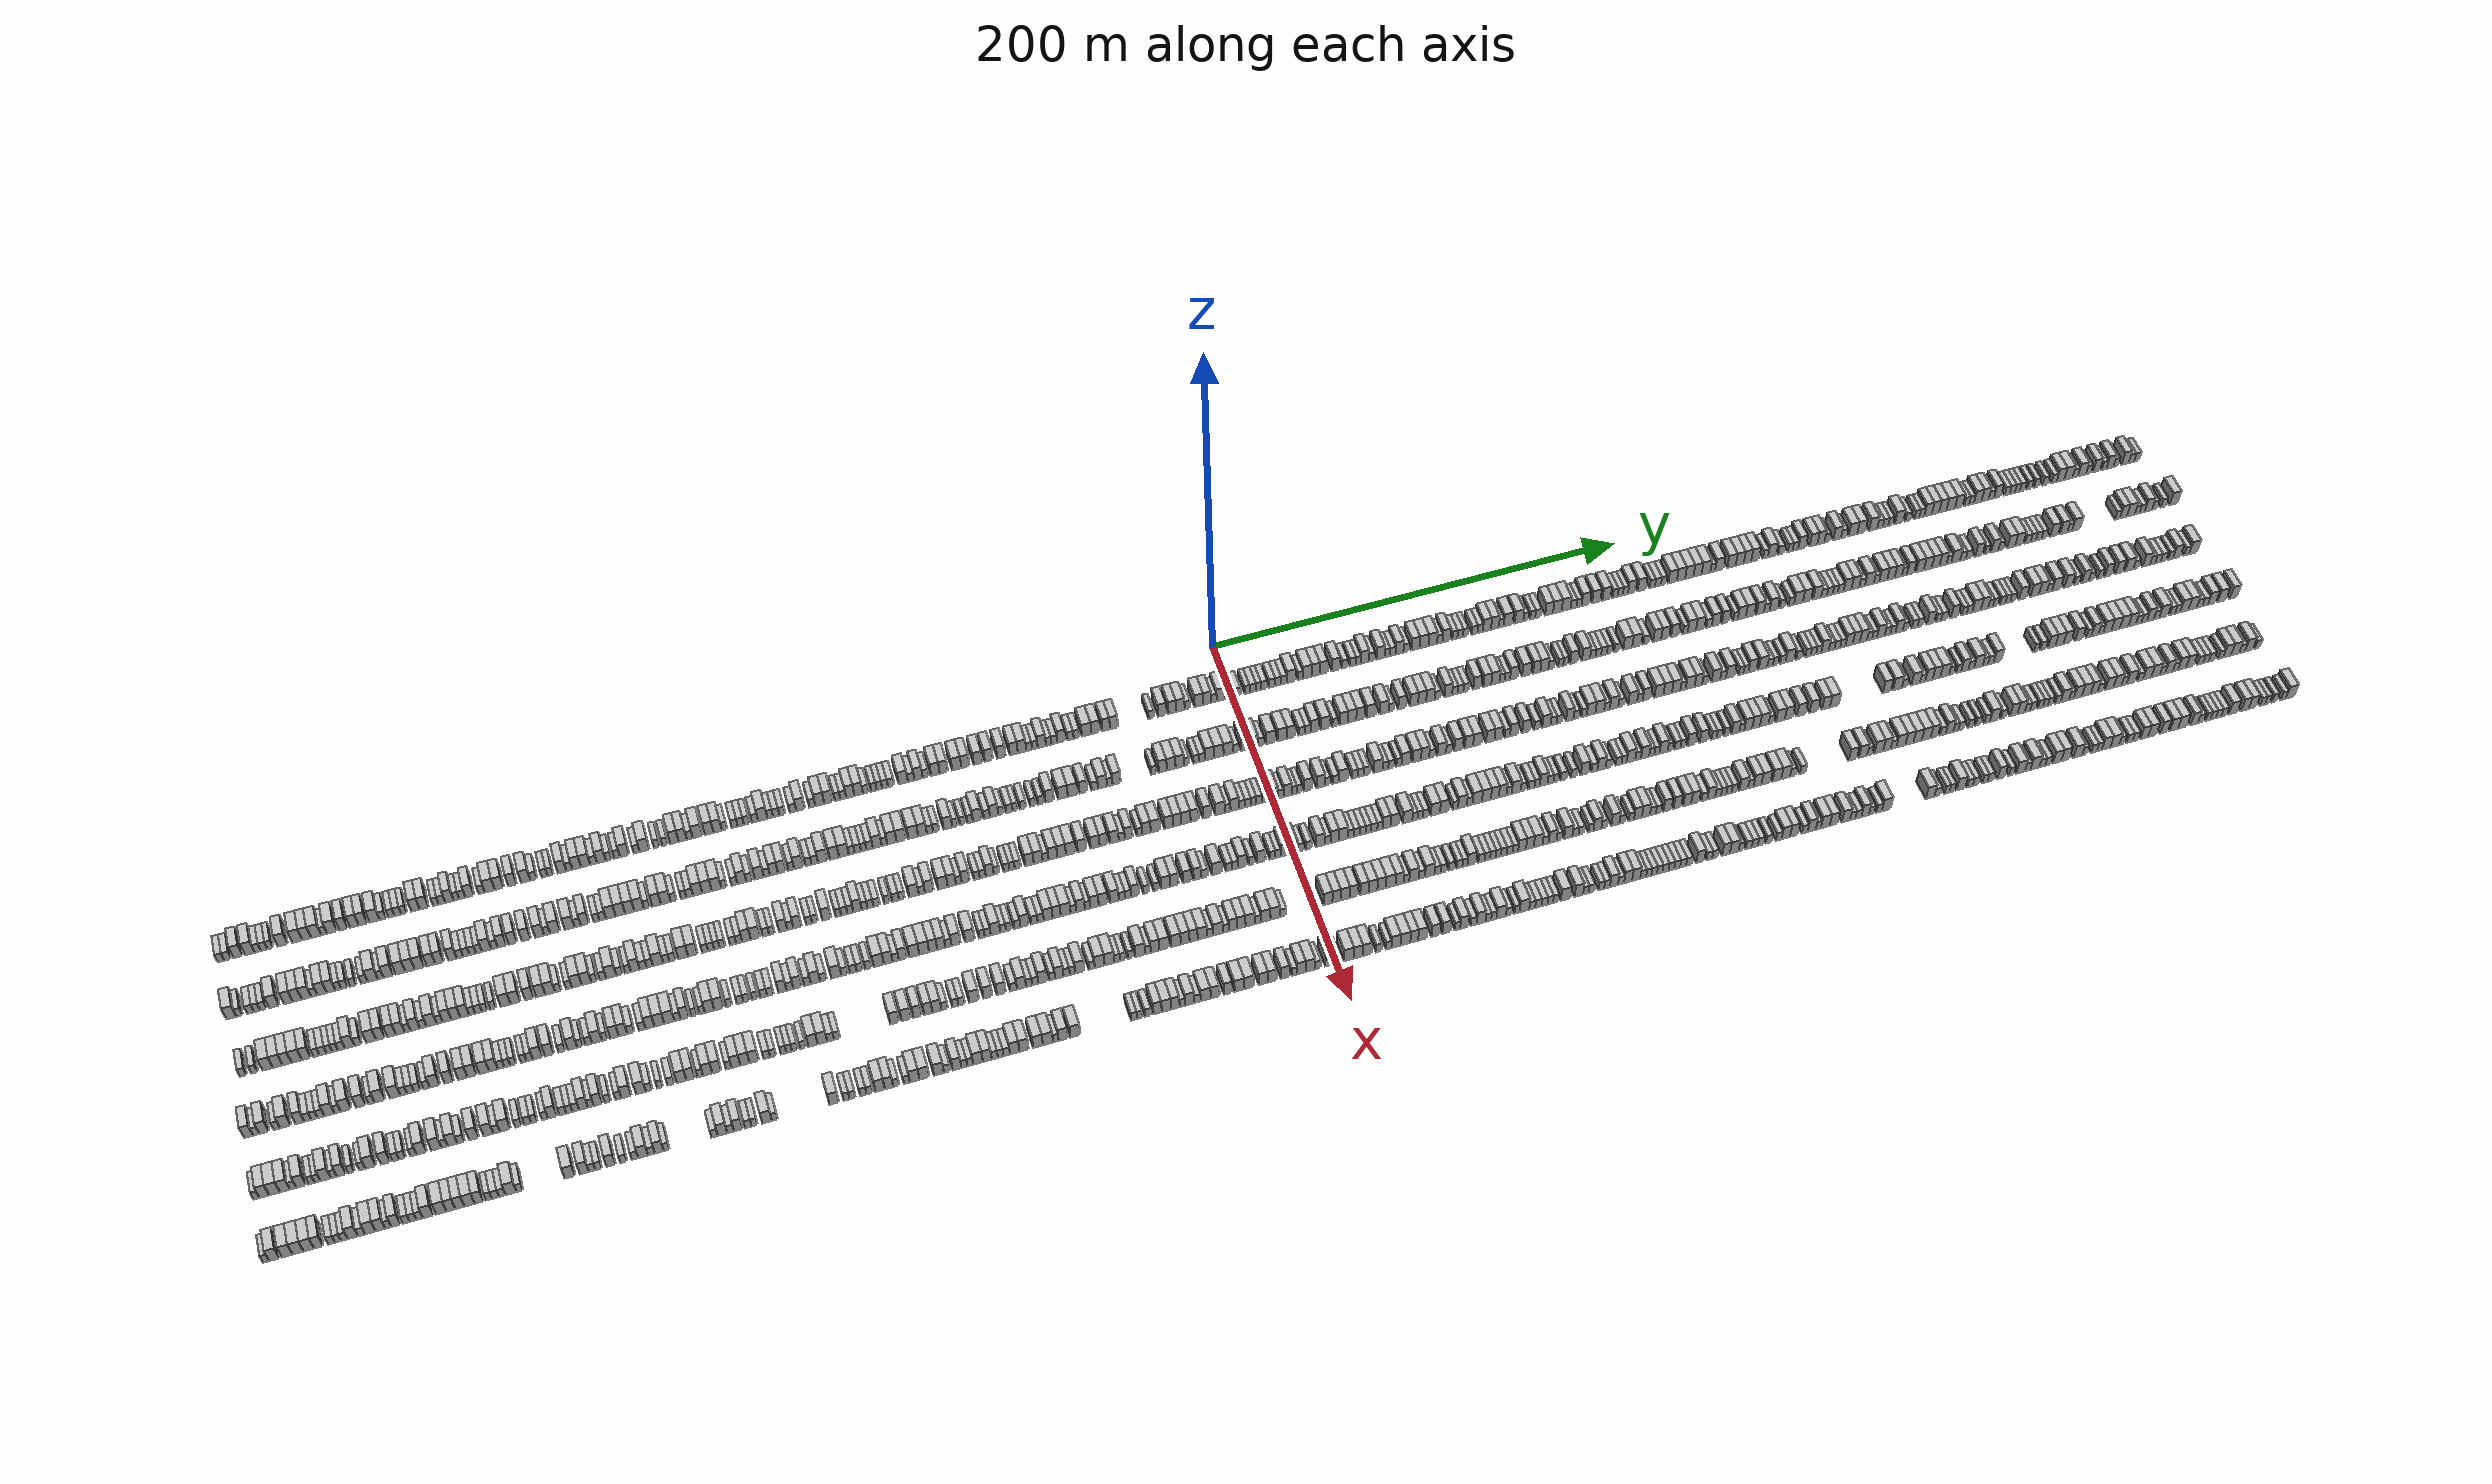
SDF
<sdf version="1.6">
 <world name="default">
  <scene>
   <sky><clouds><speed>12</speed></clouds></sky>
   <ambient>0.4 0.4 0.4 1</ambient>
   <background>0.7 0.7 0.7 1</background>
   <shadows>1</shadows>
  </scene>
  <gravity>0 0 -9.8066</gravity>
  <magnetic_field>6e-06 2.3e-05 -4.2e-05</magnetic_field>
  <physics default="0" name="default_physics" type="ode">
   <ode>
    <solver>
     <type>quick</type>
     <iters>10</iters>
     <sor>1.0</sor>
     <use_dynamic_moi_rescaling>0</use_dynamic_moi_rescaling>
    </solver>
    <constraints>
     <cfm>0</cfm>
     <erp>0.2</erp>
     <contact_max_correcting_vel>100</contact_max_correcting_vel>
     <contact_surface_layer>0.001</contact_surface_layer>
    </constraints>
   </ode>
   <max_step_size>0.004</max_step_size>
   <real_time_factor>1</real_time_factor>
   <real_time_update_rate>250</real_time_update_rate>
  </physics>
  <light name="sun" type="directional">
   <pose>0 0 10 0 0 0</pose>
   <diffuse>0.8 0.8 0.8 1</diffuse>
   <specular>0.2 0.2 0.2 1</specular>
   <attenuation>
    <range>1000</range>
    <constant>0.9</constant>
    <linear>0.01</linear>
    <quadratic>0.001</quadratic>
   </attenuation>
   <direction>-0.5 0.1 -0.9</direction>
  </light>
  <model name="building_1">
   <static>1</static>
   <pose>25.0000 -458.6029 0 0.000000 0.000000 0.000000</pose>
   <link name="link">
    <pose>0 0 3.00 0 0 0</pose>
    <collision name="collision"><geometry><box><size>10.0000 2.7942 6.0000</size></box></geometry></collision>
    <visual name="visual">
     <cast_shadows>0</cast_shadows>
     <geometry><box><size>10.0000 2.7942 6.0000</size></box></geometry>
     <material>
      <script>
       <uri>model://HANNAS_wall/materials/scripts</uri>
       <uri>model://HANNAS_wall/materials/textures</uri>
       <name>vrc/HANNAS_wall</name>
      </script>
     </material>
    </visual>
   </link>
  </model>
  <model name="building_2">
   <static>1</static>
   <pose>25.0000 -455.7267 0 0.000000 0.000000 0.000000</pose>
   <link name="link">
    <pose>0 0 3.00 0 0 0</pose>
    <collision name="collision"><geometry><box><size>10.0000 2.9581 6.0000</size></box></geometry></collision>
    <visual name="visual">
     <cast_shadows>0</cast_shadows>
     <geometry><box><size>10.0000 2.9581 6.0000</size></box></geometry>
     <material>
      <script>
       <uri>model://HANNAS_wall/materials/scripts</uri>
       <uri>model://HANNAS_wall/materials/textures</uri>
       <name>vrc/HANNAS_wall</name>
      </script>
     </material>
    </visual>
   </link>
  </model>
  <model name="building_3">
   <static>1</static>
   <pose>25.0000 -451.2907 0 0.000000 0.000000 0.000000</pose>
   <link name="link">
    <pose>0 0 4.50 0 0 0</pose>
    <collision name="collision"><geometry><box><size>10.0000 3.9138 9.0000</size></box></geometry></collision>
    <visual name="visual">
     <cast_shadows>0</cast_shadows>
     <geometry><box><size>10.0000 3.9138 9.0000</size></box></geometry>
     <material>
      <script>
       <uri>model://HANNAS_wall/materials/scripts</uri>
       <uri>model://HANNAS_wall/materials/textures</uri>
       <name>vrc/HANNAS_wall</name>
      </script>
     </material>
    </visual>
   </link>
  </model>
  <model name="building_4">
   <static>1</static>
   <pose>25.0000 -446.2774 0 0.000000 0.000000 0.000000</pose>
   <link name="link">
    <pose>0 0 4.50 0 0 0</pose>
    <collision name="collision"><geometry><box><size>10.0000 4.1127 9.0000</size></box></geometry></collision>
    <visual name="visual">
     <cast_shadows>0</cast_shadows>
     <geometry><box><size>10.0000 4.1127 9.0000</size></box></geometry>
     <material>
      <script>
       <uri>model://HANNAS_wall/materials/scripts</uri>
       <uri>model://HANNAS_wall/materials/textures</uri>
       <name>vrc/HANNAS_wall</name>
      </script>
     </material>
    </visual>
   </link>
  </model>
  <model name="building_5">
   <static>1</static>
   <pose>25.0000 -442.8723 0 0.000000 0.000000 0.000000</pose>
   <link name="link">
    <pose>0 0 3.00 0 0 0</pose>
    <collision name="collision"><geometry><box><size>10.0000 2.6977 6.0000</size></box></geometry></collision>
    <visual name="visual">
     <cast_shadows>0</cast_shadows>
     <geometry><box><size>10.0000 2.6977 6.0000</size></box></geometry>
     <material>
      <script>
       <uri>model://HANNAS_wall/materials/scripts</uri>
       <uri>model://HANNAS_wall/materials/textures</uri>
       <name>vrc/HANNAS_wall</name>
      </script>
     </material>
    </visual>
   </link>
  </model>
  <model name="building_6">
   <static>1</static>
   <pose>25.0000 -440.1029 0 0.000000 0.000000 0.000000</pose>
   <link name="link">
    <pose>0 0 3.00 0 0 0</pose>
    <collision name="collision"><geometry><box><size>10.0000 2.8411 6.0000</size></box></geometry></collision>
    <visual name="visual">
     <cast_shadows>0</cast_shadows>
     <geometry><box><size>10.0000 2.8411 6.0000</size></box></geometry>
     <material>
      <script>
       <uri>model://HANNAS_wall/materials/scripts</uri>
       <uri>model://HANNAS_wall/materials/textures</uri>
       <name>vrc/HANNAS_wall</name>
      </script>
     </material>
    </visual>
   </link>
  </model>
  <model name="building_7">
   <static>1</static>
   <pose>25.0000 -437.4816 0 0.000000 0.000000 0.000000</pose>
   <link name="link">
    <pose>0 0 3.00 0 0 0</pose>
    <collision name="collision"><geometry><box><size>10.0000 2.4014 6.0000</size></box></geometry></collision>
    <visual name="visual">
     <cast_shadows>0</cast_shadows>
     <geometry><box><size>10.0000 2.4014 6.0000</size></box></geometry>
     <material>
      <script>
       <uri>model://HANNAS_wall/materials/scripts</uri>
       <uri>model://HANNAS_wall/materials/textures</uri>
       <name>vrc/HANNAS_wall</name>
      </script>
     </material>
    </visual>
   </link>
  </model>
  <model name="building_8">
   <static>1</static>
   <pose>25.0000 -432.1610 0 0.000000 0.000000 0.000000</pose>
   <link name="link">
    <pose>0 0 4.50 0 0 0</pose>
    <collision name="collision"><geometry><box><size>10.0000 4.2400 9.0000</size></box></geometry></collision>
    <visual name="visual">
     <cast_shadows>0</cast_shadows>
     <geometry><box><size>10.0000 4.2400 9.0000</size></box></geometry>
     <material>
      <script>
       <uri>model://HANNAS_wall/materials/scripts</uri>
       <uri>model://HANNAS_wall/materials/textures</uri>
       <name>vrc/HANNAS_wall</name>
      </script>
     </material>
    </visual>
   </link>
  </model>
  <model name="building_9">
   <static>1</static>
   <pose>25.0000 -425.8645 0 0.000000 0.000000 0.000000</pose>
   <link name="link">
    <pose>0 0 4.50 0 0 0</pose>
    <collision name="collision"><geometry><box><size>10.0000 4.3530 9.0000</size></box></geometry></collision>
    <visual name="visual">
     <cast_shadows>0</cast_shadows>
     <geometry><box><size>10.0000 4.3530 9.0000</size></box></geometry>
     <material>
      <script>
       <uri>model://HANNAS_wall/materials/scripts</uri>
       <uri>model://HANNAS_wall/materials/textures</uri>
       <name>vrc/HANNAS_wall</name>
      </script>
     </material>
    </visual>
   </link>
  </model>
  <model name="building_10">
   <static>1</static>
   <pose>25.0000 -421.8221 0 0.000000 0.000000 0.000000</pose>
   <link name="link">
    <pose>0 0 4.50 0 0 0</pose>
    <collision name="collision"><geometry><box><size>10.0000 3.7318 9.0000</size></box></geometry></collision>
    <visual name="visual">
     <cast_shadows>0</cast_shadows>
     <geometry><box><size>10.0000 3.7318 9.0000</size></box></geometry>
     <material>
      <script>
       <uri>model://HANNAS_wall/materials/scripts</uri>
       <uri>model://HANNAS_wall/materials/textures</uri>
       <name>vrc/HANNAS_wall</name>
      </script>
     </material>
    </visual>
   </link>
  </model>
  <model name="building_11">
   <static>1</static>
   <pose>25.0000 -417.7450 0 0.000000 0.000000 0.000000</pose>
   <link name="link">
    <pose>0 0 4.50 0 0 0</pose>
    <collision name="collision"><geometry><box><size>10.0000 4.4225 9.0000</size></box></geometry></collision>
    <visual name="visual">
     <cast_shadows>0</cast_shadows>
     <geometry><box><size>10.0000 4.4225 9.0000</size></box></geometry>
     <material>
      <script>
       <uri>model://HANNAS_wall/materials/scripts</uri>
       <uri>model://HANNAS_wall/materials/textures</uri>
       <name>vrc/HANNAS_wall</name>
      </script>
     </material>
    </visual>
   </link>
  </model>
  <model name="building_12">
   <static>1</static>
   <pose>25.0000 -414.3129 0 0.000000 0.000000 0.000000</pose>
   <link name="link">
    <pose>0 0 3.00 0 0 0</pose>
    <collision name="collision"><geometry><box><size>10.0000 2.4416 6.0000</size></box></geometry></collision>
    <visual name="visual">
     <cast_shadows>0</cast_shadows>
     <geometry><box><size>10.0000 2.4416 6.0000</size></box></geometry>
     <material>
      <script>
       <uri>model://HANNAS_wall/materials/scripts</uri>
       <uri>model://HANNAS_wall/materials/textures</uri>
       <name>vrc/HANNAS_wall</name>
      </script>
     </material>
    </visual>
   </link>
  </model>
  <model name="building_13">
   <static>1</static>
   <pose>25.0000 -410.8627 0 0.000000 0.000000 0.000000</pose>
   <link name="link">
    <pose>0 0 4.50 0 0 0</pose>
    <collision name="collision"><geometry><box><size>10.0000 4.4589 9.0000</size></box></geometry></collision>
    <visual name="visual">
     <cast_shadows>0</cast_shadows>
     <geometry><box><size>10.0000 4.4589 9.0000</size></box></geometry>
     <material>
      <script>
       <uri>model://HANNAS_wall/materials/scripts</uri>
       <uri>model://HANNAS_wall/materials/textures</uri>
       <name>vrc/HANNAS_wall</name>
      </script>
     </material>
    </visual>
   </link>
  </model>
  <model name="building_14">
   <static>1</static>
   <pose>25.0000 -405.8294 0 0.000000 0.000000 0.000000</pose>
   <link name="link">
    <pose>0 0 4.50 0 0 0</pose>
    <collision name="collision"><geometry><box><size>10.0000 3.6076 9.0000</size></box></geometry></collision>
    <visual name="visual">
     <cast_shadows>0</cast_shadows>
     <geometry><box><size>10.0000 3.6076 9.0000</size></box></geometry>
     <material>
      <script>
       <uri>model://HANNAS_wall/materials/scripts</uri>
       <uri>model://HANNAS_wall/materials/textures</uri>
       <name>vrc/HANNAS_wall</name>
      </script>
     </material>
    </visual>
   </link>
  </model>
  <model name="building_15">
   <static>1</static>
   <pose>25.0000 -401.1671 0 0.000000 0.000000 0.000000</pose>
   <link name="link">
    <pose>0 0 4.50 0 0 0</pose>
    <collision name="collision"><geometry><box><size>10.0000 3.7169 9.0000</size></box></geometry></collision>
    <visual name="visual">
     <cast_shadows>0</cast_shadows>
     <geometry><box><size>10.0000 3.7169 9.0000</size></box></geometry>
     <material>
      <script>
       <uri>model://HANNAS_wall/materials/scripts</uri>
       <uri>model://HANNAS_wall/materials/textures</uri>
       <name>vrc/HANNAS_wall</name>
      </script>
     </material>
    </visual>
   </link>
  </model>
  <model name="building_16">
   <static>1</static>
   <pose>25.0000 -397.4379 0 0.000000 0.000000 0.000000</pose>
   <link name="link">
    <pose>0 0 4.50 0 0 0</pose>
    <collision name="collision"><geometry><box><size>10.0000 3.7416 9.0000</size></box></geometry></collision>
    <visual name="visual">
     <cast_shadows>0</cast_shadows>
     <geometry><box><size>10.0000 3.7416 9.0000</size></box></geometry>
     <material>
      <script>
       <uri>model://HANNAS_wall/materials/scripts</uri>
       <uri>model://HANNAS_wall/materials/textures</uri>
       <name>vrc/HANNAS_wall</name>
      </script>
     </material>
    </visual>
   </link>
  </model>
  <model name="building_17">
   <static>1</static>
   <pose>25.0000 -392.3693 0 0.000000 0.000000 0.000000</pose>
   <link name="link">
    <pose>0 0 4.50 0 0 0</pose>
    <collision name="collision"><geometry><box><size>10.0000 4.3956 9.0000</size></box></geometry></collision>
    <visual name="visual">
     <cast_shadows>0</cast_shadows>
     <geometry><box><size>10.0000 4.3956 9.0000</size></box></geometry>
     <material>
      <script>
       <uri>model://HANNAS_wall/materials/scripts</uri>
       <uri>model://HANNAS_wall/materials/textures</uri>
       <name>vrc/HANNAS_wall</name>
      </script>
     </material>
    </visual>
   </link>
  </model>
  <model name="building_18">
   <static>1</static>
   <pose>25.0000 -388.7617 0 0.000000 0.000000 0.000000</pose>
   <link name="link">
    <pose>0 0 3.00 0 0 0</pose>
    <collision name="collision"><geometry><box><size>10.0000 2.8195 6.0000</size></box></geometry></collision>
    <visual name="visual">
     <cast_shadows>0</cast_shadows>
     <geometry><box><size>10.0000 2.8195 6.0000</size></box></geometry>
     <material>
      <script>
       <uri>model://HANNAS_wall/materials/scripts</uri>
       <uri>model://HANNAS_wall/materials/textures</uri>
       <name>vrc/HANNAS_wall</name>
      </script>
     </material>
    </visual>
   </link>
  </model>
  <model name="building_19">
   <static>1</static>
   <pose>25.0000 -385.0344 0 0.000000 0.000000 0.000000</pose>
   <link name="link">
    <pose>0 0 3.00 0 0 0</pose>
    <collision name="collision"><geometry><box><size>10.0000 2.6351 6.0000</size></box></geometry></collision>
    <visual name="visual">
     <cast_shadows>0</cast_shadows>
     <geometry><box><size>10.0000 2.6351 6.0000</size></box></geometry>
     <material>
      <script>
       <uri>model://HANNAS_wall/materials/scripts</uri>
       <uri>model://HANNAS_wall/materials/textures</uri>
       <name>vrc/HANNAS_wall</name>
      </script>
     </material>
    </visual>
   </link>
  </model>
  <model name="building_20">
   <static>1</static>
   <pose>25.0000 -382.2800 0 0.000000 0.000000 0.000000</pose>
   <link name="link">
    <pose>0 0 3.00 0 0 0</pose>
    <collision name="collision"><geometry><box><size>10.0000 2.8738 6.0000</size></box></geometry></collision>
    <visual name="visual">
     <cast_shadows>0</cast_shadows>
     <geometry><box><size>10.0000 2.8738 6.0000</size></box></geometry>
     <material>
      <script>
       <uri>model://HANNAS_wall/materials/scripts</uri>
       <uri>model://HANNAS_wall/materials/textures</uri>
       <name>vrc/HANNAS_wall</name>
      </script>
     </material>
    </visual>
   </link>
  </model>
  <model name="building_21">
   <static>1</static>
   <pose>25.0000 -379.6237 0 0.000000 0.000000 0.000000</pose>
   <link name="link">
    <pose>0 0 3.00 0 0 0</pose>
    <collision name="collision"><geometry><box><size>10.0000 2.4389 6.0000</size></box></geometry></collision>
    <visual name="visual">
     <cast_shadows>0</cast_shadows>
     <geometry><box><size>10.0000 2.4389 6.0000</size></box></geometry>
     <material>
      <script>
       <uri>model://HANNAS_wall/materials/scripts</uri>
       <uri>model://HANNAS_wall/materials/textures</uri>
       <name>vrc/HANNAS_wall</name>
      </script>
     </material>
    </visual>
   </link>
  </model>
  <model name="building_22">
   <static>1</static>
   <pose>25.0000 -374.5385 0 0.000000 0.000000 0.000000</pose>
   <link name="link">
    <pose>0 0 4.50 0 0 0</pose>
    <collision name="collision"><geometry><box><size>10.0000 3.7314 9.0000</size></box></geometry></collision>
    <visual name="visual">
     <cast_shadows>0</cast_shadows>
     <geometry><box><size>10.0000 3.7314 9.0000</size></box></geometry>
     <material>
      <script>
       <uri>model://HANNAS_wall/materials/scripts</uri>
       <uri>model://HANNAS_wall/materials/textures</uri>
       <name>vrc/HANNAS_wall</name>
      </script>
     </material>
    </visual>
   </link>
  </model>
  <model name="building_23">
   <static>1</static>
   <pose>25.0000 -370.7666 0 0.000000 0.000000 0.000000</pose>
   <link name="link">
    <pose>0 0 4.50 0 0 0</pose>
    <collision name="collision"><geometry><box><size>10.0000 3.8125 9.0000</size></box></geometry></collision>
    <visual name="visual">
     <cast_shadows>0</cast_shadows>
     <geometry><box><size>10.0000 3.8125 9.0000</size></box></geometry>
     <material>
      <script>
       <uri>model://HANNAS_wall/materials/scripts</uri>
       <uri>model://HANNAS_wall/materials/textures</uri>
       <name>vrc/HANNAS_wall</name>
      </script>
     </material>
    </visual>
   </link>
  </model>
  <model name="building_24">
   <static>1</static>
   <pose>25.0000 -365.6417 0 0.000000 0.000000 0.000000</pose>
   <link name="link">
    <pose>0 0 3.00 0 0 0</pose>
    <collision name="collision"><geometry><box><size>10.0000 2.4372 6.0000</size></box></geometry></collision>
    <visual name="visual">
     <cast_shadows>0</cast_shadows>
     <geometry><box><size>10.0000 2.4372 6.0000</size></box></geometry>
     <material>
      <script>
       <uri>model://HANNAS_wall/materials/scripts</uri>
       <uri>model://HANNAS_wall/materials/textures</uri>
       <name>vrc/HANNAS_wall</name>
      </script>
     </material>
    </visual>
   </link>
  </model>
  <model name="building_25">
   <static>1</static>
   <pose>25.0000 -362.9609 0 0.000000 0.000000 0.000000</pose>
   <link name="link">
    <pose>0 0 3.00 0 0 0</pose>
    <collision name="collision"><geometry><box><size>10.0000 2.9243 6.0000</size></box></geometry></collision>
    <visual name="visual">
     <cast_shadows>0</cast_shadows>
     <geometry><box><size>10.0000 2.9243 6.0000</size></box></geometry>
     <material>
      <script>
       <uri>model://HANNAS_wall/materials/scripts</uri>
       <uri>model://HANNAS_wall/materials/textures</uri>
       <name>vrc/HANNAS_wall</name>
      </script>
     </material>
    </visual>
   </link>
  </model>
  <model name="building_26">
   <static>1</static>
   <pose>25.0000 -359.6762 0 0.000000 0.000000 0.000000</pose>
   <link name="link">
    <pose>0 0 4.50 0 0 0</pose>
    <collision name="collision"><geometry><box><size>10.0000 3.6451 9.0000</size></box></geometry></collision>
    <visual name="visual">
     <cast_shadows>0</cast_shadows>
     <geometry><box><size>10.0000 3.6451 9.0000</size></box></geometry>
     <material>
      <script>
       <uri>model://HANNAS_wall/materials/scripts</uri>
       <uri>model://HANNAS_wall/materials/textures</uri>
       <name>vrc/HANNAS_wall</name>
      </script>
     </material>
    </visual>
   </link>
  </model>
  <model name="building_27">
   <static>1</static>
   <pose>25.0000 -356.6252 0 0.000000 0.000000 0.000000</pose>
   <link name="link">
    <pose>0 0 3.00 0 0 0</pose>
    <collision name="collision"><geometry><box><size>10.0000 2.4570 6.0000</size></box></geometry></collision>
    <visual name="visual">
     <cast_shadows>0</cast_shadows>
     <geometry><box><size>10.0000 2.4570 6.0000</size></box></geometry>
     <material>
      <script>
       <uri>model://HANNAS_wall/materials/scripts</uri>
       <uri>model://HANNAS_wall/materials/textures</uri>
       <name>vrc/HANNAS_wall</name>
      </script>
     </material>
    </visual>
   </link>
  </model>
  <model name="building_28">
   <static>1</static>
   <pose>25.0000 -354.0434 0 0.000000 0.000000 0.000000</pose>
   <link name="link">
    <pose>0 0 3.00 0 0 0</pose>
    <collision name="collision"><geometry><box><size>10.0000 2.7066 6.0000</size></box></geometry></collision>
    <visual name="visual">
     <cast_shadows>0</cast_shadows>
     <geometry><box><size>10.0000 2.7066 6.0000</size></box></geometry>
     <material>
      <script>
       <uri>model://HANNAS_wall/materials/scripts</uri>
       <uri>model://HANNAS_wall/materials/textures</uri>
       <name>vrc/HANNAS_wall</name>
      </script>
     </material>
    </visual>
   </link>
  </model>
  <model name="building_29">
   <static>1</static>
   <pose>25.0000 -350.8006 0 0.000000 0.000000 0.000000</pose>
   <link name="link">
    <pose>0 0 4.50 0 0 0</pose>
    <collision name="collision"><geometry><box><size>10.0000 3.7789 9.0000</size></box></geometry></collision>
    <visual name="visual">
     <cast_shadows>0</cast_shadows>
     <geometry><box><size>10.0000 3.7789 9.0000</size></box></geometry>
     <material>
      <script>
       <uri>model://HANNAS_wall/materials/scripts</uri>
       <uri>model://HANNAS_wall/materials/textures</uri>
       <name>vrc/HANNAS_wall</name>
      </script>
     </material>
    </visual>
   </link>
  </model>
  <model name="building_30">
   <static>1</static>
   <pose>25.0000 -345.5308 0 0.000000 0.000000 0.000000</pose>
   <link name="link">
    <pose>0 0 3.00 0 0 0</pose>
    <collision name="collision"><geometry><box><size>10.0000 2.7607 6.0000</size></box></geometry></collision>
    <visual name="visual">
     <cast_shadows>0</cast_shadows>
     <geometry><box><size>10.0000 2.7607 6.0000</size></box></geometry>
     <material>
      <script>
       <uri>model://HANNAS_wall/materials/scripts</uri>
       <uri>model://HANNAS_wall/materials/textures</uri>
       <name>vrc/HANNAS_wall</name>
      </script>
     </material>
    </visual>
   </link>
  </model>
  <model name="building_31">
   <static>1</static>
   <pose>25.0000 -341.9601 0 0.000000 0.000000 0.000000</pose>
   <link name="link">
    <pose>0 0 4.50 0 0 0</pose>
    <collision name="collision"><geometry><box><size>10.0000 4.3808 9.0000</size></box></geometry></collision>
    <visual name="visual">
     <cast_shadows>0</cast_shadows>
     <geometry><box><size>10.0000 4.3808 9.0000</size></box></geometry>
     <material>
      <script>
       <uri>model://HANNAS_wall/materials/scripts</uri>
       <uri>model://HANNAS_wall/materials/textures</uri>
       <name>vrc/HANNAS_wall</name>
      </script>
     </material>
    </visual>
   </link>
  </model>
  <model name="building_32">
   <static>1</static>
   <pose>25.0000 -337.7786 0 0.000000 0.000000 0.000000</pose>
   <link name="link">
    <pose>0 0 4.50 0 0 0</pose>
    <collision name="collision"><geometry><box><size>10.0000 3.9821 9.0000</size></box></geometry></collision>
    <visual name="visual">
     <cast_shadows>0</cast_shadows>
     <geometry><box><size>10.0000 3.9821 9.0000</size></box></geometry>
     <material>
      <script>
       <uri>model://HANNAS_wall/materials/scripts</uri>
       <uri>model://HANNAS_wall/materials/textures</uri>
       <name>vrc/HANNAS_wall</name>
      </script>
     </material>
    </visual>
   </link>
  </model>
  <model name="building_33">
   <static>1</static>
   <pose>25.0000 -331.9668 0 0.000000 0.000000 0.000000</pose>
   <link name="link">
    <pose>0 0 4.50 0 0 0</pose>
    <collision name="collision"><geometry><box><size>10.0000 3.6417 9.0000</size></box></geometry></collision>
    <visual name="visual">
     <cast_shadows>0</cast_shadows>
     <geometry><box><size>10.0000 3.6417 9.0000</size></box></geometry>
     <material>
      <script>
       <uri>model://HANNAS_wall/materials/scripts</uri>
       <uri>model://HANNAS_wall/materials/textures</uri>
       <name>vrc/HANNAS_wall</name>
      </script>
     </material>
    </visual>
   </link>
  </model>
  <model name="building_34">
   <static>1</static>
   <pose>25.0000 -326.0694 0 0.000000 0.000000 0.000000</pose>
   <link name="link">
    <pose>0 0 4.50 0 0 0</pose>
    <collision name="collision"><geometry><box><size>10.0000 4.1531 9.0000</size></box></geometry></collision>
    <visual name="visual">
     <cast_shadows>0</cast_shadows>
     <geometry><box><size>10.0000 4.1531 9.0000</size></box></geometry>
     <material>
      <script>
       <uri>model://HANNAS_wall/materials/scripts</uri>
       <uri>model://HANNAS_wall/materials/textures</uri>
       <name>vrc/HANNAS_wall</name>
      </script>
     </material>
    </visual>
   </link>
  </model>
  <model name="building_35">
   <static>1</static>
   <pose>25.0000 -322.5050 0 0.000000 0.000000 0.000000</pose>
   <link name="link">
    <pose>0 0 3.00 0 0 0</pose>
    <collision name="collision"><geometry><box><size>10.0000 2.9756 6.0000</size></box></geometry></collision>
    <visual name="visual">
     <cast_shadows>0</cast_shadows>
     <geometry><box><size>10.0000 2.9756 6.0000</size></box></geometry>
     <material>
      <script>
       <uri>model://HANNAS_wall/materials/scripts</uri>
       <uri>model://HANNAS_wall/materials/textures</uri>
       <name>vrc/HANNAS_wall</name>
      </script>
     </material>
    </visual>
   </link>
  </model>
  <model name="building_36">
   <static>1</static>
   <pose>25.0000 -317.7281 0 0.000000 0.000000 0.000000</pose>
   <link name="link">
    <pose>0 0 3.00 0 0 0</pose>
    <collision name="collision"><geometry><box><size>10.0000 2.5782 6.0000</size></box></geometry></collision>
    <visual name="visual">
     <cast_shadows>0</cast_shadows>
     <geometry><box><size>10.0000 2.5782 6.0000</size></box></geometry>
     <material>
      <script>
       <uri>model://HANNAS_wall/materials/scripts</uri>
       <uri>model://HANNAS_wall/materials/textures</uri>
       <name>vrc/HANNAS_wall</name>
      </script>
     </material>
    </visual>
   </link>
  </model>
  <model name="building_37">
   <static>1</static>
   <pose>25.0000 -315.1455 0 0.000000 0.000000 0.000000</pose>
   <link name="link">
    <pose>0 0 3.00 0 0 0</pose>
    <collision name="collision"><geometry><box><size>10.0000 2.5869 6.0000</size></box></geometry></collision>
    <visual name="visual">
     <cast_shadows>0</cast_shadows>
     <geometry><box><size>10.0000 2.5869 6.0000</size></box></geometry>
     <material>
      <script>
       <uri>model://HANNAS_wall/materials/scripts</uri>
       <uri>model://HANNAS_wall/materials/textures</uri>
       <name>vrc/HANNAS_wall</name>
      </script>
     </material>
    </visual>
   </link>
  </model>
  <model name="building_38">
   <static>1</static>
   <pose>25.0000 -309.9671 0 0.000000 0.000000 0.000000</pose>
   <link name="link">
    <pose>0 0 4.50 0 0 0</pose>
    <collision name="collision"><geometry><box><size>10.0000 3.7700 9.0000</size></box></geometry></collision>
    <visual name="visual">
     <cast_shadows>0</cast_shadows>
     <geometry><box><size>10.0000 3.7700 9.0000</size></box></geometry>
     <material>
      <script>
       <uri>model://HANNAS_wall/materials/scripts</uri>
       <uri>model://HANNAS_wall/materials/textures</uri>
       <name>vrc/HANNAS_wall</name>
      </script>
     </material>
    </visual>
   </link>
  </model>
  <model name="building_39">
   <static>1</static>
   <pose>25.0000 -306.7445 0 0.000000 0.000000 0.000000</pose>
   <link name="link">
    <pose>0 0 3.00 0 0 0</pose>
    <collision name="collision"><geometry><box><size>10.0000 2.6752 6.0000</size></box></geometry></collision>
    <visual name="visual">
     <cast_shadows>0</cast_shadows>
     <geometry><box><size>10.0000 2.6752 6.0000</size></box></geometry>
     <material>
      <script>
       <uri>model://HANNAS_wall/materials/scripts</uri>
       <uri>model://HANNAS_wall/materials/textures</uri>
       <name>vrc/HANNAS_wall</name>
      </script>
     </material>
    </visual>
   </link>
  </model>
  <model name="building_40">
   <static>1</static>
   <pose>25.0000 -303.4571 0 0.000000 0.000000 0.000000</pose>
   <link name="link">
    <pose>0 0 4.50 0 0 0</pose>
    <collision name="collision"><geometry><box><size>10.0000 3.8995 9.0000</size></box></geometry></collision>
    <visual name="visual">
     <cast_shadows>0</cast_shadows>
     <geometry><box><size>10.0000 3.8995 9.0000</size></box></geometry>
     <material>
      <script>
       <uri>model://HANNAS_wall/materials/scripts</uri>
       <uri>model://HANNAS_wall/materials/textures</uri>
       <name>vrc/HANNAS_wall</name>
      </script>
     </material>
    </visual>
   </link>
  </model>
  <model name="building_41">
   <static>1</static>
   <pose>25.0000 -299.4450 0 0.000000 0.000000 0.000000</pose>
   <link name="link">
    <pose>0 0 4.50 0 0 0</pose>
    <collision name="collision"><geometry><box><size>10.0000 4.1248 9.0000</size></box></geometry></collision>
    <visual name="visual">
     <cast_shadows>0</cast_shadows>
     <geometry><box><size>10.0000 4.1248 9.0000</size></box></geometry>
     <material>
      <script>
       <uri>model://HANNAS_wall/materials/scripts</uri>
       <uri>model://HANNAS_wall/materials/textures</uri>
       <name>vrc/HANNAS_wall</name>
      </script>
     </material>
    </visual>
   </link>
  </model>
  <model name="building_42">
   <static>1</static>
   <pose>25.0000 -295.9050 0 0.000000 0.000000 0.000000</pose>
   <link name="link">
    <pose>0 0 3.00 0 0 0</pose>
    <collision name="collision"><geometry><box><size>10.0000 2.9551 6.0000</size></box></geometry></collision>
    <visual name="visual">
     <cast_shadows>0</cast_shadows>
     <geometry><box><size>10.0000 2.9551 6.0000</size></box></geometry>
     <material>
      <script>
       <uri>model://HANNAS_wall/materials/scripts</uri>
       <uri>model://HANNAS_wall/materials/textures</uri>
       <name>vrc/HANNAS_wall</name>
      </script>
     </material>
    </visual>
   </link>
  </model>
  <model name="building_43">
   <static>1</static>
   <pose>25.0000 -292.4702 0 0.000000 0.000000 0.000000</pose>
   <link name="link">
    <pose>0 0 4.50 0 0 0</pose>
    <collision name="collision"><geometry><box><size>10.0000 3.9146 9.0000</size></box></geometry></collision>
    <visual name="visual">
     <cast_shadows>0</cast_shadows>
     <geometry><box><size>10.0000 3.9146 9.0000</size></box></geometry>
     <material>
      <script>
       <uri>model://HANNAS_wall/materials/scripts</uri>
       <uri>model://HANNAS_wall/materials/textures</uri>
       <name>vrc/HANNAS_wall</name>
      </script>
     </material>
    </visual>
   </link>
  </model>
  <model name="building_44">
   <static>1</static>
   <pose>25.0000 -289.1764 0 0.000000 0.000000 0.000000</pose>
   <link name="link">
    <pose>0 0 3.00 0 0 0</pose>
    <collision name="collision"><geometry><box><size>10.0000 2.6730 6.0000</size></box></geometry></collision>
    <visual name="visual">
     <cast_shadows>0</cast_shadows>
     <geometry><box><size>10.0000 2.6730 6.0000</size></box></geometry>
     <material>
      <script>
       <uri>model://HANNAS_wall/materials/scripts</uri>
       <uri>model://HANNAS_wall/materials/textures</uri>
       <name>vrc/HANNAS_wall</name>
      </script>
     </material>
    </visual>
   </link>
  </model>
  <model name="building_45">
   <static>1</static>
   <pose>25.0000 -285.5234 0 0.000000 0.000000 0.000000</pose>
   <link name="link">
    <pose>0 0 3.00 0 0 0</pose>
    <collision name="collision"><geometry><box><size>10.0000 2.6329 6.0000</size></box></geometry></collision>
    <visual name="visual">
     <cast_shadows>0</cast_shadows>
     <geometry><box><size>10.0000 2.6329 6.0000</size></box></geometry>
     <material>
      <script>
       <uri>model://HANNAS_wall/materials/scripts</uri>
       <uri>model://HANNAS_wall/materials/textures</uri>
       <name>vrc/HANNAS_wall</name>
      </script>
     </material>
    </visual>
   </link>
  </model>
  <model name="building_46">
   <static>1</static>
   <pose>25.0000 -282.1227 0 0.000000 0.000000 0.000000</pose>
   <link name="link">
    <pose>0 0 4.50 0 0 0</pose>
    <collision name="collision"><geometry><box><size>10.0000 4.1686 9.0000</size></box></geometry></collision>
    <visual name="visual">
     <cast_shadows>0</cast_shadows>
     <geometry><box><size>10.0000 4.1686 9.0000</size></box></geometry>
     <material>
      <script>
       <uri>model://HANNAS_wall/materials/scripts</uri>
       <uri>model://HANNAS_wall/materials/textures</uri>
       <name>vrc/HANNAS_wall</name>
      </script>
     </material>
    </visual>
   </link>
  </model>
  <model name="building_47">
   <static>1</static>
   <pose>25.0000 -276.6991 0 0.000000 0.000000 0.000000</pose>
   <link name="link">
    <pose>0 0 3.00 0 0 0</pose>
    <collision name="collision"><geometry><box><size>10.0000 2.6786 6.0000</size></box></geometry></collision>
    <visual name="visual">
     <cast_shadows>0</cast_shadows>
     <geometry><box><size>10.0000 2.6786 6.0000</size></box></geometry>
     <material>
      <script>
       <uri>model://HANNAS_wall/materials/scripts</uri>
       <uri>model://HANNAS_wall/materials/textures</uri>
       <name>vrc/HANNAS_wall</name>
      </script>
     </material>
    </visual>
   </link>
  </model>
  <model name="building_48">
   <static>1</static>
   <pose>25.0000 -273.1590 0 0.000000 0.000000 0.000000</pose>
   <link name="link">
    <pose>0 0 4.50 0 0 0</pose>
    <collision name="collision"><geometry><box><size>10.0000 4.4017 9.0000</size></box></geometry></collision>
    <visual name="visual">
     <cast_shadows>0</cast_shadows>
     <geometry><box><size>10.0000 4.4017 9.0000</size></box></geometry>
     <material>
      <script>
       <uri>model://HANNAS_wall/materials/scripts</uri>
       <uri>model://HANNAS_wall/materials/textures</uri>
       <name>vrc/HANNAS_wall</name>
      </script>
     </material>
    </visual>
   </link>
  </model>
  <model name="building_49">
   <static>1</static>
   <pose>25.0000 -267.6129 0 0.000000 0.000000 0.000000</pose>
   <link name="link">
    <pose>0 0 3.00 0 0 0</pose>
    <collision name="collision"><geometry><box><size>10.0000 2.6904 6.0000</size></box></geometry></collision>
    <visual name="visual">
     <cast_shadows>0</cast_shadows>
     <geometry><box><size>10.0000 2.6904 6.0000</size></box></geometry>
     <material>
      <script>
       <uri>model://HANNAS_wall/materials/scripts</uri>
       <uri>model://HANNAS_wall/materials/textures</uri>
       <name>vrc/HANNAS_wall</name>
      </script>
     </material>
    </visual>
   </link>
  </model>
  <model name="building_50">
   <static>1</static>
   <pose>25.0000 -263.9552 0 0.000000 0.000000 0.000000</pose>
   <link name="link">
    <pose>0 0 3.00 0 0 0</pose>
    <collision name="collision"><geometry><box><size>10.0000 2.6250 6.0000</size></box></geometry></collision>
    <visual name="visual">
     <cast_shadows>0</cast_shadows>
     <geometry><box><size>10.0000 2.6250 6.0000</size></box></geometry>
     <material>
      <script>
       <uri>model://HANNAS_wall/materials/scripts</uri>
       <uri>model://HANNAS_wall/materials/textures</uri>
       <name>vrc/HANNAS_wall</name>
      </script>
     </material>
    </visual>
   </link>
  </model>
  <model name="building_51">
   <static>1</static>
   <pose>25.0000 -259.7512 0 0.000000 0.000000 0.000000</pose>
   <link name="link">
    <pose>0 0 4.50 0 0 0</pose>
    <collision name="collision"><geometry><box><size>10.0000 3.7831 9.0000</size></box></geometry></collision>
    <visual name="visual">
     <cast_shadows>0</cast_shadows>
     <geometry><box><size>10.0000 3.7831 9.0000</size></box></geometry>
     <material>
      <script>
       <uri>model://HANNAS_wall/materials/scripts</uri>
       <uri>model://HANNAS_wall/materials/textures</uri>
       <name>vrc/HANNAS_wall</name>
      </script>
     </material>
    </visual>
   </link>
  </model>
  <model name="building_52">
   <static>1</static>
   <pose>25.0000 -256.0086 0 0.000000 0.000000 0.000000</pose>
   <link name="link">
    <pose>0 0 4.50 0 0 0</pose>
    <collision name="collision"><geometry><box><size>10.0000 3.7020 9.0000</size></box></geometry></collision>
    <visual name="visual">
     <cast_shadows>0</cast_shadows>
     <geometry><box><size>10.0000 3.7020 9.0000</size></box></geometry>
     <material>
      <script>
       <uri>model://HANNAS_wall/materials/scripts</uri>
       <uri>model://HANNAS_wall/materials/textures</uri>
       <name>vrc/HANNAS_wall</name>
      </script>
     </material>
    </visual>
   </link>
  </model>
  <model name="building_53">
   <static>1</static>
   <pose>25.0000 -252.8353 0 0.000000 0.000000 0.000000</pose>
   <link name="link">
    <pose>0 0 3.00 0 0 0</pose>
    <collision name="collision"><geometry><box><size>10.0000 2.6446 6.0000</size></box></geometry></collision>
    <visual name="visual">
     <cast_shadows>0</cast_shadows>
     <geometry><box><size>10.0000 2.6446 6.0000</size></box></geometry>
     <material>
      <script>
       <uri>model://HANNAS_wall/materials/scripts</uri>
       <uri>model://HANNAS_wall/materials/textures</uri>
       <name>vrc/HANNAS_wall</name>
      </script>
     </material>
    </visual>
   </link>
  </model>
  <model name="building_54">
   <static>1</static>
   <pose>25.0000 -249.2851 0 0.000000 0.000000 0.000000</pose>
   <link name="link">
    <pose>0 0 4.50 0 0 0</pose>
    <collision name="collision"><geometry><box><size>10.0000 4.4559 9.0000</size></box></geometry></collision>
    <visual name="visual">
     <cast_shadows>0</cast_shadows>
     <geometry><box><size>10.0000 4.4559 9.0000</size></box></geometry>
     <material>
      <script>
       <uri>model://HANNAS_wall/materials/scripts</uri>
       <uri>model://HANNAS_wall/materials/textures</uri>
       <name>vrc/HANNAS_wall</name>
      </script>
     </material>
    </visual>
   </link>
  </model>
  <model name="building_55">
   <static>1</static>
   <pose>25.0000 -244.0844 0 0.000000 0.000000 0.000000</pose>
   <link name="link">
    <pose>0 0 4.50 0 0 0</pose>
    <collision name="collision"><geometry><box><size>10.0000 3.9455 9.0000</size></box></geometry></collision>
    <visual name="visual">
     <cast_shadows>0</cast_shadows>
     <geometry><box><size>10.0000 3.9455 9.0000</size></box></geometry>
     <material>
      <script>
       <uri>model://HANNAS_wall/materials/scripts</uri>
       <uri>model://HANNAS_wall/materials/textures</uri>
       <name>vrc/HANNAS_wall</name>
      </script>
     </material>
    </visual>
   </link>
  </model>
  <model name="building_56">
   <static>1</static>
   <pose>25.0000 -240.2194 0 0.000000 0.000000 0.000000</pose>
   <link name="link">
    <pose>0 0 4.50 0 0 0</pose>
    <collision name="collision"><geometry><box><size>10.0000 3.7845 9.0000</size></box></geometry></collision>
    <visual name="visual">
     <cast_shadows>0</cast_shadows>
     <geometry><box><size>10.0000 3.7845 9.0000</size></box></geometry>
     <material>
      <script>
       <uri>model://HANNAS_wall/materials/scripts</uri>
       <uri>model://HANNAS_wall/materials/textures</uri>
       <name>vrc/HANNAS_wall</name>
      </script>
     </material>
    </visual>
   </link>
  </model>
  <model name="building_57">
   <static>1</static>
   <pose>25.0000 -237.1265 0 0.000000 0.000000 0.000000</pose>
   <link name="link">
    <pose>0 0 3.00 0 0 0</pose>
    <collision name="collision"><geometry><box><size>10.0000 2.4014 6.0000</size></box></geometry></collision>
    <visual name="visual">
     <cast_shadows>0</cast_shadows>
     <geometry><box><size>10.0000 2.4014 6.0000</size></box></geometry>
     <material>
      <script>
       <uri>model://HANNAS_wall/materials/scripts</uri>
       <uri>model://HANNAS_wall/materials/textures</uri>
       <name>vrc/HANNAS_wall</name>
      </script>
     </material>
    </visual>
   </link>
  </model>
  <model name="building_58">
   <static>1</static>
   <pose>25.0000 -232.5295 0 0.000000 0.000000 0.000000</pose>
   <link name="link">
    <pose>0 0 3.00 0 0 0</pose>
    <collision name="collision"><geometry><box><size>10.0000 2.7925 6.0000</size></box></geometry></collision>
    <visual name="visual">
     <cast_shadows>0</cast_shadows>
     <geometry><box><size>10.0000 2.7925 6.0000</size></box></geometry>
     <material>
      <script>
       <uri>model://HANNAS_wall/materials/scripts</uri>
       <uri>model://HANNAS_wall/materials/textures</uri>
       <name>vrc/HANNAS_wall</name>
      </script>
     </material>
    </visual>
   </link>
  </model>
  <model name="building_59">
   <static>1</static>
   <pose>25.0000 -229.7505 0 0.000000 0.000000 0.000000</pose>
   <link name="link">
    <pose>0 0 3.00 0 0 0</pose>
    <collision name="collision"><geometry><box><size>10.0000 2.7655 6.0000</size></box></geometry></collision>
    <visual name="visual">
     <cast_shadows>0</cast_shadows>
     <geometry><box><size>10.0000 2.7655 6.0000</size></box></geometry>
     <material>
      <script>
       <uri>model://HANNAS_wall/materials/scripts</uri>
       <uri>model://HANNAS_wall/materials/textures</uri>
       <name>vrc/HANNAS_wall</name>
      </script>
     </material>
    </visual>
   </link>
  </model>
  <model name="building_60">
   <static>1</static>
   <pose>25.0000 -227.0693 0 0.000000 0.000000 0.000000</pose>
   <link name="link">
    <pose>0 0 3.00 0 0 0</pose>
    <collision name="collision"><geometry><box><size>10.0000 2.5969 6.0000</size></box></geometry></collision>
    <visual name="visual">
     <cast_shadows>0</cast_shadows>
     <geometry><box><size>10.0000 2.5969 6.0000</size></box></geometry>
     <material>
      <script>
       <uri>model://HANNAS_wall/materials/scripts</uri>
       <uri>model://HANNAS_wall/materials/textures</uri>
       <name>vrc/HANNAS_wall</name>
      </script>
     </material>
    </visual>
   </link>
  </model>
  <model name="building_61">
   <static>1</static>
   <pose>25.0000 -223.3637 0 0.000000 0.000000 0.000000</pose>
   <link name="link">
    <pose>0 0 3.00 0 0 0</pose>
    <collision name="collision"><geometry><box><size>10.0000 2.8145 6.0000</size></box></geometry></collision>
    <visual name="visual">
     <cast_shadows>0</cast_shadows>
     <geometry><box><size>10.0000 2.8145 6.0000</size></box></geometry>
     <material>
      <script>
       <uri>model://HANNAS_wall/materials/scripts</uri>
       <uri>model://HANNAS_wall/materials/textures</uri>
       <name>vrc/HANNAS_wall</name>
      </script>
     </material>
    </visual>
   </link>
  </model>
  <model name="building_62">
   <static>1</static>
   <pose>25.0000 -219.7949 0 0.000000 0.000000 0.000000</pose>
   <link name="link">
    <pose>0 0 4.50 0 0 0</pose>
    <collision name="collision"><geometry><box><size>10.0000 4.3231 9.0000</size></box></geometry></collision>
    <visual name="visual">
     <cast_shadows>0</cast_shadows>
     <geometry><box><size>10.0000 4.3231 9.0000</size></box></geometry>
     <material>
      <script>
       <uri>model://HANNAS_wall/materials/scripts</uri>
       <uri>model://HANNAS_wall/materials/textures</uri>
       <name>vrc/HANNAS_wall</name>
      </script>
     </material>
    </visual>
   </link>
  </model>
  <model name="building_63">
   <static>1</static>
   <pose>25.0000 -216.3594 0 0.000000 0.000000 0.000000</pose>
   <link name="link">
    <pose>0 0 3.00 0 0 0</pose>
    <collision name="collision"><geometry><box><size>10.0000 2.5478 6.0000</size></box></geometry></collision>
    <visual name="visual">
     <cast_shadows>0</cast_shadows>
     <geometry><box><size>10.0000 2.5478 6.0000</size></box></geometry>
     <material>
      <script>
       <uri>model://HANNAS_wall/materials/scripts</uri>
       <uri>model://HANNAS_wall/materials/textures</uri>
       <name>vrc/HANNAS_wall</name>
      </script>
     </material>
    </visual>
   </link>
  </model>
  <model name="building_64">
   <static>1</static>
   <pose>25.0000 -213.6650 0 0.000000 0.000000 0.000000</pose>
   <link name="link">
    <pose>0 0 3.00 0 0 0</pose>
    <collision name="collision"><geometry><box><size>10.0000 2.8410 6.0000</size></box></geometry></collision>
    <visual name="visual">
     <cast_shadows>0</cast_shadows>
     <geometry><box><size>10.0000 2.8410 6.0000</size></box></geometry>
     <material>
      <script>
       <uri>model://HANNAS_wall/materials/scripts</uri>
       <uri>model://HANNAS_wall/materials/textures</uri>
       <name>vrc/HANNAS_wall</name>
      </script>
     </material>
    </visual>
   </link>
  </model>
  <model name="building_65">
   <static>1</static>
   <pose>25.0000 -210.8804 0 0.000000 0.000000 0.000000</pose>
   <link name="link">
    <pose>0 0 3.00 0 0 0</pose>
    <collision name="collision"><geometry><box><size>10.0000 2.7284 6.0000</size></box></geometry></collision>
    <visual name="visual">
     <cast_shadows>0</cast_shadows>
     <geometry><box><size>10.0000 2.7284 6.0000</size></box></geometry>
     <material>
      <script>
       <uri>model://HANNAS_wall/materials/scripts</uri>
       <uri>model://HANNAS_wall/materials/textures</uri>
       <name>vrc/HANNAS_wall</name>
      </script>
     </material>
    </visual>
   </link>
  </model>
  <model name="building_66">
   <static>1</static>
   <pose>25.0000 -206.0302 0 0.000000 0.000000 0.000000</pose>
   <link name="link">
    <pose>0 0 3.00 0 0 0</pose>
    <collision name="collision"><geometry><box><size>10.0000 2.9719 6.0000</size></box></geometry></collision>
    <visual name="visual">
     <cast_shadows>0</cast_shadows>
     <geometry><box><size>10.0000 2.9719 6.0000</size></box></geometry>
     <material>
      <script>
       <uri>model://HANNAS_wall/materials/scripts</uri>
       <uri>model://HANNAS_wall/materials/textures</uri>
       <name>vrc/HANNAS_wall</name>
      </script>
     </material>
    </visual>
   </link>
  </model>
  <model name="building_67">
   <static>1</static>
   <pose>25.0000 -202.5640 0 0.000000 0.000000 0.000000</pose>
   <link name="link">
    <pose>0 0 4.50 0 0 0</pose>
    <collision name="collision"><geometry><box><size>10.0000 3.9606 9.0000</size></box></geometry></collision>
    <visual name="visual">
     <cast_shadows>0</cast_shadows>
     <geometry><box><size>10.0000 3.9606 9.0000</size></box></geometry>
     <material>
      <script>
       <uri>model://HANNAS_wall/materials/scripts</uri>
       <uri>model://HANNAS_wall/materials/textures</uri>
       <name>vrc/HANNAS_wall</name>
      </script>
     </material>
    </visual>
   </link>
  </model>
  <model name="building_68">
   <static>1</static>
   <pose>25.0000 -197.2149 0 0.000000 0.000000 0.000000</pose>
   <link name="link">
    <pose>0 0 3.00 0 0 0</pose>
    <collision name="collision"><geometry><box><size>10.0000 2.7376 6.0000</size></box></geometry></collision>
    <visual name="visual">
     <cast_shadows>0</cast_shadows>
     <geometry><box><size>10.0000 2.7376 6.0000</size></box></geometry>
     <material>
      <script>
       <uri>model://HANNAS_wall/materials/scripts</uri>
       <uri>model://HANNAS_wall/materials/textures</uri>
       <name>vrc/HANNAS_wall</name>
      </script>
     </material>
    </visual>
   </link>
  </model>
  <model name="building_69">
   <static>1</static>
   <pose>25.0000 -193.7944 0 0.000000 0.000000 0.000000</pose>
   <link name="link">
    <pose>0 0 4.50 0 0 0</pose>
    <collision name="collision"><geometry><box><size>10.0000 4.1033 9.0000</size></box></geometry></collision>
    <visual name="visual">
     <cast_shadows>0</cast_shadows>
     <geometry><box><size>10.0000 4.1033 9.0000</size></box></geometry>
     <material>
      <script>
       <uri>model://HANNAS_wall/materials/scripts</uri>
       <uri>model://HANNAS_wall/materials/textures</uri>
       <name>vrc/HANNAS_wall</name>
      </script>
     </material>
    </visual>
   </link>
  </model>
  <model name="building_70">
   <static>1</static>
   <pose>25.0000 -189.8073 0 0.000000 0.000000 0.000000</pose>
   <link name="link">
    <pose>0 0 4.50 0 0 0</pose>
    <collision name="collision"><geometry><box><size>10.0000 3.8709 9.0000</size></box></geometry></collision>
    <visual name="visual">
     <cast_shadows>0</cast_shadows>
     <geometry><box><size>10.0000 3.8709 9.0000</size></box></geometry>
     <material>
      <script>
       <uri>model://HANNAS_wall/materials/scripts</uri>
       <uri>model://HANNAS_wall/materials/textures</uri>
       <name>vrc/HANNAS_wall</name>
      </script>
     </material>
    </visual>
   </link>
  </model>
  <model name="building_71">
   <static>1</static>
   <pose>25.0000 -185.6113 0 0.000000 0.000000 0.000000</pose>
   <link name="link">
    <pose>0 0 3.00 0 0 0</pose>
    <collision name="collision"><geometry><box><size>10.0000 2.5211 6.0000</size></box></geometry></collision>
    <visual name="visual">
     <cast_shadows>0</cast_shadows>
     <geometry><box><size>10.0000 2.5211 6.0000</size></box></geometry>
     <material>
      <script>
       <uri>model://HANNAS_wall/materials/scripts</uri>
       <uri>model://HANNAS_wall/materials/textures</uri>
       <name>vrc/HANNAS_wall</name>
      </script>
     </material>
    </visual>
   </link>
  </model>
  <model name="building_72">
   <static>1</static>
   <pose>25.0000 -183.0315 0 0.000000 0.000000 0.000000</pose>
   <link name="link">
    <pose>0 0 3.00 0 0 0</pose>
    <collision name="collision"><geometry><box><size>10.0000 2.6385 6.0000</size></box></geometry></collision>
    <visual name="visual">
     <cast_shadows>0</cast_shadows>
     <geometry><box><size>10.0000 2.6385 6.0000</size></box></geometry>
     <material>
      <script>
       <uri>model://HANNAS_wall/materials/scripts</uri>
       <uri>model://HANNAS_wall/materials/textures</uri>
       <name>vrc/HANNAS_wall</name>
      </script>
     </material>
    </visual>
   </link>
  </model>
  <model name="building_73">
   <static>1</static>
   <pose>25.0000 -179.8330 0 0.000000 0.000000 0.000000</pose>
   <link name="link">
    <pose>0 0 4.50 0 0 0</pose>
    <collision name="collision"><geometry><box><size>10.0000 3.7586 9.0000</size></box></geometry></collision>
    <visual name="visual">
     <cast_shadows>0</cast_shadows>
     <geometry><box><size>10.0000 3.7586 9.0000</size></box></geometry>
     <material>
      <script>
       <uri>model://HANNAS_wall/materials/scripts</uri>
       <uri>model://HANNAS_wall/materials/textures</uri>
       <name>vrc/HANNAS_wall</name>
      </script>
     </material>
    </visual>
   </link>
  </model>
  <model name="building_74">
   <static>1</static>
   <pose>25.0000 -175.9824 0 0.000000 0.000000 0.000000</pose>
   <link name="link">
    <pose>0 0 4.50 0 0 0</pose>
    <collision name="collision"><geometry><box><size>10.0000 3.9426 9.0000</size></box></geometry></collision>
    <visual name="visual">
     <cast_shadows>0</cast_shadows>
     <geometry><box><size>10.0000 3.9426 9.0000</size></box></geometry>
     <material>
      <script>
       <uri>model://HANNAS_wall/materials/scripts</uri>
       <uri>model://HANNAS_wall/materials/textures</uri>
       <name>vrc/HANNAS_wall</name>
      </script>
     </material>
    </visual>
   </link>
  </model>
  <model name="building_75">
   <static>1</static>
   <pose>25.0000 -172.6080 0 0.000000 0.000000 0.000000</pose>
   <link name="link">
    <pose>0 0 3.00 0 0 0</pose>
    <collision name="collision"><geometry><box><size>10.0000 2.8060 6.0000</size></box></geometry></collision>
    <visual name="visual">
     <cast_shadows>0</cast_shadows>
     <geometry><box><size>10.0000 2.8060 6.0000</size></box></geometry>
     <material>
      <script>
       <uri>model://HANNAS_wall/materials/scripts</uri>
       <uri>model://HANNAS_wall/materials/textures</uri>
       <name>vrc/HANNAS_wall</name>
      </script>
     </material>
    </visual>
   </link>
  </model>
  <model name="building_76">
   <static>1</static>
   <pose>25.0000 -168.9437 0 0.000000 0.000000 0.000000</pose>
   <link name="link">
    <pose>0 0 3.00 0 0 0</pose>
    <collision name="collision"><geometry><box><size>10.0000 2.5226 6.0000</size></box></geometry></collision>
    <visual name="visual">
     <cast_shadows>0</cast_shadows>
     <geometry><box><size>10.0000 2.5226 6.0000</size></box></geometry>
     <material>
      <script>
       <uri>model://HANNAS_wall/materials/scripts</uri>
       <uri>model://HANNAS_wall/materials/textures</uri>
       <name>vrc/HANNAS_wall</name>
      </script>
     </material>
    </visual>
   </link>
  </model>
  <model name="building_77">
   <static>1</static>
   <pose>25.0000 -166.4283 0 0.000000 0.000000 0.000000</pose>
   <link name="link">
    <pose>0 0 3.00 0 0 0</pose>
    <collision name="collision"><geometry><box><size>10.0000 2.5082 6.0000</size></box></geometry></collision>
    <visual name="visual">
     <cast_shadows>0</cast_shadows>
     <geometry><box><size>10.0000 2.5082 6.0000</size></box></geometry>
     <material>
      <script>
       <uri>model://HANNAS_wall/materials/scripts</uri>
       <uri>model://HANNAS_wall/materials/textures</uri>
       <name>vrc/HANNAS_wall</name>
      </script>
     </material>
    </visual>
   </link>
  </model>
  <model name="building_78">
   <static>1</static>
   <pose>25.0000 -163.8319 0 0.000000 0.000000 0.000000</pose>
   <link name="link">
    <pose>0 0 3.00 0 0 0</pose>
    <collision name="collision"><geometry><box><size>10.0000 2.6846 6.0000</size></box></geometry></collision>
    <visual name="visual">
     <cast_shadows>0</cast_shadows>
     <geometry><box><size>10.0000 2.6846 6.0000</size></box></geometry>
     <material>
      <script>
       <uri>model://HANNAS_wall/materials/scripts</uri>
       <uri>model://HANNAS_wall/materials/textures</uri>
       <name>vrc/HANNAS_wall</name>
      </script>
     </material>
    </visual>
   </link>
  </model>
  <model name="building_79">
   <static>1</static>
   <pose>25.0000 -161.0014 0 0.000000 0.000000 0.000000</pose>
   <link name="link">
    <pose>0 0 3.00 0 0 0</pose>
    <collision name="collision"><geometry><box><size>10.0000 2.9763 6.0000</size></box></geometry></collision>
    <visual name="visual">
     <cast_shadows>0</cast_shadows>
     <geometry><box><size>10.0000 2.9763 6.0000</size></box></geometry>
     <material>
      <script>
       <uri>model://HANNAS_wall/materials/scripts</uri>
       <uri>model://HANNAS_wall/materials/textures</uri>
       <name>vrc/HANNAS_wall</name>
      </script>
     </material>
    </visual>
   </link>
  </model>
  <model name="building_80">
   <static>1</static>
   <pose>25.0000 -155.3765 0 0.000000 0.000000 0.000000</pose>
   <link name="link">
    <pose>0 0 4.50 0 0 0</pose>
    <collision name="collision"><geometry><box><size>10.0000 4.2736 9.0000</size></box></geometry></collision>
    <visual name="visual">
     <cast_shadows>0</cast_shadows>
     <geometry><box><size>10.0000 4.2736 9.0000</size></box></geometry>
     <material>
      <script>
       <uri>model://HANNAS_wall/materials/scripts</uri>
       <uri>model://HANNAS_wall/materials/textures</uri>
       <name>vrc/HANNAS_wall</name>
      </script>
     </material>
    </visual>
   </link>
  </model>
  <model name="building_81">
   <static>1</static>
   <pose>25.0000 -151.7498 0 0.000000 0.000000 0.000000</pose>
   <link name="link">
    <pose>0 0 3.00 0 0 0</pose>
    <collision name="collision"><geometry><box><size>10.0000 2.9797 6.0000</size></box></geometry></collision>
    <visual name="visual">
     <cast_shadows>0</cast_shadows>
     <geometry><box><size>10.0000 2.9797 6.0000</size></box></geometry>
     <material>
      <script>
       <uri>model://HANNAS_wall/materials/scripts</uri>
       <uri>model://HANNAS_wall/materials/textures</uri>
       <name>vrc/HANNAS_wall</name>
      </script>
     </material>
    </visual>
   </link>
  </model>
  <model name="building_82">
   <static>1</static>
   <pose>25.0000 -148.3177 0 0.000000 0.000000 0.000000</pose>
   <link name="link">
    <pose>0 0 4.50 0 0 0</pose>
    <collision name="collision"><geometry><box><size>10.0000 3.8845 9.0000</size></box></geometry></collision>
    <visual name="visual">
     <cast_shadows>0</cast_shadows>
     <geometry><box><size>10.0000 3.8845 9.0000</size></box></geometry>
     <material>
      <script>
       <uri>model://HANNAS_wall/materials/scripts</uri>
       <uri>model://HANNAS_wall/materials/textures</uri>
       <name>vrc/HANNAS_wall</name>
      </script>
     </material>
    </visual>
   </link>
  </model>
  <model name="building_83">
   <static>1</static>
   <pose>25.0000 -144.9561 0 0.000000 0.000000 0.000000</pose>
   <link name="link">
    <pose>0 0 3.00 0 0 0</pose>
    <collision name="collision"><geometry><box><size>10.0000 2.8387 6.0000</size></box></geometry></collision>
    <visual name="visual">
     <cast_shadows>0</cast_shadows>
     <geometry><box><size>10.0000 2.8387 6.0000</size></box></geometry>
     <material>
      <script>
       <uri>model://HANNAS_wall/materials/scripts</uri>
       <uri>model://HANNAS_wall/materials/textures</uri>
       <name>vrc/HANNAS_wall</name>
      </script>
     </material>
    </visual>
   </link>
  </model>
  <model name="building_84">
   <static>1</static>
   <pose>25.0000 -140.5316 0 0.000000 0.000000 0.000000</pose>
   <link name="link">
    <pose>0 0 4.50 0 0 0</pose>
    <collision name="collision"><geometry><box><size>10.0000 4.0103 9.0000</size></box></geometry></collision>
    <visual name="visual">
     <cast_shadows>0</cast_shadows>
     <geometry><box><size>10.0000 4.0103 9.0000</size></box></geometry>
     <material>
      <script>
       <uri>model://HANNAS_wall/materials/scripts</uri>
       <uri>model://HANNAS_wall/materials/textures</uri>
       <name>vrc/HANNAS_wall</name>
      </script>
     </material>
    </visual>
   </link>
  </model>
  <model name="building_85">
   <static>1</static>
   <pose>25.0000 -136.6237 0 0.000000 0.000000 0.000000</pose>
   <link name="link">
    <pose>0 0 4.50 0 0 0</pose>
    <collision name="collision"><geometry><box><size>10.0000 3.8054 9.0000</size></box></geometry></collision>
    <visual name="visual">
     <cast_shadows>0</cast_shadows>
     <geometry><box><size>10.0000 3.8054 9.0000</size></box></geometry>
     <material>
      <script>
       <uri>model://HANNAS_wall/materials/scripts</uri>
       <uri>model://HANNAS_wall/materials/textures</uri>
       <name>vrc/HANNAS_wall</name>
      </script>
     </material>
    </visual>
   </link>
  </model>
  <model name="building_86">
   <static>1</static>
   <pose>25.0000 -130.5815 0 0.000000 0.000000 0.000000</pose>
   <link name="link">
    <pose>0 0 4.50 0 0 0</pose>
    <collision name="collision"><geometry><box><size>10.0000 4.2789 9.0000</size></box></geometry></collision>
    <visual name="visual">
     <cast_shadows>0</cast_shadows>
     <geometry><box><size>10.0000 4.2789 9.0000</size></box></geometry>
     <material>
      <script>
       <uri>model://HANNAS_wall/materials/scripts</uri>
       <uri>model://HANNAS_wall/materials/textures</uri>
       <name>vrc/HANNAS_wall</name>
      </script>
     </material>
    </visual>
   </link>
  </model>
  <model name="building_87">
   <static>1</static>
   <pose>25.0000 -126.5639 0 0.000000 0.000000 0.000000</pose>
   <link name="link">
    <pose>0 0 4.50 0 0 0</pose>
    <collision name="collision"><geometry><box><size>10.0000 3.7563 9.0000</size></box></geometry></collision>
    <visual name="visual">
     <cast_shadows>0</cast_shadows>
     <geometry><box><size>10.0000 3.7563 9.0000</size></box></geometry>
     <material>
      <script>
       <uri>model://HANNAS_wall/materials/scripts</uri>
       <uri>model://HANNAS_wall/materials/textures</uri>
       <name>vrc/HANNAS_wall</name>
      </script>
     </material>
    </visual>
   </link>
  </model>
  <model name="building_88">
   <static>1</static>
   <pose>25.0000 -120.6098 0 0.000000 0.000000 0.000000</pose>
   <link name="link">
    <pose>0 0 4.50 0 0 0</pose>
    <collision name="collision"><geometry><box><size>10.0000 4.1517 9.0000</size></box></geometry></collision>
    <visual name="visual">
     <cast_shadows>0</cast_shadows>
     <geometry><box><size>10.0000 4.1517 9.0000</size></box></geometry>
     <material>
      <script>
       <uri>model://HANNAS_wall/materials/scripts</uri>
       <uri>model://HANNAS_wall/materials/textures</uri>
       <name>vrc/HANNAS_wall</name>
      </script>
     </material>
    </visual>
   </link>
  </model>
  <model name="building_89">
   <static>1</static>
   <pose>25.0000 -115.6370 0 0.000000 0.000000 0.000000</pose>
   <link name="link">
    <pose>0 0 4.50 0 0 0</pose>
    <collision name="collision"><geometry><box><size>10.0000 3.7940 9.0000</size></box></geometry></collision>
    <visual name="visual">
     <cast_shadows>0</cast_shadows>
     <geometry><box><size>10.0000 3.7940 9.0000</size></box></geometry>
     <material>
      <script>
       <uri>model://HANNAS_wall/materials/scripts</uri>
       <uri>model://HANNAS_wall/materials/textures</uri>
       <name>vrc/HANNAS_wall</name>
      </script>
     </material>
    </visual>
   </link>
  </model>
  <model name="building_90">
   <static>1</static>
   <pose>25.0000 -109.7876 0 0.000000 0.000000 0.000000</pose>
   <link name="link">
    <pose>0 0 4.50 0 0 0</pose>
    <collision name="collision"><geometry><box><size>10.0000 3.9049 9.0000</size></box></geometry></collision>
    <visual name="visual">
     <cast_shadows>0</cast_shadows>
     <geometry><box><size>10.0000 3.9049 9.0000</size></box></geometry>
     <material>
      <script>
       <uri>model://HANNAS_wall/materials/scripts</uri>
       <uri>model://HANNAS_wall/materials/textures</uri>
       <name>vrc/HANNAS_wall</name>
      </script>
     </material>
    </visual>
   </link>
  </model>
  <model name="building_91">
   <static>1</static>
   <pose>25.0000 -103.9787 0 0.000000 0.000000 0.000000</pose>
   <link name="link">
    <pose>0 0 4.50 0 0 0</pose>
    <collision name="collision"><geometry><box><size>10.0000 3.7131 9.0000</size></box></geometry></collision>
    <visual name="visual">
     <cast_shadows>0</cast_shadows>
     <geometry><box><size>10.0000 3.7131 9.0000</size></box></geometry>
     <material>
      <script>
       <uri>model://HANNAS_wall/materials/scripts</uri>
       <uri>model://HANNAS_wall/materials/textures</uri>
       <name>vrc/HANNAS_wall</name>
      </script>
     </material>
    </visual>
   </link>
  </model>
  <model name="building_92">
   <static>1</static>
   <pose>25.0000 -100.1239 0 0.000000 0.000000 0.000000</pose>
   <link name="link">
    <pose>0 0 4.50 0 0 0</pose>
    <collision name="collision"><geometry><box><size>10.0000 3.9965 9.0000</size></box></geometry></collision>
    <visual name="visual">
     <cast_shadows>0</cast_shadows>
     <geometry><box><size>10.0000 3.9965 9.0000</size></box></geometry>
     <material>
      <script>
       <uri>model://HANNAS_wall/materials/scripts</uri>
       <uri>model://HANNAS_wall/materials/textures</uri>
       <name>vrc/HANNAS_wall</name>
      </script>
     </material>
    </visual>
   </link>
  </model>
  <model name="building_93">
   <static>1</static>
   <pose>25.0000 -96.7879 0 0.000000 0.000000 0.000000</pose>
   <link name="link">
    <pose>0 0 3.00 0 0 0</pose>
    <collision name="collision"><geometry><box><size>10.0000 2.6755 6.0000</size></box></geometry></collision>
    <visual name="visual">
     <cast_shadows>0</cast_shadows>
     <geometry><box><size>10.0000 2.6755 6.0000</size></box></geometry>
     <material>
      <script>
       <uri>model://HANNAS_wall/materials/scripts</uri>
       <uri>model://HANNAS_wall/materials/textures</uri>
       <name>vrc/HANNAS_wall</name>
      </script>
     </material>
    </visual>
   </link>
  </model>
  <model name="building_94">
   <static>1</static>
   <pose>25.0000 -94.0991 0 0.000000 0.000000 0.000000</pose>
   <link name="link">
    <pose>0 0 3.00 0 0 0</pose>
    <collision name="collision"><geometry><box><size>10.0000 2.7020 6.0000</size></box></geometry></collision>
    <visual name="visual">
     <cast_shadows>0</cast_shadows>
     <geometry><box><size>10.0000 2.7020 6.0000</size></box></geometry>
     <material>
      <script>
       <uri>model://HANNAS_wall/materials/scripts</uri>
       <uri>model://HANNAS_wall/materials/textures</uri>
       <name>vrc/HANNAS_wall</name>
      </script>
     </material>
    </visual>
   </link>
  </model>
  <model name="building_95">
   <static>1</static>
   <pose>25.0000 -90.8267 0 0.000000 0.000000 0.000000</pose>
   <link name="link">
    <pose>0 0 4.50 0 0 0</pose>
    <collision name="collision"><geometry><box><size>10.0000 3.8428 9.0000</size></box></geometry></collision>
    <visual name="visual">
     <cast_shadows>0</cast_shadows>
     <geometry><box><size>10.0000 3.8428 9.0000</size></box></geometry>
     <material>
      <script>
       <uri>model://HANNAS_wall/materials/scripts</uri>
       <uri>model://HANNAS_wall/materials/textures</uri>
       <name>vrc/HANNAS_wall</name>
      </script>
     </material>
    </visual>
   </link>
  </model>
  <model name="building_96">
   <static>1</static>
   <pose>25.0000 -87.5977 0 0.000000 0.000000 0.000000</pose>
   <link name="link">
    <pose>0 0 3.00 0 0 0</pose>
    <collision name="collision"><geometry><box><size>10.0000 2.6153 6.0000</size></box></geometry></collision>
    <visual name="visual">
     <cast_shadows>0</cast_shadows>
     <geometry><box><size>10.0000 2.6153 6.0000</size></box></geometry>
     <material>
      <script>
       <uri>model://HANNAS_wall/materials/scripts</uri>
       <uri>model://HANNAS_wall/materials/textures</uri>
       <name>vrc/HANNAS_wall</name>
      </script>
     </material>
    </visual>
   </link>
  </model>
  <model name="building_97">
   <static>1</static>
   <pose>25.0000 -84.9058 0 0.000000 0.000000 0.000000</pose>
   <link name="link">
    <pose>0 0 3.00 0 0 0</pose>
    <collision name="collision"><geometry><box><size>10.0000 2.7685 6.0000</size></box></geometry></collision>
    <visual name="visual">
     <cast_shadows>0</cast_shadows>
     <geometry><box><size>10.0000 2.7685 6.0000</size></box></geometry>
     <material>
      <script>
       <uri>model://HANNAS_wall/materials/scripts</uri>
       <uri>model://HANNAS_wall/materials/textures</uri>
       <name>vrc/HANNAS_wall</name>
      </script>
     </material>
    </visual>
   </link>
  </model>
  <model name="building_98">
   <static>1</static>
   <pose>25.0000 -81.6322 0 0.000000 0.000000 0.000000</pose>
   <link name="link">
    <pose>0 0 4.50 0 0 0</pose>
    <collision name="collision"><geometry><box><size>10.0000 3.7789 9.0000</size></box></geometry></collision>
    <visual name="visual">
     <cast_shadows>0</cast_shadows>
     <geometry><box><size>10.0000 3.7789 9.0000</size></box></geometry>
     <material>
      <script>
       <uri>model://HANNAS_wall/materials/scripts</uri>
       <uri>model://HANNAS_wall/materials/textures</uri>
       <name>vrc/HANNAS_wall</name>
      </script>
     </material>
    </visual>
   </link>
  </model>
  <model name="building_99">
   <static>1</static>
   <pose>25.0000 -77.3094 0 0.000000 0.000000 0.000000</pose>
   <link name="link">
    <pose>0 0 3.00 0 0 0</pose>
    <collision name="collision"><geometry><box><size>10.0000 2.8667 6.0000</size></box></geometry></collision>
    <visual name="visual">
     <cast_shadows>0</cast_shadows>
     <geometry><box><size>10.0000 2.8667 6.0000</size></box></geometry>
     <material>
      <script>
       <uri>model://HANNAS_wall/materials/scripts</uri>
       <uri>model://HANNAS_wall/materials/textures</uri>
       <name>vrc/HANNAS_wall</name>
      </script>
     </material>
    </visual>
   </link>
  </model>
  <model name="building_100">
   <static>1</static>
   <pose>25.0000 -74.4114 0 0.000000 0.000000 0.000000</pose>
   <link name="link">
    <pose>0 0 3.00 0 0 0</pose>
    <collision name="collision"><geometry><box><size>10.0000 2.9293 6.0000</size></box></geometry></collision>
    <visual name="visual">
     <cast_shadows>0</cast_shadows>
     <geometry><box><size>10.0000 2.9293 6.0000</size></box></geometry>
     <material>
      <script>
       <uri>model://HANNAS_wall/materials/scripts</uri>
       <uri>model://HANNAS_wall/materials/textures</uri>
       <name>vrc/HANNAS_wall</name>
      </script>
     </material>
    </visual>
   </link>
  </model>
  <model name="building_101">
   <static>1</static>
   <pose>25.0000 -69.7262 0 0.000000 0.000000 0.000000</pose>
   <link name="link">
    <pose>0 0 4.50 0 0 0</pose>
    <collision name="collision"><geometry><box><size>10.0000 4.4411 9.0000</size></box></geometry></collision>
    <visual name="visual">
     <cast_shadows>0</cast_shadows>
     <geometry><box><size>10.0000 4.4411 9.0000</size></box></geometry>
     <material>
      <script>
       <uri>model://HANNAS_wall/materials/scripts</uri>
       <uri>model://HANNAS_wall/materials/textures</uri>
       <name>vrc/HANNAS_wall</name>
      </script>
     </material>
    </visual>
   </link>
  </model>
  <model name="building_102">
   <static>1</static>
   <pose>25.0000 -65.4036 0 0.000000 0.000000 0.000000</pose>
   <link name="link">
    <pose>0 0 4.50 0 0 0</pose>
    <collision name="collision"><geometry><box><size>10.0000 4.2041 9.0000</size></box></geometry></collision>
    <visual name="visual">
     <cast_shadows>0</cast_shadows>
     <geometry><box><size>10.0000 4.2041 9.0000</size></box></geometry>
     <material>
      <script>
       <uri>model://HANNAS_wall/materials/scripts</uri>
       <uri>model://HANNAS_wall/materials/textures</uri>
       <name>vrc/HANNAS_wall</name>
      </script>
     </material>
    </visual>
   </link>
  </model>
  <model name="building_103">
   <static>1</static>
   <pose>25.0000 -60.5003 0 0.000000 0.000000 0.000000</pose>
   <link name="link">
    <pose>0 0 4.50 0 0 0</pose>
    <collision name="collision"><geometry><box><size>10.0000 3.6025 9.0000</size></box></geometry></collision>
    <visual name="visual">
     <cast_shadows>0</cast_shadows>
     <geometry><box><size>10.0000 3.6025 9.0000</size></box></geometry>
     <material>
      <script>
       <uri>model://HANNAS_wall/materials/scripts</uri>
       <uri>model://HANNAS_wall/materials/textures</uri>
       <name>vrc/HANNAS_wall</name>
      </script>
     </material>
    </visual>
   </link>
  </model>
  <model name="building_104">
   <static>1</static>
   <pose>25.0000 -56.8056 0 0.000000 0.000000 0.000000</pose>
   <link name="link">
    <pose>0 0 4.50 0 0 0</pose>
    <collision name="collision"><geometry><box><size>10.0000 3.7869 9.0000</size></box></geometry></collision>
    <visual name="visual">
     <cast_shadows>0</cast_shadows>
     <geometry><box><size>10.0000 3.7869 9.0000</size></box></geometry>
     <material>
      <script>
       <uri>model://HANNAS_wall/materials/scripts</uri>
       <uri>model://HANNAS_wall/materials/textures</uri>
       <name>vrc/HANNAS_wall</name>
      </script>
     </material>
    </visual>
   </link>
  </model>
  <model name="building_105">
   <static>1</static>
   <pose>25.0000 -39.0948 0 0.000000 0.000000 0.000000</pose>
   <link name="link">
    <pose>0 0 3.00 0 0 0</pose>
    <collision name="collision"><geometry><box><size>10.0000 2.5449 6.0000</size></box></geometry></collision>
    <visual name="visual">
     <cast_shadows>0</cast_shadows>
     <geometry><box><size>10.0000 2.5449 6.0000</size></box></geometry>
     <material>
      <script>
       <uri>model://HANNAS_wall/materials/scripts</uri>
       <uri>model://HANNAS_wall/materials/textures</uri>
       <name>vrc/HANNAS_wall</name>
      </script>
     </material>
    </visual>
   </link>
  </model>
  <model name="building_106">
   <static>1</static>
   <pose>25.0000 -33.8553 0 0.000000 0.000000 0.000000</pose>
   <link name="link">
    <pose>0 0 4.50 0 0 0</pose>
    <collision name="collision"><geometry><box><size>10.0000 3.9341 9.0000</size></box></geometry></collision>
    <visual name="visual">
     <cast_shadows>0</cast_shadows>
     <geometry><box><size>10.0000 3.9341 9.0000</size></box></geometry>
     <material>
      <script>
       <uri>model://HANNAS_wall/materials/scripts</uri>
       <uri>model://HANNAS_wall/materials/textures</uri>
       <name>vrc/HANNAS_wall</name>
      </script>
     </material>
    </visual>
   </link>
  </model>
  <model name="building_107">
   <static>1</static>
   <pose>25.0000 -29.0618 0 0.000000 0.000000 0.000000</pose>
   <link name="link">
    <pose>0 0 4.50 0 0 0</pose>
    <collision name="collision"><geometry><box><size>10.0000 3.6529 9.0000</size></box></geometry></collision>
    <visual name="visual">
     <cast_shadows>0</cast_shadows>
     <geometry><box><size>10.0000 3.6529 9.0000</size></box></geometry>
     <material>
      <script>
       <uri>model://HANNAS_wall/materials/scripts</uri>
       <uri>model://HANNAS_wall/materials/textures</uri>
       <name>vrc/HANNAS_wall</name>
      </script>
     </material>
    </visual>
   </link>
  </model>
  <model name="building_108">
   <static>1</static>
   <pose>25.0000 -25.2048 0 0.000000 0.000000 0.000000</pose>
   <link name="link">
    <pose>0 0 4.50 0 0 0</pose>
    <collision name="collision"><geometry><box><size>10.0000 4.0610 9.0000</size></box></geometry></collision>
    <visual name="visual">
     <cast_shadows>0</cast_shadows>
     <geometry><box><size>10.0000 4.0610 9.0000</size></box></geometry>
     <material>
      <script>
       <uri>model://HANNAS_wall/materials/scripts</uri>
       <uri>model://HANNAS_wall/materials/textures</uri>
       <name>vrc/HANNAS_wall</name>
      </script>
     </material>
    </visual>
   </link>
  </model>
  <model name="building_109">
   <static>1</static>
   <pose>25.0000 -21.8103 0 0.000000 0.000000 0.000000</pose>
   <link name="link">
    <pose>0 0 3.00 0 0 0</pose>
    <collision name="collision"><geometry><box><size>10.0000 2.7280 6.0000</size></box></geometry></collision>
    <visual name="visual">
     <cast_shadows>0</cast_shadows>
     <geometry><box><size>10.0000 2.7280 6.0000</size></box></geometry>
     <material>
      <script>
       <uri>model://HANNAS_wall/materials/scripts</uri>
       <uri>model://HANNAS_wall/materials/textures</uri>
       <name>vrc/HANNAS_wall</name>
      </script>
     </material>
    </visual>
   </link>
  </model>
  <model name="building_110">
   <static>1</static>
   <pose>25.0000 -16.3483 0 0.000000 0.000000 0.000000</pose>
   <link name="link">
    <pose>0 0 4.50 0 0 0</pose>
    <collision name="collision"><geometry><box><size>10.0000 4.1961 9.0000</size></box></geometry></collision>
    <visual name="visual">
     <cast_shadows>0</cast_shadows>
     <geometry><box><size>10.0000 4.1961 9.0000</size></box></geometry>
     <material>
      <script>
       <uri>model://HANNAS_wall/materials/scripts</uri>
       <uri>model://HANNAS_wall/materials/textures</uri>
       <name>vrc/HANNAS_wall</name>
      </script>
     </material>
    </visual>
   </link>
  </model>
  <model name="building_111">
   <static>1</static>
   <pose>25.0000 -12.3957 0 0.000000 0.000000 0.000000</pose>
   <link name="link">
    <pose>0 0 4.50 0 0 0</pose>
    <collision name="collision"><geometry><box><size>10.0000 3.7091 9.0000</size></box></geometry></collision>
    <visual name="visual">
     <cast_shadows>0</cast_shadows>
     <geometry><box><size>10.0000 3.7091 9.0000</size></box></geometry>
     <material>
      <script>
       <uri>model://HANNAS_wall/materials/scripts</uri>
       <uri>model://HANNAS_wall/materials/textures</uri>
       <name>vrc/HANNAS_wall</name>
      </script>
     </material>
    </visual>
   </link>
  </model>
  <model name="building_112">
   <static>1</static>
   <pose>25.0000 -9.2106 0 0.000000 0.000000 0.000000</pose>
   <link name="link">
    <pose>0 0 3.00 0 0 0</pose>
    <collision name="collision"><geometry><box><size>10.0000 2.6610 6.0000</size></box></geometry></collision>
    <visual name="visual">
     <cast_shadows>0</cast_shadows>
     <geometry><box><size>10.0000 2.6610 6.0000</size></box></geometry>
     <material>
      <script>
       <uri>model://HANNAS_wall/materials/scripts</uri>
       <uri>model://HANNAS_wall/materials/textures</uri>
       <name>vrc/HANNAS_wall</name>
      </script>
     </material>
    </visual>
   </link>
  </model>
  <model name="building_113">
   <static>1</static>
   <pose>25.0000 -5.9461 0 0.000000 0.000000 0.000000</pose>
   <link name="link">
    <pose>0 0 4.50 0 0 0</pose>
    <collision name="collision"><geometry><box><size>10.0000 3.8680 9.0000</size></box></geometry></collision>
    <visual name="visual">
     <cast_shadows>0</cast_shadows>
     <geometry><box><size>10.0000 3.8680 9.0000</size></box></geometry>
     <material>
      <script>
       <uri>model://HANNAS_wall/materials/scripts</uri>
       <uri>model://HANNAS_wall/materials/textures</uri>
       <name>vrc/HANNAS_wall</name>
      </script>
     </material>
    </visual>
   </link>
  </model>
  <model name="building_114">
   <static>1</static>
   <pose>25.0000 -2.5321 0 0.000000 0.000000 0.000000</pose>
   <link name="link">
    <pose>0 0 3.00 0 0 0</pose>
    <collision name="collision"><geometry><box><size>10.0000 2.9600 6.0000</size></box></geometry></collision>
    <visual name="visual">
     <cast_shadows>0</cast_shadows>
     <geometry><box><size>10.0000 2.9600 6.0000</size></box></geometry>
     <material>
      <script>
       <uri>model://HANNAS_wall/materials/scripts</uri>
       <uri>model://HANNAS_wall/materials/textures</uri>
       <name>vrc/HANNAS_wall</name>
      </script>
     </material>
    </visual>
   </link>
  </model>
  <model name="building_115">
   <static>1</static>
   <pose>25.0000 2.2898 0 0.000000 0.000000 0.000000</pose>
   <link name="link">
    <pose>0 0 3.00 0 0 0</pose>
    <collision name="collision"><geometry><box><size>10.0000 2.6838 6.0000</size></box></geometry></collision>
    <visual name="visual">
     <cast_shadows>0</cast_shadows>
     <geometry><box><size>10.0000 2.6838 6.0000</size></box></geometry>
     <material>
      <script>
       <uri>model://HANNAS_wall/materials/scripts</uri>
       <uri>model://HANNAS_wall/materials/textures</uri>
       <name>vrc/HANNAS_wall</name>
      </script>
     </material>
    </visual>
   </link>
  </model>
  <model name="building_116">
   <static>1</static>
   <pose>25.0000 6.8391 0 0.000000 0.000000 0.000000</pose>
   <link name="link">
    <pose>0 0 3.00 0 0 0</pose>
    <collision name="collision"><geometry><box><size>10.0000 2.4148 6.0000</size></box></geometry></collision>
    <visual name="visual">
     <cast_shadows>0</cast_shadows>
     <geometry><box><size>10.0000 2.4148 6.0000</size></box></geometry>
     <material>
      <script>
       <uri>model://HANNAS_wall/materials/scripts</uri>
       <uri>model://HANNAS_wall/materials/textures</uri>
       <name>vrc/HANNAS_wall</name>
      </script>
     </material>
    </visual>
   </link>
  </model>
  <model name="building_117">
   <static>1</static>
   <pose>25.0000 9.5415 0 0.000000 0.000000 0.000000</pose>
   <link name="link">
    <pose>0 0 3.00 0 0 0</pose>
    <collision name="collision"><geometry><box><size>10.0000 2.9901 6.0000</size></box></geometry></collision>
    <visual name="visual">
     <cast_shadows>0</cast_shadows>
     <geometry><box><size>10.0000 2.9901 6.0000</size></box></geometry>
     <material>
      <script>
       <uri>model://HANNAS_wall/materials/scripts</uri>
       <uri>model://HANNAS_wall/materials/textures</uri>
       <name>vrc/HANNAS_wall</name>
      </script>
     </material>
    </visual>
   </link>
  </model>
  <model name="building_118">
   <static>1</static>
   <pose>25.0000 12.2671 0 0.000000 0.000000 0.000000</pose>
   <link name="link">
    <pose>0 0 3.00 0 0 0</pose>
    <collision name="collision"><geometry><box><size>10.0000 2.4611 6.0000</size></box></geometry></collision>
    <visual name="visual">
     <cast_shadows>0</cast_shadows>
     <geometry><box><size>10.0000 2.4611 6.0000</size></box></geometry>
     <material>
      <script>
       <uri>model://HANNAS_wall/materials/scripts</uri>
       <uri>model://HANNAS_wall/materials/textures</uri>
       <name>vrc/HANNAS_wall</name>
      </script>
     </material>
    </visual>
   </link>
  </model>
  <model name="building_119">
   <static>1</static>
   <pose>25.0000 14.9735 0 0.000000 0.000000 0.000000</pose>
   <link name="link">
    <pose>0 0 3.00 0 0 0</pose>
    <collision name="collision"><geometry><box><size>10.0000 2.9517 6.0000</size></box></geometry></collision>
    <visual name="visual">
     <cast_shadows>0</cast_shadows>
     <geometry><box><size>10.0000 2.9517 6.0000</size></box></geometry>
     <material>
      <script>
       <uri>model://HANNAS_wall/materials/scripts</uri>
       <uri>model://HANNAS_wall/materials/textures</uri>
       <name>vrc/HANNAS_wall</name>
      </script>
     </material>
    </visual>
   </link>
  </model>
  <model name="building_120">
   <static>1</static>
   <pose>25.0000 18.9226 0 0.000000 0.000000 0.000000</pose>
   <link name="link">
    <pose>0 0 3.00 0 0 0</pose>
    <collision name="collision"><geometry><box><size>10.0000 2.9467 6.0000</size></box></geometry></collision>
    <visual name="visual">
     <cast_shadows>0</cast_shadows>
     <geometry><box><size>10.0000 2.9467 6.0000</size></box></geometry>
     <material>
      <script>
       <uri>model://HANNAS_wall/materials/scripts</uri>
       <uri>model://HANNAS_wall/materials/textures</uri>
       <name>vrc/HANNAS_wall</name>
      </script>
     </material>
    </visual>
   </link>
  </model>
  <model name="building_121">
   <static>1</static>
   <pose>25.0000 21.8123 0 0.000000 0.000000 0.000000</pose>
   <link name="link">
    <pose>0 0 3.00 0 0 0</pose>
    <collision name="collision"><geometry><box><size>10.0000 2.8325 6.0000</size></box></geometry></collision>
    <visual name="visual">
     <cast_shadows>0</cast_shadows>
     <geometry><box><size>10.0000 2.8325 6.0000</size></box></geometry>
     <material>
      <script>
       <uri>model://HANNAS_wall/materials/scripts</uri>
       <uri>model://HANNAS_wall/materials/textures</uri>
       <name>vrc/HANNAS_wall</name>
      </script>
     </material>
    </visual>
   </link>
  </model>
  <model name="building_122">
   <static>1</static>
   <pose>25.0000 24.6135 0 0.000000 0.000000 0.000000</pose>
   <link name="link">
    <pose>0 0 3.00 0 0 0</pose>
    <collision name="collision"><geometry><box><size>10.0000 2.7700 6.0000</size></box></geometry></collision>
    <visual name="visual">
     <cast_shadows>0</cast_shadows>
     <geometry><box><size>10.0000 2.7700 6.0000</size></box></geometry>
     <material>
      <script>
       <uri>model://HANNAS_wall/materials/scripts</uri>
       <uri>model://HANNAS_wall/materials/textures</uri>
       <name>vrc/HANNAS_wall</name>
      </script>
     </material>
    </visual>
   </link>
  </model>
  <model name="building_123">
   <static>1</static>
   <pose>25.0000 28.1630 0 0.000000 0.000000 0.000000</pose>
   <link name="link">
    <pose>0 0 4.50 0 0 0</pose>
    <collision name="collision"><geometry><box><size>10.0000 4.3291 9.0000</size></box></geometry></collision>
    <visual name="visual">
     <cast_shadows>0</cast_shadows>
     <geometry><box><size>10.0000 4.3291 9.0000</size></box></geometry>
     <material>
      <script>
       <uri>model://HANNAS_wall/materials/scripts</uri>
       <uri>model://HANNAS_wall/materials/textures</uri>
       <name>vrc/HANNAS_wall</name>
      </script>
     </material>
    </visual>
   </link>
  </model>
  <model name="building_124">
   <static>1</static>
   <pose>25.0000 32.5312 0 0.000000 0.000000 0.000000</pose>
   <link name="link">
    <pose>0 0 3.00 0 0 0</pose>
    <collision name="collision"><geometry><box><size>10.0000 2.4074 6.0000</size></box></geometry></collision>
    <visual name="visual">
     <cast_shadows>0</cast_shadows>
     <geometry><box><size>10.0000 2.4074 6.0000</size></box></geometry>
     <material>
      <script>
       <uri>model://HANNAS_wall/materials/scripts</uri>
       <uri>model://HANNAS_wall/materials/textures</uri>
       <name>vrc/HANNAS_wall</name>
      </script>
     </material>
    </visual>
   </link>
  </model>
  <model name="building_125">
   <static>1</static>
   <pose>25.0000 35.9375 0 0.000000 0.000000 0.000000</pose>
   <link name="link">
    <pose>0 0 4.50 0 0 0</pose>
    <collision name="collision"><geometry><box><size>10.0000 4.4051 9.0000</size></box></geometry></collision>
    <visual name="visual">
     <cast_shadows>0</cast_shadows>
     <geometry><box><size>10.0000 4.4051 9.0000</size></box></geometry>
     <material>
      <script>
       <uri>model://HANNAS_wall/materials/scripts</uri>
       <uri>model://HANNAS_wall/materials/textures</uri>
       <name>vrc/HANNAS_wall</name>
      </script>
     </material>
    </visual>
   </link>
  </model>
  <model name="building_126">
   <static>1</static>
   <pose>25.0000 40.0583 0 0.000000 0.000000 0.000000</pose>
   <link name="link">
    <pose>0 0 4.50 0 0 0</pose>
    <collision name="collision"><geometry><box><size>10.0000 3.8366 9.0000</size></box></geometry></collision>
    <visual name="visual">
     <cast_shadows>0</cast_shadows>
     <geometry><box><size>10.0000 3.8366 9.0000</size></box></geometry>
     <material>
      <script>
       <uri>model://HANNAS_wall/materials/scripts</uri>
       <uri>model://HANNAS_wall/materials/textures</uri>
       <name>vrc/HANNAS_wall</name>
      </script>
     </material>
    </visual>
   </link>
  </model>
  <model name="building_127">
   <static>1</static>
   <pose>25.0000 43.8748 0 0.000000 0.000000 0.000000</pose>
   <link name="link">
    <pose>0 0 4.50 0 0 0</pose>
    <collision name="collision"><geometry><box><size>10.0000 3.7963 9.0000</size></box></geometry></collision>
    <visual name="visual">
     <cast_shadows>0</cast_shadows>
     <geometry><box><size>10.0000 3.7963 9.0000</size></box></geometry>
     <material>
      <script>
       <uri>model://HANNAS_wall/materials/scripts</uri>
       <uri>model://HANNAS_wall/materials/textures</uri>
       <name>vrc/HANNAS_wall</name>
      </script>
     </material>
    </visual>
   </link>
  </model>
  <model name="building_128">
   <static>1</static>
   <pose>25.0000 49.8148 0 0.000000 0.000000 0.000000</pose>
   <link name="link">
    <pose>0 0 4.50 0 0 0</pose>
    <collision name="collision"><geometry><box><size>10.0000 4.0838 9.0000</size></box></geometry></collision>
    <visual name="visual">
     <cast_shadows>0</cast_shadows>
     <geometry><box><size>10.0000 4.0838 9.0000</size></box></geometry>
     <material>
      <script>
       <uri>model://HANNAS_wall/materials/scripts</uri>
       <uri>model://HANNAS_wall/materials/textures</uri>
       <name>vrc/HANNAS_wall</name>
      </script>
     </material>
    </visual>
   </link>
  </model>
  <model name="building_129">
   <static>1</static>
   <pose>25.0000 54.2531 0 0.000000 0.000000 0.000000</pose>
   <link name="link">
    <pose>0 0 3.00 0 0 0</pose>
    <collision name="collision"><geometry><box><size>10.0000 2.7929 6.0000</size></box></geometry></collision>
    <visual name="visual">
     <cast_shadows>0</cast_shadows>
     <geometry><box><size>10.0000 2.7929 6.0000</size></box></geometry>
     <material>
      <script>
       <uri>model://HANNAS_wall/materials/scripts</uri>
       <uri>model://HANNAS_wall/materials/textures</uri>
       <name>vrc/HANNAS_wall</name>
      </script>
     </material>
    </visual>
   </link>
  </model>
  <model name="building_130">
   <static>1</static>
   <pose>25.0000 58.0858 0 0.000000 0.000000 0.000000</pose>
   <link name="link">
    <pose>0 0 3.00 0 0 0</pose>
    <collision name="collision"><geometry><box><size>10.0000 2.8725 6.0000</size></box></geometry></collision>
    <visual name="visual">
     <cast_shadows>0</cast_shadows>
     <geometry><box><size>10.0000 2.8725 6.0000</size></box></geometry>
     <material>
      <script>
       <uri>model://HANNAS_wall/materials/scripts</uri>
       <uri>model://HANNAS_wall/materials/textures</uri>
       <name>vrc/HANNAS_wall</name>
      </script>
     </material>
    </visual>
   </link>
  </model>
  <model name="building_131">
   <static>1</static>
   <pose>25.0000 60.7344 0 0.000000 0.000000 0.000000</pose>
   <link name="link">
    <pose>0 0 3.00 0 0 0</pose>
    <collision name="collision"><geometry><box><size>10.0000 2.4247 6.0000</size></box></geometry></collision>
    <visual name="visual">
     <cast_shadows>0</cast_shadows>
     <geometry><box><size>10.0000 2.4247 6.0000</size></box></geometry>
     <material>
      <script>
       <uri>model://HANNAS_wall/materials/scripts</uri>
       <uri>model://HANNAS_wall/materials/textures</uri>
       <name>vrc/HANNAS_wall</name>
      </script>
     </material>
    </visual>
   </link>
  </model>
  <model name="building_132">
   <static>1</static>
   <pose>25.0000 63.8977 0 0.000000 0.000000 0.000000</pose>
   <link name="link">
    <pose>0 0 4.50 0 0 0</pose>
    <collision name="collision"><geometry><box><size>10.0000 3.9019 9.0000</size></box></geometry></collision>
    <visual name="visual">
     <cast_shadows>0</cast_shadows>
     <geometry><box><size>10.0000 3.9019 9.0000</size></box></geometry>
     <material>
      <script>
       <uri>model://HANNAS_wall/materials/scripts</uri>
       <uri>model://HANNAS_wall/materials/textures</uri>
       <name>vrc/HANNAS_wall</name>
      </script>
     </material>
    </visual>
   </link>
  </model>
  <model name="building_133">
   <static>1</static>
   <pose>25.0000 67.2927 0 0.000000 0.000000 0.000000</pose>
   <link name="link">
    <pose>0 0 3.00 0 0 0</pose>
    <collision name="collision"><geometry><box><size>10.0000 2.8882 6.0000</size></box></geometry></collision>
    <visual name="visual">
     <cast_shadows>0</cast_shadows>
     <geometry><box><size>10.0000 2.8882 6.0000</size></box></geometry>
     <material>
      <script>
       <uri>model://HANNAS_wall/materials/scripts</uri>
       <uri>model://HANNAS_wall/materials/textures</uri>
       <name>vrc/HANNAS_wall</name>
      </script>
     </material>
    </visual>
   </link>
  </model>
  <model name="building_134">
   <static>1</static>
   <pose>25.0000 71.6695 0 0.000000 0.000000 0.000000</pose>
   <link name="link">
    <pose>0 0 4.50 0 0 0</pose>
    <collision name="collision"><geometry><box><size>10.0000 3.8654 9.0000</size></box></geometry></collision>
    <visual name="visual">
     <cast_shadows>0</cast_shadows>
     <geometry><box><size>10.0000 3.8654 9.0000</size></box></geometry>
     <material>
      <script>
       <uri>model://HANNAS_wall/materials/scripts</uri>
       <uri>model://HANNAS_wall/materials/textures</uri>
       <name>vrc/HANNAS_wall</name>
      </script>
     </material>
    </visual>
   </link>
  </model>
  <model name="building_135">
   <static>1</static>
   <pose>25.0000 74.9072 0 0.000000 0.000000 0.000000</pose>
   <link name="link">
    <pose>0 0 3.00 0 0 0</pose>
    <collision name="collision"><geometry><box><size>10.0000 2.6099 6.0000</size></box></geometry></collision>
    <visual name="visual">
     <cast_shadows>0</cast_shadows>
     <geometry><box><size>10.0000 2.6099 6.0000</size></box></geometry>
     <material>
      <script>
       <uri>model://HANNAS_wall/materials/scripts</uri>
       <uri>model://HANNAS_wall/materials/textures</uri>
       <name>vrc/HANNAS_wall</name>
      </script>
     </material>
    </visual>
   </link>
  </model>
  <model name="building_136">
   <static>1</static>
   <pose>25.0000 77.5912 0 0.000000 0.000000 0.000000</pose>
   <link name="link">
    <pose>0 0 3.00 0 0 0</pose>
    <collision name="collision"><geometry><box><size>10.0000 2.7581 6.0000</size></box></geometry></collision>
    <visual name="visual">
     <cast_shadows>0</cast_shadows>
     <geometry><box><size>10.0000 2.7581 6.0000</size></box></geometry>
     <material>
      <script>
       <uri>model://HANNAS_wall/materials/scripts</uri>
       <uri>model://HANNAS_wall/materials/textures</uri>
       <name>vrc/HANNAS_wall</name>
      </script>
     </material>
    </visual>
   </link>
  </model>
  <model name="building_137">
   <static>1</static>
   <pose>25.0000 80.8416 0 0.000000 0.000000 0.000000</pose>
   <link name="link">
    <pose>0 0 4.50 0 0 0</pose>
    <collision name="collision"><geometry><box><size>10.0000 3.7425 9.0000</size></box></geometry></collision>
    <visual name="visual">
     <cast_shadows>0</cast_shadows>
     <geometry><box><size>10.0000 3.7425 9.0000</size></box></geometry>
     <material>
      <script>
       <uri>model://HANNAS_wall/materials/scripts</uri>
       <uri>model://HANNAS_wall/materials/textures</uri>
       <name>vrc/HANNAS_wall</name>
      </script>
     </material>
    </visual>
   </link>
  </model>
  <model name="building_138">
   <static>1</static>
   <pose>25.0000 84.1887 0 0.000000 0.000000 0.000000</pose>
   <link name="link">
    <pose>0 0 3.00 0 0 0</pose>
    <collision name="collision"><geometry><box><size>10.0000 2.9517 6.0000</size></box></geometry></collision>
    <visual name="visual">
     <cast_shadows>0</cast_shadows>
     <geometry><box><size>10.0000 2.9517 6.0000</size></box></geometry>
     <material>
      <script>
       <uri>model://HANNAS_wall/materials/scripts</uri>
       <uri>model://HANNAS_wall/materials/textures</uri>
       <name>vrc/HANNAS_wall</name>
      </script>
     </material>
    </visual>
   </link>
  </model>
  <model name="building_139">
   <static>1</static>
   <pose>25.0000 88.6611 0 0.000000 0.000000 0.000000</pose>
   <link name="link">
    <pose>0 0 4.50 0 0 0</pose>
    <collision name="collision"><geometry><box><size>10.0000 3.9932 9.0000</size></box></geometry></collision>
    <visual name="visual">
     <cast_shadows>0</cast_shadows>
     <geometry><box><size>10.0000 3.9932 9.0000</size></box></geometry>
     <material>
      <script>
       <uri>model://HANNAS_wall/materials/scripts</uri>
       <uri>model://HANNAS_wall/materials/textures</uri>
       <name>vrc/HANNAS_wall</name>
      </script>
     </material>
    </visual>
   </link>
  </model>
  <model name="building_140">
   <static>1</static>
   <pose>25.0000 92.8406 0 0.000000 0.000000 0.000000</pose>
   <link name="link">
    <pose>0 0 4.50 0 0 0</pose>
    <collision name="collision"><geometry><box><size>10.0000 4.3657 9.0000</size></box></geometry></collision>
    <visual name="visual">
     <cast_shadows>0</cast_shadows>
     <geometry><box><size>10.0000 4.3657 9.0000</size></box></geometry>
     <material>
      <script>
       <uri>model://HANNAS_wall/materials/scripts</uri>
       <uri>model://HANNAS_wall/materials/textures</uri>
       <name>vrc/HANNAS_wall</name>
      </script>
     </material>
    </visual>
   </link>
  </model>
  <model name="building_141">
   <static>1</static>
   <pose>25.0000 97.1631 0 0.000000 0.000000 0.000000</pose>
   <link name="link">
    <pose>0 0 4.50 0 0 0</pose>
    <collision name="collision"><geometry><box><size>10.0000 4.2792 9.0000</size></box></geometry></collision>
    <visual name="visual">
     <cast_shadows>0</cast_shadows>
     <geometry><box><size>10.0000 4.2792 9.0000</size></box></geometry>
     <material>
      <script>
       <uri>model://HANNAS_wall/materials/scripts</uri>
       <uri>model://HANNAS_wall/materials/textures</uri>
       <name>vrc/HANNAS_wall</name>
      </script>
     </material>
    </visual>
   </link>
  </model>
  <model name="building_142">
   <static>1</static>
   <pose>25.0000 100.6852 0 0.000000 0.000000 0.000000</pose>
   <link name="link">
    <pose>0 0 3.00 0 0 0</pose>
    <collision name="collision"><geometry><box><size>10.0000 2.7650 6.0000</size></box></geometry></collision>
    <visual name="visual">
     <cast_shadows>0</cast_shadows>
     <geometry><box><size>10.0000 2.7650 6.0000</size></box></geometry>
     <material>
      <script>
       <uri>model://HANNAS_wall/materials/scripts</uri>
       <uri>model://HANNAS_wall/materials/textures</uri>
       <name>vrc/HANNAS_wall</name>
      </script>
     </material>
    </visual>
   </link>
  </model>
  <model name="building_143">
   <static>1</static>
   <pose>25.0000 103.9234 0 0.000000 0.000000 0.000000</pose>
   <link name="link">
    <pose>0 0 4.50 0 0 0</pose>
    <collision name="collision"><geometry><box><size>10.0000 3.7115 9.0000</size></box></geometry></collision>
    <visual name="visual">
     <cast_shadows>0</cast_shadows>
     <geometry><box><size>10.0000 3.7115 9.0000</size></box></geometry>
     <material>
      <script>
       <uri>model://HANNAS_wall/materials/scripts</uri>
       <uri>model://HANNAS_wall/materials/textures</uri>
       <name>vrc/HANNAS_wall</name>
      </script>
     </material>
    </visual>
   </link>
  </model>
  <model name="building_144">
   <static>1</static>
   <pose>25.0000 108.0276 0 0.000000 0.000000 0.000000</pose>
   <link name="link">
    <pose>0 0 3.00 0 0 0</pose>
    <collision name="collision"><geometry><box><size>10.0000 2.4969 6.0000</size></box></geometry></collision>
    <visual name="visual">
     <cast_shadows>0</cast_shadows>
     <geometry><box><size>10.0000 2.4969 6.0000</size></box></geometry>
     <material>
      <script>
       <uri>model://HANNAS_wall/materials/scripts</uri>
       <uri>model://HANNAS_wall/materials/textures</uri>
       <name>vrc/HANNAS_wall</name>
      </script>
     </material>
    </visual>
   </link>
  </model>
  <model name="building_145">
   <static>1</static>
   <pose>25.0000 110.6814 0 0.000000 0.000000 0.000000</pose>
   <link name="link">
    <pose>0 0 3.00 0 0 0</pose>
    <collision name="collision"><geometry><box><size>10.0000 2.8107 6.0000</size></box></geometry></collision>
    <visual name="visual">
     <cast_shadows>0</cast_shadows>
     <geometry><box><size>10.0000 2.8107 6.0000</size></box></geometry>
     <material>
      <script>
       <uri>model://HANNAS_wall/materials/scripts</uri>
       <uri>model://HANNAS_wall/materials/textures</uri>
       <name>vrc/HANNAS_wall</name>
      </script>
     </material>
    </visual>
   </link>
  </model>
  <model name="building_146">
   <static>1</static>
   <pose>25.0000 113.3016 0 0.000000 0.000000 0.000000</pose>
   <link name="link">
    <pose>0 0 3.00 0 0 0</pose>
    <collision name="collision"><geometry><box><size>10.0000 2.4296 6.0000</size></box></geometry></collision>
    <visual name="visual">
     <cast_shadows>0</cast_shadows>
     <geometry><box><size>10.0000 2.4296 6.0000</size></box></geometry>
     <material>
      <script>
       <uri>model://HANNAS_wall/materials/scripts</uri>
       <uri>model://HANNAS_wall/materials/textures</uri>
       <name>vrc/HANNAS_wall</name>
      </script>
     </material>
    </visual>
   </link>
  </model>
  <model name="building_147">
   <static>1</static>
   <pose>25.0000 117.9025 0 0.000000 0.000000 0.000000</pose>
   <link name="link">
    <pose>0 0 3.00 0 0 0</pose>
    <collision name="collision"><geometry><box><size>10.0000 2.7722 6.0000</size></box></geometry></collision>
    <visual name="visual">
     <cast_shadows>0</cast_shadows>
     <geometry><box><size>10.0000 2.7722 6.0000</size></box></geometry>
     <material>
      <script>
       <uri>model://HANNAS_wall/materials/scripts</uri>
       <uri>model://HANNAS_wall/materials/textures</uri>
       <name>vrc/HANNAS_wall</name>
      </script>
     </material>
    </visual>
   </link>
  </model>
  <model name="building_148">
   <static>1</static>
   <pose>25.0000 120.6089 0 0.000000 0.000000 0.000000</pose>
   <link name="link">
    <pose>0 0 3.00 0 0 0</pose>
    <collision name="collision"><geometry><box><size>10.0000 2.6406 6.0000</size></box></geometry></collision>
    <visual name="visual">
     <cast_shadows>0</cast_shadows>
     <geometry><box><size>10.0000 2.6406 6.0000</size></box></geometry>
     <material>
      <script>
       <uri>model://HANNAS_wall/materials/scripts</uri>
       <uri>model://HANNAS_wall/materials/textures</uri>
       <name>vrc/HANNAS_wall</name>
      </script>
     </material>
    </visual>
   </link>
  </model>
  <model name="building_149">
   <static>1</static>
   <pose>25.0000 123.9253 0 0.000000 0.000000 0.000000</pose>
   <link name="link">
    <pose>0 0 4.50 0 0 0</pose>
    <collision name="collision"><geometry><box><size>10.0000 3.9921 9.0000</size></box></geometry></collision>
    <visual name="visual">
     <cast_shadows>0</cast_shadows>
     <geometry><box><size>10.0000 3.9921 9.0000</size></box></geometry>
     <material>
      <script>
       <uri>model://HANNAS_wall/materials/scripts</uri>
       <uri>model://HANNAS_wall/materials/textures</uri>
       <name>vrc/HANNAS_wall</name>
      </script>
     </material>
    </visual>
   </link>
  </model>
  <model name="building_150">
   <static>1</static>
   <pose>25.0000 127.8792 0 0.000000 0.000000 0.000000</pose>
   <link name="link">
    <pose>0 0 4.50 0 0 0</pose>
    <collision name="collision"><geometry><box><size>10.0000 3.9158 9.0000</size></box></geometry></collision>
    <visual name="visual">
     <cast_shadows>0</cast_shadows>
     <geometry><box><size>10.0000 3.9158 9.0000</size></box></geometry>
     <material>
      <script>
       <uri>model://HANNAS_wall/materials/scripts</uri>
       <uri>model://HANNAS_wall/materials/textures</uri>
       <name>vrc/HANNAS_wall</name>
      </script>
     </material>
    </visual>
   </link>
  </model>
  <model name="building_151">
   <static>1</static>
   <pose>25.0000 131.0568 0 0.000000 0.000000 0.000000</pose>
   <link name="link">
    <pose>0 0 3.00 0 0 0</pose>
    <collision name="collision"><geometry><box><size>10.0000 2.4392 6.0000</size></box></geometry></collision>
    <visual name="visual">
     <cast_shadows>0</cast_shadows>
     <geometry><box><size>10.0000 2.4392 6.0000</size></box></geometry>
     <material>
      <script>
       <uri>model://HANNAS_wall/materials/scripts</uri>
       <uri>model://HANNAS_wall/materials/textures</uri>
       <name>vrc/HANNAS_wall</name>
      </script>
     </material>
    </visual>
   </link>
  </model>
  <model name="building_152">
   <static>1</static>
   <pose>25.0000 134.5173 0 0.000000 0.000000 0.000000</pose>
   <link name="link">
    <pose>0 0 4.50 0 0 0</pose>
    <collision name="collision"><geometry><box><size>10.0000 4.4818 9.0000</size></box></geometry></collision>
    <visual name="visual">
     <cast_shadows>0</cast_shadows>
     <geometry><box><size>10.0000 4.4818 9.0000</size></box></geometry>
     <material>
      <script>
       <uri>model://HANNAS_wall/materials/scripts</uri>
       <uri>model://HANNAS_wall/materials/textures</uri>
       <name>vrc/HANNAS_wall</name>
      </script>
     </material>
    </visual>
   </link>
  </model>
  <model name="building_153">
   <static>1</static>
   <pose>25.0000 139.8639 0 0.000000 0.000000 0.000000</pose>
   <link name="link">
    <pose>0 0 4.50 0 0 0</pose>
    <collision name="collision"><geometry><box><size>10.0000 4.2115 9.0000</size></box></geometry></collision>
    <visual name="visual">
     <cast_shadows>0</cast_shadows>
     <geometry><box><size>10.0000 4.2115 9.0000</size></box></geometry>
     <material>
      <script>
       <uri>model://HANNAS_wall/materials/scripts</uri>
       <uri>model://HANNAS_wall/materials/textures</uri>
       <name>vrc/HANNAS_wall</name>
      </script>
     </material>
    </visual>
   </link>
  </model>
  <model name="building_154">
   <static>1</static>
   <pose>25.0000 143.1893 0 0.000000 0.000000 0.000000</pose>
   <link name="link">
    <pose>0 0 3.00 0 0 0</pose>
    <collision name="collision"><geometry><box><size>10.0000 2.4393 6.0000</size></box></geometry></collision>
    <visual name="visual">
     <cast_shadows>0</cast_shadows>
     <geometry><box><size>10.0000 2.4393 6.0000</size></box></geometry>
     <material>
      <script>
       <uri>model://HANNAS_wall/materials/scripts</uri>
       <uri>model://HANNAS_wall/materials/textures</uri>
       <name>vrc/HANNAS_wall</name>
      </script>
     </material>
    </visual>
   </link>
  </model>
  <model name="building_155">
   <static>1</static>
   <pose>25.0000 146.6514 0 0.000000 0.000000 0.000000</pose>
   <link name="link">
    <pose>0 0 3.00 0 0 0</pose>
    <collision name="collision"><geometry><box><size>10.0000 2.4848 6.0000</size></box></geometry></collision>
    <visual name="visual">
     <cast_shadows>0</cast_shadows>
     <geometry><box><size>10.0000 2.4848 6.0000</size></box></geometry>
     <material>
      <script>
       <uri>model://HANNAS_wall/materials/scripts</uri>
       <uri>model://HANNAS_wall/materials/textures</uri>
       <name>vrc/HANNAS_wall</name>
      </script>
     </material>
    </visual>
   </link>
  </model>
  <model name="building_156">
   <static>1</static>
   <pose>25.0000 149.3820 0 0.000000 0.000000 0.000000</pose>
   <link name="link">
    <pose>0 0 3.00 0 0 0</pose>
    <collision name="collision"><geometry><box><size>10.0000 2.9763 6.0000</size></box></geometry></collision>
    <visual name="visual">
     <cast_shadows>0</cast_shadows>
     <geometry><box><size>10.0000 2.9763 6.0000</size></box></geometry>
     <material>
      <script>
       <uri>model://HANNAS_wall/materials/scripts</uri>
       <uri>model://HANNAS_wall/materials/textures</uri>
       <name>vrc/HANNAS_wall</name>
      </script>
     </material>
    </visual>
   </link>
  </model>
  <model name="building_157">
   <static>1</static>
   <pose>25.0000 154.8420 0 0.000000 0.000000 0.000000</pose>
   <link name="link">
    <pose>0 0 4.50 0 0 0</pose>
    <collision name="collision"><geometry><box><size>10.0000 3.9438 9.0000</size></box></geometry></collision>
    <visual name="visual">
     <cast_shadows>0</cast_shadows>
     <geometry><box><size>10.0000 3.9438 9.0000</size></box></geometry>
     <material>
      <script>
       <uri>model://HANNAS_wall/materials/scripts</uri>
       <uri>model://HANNAS_wall/materials/textures</uri>
       <name>vrc/HANNAS_wall</name>
      </script>
     </material>
    </visual>
   </link>
  </model>
  <model name="building_158">
   <static>1</static>
   <pose>25.0000 158.9599 0 0.000000 0.000000 0.000000</pose>
   <link name="link">
    <pose>0 0 4.50 0 0 0</pose>
    <collision name="collision"><geometry><box><size>10.0000 4.2918 9.0000</size></box></geometry></collision>
    <visual name="visual">
     <cast_shadows>0</cast_shadows>
     <geometry><box><size>10.0000 4.2918 9.0000</size></box></geometry>
     <material>
      <script>
       <uri>model://HANNAS_wall/materials/scripts</uri>
       <uri>model://HANNAS_wall/materials/textures</uri>
       <name>vrc/HANNAS_wall</name>
      </script>
     </material>
    </visual>
   </link>
  </model>
  <model name="building_159">
   <static>1</static>
   <pose>25.0000 163.3446 0 0.000000 0.000000 0.000000</pose>
   <link name="link">
    <pose>0 0 4.50 0 0 0</pose>
    <collision name="collision"><geometry><box><size>10.0000 4.4777 9.0000</size></box></geometry></collision>
    <visual name="visual">
     <cast_shadows>0</cast_shadows>
     <geometry><box><size>10.0000 4.4777 9.0000</size></box></geometry>
     <material>
      <script>
       <uri>model://HANNAS_wall/materials/scripts</uri>
       <uri>model://HANNAS_wall/materials/textures</uri>
       <name>vrc/HANNAS_wall</name>
      </script>
     </material>
    </visual>
   </link>
  </model>
  <model name="building_160">
   <static>1</static>
   <pose>25.0000 167.0753 0 0.000000 0.000000 0.000000</pose>
   <link name="link">
    <pose>0 0 3.00 0 0 0</pose>
    <collision name="collision"><geometry><box><size>10.0000 2.9837 6.0000</size></box></geometry></collision>
    <visual name="visual">
     <cast_shadows>0</cast_shadows>
     <geometry><box><size>10.0000 2.9837 6.0000</size></box></geometry>
     <material>
      <script>
       <uri>model://HANNAS_wall/materials/scripts</uri>
       <uri>model://HANNAS_wall/materials/textures</uri>
       <name>vrc/HANNAS_wall</name>
      </script>
     </material>
    </visual>
   </link>
  </model>
  <model name="building_161">
   <static>1</static>
   <pose>25.0000 169.8579 0 0.000000 0.000000 0.000000</pose>
   <link name="link">
    <pose>0 0 3.00 0 0 0</pose>
    <collision name="collision"><geometry><box><size>10.0000 2.5815 6.0000</size></box></geometry></collision>
    <visual name="visual">
     <cast_shadows>0</cast_shadows>
     <geometry><box><size>10.0000 2.5815 6.0000</size></box></geometry>
     <material>
      <script>
       <uri>model://HANNAS_wall/materials/scripts</uri>
       <uri>model://HANNAS_wall/materials/textures</uri>
       <name>vrc/HANNAS_wall</name>
      </script>
     </material>
    </visual>
   </link>
  </model>
  <model name="building_162">
   <static>1</static>
   <pose>25.0000 173.2406 0 0.000000 0.000000 0.000000</pose>
   <link name="link">
    <pose>0 0 4.50 0 0 0</pose>
    <collision name="collision"><geometry><box><size>10.0000 4.1837 9.0000</size></box></geometry></collision>
    <visual name="visual">
     <cast_shadows>0</cast_shadows>
     <geometry><box><size>10.0000 4.1837 9.0000</size></box></geometry>
     <material>
      <script>
       <uri>model://HANNAS_wall/materials/scripts</uri>
       <uri>model://HANNAS_wall/materials/textures</uri>
       <name>vrc/HANNAS_wall</name>
      </script>
     </material>
    </visual>
   </link>
  </model>
  <model name="building_163">
   <static>1</static>
   <pose>25.0000 178.4339 0 0.000000 0.000000 0.000000</pose>
   <link name="link">
    <pose>0 0 4.50 0 0 0</pose>
    <collision name="collision"><geometry><box><size>10.0000 4.2030 9.0000</size></box></geometry></collision>
    <visual name="visual">
     <cast_shadows>0</cast_shadows>
     <geometry><box><size>10.0000 4.2030 9.0000</size></box></geometry>
     <material>
      <script>
       <uri>model://HANNAS_wall/materials/scripts</uri>
       <uri>model://HANNAS_wall/materials/textures</uri>
       <name>vrc/HANNAS_wall</name>
      </script>
     </material>
    </visual>
   </link>
  </model>
  <model name="building_164">
   <static>1</static>
   <pose>25.0000 183.6283 0 0.000000 0.000000 0.000000</pose>
   <link name="link">
    <pose>0 0 4.50 0 0 0</pose>
    <collision name="collision"><geometry><box><size>10.0000 4.1857 9.0000</size></box></geometry></collision>
    <visual name="visual">
     <cast_shadows>0</cast_shadows>
     <geometry><box><size>10.0000 4.1857 9.0000</size></box></geometry>
     <material>
      <script>
       <uri>model://HANNAS_wall/materials/scripts</uri>
       <uri>model://HANNAS_wall/materials/textures</uri>
       <name>vrc/HANNAS_wall</name>
      </script>
     </material>
    </visual>
   </link>
  </model>
  <model name="building_165">
   <static>1</static>
   <pose>25.0000 187.9813 0 0.000000 0.000000 0.000000</pose>
   <link name="link">
    <pose>0 0 3.00 0 0 0</pose>
    <collision name="collision"><geometry><box><size>10.0000 2.5204 6.0000</size></box></geometry></collision>
    <visual name="visual">
     <cast_shadows>0</cast_shadows>
     <geometry><box><size>10.0000 2.5204 6.0000</size></box></geometry>
     <material>
      <script>
       <uri>model://HANNAS_wall/materials/scripts</uri>
       <uri>model://HANNAS_wall/materials/textures</uri>
       <name>vrc/HANNAS_wall</name>
      </script>
     </material>
    </visual>
   </link>
  </model>
  <model name="building_166">
   <static>1</static>
   <pose>25.0000 190.5434 0 0.000000 0.000000 0.000000</pose>
   <link name="link">
    <pose>0 0 3.00 0 0 0</pose>
    <collision name="collision"><geometry><box><size>10.0000 2.6036 6.0000</size></box></geometry></collision>
    <visual name="visual">
     <cast_shadows>0</cast_shadows>
     <geometry><box><size>10.0000 2.6036 6.0000</size></box></geometry>
     <material>
      <script>
       <uri>model://HANNAS_wall/materials/scripts</uri>
       <uri>model://HANNAS_wall/materials/textures</uri>
       <name>vrc/HANNAS_wall</name>
      </script>
     </material>
    </visual>
   </link>
  </model>
  <model name="building_167">
   <static>1</static>
   <pose>25.0000 193.1243 0 0.000000 0.000000 0.000000</pose>
   <link name="link">
    <pose>0 0 3.00 0 0 0</pose>
    <collision name="collision"><geometry><box><size>10.0000 2.5582 6.0000</size></box></geometry></collision>
    <visual name="visual">
     <cast_shadows>0</cast_shadows>
     <geometry><box><size>10.0000 2.5582 6.0000</size></box></geometry>
     <material>
      <script>
       <uri>model://HANNAS_wall/materials/scripts</uri>
       <uri>model://HANNAS_wall/materials/textures</uri>
       <name>vrc/HANNAS_wall</name>
      </script>
     </material>
    </visual>
   </link>
  </model>
  <model name="building_168">
   <static>1</static>
   <pose>25.0000 196.3502 0 0.000000 0.000000 0.000000</pose>
   <link name="link">
    <pose>0 0 4.50 0 0 0</pose>
    <collision name="collision"><geometry><box><size>10.0000 3.8935 9.0000</size></box></geometry></collision>
    <visual name="visual">
     <cast_shadows>0</cast_shadows>
     <geometry><box><size>10.0000 3.8935 9.0000</size></box></geometry>
     <material>
      <script>
       <uri>model://HANNAS_wall/materials/scripts</uri>
       <uri>model://HANNAS_wall/materials/textures</uri>
       <name>vrc/HANNAS_wall</name>
      </script>
     </material>
    </visual>
   </link>
  </model>
  <model name="building_169">
   <static>1</static>
   <pose>25.0000 201.3693 0 0.000000 0.000000 0.000000</pose>
   <link name="link">
    <pose>0 0 4.50 0 0 0</pose>
    <collision name="collision"><geometry><box><size>10.0000 4.1447 9.0000</size></box></geometry></collision>
    <visual name="visual">
     <cast_shadows>0</cast_shadows>
     <geometry><box><size>10.0000 4.1447 9.0000</size></box></geometry>
     <material>
      <script>
       <uri>model://HANNAS_wall/materials/scripts</uri>
       <uri>model://HANNAS_wall/materials/textures</uri>
       <name>vrc/HANNAS_wall</name>
      </script>
     </material>
    </visual>
   </link>
  </model>
  <model name="building_170">
   <static>1</static>
   <pose>25.0000 206.7537 0 0.000000 0.000000 0.000000</pose>
   <link name="link">
    <pose>0 0 3.00 0 0 0</pose>
    <collision name="collision"><geometry><box><size>10.0000 2.6243 6.0000</size></box></geometry></collision>
    <visual name="visual">
     <cast_shadows>0</cast_shadows>
     <geometry><box><size>10.0000 2.6243 6.0000</size></box></geometry>
     <material>
      <script>
       <uri>model://HANNAS_wall/materials/scripts</uri>
       <uri>model://HANNAS_wall/materials/textures</uri>
       <name>vrc/HANNAS_wall</name>
      </script>
     </material>
    </visual>
   </link>
  </model>
  <model name="building_171">
   <static>1</static>
   <pose>25.0000 209.5359 0 0.000000 0.000000 0.000000</pose>
   <link name="link">
    <pose>0 0 3.00 0 0 0</pose>
    <collision name="collision"><geometry><box><size>10.0000 2.9401 6.0000</size></box></geometry></collision>
    <visual name="visual">
     <cast_shadows>0</cast_shadows>
     <geometry><box><size>10.0000 2.9401 6.0000</size></box></geometry>
     <material>
      <script>
       <uri>model://HANNAS_wall/materials/scripts</uri>
       <uri>model://HANNAS_wall/materials/textures</uri>
       <name>vrc/HANNAS_wall</name>
      </script>
     </material>
    </visual>
   </link>
  </model>
  <model name="building_172">
   <static>1</static>
   <pose>25.0000 212.4015 0 0.000000 0.000000 0.000000</pose>
   <link name="link">
    <pose>0 0 3.00 0 0 0</pose>
    <collision name="collision"><geometry><box><size>10.0000 2.7912 6.0000</size></box></geometry></collision>
    <visual name="visual">
     <cast_shadows>0</cast_shadows>
     <geometry><box><size>10.0000 2.7912 6.0000</size></box></geometry>
     <material>
      <script>
       <uri>model://HANNAS_wall/materials/scripts</uri>
       <uri>model://HANNAS_wall/materials/textures</uri>
       <name>vrc/HANNAS_wall</name>
      </script>
     </material>
    </visual>
   </link>
  </model>
  <model name="building_173">
   <static>1</static>
   <pose>25.0000 216.9651 0 0.000000 0.000000 0.000000</pose>
   <link name="link">
    <pose>0 0 4.50 0 0 0</pose>
    <collision name="collision"><geometry><box><size>10.0000 4.3359 9.0000</size></box></geometry></collision>
    <visual name="visual">
     <cast_shadows>0</cast_shadows>
     <geometry><box><size>10.0000 4.3359 9.0000</size></box></geometry>
     <material>
      <script>
       <uri>model://HANNAS_wall/materials/scripts</uri>
       <uri>model://HANNAS_wall/materials/textures</uri>
       <name>vrc/HANNAS_wall</name>
      </script>
     </material>
    </visual>
   </link>
  </model>
  <model name="building_174">
   <static>1</static>
   <pose>25.0000 221.2165 0 0.000000 0.000000 0.000000</pose>
   <link name="link">
    <pose>0 0 4.50 0 0 0</pose>
    <collision name="collision"><geometry><box><size>10.0000 4.1668 9.0000</size></box></geometry></collision>
    <visual name="visual">
     <cast_shadows>0</cast_shadows>
     <geometry><box><size>10.0000 4.1668 9.0000</size></box></geometry>
     <material>
      <script>
       <uri>model://HANNAS_wall/materials/scripts</uri>
       <uri>model://HANNAS_wall/materials/textures</uri>
       <name>vrc/HANNAS_wall</name>
      </script>
     </material>
    </visual>
   </link>
  </model>
  <model name="building_175">
   <static>1</static>
   <pose>25.0000 225.4187 0 0.000000 0.000000 0.000000</pose>
   <link name="link">
    <pose>0 0 4.50 0 0 0</pose>
    <collision name="collision"><geometry><box><size>10.0000 4.2378 9.0000</size></box></geometry></collision>
    <visual name="visual">
     <cast_shadows>0</cast_shadows>
     <geometry><box><size>10.0000 4.2378 9.0000</size></box></geometry>
     <material>
      <script>
       <uri>model://HANNAS_wall/materials/scripts</uri>
       <uri>model://HANNAS_wall/materials/textures</uri>
       <name>vrc/HANNAS_wall</name>
      </script>
     </material>
    </visual>
   </link>
  </model>
  <model name="building_176">
   <static>1</static>
   <pose>25.0000 229.6151 0 0.000000 0.000000 0.000000</pose>
   <link name="link">
    <pose>0 0 4.50 0 0 0</pose>
    <collision name="collision"><geometry><box><size>10.0000 4.1550 9.0000</size></box></geometry></collision>
    <visual name="visual">
     <cast_shadows>0</cast_shadows>
     <geometry><box><size>10.0000 4.1550 9.0000</size></box></geometry>
     <material>
      <script>
       <uri>model://HANNAS_wall/materials/scripts</uri>
       <uri>model://HANNAS_wall/materials/textures</uri>
       <name>vrc/HANNAS_wall</name>
      </script>
     </material>
    </visual>
   </link>
  </model>
  <model name="building_177">
   <static>1</static>
   <pose>25.0000 233.9117 0 0.000000 0.000000 0.000000</pose>
   <link name="link">
    <pose>0 0 4.50 0 0 0</pose>
    <collision name="collision"><geometry><box><size>10.0000 4.4381 9.0000</size></box></geometry></collision>
    <visual name="visual">
     <cast_shadows>0</cast_shadows>
     <geometry><box><size>10.0000 4.4381 9.0000</size></box></geometry>
     <material>
      <script>
       <uri>model://HANNAS_wall/materials/scripts</uri>
       <uri>model://HANNAS_wall/materials/textures</uri>
       <name>vrc/HANNAS_wall</name>
      </script>
     </material>
    </visual>
   </link>
  </model>
  <model name="building_178">
   <static>1</static>
   <pose>25.0000 237.3391 0 0.000000 0.000000 0.000000</pose>
   <link name="link">
    <pose>0 0 3.00 0 0 0</pose>
    <collision name="collision"><geometry><box><size>10.0000 2.4168 6.0000</size></box></geometry></collision>
    <visual name="visual">
     <cast_shadows>0</cast_shadows>
     <geometry><box><size>10.0000 2.4168 6.0000</size></box></geometry>
     <material>
      <script>
       <uri>model://HANNAS_wall/materials/scripts</uri>
       <uri>model://HANNAS_wall/materials/textures</uri>
       <name>vrc/HANNAS_wall</name>
      </script>
     </material>
    </visual>
   </link>
  </model>
  <model name="building_179">
   <static>1</static>
   <pose>25.0000 240.6886 0 0.000000 0.000000 0.000000</pose>
   <link name="link">
    <pose>0 0 4.50 0 0 0</pose>
    <collision name="collision"><geometry><box><size>10.0000 4.2821 9.0000</size></box></geometry></collision>
    <visual name="visual">
     <cast_shadows>0</cast_shadows>
     <geometry><box><size>10.0000 4.2821 9.0000</size></box></geometry>
     <material>
      <script>
       <uri>model://HANNAS_wall/materials/scripts</uri>
       <uri>model://HANNAS_wall/materials/textures</uri>
       <name>vrc/HANNAS_wall</name>
      </script>
     </material>
    </visual>
   </link>
  </model>
  <model name="building_180">
   <static>1</static>
   <pose>25.0000 246.9629 0 0.000000 0.000000 0.000000</pose>
   <link name="link">
    <pose>0 0 4.50 0 0 0</pose>
    <collision name="collision"><geometry><box><size>10.0000 4.2664 9.0000</size></box></geometry></collision>
    <visual name="visual">
     <cast_shadows>0</cast_shadows>
     <geometry><box><size>10.0000 4.2664 9.0000</size></box></geometry>
     <material>
      <script>
       <uri>model://HANNAS_wall/materials/scripts</uri>
       <uri>model://HANNAS_wall/materials/textures</uri>
       <name>vrc/HANNAS_wall</name>
      </script>
     </material>
    </visual>
   </link>
  </model>
  <model name="building_181">
   <static>1</static>
   <pose>25.0000 251.1588 0 0.000000 0.000000 0.000000</pose>
   <link name="link">
    <pose>0 0 4.50 0 0 0</pose>
    <collision name="collision"><geometry><box><size>10.0000 4.1256 9.0000</size></box></geometry></collision>
    <visual name="visual">
     <cast_shadows>0</cast_shadows>
     <geometry><box><size>10.0000 4.1256 9.0000</size></box></geometry>
     <material>
      <script>
       <uri>model://HANNAS_wall/materials/scripts</uri>
       <uri>model://HANNAS_wall/materials/textures</uri>
       <name>vrc/HANNAS_wall</name>
      </script>
     </material>
    </visual>
   </link>
  </model>
  <model name="building_182">
   <static>1</static>
   <pose>25.0000 255.0871 0 0.000000 0.000000 0.000000</pose>
   <link name="link">
    <pose>0 0 4.50 0 0 0</pose>
    <collision name="collision"><geometry><box><size>10.0000 3.7310 9.0000</size></box></geometry></collision>
    <visual name="visual">
     <cast_shadows>0</cast_shadows>
     <geometry><box><size>10.0000 3.7310 9.0000</size></box></geometry>
     <material>
      <script>
       <uri>model://HANNAS_wall/materials/scripts</uri>
       <uri>model://HANNAS_wall/materials/textures</uri>
       <name>vrc/HANNAS_wall</name>
      </script>
     </material>
    </visual>
   </link>
  </model>
  <model name="building_183">
   <static>1</static>
   <pose>25.0000 258.9717 0 0.000000 0.000000 0.000000</pose>
   <link name="link">
    <pose>0 0 4.50 0 0 0</pose>
    <collision name="collision"><geometry><box><size>10.0000 4.0381 9.0000</size></box></geometry></collision>
    <visual name="visual">
     <cast_shadows>0</cast_shadows>
     <geometry><box><size>10.0000 4.0381 9.0000</size></box></geometry>
     <material>
      <script>
       <uri>model://HANNAS_wall/materials/scripts</uri>
       <uri>model://HANNAS_wall/materials/textures</uri>
       <name>vrc/HANNAS_wall</name>
      </script>
     </material>
    </visual>
   </link>
  </model>
  <model name="building_184">
   <static>1</static>
   <pose>25.0000 264.3147 0 0.000000 0.000000 0.000000</pose>
   <link name="link">
    <pose>0 0 3.00 0 0 0</pose>
    <collision name="collision"><geometry><box><size>10.0000 2.6479 6.0000</size></box></geometry></collision>
    <visual name="visual">
     <cast_shadows>0</cast_shadows>
     <geometry><box><size>10.0000 2.6479 6.0000</size></box></geometry>
     <material>
      <script>
       <uri>model://HANNAS_wall/materials/scripts</uri>
       <uri>model://HANNAS_wall/materials/textures</uri>
       <name>vrc/HANNAS_wall</name>
      </script>
     </material>
    </visual>
   </link>
  </model>
  <model name="building_185">
   <static>1</static>
   <pose>25.0000 267.7854 0 0.000000 0.000000 0.000000</pose>
   <link name="link">
    <pose>0 0 4.50 0 0 0</pose>
    <collision name="collision"><geometry><box><size>10.0000 4.2936 9.0000</size></box></geometry></collision>
    <visual name="visual">
     <cast_shadows>0</cast_shadows>
     <geometry><box><size>10.0000 4.2936 9.0000</size></box></geometry>
     <material>
      <script>
       <uri>model://HANNAS_wall/materials/scripts</uri>
       <uri>model://HANNAS_wall/materials/textures</uri>
       <name>vrc/HANNAS_wall</name>
      </script>
     </material>
    </visual>
   </link>
  </model>
  <model name="building_186">
   <static>1</static>
   <pose>25.0000 272.3407 0 0.000000 0.000000 0.000000</pose>
   <link name="link">
    <pose>0 0 3.00 0 0 0</pose>
    <collision name="collision"><geometry><box><size>10.0000 2.8170 6.0000</size></box></geometry></collision>
    <visual name="visual">
     <cast_shadows>0</cast_shadows>
     <geometry><box><size>10.0000 2.8170 6.0000</size></box></geometry>
     <material>
      <script>
       <uri>model://HANNAS_wall/materials/scripts</uri>
       <uri>model://HANNAS_wall/materials/textures</uri>
       <name>vrc/HANNAS_wall</name>
      </script>
     </material>
    </visual>
   </link>
  </model>
  <model name="building_187">
   <static>1</static>
   <pose>25.0000 276.9847 0 0.000000 0.000000 0.000000</pose>
   <link name="link">
    <pose>0 0 3.00 0 0 0</pose>
    <collision name="collision"><geometry><box><size>10.0000 2.4710 6.0000</size></box></geometry></collision>
    <visual name="visual">
     <cast_shadows>0</cast_shadows>
     <geometry><box><size>10.0000 2.4710 6.0000</size></box></geometry>
     <material>
      <script>
       <uri>model://HANNAS_wall/materials/scripts</uri>
       <uri>model://HANNAS_wall/materials/textures</uri>
       <name>vrc/HANNAS_wall</name>
      </script>
     </material>
    </visual>
   </link>
  </model>
  <model name="building_188">
   <static>1</static>
   <pose>25.0000 279.6724 0 0.000000 0.000000 0.000000</pose>
   <link name="link">
    <pose>0 0 3.00 0 0 0</pose>
    <collision name="collision"><geometry><box><size>10.0000 2.9045 6.0000</size></box></geometry></collision>
    <visual name="visual">
     <cast_shadows>0</cast_shadows>
     <geometry><box><size>10.0000 2.9045 6.0000</size></box></geometry>
     <material>
      <script>
       <uri>model://HANNAS_wall/materials/scripts</uri>
       <uri>model://HANNAS_wall/materials/textures</uri>
       <name>vrc/HANNAS_wall</name>
      </script>
     </material>
    </visual>
   </link>
  </model>
  <model name="building_189">
   <static>1</static>
   <pose>25.0000 283.0646 0 0.000000 0.000000 0.000000</pose>
   <link name="link">
    <pose>0 0 4.50 0 0 0</pose>
    <collision name="collision"><geometry><box><size>10.0000 3.8799 9.0000</size></box></geometry></collision>
    <visual name="visual">
     <cast_shadows>0</cast_shadows>
     <geometry><box><size>10.0000 3.8799 9.0000</size></box></geometry>
     <material>
      <script>
       <uri>model://HANNAS_wall/materials/scripts</uri>
       <uri>model://HANNAS_wall/materials/textures</uri>
       <name>vrc/HANNAS_wall</name>
      </script>
     </material>
    </visual>
   </link>
  </model>
  <model name="building_190">
   <static>1</static>
   <pose>25.0000 289.0183 0 0.000000 0.000000 0.000000</pose>
   <link name="link">
    <pose>0 0 4.50 0 0 0</pose>
    <collision name="collision"><geometry><box><size>10.0000 4.0274 9.0000</size></box></geometry></collision>
    <visual name="visual">
     <cast_shadows>0</cast_shadows>
     <geometry><box><size>10.0000 4.0274 9.0000</size></box></geometry>
     <material>
      <script>
       <uri>model://HANNAS_wall/materials/scripts</uri>
       <uri>model://HANNAS_wall/materials/textures</uri>
       <name>vrc/HANNAS_wall</name>
      </script>
     </material>
    </visual>
   </link>
  </model>
  <model name="building_191">
   <static>1</static>
   <pose>25.0000 292.8583 0 0.000000 0.000000 0.000000</pose>
   <link name="link">
    <pose>0 0 4.50 0 0 0</pose>
    <collision name="collision"><geometry><box><size>10.0000 3.6526 9.0000</size></box></geometry></collision>
    <visual name="visual">
     <cast_shadows>0</cast_shadows>
     <geometry><box><size>10.0000 3.6526 9.0000</size></box></geometry>
     <material>
      <script>
       <uri>model://HANNAS_wall/materials/scripts</uri>
       <uri>model://HANNAS_wall/materials/textures</uri>
       <name>vrc/HANNAS_wall</name>
      </script>
     </material>
    </visual>
   </link>
  </model>
  <model name="building_192">
   <static>1</static>
   <pose>25.0000 295.9469 0 0.000000 0.000000 0.000000</pose>
   <link name="link">
    <pose>0 0 3.00 0 0 0</pose>
    <collision name="collision"><geometry><box><size>10.0000 2.5247 6.0000</size></box></geometry></collision>
    <visual name="visual">
     <cast_shadows>0</cast_shadows>
     <geometry><box><size>10.0000 2.5247 6.0000</size></box></geometry>
     <material>
      <script>
       <uri>model://HANNAS_wall/materials/scripts</uri>
       <uri>model://HANNAS_wall/materials/textures</uri>
       <name>vrc/HANNAS_wall</name>
      </script>
     </material>
    </visual>
   </link>
  </model>
  <model name="building_193">
   <static>1</static>
   <pose>25.0000 301.2041 0 0.000000 0.000000 0.000000</pose>
   <link name="link">
    <pose>0 0 4.50 0 0 0</pose>
    <collision name="collision"><geometry><box><size>10.0000 3.9897 9.0000</size></box></geometry></collision>
    <visual name="visual">
     <cast_shadows>0</cast_shadows>
     <geometry><box><size>10.0000 3.9897 9.0000</size></box></geometry>
     <material>
      <script>
       <uri>model://HANNAS_wall/materials/scripts</uri>
       <uri>model://HANNAS_wall/materials/textures</uri>
       <name>vrc/HANNAS_wall</name>
      </script>
     </material>
    </visual>
   </link>
  </model>
  <model name="building_194">
   <static>1</static>
   <pose>25.0000 304.6856 0 0.000000 0.000000 0.000000</pose>
   <link name="link">
    <pose>0 0 3.00 0 0 0</pose>
    <collision name="collision"><geometry><box><size>10.0000 2.9733 6.0000</size></box></geometry></collision>
    <visual name="visual">
     <cast_shadows>0</cast_shadows>
     <geometry><box><size>10.0000 2.9733 6.0000</size></box></geometry>
     <material>
      <script>
       <uri>model://HANNAS_wall/materials/scripts</uri>
       <uri>model://HANNAS_wall/materials/textures</uri>
       <name>vrc/HANNAS_wall</name>
      </script>
     </material>
    </visual>
   </link>
  </model>
  <model name="building_195">
   <static>1</static>
   <pose>25.0000 309.3934 0 0.000000 0.000000 0.000000</pose>
   <link name="link">
    <pose>0 0 4.50 0 0 0</pose>
    <collision name="collision"><geometry><box><size>10.0000 4.4424 9.0000</size></box></geometry></collision>
    <visual name="visual">
     <cast_shadows>0</cast_shadows>
     <geometry><box><size>10.0000 4.4424 9.0000</size></box></geometry>
     <material>
      <script>
       <uri>model://HANNAS_wall/materials/scripts</uri>
       <uri>model://HANNAS_wall/materials/textures</uri>
       <name>vrc/HANNAS_wall</name>
      </script>
     </material>
    </visual>
   </link>
  </model>
  <model name="building_196">
   <static>1</static>
   <pose>25.0000 313.6793 0 0.000000 0.000000 0.000000</pose>
   <link name="link">
    <pose>0 0 4.50 0 0 0</pose>
    <collision name="collision"><geometry><box><size>10.0000 4.1294 9.0000</size></box></geometry></collision>
    <visual name="visual">
     <cast_shadows>0</cast_shadows>
     <geometry><box><size>10.0000 4.1294 9.0000</size></box></geometry>
     <material>
      <script>
       <uri>model://HANNAS_wall/materials/scripts</uri>
       <uri>model://HANNAS_wall/materials/textures</uri>
       <name>vrc/HANNAS_wall</name>
      </script>
     </material>
    </visual>
   </link>
  </model>
  <model name="building_197">
   <static>1</static>
   <pose>25.0000 319.8557 0 0.000000 0.000000 0.000000</pose>
   <link name="link">
    <pose>0 0 4.50 0 0 0</pose>
    <collision name="collision"><geometry><box><size>10.0000 4.2234 9.0000</size></box></geometry></collision>
    <visual name="visual">
     <cast_shadows>0</cast_shadows>
     <geometry><box><size>10.0000 4.2234 9.0000</size></box></geometry>
     <material>
      <script>
       <uri>model://HANNAS_wall/materials/scripts</uri>
       <uri>model://HANNAS_wall/materials/textures</uri>
       <name>vrc/HANNAS_wall</name>
      </script>
     </material>
    </visual>
   </link>
  </model>
  <model name="building_198">
   <static>1</static>
   <pose>25.0000 323.4519 0 0.000000 0.000000 0.000000</pose>
   <link name="link">
    <pose>0 0 3.00 0 0 0</pose>
    <collision name="collision"><geometry><box><size>10.0000 2.9689 6.0000</size></box></geometry></collision>
    <visual name="visual">
     <cast_shadows>0</cast_shadows>
     <geometry><box><size>10.0000 2.9689 6.0000</size></box></geometry>
     <material>
      <script>
       <uri>model://HANNAS_wall/materials/scripts</uri>
       <uri>model://HANNAS_wall/materials/textures</uri>
       <name>vrc/HANNAS_wall</name>
      </script>
     </material>
    </visual>
   </link>
  </model>
  <model name="building_199">
   <static>1</static>
   <pose>25.0000 326.3634 0 0.000000 0.000000 0.000000</pose>
   <link name="link">
    <pose>0 0 3.00 0 0 0</pose>
    <collision name="collision"><geometry><box><size>10.0000 2.8542 6.0000</size></box></geometry></collision>
    <visual name="visual">
     <cast_shadows>0</cast_shadows>
     <geometry><box><size>10.0000 2.8542 6.0000</size></box></geometry>
     <material>
      <script>
       <uri>model://HANNAS_wall/materials/scripts</uri>
       <uri>model://HANNAS_wall/materials/textures</uri>
       <name>vrc/HANNAS_wall</name>
      </script>
     </material>
    </visual>
   </link>
  </model>
  <model name="building_200">
   <static>1</static>
   <pose>25.0000 328.9906 0 0.000000 0.000000 0.000000</pose>
   <link name="link">
    <pose>0 0 3.00 0 0 0</pose>
    <collision name="collision"><geometry><box><size>10.0000 2.4001 6.0000</size></box></geometry></collision>
    <visual name="visual">
     <cast_shadows>0</cast_shadows>
     <geometry><box><size>10.0000 2.4001 6.0000</size></box></geometry>
     <material>
      <script>
       <uri>model://HANNAS_wall/materials/scripts</uri>
       <uri>model://HANNAS_wall/materials/textures</uri>
       <name>vrc/HANNAS_wall</name>
      </script>
     </material>
    </visual>
   </link>
  </model>
  <model name="building_201">
   <static>1</static>
   <pose>25.0000 333.3855 0 0.000000 0.000000 0.000000</pose>
   <link name="link">
    <pose>0 0 4.50 0 0 0</pose>
    <collision name="collision"><geometry><box><size>10.0000 4.3897 9.0000</size></box></geometry></collision>
    <visual name="visual">
     <cast_shadows>0</cast_shadows>
     <geometry><box><size>10.0000 4.3897 9.0000</size></box></geometry>
     <material>
      <script>
       <uri>model://HANNAS_wall/materials/scripts</uri>
       <uri>model://HANNAS_wall/materials/textures</uri>
       <name>vrc/HANNAS_wall</name>
      </script>
     </material>
    </visual>
   </link>
  </model>
  <model name="building_202">
   <static>1</static>
   <pose>25.0000 337.9633 0 0.000000 0.000000 0.000000</pose>
   <link name="link">
    <pose>0 0 3.00 0 0 0</pose>
    <collision name="collision"><geometry><box><size>10.0000 2.7659 6.0000</size></box></geometry></collision>
    <visual name="visual">
     <cast_shadows>0</cast_shadows>
     <geometry><box><size>10.0000 2.7659 6.0000</size></box></geometry>
     <material>
      <script>
       <uri>model://HANNAS_wall/materials/scripts</uri>
       <uri>model://HANNAS_wall/materials/textures</uri>
       <name>vrc/HANNAS_wall</name>
      </script>
     </material>
    </visual>
   </link>
  </model>
  <model name="building_203">
   <static>1</static>
   <pose>25.0000 342.6513 0 0.000000 0.000000 0.000000</pose>
   <link name="link">
    <pose>0 0 3.00 0 0 0</pose>
    <collision name="collision"><geometry><box><size>10.0000 2.6101 6.0000</size></box></geometry></collision>
    <visual name="visual">
     <cast_shadows>0</cast_shadows>
     <geometry><box><size>10.0000 2.6101 6.0000</size></box></geometry>
     <material>
      <script>
       <uri>model://HANNAS_wall/materials/scripts</uri>
       <uri>model://HANNAS_wall/materials/textures</uri>
       <name>vrc/HANNAS_wall</name>
      </script>
     </material>
    </visual>
   </link>
  </model>
  <model name="building_204">
   <static>1</static>
   <pose>25.0000 345.2604 0 0.000000 0.000000 0.000000</pose>
   <link name="link">
    <pose>0 0 3.00 0 0 0</pose>
    <collision name="collision"><geometry><box><size>10.0000 2.6081 6.0000</size></box></geometry></collision>
    <visual name="visual">
     <cast_shadows>0</cast_shadows>
     <geometry><box><size>10.0000 2.6081 6.0000</size></box></geometry>
     <material>
      <script>
       <uri>model://HANNAS_wall/materials/scripts</uri>
       <uri>model://HANNAS_wall/materials/textures</uri>
       <name>vrc/HANNAS_wall</name>
      </script>
     </material>
    </visual>
   </link>
  </model>
  <model name="building_205">
   <static>1</static>
   <pose>25.0000 348.4833 0 0.000000 0.000000 0.000000</pose>
   <link name="link">
    <pose>0 0 4.50 0 0 0</pose>
    <collision name="collision"><geometry><box><size>10.0000 3.8378 9.0000</size></box></geometry></collision>
    <visual name="visual">
     <cast_shadows>0</cast_shadows>
     <geometry><box><size>10.0000 3.8378 9.0000</size></box></geometry>
     <material>
      <script>
       <uri>model://HANNAS_wall/materials/scripts</uri>
       <uri>model://HANNAS_wall/materials/textures</uri>
       <name>vrc/HANNAS_wall</name>
      </script>
     </material>
    </visual>
   </link>
  </model>
  <model name="building_206">
   <static>1</static>
   <pose>25.0000 352.3421 0 0.000000 0.000000 0.000000</pose>
   <link name="link">
    <pose>0 0 4.50 0 0 0</pose>
    <collision name="collision"><geometry><box><size>10.0000 3.8798 9.0000</size></box></geometry></collision>
    <visual name="visual">
     <cast_shadows>0</cast_shadows>
     <geometry><box><size>10.0000 3.8798 9.0000</size></box></geometry>
     <material>
      <script>
       <uri>model://HANNAS_wall/materials/scripts</uri>
       <uri>model://HANNAS_wall/materials/textures</uri>
       <name>vrc/HANNAS_wall</name>
      </script>
     </material>
    </visual>
   </link>
  </model>
  <model name="building_207">
   <static>1</static>
   <pose>25.0000 356.2117 0 0.000000 0.000000 0.000000</pose>
   <link name="link">
    <pose>0 0 4.50 0 0 0</pose>
    <collision name="collision"><geometry><box><size>10.0000 3.8594 9.0000</size></box></geometry></collision>
    <visual name="visual">
     <cast_shadows>0</cast_shadows>
     <geometry><box><size>10.0000 3.8594 9.0000</size></box></geometry>
     <material>
      <script>
       <uri>model://HANNAS_wall/materials/scripts</uri>
       <uri>model://HANNAS_wall/materials/textures</uri>
       <name>vrc/HANNAS_wall</name>
      </script>
     </material>
    </visual>
   </link>
  </model>
  <model name="building_208">
   <static>1</static>
   <pose>25.0000 360.3680 0 0.000000 0.000000 0.000000</pose>
   <link name="link">
    <pose>0 0 4.50 0 0 0</pose>
    <collision name="collision"><geometry><box><size>10.0000 4.4531 9.0000</size></box></geometry></collision>
    <visual name="visual">
     <cast_shadows>0</cast_shadows>
     <geometry><box><size>10.0000 4.4531 9.0000</size></box></geometry>
     <material>
      <script>
       <uri>model://HANNAS_wall/materials/scripts</uri>
       <uri>model://HANNAS_wall/materials/textures</uri>
       <name>vrc/HANNAS_wall</name>
      </script>
     </material>
    </visual>
   </link>
  </model>
  <model name="building_209">
   <static>1</static>
   <pose>25.0000 364.5858 0 0.000000 0.000000 0.000000</pose>
   <link name="link">
    <pose>0 0 4.50 0 0 0</pose>
    <collision name="collision"><geometry><box><size>10.0000 3.9825 9.0000</size></box></geometry></collision>
    <visual name="visual">
     <cast_shadows>0</cast_shadows>
     <geometry><box><size>10.0000 3.9825 9.0000</size></box></geometry>
     <material>
      <script>
       <uri>model://HANNAS_wall/materials/scripts</uri>
       <uri>model://HANNAS_wall/materials/textures</uri>
       <name>vrc/HANNAS_wall</name>
      </script>
     </material>
    </visual>
   </link>
  </model>
  <model name="building_210">
   <static>1</static>
   <pose>25.0000 368.8135 0 0.000000 0.000000 0.000000</pose>
   <link name="link">
    <pose>0 0 3.00 0 0 0</pose>
    <collision name="collision"><geometry><box><size>10.0000 2.4729 6.0000</size></box></geometry></collision>
    <visual name="visual">
     <cast_shadows>0</cast_shadows>
     <geometry><box><size>10.0000 2.4729 6.0000</size></box></geometry>
     <material>
      <script>
       <uri>model://HANNAS_wall/materials/scripts</uri>
       <uri>model://HANNAS_wall/materials/textures</uri>
       <name>vrc/HANNAS_wall</name>
      </script>
     </material>
    </visual>
   </link>
  </model>
  <model name="building_211">
   <static>1</static>
   <pose>25.0000 371.3110 0 0.000000 0.000000 0.000000</pose>
   <link name="link">
    <pose>0 0 3.00 0 0 0</pose>
    <collision name="collision"><geometry><box><size>10.0000 2.5222 6.0000</size></box></geometry></collision>
    <visual name="visual">
     <cast_shadows>0</cast_shadows>
     <geometry><box><size>10.0000 2.5222 6.0000</size></box></geometry>
     <material>
      <script>
       <uri>model://HANNAS_wall/materials/scripts</uri>
       <uri>model://HANNAS_wall/materials/textures</uri>
       <name>vrc/HANNAS_wall</name>
      </script>
     </material>
    </visual>
   </link>
  </model>
  <model name="building_212">
   <static>1</static>
   <pose>25.0000 374.5769 0 0.000000 0.000000 0.000000</pose>
   <link name="link">
    <pose>0 0 4.50 0 0 0</pose>
    <collision name="collision"><geometry><box><size>10.0000 4.0097 9.0000</size></box></geometry></collision>
    <visual name="visual">
     <cast_shadows>0</cast_shadows>
     <geometry><box><size>10.0000 4.0097 9.0000</size></box></geometry>
     <material>
      <script>
       <uri>model://HANNAS_wall/materials/scripts</uri>
       <uri>model://HANNAS_wall/materials/textures</uri>
       <name>vrc/HANNAS_wall</name>
      </script>
     </material>
    </visual>
   </link>
  </model>
  <model name="building_213">
   <static>1</static>
   <pose>25.0000 378.4858 0 0.000000 0.000000 0.000000</pose>
   <link name="link">
    <pose>0 0 4.50 0 0 0</pose>
    <collision name="collision"><geometry><box><size>10.0000 3.8081 9.0000</size></box></geometry></collision>
    <visual name="visual">
     <cast_shadows>0</cast_shadows>
     <geometry><box><size>10.0000 3.8081 9.0000</size></box></geometry>
     <material>
      <script>
       <uri>model://HANNAS_wall/materials/scripts</uri>
       <uri>model://HANNAS_wall/materials/textures</uri>
       <name>vrc/HANNAS_wall</name>
      </script>
     </material>
    </visual>
   </link>
  </model>
  <model name="building_214">
   <static>1</static>
   <pose>25.0000 381.7617 0 0.000000 0.000000 0.000000</pose>
   <link name="link">
    <pose>0 0 3.00 0 0 0</pose>
    <collision name="collision"><geometry><box><size>10.0000 2.7436 6.0000</size></box></geometry></collision>
    <visual name="visual">
     <cast_shadows>0</cast_shadows>
     <geometry><box><size>10.0000 2.7436 6.0000</size></box></geometry>
     <material>
      <script>
       <uri>model://HANNAS_wall/materials/scripts</uri>
       <uri>model://HANNAS_wall/materials/textures</uri>
       <name>vrc/HANNAS_wall</name>
      </script>
     </material>
    </visual>
   </link>
  </model>
  <model name="building_215">
   <static>1</static>
   <pose>25.0000 384.9480 0 0.000000 0.000000 0.000000</pose>
   <link name="link">
    <pose>0 0 4.50 0 0 0</pose>
    <collision name="collision"><geometry><box><size>10.0000 3.6289 9.0000</size></box></geometry></collision>
    <visual name="visual">
     <cast_shadows>0</cast_shadows>
     <geometry><box><size>10.0000 3.6289 9.0000</size></box></geometry>
     <material>
      <script>
       <uri>model://HANNAS_wall/materials/scripts</uri>
       <uri>model://HANNAS_wall/materials/textures</uri>
       <name>vrc/HANNAS_wall</name>
      </script>
     </material>
    </visual>
   </link>
  </model>
  <model name="building_216">
   <static>1</static>
   <pose>25.0000 390.1181 0 0.000000 0.000000 0.000000</pose>
   <link name="link">
    <pose>0 0 3.00 0 0 0</pose>
    <collision name="collision"><geometry><box><size>10.0000 2.7114 6.0000</size></box></geometry></collision>
    <visual name="visual">
     <cast_shadows>0</cast_shadows>
     <geometry><box><size>10.0000 2.7114 6.0000</size></box></geometry>
     <material>
      <script>
       <uri>model://HANNAS_wall/materials/scripts</uri>
       <uri>model://HANNAS_wall/materials/textures</uri>
       <name>vrc/HANNAS_wall</name>
      </script>
     </material>
    </visual>
   </link>
  </model>
  <model name="building_217">
   <static>1</static>
   <pose>25.0000 392.8410 0 0.000000 0.000000 0.000000</pose>
   <link name="link">
    <pose>0 0 3.00 0 0 0</pose>
    <collision name="collision"><geometry><box><size>10.0000 2.7344 6.0000</size></box></geometry></collision>
    <visual name="visual">
     <cast_shadows>0</cast_shadows>
     <geometry><box><size>10.0000 2.7344 6.0000</size></box></geometry>
     <material>
      <script>
       <uri>model://HANNAS_wall/materials/scripts</uri>
       <uri>model://HANNAS_wall/materials/textures</uri>
       <name>vrc/HANNAS_wall</name>
      </script>
     </material>
    </visual>
   </link>
  </model>
  <model name="building_218">
   <static>1</static>
   <pose>25.0000 395.4579 0 0.000000 0.000000 0.000000</pose>
   <link name="link">
    <pose>0 0 3.00 0 0 0</pose>
    <collision name="collision"><geometry><box><size>10.0000 2.4995 6.0000</size></box></geometry></collision>
    <visual name="visual">
     <cast_shadows>0</cast_shadows>
     <geometry><box><size>10.0000 2.4995 6.0000</size></box></geometry>
     <material>
      <script>
       <uri>model://HANNAS_wall/materials/scripts</uri>
       <uri>model://HANNAS_wall/materials/textures</uri>
       <name>vrc/HANNAS_wall</name>
      </script>
     </material>
    </visual>
   </link>
  </model>
  <model name="building_219">
   <static>1</static>
   <pose>25.0000 398.1596 0 0.000000 0.000000 0.000000</pose>
   <link name="link">
    <pose>0 0 3.00 0 0 0</pose>
    <collision name="collision"><geometry><box><size>10.0000 2.9039 6.0000</size></box></geometry></collision>
    <visual name="visual">
     <cast_shadows>0</cast_shadows>
     <geometry><box><size>10.0000 2.9039 6.0000</size></box></geometry>
     <material>
      <script>
       <uri>model://HANNAS_wall/materials/scripts</uri>
       <uri>model://HANNAS_wall/materials/textures</uri>
       <name>vrc/HANNAS_wall</name>
      </script>
     </material>
    </visual>
   </link>
  </model>
  <model name="building_220">
   <static>1</static>
   <pose>25.0000 401.9775 0 0.000000 0.000000 0.000000</pose>
   <link name="link">
    <pose>0 0 3.00 0 0 0</pose>
    <collision name="collision"><geometry><box><size>10.0000 2.7319 6.0000</size></box></geometry></collision>
    <visual name="visual">
     <cast_shadows>0</cast_shadows>
     <geometry><box><size>10.0000 2.7319 6.0000</size></box></geometry>
     <material>
      <script>
       <uri>model://HANNAS_wall/materials/scripts</uri>
       <uri>model://HANNAS_wall/materials/textures</uri>
       <name>vrc/HANNAS_wall</name>
      </script>
     </material>
    </visual>
   </link>
  </model>
  <model name="building_221">
   <static>1</static>
   <pose>25.0000 405.6670 0 0.000000 0.000000 0.000000</pose>
   <link name="link">
    <pose>0 0 3.00 0 0 0</pose>
    <collision name="collision"><geometry><box><size>10.0000 2.6470 6.0000</size></box></geometry></collision>
    <visual name="visual">
     <cast_shadows>0</cast_shadows>
     <geometry><box><size>10.0000 2.6470 6.0000</size></box></geometry>
     <material>
      <script>
       <uri>model://HANNAS_wall/materials/scripts</uri>
       <uri>model://HANNAS_wall/materials/textures</uri>
       <name>vrc/HANNAS_wall</name>
      </script>
     </material>
    </visual>
   </link>
  </model>
  <model name="building_222">
   <static>1</static>
   <pose>25.0000 410.3120 0 0.000000 0.000000 0.000000</pose>
   <link name="link">
    <pose>0 0 3.00 0 0 0</pose>
    <collision name="collision"><geometry><box><size>10.0000 2.6430 6.0000</size></box></geometry></collision>
    <visual name="visual">
     <cast_shadows>0</cast_shadows>
     <geometry><box><size>10.0000 2.6430 6.0000</size></box></geometry>
     <material>
      <script>
       <uri>model://HANNAS_wall/materials/scripts</uri>
       <uri>model://HANNAS_wall/materials/textures</uri>
       <name>vrc/HANNAS_wall</name>
      </script>
     </material>
    </visual>
   </link>
  </model>
  <model name="building_223">
   <static>1</static>
   <pose>25.0000 415.0012 0 0.000000 0.000000 0.000000</pose>
   <link name="link">
    <pose>0 0 3.00 0 0 0</pose>
    <collision name="collision"><geometry><box><size>10.0000 2.7354 6.0000</size></box></geometry></collision>
    <visual name="visual">
     <cast_shadows>0</cast_shadows>
     <geometry><box><size>10.0000 2.7354 6.0000</size></box></geometry>
     <material>
      <script>
       <uri>model://HANNAS_wall/materials/scripts</uri>
       <uri>model://HANNAS_wall/materials/textures</uri>
       <name>vrc/HANNAS_wall</name>
      </script>
     </material>
    </visual>
   </link>
  </model>
  <model name="building_224">
   <static>1</static>
   <pose>25.0000 418.3740 0 0.000000 0.000000 0.000000</pose>
   <link name="link">
    <pose>0 0 4.50 0 0 0</pose>
    <collision name="collision"><geometry><box><size>10.0000 4.0102 9.0000</size></box></geometry></collision>
    <visual name="visual">
     <cast_shadows>0</cast_shadows>
     <geometry><box><size>10.0000 4.0102 9.0000</size></box></geometry>
     <material>
      <script>
       <uri>model://HANNAS_wall/materials/scripts</uri>
       <uri>model://HANNAS_wall/materials/textures</uri>
       <name>vrc/HANNAS_wall</name>
      </script>
     </material>
    </visual>
   </link>
  </model>
  <model name="building_225">
   <static>1</static>
   <pose>25.0000 422.5946 0 0.000000 0.000000 0.000000</pose>
   <link name="link">
    <pose>0 0 4.50 0 0 0</pose>
    <collision name="collision"><geometry><box><size>10.0000 4.4310 9.0000</size></box></geometry></collision>
    <visual name="visual">
     <cast_shadows>0</cast_shadows>
     <geometry><box><size>10.0000 4.4310 9.0000</size></box></geometry>
     <material>
      <script>
       <uri>model://HANNAS_wall/materials/scripts</uri>
       <uri>model://HANNAS_wall/materials/textures</uri>
       <name>vrc/HANNAS_wall</name>
      </script>
     </material>
    </visual>
   </link>
  </model>
  <model name="building_226">
   <static>1</static>
   <pose>25.0000 426.2980 0 0.000000 0.000000 0.000000</pose>
   <link name="link">
    <pose>0 0 3.00 0 0 0</pose>
    <collision name="collision"><geometry><box><size>10.0000 2.9757 6.0000</size></box></geometry></collision>
    <visual name="visual">
     <cast_shadows>0</cast_shadows>
     <geometry><box><size>10.0000 2.9757 6.0000</size></box></geometry>
     <material>
      <script>
       <uri>model://HANNAS_wall/materials/scripts</uri>
       <uri>model://HANNAS_wall/materials/textures</uri>
       <name>vrc/HANNAS_wall</name>
      </script>
     </material>
    </visual>
   </link>
  </model>
  <model name="building_227">
   <static>1</static>
   <pose>25.0000 429.8793 0 0.000000 0.000000 0.000000</pose>
   <link name="link">
    <pose>0 0 4.50 0 0 0</pose>
    <collision name="collision"><geometry><box><size>10.0000 4.1868 9.0000</size></box></geometry></collision>
    <visual name="visual">
     <cast_shadows>0</cast_shadows>
     <geometry><box><size>10.0000 4.1868 9.0000</size></box></geometry>
     <material>
      <script>
       <uri>model://HANNAS_wall/materials/scripts</uri>
       <uri>model://HANNAS_wall/materials/textures</uri>
       <name>vrc/HANNAS_wall</name>
      </script>
     </material>
    </visual>
   </link>
  </model>
  <model name="building_228">
   <static>1</static>
   <pose>25.0000 433.3317 0 0.000000 0.000000 0.000000</pose>
   <link name="link">
    <pose>0 0 3.00 0 0 0</pose>
    <collision name="collision"><geometry><box><size>10.0000 2.7180 6.0000</size></box></geometry></collision>
    <visual name="visual">
     <cast_shadows>0</cast_shadows>
     <geometry><box><size>10.0000 2.7180 6.0000</size></box></geometry>
     <material>
      <script>
       <uri>model://HANNAS_wall/materials/scripts</uri>
       <uri>model://HANNAS_wall/materials/textures</uri>
       <name>vrc/HANNAS_wall</name>
      </script>
     </material>
    </visual>
   </link>
  </model>
  <model name="building_229">
   <static>1</static>
   <pose>25.0000 437.5101 0 0.000000 0.000000 0.000000</pose>
   <link name="link">
    <pose>0 0 4.50 0 0 0</pose>
    <collision name="collision"><geometry><box><size>10.0000 3.6388 9.0000</size></box></geometry></collision>
    <visual name="visual">
     <cast_shadows>0</cast_shadows>
     <geometry><box><size>10.0000 3.6388 9.0000</size></box></geometry>
     <material>
      <script>
       <uri>model://HANNAS_wall/materials/scripts</uri>
       <uri>model://HANNAS_wall/materials/textures</uri>
       <name>vrc/HANNAS_wall</name>
      </script>
     </material>
    </visual>
   </link>
  </model>
  <model name="building_230">
   <static>1</static>
   <pose>25.0000 441.5833 0 0.000000 0.000000 0.000000</pose>
   <link name="link">
    <pose>0 0 3.00 0 0 0</pose>
    <collision name="collision"><geometry><box><size>10.0000 2.5076 6.0000</size></box></geometry></collision>
    <visual name="visual">
     <cast_shadows>0</cast_shadows>
     <geometry><box><size>10.0000 2.5076 6.0000</size></box></geometry>
     <material>
      <script>
       <uri>model://HANNAS_wall/materials/scripts</uri>
       <uri>model://HANNAS_wall/materials/textures</uri>
       <name>vrc/HANNAS_wall</name>
      </script>
     </material>
    </visual>
   </link>
  </model>
  <model name="building_231">
   <static>1</static>
   <pose>25.0000 444.7600 0 0.000000 0.000000 0.000000</pose>
   <link name="link">
    <pose>0 0 4.50 0 0 0</pose>
    <collision name="collision"><geometry><box><size>10.0000 3.8456 9.0000</size></box></geometry></collision>
    <visual name="visual">
     <cast_shadows>0</cast_shadows>
     <geometry><box><size>10.0000 3.8456 9.0000</size></box></geometry>
     <material>
      <script>
       <uri>model://HANNAS_wall/materials/scripts</uri>
       <uri>model://HANNAS_wall/materials/textures</uri>
       <name>vrc/HANNAS_wall</name>
      </script>
     </material>
    </visual>
   </link>
  </model>
  <model name="building_232">
   <static>1</static>
   <pose>25.0000 447.9130 0 0.000000 0.000000 0.000000</pose>
   <link name="link">
    <pose>0 0 3.00 0 0 0</pose>
    <collision name="collision"><geometry><box><size>10.0000 2.4603 6.0000</size></box></geometry></collision>
    <visual name="visual">
     <cast_shadows>0</cast_shadows>
     <geometry><box><size>10.0000 2.4603 6.0000</size></box></geometry>
     <material>
      <script>
       <uri>model://HANNAS_wall/materials/scripts</uri>
       <uri>model://HANNAS_wall/materials/textures</uri>
       <name>vrc/HANNAS_wall</name>
      </script>
     </material>
    </visual>
   </link>
  </model>
  <model name="building_233">
   <static>1</static>
   <pose>25.0000 453.0198 0 0.000000 0.000000 0.000000</pose>
   <link name="link">
    <pose>0 0 4.50 0 0 0</pose>
    <collision name="collision"><geometry><box><size>10.0000 3.7533 9.0000</size></box></geometry></collision>
    <visual name="visual">
     <cast_shadows>0</cast_shadows>
     <geometry><box><size>10.0000 3.7533 9.0000</size></box></geometry>
     <material>
      <script>
       <uri>model://HANNAS_wall/materials/scripts</uri>
       <uri>model://HANNAS_wall/materials/textures</uri>
       <name>vrc/HANNAS_wall</name>
      </script>
     </material>
    </visual>
   </link>
  </model>
  <model name="building_234">
   <static>1</static>
   <pose>25.0000 456.3188 0 0.000000 0.000000 0.000000</pose>
   <link name="link">
    <pose>0 0 3.00 0 0 0</pose>
    <collision name="collision"><geometry><box><size>10.0000 2.8449 6.0000</size></box></geometry></collision>
    <visual name="visual">
     <cast_shadows>0</cast_shadows>
     <geometry><box><size>10.0000 2.8449 6.0000</size></box></geometry>
     <material>
      <script>
       <uri>model://HANNAS_wall/materials/scripts</uri>
       <uri>model://HANNAS_wall/materials/textures</uri>
       <name>vrc/HANNAS_wall</name>
      </script>
     </material>
    </visual>
   </link>
  </model>
  <model name="building_235">
   <static>1</static>
   <pose>25.0000 459.0785 0 0.000000 0.000000 0.000000</pose>
   <link name="link">
    <pose>0 0 3.00 0 0 0</pose>
    <collision name="collision"><geometry><box><size>10.0000 2.6744 6.0000</size></box></geometry></collision>
    <visual name="visual">
     <cast_shadows>0</cast_shadows>
     <geometry><box><size>10.0000 2.6744 6.0000</size></box></geometry>
     <material>
      <script>
       <uri>model://HANNAS_wall/materials/scripts</uri>
       <uri>model://HANNAS_wall/materials/textures</uri>
       <name>vrc/HANNAS_wall</name>
      </script>
     </material>
    </visual>
   </link>
  </model>
  <model name="building_236">
   <static>1</static>
   <pose>55.0000 -457.8594 0 0.000000 0.000000 0.000000</pose>
   <link name="link">
    <pose>0 0 4.50 0 0 0</pose>
    <collision name="collision"><geometry><box><size>10.0000 4.2812 9.0000</size></box></geometry></collision>
    <visual name="visual">
     <cast_shadows>0</cast_shadows>
     <geometry><box><size>10.0000 4.2812 9.0000</size></box></geometry>
     <material>
      <script>
       <uri>model://HANNAS_wall/materials/scripts</uri>
       <uri>model://HANNAS_wall/materials/textures</uri>
       <name>vrc/HANNAS_wall</name>
      </script>
     </material>
    </visual>
   </link>
  </model>
  <model name="building_237">
   <static>1</static>
   <pose>55.0000 -454.4589 0 0.000000 0.000000 0.000000</pose>
   <link name="link">
    <pose>0 0 3.00 0 0 0</pose>
    <collision name="collision"><geometry><box><size>10.0000 2.5199 6.0000</size></box></geometry></collision>
    <visual name="visual">
     <cast_shadows>0</cast_shadows>
     <geometry><box><size>10.0000 2.5199 6.0000</size></box></geometry>
     <material>
      <script>
       <uri>model://HANNAS_wall/materials/scripts</uri>
       <uri>model://HANNAS_wall/materials/textures</uri>
       <name>vrc/HANNAS_wall</name>
      </script>
     </material>
    </visual>
   </link>
  </model>
  <model name="building_238">
   <static>1</static>
   <pose>55.0000 -449.7266 0 0.000000 0.000000 0.000000</pose>
   <link name="link">
    <pose>0 0 3.00 0 0 0</pose>
    <collision name="collision"><geometry><box><size>10.0000 2.9447 6.0000</size></box></geometry></collision>
    <visual name="visual">
     <cast_shadows>0</cast_shadows>
     <geometry><box><size>10.0000 2.9447 6.0000</size></box></geometry>
     <material>
      <script>
       <uri>model://HANNAS_wall/materials/scripts</uri>
       <uri>model://HANNAS_wall/materials/textures</uri>
       <name>vrc/HANNAS_wall</name>
      </script>
     </material>
    </visual>
   </link>
  </model>
  <model name="building_239">
   <static>1</static>
   <pose>55.0000 -446.9362 0 0.000000 0.000000 0.000000</pose>
   <link name="link">
    <pose>0 0 3.00 0 0 0</pose>
    <collision name="collision"><geometry><box><size>10.0000 2.6360 6.0000</size></box></geometry></collision>
    <visual name="visual">
     <cast_shadows>0</cast_shadows>
     <geometry><box><size>10.0000 2.6360 6.0000</size></box></geometry>
     <material>
      <script>
       <uri>model://HANNAS_wall/materials/scripts</uri>
       <uri>model://HANNAS_wall/materials/textures</uri>
       <name>vrc/HANNAS_wall</name>
      </script>
     </material>
    </visual>
   </link>
  </model>
  <model name="building_240">
   <static>1</static>
   <pose>55.0000 -444.2965 0 0.000000 0.000000 0.000000</pose>
   <link name="link">
    <pose>0 0 3.00 0 0 0</pose>
    <collision name="collision"><geometry><box><size>10.0000 2.6434 6.0000</size></box></geometry></collision>
    <visual name="visual">
     <cast_shadows>0</cast_shadows>
     <geometry><box><size>10.0000 2.6434 6.0000</size></box></geometry>
     <material>
      <script>
       <uri>model://HANNAS_wall/materials/scripts</uri>
       <uri>model://HANNAS_wall/materials/textures</uri>
       <name>vrc/HANNAS_wall</name>
      </script>
     </material>
    </visual>
   </link>
  </model>
  <model name="building_241">
   <static>1</static>
   <pose>55.0000 -439.7972 0 0.000000 0.000000 0.000000</pose>
   <link name="link">
    <pose>0 0 4.50 0 0 0</pose>
    <collision name="collision"><geometry><box><size>10.0000 4.3552 9.0000</size></box></geometry></collision>
    <visual name="visual">
     <cast_shadows>0</cast_shadows>
     <geometry><box><size>10.0000 4.3552 9.0000</size></box></geometry>
     <material>
      <script>
       <uri>model://HANNAS_wall/materials/scripts</uri>
       <uri>model://HANNAS_wall/materials/textures</uri>
       <name>vrc/HANNAS_wall</name>
      </script>
     </material>
    </visual>
   </link>
  </model>
  <model name="building_242">
   <static>1</static>
   <pose>55.0000 -433.6970 0 0.000000 0.000000 0.000000</pose>
   <link name="link">
    <pose>0 0 4.50 0 0 0</pose>
    <collision name="collision"><geometry><box><size>10.0000 3.8451 9.0000</size></box></geometry></collision>
    <visual name="visual">
     <cast_shadows>0</cast_shadows>
     <geometry><box><size>10.0000 3.8451 9.0000</size></box></geometry>
     <material>
      <script>
       <uri>model://HANNAS_wall/materials/scripts</uri>
       <uri>model://HANNAS_wall/materials/textures</uri>
       <name>vrc/HANNAS_wall</name>
      </script>
     </material>
    </visual>
   </link>
  </model>
  <model name="building_243">
   <static>1</static>
   <pose>55.0000 -429.8878 0 0.000000 0.000000 0.000000</pose>
   <link name="link">
    <pose>0 0 4.50 0 0 0</pose>
    <collision name="collision"><geometry><box><size>10.0000 3.7734 9.0000</size></box></geometry></collision>
    <visual name="visual">
     <cast_shadows>0</cast_shadows>
     <geometry><box><size>10.0000 3.7734 9.0000</size></box></geometry>
     <material>
      <script>
       <uri>model://HANNAS_wall/materials/scripts</uri>
       <uri>model://HANNAS_wall/materials/textures</uri>
       <name>vrc/HANNAS_wall</name>
      </script>
     </material>
    </visual>
   </link>
  </model>
  <model name="building_244">
   <static>1</static>
   <pose>55.0000 -426.0127 0 0.000000 0.000000 0.000000</pose>
   <link name="link">
    <pose>0 0 4.50 0 0 0</pose>
    <collision name="collision"><geometry><box><size>10.0000 3.9769 9.0000</size></box></geometry></collision>
    <visual name="visual">
     <cast_shadows>0</cast_shadows>
     <geometry><box><size>10.0000 3.9769 9.0000</size></box></geometry>
     <material>
      <script>
       <uri>model://HANNAS_wall/materials/scripts</uri>
       <uri>model://HANNAS_wall/materials/textures</uri>
       <name>vrc/HANNAS_wall</name>
      </script>
     </material>
    </visual>
   </link>
  </model>
  <model name="building_245">
   <static>1</static>
   <pose>55.0000 -422.6537 0 0.000000 0.000000 0.000000</pose>
   <link name="link">
    <pose>0 0 3.00 0 0 0</pose>
    <collision name="collision"><geometry><box><size>10.0000 2.7411 6.0000</size></box></geometry></collision>
    <visual name="visual">
     <cast_shadows>0</cast_shadows>
     <geometry><box><size>10.0000 2.7411 6.0000</size></box></geometry>
     <material>
      <script>
       <uri>model://HANNAS_wall/materials/scripts</uri>
       <uri>model://HANNAS_wall/materials/textures</uri>
       <name>vrc/HANNAS_wall</name>
      </script>
     </material>
    </visual>
   </link>
  </model>
  <model name="building_246">
   <static>1</static>
   <pose>55.0000 -419.3469 0 0.000000 0.000000 0.000000</pose>
   <link name="link">
    <pose>0 0 4.50 0 0 0</pose>
    <collision name="collision"><geometry><box><size>10.0000 3.8724 9.0000</size></box></geometry></collision>
    <visual name="visual">
     <cast_shadows>0</cast_shadows>
     <geometry><box><size>10.0000 3.8724 9.0000</size></box></geometry>
     <material>
      <script>
       <uri>model://HANNAS_wall/materials/scripts</uri>
       <uri>model://HANNAS_wall/materials/textures</uri>
       <name>vrc/HANNAS_wall</name>
      </script>
     </material>
    </visual>
   </link>
  </model>
  <model name="building_247">
   <static>1</static>
   <pose>55.0000 -415.5356 0 0.000000 0.000000 0.000000</pose>
   <link name="link">
    <pose>0 0 4.50 0 0 0</pose>
    <collision name="collision"><geometry><box><size>10.0000 3.7503 9.0000</size></box></geometry></collision>
    <visual name="visual">
     <cast_shadows>0</cast_shadows>
     <geometry><box><size>10.0000 3.7503 9.0000</size></box></geometry>
     <material>
      <script>
       <uri>model://HANNAS_wall/materials/scripts</uri>
       <uri>model://HANNAS_wall/materials/textures</uri>
       <name>vrc/HANNAS_wall</name>
      </script>
     </material>
    </visual>
   </link>
  </model>
  <model name="building_248">
   <static>1</static>
   <pose>55.0000 -412.4036 0 0.000000 0.000000 0.000000</pose>
   <link name="link">
    <pose>0 0 3.00 0 0 0</pose>
    <collision name="collision"><geometry><box><size>10.0000 2.5137 6.0000</size></box></geometry></collision>
    <visual name="visual">
     <cast_shadows>0</cast_shadows>
     <geometry><box><size>10.0000 2.5137 6.0000</size></box></geometry>
     <material>
      <script>
       <uri>model://HANNAS_wall/materials/scripts</uri>
       <uri>model://HANNAS_wall/materials/textures</uri>
       <name>vrc/HANNAS_wall</name>
      </script>
     </material>
    </visual>
   </link>
  </model>
  <model name="building_249">
   <static>1</static>
   <pose>55.0000 -409.7618 0 0.000000 0.000000 0.000000</pose>
   <link name="link">
    <pose>0 0 3.00 0 0 0</pose>
    <collision name="collision"><geometry><box><size>10.0000 2.7698 6.0000</size></box></geometry></collision>
    <visual name="visual">
     <cast_shadows>0</cast_shadows>
     <geometry><box><size>10.0000 2.7698 6.0000</size></box></geometry>
     <material>
      <script>
       <uri>model://HANNAS_wall/materials/scripts</uri>
       <uri>model://HANNAS_wall/materials/textures</uri>
       <name>vrc/HANNAS_wall</name>
      </script>
     </material>
    </visual>
   </link>
  </model>
  <model name="building_250">
   <static>1</static>
   <pose>55.0000 -406.0267 0 0.000000 0.000000 0.000000</pose>
   <link name="link">
    <pose>0 0 3.00 0 0 0</pose>
    <collision name="collision"><geometry><box><size>10.0000 2.7005 6.0000</size></box></geometry></collision>
    <visual name="visual">
     <cast_shadows>0</cast_shadows>
     <geometry><box><size>10.0000 2.7005 6.0000</size></box></geometry>
     <material>
      <script>
       <uri>model://HANNAS_wall/materials/scripts</uri>
       <uri>model://HANNAS_wall/materials/textures</uri>
       <name>vrc/HANNAS_wall</name>
      </script>
     </material>
    </visual>
   </link>
  </model>
  <model name="building_251">
   <static>1</static>
   <pose>55.0000 -401.2823 0 0.000000 0.000000 0.000000</pose>
   <link name="link">
    <pose>0 0 3.00 0 0 0</pose>
    <collision name="collision"><geometry><box><size>10.0000 2.7881 6.0000</size></box></geometry></collision>
    <visual name="visual">
     <cast_shadows>0</cast_shadows>
     <geometry><box><size>10.0000 2.7881 6.0000</size></box></geometry>
     <material>
      <script>
       <uri>model://HANNAS_wall/materials/scripts</uri>
       <uri>model://HANNAS_wall/materials/textures</uri>
       <name>vrc/HANNAS_wall</name>
      </script>
     </material>
    </visual>
   </link>
  </model>
  <model name="building_252">
   <static>1</static>
   <pose>55.0000 -397.6510 0 0.000000 0.000000 0.000000</pose>
   <link name="link">
    <pose>0 0 4.50 0 0 0</pose>
    <collision name="collision"><geometry><box><size>10.0000 4.4745 9.0000</size></box></geometry></collision>
    <visual name="visual">
     <cast_shadows>0</cast_shadows>
     <geometry><box><size>10.0000 4.4745 9.0000</size></box></geometry>
     <material>
      <script>
       <uri>model://HANNAS_wall/materials/scripts</uri>
       <uri>model://HANNAS_wall/materials/textures</uri>
       <name>vrc/HANNAS_wall</name>
      </script>
     </material>
    </visual>
   </link>
  </model>
  <model name="building_253">
   <static>1</static>
   <pose>55.0000 -394.2056 0 0.000000 0.000000 0.000000</pose>
   <link name="link">
    <pose>0 0 3.00 0 0 0</pose>
    <collision name="collision"><geometry><box><size>10.0000 2.4164 6.0000</size></box></geometry></collision>
    <visual name="visual">
     <cast_shadows>0</cast_shadows>
     <geometry><box><size>10.0000 2.4164 6.0000</size></box></geometry>
     <material>
      <script>
       <uri>model://HANNAS_wall/materials/scripts</uri>
       <uri>model://HANNAS_wall/materials/textures</uri>
       <name>vrc/HANNAS_wall</name>
      </script>
     </material>
    </visual>
   </link>
  </model>
  <model name="building_254">
   <static>1</static>
   <pose>55.0000 -390.9035 0 0.000000 0.000000 0.000000</pose>
   <link name="link">
    <pose>0 0 4.50 0 0 0</pose>
    <collision name="collision"><geometry><box><size>10.0000 4.1877 9.0000</size></box></geometry></collision>
    <visual name="visual">
     <cast_shadows>0</cast_shadows>
     <geometry><box><size>10.0000 4.1877 9.0000</size></box></geometry>
     <material>
      <script>
       <uri>model://HANNAS_wall/materials/scripts</uri>
       <uri>model://HANNAS_wall/materials/textures</uri>
       <name>vrc/HANNAS_wall</name>
      </script>
     </material>
    </visual>
   </link>
  </model>
  <model name="building_255">
   <static>1</static>
   <pose>55.0000 -385.6981 0 0.000000 0.000000 0.000000</pose>
   <link name="link">
    <pose>0 0 4.50 0 0 0</pose>
    <collision name="collision"><geometry><box><size>10.0000 4.2230 9.0000</size></box></geometry></collision>
    <visual name="visual">
     <cast_shadows>0</cast_shadows>
     <geometry><box><size>10.0000 4.2230 9.0000</size></box></geometry>
     <material>
      <script>
       <uri>model://HANNAS_wall/materials/scripts</uri>
       <uri>model://HANNAS_wall/materials/textures</uri>
       <name>vrc/HANNAS_wall</name>
      </script>
     </material>
    </visual>
   </link>
  </model>
  <model name="building_256">
   <static>1</static>
   <pose>55.0000 -381.5985 0 0.000000 0.000000 0.000000</pose>
   <link name="link">
    <pose>0 0 4.50 0 0 0</pose>
    <collision name="collision"><geometry><box><size>10.0000 3.9763 9.0000</size></box></geometry></collision>
    <visual name="visual">
     <cast_shadows>0</cast_shadows>
     <geometry><box><size>10.0000 3.9763 9.0000</size></box></geometry>
     <material>
      <script>
       <uri>model://HANNAS_wall/materials/scripts</uri>
       <uri>model://HANNAS_wall/materials/textures</uri>
       <name>vrc/HANNAS_wall</name>
      </script>
     </material>
    </visual>
   </link>
  </model>
  <model name="building_257">
   <static>1</static>
   <pose>55.0000 -377.5287 0 0.000000 0.000000 0.000000</pose>
   <link name="link">
    <pose>0 0 4.50 0 0 0</pose>
    <collision name="collision"><geometry><box><size>10.0000 4.1632 9.0000</size></box></geometry></collision>
    <visual name="visual">
     <cast_shadows>0</cast_shadows>
     <geometry><box><size>10.0000 4.1632 9.0000</size></box></geometry>
     <material>
      <script>
       <uri>model://HANNAS_wall/materials/scripts</uri>
       <uri>model://HANNAS_wall/materials/textures</uri>
       <name>vrc/HANNAS_wall</name>
      </script>
     </material>
    </visual>
   </link>
  </model>
  <model name="building_258">
   <static>1</static>
   <pose>55.0000 -372.5630 0 0.000000 0.000000 0.000000</pose>
   <link name="link">
    <pose>0 0 4.50 0 0 0</pose>
    <collision name="collision"><geometry><box><size>10.0000 3.7682 9.0000</size></box></geometry></collision>
    <visual name="visual">
     <cast_shadows>0</cast_shadows>
     <geometry><box><size>10.0000 3.7682 9.0000</size></box></geometry>
     <material>
      <script>
       <uri>model://HANNAS_wall/materials/scripts</uri>
       <uri>model://HANNAS_wall/materials/textures</uri>
       <name>vrc/HANNAS_wall</name>
      </script>
     </material>
    </visual>
   </link>
  </model>
  <model name="building_259">
   <static>1</static>
   <pose>55.0000 -368.8712 0 0.000000 0.000000 0.000000</pose>
   <link name="link">
    <pose>0 0 4.50 0 0 0</pose>
    <collision name="collision"><geometry><box><size>10.0000 3.6153 9.0000</size></box></geometry></collision>
    <visual name="visual">
     <cast_shadows>0</cast_shadows>
     <geometry><box><size>10.0000 3.6153 9.0000</size></box></geometry>
     <material>
      <script>
       <uri>model://HANNAS_wall/materials/scripts</uri>
       <uri>model://HANNAS_wall/materials/textures</uri>
       <name>vrc/HANNAS_wall</name>
      </script>
     </material>
    </visual>
   </link>
  </model>
  <model name="building_260">
   <static>1</static>
   <pose>55.0000 -363.2526 0 0.000000 0.000000 0.000000</pose>
   <link name="link">
    <pose>0 0 4.50 0 0 0</pose>
    <collision name="collision"><geometry><box><size>10.0000 3.6219 9.0000</size></box></geometry></collision>
    <visual name="visual">
     <cast_shadows>0</cast_shadows>
     <geometry><box><size>10.0000 3.6219 9.0000</size></box></geometry>
     <material>
      <script>
       <uri>model://HANNAS_wall/materials/scripts</uri>
       <uri>model://HANNAS_wall/materials/textures</uri>
       <name>vrc/HANNAS_wall</name>
      </script>
     </material>
    </visual>
   </link>
  </model>
  <model name="building_261">
   <static>1</static>
   <pose>55.0000 -360.0576 0 0.000000 0.000000 0.000000</pose>
   <link name="link">
    <pose>0 0 3.00 0 0 0</pose>
    <collision name="collision"><geometry><box><size>10.0000 2.7680 6.0000</size></box></geometry></collision>
    <visual name="visual">
     <cast_shadows>0</cast_shadows>
     <geometry><box><size>10.0000 2.7680 6.0000</size></box></geometry>
     <material>
      <script>
       <uri>model://HANNAS_wall/materials/scripts</uri>
       <uri>model://HANNAS_wall/materials/textures</uri>
       <name>vrc/HANNAS_wall</name>
      </script>
     </material>
    </visual>
   </link>
  </model>
  <model name="building_262">
   <static>1</static>
   <pose>55.0000 -357.3143 0 0.000000 0.000000 0.000000</pose>
   <link name="link">
    <pose>0 0 3.00 0 0 0</pose>
    <collision name="collision"><geometry><box><size>10.0000 2.7187 6.0000</size></box></geometry></collision>
    <visual name="visual">
     <cast_shadows>0</cast_shadows>
     <geometry><box><size>10.0000 2.7187 6.0000</size></box></geometry>
     <material>
      <script>
       <uri>model://HANNAS_wall/materials/scripts</uri>
       <uri>model://HANNAS_wall/materials/textures</uri>
       <name>vrc/HANNAS_wall</name>
      </script>
     </material>
    </visual>
   </link>
  </model>
  <model name="building_263">
   <static>1</static>
   <pose>55.0000 -354.5378 0 0.000000 0.000000 0.000000</pose>
   <link name="link">
    <pose>0 0 3.00 0 0 0</pose>
    <collision name="collision"><geometry><box><size>10.0000 2.8343 6.0000</size></box></geometry></collision>
    <visual name="visual">
     <cast_shadows>0</cast_shadows>
     <geometry><box><size>10.0000 2.8343 6.0000</size></box></geometry>
     <material>
      <script>
       <uri>model://HANNAS_wall/materials/scripts</uri>
       <uri>model://HANNAS_wall/materials/textures</uri>
       <name>vrc/HANNAS_wall</name>
      </script>
     </material>
    </visual>
   </link>
  </model>
  <model name="building_264">
   <static>1</static>
   <pose>55.0000 -351.8202 0 0.000000 0.000000 0.000000</pose>
   <link name="link">
    <pose>0 0 3.00 0 0 0</pose>
    <collision name="collision"><geometry><box><size>10.0000 2.6008 6.0000</size></box></geometry></collision>
    <visual name="visual">
     <cast_shadows>0</cast_shadows>
     <geometry><box><size>10.0000 2.6008 6.0000</size></box></geometry>
     <material>
      <script>
       <uri>model://HANNAS_wall/materials/scripts</uri>
       <uri>model://HANNAS_wall/materials/textures</uri>
       <name>vrc/HANNAS_wall</name>
      </script>
     </material>
    </visual>
   </link>
  </model>
  <model name="building_265">
   <static>1</static>
   <pose>55.0000 -348.4335 0 0.000000 0.000000 0.000000</pose>
   <link name="link">
    <pose>0 0 4.50 0 0 0</pose>
    <collision name="collision"><geometry><box><size>10.0000 4.1727 9.0000</size></box></geometry></collision>
    <visual name="visual">
     <cast_shadows>0</cast_shadows>
     <geometry><box><size>10.0000 4.1727 9.0000</size></box></geometry>
     <material>
      <script>
       <uri>model://HANNAS_wall/materials/scripts</uri>
       <uri>model://HANNAS_wall/materials/textures</uri>
       <name>vrc/HANNAS_wall</name>
      </script>
     </material>
    </visual>
   </link>
  </model>
  <model name="building_266">
   <static>1</static>
   <pose>55.0000 -344.9704 0 0.000000 0.000000 0.000000</pose>
   <link name="link">
    <pose>0 0 3.00 0 0 0</pose>
    <collision name="collision"><geometry><box><size>10.0000 2.7534 6.0000</size></box></geometry></collision>
    <visual name="visual">
     <cast_shadows>0</cast_shadows>
     <geometry><box><size>10.0000 2.7534 6.0000</size></box></geometry>
     <material>
      <script>
       <uri>model://HANNAS_wall/materials/scripts</uri>
       <uri>model://HANNAS_wall/materials/textures</uri>
       <name>vrc/HANNAS_wall</name>
      </script>
     </material>
    </visual>
   </link>
  </model>
  <model name="building_267">
   <static>1</static>
   <pose>55.0000 -341.7334 0 0.000000 0.000000 0.000000</pose>
   <link name="link">
    <pose>0 0 4.50 0 0 0</pose>
    <collision name="collision"><geometry><box><size>10.0000 3.7206 9.0000</size></box></geometry></collision>
    <visual name="visual">
     <cast_shadows>0</cast_shadows>
     <geometry><box><size>10.0000 3.7206 9.0000</size></box></geometry>
     <material>
      <script>
       <uri>model://HANNAS_wall/materials/scripts</uri>
       <uri>model://HANNAS_wall/materials/textures</uri>
       <name>vrc/HANNAS_wall</name>
      </script>
     </material>
    </visual>
   </link>
  </model>
  <model name="building_268">
   <static>1</static>
   <pose>55.0000 -337.0198 0 0.000000 0.000000 0.000000</pose>
   <link name="link">
    <pose>0 0 4.50 0 0 0</pose>
    <collision name="collision"><geometry><box><size>10.0000 3.7068 9.0000</size></box></geometry></collision>
    <visual name="visual">
     <cast_shadows>0</cast_shadows>
     <geometry><box><size>10.0000 3.7068 9.0000</size></box></geometry>
     <material>
      <script>
       <uri>model://HANNAS_wall/materials/scripts</uri>
       <uri>model://HANNAS_wall/materials/textures</uri>
       <name>vrc/HANNAS_wall</name>
      </script>
     </material>
    </visual>
   </link>
  </model>
  <model name="building_269">
   <static>1</static>
   <pose>55.0000 -331.2343 0 0.000000 0.000000 0.000000</pose>
   <link name="link">
    <pose>0 0 4.50 0 0 0</pose>
    <collision name="collision"><geometry><box><size>10.0000 3.8641 9.0000</size></box></geometry></collision>
    <visual name="visual">
     <cast_shadows>0</cast_shadows>
     <geometry><box><size>10.0000 3.8641 9.0000</size></box></geometry>
     <material>
      <script>
       <uri>model://HANNAS_wall/materials/scripts</uri>
       <uri>model://HANNAS_wall/materials/textures</uri>
       <name>vrc/HANNAS_wall</name>
      </script>
     </material>
    </visual>
   </link>
  </model>
  <model name="building_270">
   <static>1</static>
   <pose>55.0000 -325.3162 0 0.000000 0.000000 0.000000</pose>
   <link name="link">
    <pose>0 0 4.50 0 0 0</pose>
    <collision name="collision"><geometry><box><size>10.0000 3.9721 9.0000</size></box></geometry></collision>
    <visual name="visual">
     <cast_shadows>0</cast_shadows>
     <geometry><box><size>10.0000 3.9721 9.0000</size></box></geometry>
     <material>
      <script>
       <uri>model://HANNAS_wall/materials/scripts</uri>
       <uri>model://HANNAS_wall/materials/textures</uri>
       <name>vrc/HANNAS_wall</name>
      </script>
     </material>
    </visual>
   </link>
  </model>
  <model name="building_271">
   <static>1</static>
   <pose>55.0000 -322.0267 0 0.000000 0.000000 0.000000</pose>
   <link name="link">
    <pose>0 0 3.00 0 0 0</pose>
    <collision name="collision"><geometry><box><size>10.0000 2.6071 6.0000</size></box></geometry></collision>
    <visual name="visual">
     <cast_shadows>0</cast_shadows>
     <geometry><box><size>10.0000 2.6071 6.0000</size></box></geometry>
     <material>
      <script>
       <uri>model://HANNAS_wall/materials/scripts</uri>
       <uri>model://HANNAS_wall/materials/textures</uri>
       <name>vrc/HANNAS_wall</name>
      </script>
     </material>
    </visual>
   </link>
  </model>
  <model name="building_272">
   <static>1</static>
   <pose>55.0000 -318.5299 0 0.000000 0.000000 0.000000</pose>
   <link name="link">
    <pose>0 0 4.50 0 0 0</pose>
    <collision name="collision"><geometry><box><size>10.0000 4.3866 9.0000</size></box></geometry></collision>
    <visual name="visual">
     <cast_shadows>0</cast_shadows>
     <geometry><box><size>10.0000 4.3866 9.0000</size></box></geometry>
     <material>
      <script>
       <uri>model://HANNAS_wall/materials/scripts</uri>
       <uri>model://HANNAS_wall/materials/textures</uri>
       <name>vrc/HANNAS_wall</name>
      </script>
     </material>
    </visual>
   </link>
  </model>
  <model name="building_273">
   <static>1</static>
   <pose>55.0000 -312.1667 0 0.000000 0.000000 0.000000</pose>
   <link name="link">
    <pose>0 0 4.50 0 0 0</pose>
    <collision name="collision"><geometry><box><size>10.0000 4.3397 9.0000</size></box></geometry></collision>
    <visual name="visual">
     <cast_shadows>0</cast_shadows>
     <geometry><box><size>10.0000 4.3397 9.0000</size></box></geometry>
     <material>
      <script>
       <uri>model://HANNAS_wall/materials/scripts</uri>
       <uri>model://HANNAS_wall/materials/textures</uri>
       <name>vrc/HANNAS_wall</name>
      </script>
     </material>
    </visual>
   </link>
  </model>
  <model name="building_274">
   <static>1</static>
   <pose>55.0000 -308.6492 0 0.000000 0.000000 0.000000</pose>
   <link name="link">
    <pose>0 0 3.00 0 0 0</pose>
    <collision name="collision"><geometry><box><size>10.0000 2.6953 6.0000</size></box></geometry></collision>
    <visual name="visual">
     <cast_shadows>0</cast_shadows>
     <geometry><box><size>10.0000 2.6953 6.0000</size></box></geometry>
     <material>
      <script>
       <uri>model://HANNAS_wall/materials/scripts</uri>
       <uri>model://HANNAS_wall/materials/textures</uri>
       <name>vrc/HANNAS_wall</name>
      </script>
     </material>
    </visual>
   </link>
  </model>
  <model name="building_275">
   <static>1</static>
   <pose>55.0000 -305.4517 0 0.000000 0.000000 0.000000</pose>
   <link name="link">
    <pose>0 0 4.50 0 0 0</pose>
    <collision name="collision"><geometry><box><size>10.0000 3.6998 9.0000</size></box></geometry></collision>
    <visual name="visual">
     <cast_shadows>0</cast_shadows>
     <geometry><box><size>10.0000 3.6998 9.0000</size></box></geometry>
     <material>
      <script>
       <uri>model://HANNAS_wall/materials/scripts</uri>
       <uri>model://HANNAS_wall/materials/textures</uri>
       <name>vrc/HANNAS_wall</name>
      </script>
     </material>
    </visual>
   </link>
  </model>
  <model name="building_276">
   <static>1</static>
   <pose>55.0000 -300.3296 0 0.000000 0.000000 0.000000</pose>
   <link name="link">
    <pose>0 0 3.00 0 0 0</pose>
    <collision name="collision"><geometry><box><size>10.0000 2.5444 6.0000</size></box></geometry></collision>
    <visual name="visual">
     <cast_shadows>0</cast_shadows>
     <geometry><box><size>10.0000 2.5444 6.0000</size></box></geometry>
     <material>
      <script>
       <uri>model://HANNAS_wall/materials/scripts</uri>
       <uri>model://HANNAS_wall/materials/textures</uri>
       <name>vrc/HANNAS_wall</name>
      </script>
     </material>
    </visual>
   </link>
  </model>
  <model name="building_277">
   <static>1</static>
   <pose>55.0000 -297.6324 0 0.000000 0.000000 0.000000</pose>
   <link name="link">
    <pose>0 0 3.00 0 0 0</pose>
    <collision name="collision"><geometry><box><size>10.0000 2.8501 6.0000</size></box></geometry></collision>
    <visual name="visual">
     <cast_shadows>0</cast_shadows>
     <geometry><box><size>10.0000 2.8501 6.0000</size></box></geometry>
     <material>
      <script>
       <uri>model://HANNAS_wall/materials/scripts</uri>
       <uri>model://HANNAS_wall/materials/textures</uri>
       <name>vrc/HANNAS_wall</name>
      </script>
     </material>
    </visual>
   </link>
  </model>
  <model name="building_278">
   <static>1</static>
   <pose>55.0000 -294.0642 0 0.000000 0.000000 0.000000</pose>
   <link name="link">
    <pose>0 0 4.50 0 0 0</pose>
    <collision name="collision"><geometry><box><size>10.0000 4.2862 9.0000</size></box></geometry></collision>
    <visual name="visual">
     <cast_shadows>0</cast_shadows>
     <geometry><box><size>10.0000 4.2862 9.0000</size></box></geometry>
     <material>
      <script>
       <uri>model://HANNAS_wall/materials/scripts</uri>
       <uri>model://HANNAS_wall/materials/textures</uri>
       <name>vrc/HANNAS_wall</name>
      </script>
     </material>
    </visual>
   </link>
  </model>
  <model name="building_279">
   <static>1</static>
   <pose>55.0000 -289.8347 0 0.000000 0.000000 0.000000</pose>
   <link name="link">
    <pose>0 0 4.50 0 0 0</pose>
    <collision name="collision"><geometry><box><size>10.0000 4.1728 9.0000</size></box></geometry></collision>
    <visual name="visual">
     <cast_shadows>0</cast_shadows>
     <geometry><box><size>10.0000 4.1728 9.0000</size></box></geometry>
     <material>
      <script>
       <uri>model://HANNAS_wall/materials/scripts</uri>
       <uri>model://HANNAS_wall/materials/textures</uri>
       <name>vrc/HANNAS_wall</name>
      </script>
     </material>
    </visual>
   </link>
  </model>
  <model name="building_280">
   <static>1</static>
   <pose>55.0000 -285.6936 0 0.000000 0.000000 0.000000</pose>
   <link name="link">
    <pose>0 0 4.50 0 0 0</pose>
    <collision name="collision"><geometry><box><size>10.0000 4.1095 9.0000</size></box></geometry></collision>
    <visual name="visual">
     <cast_shadows>0</cast_shadows>
     <geometry><box><size>10.0000 4.1095 9.0000</size></box></geometry>
     <material>
      <script>
       <uri>model://HANNAS_wall/materials/scripts</uri>
       <uri>model://HANNAS_wall/materials/textures</uri>
       <name>vrc/HANNAS_wall</name>
      </script>
     </material>
    </visual>
   </link>
  </model>
  <model name="building_281">
   <static>1</static>
   <pose>55.0000 -281.5155 0 0.000000 0.000000 0.000000</pose>
   <link name="link">
    <pose>0 0 4.50 0 0 0</pose>
    <collision name="collision"><geometry><box><size>10.0000 4.2467 9.0000</size></box></geometry></collision>
    <visual name="visual">
     <cast_shadows>0</cast_shadows>
     <geometry><box><size>10.0000 4.2467 9.0000</size></box></geometry>
     <material>
      <script>
       <uri>model://HANNAS_wall/materials/scripts</uri>
       <uri>model://HANNAS_wall/materials/textures</uri>
       <name>vrc/HANNAS_wall</name>
      </script>
     </material>
    </visual>
   </link>
  </model>
  <model name="building_282">
   <static>1</static>
   <pose>55.0000 -278.0725 0 0.000000 0.000000 0.000000</pose>
   <link name="link">
    <pose>0 0 3.00 0 0 0</pose>
    <collision name="collision"><geometry><box><size>10.0000 2.6393 6.0000</size></box></geometry></collision>
    <visual name="visual">
     <cast_shadows>0</cast_shadows>
     <geometry><box><size>10.0000 2.6393 6.0000</size></box></geometry>
     <material>
      <script>
       <uri>model://HANNAS_wall/materials/scripts</uri>
       <uri>model://HANNAS_wall/materials/textures</uri>
       <name>vrc/HANNAS_wall</name>
      </script>
     </material>
    </visual>
   </link>
  </model>
  <model name="building_283">
   <static>1</static>
   <pose>55.0000 -273.8058 0 0.000000 0.000000 0.000000</pose>
   <link name="link">
    <pose>0 0 4.50 0 0 0</pose>
    <collision name="collision"><geometry><box><size>10.0000 3.8942 9.0000</size></box></geometry></collision>
    <visual name="visual">
     <cast_shadows>0</cast_shadows>
     <geometry><box><size>10.0000 3.8942 9.0000</size></box></geometry>
     <material>
      <script>
       <uri>model://HANNAS_wall/materials/scripts</uri>
       <uri>model://HANNAS_wall/materials/textures</uri>
       <name>vrc/HANNAS_wall</name>
      </script>
     </material>
    </visual>
   </link>
  </model>
  <model name="building_284">
   <static>1</static>
   <pose>55.0000 -269.7121 0 0.000000 0.000000 0.000000</pose>
   <link name="link">
    <pose>0 0 4.50 0 0 0</pose>
    <collision name="collision"><geometry><box><size>10.0000 4.2932 9.0000</size></box></geometry></collision>
    <visual name="visual">
     <cast_shadows>0</cast_shadows>
     <geometry><box><size>10.0000 4.2932 9.0000</size></box></geometry>
     <material>
      <script>
       <uri>model://HANNAS_wall/materials/scripts</uri>
       <uri>model://HANNAS_wall/materials/textures</uri>
       <name>vrc/HANNAS_wall</name>
      </script>
     </material>
    </visual>
   </link>
  </model>
  <model name="building_285">
   <static>1</static>
   <pose>55.0000 -266.2791 0 0.000000 0.000000 0.000000</pose>
   <link name="link">
    <pose>0 0 3.00 0 0 0</pose>
    <collision name="collision"><geometry><box><size>10.0000 2.5727 6.0000</size></box></geometry></collision>
    <visual name="visual">
     <cast_shadows>0</cast_shadows>
     <geometry><box><size>10.0000 2.5727 6.0000</size></box></geometry>
     <material>
      <script>
       <uri>model://HANNAS_wall/materials/scripts</uri>
       <uri>model://HANNAS_wall/materials/textures</uri>
       <name>vrc/HANNAS_wall</name>
      </script>
     </material>
    </visual>
   </link>
  </model>
  <model name="building_286">
   <static>1</static>
   <pose>55.0000 -261.7659 0 0.000000 0.000000 0.000000</pose>
   <link name="link">
    <pose>0 0 3.00 0 0 0</pose>
    <collision name="collision"><geometry><box><size>10.0000 2.4538 6.0000</size></box></geometry></collision>
    <visual name="visual">
     <cast_shadows>0</cast_shadows>
     <geometry><box><size>10.0000 2.4538 6.0000</size></box></geometry>
     <material>
      <script>
       <uri>model://HANNAS_wall/materials/scripts</uri>
       <uri>model://HANNAS_wall/materials/textures</uri>
       <name>vrc/HANNAS_wall</name>
      </script>
     </material>
    </visual>
   </link>
  </model>
  <model name="building_287">
   <static>1</static>
   <pose>55.0000 -259.0863 0 0.000000 0.000000 0.000000</pose>
   <link name="link">
    <pose>0 0 3.00 0 0 0</pose>
    <collision name="collision"><geometry><box><size>10.0000 2.9054 6.0000</size></box></geometry></collision>
    <visual name="visual">
     <cast_shadows>0</cast_shadows>
     <geometry><box><size>10.0000 2.9054 6.0000</size></box></geometry>
     <material>
      <script>
       <uri>model://HANNAS_wall/materials/scripts</uri>
       <uri>model://HANNAS_wall/materials/textures</uri>
       <name>vrc/HANNAS_wall</name>
      </script>
     </material>
    </visual>
   </link>
  </model>
  <model name="building_288">
   <static>1</static>
   <pose>55.0000 -255.5618 0 0.000000 0.000000 0.000000</pose>
   <link name="link">
    <pose>0 0 4.50 0 0 0</pose>
    <collision name="collision"><geometry><box><size>10.0000 4.1436 9.0000</size></box></geometry></collision>
    <visual name="visual">
     <cast_shadows>0</cast_shadows>
     <geometry><box><size>10.0000 4.1436 9.0000</size></box></geometry>
     <material>
      <script>
       <uri>model://HANNAS_wall/materials/scripts</uri>
       <uri>model://HANNAS_wall/materials/textures</uri>
       <name>vrc/HANNAS_wall</name>
      </script>
     </material>
    </visual>
   </link>
  </model>
  <model name="building_289">
   <static>1</static>
   <pose>55.0000 -251.4029 0 0.000000 0.000000 0.000000</pose>
   <link name="link">
    <pose>0 0 4.50 0 0 0</pose>
    <collision name="collision"><geometry><box><size>10.0000 4.1741 9.0000</size></box></geometry></collision>
    <visual name="visual">
     <cast_shadows>0</cast_shadows>
     <geometry><box><size>10.0000 4.1741 9.0000</size></box></geometry>
     <material>
      <script>
       <uri>model://HANNAS_wall/materials/scripts</uri>
       <uri>model://HANNAS_wall/materials/textures</uri>
       <name>vrc/HANNAS_wall</name>
      </script>
     </material>
    </visual>
   </link>
  </model>
  <model name="building_290">
   <static>1</static>
   <pose>55.0000 -247.1328 0 0.000000 0.000000 0.000000</pose>
   <link name="link">
    <pose>0 0 4.50 0 0 0</pose>
    <collision name="collision"><geometry><box><size>10.0000 4.3661 9.0000</size></box></geometry></collision>
    <visual name="visual">
     <cast_shadows>0</cast_shadows>
     <geometry><box><size>10.0000 4.3661 9.0000</size></box></geometry>
     <material>
      <script>
       <uri>model://HANNAS_wall/materials/scripts</uri>
       <uri>model://HANNAS_wall/materials/textures</uri>
       <name>vrc/HANNAS_wall</name>
      </script>
     </material>
    </visual>
   </link>
  </model>
  <model name="building_291">
   <static>1</static>
   <pose>55.0000 -243.7296 0 0.000000 0.000000 0.000000</pose>
   <link name="link">
    <pose>0 0 3.00 0 0 0</pose>
    <collision name="collision"><geometry><box><size>10.0000 2.4403 6.0000</size></box></geometry></collision>
    <visual name="visual">
     <cast_shadows>0</cast_shadows>
     <geometry><box><size>10.0000 2.4403 6.0000</size></box></geometry>
     <material>
      <script>
       <uri>model://HANNAS_wall/materials/scripts</uri>
       <uri>model://HANNAS_wall/materials/textures</uri>
       <name>vrc/HANNAS_wall</name>
      </script>
     </material>
    </visual>
   </link>
  </model>
  <model name="building_292">
   <static>1</static>
   <pose>55.0000 -239.1427 0 0.000000 0.000000 0.000000</pose>
   <link name="link">
    <pose>0 0 3.00 0 0 0</pose>
    <collision name="collision"><geometry><box><size>10.0000 2.7336 6.0000</size></box></geometry></collision>
    <visual name="visual">
     <cast_shadows>0</cast_shadows>
     <geometry><box><size>10.0000 2.7336 6.0000</size></box></geometry>
     <material>
      <script>
       <uri>model://HANNAS_wall/materials/scripts</uri>
       <uri>model://HANNAS_wall/materials/textures</uri>
       <name>vrc/HANNAS_wall</name>
      </script>
     </material>
    </visual>
   </link>
  </model>
  <model name="building_293">
   <static>1</static>
   <pose>55.0000 -235.8047 0 0.000000 0.000000 0.000000</pose>
   <link name="link">
    <pose>0 0 4.50 0 0 0</pose>
    <collision name="collision"><geometry><box><size>10.0000 3.9424 9.0000</size></box></geometry></collision>
    <visual name="visual">
     <cast_shadows>0</cast_shadows>
     <geometry><box><size>10.0000 3.9424 9.0000</size></box></geometry>
     <material>
      <script>
       <uri>model://HANNAS_wall/materials/scripts</uri>
       <uri>model://HANNAS_wall/materials/textures</uri>
       <name>vrc/HANNAS_wall</name>
      </script>
     </material>
    </visual>
   </link>
  </model>
  <model name="building_294">
   <static>1</static>
   <pose>55.0000 -232.4324 0 0.000000 0.000000 0.000000</pose>
   <link name="link">
    <pose>0 0 3.00 0 0 0</pose>
    <collision name="collision"><geometry><box><size>10.0000 2.8023 6.0000</size></box></geometry></collision>
    <visual name="visual">
     <cast_shadows>0</cast_shadows>
     <geometry><box><size>10.0000 2.8023 6.0000</size></box></geometry>
     <material>
      <script>
       <uri>model://HANNAS_wall/materials/scripts</uri>
       <uri>model://HANNAS_wall/materials/textures</uri>
       <name>vrc/HANNAS_wall</name>
      </script>
     </material>
    </visual>
   </link>
  </model>
  <model name="building_295">
   <static>1</static>
   <pose>55.0000 -228.0049 0 0.000000 0.000000 0.000000</pose>
   <link name="link">
    <pose>0 0 4.50 0 0 0</pose>
    <collision name="collision"><geometry><box><size>10.0000 4.0526 9.0000</size></box></geometry></collision>
    <visual name="visual">
     <cast_shadows>0</cast_shadows>
     <geometry><box><size>10.0000 4.0526 9.0000</size></box></geometry>
     <material>
      <script>
       <uri>model://HANNAS_wall/materials/scripts</uri>
       <uri>model://HANNAS_wall/materials/textures</uri>
       <name>vrc/HANNAS_wall</name>
      </script>
     </material>
    </visual>
   </link>
  </model>
  <model name="building_296">
   <static>1</static>
   <pose>55.0000 -224.6111 0 0.000000 0.000000 0.000000</pose>
   <link name="link">
    <pose>0 0 3.00 0 0 0</pose>
    <collision name="collision"><geometry><box><size>10.0000 2.7350 6.0000</size></box></geometry></collision>
    <visual name="visual">
     <cast_shadows>0</cast_shadows>
     <geometry><box><size>10.0000 2.7350 6.0000</size></box></geometry>
     <material>
      <script>
       <uri>model://HANNAS_wall/materials/scripts</uri>
       <uri>model://HANNAS_wall/materials/textures</uri>
       <name>vrc/HANNAS_wall</name>
      </script>
     </material>
    </visual>
   </link>
  </model>
  <model name="building_297">
   <static>1</static>
   <pose>55.0000 -221.4361 0 0.000000 0.000000 0.000000</pose>
   <link name="link">
    <pose>0 0 4.50 0 0 0</pose>
    <collision name="collision"><geometry><box><size>10.0000 3.6151 9.0000</size></box></geometry></collision>
    <visual name="visual">
     <cast_shadows>0</cast_shadows>
     <geometry><box><size>10.0000 3.6151 9.0000</size></box></geometry>
     <material>
      <script>
       <uri>model://HANNAS_wall/materials/scripts</uri>
       <uri>model://HANNAS_wall/materials/textures</uri>
       <name>vrc/HANNAS_wall</name>
      </script>
     </material>
    </visual>
   </link>
  </model>
  <model name="building_298">
   <static>1</static>
   <pose>55.0000 -217.7874 0 0.000000 0.000000 0.000000</pose>
   <link name="link">
    <pose>0 0 4.50 0 0 0</pose>
    <collision name="collision"><geometry><box><size>10.0000 3.6823 9.0000</size></box></geometry></collision>
    <visual name="visual">
     <cast_shadows>0</cast_shadows>
     <geometry><box><size>10.0000 3.6823 9.0000</size></box></geometry>
     <material>
      <script>
       <uri>model://HANNAS_wall/materials/scripts</uri>
       <uri>model://HANNAS_wall/materials/textures</uri>
       <name>vrc/HANNAS_wall</name>
      </script>
     </material>
    </visual>
   </link>
  </model>
  <model name="building_299">
   <static>1</static>
   <pose>55.0000 -213.6459 0 0.000000 0.000000 0.000000</pose>
   <link name="link">
    <pose>0 0 3.00 0 0 0</pose>
    <collision name="collision"><geometry><box><size>10.0000 2.6006 6.0000</size></box></geometry></collision>
    <visual name="visual">
     <cast_shadows>0</cast_shadows>
     <geometry><box><size>10.0000 2.6006 6.0000</size></box></geometry>
     <material>
      <script>
       <uri>model://HANNAS_wall/materials/scripts</uri>
       <uri>model://HANNAS_wall/materials/textures</uri>
       <name>vrc/HANNAS_wall</name>
      </script>
     </material>
    </visual>
   </link>
  </model>
  <model name="building_300">
   <static>1</static>
   <pose>55.0000 -210.2622 0 0.000000 0.000000 0.000000</pose>
   <link name="link">
    <pose>0 0 4.50 0 0 0</pose>
    <collision name="collision"><geometry><box><size>10.0000 4.1669 9.0000</size></box></geometry></collision>
    <visual name="visual">
     <cast_shadows>0</cast_shadows>
     <geometry><box><size>10.0000 4.1669 9.0000</size></box></geometry>
     <material>
      <script>
       <uri>model://HANNAS_wall/materials/scripts</uri>
       <uri>model://HANNAS_wall/materials/textures</uri>
       <name>vrc/HANNAS_wall</name>
      </script>
     </material>
    </visual>
   </link>
  </model>
  <model name="building_301">
   <static>1</static>
   <pose>55.0000 -205.8451 0 0.000000 0.000000 0.000000</pose>
   <link name="link">
    <pose>0 0 3.00 0 0 0</pose>
    <collision name="collision"><geometry><box><size>10.0000 2.6672 6.0000</size></box></geometry></collision>
    <visual name="visual">
     <cast_shadows>0</cast_shadows>
     <geometry><box><size>10.0000 2.6672 6.0000</size></box></geometry>
     <material>
      <script>
       <uri>model://HANNAS_wall/materials/scripts</uri>
       <uri>model://HANNAS_wall/materials/textures</uri>
       <name>vrc/HANNAS_wall</name>
      </script>
     </material>
    </visual>
   </link>
  </model>
  <model name="building_302">
   <static>1</static>
   <pose>55.0000 -203.0615 0 0.000000 0.000000 0.000000</pose>
   <link name="link">
    <pose>0 0 3.00 0 0 0</pose>
    <collision name="collision"><geometry><box><size>10.0000 2.9002 6.0000</size></box></geometry></collision>
    <visual name="visual">
     <cast_shadows>0</cast_shadows>
     <geometry><box><size>10.0000 2.9002 6.0000</size></box></geometry>
     <material>
      <script>
       <uri>model://HANNAS_wall/materials/scripts</uri>
       <uri>model://HANNAS_wall/materials/textures</uri>
       <name>vrc/HANNAS_wall</name>
      </script>
     </material>
    </visual>
   </link>
  </model>
  <model name="building_303">
   <static>1</static>
   <pose>55.0000 -199.4215 0 0.000000 0.000000 0.000000</pose>
   <link name="link">
    <pose>0 0 4.50 0 0 0</pose>
    <collision name="collision"><geometry><box><size>10.0000 4.3798 9.0000</size></box></geometry></collision>
    <visual name="visual">
     <cast_shadows>0</cast_shadows>
     <geometry><box><size>10.0000 4.3798 9.0000</size></box></geometry>
     <material>
      <script>
       <uri>model://HANNAS_wall/materials/scripts</uri>
       <uri>model://HANNAS_wall/materials/textures</uri>
       <name>vrc/HANNAS_wall</name>
      </script>
     </material>
    </visual>
   </link>
  </model>
  <model name="building_304">
   <static>1</static>
   <pose>55.0000 -194.1590 0 0.000000 0.000000 0.000000</pose>
   <link name="link">
    <pose>0 0 4.50 0 0 0</pose>
    <collision name="collision"><geometry><box><size>10.0000 4.1452 9.0000</size></box></geometry></collision>
    <visual name="visual">
     <cast_shadows>0</cast_shadows>
     <geometry><box><size>10.0000 4.1452 9.0000</size></box></geometry>
     <material>
      <script>
       <uri>model://HANNAS_wall/materials/scripts</uri>
       <uri>model://HANNAS_wall/materials/textures</uri>
       <name>vrc/HANNAS_wall</name>
      </script>
     </material>
    </visual>
   </link>
  </model>
  <model name="building_305">
   <static>1</static>
   <pose>55.0000 -189.8931 0 0.000000 0.000000 0.000000</pose>
   <link name="link">
    <pose>0 0 4.50 0 0 0</pose>
    <collision name="collision"><geometry><box><size>10.0000 4.3866 9.0000</size></box></geometry></collision>
    <visual name="visual">
     <cast_shadows>0</cast_shadows>
     <geometry><box><size>10.0000 4.3866 9.0000</size></box></geometry>
     <material>
      <script>
       <uri>model://HANNAS_wall/materials/scripts</uri>
       <uri>model://HANNAS_wall/materials/textures</uri>
       <name>vrc/HANNAS_wall</name>
      </script>
     </material>
    </visual>
   </link>
  </model>
  <model name="building_306">
   <static>1</static>
   <pose>55.0000 -186.3728 0 0.000000 0.000000 0.000000</pose>
   <link name="link">
    <pose>0 0 3.00 0 0 0</pose>
    <collision name="collision"><geometry><box><size>10.0000 2.6541 6.0000</size></box></geometry></collision>
    <visual name="visual">
     <cast_shadows>0</cast_shadows>
     <geometry><box><size>10.0000 2.6541 6.0000</size></box></geometry>
     <material>
      <script>
       <uri>model://HANNAS_wall/materials/scripts</uri>
       <uri>model://HANNAS_wall/materials/textures</uri>
       <name>vrc/HANNAS_wall</name>
      </script>
     </material>
    </visual>
   </link>
  </model>
  <model name="building_307">
   <static>1</static>
   <pose>55.0000 -183.5766 0 0.000000 0.000000 0.000000</pose>
   <link name="link">
    <pose>0 0 3.00 0 0 0</pose>
    <collision name="collision"><geometry><box><size>10.0000 2.9383 6.0000</size></box></geometry></collision>
    <visual name="visual">
     <cast_shadows>0</cast_shadows>
     <geometry><box><size>10.0000 2.9383 6.0000</size></box></geometry>
     <material>
      <script>
       <uri>model://HANNAS_wall/materials/scripts</uri>
       <uri>model://HANNAS_wall/materials/textures</uri>
       <name>vrc/HANNAS_wall</name>
      </script>
     </material>
    </visual>
   </link>
  </model>
  <model name="building_308">
   <static>1</static>
   <pose>55.0000 -180.8882 0 0.000000 0.000000 0.000000</pose>
   <link name="link">
    <pose>0 0 3.00 0 0 0</pose>
    <collision name="collision"><geometry><box><size>10.0000 2.4384 6.0000</size></box></geometry></collision>
    <visual name="visual">
     <cast_shadows>0</cast_shadows>
     <geometry><box><size>10.0000 2.4384 6.0000</size></box></geometry>
     <material>
      <script>
       <uri>model://HANNAS_wall/materials/scripts</uri>
       <uri>model://HANNAS_wall/materials/textures</uri>
       <name>vrc/HANNAS_wall</name>
      </script>
     </material>
    </visual>
   </link>
  </model>
  <model name="building_309">
   <static>1</static>
   <pose>55.0000 -178.2199 0 0.000000 0.000000 0.000000</pose>
   <link name="link">
    <pose>0 0 3.00 0 0 0</pose>
    <collision name="collision"><geometry><box><size>10.0000 2.8982 6.0000</size></box></geometry></collision>
    <visual name="visual">
     <cast_shadows>0</cast_shadows>
     <geometry><box><size>10.0000 2.8982 6.0000</size></box></geometry>
     <material>
      <script>
       <uri>model://HANNAS_wall/materials/scripts</uri>
       <uri>model://HANNAS_wall/materials/textures</uri>
       <name>vrc/HANNAS_wall</name>
      </script>
     </material>
    </visual>
   </link>
  </model>
  <model name="building_310">
   <static>1</static>
   <pose>55.0000 -174.7250 0 0.000000 0.000000 0.000000</pose>
   <link name="link">
    <pose>0 0 4.50 0 0 0</pose>
    <collision name="collision"><geometry><box><size>10.0000 4.0916 9.0000</size></box></geometry></collision>
    <visual name="visual">
     <cast_shadows>0</cast_shadows>
     <geometry><box><size>10.0000 4.0916 9.0000</size></box></geometry>
     <material>
      <script>
       <uri>model://HANNAS_wall/materials/scripts</uri>
       <uri>model://HANNAS_wall/materials/textures</uri>
       <name>vrc/HANNAS_wall</name>
      </script>
     </material>
    </visual>
   </link>
  </model>
  <model name="building_311">
   <static>1</static>
   <pose>55.0000 -171.4237 0 0.000000 0.000000 0.000000</pose>
   <link name="link">
    <pose>0 0 3.00 0 0 0</pose>
    <collision name="collision"><geometry><box><size>10.0000 2.5111 6.0000</size></box></geometry></collision>
    <visual name="visual">
     <cast_shadows>0</cast_shadows>
     <geometry><box><size>10.0000 2.5111 6.0000</size></box></geometry>
     <material>
      <script>
       <uri>model://HANNAS_wall/materials/scripts</uri>
       <uri>model://HANNAS_wall/materials/textures</uri>
       <name>vrc/HANNAS_wall</name>
      </script>
     </material>
    </visual>
   </link>
  </model>
  <model name="building_312">
   <static>1</static>
   <pose>55.0000 -168.0703 0 0.000000 0.000000 0.000000</pose>
   <link name="link">
    <pose>0 0 4.50 0 0 0</pose>
    <collision name="collision"><geometry><box><size>10.0000 4.1956 9.0000</size></box></geometry></collision>
    <visual name="visual">
     <cast_shadows>0</cast_shadows>
     <geometry><box><size>10.0000 4.1956 9.0000</size></box></geometry>
     <material>
      <script>
       <uri>model://HANNAS_wall/materials/scripts</uri>
       <uri>model://HANNAS_wall/materials/textures</uri>
       <name>vrc/HANNAS_wall</name>
      </script>
     </material>
    </visual>
   </link>
  </model>
  <model name="building_313">
   <static>1</static>
   <pose>55.0000 -163.7626 0 0.000000 0.000000 0.000000</pose>
   <link name="link">
    <pose>0 0 4.50 0 0 0</pose>
    <collision name="collision"><geometry><box><size>10.0000 4.4199 9.0000</size></box></geometry></collision>
    <visual name="visual">
     <cast_shadows>0</cast_shadows>
     <geometry><box><size>10.0000 4.4199 9.0000</size></box></geometry>
     <material>
      <script>
       <uri>model://HANNAS_wall/materials/scripts</uri>
       <uri>model://HANNAS_wall/materials/textures</uri>
       <name>vrc/HANNAS_wall</name>
      </script>
     </material>
    </visual>
   </link>
  </model>
  <model name="building_314">
   <static>1</static>
   <pose>55.0000 -158.3098 0 0.000000 0.000000 0.000000</pose>
   <link name="link">
    <pose>0 0 4.50 0 0 0</pose>
    <collision name="collision"><geometry><box><size>10.0000 4.4858 9.0000</size></box></geometry></collision>
    <visual name="visual">
     <cast_shadows>0</cast_shadows>
     <geometry><box><size>10.0000 4.4858 9.0000</size></box></geometry>
     <material>
      <script>
       <uri>model://HANNAS_wall/materials/scripts</uri>
       <uri>model://HANNAS_wall/materials/textures</uri>
       <name>vrc/HANNAS_wall</name>
      </script>
     </material>
    </visual>
   </link>
  </model>
  <model name="building_315">
   <static>1</static>
   <pose>55.0000 -154.0762 0 0.000000 0.000000 0.000000</pose>
   <link name="link">
    <pose>0 0 4.50 0 0 0</pose>
    <collision name="collision"><geometry><box><size>10.0000 3.9813 9.0000</size></box></geometry></collision>
    <visual name="visual">
     <cast_shadows>0</cast_shadows>
     <geometry><box><size>10.0000 3.9813 9.0000</size></box></geometry>
     <material>
      <script>
       <uri>model://HANNAS_wall/materials/scripts</uri>
       <uri>model://HANNAS_wall/materials/textures</uri>
       <name>vrc/HANNAS_wall</name>
      </script>
     </material>
    </visual>
   </link>
  </model>
  <model name="building_316">
   <static>1</static>
   <pose>55.0000 -150.6483 0 0.000000 0.000000 0.000000</pose>
   <link name="link">
    <pose>0 0 3.00 0 0 0</pose>
    <collision name="collision"><geometry><box><size>10.0000 2.8746 6.0000</size></box></geometry></collision>
    <visual name="visual">
     <cast_shadows>0</cast_shadows>
     <geometry><box><size>10.0000 2.8746 6.0000</size></box></geometry>
     <material>
      <script>
       <uri>model://HANNAS_wall/materials/scripts</uri>
       <uri>model://HANNAS_wall/materials/textures</uri>
       <name>vrc/HANNAS_wall</name>
      </script>
     </material>
    </visual>
   </link>
  </model>
  <model name="building_317">
   <static>1</static>
   <pose>55.0000 -147.8208 0 0.000000 0.000000 0.000000</pose>
   <link name="link">
    <pose>0 0 3.00 0 0 0</pose>
    <collision name="collision"><geometry><box><size>10.0000 2.7804 6.0000</size></box></geometry></collision>
    <visual name="visual">
     <cast_shadows>0</cast_shadows>
     <geometry><box><size>10.0000 2.7804 6.0000</size></box></geometry>
     <material>
      <script>
       <uri>model://HANNAS_wall/materials/scripts</uri>
       <uri>model://HANNAS_wall/materials/textures</uri>
       <name>vrc/HANNAS_wall</name>
      </script>
     </material>
    </visual>
   </link>
  </model>
  <model name="building_318">
   <static>1</static>
   <pose>55.0000 -142.4525 0 0.000000 0.000000 0.000000</pose>
   <link name="link">
    <pose>0 0 4.50 0 0 0</pose>
    <collision name="collision"><geometry><box><size>10.0000 3.9562 9.0000</size></box></geometry></collision>
    <visual name="visual">
     <cast_shadows>0</cast_shadows>
     <geometry><box><size>10.0000 3.9562 9.0000</size></box></geometry>
     <material>
      <script>
       <uri>model://HANNAS_wall/materials/scripts</uri>
       <uri>model://HANNAS_wall/materials/textures</uri>
       <name>vrc/HANNAS_wall</name>
      </script>
     </material>
    </visual>
   </link>
  </model>
  <model name="building_319">
   <static>1</static>
   <pose>55.0000 -139.1789 0 0.000000 0.000000 0.000000</pose>
   <link name="link">
    <pose>0 0 3.00 0 0 0</pose>
    <collision name="collision"><geometry><box><size>10.0000 2.5912 6.0000</size></box></geometry></collision>
    <visual name="visual">
     <cast_shadows>0</cast_shadows>
     <geometry><box><size>10.0000 2.5912 6.0000</size></box></geometry>
     <material>
      <script>
       <uri>model://HANNAS_wall/materials/scripts</uri>
       <uri>model://HANNAS_wall/materials/textures</uri>
       <name>vrc/HANNAS_wall</name>
      </script>
     </material>
    </visual>
   </link>
  </model>
  <model name="building_320">
   <static>1</static>
   <pose>55.0000 -135.6508 0 0.000000 0.000000 0.000000</pose>
   <link name="link">
    <pose>0 0 3.00 0 0 0</pose>
    <collision name="collision"><geometry><box><size>10.0000 2.4650 6.0000</size></box></geometry></collision>
    <visual name="visual">
     <cast_shadows>0</cast_shadows>
     <geometry><box><size>10.0000 2.4650 6.0000</size></box></geometry>
     <material>
      <script>
       <uri>model://HANNAS_wall/materials/scripts</uri>
       <uri>model://HANNAS_wall/materials/textures</uri>
       <name>vrc/HANNAS_wall</name>
      </script>
     </material>
    </visual>
   </link>
  </model>
  <model name="building_321">
   <static>1</static>
   <pose>55.0000 -132.1974 0 0.000000 0.000000 0.000000</pose>
   <link name="link">
    <pose>0 0 3.00 0 0 0</pose>
    <collision name="collision"><geometry><box><size>10.0000 2.4417 6.0000</size></box></geometry></collision>
    <visual name="visual">
     <cast_shadows>0</cast_shadows>
     <geometry><box><size>10.0000 2.4417 6.0000</size></box></geometry>
     <material>
      <script>
       <uri>model://HANNAS_wall/materials/scripts</uri>
       <uri>model://HANNAS_wall/materials/textures</uri>
       <name>vrc/HANNAS_wall</name>
      </script>
     </material>
    </visual>
   </link>
  </model>
  <model name="building_322">
   <static>1</static>
   <pose>55.0000 -128.9470 0 0.000000 0.000000 0.000000</pose>
   <link name="link">
    <pose>0 0 4.50 0 0 0</pose>
    <collision name="collision"><geometry><box><size>10.0000 4.0592 9.0000</size></box></geometry></collision>
    <visual name="visual">
     <cast_shadows>0</cast_shadows>
     <geometry><box><size>10.0000 4.0592 9.0000</size></box></geometry>
     <material>
      <script>
       <uri>model://HANNAS_wall/materials/scripts</uri>
       <uri>model://HANNAS_wall/materials/textures</uri>
       <name>vrc/HANNAS_wall</name>
      </script>
     </material>
    </visual>
   </link>
  </model>
  <model name="building_323">
   <static>1</static>
   <pose>55.0000 -124.5122 0 0.000000 0.000000 0.000000</pose>
   <link name="link">
    <pose>0 0 3.00 0 0 0</pose>
    <collision name="collision"><geometry><box><size>10.0000 2.8103 6.0000</size></box></geometry></collision>
    <visual name="visual">
     <cast_shadows>0</cast_shadows>
     <geometry><box><size>10.0000 2.8103 6.0000</size></box></geometry>
     <material>
      <script>
       <uri>model://HANNAS_wall/materials/scripts</uri>
       <uri>model://HANNAS_wall/materials/textures</uri>
       <name>vrc/HANNAS_wall</name>
      </script>
     </material>
    </visual>
   </link>
  </model>
  <model name="building_324">
   <static>1</static>
   <pose>55.0000 -121.1859 0 0.000000 0.000000 0.000000</pose>
   <link name="link">
    <pose>0 0 4.50 0 0 0</pose>
    <collision name="collision"><geometry><box><size>10.0000 3.8424 9.0000</size></box></geometry></collision>
    <visual name="visual">
     <cast_shadows>0</cast_shadows>
     <geometry><box><size>10.0000 3.8424 9.0000</size></box></geometry>
     <material>
      <script>
       <uri>model://HANNAS_wall/materials/scripts</uri>
       <uri>model://HANNAS_wall/materials/textures</uri>
       <name>vrc/HANNAS_wall</name>
      </script>
     </material>
    </visual>
   </link>
  </model>
  <model name="building_325">
   <static>1</static>
   <pose>55.0000 -117.9131 0 0.000000 0.000000 0.000000</pose>
   <link name="link">
    <pose>0 0 3.00 0 0 0</pose>
    <collision name="collision"><geometry><box><size>10.0000 2.7032 6.0000</size></box></geometry></collision>
    <visual name="visual">
     <cast_shadows>0</cast_shadows>
     <geometry><box><size>10.0000 2.7032 6.0000</size></box></geometry>
     <material>
      <script>
       <uri>model://HANNAS_wall/materials/scripts</uri>
       <uri>model://HANNAS_wall/materials/textures</uri>
       <name>vrc/HANNAS_wall</name>
      </script>
     </material>
    </visual>
   </link>
  </model>
  <model name="building_326">
   <static>1</static>
   <pose>55.0000 -114.0965 0 0.000000 0.000000 0.000000</pose>
   <link name="link">
    <pose>0 0 3.00 0 0 0</pose>
    <collision name="collision"><geometry><box><size>10.0000 2.9299 6.0000</size></box></geometry></collision>
    <visual name="visual">
     <cast_shadows>0</cast_shadows>
     <geometry><box><size>10.0000 2.9299 6.0000</size></box></geometry>
     <material>
      <script>
       <uri>model://HANNAS_wall/materials/scripts</uri>
       <uri>model://HANNAS_wall/materials/textures</uri>
       <name>vrc/HANNAS_wall</name>
      </script>
     </material>
    </visual>
   </link>
  </model>
  <model name="building_327">
   <static>1</static>
   <pose>55.0000 -111.4250 0 0.000000 0.000000 0.000000</pose>
   <link name="link">
    <pose>0 0 3.00 0 0 0</pose>
    <collision name="collision"><geometry><box><size>10.0000 2.4131 6.0000</size></box></geometry></collision>
    <visual name="visual">
     <cast_shadows>0</cast_shadows>
     <geometry><box><size>10.0000 2.4131 6.0000</size></box></geometry>
     <material>
      <script>
       <uri>model://HANNAS_wall/materials/scripts</uri>
       <uri>model://HANNAS_wall/materials/textures</uri>
       <name>vrc/HANNAS_wall</name>
      </script>
     </material>
    </visual>
   </link>
  </model>
  <model name="building_328">
   <static>1</static>
   <pose>55.0000 -107.8399 0 0.000000 0.000000 0.000000</pose>
   <link name="link">
    <pose>0 0 3.00 0 0 0</pose>
    <collision name="collision"><geometry><box><size>10.0000 2.7569 6.0000</size></box></geometry></collision>
    <visual name="visual">
     <cast_shadows>0</cast_shadows>
     <geometry><box><size>10.0000 2.7569 6.0000</size></box></geometry>
     <material>
      <script>
       <uri>model://HANNAS_wall/materials/scripts</uri>
       <uri>model://HANNAS_wall/materials/textures</uri>
       <name>vrc/HANNAS_wall</name>
      </script>
     </material>
    </visual>
   </link>
  </model>
  <model name="building_329">
   <static>1</static>
   <pose>55.0000 -103.1481 0 0.000000 0.000000 0.000000</pose>
   <link name="link">
    <pose>0 0 3.00 0 0 0</pose>
    <collision name="collision"><geometry><box><size>10.0000 2.6268 6.0000</size></box></geometry></collision>
    <visual name="visual">
     <cast_shadows>0</cast_shadows>
     <geometry><box><size>10.0000 2.6268 6.0000</size></box></geometry>
     <material>
      <script>
       <uri>model://HANNAS_wall/materials/scripts</uri>
       <uri>model://HANNAS_wall/materials/textures</uri>
       <name>vrc/HANNAS_wall</name>
      </script>
     </material>
    </visual>
   </link>
  </model>
  <model name="building_330">
   <static>1</static>
   <pose>55.0000 -99.6075 0 0.000000 0.000000 0.000000</pose>
   <link name="link">
    <pose>0 0 3.00 0 0 0</pose>
    <collision name="collision"><geometry><box><size>10.0000 2.4546 6.0000</size></box></geometry></collision>
    <visual name="visual">
     <cast_shadows>0</cast_shadows>
     <geometry><box><size>10.0000 2.4546 6.0000</size></box></geometry>
     <material>
      <script>
       <uri>model://HANNAS_wall/materials/scripts</uri>
       <uri>model://HANNAS_wall/materials/textures</uri>
       <name>vrc/HANNAS_wall</name>
      </script>
     </material>
    </visual>
   </link>
  </model>
  <model name="building_331">
   <static>1</static>
   <pose>55.0000 -95.4575 0 0.000000 0.000000 0.000000</pose>
   <link name="link">
    <pose>0 0 4.50 0 0 0</pose>
    <collision name="collision"><geometry><box><size>10.0000 3.8453 9.0000</size></box></geometry></collision>
    <visual name="visual">
     <cast_shadows>0</cast_shadows>
     <geometry><box><size>10.0000 3.8453 9.0000</size></box></geometry>
     <material>
      <script>
       <uri>model://HANNAS_wall/materials/scripts</uri>
       <uri>model://HANNAS_wall/materials/textures</uri>
       <name>vrc/HANNAS_wall</name>
      </script>
     </material>
    </visual>
   </link>
  </model>
  <model name="building_332">
   <static>1</static>
   <pose>55.0000 -89.3009 0 0.000000 0.000000 0.000000</pose>
   <link name="link">
    <pose>0 0 4.50 0 0 0</pose>
    <collision name="collision"><geometry><box><size>10.0000 4.4681 9.0000</size></box></geometry></collision>
    <visual name="visual">
     <cast_shadows>0</cast_shadows>
     <geometry><box><size>10.0000 4.4681 9.0000</size></box></geometry>
     <material>
      <script>
       <uri>model://HANNAS_wall/materials/scripts</uri>
       <uri>model://HANNAS_wall/materials/textures</uri>
       <name>vrc/HANNAS_wall</name>
      </script>
     </material>
    </visual>
   </link>
  </model>
  <model name="building_333">
   <static>1</static>
   <pose>55.0000 -84.8274 0 0.000000 0.000000 0.000000</pose>
   <link name="link">
    <pose>0 0 4.50 0 0 0</pose>
    <collision name="collision"><geometry><box><size>10.0000 4.4789 9.0000</size></box></geometry></collision>
    <visual name="visual">
     <cast_shadows>0</cast_shadows>
     <geometry><box><size>10.0000 4.4789 9.0000</size></box></geometry>
     <material>
      <script>
       <uri>model://HANNAS_wall/materials/scripts</uri>
       <uri>model://HANNAS_wall/materials/textures</uri>
       <name>vrc/HANNAS_wall</name>
      </script>
     </material>
    </visual>
   </link>
  </model>
  <model name="building_334">
   <static>1</static>
   <pose>55.0000 -79.7836 0 0.000000 0.000000 0.000000</pose>
   <link name="link">
    <pose>0 0 4.50 0 0 0</pose>
    <collision name="collision"><geometry><box><size>10.0000 3.6087 9.0000</size></box></geometry></collision>
    <visual name="visual">
     <cast_shadows>0</cast_shadows>
     <geometry><box><size>10.0000 3.6087 9.0000</size></box></geometry>
     <material>
      <script>
       <uri>model://HANNAS_wall/materials/scripts</uri>
       <uri>model://HANNAS_wall/materials/textures</uri>
       <name>vrc/HANNAS_wall</name>
      </script>
     </material>
    </visual>
   </link>
  </model>
  <model name="building_335">
   <static>1</static>
   <pose>55.0000 -74.5051 0 0.000000 0.000000 0.000000</pose>
   <link name="link">
    <pose>0 0 3.00 0 0 0</pose>
    <collision name="collision"><geometry><box><size>10.0000 2.9483 6.0000</size></box></geometry></collision>
    <visual name="visual">
     <cast_shadows>0</cast_shadows>
     <geometry><box><size>10.0000 2.9483 6.0000</size></box></geometry>
     <material>
      <script>
       <uri>model://HANNAS_wall/materials/scripts</uri>
       <uri>model://HANNAS_wall/materials/textures</uri>
       <name>vrc/HANNAS_wall</name>
      </script>
     </material>
    </visual>
   </link>
  </model>
  <model name="building_336">
   <static>1</static>
   <pose>55.0000 -70.9132 0 0.000000 0.000000 0.000000</pose>
   <link name="link">
    <pose>0 0 4.50 0 0 0</pose>
    <collision name="collision"><geometry><box><size>10.0000 4.2356 9.0000</size></box></geometry></collision>
    <visual name="visual">
     <cast_shadows>0</cast_shadows>
     <geometry><box><size>10.0000 4.2356 9.0000</size></box></geometry>
     <material>
      <script>
       <uri>model://HANNAS_wall/materials/scripts</uri>
       <uri>model://HANNAS_wall/materials/textures</uri>
       <name>vrc/HANNAS_wall</name>
      </script>
     </material>
    </visual>
   </link>
  </model>
  <model name="building_337">
   <static>1</static>
   <pose>55.0000 -67.4948 0 0.000000 0.000000 0.000000</pose>
   <link name="link">
    <pose>0 0 3.00 0 0 0</pose>
    <collision name="collision"><geometry><box><size>10.0000 2.6012 6.0000</size></box></geometry></collision>
    <visual name="visual">
     <cast_shadows>0</cast_shadows>
     <geometry><box><size>10.0000 2.6012 6.0000</size></box></geometry>
     <material>
      <script>
       <uri>model://HANNAS_wall/materials/scripts</uri>
       <uri>model://HANNAS_wall/materials/textures</uri>
       <name>vrc/HANNAS_wall</name>
      </script>
     </material>
    </visual>
   </link>
  </model>
  <model name="building_338">
   <static>1</static>
   <pose>55.0000 -64.2886 0 0.000000 0.000000 0.000000</pose>
   <link name="link">
    <pose>0 0 4.50 0 0 0</pose>
    <collision name="collision"><geometry><box><size>10.0000 3.8113 9.0000</size></box></geometry></collision>
    <visual name="visual">
     <cast_shadows>0</cast_shadows>
     <geometry><box><size>10.0000 3.8113 9.0000</size></box></geometry>
     <material>
      <script>
       <uri>model://HANNAS_wall/materials/scripts</uri>
       <uri>model://HANNAS_wall/materials/textures</uri>
       <name>vrc/HANNAS_wall</name>
      </script>
     </material>
    </visual>
   </link>
  </model>
  <model name="building_339">
   <static>1</static>
   <pose>55.0000 -46.7413 0 0.000000 0.000000 0.000000</pose>
   <link name="link">
    <pose>0 0 3.00 0 0 0</pose>
    <collision name="collision"><geometry><box><size>10.0000 2.4278 6.0000</size></box></geometry></collision>
    <visual name="visual">
     <cast_shadows>0</cast_shadows>
     <geometry><box><size>10.0000 2.4278 6.0000</size></box></geometry>
     <material>
      <script>
       <uri>model://HANNAS_wall/materials/scripts</uri>
       <uri>model://HANNAS_wall/materials/textures</uri>
       <name>vrc/HANNAS_wall</name>
      </script>
     </material>
    </visual>
   </link>
  </model>
  <model name="building_340">
   <static>1</static>
   <pose>55.0000 -42.6299 0 0.000000 0.000000 0.000000</pose>
   <link name="link">
    <pose>0 0 4.50 0 0 0</pose>
    <collision name="collision"><geometry><box><size>10.0000 3.7952 9.0000</size></box></geometry></collision>
    <visual name="visual">
     <cast_shadows>0</cast_shadows>
     <geometry><box><size>10.0000 3.7952 9.0000</size></box></geometry>
     <material>
      <script>
       <uri>model://HANNAS_wall/materials/scripts</uri>
       <uri>model://HANNAS_wall/materials/textures</uri>
       <name>vrc/HANNAS_wall</name>
      </script>
     </material>
    </visual>
   </link>
  </model>
  <model name="building_341">
   <static>1</static>
   <pose>55.0000 -38.6740 0 0.000000 0.000000 0.000000</pose>
   <link name="link">
    <pose>0 0 4.50 0 0 0</pose>
    <collision name="collision"><geometry><box><size>10.0000 4.1165 9.0000</size></box></geometry></collision>
    <visual name="visual">
     <cast_shadows>0</cast_shadows>
     <geometry><box><size>10.0000 4.1165 9.0000</size></box></geometry>
     <material>
      <script>
       <uri>model://HANNAS_wall/materials/scripts</uri>
       <uri>model://HANNAS_wall/materials/textures</uri>
       <name>vrc/HANNAS_wall</name>
      </script>
     </material>
    </visual>
   </link>
  </model>
  <model name="building_342">
   <static>1</static>
   <pose>55.0000 -34.6197 0 0.000000 0.000000 0.000000</pose>
   <link name="link">
    <pose>0 0 4.50 0 0 0</pose>
    <collision name="collision"><geometry><box><size>10.0000 3.9920 9.0000</size></box></geometry></collision>
    <visual name="visual">
     <cast_shadows>0</cast_shadows>
     <geometry><box><size>10.0000 3.9920 9.0000</size></box></geometry>
     <material>
      <script>
       <uri>model://HANNAS_wall/materials/scripts</uri>
       <uri>model://HANNAS_wall/materials/textures</uri>
       <name>vrc/HANNAS_wall</name>
      </script>
     </material>
    </visual>
   </link>
  </model>
  <model name="building_343">
   <static>1</static>
   <pose>55.0000 -31.3801 0 0.000000 0.000000 0.000000</pose>
   <link name="link">
    <pose>0 0 3.00 0 0 0</pose>
    <collision name="collision"><geometry><box><size>10.0000 2.4872 6.0000</size></box></geometry></collision>
    <visual name="visual">
     <cast_shadows>0</cast_shadows>
     <geometry><box><size>10.0000 2.4872 6.0000</size></box></geometry>
     <material>
      <script>
       <uri>model://HANNAS_wall/materials/scripts</uri>
       <uri>model://HANNAS_wall/materials/textures</uri>
       <name>vrc/HANNAS_wall</name>
      </script>
     </material>
    </visual>
   </link>
  </model>
  <model name="building_344">
   <static>1</static>
   <pose>55.0000 -26.8437 0 0.000000 0.000000 0.000000</pose>
   <link name="link">
    <pose>0 0 3.00 0 0 0</pose>
    <collision name="collision"><geometry><box><size>10.0000 2.5857 6.0000</size></box></geometry></collision>
    <visual name="visual">
     <cast_shadows>0</cast_shadows>
     <geometry><box><size>10.0000 2.5857 6.0000</size></box></geometry>
     <material>
      <script>
       <uri>model://HANNAS_wall/materials/scripts</uri>
       <uri>model://HANNAS_wall/materials/textures</uri>
       <name>vrc/HANNAS_wall</name>
      </script>
     </material>
    </visual>
   </link>
  </model>
  <model name="building_345">
   <static>1</static>
   <pose>55.0000 -24.0955 0 0.000000 0.000000 0.000000</pose>
   <link name="link">
    <pose>0 0 3.00 0 0 0</pose>
    <collision name="collision"><geometry><box><size>10.0000 2.9107 6.0000</size></box></geometry></collision>
    <visual name="visual">
     <cast_shadows>0</cast_shadows>
     <geometry><box><size>10.0000 2.9107 6.0000</size></box></geometry>
     <material>
      <script>
       <uri>model://HANNAS_wall/materials/scripts</uri>
       <uri>model://HANNAS_wall/materials/textures</uri>
       <name>vrc/HANNAS_wall</name>
      </script>
     </material>
    </visual>
   </link>
  </model>
  <model name="building_346">
   <static>1</static>
   <pose>55.0000 -20.5237 0 0.000000 0.000000 0.000000</pose>
   <link name="link">
    <pose>0 0 4.50 0 0 0</pose>
    <collision name="collision"><geometry><box><size>10.0000 4.2328 9.0000</size></box></geometry></collision>
    <visual name="visual">
     <cast_shadows>0</cast_shadows>
     <geometry><box><size>10.0000 4.2328 9.0000</size></box></geometry>
     <material>
      <script>
       <uri>model://HANNAS_wall/materials/scripts</uri>
       <uri>model://HANNAS_wall/materials/textures</uri>
       <name>vrc/HANNAS_wall</name>
      </script>
     </material>
    </visual>
   </link>
  </model>
  <model name="building_347">
   <static>1</static>
   <pose>55.0000 -16.1618 0 0.000000 0.000000 0.000000</pose>
   <link name="link">
    <pose>0 0 4.50 0 0 0</pose>
    <collision name="collision"><geometry><box><size>10.0000 4.4909 9.0000</size></box></geometry></collision>
    <visual name="visual">
     <cast_shadows>0</cast_shadows>
     <geometry><box><size>10.0000 4.4909 9.0000</size></box></geometry>
     <material>
      <script>
       <uri>model://HANNAS_wall/materials/scripts</uri>
       <uri>model://HANNAS_wall/materials/textures</uri>
       <name>vrc/HANNAS_wall</name>
      </script>
     </material>
    </visual>
   </link>
  </model>
  <model name="building_348">
   <static>1</static>
   <pose>55.0000 -11.6974 0 0.000000 0.000000 0.000000</pose>
   <link name="link">
    <pose>0 0 4.50 0 0 0</pose>
    <collision name="collision"><geometry><box><size>10.0000 4.4381 9.0000</size></box></geometry></collision>
    <visual name="visual">
     <cast_shadows>0</cast_shadows>
     <geometry><box><size>10.0000 4.4381 9.0000</size></box></geometry>
     <material>
      <script>
       <uri>model://HANNAS_wall/materials/scripts</uri>
       <uri>model://HANNAS_wall/materials/textures</uri>
       <name>vrc/HANNAS_wall</name>
      </script>
     </material>
    </visual>
   </link>
  </model>
  <model name="building_349">
   <static>1</static>
   <pose>55.0000 -8.0192 0 0.000000 0.000000 0.000000</pose>
   <link name="link">
    <pose>0 0 3.00 0 0 0</pose>
    <collision name="collision"><geometry><box><size>10.0000 2.9183 6.0000</size></box></geometry></collision>
    <visual name="visual">
     <cast_shadows>0</cast_shadows>
     <geometry><box><size>10.0000 2.9183 6.0000</size></box></geometry>
     <material>
      <script>
       <uri>model://HANNAS_wall/materials/scripts</uri>
       <uri>model://HANNAS_wall/materials/textures</uri>
       <name>vrc/HANNAS_wall</name>
      </script>
     </material>
    </visual>
   </link>
  </model>
  <model name="building_350">
   <static>1</static>
   <pose>55.0000 -3.6680 0 0.000000 0.000000 0.000000</pose>
   <link name="link">
    <pose>0 0 4.50 0 0 0</pose>
    <collision name="collision"><geometry><box><size>10.0000 3.7841 9.0000</size></box></geometry></collision>
    <visual name="visual">
     <cast_shadows>0</cast_shadows>
     <geometry><box><size>10.0000 3.7841 9.0000</size></box></geometry>
     <material>
      <script>
       <uri>model://HANNAS_wall/materials/scripts</uri>
       <uri>model://HANNAS_wall/materials/textures</uri>
       <name>vrc/HANNAS_wall</name>
      </script>
     </material>
    </visual>
   </link>
  </model>
  <model name="building_351">
   <static>1</static>
   <pose>55.0000 0.3241 0 0.000000 0.000000 0.000000</pose>
   <link name="link">
    <pose>0 0 4.50 0 0 0</pose>
    <collision name="collision"><geometry><box><size>10.0000 4.2002 9.0000</size></box></geometry></collision>
    <visual name="visual">
     <cast_shadows>0</cast_shadows>
     <geometry><box><size>10.0000 4.2002 9.0000</size></box></geometry>
     <material>
      <script>
       <uri>model://HANNAS_wall/materials/scripts</uri>
       <uri>model://HANNAS_wall/materials/textures</uri>
       <name>vrc/HANNAS_wall</name>
      </script>
     </material>
    </visual>
   </link>
  </model>
  <model name="building_352">
   <static>1</static>
   <pose>55.0000 3.8815 0 0.000000 0.000000 0.000000</pose>
   <link name="link">
    <pose>0 0 3.00 0 0 0</pose>
    <collision name="collision"><geometry><box><size>10.0000 2.9144 6.0000</size></box></geometry></collision>
    <visual name="visual">
     <cast_shadows>0</cast_shadows>
     <geometry><box><size>10.0000 2.9144 6.0000</size></box></geometry>
     <material>
      <script>
       <uri>model://HANNAS_wall/materials/scripts</uri>
       <uri>model://HANNAS_wall/materials/textures</uri>
       <name>vrc/HANNAS_wall</name>
      </script>
     </material>
    </visual>
   </link>
  </model>
  <model name="building_353">
   <static>1</static>
   <pose>55.0000 8.5628 0 0.000000 0.000000 0.000000</pose>
   <link name="link">
    <pose>0 0 4.50 0 0 0</pose>
    <collision name="collision"><geometry><box><size>10.0000 4.4483 9.0000</size></box></geometry></collision>
    <visual name="visual">
     <cast_shadows>0</cast_shadows>
     <geometry><box><size>10.0000 4.4483 9.0000</size></box></geometry>
     <material>
      <script>
       <uri>model://HANNAS_wall/materials/scripts</uri>
       <uri>model://HANNAS_wall/materials/textures</uri>
       <name>vrc/HANNAS_wall</name>
      </script>
     </material>
    </visual>
   </link>
  </model>
  <model name="building_354">
   <static>1</static>
   <pose>55.0000 13.9788 0 0.000000 0.000000 0.000000</pose>
   <link name="link">
    <pose>0 0 4.50 0 0 0</pose>
    <collision name="collision"><geometry><box><size>10.0000 4.3838 9.0000</size></box></geometry></collision>
    <visual name="visual">
     <cast_shadows>0</cast_shadows>
     <geometry><box><size>10.0000 4.3838 9.0000</size></box></geometry>
     <material>
      <script>
       <uri>model://HANNAS_wall/materials/scripts</uri>
       <uri>model://HANNAS_wall/materials/textures</uri>
       <name>vrc/HANNAS_wall</name>
      </script>
     </material>
    </visual>
   </link>
  </model>
  <model name="building_355">
   <static>1</static>
   <pose>55.0000 18.0487 0 0.000000 0.000000 0.000000</pose>
   <link name="link">
    <pose>0 0 4.50 0 0 0</pose>
    <collision name="collision"><geometry><box><size>10.0000 3.7559 9.0000</size></box></geometry></collision>
    <visual name="visual">
     <cast_shadows>0</cast_shadows>
     <geometry><box><size>10.0000 3.7559 9.0000</size></box></geometry>
     <material>
      <script>
       <uri>model://HANNAS_wall/materials/scripts</uri>
       <uri>model://HANNAS_wall/materials/textures</uri>
       <name>vrc/HANNAS_wall</name>
      </script>
     </material>
    </visual>
   </link>
  </model>
  <model name="building_356">
   <static>1</static>
   <pose>55.0000 23.4030 0 0.000000 0.000000 0.000000</pose>
   <link name="link">
    <pose>0 0 3.00 0 0 0</pose>
    <collision name="collision"><geometry><box><size>10.0000 2.9528 6.0000</size></box></geometry></collision>
    <visual name="visual">
     <cast_shadows>0</cast_shadows>
     <geometry><box><size>10.0000 2.9528 6.0000</size></box></geometry>
     <material>
      <script>
       <uri>model://HANNAS_wall/materials/scripts</uri>
       <uri>model://HANNAS_wall/materials/textures</uri>
       <name>vrc/HANNAS_wall</name>
      </script>
     </material>
    </visual>
   </link>
  </model>
  <model name="building_357">
   <static>1</static>
   <pose>55.0000 26.1905 0 0.000000 0.000000 0.000000</pose>
   <link name="link">
    <pose>0 0 3.00 0 0 0</pose>
    <collision name="collision"><geometry><box><size>10.0000 2.6221 6.0000</size></box></geometry></collision>
    <visual name="visual">
     <cast_shadows>0</cast_shadows>
     <geometry><box><size>10.0000 2.6221 6.0000</size></box></geometry>
     <material>
      <script>
       <uri>model://HANNAS_wall/materials/scripts</uri>
       <uri>model://HANNAS_wall/materials/textures</uri>
       <name>vrc/HANNAS_wall</name>
      </script>
     </material>
    </visual>
   </link>
  </model>
  <model name="building_358">
   <static>1</static>
   <pose>55.0000 29.5306 0 0.000000 0.000000 0.000000</pose>
   <link name="link">
    <pose>0 0 4.50 0 0 0</pose>
    <collision name="collision"><geometry><box><size>10.0000 4.0579 9.0000</size></box></geometry></collision>
    <visual name="visual">
     <cast_shadows>0</cast_shadows>
     <geometry><box><size>10.0000 4.0579 9.0000</size></box></geometry>
     <material>
      <script>
       <uri>model://HANNAS_wall/materials/scripts</uri>
       <uri>model://HANNAS_wall/materials/textures</uri>
       <name>vrc/HANNAS_wall</name>
      </script>
     </material>
    </visual>
   </link>
  </model>
  <model name="building_359">
   <static>1</static>
   <pose>55.0000 34.7676 0 0.000000 0.000000 0.000000</pose>
   <link name="link">
    <pose>0 0 4.50 0 0 0</pose>
    <collision name="collision"><geometry><box><size>10.0000 4.4163 9.0000</size></box></geometry></collision>
    <visual name="visual">
     <cast_shadows>0</cast_shadows>
     <geometry><box><size>10.0000 4.4163 9.0000</size></box></geometry>
     <material>
      <script>
       <uri>model://HANNAS_wall/materials/scripts</uri>
       <uri>model://HANNAS_wall/materials/textures</uri>
       <name>vrc/HANNAS_wall</name>
      </script>
     </material>
    </visual>
   </link>
  </model>
  <model name="building_360">
   <static>1</static>
   <pose>55.0000 39.2343 0 0.000000 0.000000 0.000000</pose>
   <link name="link">
    <pose>0 0 3.00 0 0 0</pose>
    <collision name="collision"><geometry><box><size>10.0000 2.5171 6.0000</size></box></geometry></collision>
    <visual name="visual">
     <cast_shadows>0</cast_shadows>
     <geometry><box><size>10.0000 2.5171 6.0000</size></box></geometry>
     <material>
      <script>
       <uri>model://HANNAS_wall/materials/scripts</uri>
       <uri>model://HANNAS_wall/materials/textures</uri>
       <name>vrc/HANNAS_wall</name>
      </script>
     </material>
    </visual>
   </link>
  </model>
  <model name="building_361">
   <static>1</static>
   <pose>55.0000 43.4870 0 0.000000 0.000000 0.000000</pose>
   <link name="link">
    <pose>0 0 4.50 0 0 0</pose>
    <collision name="collision"><geometry><box><size>10.0000 3.9881 9.0000</size></box></geometry></collision>
    <visual name="visual">
     <cast_shadows>0</cast_shadows>
     <geometry><box><size>10.0000 3.9881 9.0000</size></box></geometry>
     <material>
      <script>
       <uri>model://HANNAS_wall/materials/scripts</uri>
       <uri>model://HANNAS_wall/materials/textures</uri>
       <name>vrc/HANNAS_wall</name>
      </script>
     </material>
    </visual>
   </link>
  </model>
  <model name="building_362">
   <static>1</static>
   <pose>55.0000 47.4883 0 0.000000 0.000000 0.000000</pose>
   <link name="link">
    <pose>0 0 4.50 0 0 0</pose>
    <collision name="collision"><geometry><box><size>10.0000 4.0146 9.0000</size></box></geometry></collision>
    <visual name="visual">
     <cast_shadows>0</cast_shadows>
     <geometry><box><size>10.0000 4.0146 9.0000</size></box></geometry>
     <material>
      <script>
       <uri>model://HANNAS_wall/materials/scripts</uri>
       <uri>model://HANNAS_wall/materials/textures</uri>
       <name>vrc/HANNAS_wall</name>
      </script>
     </material>
    </visual>
   </link>
  </model>
  <model name="building_363">
   <static>1</static>
   <pose>55.0000 51.5100 0 0.000000 0.000000 0.000000</pose>
   <link name="link">
    <pose>0 0 4.50 0 0 0</pose>
    <collision name="collision"><geometry><box><size>10.0000 4.0286 9.0000</size></box></geometry></collision>
    <visual name="visual">
     <cast_shadows>0</cast_shadows>
     <geometry><box><size>10.0000 4.0286 9.0000</size></box></geometry>
     <material>
      <script>
       <uri>model://HANNAS_wall/materials/scripts</uri>
       <uri>model://HANNAS_wall/materials/textures</uri>
       <name>vrc/HANNAS_wall</name>
      </script>
     </material>
    </visual>
   </link>
  </model>
  <model name="building_364">
   <static>1</static>
   <pose>55.0000 56.6542 0 0.000000 0.000000 0.000000</pose>
   <link name="link">
    <pose>0 0 4.50 0 0 0</pose>
    <collision name="collision"><geometry><box><size>10.0000 4.2599 9.0000</size></box></geometry></collision>
    <visual name="visual">
     <cast_shadows>0</cast_shadows>
     <geometry><box><size>10.0000 4.2599 9.0000</size></box></geometry>
     <material>
      <script>
       <uri>model://HANNAS_wall/materials/scripts</uri>
       <uri>model://HANNAS_wall/materials/textures</uri>
       <name>vrc/HANNAS_wall</name>
      </script>
     </material>
    </visual>
   </link>
  </model>
  <model name="building_365">
   <static>1</static>
   <pose>55.0000 62.9202 0 0.000000 0.000000 0.000000</pose>
   <link name="link">
    <pose>0 0 4.50 0 0 0</pose>
    <collision name="collision"><geometry><box><size>10.0000 4.2720 9.0000</size></box></geometry></collision>
    <visual name="visual">
     <cast_shadows>0</cast_shadows>
     <geometry><box><size>10.0000 4.2720 9.0000</size></box></geometry>
     <material>
      <script>
       <uri>model://HANNAS_wall/materials/scripts</uri>
       <uri>model://HANNAS_wall/materials/textures</uri>
       <name>vrc/HANNAS_wall</name>
      </script>
     </material>
    </visual>
   </link>
  </model>
  <model name="building_366">
   <static>1</static>
   <pose>55.0000 66.4025 0 0.000000 0.000000 0.000000</pose>
   <link name="link">
    <pose>0 0 3.00 0 0 0</pose>
    <collision name="collision"><geometry><box><size>10.0000 2.6926 6.0000</size></box></geometry></collision>
    <visual name="visual">
     <cast_shadows>0</cast_shadows>
     <geometry><box><size>10.0000 2.6926 6.0000</size></box></geometry>
     <material>
      <script>
       <uri>model://HANNAS_wall/materials/scripts</uri>
       <uri>model://HANNAS_wall/materials/textures</uri>
       <name>vrc/HANNAS_wall</name>
      </script>
     </material>
    </visual>
   </link>
  </model>
  <model name="building_367">
   <static>1</static>
   <pose>55.0000 71.6175 0 0.000000 0.000000 0.000000</pose>
   <link name="link">
    <pose>0 0 4.50 0 0 0</pose>
    <collision name="collision"><geometry><box><size>10.0000 3.7374 9.0000</size></box></geometry></collision>
    <visual name="visual">
     <cast_shadows>0</cast_shadows>
     <geometry><box><size>10.0000 3.7374 9.0000</size></box></geometry>
     <material>
      <script>
       <uri>model://HANNAS_wall/materials/scripts</uri>
       <uri>model://HANNAS_wall/materials/textures</uri>
       <name>vrc/HANNAS_wall</name>
      </script>
     </material>
    </visual>
   </link>
  </model>
  <model name="building_368">
   <static>1</static>
   <pose>55.0000 77.4240 0 0.000000 0.000000 0.000000</pose>
   <link name="link">
    <pose>0 0 4.50 0 0 0</pose>
    <collision name="collision"><geometry><box><size>10.0000 3.8756 9.0000</size></box></geometry></collision>
    <visual name="visual">
     <cast_shadows>0</cast_shadows>
     <geometry><box><size>10.0000 3.8756 9.0000</size></box></geometry>
     <material>
      <script>
       <uri>model://HANNAS_wall/materials/scripts</uri>
       <uri>model://HANNAS_wall/materials/textures</uri>
       <name>vrc/HANNAS_wall</name>
      </script>
     </material>
    </visual>
   </link>
  </model>
  <model name="building_369">
   <static>1</static>
   <pose>55.0000 81.3172 0 0.000000 0.000000 0.000000</pose>
   <link name="link">
    <pose>0 0 4.50 0 0 0</pose>
    <collision name="collision"><geometry><box><size>10.0000 3.9108 9.0000</size></box></geometry></collision>
    <visual name="visual">
     <cast_shadows>0</cast_shadows>
     <geometry><box><size>10.0000 3.9108 9.0000</size></box></geometry>
     <material>
      <script>
       <uri>model://HANNAS_wall/materials/scripts</uri>
       <uri>model://HANNAS_wall/materials/textures</uri>
       <name>vrc/HANNAS_wall</name>
      </script>
     </material>
    </visual>
   </link>
  </model>
  <model name="building_370">
   <static>1</static>
   <pose>55.0000 85.3254 0 0.000000 0.000000 0.000000</pose>
   <link name="link">
    <pose>0 0 4.50 0 0 0</pose>
    <collision name="collision"><geometry><box><size>10.0000 4.1056 9.0000</size></box></geometry></collision>
    <visual name="visual">
     <cast_shadows>0</cast_shadows>
     <geometry><box><size>10.0000 4.1056 9.0000</size></box></geometry>
     <material>
      <script>
       <uri>model://HANNAS_wall/materials/scripts</uri>
       <uri>model://HANNAS_wall/materials/textures</uri>
       <name>vrc/HANNAS_wall</name>
      </script>
     </material>
    </visual>
   </link>
  </model>
  <model name="building_371">
   <static>1</static>
   <pose>55.0000 88.7721 0 0.000000 0.000000 0.000000</pose>
   <link name="link">
    <pose>0 0 3.00 0 0 0</pose>
    <collision name="collision"><geometry><box><size>10.0000 2.7879 6.0000</size></box></geometry></collision>
    <visual name="visual">
     <cast_shadows>0</cast_shadows>
     <geometry><box><size>10.0000 2.7879 6.0000</size></box></geometry>
     <material>
      <script>
       <uri>model://HANNAS_wall/materials/scripts</uri>
       <uri>model://HANNAS_wall/materials/textures</uri>
       <name>vrc/HANNAS_wall</name>
      </script>
     </material>
    </visual>
   </link>
  </model>
  <model name="building_372">
   <static>1</static>
   <pose>55.0000 94.0447 0 0.000000 0.000000 0.000000</pose>
   <link name="link">
    <pose>0 0 4.50 0 0 0</pose>
    <collision name="collision"><geometry><box><size>10.0000 3.7572 9.0000</size></box></geometry></collision>
    <visual name="visual">
     <cast_shadows>0</cast_shadows>
     <geometry><box><size>10.0000 3.7572 9.0000</size></box></geometry>
     <material>
      <script>
       <uri>model://HANNAS_wall/materials/scripts</uri>
       <uri>model://HANNAS_wall/materials/textures</uri>
       <name>vrc/HANNAS_wall</name>
      </script>
     </material>
    </visual>
   </link>
  </model>
  <model name="building_373">
   <static>1</static>
   <pose>55.0000 97.3568 0 0.000000 0.000000 0.000000</pose>
   <link name="link">
    <pose>0 0 3.00 0 0 0</pose>
    <collision name="collision"><geometry><box><size>10.0000 2.8671 6.0000</size></box></geometry></collision>
    <visual name="visual">
     <cast_shadows>0</cast_shadows>
     <geometry><box><size>10.0000 2.8671 6.0000</size></box></geometry>
     <material>
      <script>
       <uri>model://HANNAS_wall/materials/scripts</uri>
       <uri>model://HANNAS_wall/materials/textures</uri>
       <name>vrc/HANNAS_wall</name>
      </script>
     </material>
    </visual>
   </link>
  </model>
  <model name="building_374">
   <static>1</static>
   <pose>55.0000 100.0828 0 0.000000 0.000000 0.000000</pose>
   <link name="link">
    <pose>0 0 3.00 0 0 0</pose>
    <collision name="collision"><geometry><box><size>10.0000 2.5848 6.0000</size></box></geometry></collision>
    <visual name="visual">
     <cast_shadows>0</cast_shadows>
     <geometry><box><size>10.0000 2.5848 6.0000</size></box></geometry>
     <material>
      <script>
       <uri>model://HANNAS_wall/materials/scripts</uri>
       <uri>model://HANNAS_wall/materials/textures</uri>
       <name>vrc/HANNAS_wall</name>
      </script>
     </material>
    </visual>
   </link>
  </model>
  <model name="building_375">
   <static>1</static>
   <pose>55.0000 102.8152 0 0.000000 0.000000 0.000000</pose>
   <link name="link">
    <pose>0 0 3.00 0 0 0</pose>
    <collision name="collision"><geometry><box><size>10.0000 2.8801 6.0000</size></box></geometry></collision>
    <visual name="visual">
     <cast_shadows>0</cast_shadows>
     <geometry><box><size>10.0000 2.8801 6.0000</size></box></geometry>
     <material>
      <script>
       <uri>model://HANNAS_wall/materials/scripts</uri>
       <uri>model://HANNAS_wall/materials/textures</uri>
       <name>vrc/HANNAS_wall</name>
      </script>
     </material>
    </visual>
   </link>
  </model>
  <model name="building_376">
   <static>1</static>
   <pose>55.0000 108.1990 0 0.000000 0.000000 0.000000</pose>
   <link name="link">
    <pose>0 0 4.50 0 0 0</pose>
    <collision name="collision"><geometry><box><size>10.0000 3.8874 9.0000</size></box></geometry></collision>
    <visual name="visual">
     <cast_shadows>0</cast_shadows>
     <geometry><box><size>10.0000 3.8874 9.0000</size></box></geometry>
     <material>
      <script>
       <uri>model://HANNAS_wall/materials/scripts</uri>
       <uri>model://HANNAS_wall/materials/textures</uri>
       <name>vrc/HANNAS_wall</name>
      </script>
     </material>
    </visual>
   </link>
  </model>
  <model name="building_377">
   <static>1</static>
   <pose>55.0000 113.0931 0 0.000000 0.000000 0.000000</pose>
   <link name="link">
    <pose>0 0 4.50 0 0 0</pose>
    <collision name="collision"><geometry><box><size>10.0000 3.9008 9.0000</size></box></geometry></collision>
    <visual name="visual">
     <cast_shadows>0</cast_shadows>
     <geometry><box><size>10.0000 3.9008 9.0000</size></box></geometry>
     <material>
      <script>
       <uri>model://HANNAS_wall/materials/scripts</uri>
       <uri>model://HANNAS_wall/materials/textures</uri>
       <name>vrc/HANNAS_wall</name>
      </script>
     </material>
    </visual>
   </link>
  </model>
  <model name="building_378">
   <static>1</static>
   <pose>55.0000 117.1010 0 0.000000 0.000000 0.000000</pose>
   <link name="link">
    <pose>0 0 4.50 0 0 0</pose>
    <collision name="collision"><geometry><box><size>10.0000 4.1150 9.0000</size></box></geometry></collision>
    <visual name="visual">
     <cast_shadows>0</cast_shadows>
     <geometry><box><size>10.0000 4.1150 9.0000</size></box></geometry>
     <material>
      <script>
       <uri>model://HANNAS_wall/materials/scripts</uri>
       <uri>model://HANNAS_wall/materials/textures</uri>
       <name>vrc/HANNAS_wall</name>
      </script>
     </material>
    </visual>
   </link>
  </model>
  <model name="building_379">
   <static>1</static>
   <pose>55.0000 120.4033 0 0.000000 0.000000 0.000000</pose>
   <link name="link">
    <pose>0 0 3.00 0 0 0</pose>
    <collision name="collision"><geometry><box><size>10.0000 2.4896 6.0000</size></box></geometry></collision>
    <visual name="visual">
     <cast_shadows>0</cast_shadows>
     <geometry><box><size>10.0000 2.4896 6.0000</size></box></geometry>
     <material>
      <script>
       <uri>model://HANNAS_wall/materials/scripts</uri>
       <uri>model://HANNAS_wall/materials/textures</uri>
       <name>vrc/HANNAS_wall</name>
      </script>
     </material>
    </visual>
   </link>
  </model>
  <model name="building_380">
   <static>1</static>
   <pose>55.0000 122.9510 0 0.000000 0.000000 0.000000</pose>
   <link name="link">
    <pose>0 0 3.00 0 0 0</pose>
    <collision name="collision"><geometry><box><size>10.0000 2.6057 6.0000</size></box></geometry></collision>
    <visual name="visual">
     <cast_shadows>0</cast_shadows>
     <geometry><box><size>10.0000 2.6057 6.0000</size></box></geometry>
     <material>
      <script>
       <uri>model://HANNAS_wall/materials/scripts</uri>
       <uri>model://HANNAS_wall/materials/textures</uri>
       <name>vrc/HANNAS_wall</name>
      </script>
     </material>
    </visual>
   </link>
  </model>
  <model name="building_381">
   <static>1</static>
   <pose>55.0000 126.2072 0 0.000000 0.000000 0.000000</pose>
   <link name="link">
    <pose>0 0 4.50 0 0 0</pose>
    <collision name="collision"><geometry><box><size>10.0000 3.9068 9.0000</size></box></geometry></collision>
    <visual name="visual">
     <cast_shadows>0</cast_shadows>
     <geometry><box><size>10.0000 3.9068 9.0000</size></box></geometry>
     <material>
      <script>
       <uri>model://HANNAS_wall/materials/scripts</uri>
       <uri>model://HANNAS_wall/materials/textures</uri>
       <name>vrc/HANNAS_wall</name>
      </script>
     </material>
    </visual>
   </link>
  </model>
  <model name="building_382">
   <static>1</static>
   <pose>55.0000 132.3265 0 0.000000 0.000000 0.000000</pose>
   <link name="link">
    <pose>0 0 4.50 0 0 0</pose>
    <collision name="collision"><geometry><box><size>10.0000 4.3317 9.0000</size></box></geometry></collision>
    <visual name="visual">
     <cast_shadows>0</cast_shadows>
     <geometry><box><size>10.0000 4.3317 9.0000</size></box></geometry>
     <material>
      <script>
       <uri>model://HANNAS_wall/materials/scripts</uri>
       <uri>model://HANNAS_wall/materials/textures</uri>
       <name>vrc/HANNAS_wall</name>
      </script>
     </material>
    </visual>
   </link>
  </model>
  <model name="building_383">
   <static>1</static>
   <pose>55.0000 137.2972 0 0.000000 0.000000 0.000000</pose>
   <link name="link">
    <pose>0 0 4.50 0 0 0</pose>
    <collision name="collision"><geometry><box><size>10.0000 3.6095 9.0000</size></box></geometry></collision>
    <visual name="visual">
     <cast_shadows>0</cast_shadows>
     <geometry><box><size>10.0000 3.6095 9.0000</size></box></geometry>
     <material>
      <script>
       <uri>model://HANNAS_wall/materials/scripts</uri>
       <uri>model://HANNAS_wall/materials/textures</uri>
       <name>vrc/HANNAS_wall</name>
      </script>
     </material>
    </visual>
   </link>
  </model>
  <model name="building_384">
   <static>1</static>
   <pose>55.0000 141.0899 0 0.000000 0.000000 0.000000</pose>
   <link name="link">
    <pose>0 0 4.50 0 0 0</pose>
    <collision name="collision"><geometry><box><size>10.0000 3.9760 9.0000</size></box></geometry></collision>
    <visual name="visual">
     <cast_shadows>0</cast_shadows>
     <geometry><box><size>10.0000 3.9760 9.0000</size></box></geometry>
     <material>
      <script>
       <uri>model://HANNAS_wall/materials/scripts</uri>
       <uri>model://HANNAS_wall/materials/textures</uri>
       <name>vrc/HANNAS_wall</name>
      </script>
     </material>
    </visual>
   </link>
  </model>
  <model name="building_385">
   <static>1</static>
   <pose>55.0000 144.4870 0 0.000000 0.000000 0.000000</pose>
   <link name="link">
    <pose>0 0 3.00 0 0 0</pose>
    <collision name="collision"><geometry><box><size>10.0000 2.8182 6.0000</size></box></geometry></collision>
    <visual name="visual">
     <cast_shadows>0</cast_shadows>
     <geometry><box><size>10.0000 2.8182 6.0000</size></box></geometry>
     <material>
      <script>
       <uri>model://HANNAS_wall/materials/scripts</uri>
       <uri>model://HANNAS_wall/materials/textures</uri>
       <name>vrc/HANNAS_wall</name>
      </script>
     </material>
    </visual>
   </link>
  </model>
  <model name="building_386">
   <static>1</static>
   <pose>55.0000 149.1460 0 0.000000 0.000000 0.000000</pose>
   <link name="link">
    <pose>0 0 3.00 0 0 0</pose>
    <collision name="collision"><geometry><box><size>10.0000 2.4997 6.0000</size></box></geometry></collision>
    <visual name="visual">
     <cast_shadows>0</cast_shadows>
     <geometry><box><size>10.0000 2.4997 6.0000</size></box></geometry>
     <material>
      <script>
       <uri>model://HANNAS_wall/materials/scripts</uri>
       <uri>model://HANNAS_wall/materials/textures</uri>
       <name>vrc/HANNAS_wall</name>
      </script>
     </material>
    </visual>
   </link>
  </model>
  <model name="building_387">
   <static>1</static>
   <pose>55.0000 151.6189 0 0.000000 0.000000 0.000000</pose>
   <link name="link">
    <pose>0 0 3.00 0 0 0</pose>
    <collision name="collision"><geometry><box><size>10.0000 2.4462 6.0000</size></box></geometry></collision>
    <visual name="visual">
     <cast_shadows>0</cast_shadows>
     <geometry><box><size>10.0000 2.4462 6.0000</size></box></geometry>
     <material>
      <script>
       <uri>model://HANNAS_wall/materials/scripts</uri>
       <uri>model://HANNAS_wall/materials/textures</uri>
       <name>vrc/HANNAS_wall</name>
      </script>
     </material>
    </visual>
   </link>
  </model>
  <model name="building_388">
   <static>1</static>
   <pose>55.0000 155.7513 0 0.000000 0.000000 0.000000</pose>
   <link name="link">
    <pose>0 0 4.50 0 0 0</pose>
    <collision name="collision"><geometry><box><size>10.0000 3.8187 9.0000</size></box></geometry></collision>
    <visual name="visual">
     <cast_shadows>0</cast_shadows>
     <geometry><box><size>10.0000 3.8187 9.0000</size></box></geometry>
     <material>
      <script>
       <uri>model://HANNAS_wall/materials/scripts</uri>
       <uri>model://HANNAS_wall/materials/textures</uri>
       <name>vrc/HANNAS_wall</name>
      </script>
     </material>
    </visual>
   </link>
  </model>
  <model name="building_389">
   <static>1</static>
   <pose>55.0000 161.6644 0 0.000000 0.000000 0.000000</pose>
   <link name="link">
    <pose>0 0 4.50 0 0 0</pose>
    <collision name="collision"><geometry><box><size>10.0000 4.0075 9.0000</size></box></geometry></collision>
    <visual name="visual">
     <cast_shadows>0</cast_shadows>
     <geometry><box><size>10.0000 4.0075 9.0000</size></box></geometry>
     <material>
      <script>
       <uri>model://HANNAS_wall/materials/scripts</uri>
       <uri>model://HANNAS_wall/materials/textures</uri>
       <name>vrc/HANNAS_wall</name>
      </script>
     </material>
    </visual>
   </link>
  </model>
  <model name="building_390">
   <static>1</static>
   <pose>55.0000 165.0796 0 0.000000 0.000000 0.000000</pose>
   <link name="link">
    <pose>0 0 3.00 0 0 0</pose>
    <collision name="collision"><geometry><box><size>10.0000 2.8228 6.0000</size></box></geometry></collision>
    <visual name="visual">
     <cast_shadows>0</cast_shadows>
     <geometry><box><size>10.0000 2.8228 6.0000</size></box></geometry>
     <material>
      <script>
       <uri>model://HANNAS_wall/materials/scripts</uri>
       <uri>model://HANNAS_wall/materials/textures</uri>
       <name>vrc/HANNAS_wall</name>
      </script>
     </material>
    </visual>
   </link>
  </model>
  <model name="building_391">
   <static>1</static>
   <pose>55.0000 167.8018 0 0.000000 0.000000 0.000000</pose>
   <link name="link">
    <pose>0 0 3.00 0 0 0</pose>
    <collision name="collision"><geometry><box><size>10.0000 2.6217 6.0000</size></box></geometry></collision>
    <visual name="visual">
     <cast_shadows>0</cast_shadows>
     <geometry><box><size>10.0000 2.6217 6.0000</size></box></geometry>
     <material>
      <script>
       <uri>model://HANNAS_wall/materials/scripts</uri>
       <uri>model://HANNAS_wall/materials/textures</uri>
       <name>vrc/HANNAS_wall</name>
      </script>
     </material>
    </visual>
   </link>
  </model>
  <model name="building_392">
   <static>1</static>
   <pose>55.0000 170.5695 0 0.000000 0.000000 0.000000</pose>
   <link name="link">
    <pose>0 0 3.00 0 0 0</pose>
    <collision name="collision"><geometry><box><size>10.0000 2.9137 6.0000</size></box></geometry></collision>
    <visual name="visual">
     <cast_shadows>0</cast_shadows>
     <geometry><box><size>10.0000 2.9137 6.0000</size></box></geometry>
     <material>
      <script>
       <uri>model://HANNAS_wall/materials/scripts</uri>
       <uri>model://HANNAS_wall/materials/textures</uri>
       <name>vrc/HANNAS_wall</name>
      </script>
     </material>
    </visual>
   </link>
  </model>
  <model name="building_393">
   <static>1</static>
   <pose>55.0000 173.3165 0 0.000000 0.000000 0.000000</pose>
   <link name="link">
    <pose>0 0 3.00 0 0 0</pose>
    <collision name="collision"><geometry><box><size>10.0000 2.5803 6.0000</size></box></geometry></collision>
    <visual name="visual">
     <cast_shadows>0</cast_shadows>
     <geometry><box><size>10.0000 2.5803 6.0000</size></box></geometry>
     <material>
      <script>
       <uri>model://HANNAS_wall/materials/scripts</uri>
       <uri>model://HANNAS_wall/materials/textures</uri>
       <name>vrc/HANNAS_wall</name>
      </script>
     </material>
    </visual>
   </link>
  </model>
  <model name="building_394">
   <static>1</static>
   <pose>55.0000 176.9030 0 0.000000 0.000000 0.000000</pose>
   <link name="link">
    <pose>0 0 3.00 0 0 0</pose>
    <collision name="collision"><geometry><box><size>10.0000 2.5927 6.0000</size></box></geometry></collision>
    <visual name="visual">
     <cast_shadows>0</cast_shadows>
     <geometry><box><size>10.0000 2.5927 6.0000</size></box></geometry>
     <material>
      <script>
       <uri>model://HANNAS_wall/materials/scripts</uri>
       <uri>model://HANNAS_wall/materials/textures</uri>
       <name>vrc/HANNAS_wall</name>
      </script>
     </material>
    </visual>
   </link>
  </model>
  <model name="building_395">
   <static>1</static>
   <pose>55.0000 182.4269 0 0.000000 0.000000 0.000000</pose>
   <link name="link">
    <pose>0 0 4.50 0 0 0</pose>
    <collision name="collision"><geometry><box><size>10.0000 4.4551 9.0000</size></box></geometry></collision>
    <visual name="visual">
     <cast_shadows>0</cast_shadows>
     <geometry><box><size>10.0000 4.4551 9.0000</size></box></geometry>
     <material>
      <script>
       <uri>model://HANNAS_wall/materials/scripts</uri>
       <uri>model://HANNAS_wall/materials/textures</uri>
       <name>vrc/HANNAS_wall</name>
      </script>
     </material>
    </visual>
   </link>
  </model>
  <model name="building_396">
   <static>1</static>
   <pose>55.0000 186.8954 0 0.000000 0.000000 0.000000</pose>
   <link name="link">
    <pose>0 0 4.50 0 0 0</pose>
    <collision name="collision"><geometry><box><size>10.0000 4.4818 9.0000</size></box></geometry></collision>
    <visual name="visual">
     <cast_shadows>0</cast_shadows>
     <geometry><box><size>10.0000 4.4818 9.0000</size></box></geometry>
     <material>
      <script>
       <uri>model://HANNAS_wall/materials/scripts</uri>
       <uri>model://HANNAS_wall/materials/textures</uri>
       <name>vrc/HANNAS_wall</name>
      </script>
     </material>
    </visual>
   </link>
  </model>
  <model name="building_397">
   <static>1</static>
   <pose>55.0000 191.6003 0 0.000000 0.000000 0.000000</pose>
   <link name="link">
    <pose>0 0 3.00 0 0 0</pose>
    <collision name="collision"><geometry><box><size>10.0000 2.9281 6.0000</size></box></geometry></collision>
    <visual name="visual">
     <cast_shadows>0</cast_shadows>
     <geometry><box><size>10.0000 2.9281 6.0000</size></box></geometry>
     <material>
      <script>
       <uri>model://HANNAS_wall/materials/scripts</uri>
       <uri>model://HANNAS_wall/materials/textures</uri>
       <name>vrc/HANNAS_wall</name>
      </script>
     </material>
    </visual>
   </link>
  </model>
  <model name="building_398">
   <static>1</static>
   <pose>55.0000 197.0506 0 0.000000 0.000000 0.000000</pose>
   <link name="link">
    <pose>0 0 4.50 0 0 0</pose>
    <collision name="collision"><geometry><box><size>10.0000 3.9724 9.0000</size></box></geometry></collision>
    <visual name="visual">
     <cast_shadows>0</cast_shadows>
     <geometry><box><size>10.0000 3.9724 9.0000</size></box></geometry>
     <material>
      <script>
       <uri>model://HANNAS_wall/materials/scripts</uri>
       <uri>model://HANNAS_wall/materials/textures</uri>
       <name>vrc/HANNAS_wall</name>
      </script>
     </material>
    </visual>
   </link>
  </model>
  <model name="building_399">
   <static>1</static>
   <pose>55.0000 201.0044 0 0.000000 0.000000 0.000000</pose>
   <link name="link">
    <pose>0 0 4.50 0 0 0</pose>
    <collision name="collision"><geometry><box><size>10.0000 3.9353 9.0000</size></box></geometry></collision>
    <visual name="visual">
     <cast_shadows>0</cast_shadows>
     <geometry><box><size>10.0000 3.9353 9.0000</size></box></geometry>
     <material>
      <script>
       <uri>model://HANNAS_wall/materials/scripts</uri>
       <uri>model://HANNAS_wall/materials/textures</uri>
       <name>vrc/HANNAS_wall</name>
      </script>
     </material>
    </visual>
   </link>
  </model>
  <model name="building_400">
   <static>1</static>
   <pose>55.0000 205.9009 0 0.000000 0.000000 0.000000</pose>
   <link name="link">
    <pose>0 0 4.50 0 0 0</pose>
    <collision name="collision"><geometry><box><size>10.0000 3.8577 9.0000</size></box></geometry></collision>
    <visual name="visual">
     <cast_shadows>0</cast_shadows>
     <geometry><box><size>10.0000 3.8577 9.0000</size></box></geometry>
     <material>
      <script>
       <uri>model://HANNAS_wall/materials/scripts</uri>
       <uri>model://HANNAS_wall/materials/textures</uri>
       <name>vrc/HANNAS_wall</name>
      </script>
     </material>
    </visual>
   </link>
  </model>
  <model name="building_401">
   <static>1</static>
   <pose>55.0000 211.0891 0 0.000000 0.000000 0.000000</pose>
   <link name="link">
    <pose>0 0 3.00 0 0 0</pose>
    <collision name="collision"><geometry><box><size>10.0000 2.5186 6.0000</size></box></geometry></collision>
    <visual name="visual">
     <cast_shadows>0</cast_shadows>
     <geometry><box><size>10.0000 2.5186 6.0000</size></box></geometry>
     <material>
      <script>
       <uri>model://HANNAS_wall/materials/scripts</uri>
       <uri>model://HANNAS_wall/materials/textures</uri>
       <name>vrc/HANNAS_wall</name>
      </script>
     </material>
    </visual>
   </link>
  </model>
  <model name="building_402">
   <static>1</static>
   <pose>55.0000 214.4181 0 0.000000 0.000000 0.000000</pose>
   <link name="link">
    <pose>0 0 4.50 0 0 0</pose>
    <collision name="collision"><geometry><box><size>10.0000 4.1393 9.0000</size></box></geometry></collision>
    <visual name="visual">
     <cast_shadows>0</cast_shadows>
     <geometry><box><size>10.0000 4.1393 9.0000</size></box></geometry>
     <material>
      <script>
       <uri>model://HANNAS_wall/materials/scripts</uri>
       <uri>model://HANNAS_wall/materials/textures</uri>
       <name>vrc/HANNAS_wall</name>
      </script>
     </material>
    </visual>
   </link>
  </model>
  <model name="building_403">
   <static>1</static>
   <pose>55.0000 218.6036 0 0.000000 0.000000 0.000000</pose>
   <link name="link">
    <pose>0 0 4.50 0 0 0</pose>
    <collision name="collision"><geometry><box><size>10.0000 4.2317 9.0000</size></box></geometry></collision>
    <visual name="visual">
     <cast_shadows>0</cast_shadows>
     <geometry><box><size>10.0000 4.2317 9.0000</size></box></geometry>
     <material>
      <script>
       <uri>model://HANNAS_wall/materials/scripts</uri>
       <uri>model://HANNAS_wall/materials/textures</uri>
       <name>vrc/HANNAS_wall</name>
      </script>
     </material>
    </visual>
   </link>
  </model>
  <model name="building_404">
   <static>1</static>
   <pose>55.0000 223.0631 0 0.000000 0.000000 0.000000</pose>
   <link name="link">
    <pose>0 0 3.00 0 0 0</pose>
    <collision name="collision"><geometry><box><size>10.0000 2.6873 6.0000</size></box></geometry></collision>
    <visual name="visual">
     <cast_shadows>0</cast_shadows>
     <geometry><box><size>10.0000 2.6873 6.0000</size></box></geometry>
     <material>
      <script>
       <uri>model://HANNAS_wall/materials/scripts</uri>
       <uri>model://HANNAS_wall/materials/textures</uri>
       <name>vrc/HANNAS_wall</name>
      </script>
     </material>
    </visual>
   </link>
  </model>
  <model name="building_405">
   <static>1</static>
   <pose>55.0000 226.4566 0 0.000000 0.000000 0.000000</pose>
   <link name="link">
    <pose>0 0 4.50 0 0 0</pose>
    <collision name="collision"><geometry><box><size>10.0000 4.0997 9.0000</size></box></geometry></collision>
    <visual name="visual">
     <cast_shadows>0</cast_shadows>
     <geometry><box><size>10.0000 4.0997 9.0000</size></box></geometry>
     <material>
      <script>
       <uri>model://HANNAS_wall/materials/scripts</uri>
       <uri>model://HANNAS_wall/materials/textures</uri>
       <name>vrc/HANNAS_wall</name>
      </script>
     </material>
    </visual>
   </link>
  </model>
  <model name="building_406">
   <static>1</static>
   <pose>55.0000 231.3196 0 0.000000 0.000000 0.000000</pose>
   <link name="link">
    <pose>0 0 4.50 0 0 0</pose>
    <collision name="collision"><geometry><box><size>10.0000 3.6262 9.0000</size></box></geometry></collision>
    <visual name="visual">
     <cast_shadows>0</cast_shadows>
     <geometry><box><size>10.0000 3.6262 9.0000</size></box></geometry>
     <material>
      <script>
       <uri>model://HANNAS_wall/materials/scripts</uri>
       <uri>model://HANNAS_wall/materials/textures</uri>
       <name>vrc/HANNAS_wall</name>
      </script>
     </material>
    </visual>
   </link>
  </model>
  <model name="building_407">
   <static>1</static>
   <pose>55.0000 236.3360 0 0.000000 0.000000 0.000000</pose>
   <link name="link">
    <pose>0 0 3.00 0 0 0</pose>
    <collision name="collision"><geometry><box><size>10.0000 2.4065 6.0000</size></box></geometry></collision>
    <visual name="visual">
     <cast_shadows>0</cast_shadows>
     <geometry><box><size>10.0000 2.4065 6.0000</size></box></geometry>
     <material>
      <script>
       <uri>model://HANNAS_wall/materials/scripts</uri>
       <uri>model://HANNAS_wall/materials/textures</uri>
       <name>vrc/HANNAS_wall</name>
      </script>
     </material>
    </visual>
   </link>
  </model>
  <model name="building_408">
   <static>1</static>
   <pose>55.0000 239.5535 0 0.000000 0.000000 0.000000</pose>
   <link name="link">
    <pose>0 0 4.50 0 0 0</pose>
    <collision name="collision"><geometry><box><size>10.0000 4.0287 9.0000</size></box></geometry></collision>
    <visual name="visual">
     <cast_shadows>0</cast_shadows>
     <geometry><box><size>10.0000 4.0287 9.0000</size></box></geometry>
     <material>
      <script>
       <uri>model://HANNAS_wall/materials/scripts</uri>
       <uri>model://HANNAS_wall/materials/textures</uri>
       <name>vrc/HANNAS_wall</name>
      </script>
     </material>
    </visual>
   </link>
  </model>
  <model name="building_409">
   <static>1</static>
   <pose>55.0000 243.7567 0 0.000000 0.000000 0.000000</pose>
   <link name="link">
    <pose>0 0 4.50 0 0 0</pose>
    <collision name="collision"><geometry><box><size>10.0000 4.3776 9.0000</size></box></geometry></collision>
    <visual name="visual">
     <cast_shadows>0</cast_shadows>
     <geometry><box><size>10.0000 4.3776 9.0000</size></box></geometry>
     <material>
      <script>
       <uri>model://HANNAS_wall/materials/scripts</uri>
       <uri>model://HANNAS_wall/materials/textures</uri>
       <name>vrc/HANNAS_wall</name>
      </script>
     </material>
    </visual>
   </link>
  </model>
  <model name="building_410">
   <static>1</static>
   <pose>55.0000 248.8457 0 0.000000 0.000000 0.000000</pose>
   <link name="link">
    <pose>0 0 4.50 0 0 0</pose>
    <collision name="collision"><geometry><box><size>10.0000 3.8006 9.0000</size></box></geometry></collision>
    <visual name="visual">
     <cast_shadows>0</cast_shadows>
     <geometry><box><size>10.0000 3.8006 9.0000</size></box></geometry>
     <material>
      <script>
       <uri>model://HANNAS_wall/materials/scripts</uri>
       <uri>model://HANNAS_wall/materials/textures</uri>
       <name>vrc/HANNAS_wall</name>
      </script>
     </material>
    </visual>
   </link>
  </model>
  <model name="building_411">
   <static>1</static>
   <pose>55.0000 252.1533 0 0.000000 0.000000 0.000000</pose>
   <link name="link">
    <pose>0 0 3.00 0 0 0</pose>
    <collision name="collision"><geometry><box><size>10.0000 2.8146 6.0000</size></box></geometry></collision>
    <visual name="visual">
     <cast_shadows>0</cast_shadows>
     <geometry><box><size>10.0000 2.8146 6.0000</size></box></geometry>
     <material>
      <script>
       <uri>model://HANNAS_wall/materials/scripts</uri>
       <uri>model://HANNAS_wall/materials/textures</uri>
       <name>vrc/HANNAS_wall</name>
      </script>
     </material>
    </visual>
   </link>
  </model>
  <model name="building_412">
   <static>1</static>
   <pose>55.0000 255.6524 0 0.000000 0.000000 0.000000</pose>
   <link name="link">
    <pose>0 0 4.50 0 0 0</pose>
    <collision name="collision"><geometry><box><size>10.0000 4.1836 9.0000</size></box></geometry></collision>
    <visual name="visual">
     <cast_shadows>0</cast_shadows>
     <geometry><box><size>10.0000 4.1836 9.0000</size></box></geometry>
     <material>
      <script>
       <uri>model://HANNAS_wall/materials/scripts</uri>
       <uri>model://HANNAS_wall/materials/textures</uri>
       <name>vrc/HANNAS_wall</name>
      </script>
     </material>
    </visual>
   </link>
  </model>
  <model name="building_413">
   <static>1</static>
   <pose>55.0000 259.9753 0 0.000000 0.000000 0.000000</pose>
   <link name="link">
    <pose>0 0 3.00 0 0 0</pose>
    <collision name="collision"><geometry><box><size>10.0000 2.4623 6.0000</size></box></geometry></collision>
    <visual name="visual">
     <cast_shadows>0</cast_shadows>
     <geometry><box><size>10.0000 2.4623 6.0000</size></box></geometry>
     <material>
      <script>
       <uri>model://HANNAS_wall/materials/scripts</uri>
       <uri>model://HANNAS_wall/materials/textures</uri>
       <name>vrc/HANNAS_wall</name>
      </script>
     </material>
    </visual>
   </link>
  </model>
  <model name="building_414">
   <static>1</static>
   <pose>55.0000 264.6136 0 0.000000 0.000000 0.000000</pose>
   <link name="link">
    <pose>0 0 3.00 0 0 0</pose>
    <collision name="collision"><geometry><box><size>10.0000 2.8142 6.0000</size></box></geometry></collision>
    <visual name="visual">
     <cast_shadows>0</cast_shadows>
     <geometry><box><size>10.0000 2.8142 6.0000</size></box></geometry>
     <material>
      <script>
       <uri>model://HANNAS_wall/materials/scripts</uri>
       <uri>model://HANNAS_wall/materials/textures</uri>
       <name>vrc/HANNAS_wall</name>
      </script>
     </material>
    </visual>
   </link>
  </model>
  <model name="building_415">
   <static>1</static>
   <pose>55.0000 268.2570 0 0.000000 0.000000 0.000000</pose>
   <link name="link">
    <pose>0 0 4.50 0 0 0</pose>
    <collision name="collision"><geometry><box><size>10.0000 4.4726 9.0000</size></box></geometry></collision>
    <visual name="visual">
     <cast_shadows>0</cast_shadows>
     <geometry><box><size>10.0000 4.4726 9.0000</size></box></geometry>
     <material>
      <script>
       <uri>model://HANNAS_wall/materials/scripts</uri>
       <uri>model://HANNAS_wall/materials/textures</uri>
       <name>vrc/HANNAS_wall</name>
      </script>
     </material>
    </visual>
   </link>
  </model>
  <model name="building_416">
   <static>1</static>
   <pose>55.0000 272.5903 0 0.000000 0.000000 0.000000</pose>
   <link name="link">
    <pose>0 0 4.50 0 0 0</pose>
    <collision name="collision"><geometry><box><size>10.0000 4.1939 9.0000</size></box></geometry></collision>
    <visual name="visual">
     <cast_shadows>0</cast_shadows>
     <geometry><box><size>10.0000 4.1939 9.0000</size></box></geometry>
     <material>
      <script>
       <uri>model://HANNAS_wall/materials/scripts</uri>
       <uri>model://HANNAS_wall/materials/textures</uri>
       <name>vrc/HANNAS_wall</name>
      </script>
     </material>
    </visual>
   </link>
  </model>
  <model name="building_417">
   <static>1</static>
   <pose>55.0000 277.7447 0 0.000000 0.000000 0.000000</pose>
   <link name="link">
    <pose>0 0 4.50 0 0 0</pose>
    <collision name="collision"><geometry><box><size>10.0000 4.1150 9.0000</size></box></geometry></collision>
    <visual name="visual">
     <cast_shadows>0</cast_shadows>
     <geometry><box><size>10.0000 4.1150 9.0000</size></box></geometry>
     <material>
      <script>
       <uri>model://HANNAS_wall/materials/scripts</uri>
       <uri>model://HANNAS_wall/materials/textures</uri>
       <name>vrc/HANNAS_wall</name>
      </script>
     </material>
    </visual>
   </link>
  </model>
  <model name="building_418">
   <static>1</static>
   <pose>55.0000 281.2809 0 0.000000 0.000000 0.000000</pose>
   <link name="link">
    <pose>0 0 3.00 0 0 0</pose>
    <collision name="collision"><geometry><box><size>10.0000 2.9574 6.0000</size></box></geometry></collision>
    <visual name="visual">
     <cast_shadows>0</cast_shadows>
     <geometry><box><size>10.0000 2.9574 6.0000</size></box></geometry>
     <material>
      <script>
       <uri>model://HANNAS_wall/materials/scripts</uri>
       <uri>model://HANNAS_wall/materials/textures</uri>
       <name>vrc/HANNAS_wall</name>
      </script>
     </material>
    </visual>
   </link>
  </model>
  <model name="building_419">
   <static>1</static>
   <pose>55.0000 284.2248 0 0.000000 0.000000 0.000000</pose>
   <link name="link">
    <pose>0 0 3.00 0 0 0</pose>
    <collision name="collision"><geometry><box><size>10.0000 2.9305 6.0000</size></box></geometry></collision>
    <visual name="visual">
     <cast_shadows>0</cast_shadows>
     <geometry><box><size>10.0000 2.9305 6.0000</size></box></geometry>
     <material>
      <script>
       <uri>model://HANNAS_wall/materials/scripts</uri>
       <uri>model://HANNAS_wall/materials/textures</uri>
       <name>vrc/HANNAS_wall</name>
      </script>
     </material>
    </visual>
   </link>
  </model>
  <model name="building_420">
   <static>1</static>
   <pose>55.0000 286.9927 0 0.000000 0.000000 0.000000</pose>
   <link name="link">
    <pose>0 0 3.00 0 0 0</pose>
    <collision name="collision"><geometry><box><size>10.0000 2.6052 6.0000</size></box></geometry></collision>
    <visual name="visual">
     <cast_shadows>0</cast_shadows>
     <geometry><box><size>10.0000 2.6052 6.0000</size></box></geometry>
     <material>
      <script>
       <uri>model://HANNAS_wall/materials/scripts</uri>
       <uri>model://HANNAS_wall/materials/textures</uri>
       <name>vrc/HANNAS_wall</name>
      </script>
     </material>
    </visual>
   </link>
  </model>
  <model name="building_421">
   <static>1</static>
   <pose>55.0000 289.7856 0 0.000000 0.000000 0.000000</pose>
   <link name="link">
    <pose>0 0 3.00 0 0 0</pose>
    <collision name="collision"><geometry><box><size>10.0000 2.9808 6.0000</size></box></geometry></collision>
    <visual name="visual">
     <cast_shadows>0</cast_shadows>
     <geometry><box><size>10.0000 2.9808 6.0000</size></box></geometry>
     <material>
      <script>
       <uri>model://HANNAS_wall/materials/scripts</uri>
       <uri>model://HANNAS_wall/materials/textures</uri>
       <name>vrc/HANNAS_wall</name>
      </script>
     </material>
    </visual>
   </link>
  </model>
  <model name="building_422">
   <static>1</static>
   <pose>55.0000 293.2589 0 0.000000 0.000000 0.000000</pose>
   <link name="link">
    <pose>0 0 4.50 0 0 0</pose>
    <collision name="collision"><geometry><box><size>10.0000 3.9658 9.0000</size></box></geometry></collision>
    <visual name="visual">
     <cast_shadows>0</cast_shadows>
     <geometry><box><size>10.0000 3.9658 9.0000</size></box></geometry>
     <material>
      <script>
       <uri>model://HANNAS_wall/materials/scripts</uri>
       <uri>model://HANNAS_wall/materials/textures</uri>
       <name>vrc/HANNAS_wall</name>
      </script>
     </material>
    </visual>
   </link>
  </model>
  <model name="building_423">
   <static>1</static>
   <pose>55.0000 297.2574 0 0.000000 0.000000 0.000000</pose>
   <link name="link">
    <pose>0 0 4.50 0 0 0</pose>
    <collision name="collision"><geometry><box><size>10.0000 4.0312 9.0000</size></box></geometry></collision>
    <visual name="visual">
     <cast_shadows>0</cast_shadows>
     <geometry><box><size>10.0000 4.0312 9.0000</size></box></geometry>
     <material>
      <script>
       <uri>model://HANNAS_wall/materials/scripts</uri>
       <uri>model://HANNAS_wall/materials/textures</uri>
       <name>vrc/HANNAS_wall</name>
      </script>
     </material>
    </visual>
   </link>
  </model>
  <model name="building_424">
   <static>1</static>
   <pose>55.0000 300.7564 0 0.000000 0.000000 0.000000</pose>
   <link name="link">
    <pose>0 0 3.00 0 0 0</pose>
    <collision name="collision"><geometry><box><size>10.0000 2.9669 6.0000</size></box></geometry></collision>
    <visual name="visual">
     <cast_shadows>0</cast_shadows>
     <geometry><box><size>10.0000 2.9669 6.0000</size></box></geometry>
     <material>
      <script>
       <uri>model://HANNAS_wall/materials/scripts</uri>
       <uri>model://HANNAS_wall/materials/textures</uri>
       <name>vrc/HANNAS_wall</name>
      </script>
     </material>
    </visual>
   </link>
  </model>
  <model name="building_425">
   <static>1</static>
   <pose>55.0000 304.4781 0 0.000000 0.000000 0.000000</pose>
   <link name="link">
    <pose>0 0 4.50 0 0 0</pose>
    <collision name="collision"><geometry><box><size>10.0000 4.4765 9.0000</size></box></geometry></collision>
    <visual name="visual">
     <cast_shadows>0</cast_shadows>
     <geometry><box><size>10.0000 4.4765 9.0000</size></box></geometry>
     <material>
      <script>
       <uri>model://HANNAS_wall/materials/scripts</uri>
       <uri>model://HANNAS_wall/materials/textures</uri>
       <name>vrc/HANNAS_wall</name>
      </script>
     </material>
    </visual>
   </link>
  </model>
  <model name="building_426">
   <static>1</static>
   <pose>55.0000 308.0837 0 0.000000 0.000000 0.000000</pose>
   <link name="link">
    <pose>0 0 3.00 0 0 0</pose>
    <collision name="collision"><geometry><box><size>10.0000 2.7348 6.0000</size></box></geometry></collision>
    <visual name="visual">
     <cast_shadows>0</cast_shadows>
     <geometry><box><size>10.0000 2.7348 6.0000</size></box></geometry>
     <material>
      <script>
       <uri>model://HANNAS_wall/materials/scripts</uri>
       <uri>model://HANNAS_wall/materials/textures</uri>
       <name>vrc/HANNAS_wall</name>
      </script>
     </material>
    </visual>
   </link>
  </model>
  <model name="building_427">
   <static>1</static>
   <pose>55.0000 311.5398 0 0.000000 0.000000 0.000000</pose>
   <link name="link">
    <pose>0 0 4.50 0 0 0</pose>
    <collision name="collision"><geometry><box><size>10.0000 4.1774 9.0000</size></box></geometry></collision>
    <visual name="visual">
     <cast_shadows>0</cast_shadows>
     <geometry><box><size>10.0000 4.1774 9.0000</size></box></geometry>
     <material>
      <script>
       <uri>model://HANNAS_wall/materials/scripts</uri>
       <uri>model://HANNAS_wall/materials/textures</uri>
       <name>vrc/HANNAS_wall</name>
      </script>
     </material>
    </visual>
   </link>
  </model>
  <model name="building_428">
   <static>1</static>
   <pose>55.0000 315.5614 0 0.000000 0.000000 0.000000</pose>
   <link name="link">
    <pose>0 0 4.50 0 0 0</pose>
    <collision name="collision"><geometry><box><size>10.0000 3.8659 9.0000</size></box></geometry></collision>
    <visual name="visual">
     <cast_shadows>0</cast_shadows>
     <geometry><box><size>10.0000 3.8659 9.0000</size></box></geometry>
     <material>
      <script>
       <uri>model://HANNAS_wall/materials/scripts</uri>
       <uri>model://HANNAS_wall/materials/textures</uri>
       <name>vrc/HANNAS_wall</name>
      </script>
     </material>
    </visual>
   </link>
  </model>
  <model name="building_429">
   <static>1</static>
   <pose>55.0000 319.3442 0 0.000000 0.000000 0.000000</pose>
   <link name="link">
    <pose>0 0 4.50 0 0 0</pose>
    <collision name="collision"><geometry><box><size>10.0000 3.6996 9.0000</size></box></geometry></collision>
    <visual name="visual">
     <cast_shadows>0</cast_shadows>
     <geometry><box><size>10.0000 3.6996 9.0000</size></box></geometry>
     <material>
      <script>
       <uri>model://HANNAS_wall/materials/scripts</uri>
       <uri>model://HANNAS_wall/materials/textures</uri>
       <name>vrc/HANNAS_wall</name>
      </script>
     </material>
    </visual>
   </link>
  </model>
  <model name="building_430">
   <static>1</static>
   <pose>55.0000 322.4497 0 0.000000 0.000000 0.000000</pose>
   <link name="link">
    <pose>0 0 3.00 0 0 0</pose>
    <collision name="collision"><geometry><box><size>10.0000 2.5115 6.0000</size></box></geometry></collision>
    <visual name="visual">
     <cast_shadows>0</cast_shadows>
     <geometry><box><size>10.0000 2.5115 6.0000</size></box></geometry>
     <material>
      <script>
       <uri>model://HANNAS_wall/materials/scripts</uri>
       <uri>model://HANNAS_wall/materials/textures</uri>
       <name>vrc/HANNAS_wall</name>
      </script>
     </material>
    </visual>
   </link>
  </model>
  <model name="building_431">
   <static>1</static>
   <pose>55.0000 325.5957 0 0.000000 0.000000 0.000000</pose>
   <link name="link">
    <pose>0 0 4.50 0 0 0</pose>
    <collision name="collision"><geometry><box><size>10.0000 3.7805 9.0000</size></box></geometry></collision>
    <visual name="visual">
     <cast_shadows>0</cast_shadows>
     <geometry><box><size>10.0000 3.7805 9.0000</size></box></geometry>
     <material>
      <script>
       <uri>model://HANNAS_wall/materials/scripts</uri>
       <uri>model://HANNAS_wall/materials/textures</uri>
       <name>vrc/HANNAS_wall</name>
      </script>
     </material>
    </visual>
   </link>
  </model>
  <model name="building_432">
   <static>1</static>
   <pose>55.0000 330.4699 0 0.000000 0.000000 0.000000</pose>
   <link name="link">
    <pose>0 0 4.50 0 0 0</pose>
    <collision name="collision"><geometry><box><size>10.0000 3.9678 9.0000</size></box></geometry></collision>
    <visual name="visual">
     <cast_shadows>0</cast_shadows>
     <geometry><box><size>10.0000 3.9678 9.0000</size></box></geometry>
     <material>
      <script>
       <uri>model://HANNAS_wall/materials/scripts</uri>
       <uri>model://HANNAS_wall/materials/textures</uri>
       <name>vrc/HANNAS_wall</name>
      </script>
     </material>
    </visual>
   </link>
  </model>
  <model name="building_433">
   <static>1</static>
   <pose>55.0000 334.4883 0 0.000000 0.000000 0.000000</pose>
   <link name="link">
    <pose>0 0 4.50 0 0 0</pose>
    <collision name="collision"><geometry><box><size>10.0000 4.0689 9.0000</size></box></geometry></collision>
    <visual name="visual">
     <cast_shadows>0</cast_shadows>
     <geometry><box><size>10.0000 4.0689 9.0000</size></box></geometry>
     <material>
      <script>
       <uri>model://HANNAS_wall/materials/scripts</uri>
       <uri>model://HANNAS_wall/materials/textures</uri>
       <name>vrc/HANNAS_wall</name>
      </script>
     </material>
    </visual>
   </link>
  </model>
  <model name="building_434">
   <static>1</static>
   <pose>55.0000 338.5330 0 0.000000 0.000000 0.000000</pose>
   <link name="link">
    <pose>0 0 4.50 0 0 0</pose>
    <collision name="collision"><geometry><box><size>10.0000 4.0204 9.0000</size></box></geometry></collision>
    <visual name="visual">
     <cast_shadows>0</cast_shadows>
     <geometry><box><size>10.0000 4.0204 9.0000</size></box></geometry>
     <material>
      <script>
       <uri>model://HANNAS_wall/materials/scripts</uri>
       <uri>model://HANNAS_wall/materials/textures</uri>
       <name>vrc/HANNAS_wall</name>
      </script>
     </material>
    </visual>
   </link>
  </model>
  <model name="building_435">
   <static>1</static>
   <pose>55.0000 342.3764 0 0.000000 0.000000 0.000000</pose>
   <link name="link">
    <pose>0 0 4.50 0 0 0</pose>
    <collision name="collision"><geometry><box><size>10.0000 3.6665 9.0000</size></box></geometry></collision>
    <visual name="visual">
     <cast_shadows>0</cast_shadows>
     <geometry><box><size>10.0000 3.6665 9.0000</size></box></geometry>
     <material>
      <script>
       <uri>model://HANNAS_wall/materials/scripts</uri>
       <uri>model://HANNAS_wall/materials/textures</uri>
       <name>vrc/HANNAS_wall</name>
      </script>
     </material>
    </visual>
   </link>
  </model>
  <model name="building_436">
   <static>1</static>
   <pose>55.0000 345.4681 0 0.000000 0.000000 0.000000</pose>
   <link name="link">
    <pose>0 0 3.00 0 0 0</pose>
    <collision name="collision"><geometry><box><size>10.0000 2.5168 6.0000</size></box></geometry></collision>
    <visual name="visual">
     <cast_shadows>0</cast_shadows>
     <geometry><box><size>10.0000 2.5168 6.0000</size></box></geometry>
     <material>
      <script>
       <uri>model://HANNAS_wall/materials/scripts</uri>
       <uri>model://HANNAS_wall/materials/textures</uri>
       <name>vrc/HANNAS_wall</name>
      </script>
     </material>
    </visual>
   </link>
  </model>
  <model name="building_437">
   <static>1</static>
   <pose>55.0000 348.9542 0 0.000000 0.000000 0.000000</pose>
   <link name="link">
    <pose>0 0 4.50 0 0 0</pose>
    <collision name="collision"><geometry><box><size>10.0000 4.4554 9.0000</size></box></geometry></collision>
    <visual name="visual">
     <cast_shadows>0</cast_shadows>
     <geometry><box><size>10.0000 4.4554 9.0000</size></box></geometry>
     <material>
      <script>
       <uri>model://HANNAS_wall/materials/scripts</uri>
       <uri>model://HANNAS_wall/materials/textures</uri>
       <name>vrc/HANNAS_wall</name>
      </script>
     </material>
    </visual>
   </link>
  </model>
  <model name="building_438">
   <static>1</static>
   <pose>55.0000 352.6617 0 0.000000 0.000000 0.000000</pose>
   <link name="link">
    <pose>0 0 3.00 0 0 0</pose>
    <collision name="collision"><geometry><box><size>10.0000 2.9597 6.0000</size></box></geometry></collision>
    <visual name="visual">
     <cast_shadows>0</cast_shadows>
     <geometry><box><size>10.0000 2.9597 6.0000</size></box></geometry>
     <material>
      <script>
       <uri>model://HANNAS_wall/materials/scripts</uri>
       <uri>model://HANNAS_wall/materials/textures</uri>
       <name>vrc/HANNAS_wall</name>
      </script>
     </material>
    </visual>
   </link>
  </model>
  <model name="building_439">
   <static>1</static>
   <pose>55.0000 355.6307 0 0.000000 0.000000 0.000000</pose>
   <link name="link">
    <pose>0 0 3.00 0 0 0</pose>
    <collision name="collision"><geometry><box><size>10.0000 2.9783 6.0000</size></box></geometry></collision>
    <visual name="visual">
     <cast_shadows>0</cast_shadows>
     <geometry><box><size>10.0000 2.9783 6.0000</size></box></geometry>
     <material>
      <script>
       <uri>model://HANNAS_wall/materials/scripts</uri>
       <uri>model://HANNAS_wall/materials/textures</uri>
       <name>vrc/HANNAS_wall</name>
      </script>
     </material>
    </visual>
   </link>
  </model>
  <model name="building_440">
   <static>1</static>
   <pose>55.0000 361.0035 0 0.000000 0.000000 0.000000</pose>
   <link name="link">
    <pose>0 0 4.50 0 0 0</pose>
    <collision name="collision"><geometry><box><size>10.0000 3.7672 9.0000</size></box></geometry></collision>
    <visual name="visual">
     <cast_shadows>0</cast_shadows>
     <geometry><box><size>10.0000 3.7672 9.0000</size></box></geometry>
     <material>
      <script>
       <uri>model://HANNAS_wall/materials/scripts</uri>
       <uri>model://HANNAS_wall/materials/textures</uri>
       <name>vrc/HANNAS_wall</name>
      </script>
     </material>
    </visual>
   </link>
  </model>
  <model name="building_441">
   <static>1</static>
   <pose>55.0000 365.1164 0 0.000000 0.000000 0.000000</pose>
   <link name="link">
    <pose>0 0 3.00 0 0 0</pose>
    <collision name="collision"><geometry><box><size>10.0000 2.4588 6.0000</size></box></geometry></collision>
    <visual name="visual">
     <cast_shadows>0</cast_shadows>
     <geometry><box><size>10.0000 2.4588 6.0000</size></box></geometry>
     <material>
      <script>
       <uri>model://HANNAS_wall/materials/scripts</uri>
       <uri>model://HANNAS_wall/materials/textures</uri>
       <name>vrc/HANNAS_wall</name>
      </script>
     </material>
    </visual>
   </link>
  </model>
  <model name="building_442">
   <static>1</static>
   <pose>55.0000 369.2490 0 0.000000 0.000000 0.000000</pose>
   <link name="link">
    <pose>0 0 4.50 0 0 0</pose>
    <collision name="collision"><geometry><box><size>10.0000 3.8063 9.0000</size></box></geometry></collision>
    <visual name="visual">
     <cast_shadows>0</cast_shadows>
     <geometry><box><size>10.0000 3.8063 9.0000</size></box></geometry>
     <material>
      <script>
       <uri>model://HANNAS_wall/materials/scripts</uri>
       <uri>model://HANNAS_wall/materials/textures</uri>
       <name>vrc/HANNAS_wall</name>
      </script>
     </material>
    </visual>
   </link>
  </model>
  <model name="building_443">
   <static>1</static>
   <pose>55.0000 372.4330 0 0.000000 0.000000 0.000000</pose>
   <link name="link">
    <pose>0 0 3.00 0 0 0</pose>
    <collision name="collision"><geometry><box><size>10.0000 2.5617 6.0000</size></box></geometry></collision>
    <visual name="visual">
     <cast_shadows>0</cast_shadows>
     <geometry><box><size>10.0000 2.5617 6.0000</size></box></geometry>
     <material>
      <script>
       <uri>model://HANNAS_wall/materials/scripts</uri>
       <uri>model://HANNAS_wall/materials/textures</uri>
       <name>vrc/HANNAS_wall</name>
      </script>
     </material>
    </visual>
   </link>
  </model>
  <model name="building_444">
   <static>1</static>
   <pose>55.0000 377.7734 0 0.000000 0.000000 0.000000</pose>
   <link name="link">
    <pose>0 0 4.50 0 0 0</pose>
    <collision name="collision"><geometry><box><size>10.0000 4.1191 9.0000</size></box></geometry></collision>
    <visual name="visual">
     <cast_shadows>0</cast_shadows>
     <geometry><box><size>10.0000 4.1191 9.0000</size></box></geometry>
     <material>
      <script>
       <uri>model://HANNAS_wall/materials/scripts</uri>
       <uri>model://HANNAS_wall/materials/textures</uri>
       <name>vrc/HANNAS_wall</name>
      </script>
     </material>
    </visual>
   </link>
  </model>
  <model name="building_445">
   <static>1</static>
   <pose>55.0000 381.9698 0 0.000000 0.000000 0.000000</pose>
   <link name="link">
    <pose>0 0 4.50 0 0 0</pose>
    <collision name="collision"><geometry><box><size>10.0000 4.2736 9.0000</size></box></geometry></collision>
    <visual name="visual">
     <cast_shadows>0</cast_shadows>
     <geometry><box><size>10.0000 4.2736 9.0000</size></box></geometry>
     <material>
      <script>
       <uri>model://HANNAS_wall/materials/scripts</uri>
       <uri>model://HANNAS_wall/materials/textures</uri>
       <name>vrc/HANNAS_wall</name>
      </script>
     </material>
    </visual>
   </link>
  </model>
  <model name="building_446">
   <static>1</static>
   <pose>55.0000 386.5613 0 0.000000 0.000000 0.000000</pose>
   <link name="link">
    <pose>0 0 3.00 0 0 0</pose>
    <collision name="collision"><geometry><box><size>10.0000 2.9094 6.0000</size></box></geometry></collision>
    <visual name="visual">
     <cast_shadows>0</cast_shadows>
     <geometry><box><size>10.0000 2.9094 6.0000</size></box></geometry>
     <material>
      <script>
       <uri>model://HANNAS_wall/materials/scripts</uri>
       <uri>model://HANNAS_wall/materials/textures</uri>
       <name>vrc/HANNAS_wall</name>
      </script>
     </material>
    </visual>
   </link>
  </model>
  <model name="building_447">
   <static>1</static>
   <pose>55.0000 389.3828 0 0.000000 0.000000 0.000000</pose>
   <link name="link">
    <pose>0 0 3.00 0 0 0</pose>
    <collision name="collision"><geometry><box><size>10.0000 2.7337 6.0000</size></box></geometry></collision>
    <visual name="visual">
     <cast_shadows>0</cast_shadows>
     <geometry><box><size>10.0000 2.7337 6.0000</size></box></geometry>
     <material>
      <script>
       <uri>model://HANNAS_wall/materials/scripts</uri>
       <uri>model://HANNAS_wall/materials/textures</uri>
       <name>vrc/HANNAS_wall</name>
      </script>
     </material>
    </visual>
   </link>
  </model>
  <model name="building_448">
   <static>1</static>
   <pose>55.0000 392.2156 0 0.000000 0.000000 0.000000</pose>
   <link name="link">
    <pose>0 0 3.00 0 0 0</pose>
    <collision name="collision"><geometry><box><size>10.0000 2.9319 6.0000</size></box></geometry></collision>
    <visual name="visual">
     <cast_shadows>0</cast_shadows>
     <geometry><box><size>10.0000 2.9319 6.0000</size></box></geometry>
     <material>
      <script>
       <uri>model://HANNAS_wall/materials/scripts</uri>
       <uri>model://HANNAS_wall/materials/textures</uri>
       <name>vrc/HANNAS_wall</name>
      </script>
     </material>
    </visual>
   </link>
  </model>
  <model name="building_449">
   <static>1</static>
   <pose>55.0000 394.9618 0 0.000000 0.000000 0.000000</pose>
   <link name="link">
    <pose>0 0 3.00 0 0 0</pose>
    <collision name="collision"><geometry><box><size>10.0000 2.5603 6.0000</size></box></geometry></collision>
    <visual name="visual">
     <cast_shadows>0</cast_shadows>
     <geometry><box><size>10.0000 2.5603 6.0000</size></box></geometry>
     <material>
      <script>
       <uri>model://HANNAS_wall/materials/scripts</uri>
       <uri>model://HANNAS_wall/materials/textures</uri>
       <name>vrc/HANNAS_wall</name>
      </script>
     </material>
    </visual>
   </link>
  </model>
  <model name="building_450">
   <static>1</static>
   <pose>55.0000 400.3178 0 0.000000 0.000000 0.000000</pose>
   <link name="link">
    <pose>0 0 4.50 0 0 0</pose>
    <collision name="collision"><geometry><box><size>10.0000 4.1516 9.0000</size></box></geometry></collision>
    <visual name="visual">
     <cast_shadows>0</cast_shadows>
     <geometry><box><size>10.0000 4.1516 9.0000</size></box></geometry>
     <material>
      <script>
       <uri>model://HANNAS_wall/materials/scripts</uri>
       <uri>model://HANNAS_wall/materials/textures</uri>
       <name>vrc/HANNAS_wall</name>
      </script>
     </material>
    </visual>
   </link>
  </model>
  <model name="building_451">
   <static>1</static>
   <pose>55.0000 405.3707 0 0.000000 0.000000 0.000000</pose>
   <link name="link">
    <pose>0 0 4.50 0 0 0</pose>
    <collision name="collision"><geometry><box><size>10.0000 3.9542 9.0000</size></box></geometry></collision>
    <visual name="visual">
     <cast_shadows>0</cast_shadows>
     <geometry><box><size>10.0000 3.9542 9.0000</size></box></geometry>
     <material>
      <script>
       <uri>model://HANNAS_wall/materials/scripts</uri>
       <uri>model://HANNAS_wall/materials/textures</uri>
       <name>vrc/HANNAS_wall</name>
      </script>
     </material>
    </visual>
   </link>
  </model>
  <model name="building_452">
   <static>1</static>
   <pose>55.0000 408.5845 0 0.000000 0.000000 0.000000</pose>
   <link name="link">
    <pose>0 0 3.00 0 0 0</pose>
    <collision name="collision"><geometry><box><size>10.0000 2.4735 6.0000</size></box></geometry></collision>
    <visual name="visual">
     <cast_shadows>0</cast_shadows>
     <geometry><box><size>10.0000 2.4735 6.0000</size></box></geometry>
     <material>
      <script>
       <uri>model://HANNAS_wall/materials/scripts</uri>
       <uri>model://HANNAS_wall/materials/textures</uri>
       <name>vrc/HANNAS_wall</name>
      </script>
     </material>
    </visual>
   </link>
  </model>
  <model name="building_453">
   <static>1</static>
   <pose>55.0000 411.8637 0 0.000000 0.000000 0.000000</pose>
   <link name="link">
    <pose>0 0 4.50 0 0 0</pose>
    <collision name="collision"><geometry><box><size>10.0000 4.0849 9.0000</size></box></geometry></collision>
    <visual name="visual">
     <cast_shadows>0</cast_shadows>
     <geometry><box><size>10.0000 4.0849 9.0000</size></box></geometry>
     <material>
      <script>
       <uri>model://HANNAS_wall/materials/scripts</uri>
       <uri>model://HANNAS_wall/materials/textures</uri>
       <name>vrc/HANNAS_wall</name>
      </script>
     </material>
    </visual>
   </link>
  </model>
  <model name="building_454">
   <static>1</static>
   <pose>55.0000 433.7719 0 0.000000 0.000000 0.000000</pose>
   <link name="link">
    <pose>0 0 3.00 0 0 0</pose>
    <collision name="collision"><geometry><box><size>10.0000 2.5772 6.0000</size></box></geometry></collision>
    <visual name="visual">
     <cast_shadows>0</cast_shadows>
     <geometry><box><size>10.0000 2.5772 6.0000</size></box></geometry>
     <material>
      <script>
       <uri>model://HANNAS_wall/materials/scripts</uri>
       <uri>model://HANNAS_wall/materials/textures</uri>
       <name>vrc/HANNAS_wall</name>
      </script>
     </material>
    </visual>
   </link>
  </model>
  <model name="building_455">
   <static>1</static>
   <pose>55.0000 436.8624 0 0.000000 0.000000 0.000000</pose>
   <link name="link">
    <pose>0 0 4.50 0 0 0</pose>
    <collision name="collision"><geometry><box><size>10.0000 3.6038 9.0000</size></box></geometry></collision>
    <visual name="visual">
     <cast_shadows>0</cast_shadows>
     <geometry><box><size>10.0000 3.6038 9.0000</size></box></geometry>
     <material>
      <script>
       <uri>model://HANNAS_wall/materials/scripts</uri>
       <uri>model://HANNAS_wall/materials/textures</uri>
       <name>vrc/HANNAS_wall</name>
      </script>
     </material>
    </visual>
   </link>
  </model>
  <model name="building_456">
   <static>1</static>
   <pose>55.0000 440.7786 0 0.000000 0.000000 0.000000</pose>
   <link name="link">
    <pose>0 0 4.50 0 0 0</pose>
    <collision name="collision"><geometry><box><size>10.0000 4.2287 9.0000</size></box></geometry></collision>
    <visual name="visual">
     <cast_shadows>0</cast_shadows>
     <geometry><box><size>10.0000 4.2287 9.0000</size></box></geometry>
     <material>
      <script>
       <uri>model://HANNAS_wall/materials/scripts</uri>
       <uri>model://HANNAS_wall/materials/textures</uri>
       <name>vrc/HANNAS_wall</name>
      </script>
     </material>
    </visual>
   </link>
  </model>
  <model name="building_457">
   <static>1</static>
   <pose>55.0000 444.1201 0 0.000000 0.000000 0.000000</pose>
   <link name="link">
    <pose>0 0 3.00 0 0 0</pose>
    <collision name="collision"><geometry><box><size>10.0000 2.4543 6.0000</size></box></geometry></collision>
    <visual name="visual">
     <cast_shadows>0</cast_shadows>
     <geometry><box><size>10.0000 2.4543 6.0000</size></box></geometry>
     <material>
      <script>
       <uri>model://HANNAS_wall/materials/scripts</uri>
       <uri>model://HANNAS_wall/materials/textures</uri>
       <name>vrc/HANNAS_wall</name>
      </script>
     </material>
    </visual>
   </link>
  </model>
  <model name="building_458">
   <static>1</static>
   <pose>55.0000 446.7198 0 0.000000 0.000000 0.000000</pose>
   <link name="link">
    <pose>0 0 3.00 0 0 0</pose>
    <collision name="collision"><geometry><box><size>10.0000 2.7451 6.0000</size></box></geometry></collision>
    <visual name="visual">
     <cast_shadows>0</cast_shadows>
     <geometry><box><size>10.0000 2.7451 6.0000</size></box></geometry>
     <material>
      <script>
       <uri>model://HANNAS_wall/materials/scripts</uri>
       <uri>model://HANNAS_wall/materials/textures</uri>
       <name>vrc/HANNAS_wall</name>
      </script>
     </material>
    </visual>
   </link>
  </model>
  <model name="building_459">
   <static>1</static>
   <pose>55.0000 450.0504 0 0.000000 0.000000 0.000000</pose>
   <link name="link">
    <pose>0 0 4.50 0 0 0</pose>
    <collision name="collision"><geometry><box><size>10.0000 3.9163 9.0000</size></box></geometry></collision>
    <visual name="visual">
     <cast_shadows>0</cast_shadows>
     <geometry><box><size>10.0000 3.9163 9.0000</size></box></geometry>
     <material>
      <script>
       <uri>model://HANNAS_wall/materials/scripts</uri>
       <uri>model://HANNAS_wall/materials/textures</uri>
       <name>vrc/HANNAS_wall</name>
      </script>
     </material>
    </visual>
   </link>
  </model>
  <model name="building_460">
   <static>1</static>
   <pose>55.0000 453.3549 0 0.000000 0.000000 0.000000</pose>
   <link name="link">
    <pose>0 0 3.00 0 0 0</pose>
    <collision name="collision"><geometry><box><size>10.0000 2.6926 6.0000</size></box></geometry></collision>
    <visual name="visual">
     <cast_shadows>0</cast_shadows>
     <geometry><box><size>10.0000 2.6926 6.0000</size></box></geometry>
     <material>
      <script>
       <uri>model://HANNAS_wall/materials/scripts</uri>
       <uri>model://HANNAS_wall/materials/textures</uri>
       <name>vrc/HANNAS_wall</name>
      </script>
     </material>
    </visual>
   </link>
  </model>
  <model name="building_461">
   <static>1</static>
   <pose>55.0000 458.0531 0 0.000000 0.000000 0.000000</pose>
   <link name="link">
    <pose>0 0 3.00 0 0 0</pose>
    <collision name="collision"><geometry><box><size>10.0000 2.7038 6.0000</size></box></geometry></collision>
    <visual name="visual">
     <cast_shadows>0</cast_shadows>
     <geometry><box><size>10.0000 2.7038 6.0000</size></box></geometry>
     <material>
      <script>
       <uri>model://HANNAS_wall/materials/scripts</uri>
       <uri>model://HANNAS_wall/materials/textures</uri>
       <name>vrc/HANNAS_wall</name>
      </script>
     </material>
    </visual>
   </link>
  </model>
  <model name="building_462">
   <static>1</static>
   <pose>55.0000 463.5031 0 0.000000 0.000000 0.000000</pose>
   <link name="link">
    <pose>0 0 4.50 0 0 0</pose>
    <collision name="collision"><geometry><box><size>10.0000 4.1961 9.0000</size></box></geometry></collision>
    <visual name="visual">
     <cast_shadows>0</cast_shadows>
     <geometry><box><size>10.0000 4.1961 9.0000</size></box></geometry>
     <material>
      <script>
       <uri>model://HANNAS_wall/materials/scripts</uri>
       <uri>model://HANNAS_wall/materials/textures</uri>
       <name>vrc/HANNAS_wall</name>
      </script>
     </material>
    </visual>
   </link>
  </model>
  <model name="building_463">
   <static>1</static>
   <pose>85.0000 -456.6104 0 0.000000 0.000000 0.000000</pose>
   <link name="link">
    <pose>0 0 3.00 0 0 0</pose>
    <collision name="collision"><geometry><box><size>10.0000 2.7792 6.0000</size></box></geometry></collision>
    <visual name="visual">
     <cast_shadows>0</cast_shadows>
     <geometry><box><size>10.0000 2.7792 6.0000</size></box></geometry>
     <material>
      <script>
       <uri>model://HANNAS_wall/materials/scripts</uri>
       <uri>model://HANNAS_wall/materials/textures</uri>
       <name>vrc/HANNAS_wall</name>
      </script>
     </material>
    </visual>
   </link>
  </model>
  <model name="building_464">
   <static>1</static>
   <pose>85.0000 -451.8976 0 0.000000 0.000000 0.000000</pose>
   <link name="link">
    <pose>0 0 3.00 0 0 0</pose>
    <collision name="collision"><geometry><box><size>10.0000 2.6464 6.0000</size></box></geometry></collision>
    <visual name="visual">
     <cast_shadows>0</cast_shadows>
     <geometry><box><size>10.0000 2.6464 6.0000</size></box></geometry>
     <material>
      <script>
       <uri>model://HANNAS_wall/materials/scripts</uri>
       <uri>model://HANNAS_wall/materials/textures</uri>
       <name>vrc/HANNAS_wall</name>
      </script>
     </material>
    </visual>
   </link>
  </model>
  <model name="building_465">
   <static>1</static>
   <pose>85.0000 -446.3875 0 0.000000 0.000000 0.000000</pose>
   <link name="link">
    <pose>0 0 4.50 0 0 0</pose>
    <collision name="collision"><geometry><box><size>10.0000 4.3738 9.0000</size></box></geometry></collision>
    <visual name="visual">
     <cast_shadows>0</cast_shadows>
     <geometry><box><size>10.0000 4.3738 9.0000</size></box></geometry>
     <material>
      <script>
       <uri>model://HANNAS_wall/materials/scripts</uri>
       <uri>model://HANNAS_wall/materials/textures</uri>
       <name>vrc/HANNAS_wall</name>
      </script>
     </material>
    </visual>
   </link>
  </model>
  <model name="building_466">
   <static>1</static>
   <pose>85.0000 -442.1741 0 0.000000 0.000000 0.000000</pose>
   <link name="link">
    <pose>0 0 4.50 0 0 0</pose>
    <collision name="collision"><geometry><box><size>10.0000 4.0529 9.0000</size></box></geometry></collision>
    <visual name="visual">
     <cast_shadows>0</cast_shadows>
     <geometry><box><size>10.0000 4.0529 9.0000</size></box></geometry>
     <material>
      <script>
       <uri>model://HANNAS_wall/materials/scripts</uri>
       <uri>model://HANNAS_wall/materials/textures</uri>
       <name>vrc/HANNAS_wall</name>
      </script>
     </material>
    </visual>
   </link>
  </model>
  <model name="building_467">
   <static>1</static>
   <pose>85.0000 -438.2512 0 0.000000 0.000000 0.000000</pose>
   <link name="link">
    <pose>0 0 4.50 0 0 0</pose>
    <collision name="collision"><geometry><box><size>10.0000 3.7929 9.0000</size></box></geometry></collision>
    <visual name="visual">
     <cast_shadows>0</cast_shadows>
     <geometry><box><size>10.0000 3.7929 9.0000</size></box></geometry>
     <material>
      <script>
       <uri>model://HANNAS_wall/materials/scripts</uri>
       <uri>model://HANNAS_wall/materials/textures</uri>
       <name>vrc/HANNAS_wall</name>
      </script>
     </material>
    </visual>
   </link>
  </model>
  <model name="building_468">
   <static>1</static>
   <pose>85.0000 -434.1782 0 0.000000 0.000000 0.000000</pose>
   <link name="link">
    <pose>0 0 4.50 0 0 0</pose>
    <collision name="collision"><geometry><box><size>10.0000 4.3530 9.0000</size></box></geometry></collision>
    <visual name="visual">
     <cast_shadows>0</cast_shadows>
     <geometry><box><size>10.0000 4.3530 9.0000</size></box></geometry>
     <material>
      <script>
       <uri>model://HANNAS_wall/materials/scripts</uri>
       <uri>model://HANNAS_wall/materials/textures</uri>
       <name>vrc/HANNAS_wall</name>
      </script>
     </material>
    </visual>
   </link>
  </model>
  <model name="building_469">
   <static>1</static>
   <pose>85.0000 -430.1309 0 0.000000 0.000000 0.000000</pose>
   <link name="link">
    <pose>0 0 4.50 0 0 0</pose>
    <collision name="collision"><geometry><box><size>10.0000 3.7417 9.0000</size></box></geometry></collision>
    <visual name="visual">
     <cast_shadows>0</cast_shadows>
     <geometry><box><size>10.0000 3.7417 9.0000</size></box></geometry>
     <material>
      <script>
       <uri>model://HANNAS_wall/materials/scripts</uri>
       <uri>model://HANNAS_wall/materials/textures</uri>
       <name>vrc/HANNAS_wall</name>
      </script>
     </material>
    </visual>
   </link>
  </model>
  <model name="building_470">
   <static>1</static>
   <pose>85.0000 -425.9359 0 0.000000 0.000000 0.000000</pose>
   <link name="link">
    <pose>0 0 3.00 0 0 0</pose>
    <collision name="collision"><geometry><box><size>10.0000 2.6481 6.0000</size></box></geometry></collision>
    <visual name="visual">
     <cast_shadows>0</cast_shadows>
     <geometry><box><size>10.0000 2.6481 6.0000</size></box></geometry>
     <material>
      <script>
       <uri>model://HANNAS_wall/materials/scripts</uri>
       <uri>model://HANNAS_wall/materials/textures</uri>
       <name>vrc/HANNAS_wall</name>
      </script>
     </material>
    </visual>
   </link>
  </model>
  <model name="building_471">
   <static>1</static>
   <pose>85.0000 -423.1397 0 0.000000 0.000000 0.000000</pose>
   <link name="link">
    <pose>0 0 3.00 0 0 0</pose>
    <collision name="collision"><geometry><box><size>10.0000 2.9443 6.0000</size></box></geometry></collision>
    <visual name="visual">
     <cast_shadows>0</cast_shadows>
     <geometry><box><size>10.0000 2.9443 6.0000</size></box></geometry>
     <material>
      <script>
       <uri>model://HANNAS_wall/materials/scripts</uri>
       <uri>model://HANNAS_wall/materials/textures</uri>
       <name>vrc/HANNAS_wall</name>
      </script>
     </material>
    </visual>
   </link>
  </model>
  <model name="building_472">
   <static>1</static>
   <pose>85.0000 -420.4420 0 0.000000 0.000000 0.000000</pose>
   <link name="link">
    <pose>0 0 3.00 0 0 0</pose>
    <collision name="collision"><geometry><box><size>10.0000 2.4512 6.0000</size></box></geometry></collision>
    <visual name="visual">
     <cast_shadows>0</cast_shadows>
     <geometry><box><size>10.0000 2.4512 6.0000</size></box></geometry>
     <material>
      <script>
       <uri>model://HANNAS_wall/materials/scripts</uri>
       <uri>model://HANNAS_wall/materials/textures</uri>
       <name>vrc/HANNAS_wall</name>
      </script>
     </material>
    </visual>
   </link>
  </model>
  <model name="building_473">
   <static>1</static>
   <pose>85.0000 -417.9831 0 0.000000 0.000000 0.000000</pose>
   <link name="link">
    <pose>0 0 3.00 0 0 0</pose>
    <collision name="collision"><geometry><box><size>10.0000 2.4665 6.0000</size></box></geometry></collision>
    <visual name="visual">
     <cast_shadows>0</cast_shadows>
     <geometry><box><size>10.0000 2.4665 6.0000</size></box></geometry>
     <material>
      <script>
       <uri>model://HANNAS_wall/materials/scripts</uri>
       <uri>model://HANNAS_wall/materials/textures</uri>
       <name>vrc/HANNAS_wall</name>
      </script>
     </material>
    </visual>
   </link>
  </model>
  <model name="building_474">
   <static>1</static>
   <pose>85.0000 -415.2634 0 0.000000 0.000000 0.000000</pose>
   <link name="link">
    <pose>0 0 3.00 0 0 0</pose>
    <collision name="collision"><geometry><box><size>10.0000 2.9729 6.0000</size></box></geometry></collision>
    <visual name="visual">
     <cast_shadows>0</cast_shadows>
     <geometry><box><size>10.0000 2.9729 6.0000</size></box></geometry>
     <material>
      <script>
       <uri>model://HANNAS_wall/materials/scripts</uri>
       <uri>model://HANNAS_wall/materials/textures</uri>
       <name>vrc/HANNAS_wall</name>
      </script>
     </material>
    </visual>
   </link>
  </model>
  <model name="building_475">
   <static>1</static>
   <pose>85.0000 -411.7430 0 0.000000 0.000000 0.000000</pose>
   <link name="link">
    <pose>0 0 4.50 0 0 0</pose>
    <collision name="collision"><geometry><box><size>10.0000 4.0680 9.0000</size></box></geometry></collision>
    <visual name="visual">
     <cast_shadows>0</cast_shadows>
     <geometry><box><size>10.0000 4.0680 9.0000</size></box></geometry>
     <material>
      <script>
       <uri>model://HANNAS_wall/materials/scripts</uri>
       <uri>model://HANNAS_wall/materials/textures</uri>
       <name>vrc/HANNAS_wall</name>
      </script>
     </material>
    </visual>
   </link>
  </model>
  <model name="building_476">
   <static>1</static>
   <pose>85.0000 -408.2896 0 0.000000 0.000000 0.000000</pose>
   <link name="link">
    <pose>0 0 3.00 0 0 0</pose>
    <collision name="collision"><geometry><box><size>10.0000 2.8389 6.0000</size></box></geometry></collision>
    <visual name="visual">
     <cast_shadows>0</cast_shadows>
     <geometry><box><size>10.0000 2.8389 6.0000</size></box></geometry>
     <material>
      <script>
       <uri>model://HANNAS_wall/materials/scripts</uri>
       <uri>model://HANNAS_wall/materials/textures</uri>
       <name>vrc/HANNAS_wall</name>
      </script>
     </material>
    </visual>
   </link>
  </model>
  <model name="building_477">
   <static>1</static>
   <pose>85.0000 -402.7441 0 0.000000 0.000000 0.000000</pose>
   <link name="link">
    <pose>0 0 4.50 0 0 0</pose>
    <collision name="collision"><geometry><box><size>10.0000 4.2521 9.0000</size></box></geometry></collision>
    <visual name="visual">
     <cast_shadows>0</cast_shadows>
     <geometry><box><size>10.0000 4.2521 9.0000</size></box></geometry>
     <material>
      <script>
       <uri>model://HANNAS_wall/materials/scripts</uri>
       <uri>model://HANNAS_wall/materials/textures</uri>
       <name>vrc/HANNAS_wall</name>
      </script>
     </material>
    </visual>
   </link>
  </model>
  <model name="building_478">
   <static>1</static>
   <pose>85.0000 -398.7736 0 0.000000 0.000000 0.000000</pose>
   <link name="link">
    <pose>0 0 4.50 0 0 0</pose>
    <collision name="collision"><geometry><box><size>10.0000 3.6887 9.0000</size></box></geometry></collision>
    <visual name="visual">
     <cast_shadows>0</cast_shadows>
     <geometry><box><size>10.0000 3.6887 9.0000</size></box></geometry>
     <material>
      <script>
       <uri>model://HANNAS_wall/materials/scripts</uri>
       <uri>model://HANNAS_wall/materials/textures</uri>
       <name>vrc/HANNAS_wall</name>
      </script>
     </material>
    </visual>
   </link>
  </model>
  <model name="building_479">
   <static>1</static>
   <pose>85.0000 -394.1178 0 0.000000 0.000000 0.000000</pose>
   <link name="link">
    <pose>0 0 4.50 0 0 0</pose>
    <collision name="collision"><geometry><box><size>10.0000 3.6229 9.0000</size></box></geometry></collision>
    <visual name="visual">
     <cast_shadows>0</cast_shadows>
     <geometry><box><size>10.0000 3.6229 9.0000</size></box></geometry>
     <material>
      <script>
       <uri>model://HANNAS_wall/materials/scripts</uri>
       <uri>model://HANNAS_wall/materials/textures</uri>
       <name>vrc/HANNAS_wall</name>
      </script>
     </material>
    </visual>
   </link>
  </model>
  <model name="building_480">
   <static>1</static>
   <pose>85.0000 -390.4104 0 0.000000 0.000000 0.000000</pose>
   <link name="link">
    <pose>0 0 4.50 0 0 0</pose>
    <collision name="collision"><geometry><box><size>10.0000 3.7918 9.0000</size></box></geometry></collision>
    <visual name="visual">
     <cast_shadows>0</cast_shadows>
     <geometry><box><size>10.0000 3.7918 9.0000</size></box></geometry>
     <material>
      <script>
       <uri>model://HANNAS_wall/materials/scripts</uri>
       <uri>model://HANNAS_wall/materials/textures</uri>
       <name>vrc/HANNAS_wall</name>
      </script>
     </material>
    </visual>
   </link>
  </model>
  <model name="building_481">
   <static>1</static>
   <pose>85.0000 -387.2663 0 0.000000 0.000000 0.000000</pose>
   <link name="link">
    <pose>0 0 3.00 0 0 0</pose>
    <collision name="collision"><geometry><box><size>10.0000 2.4965 6.0000</size></box></geometry></collision>
    <visual name="visual">
     <cast_shadows>0</cast_shadows>
     <geometry><box><size>10.0000 2.4965 6.0000</size></box></geometry>
     <material>
      <script>
       <uri>model://HANNAS_wall/materials/scripts</uri>
       <uri>model://HANNAS_wall/materials/textures</uri>
       <name>vrc/HANNAS_wall</name>
      </script>
     </material>
    </visual>
   </link>
  </model>
  <model name="building_482">
   <static>1</static>
   <pose>85.0000 -384.0285 0 0.000000 0.000000 0.000000</pose>
   <link name="link">
    <pose>0 0 4.50 0 0 0</pose>
    <collision name="collision"><geometry><box><size>10.0000 3.9789 9.0000</size></box></geometry></collision>
    <visual name="visual">
     <cast_shadows>0</cast_shadows>
     <geometry><box><size>10.0000 3.9789 9.0000</size></box></geometry>
     <material>
      <script>
       <uri>model://HANNAS_wall/materials/scripts</uri>
       <uri>model://HANNAS_wall/materials/textures</uri>
       <name>vrc/HANNAS_wall</name>
      </script>
     </material>
    </visual>
   </link>
  </model>
  <model name="building_483">
   <static>1</static>
   <pose>85.0000 -380.6317 0 0.000000 0.000000 0.000000</pose>
   <link name="link">
    <pose>0 0 3.00 0 0 0</pose>
    <collision name="collision"><geometry><box><size>10.0000 2.8149 6.0000</size></box></geometry></collision>
    <visual name="visual">
     <cast_shadows>0</cast_shadows>
     <geometry><box><size>10.0000 2.8149 6.0000</size></box></geometry>
     <material>
      <script>
       <uri>model://HANNAS_wall/materials/scripts</uri>
       <uri>model://HANNAS_wall/materials/textures</uri>
       <name>vrc/HANNAS_wall</name>
      </script>
     </material>
    </visual>
   </link>
  </model>
  <model name="building_484">
   <static>1</static>
   <pose>85.0000 -377.0523 0 0.000000 0.000000 0.000000</pose>
   <link name="link">
    <pose>0 0 4.50 0 0 0</pose>
    <collision name="collision"><geometry><box><size>10.0000 4.3439 9.0000</size></box></geometry></collision>
    <visual name="visual">
     <cast_shadows>0</cast_shadows>
     <geometry><box><size>10.0000 4.3439 9.0000</size></box></geometry>
     <material>
      <script>
       <uri>model://HANNAS_wall/materials/scripts</uri>
       <uri>model://HANNAS_wall/materials/textures</uri>
       <name>vrc/HANNAS_wall</name>
      </script>
     </material>
    </visual>
   </link>
  </model>
  <model name="building_485">
   <static>1</static>
   <pose>85.0000 -373.5799 0 0.000000 0.000000 0.000000</pose>
   <link name="link">
    <pose>0 0 3.00 0 0 0</pose>
    <collision name="collision"><geometry><box><size>10.0000 2.6009 6.0000</size></box></geometry></collision>
    <visual name="visual">
     <cast_shadows>0</cast_shadows>
     <geometry><box><size>10.0000 2.6009 6.0000</size></box></geometry>
     <material>
      <script>
       <uri>model://HANNAS_wall/materials/scripts</uri>
       <uri>model://HANNAS_wall/materials/textures</uri>
       <name>vrc/HANNAS_wall</name>
      </script>
     </material>
    </visual>
   </link>
  </model>
  <model name="building_486">
   <static>1</static>
   <pose>85.0000 -370.4581 0 0.000000 0.000000 0.000000</pose>
   <link name="link">
    <pose>0 0 4.50 0 0 0</pose>
    <collision name="collision"><geometry><box><size>10.0000 3.6427 9.0000</size></box></geometry></collision>
    <visual name="visual">
     <cast_shadows>0</cast_shadows>
     <geometry><box><size>10.0000 3.6427 9.0000</size></box></geometry>
     <material>
      <script>
       <uri>model://HANNAS_wall/materials/scripts</uri>
       <uri>model://HANNAS_wall/materials/textures</uri>
       <name>vrc/HANNAS_wall</name>
      </script>
     </material>
    </visual>
   </link>
  </model>
  <model name="building_487">
   <static>1</static>
   <pose>85.0000 -366.7084 0 0.000000 0.000000 0.000000</pose>
   <link name="link">
    <pose>0 0 4.50 0 0 0</pose>
    <collision name="collision"><geometry><box><size>10.0000 3.8566 9.0000</size></box></geometry></collision>
    <visual name="visual">
     <cast_shadows>0</cast_shadows>
     <geometry><box><size>10.0000 3.8566 9.0000</size></box></geometry>
     <material>
      <script>
       <uri>model://HANNAS_wall/materials/scripts</uri>
       <uri>model://HANNAS_wall/materials/textures</uri>
       <name>vrc/HANNAS_wall</name>
      </script>
     </material>
    </visual>
   </link>
  </model>
  <model name="building_488">
   <static>1</static>
   <pose>85.0000 -362.9184 0 0.000000 0.000000 0.000000</pose>
   <link name="link">
    <pose>0 0 4.50 0 0 0</pose>
    <collision name="collision"><geometry><box><size>10.0000 3.7234 9.0000</size></box></geometry></collision>
    <visual name="visual">
     <cast_shadows>0</cast_shadows>
     <geometry><box><size>10.0000 3.7234 9.0000</size></box></geometry>
     <material>
      <script>
       <uri>model://HANNAS_wall/materials/scripts</uri>
       <uri>model://HANNAS_wall/materials/textures</uri>
       <name>vrc/HANNAS_wall</name>
      </script>
     </material>
    </visual>
   </link>
  </model>
  <model name="building_489">
   <static>1</static>
   <pose>85.0000 -359.7767 0 0.000000 0.000000 0.000000</pose>
   <link name="link">
    <pose>0 0 3.00 0 0 0</pose>
    <collision name="collision"><geometry><box><size>10.0000 2.5599 6.0000</size></box></geometry></collision>
    <visual name="visual">
     <cast_shadows>0</cast_shadows>
     <geometry><box><size>10.0000 2.5599 6.0000</size></box></geometry>
     <material>
      <script>
       <uri>model://HANNAS_wall/materials/scripts</uri>
       <uri>model://HANNAS_wall/materials/textures</uri>
       <name>vrc/HANNAS_wall</name>
      </script>
     </material>
    </visual>
   </link>
  </model>
  <model name="building_490">
   <static>1</static>
   <pose>85.0000 -357.0274 0 0.000000 0.000000 0.000000</pose>
   <link name="link">
    <pose>0 0 3.00 0 0 0</pose>
    <collision name="collision"><geometry><box><size>10.0000 2.9387 6.0000</size></box></geometry></collision>
    <visual name="visual">
     <cast_shadows>0</cast_shadows>
     <geometry><box><size>10.0000 2.9387 6.0000</size></box></geometry>
     <material>
      <script>
       <uri>model://HANNAS_wall/materials/scripts</uri>
       <uri>model://HANNAS_wall/materials/textures</uri>
       <name>vrc/HANNAS_wall</name>
      </script>
     </material>
    </visual>
   </link>
  </model>
  <model name="building_491">
   <static>1</static>
   <pose>85.0000 -354.3029 0 0.000000 0.000000 0.000000</pose>
   <link name="link">
    <pose>0 0 3.00 0 0 0</pose>
    <collision name="collision"><geometry><box><size>10.0000 2.5103 6.0000</size></box></geometry></collision>
    <visual name="visual">
     <cast_shadows>0</cast_shadows>
     <geometry><box><size>10.0000 2.5103 6.0000</size></box></geometry>
     <material>
      <script>
       <uri>model://HANNAS_wall/materials/scripts</uri>
       <uri>model://HANNAS_wall/materials/textures</uri>
       <name>vrc/HANNAS_wall</name>
      </script>
     </material>
    </visual>
   </link>
  </model>
  <model name="building_492">
   <static>1</static>
   <pose>85.0000 -350.7763 0 0.000000 0.000000 0.000000</pose>
   <link name="link">
    <pose>0 0 3.00 0 0 0</pose>
    <collision name="collision"><geometry><box><size>10.0000 2.5428 6.0000</size></box></geometry></collision>
    <visual name="visual">
     <cast_shadows>0</cast_shadows>
     <geometry><box><size>10.0000 2.5428 6.0000</size></box></geometry>
     <material>
      <script>
       <uri>model://HANNAS_wall/materials/scripts</uri>
       <uri>model://HANNAS_wall/materials/textures</uri>
       <name>vrc/HANNAS_wall</name>
      </script>
     </material>
    </visual>
   </link>
  </model>
  <model name="building_493">
   <static>1</static>
   <pose>85.0000 -345.3913 0 0.000000 0.000000 0.000000</pose>
   <link name="link">
    <pose>0 0 4.50 0 0 0</pose>
    <collision name="collision"><geometry><box><size>10.0000 4.2272 9.0000</size></box></geometry></collision>
    <visual name="visual">
     <cast_shadows>0</cast_shadows>
     <geometry><box><size>10.0000 4.2272 9.0000</size></box></geometry>
     <material>
      <script>
       <uri>model://HANNAS_wall/materials/scripts</uri>
       <uri>model://HANNAS_wall/materials/textures</uri>
       <name>vrc/HANNAS_wall</name>
      </script>
     </material>
    </visual>
   </link>
  </model>
  <model name="building_494">
   <static>1</static>
   <pose>85.0000 -341.1644 0 0.000000 0.000000 0.000000</pose>
   <link name="link">
    <pose>0 0 4.50 0 0 0</pose>
    <collision name="collision"><geometry><box><size>10.0000 4.2266 9.0000</size></box></geometry></collision>
    <visual name="visual">
     <cast_shadows>0</cast_shadows>
     <geometry><box><size>10.0000 4.2266 9.0000</size></box></geometry>
     <material>
      <script>
       <uri>model://HANNAS_wall/materials/scripts</uri>
       <uri>model://HANNAS_wall/materials/textures</uri>
       <name>vrc/HANNAS_wall</name>
      </script>
     </material>
    </visual>
   </link>
  </model>
  <model name="building_495">
   <static>1</static>
   <pose>85.0000 -335.1422 0 0.000000 0.000000 0.000000</pose>
   <link name="link">
    <pose>0 0 4.50 0 0 0</pose>
    <collision name="collision"><geometry><box><size>10.0000 3.8176 9.0000</size></box></geometry></collision>
    <visual name="visual">
     <cast_shadows>0</cast_shadows>
     <geometry><box><size>10.0000 3.8176 9.0000</size></box></geometry>
     <material>
      <script>
       <uri>model://HANNAS_wall/materials/scripts</uri>
       <uri>model://HANNAS_wall/materials/textures</uri>
       <name>vrc/HANNAS_wall</name>
      </script>
     </material>
    </visual>
   </link>
  </model>
  <model name="building_496">
   <static>1</static>
   <pose>85.0000 -330.2532 0 0.000000 0.000000 0.000000</pose>
   <link name="link">
    <pose>0 0 4.50 0 0 0</pose>
    <collision name="collision"><geometry><box><size>10.0000 3.9604 9.0000</size></box></geometry></collision>
    <visual name="visual">
     <cast_shadows>0</cast_shadows>
     <geometry><box><size>10.0000 3.9604 9.0000</size></box></geometry>
     <material>
      <script>
       <uri>model://HANNAS_wall/materials/scripts</uri>
       <uri>model://HANNAS_wall/materials/textures</uri>
       <name>vrc/HANNAS_wall</name>
      </script>
     </material>
    </visual>
   </link>
  </model>
  <model name="building_497">
   <static>1</static>
   <pose>85.0000 -326.1658 0 0.000000 0.000000 0.000000</pose>
   <link name="link">
    <pose>0 0 4.50 0 0 0</pose>
    <collision name="collision"><geometry><box><size>10.0000 4.2145 9.0000</size></box></geometry></collision>
    <visual name="visual">
     <cast_shadows>0</cast_shadows>
     <geometry><box><size>10.0000 4.2145 9.0000</size></box></geometry>
     <material>
      <script>
       <uri>model://HANNAS_wall/materials/scripts</uri>
       <uri>model://HANNAS_wall/materials/textures</uri>
       <name>vrc/HANNAS_wall</name>
      </script>
     </material>
    </visual>
   </link>
  </model>
  <model name="building_498">
   <static>1</static>
   <pose>85.0000 -322.7018 0 0.000000 0.000000 0.000000</pose>
   <link name="link">
    <pose>0 0 3.00 0 0 0</pose>
    <collision name="collision"><geometry><box><size>10.0000 2.7136 6.0000</size></box></geometry></collision>
    <visual name="visual">
     <cast_shadows>0</cast_shadows>
     <geometry><box><size>10.0000 2.7136 6.0000</size></box></geometry>
     <material>
      <script>
       <uri>model://HANNAS_wall/materials/scripts</uri>
       <uri>model://HANNAS_wall/materials/textures</uri>
       <name>vrc/HANNAS_wall</name>
      </script>
     </material>
    </visual>
   </link>
  </model>
  <model name="building_499">
   <static>1</static>
   <pose>85.0000 -318.0299 0 0.000000 0.000000 0.000000</pose>
   <link name="link">
    <pose>0 0 3.00 0 0 0</pose>
    <collision name="collision"><geometry><box><size>10.0000 2.6300 6.0000</size></box></geometry></collision>
    <visual name="visual">
     <cast_shadows>0</cast_shadows>
     <geometry><box><size>10.0000 2.6300 6.0000</size></box></geometry>
     <material>
      <script>
       <uri>model://HANNAS_wall/materials/scripts</uri>
       <uri>model://HANNAS_wall/materials/textures</uri>
       <name>vrc/HANNAS_wall</name>
      </script>
     </material>
    </visual>
   </link>
  </model>
  <model name="building_500">
   <static>1</static>
   <pose>85.0000 -314.5960 0 0.000000 0.000000 0.000000</pose>
   <link name="link">
    <pose>0 0 4.50 0 0 0</pose>
    <collision name="collision"><geometry><box><size>10.0000 4.2379 9.0000</size></box></geometry></collision>
    <visual name="visual">
     <cast_shadows>0</cast_shadows>
     <geometry><box><size>10.0000 4.2379 9.0000</size></box></geometry>
     <material>
      <script>
       <uri>model://HANNAS_wall/materials/scripts</uri>
       <uri>model://HANNAS_wall/materials/textures</uri>
       <name>vrc/HANNAS_wall</name>
      </script>
     </material>
    </visual>
   </link>
  </model>
  <model name="building_501">
   <static>1</static>
   <pose>85.0000 -310.3951 0 0.000000 0.000000 0.000000</pose>
   <link name="link">
    <pose>0 0 4.50 0 0 0</pose>
    <collision name="collision"><geometry><box><size>10.0000 4.1639 9.0000</size></box></geometry></collision>
    <visual name="visual">
     <cast_shadows>0</cast_shadows>
     <geometry><box><size>10.0000 4.1639 9.0000</size></box></geometry>
     <material>
      <script>
       <uri>model://HANNAS_wall/materials/scripts</uri>
       <uri>model://HANNAS_wall/materials/textures</uri>
       <name>vrc/HANNAS_wall</name>
      </script>
     </material>
    </visual>
   </link>
  </model>
  <model name="building_502">
   <static>1</static>
   <pose>85.0000 -307.0074 0 0.000000 0.000000 0.000000</pose>
   <link name="link">
    <pose>0 0 3.00 0 0 0</pose>
    <collision name="collision"><geometry><box><size>10.0000 2.6115 6.0000</size></box></geometry></collision>
    <visual name="visual">
     <cast_shadows>0</cast_shadows>
     <geometry><box><size>10.0000 2.6115 6.0000</size></box></geometry>
     <material>
      <script>
       <uri>model://HANNAS_wall/materials/scripts</uri>
       <uri>model://HANNAS_wall/materials/textures</uri>
       <name>vrc/HANNAS_wall</name>
      </script>
     </material>
    </visual>
   </link>
  </model>
  <model name="building_503">
   <static>1</static>
   <pose>85.0000 -303.2699 0 0.000000 0.000000 0.000000</pose>
   <link name="link">
    <pose>0 0 3.00 0 0 0</pose>
    <collision name="collision"><geometry><box><size>10.0000 2.8635 6.0000</size></box></geometry></collision>
    <visual name="visual">
     <cast_shadows>0</cast_shadows>
     <geometry><box><size>10.0000 2.8635 6.0000</size></box></geometry>
     <material>
      <script>
       <uri>model://HANNAS_wall/materials/scripts</uri>
       <uri>model://HANNAS_wall/materials/textures</uri>
       <name>vrc/HANNAS_wall</name>
      </script>
     </material>
    </visual>
   </link>
  </model>
  <model name="building_504">
   <static>1</static>
   <pose>85.0000 -299.6345 0 0.000000 0.000000 0.000000</pose>
   <link name="link">
    <pose>0 0 4.50 0 0 0</pose>
    <collision name="collision"><geometry><box><size>10.0000 4.4074 9.0000</size></box></geometry></collision>
    <visual name="visual">
     <cast_shadows>0</cast_shadows>
     <geometry><box><size>10.0000 4.4074 9.0000</size></box></geometry>
     <material>
      <script>
       <uri>model://HANNAS_wall/materials/scripts</uri>
       <uri>model://HANNAS_wall/materials/textures</uri>
       <name>vrc/HANNAS_wall</name>
      </script>
     </material>
    </visual>
   </link>
  </model>
  <model name="building_505">
   <static>1</static>
   <pose>85.0000 -296.0098 0 0.000000 0.000000 0.000000</pose>
   <link name="link">
    <pose>0 0 3.00 0 0 0</pose>
    <collision name="collision"><geometry><box><size>10.0000 2.8419 6.0000</size></box></geometry></collision>
    <visual name="visual">
     <cast_shadows>0</cast_shadows>
     <geometry><box><size>10.0000 2.8419 6.0000</size></box></geometry>
     <material>
      <script>
       <uri>model://HANNAS_wall/materials/scripts</uri>
       <uri>model://HANNAS_wall/materials/textures</uri>
       <name>vrc/HANNAS_wall</name>
      </script>
     </material>
    </visual>
   </link>
  </model>
  <model name="building_506">
   <static>1</static>
   <pose>85.0000 -292.3769 0 0.000000 0.000000 0.000000</pose>
   <link name="link">
    <pose>0 0 3.00 0 0 0</pose>
    <collision name="collision"><geometry><box><size>10.0000 2.4240 6.0000</size></box></geometry></collision>
    <visual name="visual">
     <cast_shadows>0</cast_shadows>
     <geometry><box><size>10.0000 2.4240 6.0000</size></box></geometry>
     <material>
      <script>
       <uri>model://HANNAS_wall/materials/scripts</uri>
       <uri>model://HANNAS_wall/materials/textures</uri>
       <name>vrc/HANNAS_wall</name>
      </script>
     </material>
    </visual>
   </link>
  </model>
  <model name="building_507">
   <static>1</static>
   <pose>85.0000 -289.1741 0 0.000000 0.000000 0.000000</pose>
   <link name="link">
    <pose>0 0 4.50 0 0 0</pose>
    <collision name="collision"><geometry><box><size>10.0000 3.9816 9.0000</size></box></geometry></collision>
    <visual name="visual">
     <cast_shadows>0</cast_shadows>
     <geometry><box><size>10.0000 3.9816 9.0000</size></box></geometry>
     <material>
      <script>
       <uri>model://HANNAS_wall/materials/scripts</uri>
       <uri>model://HANNAS_wall/materials/textures</uri>
       <name>vrc/HANNAS_wall</name>
      </script>
     </material>
    </visual>
   </link>
  </model>
  <model name="building_508">
   <static>1</static>
   <pose>85.0000 -285.7030 0 0.000000 0.000000 0.000000</pose>
   <link name="link">
    <pose>0 0 3.00 0 0 0</pose>
    <collision name="collision"><geometry><box><size>10.0000 2.9606 6.0000</size></box></geometry></collision>
    <visual name="visual">
     <cast_shadows>0</cast_shadows>
     <geometry><box><size>10.0000 2.9606 6.0000</size></box></geometry>
     <material>
      <script>
       <uri>model://HANNAS_wall/materials/scripts</uri>
       <uri>model://HANNAS_wall/materials/textures</uri>
       <name>vrc/HANNAS_wall</name>
      </script>
     </material>
    </visual>
   </link>
  </model>
  <model name="building_509">
   <static>1</static>
   <pose>85.0000 -282.8459 0 0.000000 0.000000 0.000000</pose>
   <link name="link">
    <pose>0 0 3.00 0 0 0</pose>
    <collision name="collision"><geometry><box><size>10.0000 2.7536 6.0000</size></box></geometry></collision>
    <visual name="visual">
     <cast_shadows>0</cast_shadows>
     <geometry><box><size>10.0000 2.7536 6.0000</size></box></geometry>
     <material>
      <script>
       <uri>model://HANNAS_wall/materials/scripts</uri>
       <uri>model://HANNAS_wall/materials/textures</uri>
       <name>vrc/HANNAS_wall</name>
      </script>
     </material>
    </visual>
   </link>
  </model>
  <model name="building_510">
   <static>1</static>
   <pose>85.0000 -279.2322 0 0.000000 0.000000 0.000000</pose>
   <link name="link">
    <pose>0 0 4.50 0 0 0</pose>
    <collision name="collision"><geometry><box><size>10.0000 4.4738 9.0000</size></box></geometry></collision>
    <visual name="visual">
     <cast_shadows>0</cast_shadows>
     <geometry><box><size>10.0000 4.4738 9.0000</size></box></geometry>
     <material>
      <script>
       <uri>model://HANNAS_wall/materials/scripts</uri>
       <uri>model://HANNAS_wall/materials/textures</uri>
       <name>vrc/HANNAS_wall</name>
      </script>
     </material>
    </visual>
   </link>
  </model>
  <model name="building_511">
   <static>1</static>
   <pose>85.0000 -275.6254 0 0.000000 0.000000 0.000000</pose>
   <link name="link">
    <pose>0 0 3.00 0 0 0</pose>
    <collision name="collision"><geometry><box><size>10.0000 2.7398 6.0000</size></box></geometry></collision>
    <visual name="visual">
     <cast_shadows>0</cast_shadows>
     <geometry><box><size>10.0000 2.7398 6.0000</size></box></geometry>
     <material>
      <script>
       <uri>model://HANNAS_wall/materials/scripts</uri>
       <uri>model://HANNAS_wall/materials/textures</uri>
       <name>vrc/HANNAS_wall</name>
      </script>
     </material>
    </visual>
   </link>
  </model>
  <model name="building_512">
   <static>1</static>
   <pose>85.0000 -272.8362 0 0.000000 0.000000 0.000000</pose>
   <link name="link">
    <pose>0 0 3.00 0 0 0</pose>
    <collision name="collision"><geometry><box><size>10.0000 2.8386 6.0000</size></box></geometry></collision>
    <visual name="visual">
     <cast_shadows>0</cast_shadows>
     <geometry><box><size>10.0000 2.8386 6.0000</size></box></geometry>
     <material>
      <script>
       <uri>model://HANNAS_wall/materials/scripts</uri>
       <uri>model://HANNAS_wall/materials/textures</uri>
       <name>vrc/HANNAS_wall</name>
      </script>
     </material>
    </visual>
   </link>
  </model>
  <model name="building_513">
   <static>1</static>
   <pose>85.0000 -268.2514 0 0.000000 0.000000 0.000000</pose>
   <link name="link">
    <pose>0 0 4.50 0 0 0</pose>
    <collision name="collision"><geometry><box><size>10.0000 4.3310 9.0000</size></box></geometry></collision>
    <visual name="visual">
     <cast_shadows>0</cast_shadows>
     <geometry><box><size>10.0000 4.3310 9.0000</size></box></geometry>
     <material>
      <script>
       <uri>model://HANNAS_wall/materials/scripts</uri>
       <uri>model://HANNAS_wall/materials/textures</uri>
       <name>vrc/HANNAS_wall</name>
      </script>
     </material>
    </visual>
   </link>
  </model>
  <model name="building_514">
   <static>1</static>
   <pose>85.0000 -263.9979 0 0.000000 0.000000 0.000000</pose>
   <link name="link">
    <pose>0 0 4.50 0 0 0</pose>
    <collision name="collision"><geometry><box><size>10.0000 4.1760 9.0000</size></box></geometry></collision>
    <visual name="visual">
     <cast_shadows>0</cast_shadows>
     <geometry><box><size>10.0000 4.1760 9.0000</size></box></geometry>
     <material>
      <script>
       <uri>model://HANNAS_wall/materials/scripts</uri>
       <uri>model://HANNAS_wall/materials/textures</uri>
       <name>vrc/HANNAS_wall</name>
      </script>
     </material>
    </visual>
   </link>
  </model>
  <model name="building_515">
   <static>1</static>
   <pose>85.0000 -258.5800 0 0.000000 0.000000 0.000000</pose>
   <link name="link">
    <pose>0 0 3.00 0 0 0</pose>
    <collision name="collision"><geometry><box><size>10.0000 2.6596 6.0000</size></box></geometry></collision>
    <visual name="visual">
     <cast_shadows>0</cast_shadows>
     <geometry><box><size>10.0000 2.6596 6.0000</size></box></geometry>
     <material>
      <script>
       <uri>model://HANNAS_wall/materials/scripts</uri>
       <uri>model://HANNAS_wall/materials/textures</uri>
       <name>vrc/HANNAS_wall</name>
      </script>
     </material>
    </visual>
   </link>
  </model>
  <model name="building_516">
   <static>1</static>
   <pose>85.0000 -255.9453 0 0.000000 0.000000 0.000000</pose>
   <link name="link">
    <pose>0 0 3.00 0 0 0</pose>
    <collision name="collision"><geometry><box><size>10.0000 2.6098 6.0000</size></box></geometry></collision>
    <visual name="visual">
     <cast_shadows>0</cast_shadows>
     <geometry><box><size>10.0000 2.6098 6.0000</size></box></geometry>
     <material>
      <script>
       <uri>model://HANNAS_wall/materials/scripts</uri>
       <uri>model://HANNAS_wall/materials/textures</uri>
       <name>vrc/HANNAS_wall</name>
      </script>
     </material>
    </visual>
   </link>
  </model>
  <model name="building_517">
   <static>1</static>
   <pose>85.0000 -253.4149 0 0.000000 0.000000 0.000000</pose>
   <link name="link">
    <pose>0 0 3.00 0 0 0</pose>
    <collision name="collision"><geometry><box><size>10.0000 2.4509 6.0000</size></box></geometry></collision>
    <visual name="visual">
     <cast_shadows>0</cast_shadows>
     <geometry><box><size>10.0000 2.4509 6.0000</size></box></geometry>
     <material>
      <script>
       <uri>model://HANNAS_wall/materials/scripts</uri>
       <uri>model://HANNAS_wall/materials/textures</uri>
       <name>vrc/HANNAS_wall</name>
      </script>
     </material>
    </visual>
   </link>
  </model>
  <model name="building_518">
   <static>1</static>
   <pose>85.0000 -250.9093 0 0.000000 0.000000 0.000000</pose>
   <link name="link">
    <pose>0 0 3.00 0 0 0</pose>
    <collision name="collision"><geometry><box><size>10.0000 2.5602 6.0000</size></box></geometry></collision>
    <visual name="visual">
     <cast_shadows>0</cast_shadows>
     <geometry><box><size>10.0000 2.5602 6.0000</size></box></geometry>
     <material>
      <script>
       <uri>model://HANNAS_wall/materials/scripts</uri>
       <uri>model://HANNAS_wall/materials/textures</uri>
       <name>vrc/HANNAS_wall</name>
      </script>
     </material>
    </visual>
   </link>
  </model>
  <model name="building_519">
   <static>1</static>
   <pose>85.0000 -246.2774 0 0.000000 0.000000 0.000000</pose>
   <link name="link">
    <pose>0 0 3.00 0 0 0</pose>
    <collision name="collision"><geometry><box><size>10.0000 2.7036 6.0000</size></box></geometry></collision>
    <visual name="visual">
     <cast_shadows>0</cast_shadows>
     <geometry><box><size>10.0000 2.7036 6.0000</size></box></geometry>
     <material>
      <script>
       <uri>model://HANNAS_wall/materials/scripts</uri>
       <uri>model://HANNAS_wall/materials/textures</uri>
       <name>vrc/HANNAS_wall</name>
      </script>
     </material>
    </visual>
   </link>
  </model>
  <model name="building_520">
   <static>1</static>
   <pose>85.0000 -243.5905 0 0.000000 0.000000 0.000000</pose>
   <link name="link">
    <pose>0 0 3.00 0 0 0</pose>
    <collision name="collision"><geometry><box><size>10.0000 2.6703 6.0000</size></box></geometry></collision>
    <visual name="visual">
     <cast_shadows>0</cast_shadows>
     <geometry><box><size>10.0000 2.6703 6.0000</size></box></geometry>
     <material>
      <script>
       <uri>model://HANNAS_wall/materials/scripts</uri>
       <uri>model://HANNAS_wall/materials/textures</uri>
       <name>vrc/HANNAS_wall</name>
      </script>
     </material>
    </visual>
   </link>
  </model>
  <model name="building_521">
   <static>1</static>
   <pose>85.0000 -240.3454 0 0.000000 0.000000 0.000000</pose>
   <link name="link">
    <pose>0 0 4.50 0 0 0</pose>
    <collision name="collision"><geometry><box><size>10.0000 3.8198 9.0000</size></box></geometry></collision>
    <visual name="visual">
     <cast_shadows>0</cast_shadows>
     <geometry><box><size>10.0000 3.8198 9.0000</size></box></geometry>
     <material>
      <script>
       <uri>model://HANNAS_wall/materials/scripts</uri>
       <uri>model://HANNAS_wall/materials/textures</uri>
       <name>vrc/HANNAS_wall</name>
      </script>
     </material>
    </visual>
   </link>
  </model>
  <model name="building_522">
   <static>1</static>
   <pose>85.0000 -236.2867 0 0.000000 0.000000 0.000000</pose>
   <link name="link">
    <pose>0 0 4.50 0 0 0</pose>
    <collision name="collision"><geometry><box><size>10.0000 4.2977 9.0000</size></box></geometry></collision>
    <visual name="visual">
     <cast_shadows>0</cast_shadows>
     <geometry><box><size>10.0000 4.2977 9.0000</size></box></geometry>
     <material>
      <script>
       <uri>model://HANNAS_wall/materials/scripts</uri>
       <uri>model://HANNAS_wall/materials/textures</uri>
       <name>vrc/HANNAS_wall</name>
      </script>
     </material>
    </visual>
   </link>
  </model>
  <model name="building_523">
   <static>1</static>
   <pose>85.0000 -231.7312 0 0.000000 0.000000 0.000000</pose>
   <link name="link">
    <pose>0 0 3.00 0 0 0</pose>
    <collision name="collision"><geometry><box><size>10.0000 2.8133 6.0000</size></box></geometry></collision>
    <visual name="visual">
     <cast_shadows>0</cast_shadows>
     <geometry><box><size>10.0000 2.8133 6.0000</size></box></geometry>
     <material>
      <script>
       <uri>model://HANNAS_wall/materials/scripts</uri>
       <uri>model://HANNAS_wall/materials/textures</uri>
       <name>vrc/HANNAS_wall</name>
      </script>
     </material>
    </visual>
   </link>
  </model>
  <model name="building_524">
   <static>1</static>
   <pose>85.0000 -229.1015 0 0.000000 0.000000 0.000000</pose>
   <link name="link">
    <pose>0 0 3.00 0 0 0</pose>
    <collision name="collision"><geometry><box><size>10.0000 2.4460 6.0000</size></box></geometry></collision>
    <visual name="visual">
     <cast_shadows>0</cast_shadows>
     <geometry><box><size>10.0000 2.4460 6.0000</size></box></geometry>
     <material>
      <script>
       <uri>model://HANNAS_wall/materials/scripts</uri>
       <uri>model://HANNAS_wall/materials/textures</uri>
       <name>vrc/HANNAS_wall</name>
      </script>
     </material>
    </visual>
   </link>
  </model>
  <model name="building_525">
   <static>1</static>
   <pose>85.0000 -224.0365 0 0.000000 0.000000 0.000000</pose>
   <link name="link">
    <pose>0 0 4.50 0 0 0</pose>
    <collision name="collision"><geometry><box><size>10.0000 3.6840 9.0000</size></box></geometry></collision>
    <visual name="visual">
     <cast_shadows>0</cast_shadows>
     <geometry><box><size>10.0000 3.6840 9.0000</size></box></geometry>
     <material>
      <script>
       <uri>model://HANNAS_wall/materials/scripts</uri>
       <uri>model://HANNAS_wall/materials/textures</uri>
       <name>vrc/HANNAS_wall</name>
      </script>
     </material>
    </visual>
   </link>
  </model>
  <model name="building_526">
   <static>1</static>
   <pose>85.0000 -220.8505 0 0.000000 0.000000 0.000000</pose>
   <link name="link">
    <pose>0 0 3.00 0 0 0</pose>
    <collision name="collision"><geometry><box><size>10.0000 2.6882 6.0000</size></box></geometry></collision>
    <visual name="visual">
     <cast_shadows>0</cast_shadows>
     <geometry><box><size>10.0000 2.6882 6.0000</size></box></geometry>
     <material>
      <script>
       <uri>model://HANNAS_wall/materials/scripts</uri>
       <uri>model://HANNAS_wall/materials/textures</uri>
       <name>vrc/HANNAS_wall</name>
      </script>
     </material>
    </visual>
   </link>
  </model>
  <model name="building_527">
   <static>1</static>
   <pose>85.0000 -217.6937 0 0.000000 0.000000 0.000000</pose>
   <link name="link">
    <pose>0 0 4.50 0 0 0</pose>
    <collision name="collision"><geometry><box><size>10.0000 3.6254 9.0000</size></box></geometry></collision>
    <visual name="visual">
     <cast_shadows>0</cast_shadows>
     <geometry><box><size>10.0000 3.6254 9.0000</size></box></geometry>
     <material>
      <script>
       <uri>model://HANNAS_wall/materials/scripts</uri>
       <uri>model://HANNAS_wall/materials/textures</uri>
       <name>vrc/HANNAS_wall</name>
      </script>
     </material>
    </visual>
   </link>
  </model>
  <model name="building_528">
   <static>1</static>
   <pose>85.0000 -212.5244 0 0.000000 0.000000 0.000000</pose>
   <link name="link">
    <pose>0 0 3.00 0 0 0</pose>
    <collision name="collision"><geometry><box><size>10.0000 2.7131 6.0000</size></box></geometry></collision>
    <visual name="visual">
     <cast_shadows>0</cast_shadows>
     <geometry><box><size>10.0000 2.7131 6.0000</size></box></geometry>
     <material>
      <script>
       <uri>model://HANNAS_wall/materials/scripts</uri>
       <uri>model://HANNAS_wall/materials/textures</uri>
       <name>vrc/HANNAS_wall</name>
      </script>
     </material>
    </visual>
   </link>
  </model>
  <model name="building_529">
   <static>1</static>
   <pose>85.0000 -209.8869 0 0.000000 0.000000 0.000000</pose>
   <link name="link">
    <pose>0 0 3.00 0 0 0</pose>
    <collision name="collision"><geometry><box><size>10.0000 2.5620 6.0000</size></box></geometry></collision>
    <visual name="visual">
     <cast_shadows>0</cast_shadows>
     <geometry><box><size>10.0000 2.5620 6.0000</size></box></geometry>
     <material>
      <script>
       <uri>model://HANNAS_wall/materials/scripts</uri>
       <uri>model://HANNAS_wall/materials/textures</uri>
       <name>vrc/HANNAS_wall</name>
      </script>
     </material>
    </visual>
   </link>
  </model>
  <model name="building_530">
   <static>1</static>
   <pose>85.0000 -204.6433 0 0.000000 0.000000 0.000000</pose>
   <link name="link">
    <pose>0 0 4.50 0 0 0</pose>
    <collision name="collision"><geometry><box><size>10.0000 3.9252 9.0000</size></box></geometry></collision>
    <visual name="visual">
     <cast_shadows>0</cast_shadows>
     <geometry><box><size>10.0000 3.9252 9.0000</size></box></geometry>
     <material>
      <script>
       <uri>model://HANNAS_wall/materials/scripts</uri>
       <uri>model://HANNAS_wall/materials/textures</uri>
       <name>vrc/HANNAS_wall</name>
      </script>
     </material>
    </visual>
   </link>
  </model>
  <model name="building_531">
   <static>1</static>
   <pose>85.0000 -199.4520 0 0.000000 0.000000 0.000000</pose>
   <link name="link">
    <pose>0 0 3.00 0 0 0</pose>
    <collision name="collision"><geometry><box><size>10.0000 2.4575 6.0000</size></box></geometry></collision>
    <visual name="visual">
     <cast_shadows>0</cast_shadows>
     <geometry><box><size>10.0000 2.4575 6.0000</size></box></geometry>
     <material>
      <script>
       <uri>model://HANNAS_wall/materials/scripts</uri>
       <uri>model://HANNAS_wall/materials/textures</uri>
       <name>vrc/HANNAS_wall</name>
      </script>
     </material>
    </visual>
   </link>
  </model>
  <model name="building_532">
   <static>1</static>
   <pose>85.0000 -196.8422 0 0.000000 0.000000 0.000000</pose>
   <link name="link">
    <pose>0 0 3.00 0 0 0</pose>
    <collision name="collision"><geometry><box><size>10.0000 2.7620 6.0000</size></box></geometry></collision>
    <visual name="visual">
     <cast_shadows>0</cast_shadows>
     <geometry><box><size>10.0000 2.7620 6.0000</size></box></geometry>
     <material>
      <script>
       <uri>model://HANNAS_wall/materials/scripts</uri>
       <uri>model://HANNAS_wall/materials/textures</uri>
       <name>vrc/HANNAS_wall</name>
      </script>
     </material>
    </visual>
   </link>
  </model>
  <model name="building_533">
   <static>1</static>
   <pose>85.0000 -194.1184 0 0.000000 0.000000 0.000000</pose>
   <link name="link">
    <pose>0 0 3.00 0 0 0</pose>
    <collision name="collision"><geometry><box><size>10.0000 2.6857 6.0000</size></box></geometry></collision>
    <visual name="visual">
     <cast_shadows>0</cast_shadows>
     <geometry><box><size>10.0000 2.6857 6.0000</size></box></geometry>
     <material>
      <script>
       <uri>model://HANNAS_wall/materials/scripts</uri>
       <uri>model://HANNAS_wall/materials/textures</uri>
       <name>vrc/HANNAS_wall</name>
      </script>
     </material>
    </visual>
   </link>
  </model>
  <model name="building_534">
   <static>1</static>
   <pose>85.0000 -190.9029 0 0.000000 0.000000 0.000000</pose>
   <link name="link">
    <pose>0 0 4.50 0 0 0</pose>
    <collision name="collision"><geometry><box><size>10.0000 3.7452 9.0000</size></box></geometry></collision>
    <visual name="visual">
     <cast_shadows>0</cast_shadows>
     <geometry><box><size>10.0000 3.7452 9.0000</size></box></geometry>
     <material>
      <script>
       <uri>model://HANNAS_wall/materials/scripts</uri>
       <uri>model://HANNAS_wall/materials/textures</uri>
       <name>vrc/HANNAS_wall</name>
      </script>
     </material>
    </visual>
   </link>
  </model>
  <model name="building_535">
   <static>1</static>
   <pose>85.0000 -187.7351 0 0.000000 0.000000 0.000000</pose>
   <link name="link">
    <pose>0 0 3.00 0 0 0</pose>
    <collision name="collision"><geometry><box><size>10.0000 2.5904 6.0000</size></box></geometry></collision>
    <visual name="visual">
     <cast_shadows>0</cast_shadows>
     <geometry><box><size>10.0000 2.5904 6.0000</size></box></geometry>
     <material>
      <script>
       <uri>model://HANNAS_wall/materials/scripts</uri>
       <uri>model://HANNAS_wall/materials/textures</uri>
       <name>vrc/HANNAS_wall</name>
      </script>
     </material>
    </visual>
   </link>
  </model>
  <model name="building_536">
   <static>1</static>
   <pose>85.0000 -185.1059 0 0.000000 0.000000 0.000000</pose>
   <link name="link">
    <pose>0 0 3.00 0 0 0</pose>
    <collision name="collision"><geometry><box><size>10.0000 2.6680 6.0000</size></box></geometry></collision>
    <visual name="visual">
     <cast_shadows>0</cast_shadows>
     <geometry><box><size>10.0000 2.6680 6.0000</size></box></geometry>
     <material>
      <script>
       <uri>model://HANNAS_wall/materials/scripts</uri>
       <uri>model://HANNAS_wall/materials/textures</uri>
       <name>vrc/HANNAS_wall</name>
      </script>
     </material>
    </visual>
   </link>
  </model>
  <model name="building_537">
   <static>1</static>
   <pose>85.0000 -182.3217 0 0.000000 0.000000 0.000000</pose>
   <link name="link">
    <pose>0 0 3.00 0 0 0</pose>
    <collision name="collision"><geometry><box><size>10.0000 2.9004 6.0000</size></box></geometry></collision>
    <visual name="visual">
     <cast_shadows>0</cast_shadows>
     <geometry><box><size>10.0000 2.9004 6.0000</size></box></geometry>
     <material>
      <script>
       <uri>model://HANNAS_wall/materials/scripts</uri>
       <uri>model://HANNAS_wall/materials/textures</uri>
       <name>vrc/HANNAS_wall</name>
      </script>
     </material>
    </visual>
   </link>
  </model>
  <model name="building_538">
   <static>1</static>
   <pose>85.0000 -177.5749 0 0.000000 0.000000 0.000000</pose>
   <link name="link">
    <pose>0 0 3.00 0 0 0</pose>
    <collision name="collision"><geometry><box><size>10.0000 2.5933 6.0000</size></box></geometry></collision>
    <visual name="visual">
     <cast_shadows>0</cast_shadows>
     <geometry><box><size>10.0000 2.5933 6.0000</size></box></geometry>
     <material>
      <script>
       <uri>model://HANNAS_wall/materials/scripts</uri>
       <uri>model://HANNAS_wall/materials/textures</uri>
       <name>vrc/HANNAS_wall</name>
      </script>
     </material>
    </visual>
   </link>
  </model>
  <model name="building_539">
   <static>1</static>
   <pose>85.0000 -173.7849 0 0.000000 0.000000 0.000000</pose>
   <link name="link">
    <pose>0 0 3.00 0 0 0</pose>
    <collision name="collision"><geometry><box><size>10.0000 2.9866 6.0000</size></box></geometry></collision>
    <visual name="visual">
     <cast_shadows>0</cast_shadows>
     <geometry><box><size>10.0000 2.9866 6.0000</size></box></geometry>
     <material>
      <script>
       <uri>model://HANNAS_wall/materials/scripts</uri>
       <uri>model://HANNAS_wall/materials/textures</uri>
       <name>vrc/HANNAS_wall</name>
      </script>
     </material>
    </visual>
   </link>
  </model>
  <model name="building_540">
   <static>1</static>
   <pose>85.0000 -170.9973 0 0.000000 0.000000 0.000000</pose>
   <link name="link">
    <pose>0 0 3.00 0 0 0</pose>
    <collision name="collision"><geometry><box><size>10.0000 2.5887 6.0000</size></box></geometry></collision>
    <visual name="visual">
     <cast_shadows>0</cast_shadows>
     <geometry><box><size>10.0000 2.5887 6.0000</size></box></geometry>
     <material>
      <script>
       <uri>model://HANNAS_wall/materials/scripts</uri>
       <uri>model://HANNAS_wall/materials/textures</uri>
       <name>vrc/HANNAS_wall</name>
      </script>
     </material>
    </visual>
   </link>
  </model>
  <model name="building_541">
   <static>1</static>
   <pose>85.0000 -165.5335 0 0.000000 0.000000 0.000000</pose>
   <link name="link">
    <pose>0 0 4.50 0 0 0</pose>
    <collision name="collision"><geometry><box><size>10.0000 4.3390 9.0000</size></box></geometry></collision>
    <visual name="visual">
     <cast_shadows>0</cast_shadows>
     <geometry><box><size>10.0000 4.3390 9.0000</size></box></geometry>
     <material>
      <script>
       <uri>model://HANNAS_wall/materials/scripts</uri>
       <uri>model://HANNAS_wall/materials/textures</uri>
       <name>vrc/HANNAS_wall</name>
      </script>
     </material>
    </visual>
   </link>
  </model>
  <model name="building_542">
   <static>1</static>
   <pose>85.0000 -161.9694 0 0.000000 0.000000 0.000000</pose>
   <link name="link">
    <pose>0 0 3.00 0 0 0</pose>
    <collision name="collision"><geometry><box><size>10.0000 2.7892 6.0000</size></box></geometry></collision>
    <visual name="visual">
     <cast_shadows>0</cast_shadows>
     <geometry><box><size>10.0000 2.7892 6.0000</size></box></geometry>
     <material>
      <script>
       <uri>model://HANNAS_wall/materials/scripts</uri>
       <uri>model://HANNAS_wall/materials/textures</uri>
       <name>vrc/HANNAS_wall</name>
      </script>
     </material>
    </visual>
   </link>
  </model>
  <model name="building_543">
   <static>1</static>
   <pose>85.0000 -158.6004 0 0.000000 0.000000 0.000000</pose>
   <link name="link">
    <pose>0 0 4.50 0 0 0</pose>
    <collision name="collision"><geometry><box><size>10.0000 3.9488 9.0000</size></box></geometry></collision>
    <visual name="visual">
     <cast_shadows>0</cast_shadows>
     <geometry><box><size>10.0000 3.9488 9.0000</size></box></geometry>
     <material>
      <script>
       <uri>model://HANNAS_wall/materials/scripts</uri>
       <uri>model://HANNAS_wall/materials/textures</uri>
       <name>vrc/HANNAS_wall</name>
      </script>
     </material>
    </visual>
   </link>
  </model>
  <model name="building_544">
   <static>1</static>
   <pose>85.0000 -152.4462 0 0.000000 0.000000 0.000000</pose>
   <link name="link">
    <pose>0 0 4.50 0 0 0</pose>
    <collision name="collision"><geometry><box><size>10.0000 4.3594 9.0000</size></box></geometry></collision>
    <visual name="visual">
     <cast_shadows>0</cast_shadows>
     <geometry><box><size>10.0000 4.3594 9.0000</size></box></geometry>
     <material>
      <script>
       <uri>model://HANNAS_wall/materials/scripts</uri>
       <uri>model://HANNAS_wall/materials/textures</uri>
       <name>vrc/HANNAS_wall</name>
      </script>
     </material>
    </visual>
   </link>
  </model>
  <model name="building_545">
   <static>1</static>
   <pose>85.0000 -148.4080 0 0.000000 0.000000 0.000000</pose>
   <link name="link">
    <pose>0 0 4.50 0 0 0</pose>
    <collision name="collision"><geometry><box><size>10.0000 3.7171 9.0000</size></box></geometry></collision>
    <visual name="visual">
     <cast_shadows>0</cast_shadows>
     <geometry><box><size>10.0000 3.7171 9.0000</size></box></geometry>
     <material>
      <script>
       <uri>model://HANNAS_wall/materials/scripts</uri>
       <uri>model://HANNAS_wall/materials/textures</uri>
       <name>vrc/HANNAS_wall</name>
      </script>
     </material>
    </visual>
   </link>
  </model>
  <model name="building_546">
   <static>1</static>
   <pose>85.0000 -145.2552 0 0.000000 0.000000 0.000000</pose>
   <link name="link">
    <pose>0 0 3.00 0 0 0</pose>
    <collision name="collision"><geometry><box><size>10.0000 2.5886 6.0000</size></box></geometry></collision>
    <visual name="visual">
     <cast_shadows>0</cast_shadows>
     <geometry><box><size>10.0000 2.5886 6.0000</size></box></geometry>
     <material>
      <script>
       <uri>model://HANNAS_wall/materials/scripts</uri>
       <uri>model://HANNAS_wall/materials/textures</uri>
       <name>vrc/HANNAS_wall</name>
      </script>
     </material>
    </visual>
   </link>
  </model>
  <model name="building_547">
   <static>1</static>
   <pose>85.0000 -142.1517 0 0.000000 0.000000 0.000000</pose>
   <link name="link">
    <pose>0 0 4.50 0 0 0</pose>
    <collision name="collision"><geometry><box><size>10.0000 3.6185 9.0000</size></box></geometry></collision>
    <visual name="visual">
     <cast_shadows>0</cast_shadows>
     <geometry><box><size>10.0000 3.6185 9.0000</size></box></geometry>
     <material>
      <script>
       <uri>model://HANNAS_wall/materials/scripts</uri>
       <uri>model://HANNAS_wall/materials/textures</uri>
       <name>vrc/HANNAS_wall</name>
      </script>
     </material>
    </visual>
   </link>
  </model>
  <model name="building_548">
   <static>1</static>
   <pose>85.0000 -137.0522 0 0.000000 0.000000 0.000000</pose>
   <link name="link">
    <pose>0 0 3.00 0 0 0</pose>
    <collision name="collision"><geometry><box><size>10.0000 2.5805 6.0000</size></box></geometry></collision>
    <visual name="visual">
     <cast_shadows>0</cast_shadows>
     <geometry><box><size>10.0000 2.5805 6.0000</size></box></geometry>
     <material>
      <script>
       <uri>model://HANNAS_wall/materials/scripts</uri>
       <uri>model://HANNAS_wall/materials/textures</uri>
       <name>vrc/HANNAS_wall</name>
      </script>
     </material>
    </visual>
   </link>
  </model>
  <model name="building_549">
   <static>1</static>
   <pose>85.0000 -134.3948 0 0.000000 0.000000 0.000000</pose>
   <link name="link">
    <pose>0 0 3.00 0 0 0</pose>
    <collision name="collision"><geometry><box><size>10.0000 2.7343 6.0000</size></box></geometry></collision>
    <visual name="visual">
     <cast_shadows>0</cast_shadows>
     <geometry><box><size>10.0000 2.7343 6.0000</size></box></geometry>
     <material>
      <script>
       <uri>model://HANNAS_wall/materials/scripts</uri>
       <uri>model://HANNAS_wall/materials/textures</uri>
       <name>vrc/HANNAS_wall</name>
      </script>
     </material>
    </visual>
   </link>
  </model>
  <model name="building_550">
   <static>1</static>
   <pose>85.0000 -131.2102 0 0.000000 0.000000 0.000000</pose>
   <link name="link">
    <pose>0 0 4.50 0 0 0</pose>
    <collision name="collision"><geometry><box><size>10.0000 3.6349 9.0000</size></box></geometry></collision>
    <visual name="visual">
     <cast_shadows>0</cast_shadows>
     <geometry><box><size>10.0000 3.6349 9.0000</size></box></geometry>
     <material>
      <script>
       <uri>model://HANNAS_wall/materials/scripts</uri>
       <uri>model://HANNAS_wall/materials/textures</uri>
       <name>vrc/HANNAS_wall</name>
      </script>
     </material>
    </visual>
   </link>
  </model>
  <model name="building_551">
   <static>1</static>
   <pose>85.0000 -128.1095 0 0.000000 0.000000 0.000000</pose>
   <link name="link">
    <pose>0 0 3.00 0 0 0</pose>
    <collision name="collision"><geometry><box><size>10.0000 2.5664 6.0000</size></box></geometry></collision>
    <visual name="visual">
     <cast_shadows>0</cast_shadows>
     <geometry><box><size>10.0000 2.5664 6.0000</size></box></geometry>
     <material>
      <script>
       <uri>model://HANNAS_wall/materials/scripts</uri>
       <uri>model://HANNAS_wall/materials/textures</uri>
       <name>vrc/HANNAS_wall</name>
      </script>
     </material>
    </visual>
   </link>
  </model>
  <model name="building_552">
   <static>1</static>
   <pose>85.0000 -123.5394 0 0.000000 0.000000 0.000000</pose>
   <link name="link">
    <pose>0 0 3.00 0 0 0</pose>
    <collision name="collision"><geometry><box><size>10.0000 2.5737 6.0000</size></box></geometry></collision>
    <visual name="visual">
     <cast_shadows>0</cast_shadows>
     <geometry><box><size>10.0000 2.5737 6.0000</size></box></geometry>
     <material>
      <script>
       <uri>model://HANNAS_wall/materials/scripts</uri>
       <uri>model://HANNAS_wall/materials/textures</uri>
       <name>vrc/HANNAS_wall</name>
      </script>
     </material>
    </visual>
   </link>
  </model>
  <model name="building_553">
   <static>1</static>
   <pose>85.0000 -121.0340 0 0.000000 0.000000 0.000000</pose>
   <link name="link">
    <pose>0 0 3.00 0 0 0</pose>
    <collision name="collision"><geometry><box><size>10.0000 2.4371 6.0000</size></box></geometry></collision>
    <visual name="visual">
     <cast_shadows>0</cast_shadows>
     <geometry><box><size>10.0000 2.4371 6.0000</size></box></geometry>
     <material>
      <script>
       <uri>model://HANNAS_wall/materials/scripts</uri>
       <uri>model://HANNAS_wall/materials/textures</uri>
       <name>vrc/HANNAS_wall</name>
      </script>
     </material>
    </visual>
   </link>
  </model>
  <model name="building_554">
   <static>1</static>
   <pose>85.0000 -118.4357 0 0.000000 0.000000 0.000000</pose>
   <link name="link">
    <pose>0 0 3.00 0 0 0</pose>
    <collision name="collision"><geometry><box><size>10.0000 2.7595 6.0000</size></box></geometry></collision>
    <visual name="visual">
     <cast_shadows>0</cast_shadows>
     <geometry><box><size>10.0000 2.7595 6.0000</size></box></geometry>
     <material>
      <script>
       <uri>model://HANNAS_wall/materials/scripts</uri>
       <uri>model://HANNAS_wall/materials/textures</uri>
       <name>vrc/HANNAS_wall</name>
      </script>
     </material>
    </visual>
   </link>
  </model>
  <model name="building_555">
   <static>1</static>
   <pose>85.0000 -113.1026 0 0.000000 0.000000 0.000000</pose>
   <link name="link">
    <pose>0 0 4.50 0 0 0</pose>
    <collision name="collision"><geometry><box><size>10.0000 3.9067 9.0000</size></box></geometry></collision>
    <visual name="visual">
     <cast_shadows>0</cast_shadows>
     <geometry><box><size>10.0000 3.9067 9.0000</size></box></geometry>
     <material>
      <script>
       <uri>model://HANNAS_wall/materials/scripts</uri>
       <uri>model://HANNAS_wall/materials/textures</uri>
       <name>vrc/HANNAS_wall</name>
      </script>
     </material>
    </visual>
   </link>
  </model>
  <model name="building_556">
   <static>1</static>
   <pose>85.0000 -109.1033 0 0.000000 0.000000 0.000000</pose>
   <link name="link">
    <pose>0 0 4.50 0 0 0</pose>
    <collision name="collision"><geometry><box><size>10.0000 4.0920 9.0000</size></box></geometry></collision>
    <visual name="visual">
     <cast_shadows>0</cast_shadows>
     <geometry><box><size>10.0000 4.0920 9.0000</size></box></geometry>
     <material>
      <script>
       <uri>model://HANNAS_wall/materials/scripts</uri>
       <uri>model://HANNAS_wall/materials/textures</uri>
       <name>vrc/HANNAS_wall</name>
      </script>
     </material>
    </visual>
   </link>
  </model>
  <model name="building_557">
   <static>1</static>
   <pose>85.0000 -105.6974 0 0.000000 0.000000 0.000000</pose>
   <link name="link">
    <pose>0 0 3.00 0 0 0</pose>
    <collision name="collision"><geometry><box><size>10.0000 2.7197 6.0000</size></box></geometry></collision>
    <visual name="visual">
     <cast_shadows>0</cast_shadows>
     <geometry><box><size>10.0000 2.7197 6.0000</size></box></geometry>
     <material>
      <script>
       <uri>model://HANNAS_wall/materials/scripts</uri>
       <uri>model://HANNAS_wall/materials/textures</uri>
       <name>vrc/HANNAS_wall</name>
      </script>
     </material>
    </visual>
   </link>
  </model>
  <model name="building_558">
   <static>1</static>
   <pose>85.0000 -102.3330 0 0.000000 0.000000 0.000000</pose>
   <link name="link">
    <pose>0 0 4.50 0 0 0</pose>
    <collision name="collision"><geometry><box><size>10.0000 4.0091 9.0000</size></box></geometry></collision>
    <visual name="visual">
     <cast_shadows>0</cast_shadows>
     <geometry><box><size>10.0000 4.0091 9.0000</size></box></geometry>
     <material>
      <script>
       <uri>model://HANNAS_wall/materials/scripts</uri>
       <uri>model://HANNAS_wall/materials/textures</uri>
       <name>vrc/HANNAS_wall</name>
      </script>
     </material>
    </visual>
   </link>
  </model>
  <model name="building_559">
   <static>1</static>
   <pose>85.0000 -98.3438 0 0.000000 0.000000 0.000000</pose>
   <link name="link">
    <pose>0 0 4.50 0 0 0</pose>
    <collision name="collision"><geometry><box><size>10.0000 3.9692 9.0000</size></box></geometry></collision>
    <visual name="visual">
     <cast_shadows>0</cast_shadows>
     <geometry><box><size>10.0000 3.9692 9.0000</size></box></geometry>
     <material>
      <script>
       <uri>model://HANNAS_wall/materials/scripts</uri>
       <uri>model://HANNAS_wall/materials/textures</uri>
       <name>vrc/HANNAS_wall</name>
      </script>
     </material>
    </visual>
   </link>
  </model>
  <model name="building_560">
   <static>1</static>
   <pose>85.0000 -94.1728 0 0.000000 0.000000 0.000000</pose>
   <link name="link">
    <pose>0 0 4.50 0 0 0</pose>
    <collision name="collision"><geometry><box><size>10.0000 4.3730 9.0000</size></box></geometry></collision>
    <visual name="visual">
     <cast_shadows>0</cast_shadows>
     <geometry><box><size>10.0000 4.3730 9.0000</size></box></geometry>
     <material>
      <script>
       <uri>model://HANNAS_wall/materials/scripts</uri>
       <uri>model://HANNAS_wall/materials/textures</uri>
       <name>vrc/HANNAS_wall</name>
      </script>
     </material>
    </visual>
   </link>
  </model>
  <model name="building_561">
   <static>1</static>
   <pose>85.0000 -88.9922 0 0.000000 0.000000 0.000000</pose>
   <link name="link">
    <pose>0 0 4.50 0 0 0</pose>
    <collision name="collision"><geometry><box><size>10.0000 3.9882 9.0000</size></box></geometry></collision>
    <visual name="visual">
     <cast_shadows>0</cast_shadows>
     <geometry><box><size>10.0000 3.9882 9.0000</size></box></geometry>
     <material>
      <script>
       <uri>model://HANNAS_wall/materials/scripts</uri>
       <uri>model://HANNAS_wall/materials/textures</uri>
       <name>vrc/HANNAS_wall</name>
      </script>
     </material>
    </visual>
   </link>
  </model>
  <model name="building_562">
   <static>1</static>
   <pose>85.0000 -82.9476 0 0.000000 0.000000 0.000000</pose>
   <link name="link">
    <pose>0 0 4.50 0 0 0</pose>
    <collision name="collision"><geometry><box><size>10.0000 4.1009 9.0000</size></box></geometry></collision>
    <visual name="visual">
     <cast_shadows>0</cast_shadows>
     <geometry><box><size>10.0000 4.1009 9.0000</size></box></geometry>
     <material>
      <script>
       <uri>model://HANNAS_wall/materials/scripts</uri>
       <uri>model://HANNAS_wall/materials/textures</uri>
       <name>vrc/HANNAS_wall</name>
      </script>
     </material>
    </visual>
   </link>
  </model>
  <model name="building_563">
   <static>1</static>
   <pose>85.0000 -79.0079 0 0.000000 0.000000 0.000000</pose>
   <link name="link">
    <pose>0 0 4.50 0 0 0</pose>
    <collision name="collision"><geometry><box><size>10.0000 3.7787 9.0000</size></box></geometry></collision>
    <visual name="visual">
     <cast_shadows>0</cast_shadows>
     <geometry><box><size>10.0000 3.7787 9.0000</size></box></geometry>
     <material>
      <script>
       <uri>model://HANNAS_wall/materials/scripts</uri>
       <uri>model://HANNAS_wall/materials/textures</uri>
       <name>vrc/HANNAS_wall</name>
      </script>
     </material>
    </visual>
   </link>
  </model>
  <model name="building_564">
   <static>1</static>
   <pose>85.0000 -74.0860 0 0.000000 0.000000 0.000000</pose>
   <link name="link">
    <pose>0 0 4.50 0 0 0</pose>
    <collision name="collision"><geometry><box><size>10.0000 4.0651 9.0000</size></box></geometry></collision>
    <visual name="visual">
     <cast_shadows>0</cast_shadows>
     <geometry><box><size>10.0000 4.0651 9.0000</size></box></geometry>
     <material>
      <script>
       <uri>model://HANNAS_wall/materials/scripts</uri>
       <uri>model://HANNAS_wall/materials/textures</uri>
       <name>vrc/HANNAS_wall</name>
      </script>
     </material>
    </visual>
   </link>
  </model>
  <model name="building_565">
   <static>1</static>
   <pose>85.0000 -70.6397 0 0.000000 0.000000 0.000000</pose>
   <link name="link">
    <pose>0 0 3.00 0 0 0</pose>
    <collision name="collision"><geometry><box><size>10.0000 2.8273 6.0000</size></box></geometry></collision>
    <visual name="visual">
     <cast_shadows>0</cast_shadows>
     <geometry><box><size>10.0000 2.8273 6.0000</size></box></geometry>
     <material>
      <script>
       <uri>model://HANNAS_wall/materials/scripts</uri>
       <uri>model://HANNAS_wall/materials/textures</uri>
       <name>vrc/HANNAS_wall</name>
      </script>
     </material>
    </visual>
   </link>
  </model>
  <model name="building_566">
   <static>1</static>
   <pose>85.0000 -67.4195 0 0.000000 0.000000 0.000000</pose>
   <link name="link">
    <pose>0 0 4.50 0 0 0</pose>
    <collision name="collision"><geometry><box><size>10.0000 3.6132 9.0000</size></box></geometry></collision>
    <visual name="visual">
     <cast_shadows>0</cast_shadows>
     <geometry><box><size>10.0000 3.6132 9.0000</size></box></geometry>
     <material>
      <script>
       <uri>model://HANNAS_wall/materials/scripts</uri>
       <uri>model://HANNAS_wall/materials/textures</uri>
       <name>vrc/HANNAS_wall</name>
      </script>
     </material>
    </visual>
   </link>
  </model>
  <model name="building_567">
   <static>1</static>
   <pose>85.0000 -62.3617 0 0.000000 0.000000 0.000000</pose>
   <link name="link">
    <pose>0 0 3.00 0 0 0</pose>
    <collision name="collision"><geometry><box><size>10.0000 2.5025 6.0000</size></box></geometry></collision>
    <visual name="visual">
     <cast_shadows>0</cast_shadows>
     <geometry><box><size>10.0000 2.5025 6.0000</size></box></geometry>
     <material>
      <script>
       <uri>model://HANNAS_wall/materials/scripts</uri>
       <uri>model://HANNAS_wall/materials/textures</uri>
       <name>vrc/HANNAS_wall</name>
      </script>
     </material>
    </visual>
   </link>
  </model>
  <model name="building_568">
   <static>1</static>
   <pose>85.0000 -59.1702 0 0.000000 0.000000 0.000000</pose>
   <link name="link">
    <pose>0 0 4.50 0 0 0</pose>
    <collision name="collision"><geometry><box><size>10.0000 3.8805 9.0000</size></box></geometry></collision>
    <visual name="visual">
     <cast_shadows>0</cast_shadows>
     <geometry><box><size>10.0000 3.8805 9.0000</size></box></geometry>
     <material>
      <script>
       <uri>model://HANNAS_wall/materials/scripts</uri>
       <uri>model://HANNAS_wall/materials/textures</uri>
       <name>vrc/HANNAS_wall</name>
      </script>
     </material>
    </visual>
   </link>
  </model>
  <model name="building_569">
   <static>1</static>
   <pose>85.0000 -55.0295 0 0.000000 0.000000 0.000000</pose>
   <link name="link">
    <pose>0 0 4.50 0 0 0</pose>
    <collision name="collision"><geometry><box><size>10.0000 4.4008 9.0000</size></box></geometry></collision>
    <visual name="visual">
     <cast_shadows>0</cast_shadows>
     <geometry><box><size>10.0000 4.4008 9.0000</size></box></geometry>
     <material>
      <script>
       <uri>model://HANNAS_wall/materials/scripts</uri>
       <uri>model://HANNAS_wall/materials/textures</uri>
       <name>vrc/HANNAS_wall</name>
      </script>
     </material>
    </visual>
   </link>
  </model>
  <model name="building_570">
   <static>1</static>
   <pose>85.0000 -48.8509 0 0.000000 0.000000 0.000000</pose>
   <link name="link">
    <pose>0 0 4.50 0 0 0</pose>
    <collision name="collision"><geometry><box><size>10.0000 3.9565 9.0000</size></box></geometry></collision>
    <visual name="visual">
     <cast_shadows>0</cast_shadows>
     <geometry><box><size>10.0000 3.9565 9.0000</size></box></geometry>
     <material>
      <script>
       <uri>model://HANNAS_wall/materials/scripts</uri>
       <uri>model://HANNAS_wall/materials/textures</uri>
       <name>vrc/HANNAS_wall</name>
      </script>
     </material>
    </visual>
   </link>
  </model>
  <model name="building_571">
   <static>1</static>
   <pose>85.0000 -44.9251 0 0.000000 0.000000 0.000000</pose>
   <link name="link">
    <pose>0 0 4.50 0 0 0</pose>
    <collision name="collision"><geometry><box><size>10.0000 3.8951 9.0000</size></box></geometry></collision>
    <visual name="visual">
     <cast_shadows>0</cast_shadows>
     <geometry><box><size>10.0000 3.8951 9.0000</size></box></geometry>
     <material>
      <script>
       <uri>model://HANNAS_wall/materials/scripts</uri>
       <uri>model://HANNAS_wall/materials/textures</uri>
       <name>vrc/HANNAS_wall</name>
      </script>
     </material>
    </visual>
   </link>
  </model>
  <model name="building_572">
   <static>1</static>
   <pose>85.0000 -40.8428 0 0.000000 0.000000 0.000000</pose>
   <link name="link">
    <pose>0 0 4.50 0 0 0</pose>
    <collision name="collision"><geometry><box><size>10.0000 4.2695 9.0000</size></box></geometry></collision>
    <visual name="visual">
     <cast_shadows>0</cast_shadows>
     <geometry><box><size>10.0000 4.2695 9.0000</size></box></geometry>
     <material>
      <script>
       <uri>model://HANNAS_wall/materials/scripts</uri>
       <uri>model://HANNAS_wall/materials/textures</uri>
       <name>vrc/HANNAS_wall</name>
      </script>
     </material>
    </visual>
   </link>
  </model>
  <model name="building_573">
   <static>1</static>
   <pose>85.0000 -36.8135 0 0.000000 0.000000 0.000000</pose>
   <link name="link">
    <pose>0 0 4.50 0 0 0</pose>
    <collision name="collision"><geometry><box><size>10.0000 3.7890 9.0000</size></box></geometry></collision>
    <visual name="visual">
     <cast_shadows>0</cast_shadows>
     <geometry><box><size>10.0000 3.7890 9.0000</size></box></geometry>
     <material>
      <script>
       <uri>model://HANNAS_wall/materials/scripts</uri>
       <uri>model://HANNAS_wall/materials/textures</uri>
       <name>vrc/HANNAS_wall</name>
      </script>
     </material>
    </visual>
   </link>
  </model>
  <model name="building_574">
   <static>1</static>
   <pose>85.0000 -31.0192 0 0.000000 0.000000 0.000000</pose>
   <link name="link">
    <pose>0 0 4.50 0 0 0</pose>
    <collision name="collision"><geometry><box><size>10.0000 3.7996 9.0000</size></box></geometry></collision>
    <visual name="visual">
     <cast_shadows>0</cast_shadows>
     <geometry><box><size>10.0000 3.7996 9.0000</size></box></geometry>
     <material>
      <script>
       <uri>model://HANNAS_wall/materials/scripts</uri>
       <uri>model://HANNAS_wall/materials/textures</uri>
       <name>vrc/HANNAS_wall</name>
      </script>
     </material>
    </visual>
   </link>
  </model>
  <model name="building_575">
   <static>1</static>
   <pose>85.0000 -24.8906 0 0.000000 0.000000 0.000000</pose>
   <link name="link">
    <pose>0 0 4.50 0 0 0</pose>
    <collision name="collision"><geometry><box><size>10.0000 4.4576 9.0000</size></box></geometry></collision>
    <visual name="visual">
     <cast_shadows>0</cast_shadows>
     <geometry><box><size>10.0000 4.4576 9.0000</size></box></geometry>
     <material>
      <script>
       <uri>model://HANNAS_wall/materials/scripts</uri>
       <uri>model://HANNAS_wall/materials/textures</uri>
       <name>vrc/HANNAS_wall</name>
      </script>
     </material>
    </visual>
   </link>
  </model>
  <model name="building_576">
   <static>1</static>
   <pose>85.0000 -21.3666 0 0.000000 0.000000 0.000000</pose>
   <link name="link">
    <pose>0 0 3.00 0 0 0</pose>
    <collision name="collision"><geometry><box><size>10.0000 2.5904 6.0000</size></box></geometry></collision>
    <visual name="visual">
     <cast_shadows>0</cast_shadows>
     <geometry><box><size>10.0000 2.5904 6.0000</size></box></geometry>
     <material>
      <script>
       <uri>model://HANNAS_wall/materials/scripts</uri>
       <uri>model://HANNAS_wall/materials/textures</uri>
       <name>vrc/HANNAS_wall</name>
      </script>
     </material>
    </visual>
   </link>
  </model>
  <model name="building_577">
   <static>1</static>
   <pose>85.0000 -18.1014 0 0.000000 0.000000 0.000000</pose>
   <link name="link">
    <pose>0 0 4.50 0 0 0</pose>
    <collision name="collision"><geometry><box><size>10.0000 3.9400 9.0000</size></box></geometry></collision>
    <visual name="visual">
     <cast_shadows>0</cast_shadows>
     <geometry><box><size>10.0000 3.9400 9.0000</size></box></geometry>
     <material>
      <script>
       <uri>model://HANNAS_wall/materials/scripts</uri>
       <uri>model://HANNAS_wall/materials/textures</uri>
       <name>vrc/HANNAS_wall</name>
      </script>
     </material>
    </visual>
   </link>
  </model>
  <model name="building_578">
   <static>1</static>
   <pose>85.0000 -14.7017 0 0.000000 0.000000 0.000000</pose>
   <link name="link">
    <pose>0 0 3.00 0 0 0</pose>
    <collision name="collision"><geometry><box><size>10.0000 2.8593 6.0000</size></box></geometry></collision>
    <visual name="visual">
     <cast_shadows>0</cast_shadows>
     <geometry><box><size>10.0000 2.8593 6.0000</size></box></geometry>
     <material>
      <script>
       <uri>model://HANNAS_wall/materials/scripts</uri>
       <uri>model://HANNAS_wall/materials/textures</uri>
       <name>vrc/HANNAS_wall</name>
      </script>
     </material>
    </visual>
   </link>
  </model>
  <model name="building_579">
   <static>1</static>
   <pose>85.0000 -11.8681 0 0.000000 0.000000 0.000000</pose>
   <link name="link">
    <pose>0 0 3.00 0 0 0</pose>
    <collision name="collision"><geometry><box><size>10.0000 2.8080 6.0000</size></box></geometry></collision>
    <visual name="visual">
     <cast_shadows>0</cast_shadows>
     <geometry><box><size>10.0000 2.8080 6.0000</size></box></geometry>
     <material>
      <script>
       <uri>model://HANNAS_wall/materials/scripts</uri>
       <uri>model://HANNAS_wall/materials/textures</uri>
       <name>vrc/HANNAS_wall</name>
      </script>
     </material>
    </visual>
   </link>
  </model>
  <model name="building_580">
   <static>1</static>
   <pose>85.0000 -9.1895 0 0.000000 0.000000 0.000000</pose>
   <link name="link">
    <pose>0 0 3.00 0 0 0</pose>
    <collision name="collision"><geometry><box><size>10.0000 2.5492 6.0000</size></box></geometry></collision>
    <visual name="visual">
     <cast_shadows>0</cast_shadows>
     <geometry><box><size>10.0000 2.5492 6.0000</size></box></geometry>
     <material>
      <script>
       <uri>model://HANNAS_wall/materials/scripts</uri>
       <uri>model://HANNAS_wall/materials/textures</uri>
       <name>vrc/HANNAS_wall</name>
      </script>
     </material>
    </visual>
   </link>
  </model>
  <model name="building_581">
   <static>1</static>
   <pose>85.0000 -6.5937 0 0.000000 0.000000 0.000000</pose>
   <link name="link">
    <pose>0 0 3.00 0 0 0</pose>
    <collision name="collision"><geometry><box><size>10.0000 2.6423 6.0000</size></box></geometry></collision>
    <visual name="visual">
     <cast_shadows>0</cast_shadows>
     <geometry><box><size>10.0000 2.6423 6.0000</size></box></geometry>
     <material>
      <script>
       <uri>model://HANNAS_wall/materials/scripts</uri>
       <uri>model://HANNAS_wall/materials/textures</uri>
       <name>vrc/HANNAS_wall</name>
      </script>
     </material>
    </visual>
   </link>
  </model>
  <model name="building_582">
   <static>1</static>
   <pose>85.0000 -4.0431 0 0.000000 0.000000 0.000000</pose>
   <link name="link">
    <pose>0 0 3.00 0 0 0</pose>
    <collision name="collision"><geometry><box><size>10.0000 2.4588 6.0000</size></box></geometry></collision>
    <visual name="visual">
     <cast_shadows>0</cast_shadows>
     <geometry><box><size>10.0000 2.4588 6.0000</size></box></geometry>
     <material>
      <script>
       <uri>model://HANNAS_wall/materials/scripts</uri>
       <uri>model://HANNAS_wall/materials/textures</uri>
       <name>vrc/HANNAS_wall</name>
      </script>
     </material>
    </visual>
   </link>
  </model>
  <model name="building_583">
   <static>1</static>
   <pose>85.0000 0.1887 0 0.000000 0.000000 0.000000</pose>
   <link name="link">
    <pose>0 0 4.50 0 0 0</pose>
    <collision name="collision"><geometry><box><size>10.0000 4.0049 9.0000</size></box></geometry></collision>
    <visual name="visual">
     <cast_shadows>0</cast_shadows>
     <geometry><box><size>10.0000 4.0049 9.0000</size></box></geometry>
     <material>
      <script>
       <uri>model://HANNAS_wall/materials/scripts</uri>
       <uri>model://HANNAS_wall/materials/textures</uri>
       <name>vrc/HANNAS_wall</name>
      </script>
     </material>
    </visual>
   </link>
  </model>
  <model name="building_584">
   <static>1</static>
   <pose>85.0000 3.5358 0 0.000000 0.000000 0.000000</pose>
   <link name="link">
    <pose>0 0 3.00 0 0 0</pose>
    <collision name="collision"><geometry><box><size>10.0000 2.6892 6.0000</size></box></geometry></collision>
    <visual name="visual">
     <cast_shadows>0</cast_shadows>
     <geometry><box><size>10.0000 2.6892 6.0000</size></box></geometry>
     <material>
      <script>
       <uri>model://HANNAS_wall/materials/scripts</uri>
       <uri>model://HANNAS_wall/materials/textures</uri>
       <name>vrc/HANNAS_wall</name>
      </script>
     </material>
    </visual>
   </link>
  </model>
  <model name="building_585">
   <static>1</static>
   <pose>85.0000 6.7764 0 0.000000 0.000000 0.000000</pose>
   <link name="link">
    <pose>0 0 4.50 0 0 0</pose>
    <collision name="collision"><geometry><box><size>10.0000 3.7920 9.0000</size></box></geometry></collision>
    <visual name="visual">
     <cast_shadows>0</cast_shadows>
     <geometry><box><size>10.0000 3.7920 9.0000</size></box></geometry>
     <material>
      <script>
       <uri>model://HANNAS_wall/materials/scripts</uri>
       <uri>model://HANNAS_wall/materials/textures</uri>
       <name>vrc/HANNAS_wall</name>
      </script>
     </material>
    </visual>
   </link>
  </model>
  <model name="building_586">
   <static>1</static>
   <pose>85.0000 9.9040 0 0.000000 0.000000 0.000000</pose>
   <link name="link">
    <pose>0 0 3.00 0 0 0</pose>
    <collision name="collision"><geometry><box><size>10.0000 2.4633 6.0000</size></box></geometry></collision>
    <visual name="visual">
     <cast_shadows>0</cast_shadows>
     <geometry><box><size>10.0000 2.4633 6.0000</size></box></geometry>
     <material>
      <script>
       <uri>model://HANNAS_wall/materials/scripts</uri>
       <uri>model://HANNAS_wall/materials/textures</uri>
       <name>vrc/HANNAS_wall</name>
      </script>
     </material>
    </visual>
   </link>
  </model>
  <model name="building_587">
   <static>1</static>
   <pose>85.0000 12.3634 0 0.000000 0.000000 0.000000</pose>
   <link name="link">
    <pose>0 0 3.00 0 0 0</pose>
    <collision name="collision"><geometry><box><size>10.0000 2.4554 6.0000</size></box></geometry></collision>
    <visual name="visual">
     <cast_shadows>0</cast_shadows>
     <geometry><box><size>10.0000 2.4554 6.0000</size></box></geometry>
     <material>
      <script>
       <uri>model://HANNAS_wall/materials/scripts</uri>
       <uri>model://HANNAS_wall/materials/textures</uri>
       <name>vrc/HANNAS_wall</name>
      </script>
     </material>
    </visual>
   </link>
  </model>
  <model name="building_588">
   <static>1</static>
   <pose>85.0000 16.5230 0 0.000000 0.000000 0.000000</pose>
   <link name="link">
    <pose>0 0 4.50 0 0 0</pose>
    <collision name="collision"><geometry><box><size>10.0000 3.8638 9.0000</size></box></geometry></collision>
    <visual name="visual">
     <cast_shadows>0</cast_shadows>
     <geometry><box><size>10.0000 3.8638 9.0000</size></box></geometry>
     <material>
      <script>
       <uri>model://HANNAS_wall/materials/scripts</uri>
       <uri>model://HANNAS_wall/materials/textures</uri>
       <name>vrc/HANNAS_wall</name>
      </script>
     </material>
    </visual>
   </link>
  </model>
  <model name="building_589">
   <static>1</static>
   <pose>85.0000 22.4902 0 0.000000 0.000000 0.000000</pose>
   <link name="link">
    <pose>0 0 4.50 0 0 0</pose>
    <collision name="collision"><geometry><box><size>10.0000 4.0707 9.0000</size></box></geometry></collision>
    <visual name="visual">
     <cast_shadows>0</cast_shadows>
     <geometry><box><size>10.0000 4.0707 9.0000</size></box></geometry>
     <material>
      <script>
       <uri>model://HANNAS_wall/materials/scripts</uri>
       <uri>model://HANNAS_wall/materials/textures</uri>
       <name>vrc/HANNAS_wall</name>
      </script>
     </material>
    </visual>
   </link>
  </model>
  <model name="building_590">
   <static>1</static>
   <pose>85.0000 25.7477 0 0.000000 0.000000 0.000000</pose>
   <link name="link">
    <pose>0 0 3.00 0 0 0</pose>
    <collision name="collision"><geometry><box><size>10.0000 2.4443 6.0000</size></box></geometry></collision>
    <visual name="visual">
     <cast_shadows>0</cast_shadows>
     <geometry><box><size>10.0000 2.4443 6.0000</size></box></geometry>
     <material>
      <script>
       <uri>model://HANNAS_wall/materials/scripts</uri>
       <uri>model://HANNAS_wall/materials/textures</uri>
       <name>vrc/HANNAS_wall</name>
      </script>
     </material>
    </visual>
   </link>
  </model>
  <model name="building_591">
   <static>1</static>
   <pose>85.0000 29.4623 0 0.000000 0.000000 0.000000</pose>
   <link name="link">
    <pose>0 0 3.00 0 0 0</pose>
    <collision name="collision"><geometry><box><size>10.0000 2.9848 6.0000</size></box></geometry></collision>
    <visual name="visual">
     <cast_shadows>0</cast_shadows>
     <geometry><box><size>10.0000 2.9848 6.0000</size></box></geometry>
     <material>
      <script>
       <uri>model://HANNAS_wall/materials/scripts</uri>
       <uri>model://HANNAS_wall/materials/textures</uri>
       <name>vrc/HANNAS_wall</name>
      </script>
     </material>
    </visual>
   </link>
  </model>
  <model name="building_592">
   <static>1</static>
   <pose>85.0000 33.1374 0 0.000000 0.000000 0.000000</pose>
   <link name="link">
    <pose>0 0 4.50 0 0 0</pose>
    <collision name="collision"><geometry><box><size>10.0000 4.3655 9.0000</size></box></geometry></collision>
    <visual name="visual">
     <cast_shadows>0</cast_shadows>
     <geometry><box><size>10.0000 4.3655 9.0000</size></box></geometry>
     <material>
      <script>
       <uri>model://HANNAS_wall/materials/scripts</uri>
       <uri>model://HANNAS_wall/materials/textures</uri>
       <name>vrc/HANNAS_wall</name>
      </script>
     </material>
    </visual>
   </link>
  </model>
  <model name="building_593">
   <static>1</static>
   <pose>85.0000 38.7225 0 0.000000 0.000000 0.000000</pose>
   <link name="link">
    <pose>0 0 3.00 0 0 0</pose>
    <collision name="collision"><geometry><box><size>10.0000 2.8046 6.0000</size></box></geometry></collision>
    <visual name="visual">
     <cast_shadows>0</cast_shadows>
     <geometry><box><size>10.0000 2.8046 6.0000</size></box></geometry>
     <material>
      <script>
       <uri>model://HANNAS_wall/materials/scripts</uri>
       <uri>model://HANNAS_wall/materials/textures</uri>
       <name>vrc/HANNAS_wall</name>
      </script>
     </material>
    </visual>
   </link>
  </model>
  <model name="building_594">
   <static>1</static>
   <pose>85.0000 41.5580 0 0.000000 0.000000 0.000000</pose>
   <link name="link">
    <pose>0 0 3.00 0 0 0</pose>
    <collision name="collision"><geometry><box><size>10.0000 2.8664 6.0000</size></box></geometry></collision>
    <visual name="visual">
     <cast_shadows>0</cast_shadows>
     <geometry><box><size>10.0000 2.8664 6.0000</size></box></geometry>
     <material>
      <script>
       <uri>model://HANNAS_wall/materials/scripts</uri>
       <uri>model://HANNAS_wall/materials/textures</uri>
       <name>vrc/HANNAS_wall</name>
      </script>
     </material>
    </visual>
   </link>
  </model>
  <model name="building_595">
   <static>1</static>
   <pose>85.0000 44.3060 0 0.000000 0.000000 0.000000</pose>
   <link name="link">
    <pose>0 0 3.00 0 0 0</pose>
    <collision name="collision"><geometry><box><size>10.0000 2.6297 6.0000</size></box></geometry></collision>
    <visual name="visual">
     <cast_shadows>0</cast_shadows>
     <geometry><box><size>10.0000 2.6297 6.0000</size></box></geometry>
     <material>
      <script>
       <uri>model://HANNAS_wall/materials/scripts</uri>
       <uri>model://HANNAS_wall/materials/textures</uri>
       <name>vrc/HANNAS_wall</name>
      </script>
     </material>
    </visual>
   </link>
  </model>
  <model name="building_596">
   <static>1</static>
   <pose>85.0000 49.7598 0 0.000000 0.000000 0.000000</pose>
   <link name="link">
    <pose>0 0 4.50 0 0 0</pose>
    <collision name="collision"><geometry><box><size>10.0000 4.2778 9.0000</size></box></geometry></collision>
    <visual name="visual">
     <cast_shadows>0</cast_shadows>
     <geometry><box><size>10.0000 4.2778 9.0000</size></box></geometry>
     <material>
      <script>
       <uri>model://HANNAS_wall/materials/scripts</uri>
       <uri>model://HANNAS_wall/materials/textures</uri>
       <name>vrc/HANNAS_wall</name>
      </script>
     </material>
    </visual>
   </link>
  </model>
  <model name="building_597">
   <static>1</static>
   <pose>85.0000 53.2155 0 0.000000 0.000000 0.000000</pose>
   <link name="link">
    <pose>0 0 3.00 0 0 0</pose>
    <collision name="collision"><geometry><box><size>10.0000 2.6337 6.0000</size></box></geometry></collision>
    <visual name="visual">
     <cast_shadows>0</cast_shadows>
     <geometry><box><size>10.0000 2.6337 6.0000</size></box></geometry>
     <material>
      <script>
       <uri>model://HANNAS_wall/materials/scripts</uri>
       <uri>model://HANNAS_wall/materials/textures</uri>
       <name>vrc/HANNAS_wall</name>
      </script>
     </material>
    </visual>
   </link>
  </model>
  <model name="building_598">
   <static>1</static>
   <pose>85.0000 55.9527 0 0.000000 0.000000 0.000000</pose>
   <link name="link">
    <pose>0 0 3.00 0 0 0</pose>
    <collision name="collision"><geometry><box><size>10.0000 2.8407 6.0000</size></box></geometry></collision>
    <visual name="visual">
     <cast_shadows>0</cast_shadows>
     <geometry><box><size>10.0000 2.8407 6.0000</size></box></geometry>
     <material>
      <script>
       <uri>model://HANNAS_wall/materials/scripts</uri>
       <uri>model://HANNAS_wall/materials/textures</uri>
       <name>vrc/HANNAS_wall</name>
      </script>
     </material>
    </visual>
   </link>
  </model>
  <model name="building_599">
   <static>1</static>
   <pose>85.0000 59.5819 0 0.000000 0.000000 0.000000</pose>
   <link name="link">
    <pose>0 0 3.00 0 0 0</pose>
    <collision name="collision"><geometry><box><size>10.0000 2.4177 6.0000</size></box></geometry></collision>
    <visual name="visual">
     <cast_shadows>0</cast_shadows>
     <geometry><box><size>10.0000 2.4177 6.0000</size></box></geometry>
     <material>
      <script>
       <uri>model://HANNAS_wall/materials/scripts</uri>
       <uri>model://HANNAS_wall/materials/textures</uri>
       <name>vrc/HANNAS_wall</name>
      </script>
     </material>
    </visual>
   </link>
  </model>
  <model name="building_600">
   <static>1</static>
   <pose>85.0000 62.9530 0 0.000000 0.000000 0.000000</pose>
   <link name="link">
    <pose>0 0 4.50 0 0 0</pose>
    <collision name="collision"><geometry><box><size>10.0000 4.3245 9.0000</size></box></geometry></collision>
    <visual name="visual">
     <cast_shadows>0</cast_shadows>
     <geometry><box><size>10.0000 4.3245 9.0000</size></box></geometry>
     <material>
      <script>
       <uri>model://HANNAS_wall/materials/scripts</uri>
       <uri>model://HANNAS_wall/materials/textures</uri>
       <name>vrc/HANNAS_wall</name>
      </script>
     </material>
    </visual>
   </link>
  </model>
  <model name="building_601">
   <static>1</static>
   <pose>85.0000 68.1495 0 0.000000 0.000000 0.000000</pose>
   <link name="link">
    <pose>0 0 4.50 0 0 0</pose>
    <collision name="collision"><geometry><box><size>10.0000 4.0685 9.0000</size></box></geometry></collision>
    <visual name="visual">
     <cast_shadows>0</cast_shadows>
     <geometry><box><size>10.0000 4.0685 9.0000</size></box></geometry>
     <material>
      <script>
       <uri>model://HANNAS_wall/materials/scripts</uri>
       <uri>model://HANNAS_wall/materials/textures</uri>
       <name>vrc/HANNAS_wall</name>
      </script>
     </material>
    </visual>
   </link>
  </model>
  <model name="building_602">
   <static>1</static>
   <pose>85.0000 72.1271 0 0.000000 0.000000 0.000000</pose>
   <link name="link">
    <pose>0 0 4.50 0 0 0</pose>
    <collision name="collision"><geometry><box><size>10.0000 3.8867 9.0000</size></box></geometry></collision>
    <visual name="visual">
     <cast_shadows>0</cast_shadows>
     <geometry><box><size>10.0000 3.8867 9.0000</size></box></geometry>
     <material>
      <script>
       <uri>model://HANNAS_wall/materials/scripts</uri>
       <uri>model://HANNAS_wall/materials/textures</uri>
       <name>vrc/HANNAS_wall</name>
      </script>
     </material>
    </visual>
   </link>
  </model>
  <model name="building_603">
   <static>1</static>
   <pose>85.0000 75.5362 0 0.000000 0.000000 0.000000</pose>
   <link name="link">
    <pose>0 0 3.00 0 0 0</pose>
    <collision name="collision"><geometry><box><size>10.0000 2.9314 6.0000</size></box></geometry></collision>
    <visual name="visual">
     <cast_shadows>0</cast_shadows>
     <geometry><box><size>10.0000 2.9314 6.0000</size></box></geometry>
     <material>
      <script>
       <uri>model://HANNAS_wall/materials/scripts</uri>
       <uri>model://HANNAS_wall/materials/textures</uri>
       <name>vrc/HANNAS_wall</name>
      </script>
     </material>
    </visual>
   </link>
  </model>
  <model name="building_604">
   <static>1</static>
   <pose>85.0000 80.1033 0 0.000000 0.000000 0.000000</pose>
   <link name="link">
    <pose>0 0 4.50 0 0 0</pose>
    <collision name="collision"><geometry><box><size>10.0000 4.2029 9.0000</size></box></geometry></collision>
    <visual name="visual">
     <cast_shadows>0</cast_shadows>
     <geometry><box><size>10.0000 4.2029 9.0000</size></box></geometry>
     <material>
      <script>
       <uri>model://HANNAS_wall/materials/scripts</uri>
       <uri>model://HANNAS_wall/materials/textures</uri>
       <name>vrc/HANNAS_wall</name>
      </script>
     </material>
    </visual>
   </link>
  </model>
  <model name="building_605">
   <static>1</static>
   <pose>85.0000 83.6602 0 0.000000 0.000000 0.000000</pose>
   <link name="link">
    <pose>0 0 3.00 0 0 0</pose>
    <collision name="collision"><geometry><box><size>10.0000 2.9109 6.0000</size></box></geometry></collision>
    <visual name="visual">
     <cast_shadows>0</cast_shadows>
     <geometry><box><size>10.0000 2.9109 6.0000</size></box></geometry>
     <material>
      <script>
       <uri>model://HANNAS_wall/materials/scripts</uri>
       <uri>model://HANNAS_wall/materials/textures</uri>
       <name>vrc/HANNAS_wall</name>
      </script>
     </material>
    </visual>
   </link>
  </model>
  <model name="building_606">
   <static>1</static>
   <pose>85.0000 88.1980 0 0.000000 0.000000 0.000000</pose>
   <link name="link">
    <pose>0 0 4.50 0 0 0</pose>
    <collision name="collision"><geometry><box><size>10.0000 4.1646 9.0000</size></box></geometry></collision>
    <visual name="visual">
     <cast_shadows>0</cast_shadows>
     <geometry><box><size>10.0000 4.1646 9.0000</size></box></geometry>
     <material>
      <script>
       <uri>model://HANNAS_wall/materials/scripts</uri>
       <uri>model://HANNAS_wall/materials/textures</uri>
       <name>vrc/HANNAS_wall</name>
      </script>
     </material>
    </visual>
   </link>
  </model>
  <model name="building_607">
   <static>1</static>
   <pose>85.0000 93.2331 0 0.000000 0.000000 0.000000</pose>
   <link name="link">
    <pose>0 0 4.50 0 0 0</pose>
    <collision name="collision"><geometry><box><size>10.0000 3.9056 9.0000</size></box></geometry></collision>
    <visual name="visual">
     <cast_shadows>0</cast_shadows>
     <geometry><box><size>10.0000 3.9056 9.0000</size></box></geometry>
     <material>
      <script>
       <uri>model://HANNAS_wall/materials/scripts</uri>
       <uri>model://HANNAS_wall/materials/textures</uri>
       <name>vrc/HANNAS_wall</name>
      </script>
     </material>
    </visual>
   </link>
  </model>
  <model name="building_608">
   <static>1</static>
   <pose>85.0000 97.3083 0 0.000000 0.000000 0.000000</pose>
   <link name="link">
    <pose>0 0 4.50 0 0 0</pose>
    <collision name="collision"><geometry><box><size>10.0000 4.2448 9.0000</size></box></geometry></collision>
    <visual name="visual">
     <cast_shadows>0</cast_shadows>
     <geometry><box><size>10.0000 4.2448 9.0000</size></box></geometry>
     <material>
      <script>
       <uri>model://HANNAS_wall/materials/scripts</uri>
       <uri>model://HANNAS_wall/materials/textures</uri>
       <name>vrc/HANNAS_wall</name>
      </script>
     </material>
    </visual>
   </link>
  </model>
  <model name="building_609">
   <static>1</static>
   <pose>85.0000 103.4967 0 0.000000 0.000000 0.000000</pose>
   <link name="link">
    <pose>0 0 4.50 0 0 0</pose>
    <collision name="collision"><geometry><box><size>10.0000 4.1321 9.0000</size></box></geometry></collision>
    <visual name="visual">
     <cast_shadows>0</cast_shadows>
     <geometry><box><size>10.0000 4.1321 9.0000</size></box></geometry>
     <material>
      <script>
       <uri>model://HANNAS_wall/materials/scripts</uri>
       <uri>model://HANNAS_wall/materials/textures</uri>
       <name>vrc/HANNAS_wall</name>
      </script>
     </material>
    </visual>
   </link>
  </model>
  <model name="building_610">
   <static>1</static>
   <pose>85.0000 107.5227 0 0.000000 0.000000 0.000000</pose>
   <link name="link">
    <pose>0 0 4.50 0 0 0</pose>
    <collision name="collision"><geometry><box><size>10.0000 3.9198 9.0000</size></box></geometry></collision>
    <visual name="visual">
     <cast_shadows>0</cast_shadows>
     <geometry><box><size>10.0000 3.9198 9.0000</size></box></geometry>
     <material>
      <script>
       <uri>model://HANNAS_wall/materials/scripts</uri>
       <uri>model://HANNAS_wall/materials/textures</uri>
       <name>vrc/HANNAS_wall</name>
      </script>
     </material>
    </visual>
   </link>
  </model>
  <model name="building_611">
   <static>1</static>
   <pose>85.0000 111.7552 0 0.000000 0.000000 0.000000</pose>
   <link name="link">
    <pose>0 0 3.00 0 0 0</pose>
    <collision name="collision"><geometry><box><size>10.0000 2.5452 6.0000</size></box></geometry></collision>
    <visual name="visual">
     <cast_shadows>0</cast_shadows>
     <geometry><box><size>10.0000 2.5452 6.0000</size></box></geometry>
     <material>
      <script>
       <uri>model://HANNAS_wall/materials/scripts</uri>
       <uri>model://HANNAS_wall/materials/textures</uri>
       <name>vrc/HANNAS_wall</name>
      </script>
     </material>
    </visual>
   </link>
  </model>
  <model name="building_612">
   <static>1</static>
   <pose>85.0000 115.0014 0 0.000000 0.000000 0.000000</pose>
   <link name="link">
    <pose>0 0 4.50 0 0 0</pose>
    <collision name="collision"><geometry><box><size>10.0000 3.9473 9.0000</size></box></geometry></collision>
    <visual name="visual">
     <cast_shadows>0</cast_shadows>
     <geometry><box><size>10.0000 3.9473 9.0000</size></box></geometry>
     <material>
      <script>
       <uri>model://HANNAS_wall/materials/scripts</uri>
       <uri>model://HANNAS_wall/materials/textures</uri>
       <name>vrc/HANNAS_wall</name>
      </script>
     </material>
    </visual>
   </link>
  </model>
  <model name="building_613">
   <static>1</static>
   <pose>85.0000 120.8582 0 0.000000 0.000000 0.000000</pose>
   <link name="link">
    <pose>0 0 4.50 0 0 0</pose>
    <collision name="collision"><geometry><box><size>10.0000 3.7664 9.0000</size></box></geometry></collision>
    <visual name="visual">
     <cast_shadows>0</cast_shadows>
     <geometry><box><size>10.0000 3.7664 9.0000</size></box></geometry>
     <material>
      <script>
       <uri>model://HANNAS_wall/materials/scripts</uri>
       <uri>model://HANNAS_wall/materials/textures</uri>
       <name>vrc/HANNAS_wall</name>
      </script>
     </material>
    </visual>
   </link>
  </model>
  <model name="building_614">
   <static>1</static>
   <pose>85.0000 126.2107 0 0.000000 0.000000 0.000000</pose>
   <link name="link">
    <pose>0 0 3.00 0 0 0</pose>
    <collision name="collision"><geometry><box><size>10.0000 2.9386 6.0000</size></box></geometry></collision>
    <visual name="visual">
     <cast_shadows>0</cast_shadows>
     <geometry><box><size>10.0000 2.9386 6.0000</size></box></geometry>
     <material>
      <script>
       <uri>model://HANNAS_wall/materials/scripts</uri>
       <uri>model://HANNAS_wall/materials/textures</uri>
       <name>vrc/HANNAS_wall</name>
      </script>
     </material>
    </visual>
   </link>
  </model>
  <model name="building_615">
   <static>1</static>
   <pose>85.0000 130.7124 0 0.000000 0.000000 0.000000</pose>
   <link name="link">
    <pose>0 0 4.50 0 0 0</pose>
    <collision name="collision"><geometry><box><size>10.0000 4.0646 9.0000</size></box></geometry></collision>
    <visual name="visual">
     <cast_shadows>0</cast_shadows>
     <geometry><box><size>10.0000 4.0646 9.0000</size></box></geometry>
     <material>
      <script>
       <uri>model://HANNAS_wall/materials/scripts</uri>
       <uri>model://HANNAS_wall/materials/textures</uri>
       <name>vrc/HANNAS_wall</name>
      </script>
     </material>
    </visual>
   </link>
  </model>
  <model name="building_616">
   <static>1</static>
   <pose>85.0000 134.1960 0 0.000000 0.000000 0.000000</pose>
   <link name="link">
    <pose>0 0 3.00 0 0 0</pose>
    <collision name="collision"><geometry><box><size>10.0000 2.9028 6.0000</size></box></geometry></collision>
    <visual name="visual">
     <cast_shadows>0</cast_shadows>
     <geometry><box><size>10.0000 2.9028 6.0000</size></box></geometry>
     <material>
      <script>
       <uri>model://HANNAS_wall/materials/scripts</uri>
       <uri>model://HANNAS_wall/materials/textures</uri>
       <name>vrc/HANNAS_wall</name>
      </script>
     </material>
    </visual>
   </link>
  </model>
  <model name="building_617">
   <static>1</static>
   <pose>85.0000 136.9569 0 0.000000 0.000000 0.000000</pose>
   <link name="link">
    <pose>0 0 3.00 0 0 0</pose>
    <collision name="collision"><geometry><box><size>10.0000 2.6190 6.0000</size></box></geometry></collision>
    <visual name="visual">
     <cast_shadows>0</cast_shadows>
     <geometry><box><size>10.0000 2.6190 6.0000</size></box></geometry>
     <material>
      <script>
       <uri>model://HANNAS_wall/materials/scripts</uri>
       <uri>model://HANNAS_wall/materials/textures</uri>
       <name>vrc/HANNAS_wall</name>
      </script>
     </material>
    </visual>
   </link>
  </model>
  <model name="building_618">
   <static>1</static>
   <pose>85.0000 142.0768 0 0.000000 0.000000 0.000000</pose>
   <link name="link">
    <pose>0 0 4.50 0 0 0</pose>
    <collision name="collision"><geometry><box><size>10.0000 3.6208 9.0000</size></box></geometry></collision>
    <visual name="visual">
     <cast_shadows>0</cast_shadows>
     <geometry><box><size>10.0000 3.6208 9.0000</size></box></geometry>
     <material>
      <script>
       <uri>model://HANNAS_wall/materials/scripts</uri>
       <uri>model://HANNAS_wall/materials/textures</uri>
       <name>vrc/HANNAS_wall</name>
      </script>
     </material>
    </visual>
   </link>
  </model>
  <model name="building_619">
   <static>1</static>
   <pose>85.0000 145.3802 0 0.000000 0.000000 0.000000</pose>
   <link name="link">
    <pose>0 0 3.00 0 0 0</pose>
    <collision name="collision"><geometry><box><size>10.0000 2.9861 6.0000</size></box></geometry></collision>
    <visual name="visual">
     <cast_shadows>0</cast_shadows>
     <geometry><box><size>10.0000 2.9861 6.0000</size></box></geometry>
     <material>
      <script>
       <uri>model://HANNAS_wall/materials/scripts</uri>
       <uri>model://HANNAS_wall/materials/textures</uri>
       <name>vrc/HANNAS_wall</name>
      </script>
     </material>
    </visual>
   </link>
  </model>
  <model name="building_620">
   <static>1</static>
   <pose>85.0000 149.1270 0 0.000000 0.000000 0.000000</pose>
   <link name="link">
    <pose>0 0 3.00 0 0 0</pose>
    <collision name="collision"><geometry><box><size>10.0000 2.5076 6.0000</size></box></geometry></collision>
    <visual name="visual">
     <cast_shadows>0</cast_shadows>
     <geometry><box><size>10.0000 2.5076 6.0000</size></box></geometry>
     <material>
      <script>
       <uri>model://HANNAS_wall/materials/scripts</uri>
       <uri>model://HANNAS_wall/materials/textures</uri>
       <name>vrc/HANNAS_wall</name>
      </script>
     </material>
    </visual>
   </link>
  </model>
  <model name="building_621">
   <static>1</static>
   <pose>85.0000 152.5104 0 0.000000 0.000000 0.000000</pose>
   <link name="link">
    <pose>0 0 4.50 0 0 0</pose>
    <collision name="collision"><geometry><box><size>10.0000 4.2591 9.0000</size></box></geometry></collision>
    <visual name="visual">
     <cast_shadows>0</cast_shadows>
     <geometry><box><size>10.0000 4.2591 9.0000</size></box></geometry>
     <material>
      <script>
       <uri>model://HANNAS_wall/materials/scripts</uri>
       <uri>model://HANNAS_wall/materials/textures</uri>
       <name>vrc/HANNAS_wall</name>
      </script>
     </material>
    </visual>
   </link>
  </model>
  <model name="building_622">
   <static>1</static>
   <pose>85.0000 156.7633 0 0.000000 0.000000 0.000000</pose>
   <link name="link">
    <pose>0 0 4.50 0 0 0</pose>
    <collision name="collision"><geometry><box><size>10.0000 4.2467 9.0000</size></box></geometry></collision>
    <visual name="visual">
     <cast_shadows>0</cast_shadows>
     <geometry><box><size>10.0000 4.2467 9.0000</size></box></geometry>
     <material>
      <script>
       <uri>model://HANNAS_wall/materials/scripts</uri>
       <uri>model://HANNAS_wall/materials/textures</uri>
       <name>vrc/HANNAS_wall</name>
      </script>
     </material>
    </visual>
   </link>
  </model>
  <model name="building_623">
   <static>1</static>
   <pose>85.0000 160.2642 0 0.000000 0.000000 0.000000</pose>
   <link name="link">
    <pose>0 0 3.00 0 0 0</pose>
    <collision name="collision"><geometry><box><size>10.0000 2.7552 6.0000</size></box></geometry></collision>
    <visual name="visual">
     <cast_shadows>0</cast_shadows>
     <geometry><box><size>10.0000 2.7552 6.0000</size></box></geometry>
     <material>
      <script>
       <uri>model://HANNAS_wall/materials/scripts</uri>
       <uri>model://HANNAS_wall/materials/textures</uri>
       <name>vrc/HANNAS_wall</name>
      </script>
     </material>
    </visual>
   </link>
  </model>
  <model name="building_624">
   <static>1</static>
   <pose>85.0000 163.7320 0 0.000000 0.000000 0.000000</pose>
   <link name="link">
    <pose>0 0 4.50 0 0 0</pose>
    <collision name="collision"><geometry><box><size>10.0000 4.1804 9.0000</size></box></geometry></collision>
    <visual name="visual">
     <cast_shadows>0</cast_shadows>
     <geometry><box><size>10.0000 4.1804 9.0000</size></box></geometry>
     <material>
      <script>
       <uri>model://HANNAS_wall/materials/scripts</uri>
       <uri>model://HANNAS_wall/materials/textures</uri>
       <name>vrc/HANNAS_wall</name>
      </script>
     </material>
    </visual>
   </link>
  </model>
  <model name="building_625">
   <static>1</static>
   <pose>85.0000 167.2893 0 0.000000 0.000000 0.000000</pose>
   <link name="link">
    <pose>0 0 3.00 0 0 0</pose>
    <collision name="collision"><geometry><box><size>10.0000 2.9341 6.0000</size></box></geometry></collision>
    <visual name="visual">
     <cast_shadows>0</cast_shadows>
     <geometry><box><size>10.0000 2.9341 6.0000</size></box></geometry>
     <material>
      <script>
       <uri>model://HANNAS_wall/materials/scripts</uri>
       <uri>model://HANNAS_wall/materials/textures</uri>
       <name>vrc/HANNAS_wall</name>
      </script>
     </material>
    </visual>
   </link>
  </model>
  <model name="building_626">
   <static>1</static>
   <pose>85.0000 172.9179 0 0.000000 0.000000 0.000000</pose>
   <link name="link">
    <pose>0 0 4.50 0 0 0</pose>
    <collision name="collision"><geometry><box><size>10.0000 4.3229 9.0000</size></box></geometry></collision>
    <visual name="visual">
     <cast_shadows>0</cast_shadows>
     <geometry><box><size>10.0000 4.3229 9.0000</size></box></geometry>
     <material>
      <script>
       <uri>model://HANNAS_wall/materials/scripts</uri>
       <uri>model://HANNAS_wall/materials/textures</uri>
       <name>vrc/HANNAS_wall</name>
      </script>
     </material>
    </visual>
   </link>
  </model>
  <model name="building_627">
   <static>1</static>
   <pose>85.0000 176.4490 0 0.000000 0.000000 0.000000</pose>
   <link name="link">
    <pose>0 0 3.00 0 0 0</pose>
    <collision name="collision"><geometry><box><size>10.0000 2.7393 6.0000</size></box></geometry></collision>
    <visual name="visual">
     <cast_shadows>0</cast_shadows>
     <geometry><box><size>10.0000 2.7393 6.0000</size></box></geometry>
     <material>
      <script>
       <uri>model://HANNAS_wall/materials/scripts</uri>
       <uri>model://HANNAS_wall/materials/textures</uri>
       <name>vrc/HANNAS_wall</name>
      </script>
     </material>
    </visual>
   </link>
  </model>
  <model name="building_628">
   <static>1</static>
   <pose>85.0000 179.7100 0 0.000000 0.000000 0.000000</pose>
   <link name="link">
    <pose>0 0 4.50 0 0 0</pose>
    <collision name="collision"><geometry><box><size>10.0000 3.7828 9.0000</size></box></geometry></collision>
    <visual name="visual">
     <cast_shadows>0</cast_shadows>
     <geometry><box><size>10.0000 3.7828 9.0000</size></box></geometry>
     <material>
      <script>
       <uri>model://HANNAS_wall/materials/scripts</uri>
       <uri>model://HANNAS_wall/materials/textures</uri>
       <name>vrc/HANNAS_wall</name>
      </script>
     </material>
    </visual>
   </link>
  </model>
  <model name="building_629">
   <static>1</static>
   <pose>85.0000 185.8073 0 0.000000 0.000000 0.000000</pose>
   <link name="link">
    <pose>0 0 4.50 0 0 0</pose>
    <collision name="collision"><geometry><box><size>10.0000 4.4118 9.0000</size></box></geometry></collision>
    <visual name="visual">
     <cast_shadows>0</cast_shadows>
     <geometry><box><size>10.0000 4.4118 9.0000</size></box></geometry>
     <material>
      <script>
       <uri>model://HANNAS_wall/materials/scripts</uri>
       <uri>model://HANNAS_wall/materials/textures</uri>
       <name>vrc/HANNAS_wall</name>
      </script>
     </material>
    </visual>
   </link>
  </model>
  <model name="building_630">
   <static>1</static>
   <pose>85.0000 190.1214 0 0.000000 0.000000 0.000000</pose>
   <link name="link">
    <pose>0 0 4.50 0 0 0</pose>
    <collision name="collision"><geometry><box><size>10.0000 4.2162 9.0000</size></box></geometry></collision>
    <visual name="visual">
     <cast_shadows>0</cast_shadows>
     <geometry><box><size>10.0000 4.2162 9.0000</size></box></geometry>
     <material>
      <script>
       <uri>model://HANNAS_wall/materials/scripts</uri>
       <uri>model://HANNAS_wall/materials/textures</uri>
       <name>vrc/HANNAS_wall</name>
      </script>
     </material>
    </visual>
   </link>
  </model>
  <model name="building_631">
   <static>1</static>
   <pose>85.0000 194.3150 0 0.000000 0.000000 0.000000</pose>
   <link name="link">
    <pose>0 0 4.50 0 0 0</pose>
    <collision name="collision"><geometry><box><size>10.0000 4.1710 9.0000</size></box></geometry></collision>
    <visual name="visual">
     <cast_shadows>0</cast_shadows>
     <geometry><box><size>10.0000 4.1710 9.0000</size></box></geometry>
     <material>
      <script>
       <uri>model://HANNAS_wall/materials/scripts</uri>
       <uri>model://HANNAS_wall/materials/textures</uri>
       <name>vrc/HANNAS_wall</name>
      </script>
     </material>
    </visual>
   </link>
  </model>
  <model name="building_632">
   <static>1</static>
   <pose>85.0000 197.7149 0 0.000000 0.000000 0.000000</pose>
   <link name="link">
    <pose>0 0 3.00 0 0 0</pose>
    <collision name="collision"><geometry><box><size>10.0000 2.6288 6.0000</size></box></geometry></collision>
    <visual name="visual">
     <cast_shadows>0</cast_shadows>
     <geometry><box><size>10.0000 2.6288 6.0000</size></box></geometry>
     <material>
      <script>
       <uri>model://HANNAS_wall/materials/scripts</uri>
       <uri>model://HANNAS_wall/materials/textures</uri>
       <name>vrc/HANNAS_wall</name>
      </script>
     </material>
    </visual>
   </link>
  </model>
  <model name="building_633">
   <static>1</static>
   <pose>85.0000 201.2180 0 0.000000 0.000000 0.000000</pose>
   <link name="link">
    <pose>0 0 4.50 0 0 0</pose>
    <collision name="collision"><geometry><box><size>10.0000 4.3775 9.0000</size></box></geometry></collision>
    <visual name="visual">
     <cast_shadows>0</cast_shadows>
     <geometry><box><size>10.0000 4.3775 9.0000</size></box></geometry>
     <material>
      <script>
       <uri>model://HANNAS_wall/materials/scripts</uri>
       <uri>model://HANNAS_wall/materials/textures</uri>
       <name>vrc/HANNAS_wall</name>
      </script>
     </material>
    </visual>
   </link>
  </model>
  <model name="building_634">
   <static>1</static>
   <pose>85.0000 205.3237 0 0.000000 0.000000 0.000000</pose>
   <link name="link">
    <pose>0 0 4.50 0 0 0</pose>
    <collision name="collision"><geometry><box><size>10.0000 3.8339 9.0000</size></box></geometry></collision>
    <visual name="visual">
     <cast_shadows>0</cast_shadows>
     <geometry><box><size>10.0000 3.8339 9.0000</size></box></geometry>
     <material>
      <script>
       <uri>model://HANNAS_wall/materials/scripts</uri>
       <uri>model://HANNAS_wall/materials/textures</uri>
       <name>vrc/HANNAS_wall</name>
      </script>
     </material>
    </visual>
   </link>
  </model>
  <model name="building_635">
   <static>1</static>
   <pose>85.0000 208.5899 0 0.000000 0.000000 0.000000</pose>
   <link name="link">
    <pose>0 0 3.00 0 0 0</pose>
    <collision name="collision"><geometry><box><size>10.0000 2.6985 6.0000</size></box></geometry></collision>
    <visual name="visual">
     <cast_shadows>0</cast_shadows>
     <geometry><box><size>10.0000 2.6985 6.0000</size></box></geometry>
     <material>
      <script>
       <uri>model://HANNAS_wall/materials/scripts</uri>
       <uri>model://HANNAS_wall/materials/textures</uri>
       <name>vrc/HANNAS_wall</name>
      </script>
     </material>
    </visual>
   </link>
  </model>
  <model name="building_636">
   <static>1</static>
   <pose>85.0000 214.0066 0 0.000000 0.000000 0.000000</pose>
   <link name="link">
    <pose>0 0 4.50 0 0 0</pose>
    <collision name="collision"><geometry><box><size>10.0000 4.1350 9.0000</size></box></geometry></collision>
    <visual name="visual">
     <cast_shadows>0</cast_shadows>
     <geometry><box><size>10.0000 4.1350 9.0000</size></box></geometry>
     <material>
      <script>
       <uri>model://HANNAS_wall/materials/scripts</uri>
       <uri>model://HANNAS_wall/materials/textures</uri>
       <name>vrc/HANNAS_wall</name>
      </script>
     </material>
    </visual>
   </link>
  </model>
  <model name="building_637">
   <static>1</static>
   <pose>85.0000 217.5733 0 0.000000 0.000000 0.000000</pose>
   <link name="link">
    <pose>0 0 3.00 0 0 0</pose>
    <collision name="collision"><geometry><box><size>10.0000 2.9984 6.0000</size></box></geometry></collision>
    <visual name="visual">
     <cast_shadows>0</cast_shadows>
     <geometry><box><size>10.0000 2.9984 6.0000</size></box></geometry>
     <material>
      <script>
       <uri>model://HANNAS_wall/materials/scripts</uri>
       <uri>model://HANNAS_wall/materials/textures</uri>
       <name>vrc/HANNAS_wall</name>
      </script>
     </material>
    </visual>
   </link>
  </model>
  <model name="building_638">
   <static>1</static>
   <pose>85.0000 221.1897 0 0.000000 0.000000 0.000000</pose>
   <link name="link">
    <pose>0 0 4.50 0 0 0</pose>
    <collision name="collision"><geometry><box><size>10.0000 4.2343 9.0000</size></box></geometry></collision>
    <visual name="visual">
     <cast_shadows>0</cast_shadows>
     <geometry><box><size>10.0000 4.2343 9.0000</size></box></geometry>
     <material>
      <script>
       <uri>model://HANNAS_wall/materials/scripts</uri>
       <uri>model://HANNAS_wall/materials/textures</uri>
       <name>vrc/HANNAS_wall</name>
      </script>
     </material>
    </visual>
   </link>
  </model>
  <model name="building_639">
   <static>1</static>
   <pose>85.0000 226.5122 0 0.000000 0.000000 0.000000</pose>
   <link name="link">
    <pose>0 0 3.00 0 0 0</pose>
    <collision name="collision"><geometry><box><size>10.0000 2.4107 6.0000</size></box></geometry></collision>
    <visual name="visual">
     <cast_shadows>0</cast_shadows>
     <geometry><box><size>10.0000 2.4107 6.0000</size></box></geometry>
     <material>
      <script>
       <uri>model://HANNAS_wall/materials/scripts</uri>
       <uri>model://HANNAS_wall/materials/textures</uri>
       <name>vrc/HANNAS_wall</name>
      </script>
     </material>
    </visual>
   </link>
  </model>
  <model name="building_640">
   <static>1</static>
   <pose>85.0000 229.0014 0 0.000000 0.000000 0.000000</pose>
   <link name="link">
    <pose>0 0 3.00 0 0 0</pose>
    <collision name="collision"><geometry><box><size>10.0000 2.5677 6.0000</size></box></geometry></collision>
    <visual name="visual">
     <cast_shadows>0</cast_shadows>
     <geometry><box><size>10.0000 2.5677 6.0000</size></box></geometry>
     <material>
      <script>
       <uri>model://HANNAS_wall/materials/scripts</uri>
       <uri>model://HANNAS_wall/materials/textures</uri>
       <name>vrc/HANNAS_wall</name>
      </script>
     </material>
    </visual>
   </link>
  </model>
  <model name="building_641">
   <static>1</static>
   <pose>85.0000 232.3115 0 0.000000 0.000000 0.000000</pose>
   <link name="link">
    <pose>0 0 4.50 0 0 0</pose>
    <collision name="collision"><geometry><box><size>10.0000 4.0526 9.0000</size></box></geometry></collision>
    <visual name="visual">
     <cast_shadows>0</cast_shadows>
     <geometry><box><size>10.0000 4.0526 9.0000</size></box></geometry>
     <material>
      <script>
       <uri>model://HANNAS_wall/materials/scripts</uri>
       <uri>model://HANNAS_wall/materials/textures</uri>
       <name>vrc/HANNAS_wall</name>
      </script>
     </material>
    </visual>
   </link>
  </model>
  <model name="building_642">
   <static>1</static>
   <pose>85.0000 237.4822 0 0.000000 0.000000 0.000000</pose>
   <link name="link">
    <pose>0 0 4.50 0 0 0</pose>
    <collision name="collision"><geometry><box><size>10.0000 4.2887 9.0000</size></box></geometry></collision>
    <visual name="visual">
     <cast_shadows>0</cast_shadows>
     <geometry><box><size>10.0000 4.2887 9.0000</size></box></geometry>
     <material>
      <script>
       <uri>model://HANNAS_wall/materials/scripts</uri>
       <uri>model://HANNAS_wall/materials/textures</uri>
       <name>vrc/HANNAS_wall</name>
      </script>
     </material>
    </visual>
   </link>
  </model>
  <model name="building_643">
   <static>1</static>
   <pose>85.0000 241.0275 0 0.000000 0.000000 0.000000</pose>
   <link name="link">
    <pose>0 0 3.00 0 0 0</pose>
    <collision name="collision"><geometry><box><size>10.0000 2.8020 6.0000</size></box></geometry></collision>
    <visual name="visual">
     <cast_shadows>0</cast_shadows>
     <geometry><box><size>10.0000 2.8020 6.0000</size></box></geometry>
     <material>
      <script>
       <uri>model://HANNAS_wall/materials/scripts</uri>
       <uri>model://HANNAS_wall/materials/textures</uri>
       <name>vrc/HANNAS_wall</name>
      </script>
     </material>
    </visual>
   </link>
  </model>
  <model name="building_644">
   <static>1</static>
   <pose>85.0000 243.7264 0 0.000000 0.000000 0.000000</pose>
   <link name="link">
    <pose>0 0 3.00 0 0 0</pose>
    <collision name="collision"><geometry><box><size>10.0000 2.5959 6.0000</size></box></geometry></collision>
    <visual name="visual">
     <cast_shadows>0</cast_shadows>
     <geometry><box><size>10.0000 2.5959 6.0000</size></box></geometry>
     <material>
      <script>
       <uri>model://HANNAS_wall/materials/scripts</uri>
       <uri>model://HANNAS_wall/materials/textures</uri>
       <name>vrc/HANNAS_wall</name>
      </script>
     </material>
    </visual>
   </link>
  </model>
  <model name="building_645">
   <static>1</static>
   <pose>85.0000 247.3971 0 0.000000 0.000000 0.000000</pose>
   <link name="link">
    <pose>0 0 3.00 0 0 0</pose>
    <collision name="collision"><geometry><box><size>10.0000 2.7455 6.0000</size></box></geometry></collision>
    <visual name="visual">
     <cast_shadows>0</cast_shadows>
     <geometry><box><size>10.0000 2.7455 6.0000</size></box></geometry>
     <material>
      <script>
       <uri>model://HANNAS_wall/materials/scripts</uri>
       <uri>model://HANNAS_wall/materials/textures</uri>
       <name>vrc/HANNAS_wall</name>
      </script>
     </material>
    </visual>
   </link>
  </model>
  <model name="building_646">
   <static>1</static>
   <pose>85.0000 250.9653 0 0.000000 0.000000 0.000000</pose>
   <link name="link">
    <pose>0 0 4.50 0 0 0</pose>
    <collision name="collision"><geometry><box><size>10.0000 4.3907 9.0000</size></box></geometry></collision>
    <visual name="visual">
     <cast_shadows>0</cast_shadows>
     <geometry><box><size>10.0000 4.3907 9.0000</size></box></geometry>
     <material>
      <script>
       <uri>model://HANNAS_wall/materials/scripts</uri>
       <uri>model://HANNAS_wall/materials/textures</uri>
       <name>vrc/HANNAS_wall</name>
      </script>
     </material>
    </visual>
   </link>
  </model>
  <model name="building_647">
   <static>1</static>
   <pose>85.0000 255.4367 0 0.000000 0.000000 0.000000</pose>
   <link name="link">
    <pose>0 0 3.00 0 0 0</pose>
    <collision name="collision"><geometry><box><size>10.0000 2.5522 6.0000</size></box></geometry></collision>
    <visual name="visual">
     <cast_shadows>0</cast_shadows>
     <geometry><box><size>10.0000 2.5522 6.0000</size></box></geometry>
     <material>
      <script>
       <uri>model://HANNAS_wall/materials/scripts</uri>
       <uri>model://HANNAS_wall/materials/textures</uri>
       <name>vrc/HANNAS_wall</name>
      </script>
     </material>
    </visual>
   </link>
  </model>
  <model name="building_648">
   <static>1</static>
   <pose>85.0000 260.0083 0 0.000000 0.000000 0.000000</pose>
   <link name="link">
    <pose>0 0 3.00 0 0 0</pose>
    <collision name="collision"><geometry><box><size>10.0000 2.5911 6.0000</size></box></geometry></collision>
    <visual name="visual">
     <cast_shadows>0</cast_shadows>
     <geometry><box><size>10.0000 2.5911 6.0000</size></box></geometry>
     <material>
      <script>
       <uri>model://HANNAS_wall/materials/scripts</uri>
       <uri>model://HANNAS_wall/materials/textures</uri>
       <name>vrc/HANNAS_wall</name>
      </script>
     </material>
    </visual>
   </link>
  </model>
  <model name="building_649">
   <static>1</static>
   <pose>85.0000 262.7087 0 0.000000 0.000000 0.000000</pose>
   <link name="link">
    <pose>0 0 3.00 0 0 0</pose>
    <collision name="collision"><geometry><box><size>10.0000 2.8096 6.0000</size></box></geometry></collision>
    <visual name="visual">
     <cast_shadows>0</cast_shadows>
     <geometry><box><size>10.0000 2.8096 6.0000</size></box></geometry>
     <material>
      <script>
       <uri>model://HANNAS_wall/materials/scripts</uri>
       <uri>model://HANNAS_wall/materials/textures</uri>
       <name>vrc/HANNAS_wall</name>
      </script>
     </material>
    </visual>
   </link>
  </model>
  <model name="building_650">
   <static>1</static>
   <pose>85.0000 265.3962 0 0.000000 0.000000 0.000000</pose>
   <link name="link">
    <pose>0 0 3.00 0 0 0</pose>
    <collision name="collision"><geometry><box><size>10.0000 2.5655 6.0000</size></box></geometry></collision>
    <visual name="visual">
     <cast_shadows>0</cast_shadows>
     <geometry><box><size>10.0000 2.5655 6.0000</size></box></geometry>
     <material>
      <script>
       <uri>model://HANNAS_wall/materials/scripts</uri>
       <uri>model://HANNAS_wall/materials/textures</uri>
       <name>vrc/HANNAS_wall</name>
      </script>
     </material>
    </visual>
   </link>
  </model>
  <model name="building_651">
   <static>1</static>
   <pose>85.0000 268.5693 0 0.000000 0.000000 0.000000</pose>
   <link name="link">
    <pose>0 0 4.50 0 0 0</pose>
    <collision name="collision"><geometry><box><size>10.0000 3.7807 9.0000</size></box></geometry></collision>
    <visual name="visual">
     <cast_shadows>0</cast_shadows>
     <geometry><box><size>10.0000 3.7807 9.0000</size></box></geometry>
     <material>
      <script>
       <uri>model://HANNAS_wall/materials/scripts</uri>
       <uri>model://HANNAS_wall/materials/textures</uri>
       <name>vrc/HANNAS_wall</name>
      </script>
     </material>
    </visual>
   </link>
  </model>
  <model name="building_652">
   <static>1</static>
   <pose>85.0000 271.8732 0 0.000000 0.000000 0.000000</pose>
   <link name="link">
    <pose>0 0 3.00 0 0 0</pose>
    <collision name="collision"><geometry><box><size>10.0000 2.8271 6.0000</size></box></geometry></collision>
    <visual name="visual">
     <cast_shadows>0</cast_shadows>
     <geometry><box><size>10.0000 2.8271 6.0000</size></box></geometry>
     <material>
      <script>
       <uri>model://HANNAS_wall/materials/scripts</uri>
       <uri>model://HANNAS_wall/materials/textures</uri>
       <name>vrc/HANNAS_wall</name>
      </script>
     </material>
    </visual>
   </link>
  </model>
  <model name="building_653">
   <static>1</static>
   <pose>85.0000 274.7555 0 0.000000 0.000000 0.000000</pose>
   <link name="link">
    <pose>0 0 3.00 0 0 0</pose>
    <collision name="collision"><geometry><box><size>10.0000 2.9375 6.0000</size></box></geometry></collision>
    <visual name="visual">
     <cast_shadows>0</cast_shadows>
     <geometry><box><size>10.0000 2.9375 6.0000</size></box></geometry>
     <material>
      <script>
       <uri>model://HANNAS_wall/materials/scripts</uri>
       <uri>model://HANNAS_wall/materials/textures</uri>
       <name>vrc/HANNAS_wall</name>
      </script>
     </material>
    </visual>
   </link>
  </model>
  <model name="building_654">
   <static>1</static>
   <pose>85.0000 277.5380 0 0.000000 0.000000 0.000000</pose>
   <link name="link">
    <pose>0 0 3.00 0 0 0</pose>
    <collision name="collision"><geometry><box><size>10.0000 2.6276 6.0000</size></box></geometry></collision>
    <visual name="visual">
     <cast_shadows>0</cast_shadows>
     <geometry><box><size>10.0000 2.6276 6.0000</size></box></geometry>
     <material>
      <script>
       <uri>model://HANNAS_wall/materials/scripts</uri>
       <uri>model://HANNAS_wall/materials/textures</uri>
       <name>vrc/HANNAS_wall</name>
      </script>
     </material>
    </visual>
   </link>
  </model>
  <model name="building_655">
   <static>1</static>
   <pose>85.0000 280.6604 0 0.000000 0.000000 0.000000</pose>
   <link name="link">
    <pose>0 0 4.50 0 0 0</pose>
    <collision name="collision"><geometry><box><size>10.0000 3.6171 9.0000</size></box></geometry></collision>
    <visual name="visual">
     <cast_shadows>0</cast_shadows>
     <geometry><box><size>10.0000 3.6171 9.0000</size></box></geometry>
     <material>
      <script>
       <uri>model://HANNAS_wall/materials/scripts</uri>
       <uri>model://HANNAS_wall/materials/textures</uri>
       <name>vrc/HANNAS_wall</name>
      </script>
     </material>
    </visual>
   </link>
  </model>
  <model name="building_656">
   <static>1</static>
   <pose>85.0000 284.3005 0 0.000000 0.000000 0.000000</pose>
   <link name="link">
    <pose>0 0 4.50 0 0 0</pose>
    <collision name="collision"><geometry><box><size>10.0000 3.6631 9.0000</size></box></geometry></collision>
    <visual name="visual">
     <cast_shadows>0</cast_shadows>
     <geometry><box><size>10.0000 3.6631 9.0000</size></box></geometry>
     <material>
      <script>
       <uri>model://HANNAS_wall/materials/scripts</uri>
       <uri>model://HANNAS_wall/materials/textures</uri>
       <name>vrc/HANNAS_wall</name>
      </script>
     </material>
    </visual>
   </link>
  </model>
  <model name="building_657">
   <static>1</static>
   <pose>85.0000 287.9891 0 0.000000 0.000000 0.000000</pose>
   <link name="link">
    <pose>0 0 4.50 0 0 0</pose>
    <collision name="collision"><geometry><box><size>10.0000 3.7142 9.0000</size></box></geometry></collision>
    <visual name="visual">
     <cast_shadows>0</cast_shadows>
     <geometry><box><size>10.0000 3.7142 9.0000</size></box></geometry>
     <material>
      <script>
       <uri>model://HANNAS_wall/materials/scripts</uri>
       <uri>model://HANNAS_wall/materials/textures</uri>
       <name>vrc/HANNAS_wall</name>
      </script>
     </material>
    </visual>
   </link>
  </model>
  <model name="building_658">
   <static>1</static>
   <pose>85.0000 291.0946 0 0.000000 0.000000 0.000000</pose>
   <link name="link">
    <pose>0 0 3.00 0 0 0</pose>
    <collision name="collision"><geometry><box><size>10.0000 2.4968 6.0000</size></box></geometry></collision>
    <visual name="visual">
     <cast_shadows>0</cast_shadows>
     <geometry><box><size>10.0000 2.4968 6.0000</size></box></geometry>
     <material>
      <script>
       <uri>model://HANNAS_wall/materials/scripts</uri>
       <uri>model://HANNAS_wall/materials/textures</uri>
       <name>vrc/HANNAS_wall</name>
      </script>
     </material>
    </visual>
   </link>
  </model>
  <model name="building_659">
   <static>1</static>
   <pose>85.0000 293.5896 0 0.000000 0.000000 0.000000</pose>
   <link name="link">
    <pose>0 0 3.00 0 0 0</pose>
    <collision name="collision"><geometry><box><size>10.0000 2.4931 6.0000</size></box></geometry></collision>
    <visual name="visual">
     <cast_shadows>0</cast_shadows>
     <geometry><box><size>10.0000 2.4931 6.0000</size></box></geometry>
     <material>
      <script>
       <uri>model://HANNAS_wall/materials/scripts</uri>
       <uri>model://HANNAS_wall/materials/textures</uri>
       <name>vrc/HANNAS_wall</name>
      </script>
     </material>
    </visual>
   </link>
  </model>
  <model name="building_660">
   <static>1</static>
   <pose>85.0000 296.7769 0 0.000000 0.000000 0.000000</pose>
   <link name="link">
    <pose>0 0 4.50 0 0 0</pose>
    <collision name="collision"><geometry><box><size>10.0000 3.8815 9.0000</size></box></geometry></collision>
    <visual name="visual">
     <cast_shadows>0</cast_shadows>
     <geometry><box><size>10.0000 3.8815 9.0000</size></box></geometry>
     <material>
      <script>
       <uri>model://HANNAS_wall/materials/scripts</uri>
       <uri>model://HANNAS_wall/materials/textures</uri>
       <name>vrc/HANNAS_wall</name>
      </script>
     </material>
    </visual>
   </link>
  </model>
  <model name="building_661">
   <static>1</static>
   <pose>85.0000 300.1821 0 0.000000 0.000000 0.000000</pose>
   <link name="link">
    <pose>0 0 3.00 0 0 0</pose>
    <collision name="collision"><geometry><box><size>10.0000 2.9287 6.0000</size></box></geometry></collision>
    <visual name="visual">
     <cast_shadows>0</cast_shadows>
     <geometry><box><size>10.0000 2.9287 6.0000</size></box></geometry>
     <material>
      <script>
       <uri>model://HANNAS_wall/materials/scripts</uri>
       <uri>model://HANNAS_wall/materials/textures</uri>
       <name>vrc/HANNAS_wall</name>
      </script>
     </material>
    </visual>
   </link>
  </model>
  <model name="building_662">
   <static>1</static>
   <pose>85.0000 302.9438 0 0.000000 0.000000 0.000000</pose>
   <link name="link">
    <pose>0 0 3.00 0 0 0</pose>
    <collision name="collision"><geometry><box><size>10.0000 2.5949 6.0000</size></box></geometry></collision>
    <visual name="visual">
     <cast_shadows>0</cast_shadows>
     <geometry><box><size>10.0000 2.5949 6.0000</size></box></geometry>
     <material>
      <script>
       <uri>model://HANNAS_wall/materials/scripts</uri>
       <uri>model://HANNAS_wall/materials/textures</uri>
       <name>vrc/HANNAS_wall</name>
      </script>
     </material>
    </visual>
   </link>
  </model>
  <model name="building_663">
   <static>1</static>
   <pose>85.0000 306.0776 0 0.000000 0.000000 0.000000</pose>
   <link name="link">
    <pose>0 0 4.50 0 0 0</pose>
    <collision name="collision"><geometry><box><size>10.0000 3.6726 9.0000</size></box></geometry></collision>
    <visual name="visual">
     <cast_shadows>0</cast_shadows>
     <geometry><box><size>10.0000 3.6726 9.0000</size></box></geometry>
     <material>
      <script>
       <uri>model://HANNAS_wall/materials/scripts</uri>
       <uri>model://HANNAS_wall/materials/textures</uri>
       <name>vrc/HANNAS_wall</name>
      </script>
     </material>
    </visual>
   </link>
  </model>
  <model name="building_664">
   <static>1</static>
   <pose>85.0000 309.2364 0 0.000000 0.000000 0.000000</pose>
   <link name="link">
    <pose>0 0 3.00 0 0 0</pose>
    <collision name="collision"><geometry><box><size>10.0000 2.6450 6.0000</size></box></geometry></collision>
    <visual name="visual">
     <cast_shadows>0</cast_shadows>
     <geometry><box><size>10.0000 2.6450 6.0000</size></box></geometry>
     <material>
      <script>
       <uri>model://HANNAS_wall/materials/scripts</uri>
       <uri>model://HANNAS_wall/materials/textures</uri>
       <name>vrc/HANNAS_wall</name>
      </script>
     </material>
    </visual>
   </link>
  </model>
  <model name="building_665">
   <static>1</static>
   <pose>85.0000 314.0164 0 0.000000 0.000000 0.000000</pose>
   <link name="link">
    <pose>0 0 3.00 0 0 0</pose>
    <collision name="collision"><geometry><box><size>10.0000 2.9152 6.0000</size></box></geometry></collision>
    <visual name="visual">
     <cast_shadows>0</cast_shadows>
     <geometry><box><size>10.0000 2.9152 6.0000</size></box></geometry>
     <material>
      <script>
       <uri>model://HANNAS_wall/materials/scripts</uri>
       <uri>model://HANNAS_wall/materials/textures</uri>
       <name>vrc/HANNAS_wall</name>
      </script>
     </material>
    </visual>
   </link>
  </model>
  <model name="building_666">
   <static>1</static>
   <pose>85.0000 316.8501 0 0.000000 0.000000 0.000000</pose>
   <link name="link">
    <pose>0 0 3.00 0 0 0</pose>
    <collision name="collision"><geometry><box><size>10.0000 2.7521 6.0000</size></box></geometry></collision>
    <visual name="visual">
     <cast_shadows>0</cast_shadows>
     <geometry><box><size>10.0000 2.7521 6.0000</size></box></geometry>
     <material>
      <script>
       <uri>model://HANNAS_wall/materials/scripts</uri>
       <uri>model://HANNAS_wall/materials/textures</uri>
       <name>vrc/HANNAS_wall</name>
      </script>
     </material>
    </visual>
   </link>
  </model>
  <model name="building_667">
   <static>1</static>
   <pose>85.0000 322.0831 0 0.000000 0.000000 0.000000</pose>
   <link name="link">
    <pose>0 0 4.50 0 0 0</pose>
    <collision name="collision"><geometry><box><size>10.0000 3.7141 9.0000</size></box></geometry></collision>
    <visual name="visual">
     <cast_shadows>0</cast_shadows>
     <geometry><box><size>10.0000 3.7141 9.0000</size></box></geometry>
     <material>
      <script>
       <uri>model://HANNAS_wall/materials/scripts</uri>
       <uri>model://HANNAS_wall/materials/textures</uri>
       <name>vrc/HANNAS_wall</name>
      </script>
     </material>
    </visual>
   </link>
  </model>
  <model name="building_668">
   <static>1</static>
   <pose>85.0000 326.1984 0 0.000000 0.000000 0.000000</pose>
   <link name="link">
    <pose>0 0 3.00 0 0 0</pose>
    <collision name="collision"><geometry><box><size>10.0000 2.5166 6.0000</size></box></geometry></collision>
    <visual name="visual">
     <cast_shadows>0</cast_shadows>
     <geometry><box><size>10.0000 2.5166 6.0000</size></box></geometry>
     <material>
      <script>
       <uri>model://HANNAS_wall/materials/scripts</uri>
       <uri>model://HANNAS_wall/materials/textures</uri>
       <name>vrc/HANNAS_wall</name>
      </script>
     </material>
    </visual>
   </link>
  </model>
  <model name="building_669">
   <static>1</static>
   <pose>85.0000 328.9546 0 0.000000 0.000000 0.000000</pose>
   <link name="link">
    <pose>0 0 3.00 0 0 0</pose>
    <collision name="collision"><geometry><box><size>10.0000 2.9959 6.0000</size></box></geometry></collision>
    <visual name="visual">
     <cast_shadows>0</cast_shadows>
     <geometry><box><size>10.0000 2.9959 6.0000</size></box></geometry>
     <material>
      <script>
       <uri>model://HANNAS_wall/materials/scripts</uri>
       <uri>model://HANNAS_wall/materials/textures</uri>
       <name>vrc/HANNAS_wall</name>
      </script>
     </material>
    </visual>
   </link>
  </model>
  <model name="building_670">
   <static>1</static>
   <pose>85.0000 334.2785 0 0.000000 0.000000 0.000000</pose>
   <link name="link">
    <pose>0 0 4.50 0 0 0</pose>
    <collision name="collision"><geometry><box><size>10.0000 3.6519 9.0000</size></box></geometry></collision>
    <visual name="visual">
     <cast_shadows>0</cast_shadows>
     <geometry><box><size>10.0000 3.6519 9.0000</size></box></geometry>
     <material>
      <script>
       <uri>model://HANNAS_wall/materials/scripts</uri>
       <uri>model://HANNAS_wall/materials/textures</uri>
       <name>vrc/HANNAS_wall</name>
      </script>
     </material>
    </visual>
   </link>
  </model>
  <model name="building_671">
   <static>1</static>
   <pose>85.0000 339.3771 0 0.000000 0.000000 0.000000</pose>
   <link name="link">
    <pose>0 0 3.00 0 0 0</pose>
    <collision name="collision"><geometry><box><size>10.0000 2.5452 6.0000</size></box></geometry></collision>
    <visual name="visual">
     <cast_shadows>0</cast_shadows>
     <geometry><box><size>10.0000 2.5452 6.0000</size></box></geometry>
     <material>
      <script>
       <uri>model://HANNAS_wall/materials/scripts</uri>
       <uri>model://HANNAS_wall/materials/textures</uri>
       <name>vrc/HANNAS_wall</name>
      </script>
     </material>
    </visual>
   </link>
  </model>
  <model name="building_672">
   <static>1</static>
   <pose>85.0000 342.0220 0 0.000000 0.000000 0.000000</pose>
   <link name="link">
    <pose>0 0 3.00 0 0 0</pose>
    <collision name="collision"><geometry><box><size>10.0000 2.7446 6.0000</size></box></geometry></collision>
    <visual name="visual">
     <cast_shadows>0</cast_shadows>
     <geometry><box><size>10.0000 2.7446 6.0000</size></box></geometry>
     <material>
      <script>
       <uri>model://HANNAS_wall/materials/scripts</uri>
       <uri>model://HANNAS_wall/materials/textures</uri>
       <name>vrc/HANNAS_wall</name>
      </script>
     </material>
    </visual>
   </link>
  </model>
  <model name="building_673">
   <static>1</static>
   <pose>85.0000 345.6330 0 0.000000 0.000000 0.000000</pose>
   <link name="link">
    <pose>0 0 4.50 0 0 0</pose>
    <collision name="collision"><geometry><box><size>10.0000 4.4774 9.0000</size></box></geometry></collision>
    <visual name="visual">
     <cast_shadows>0</cast_shadows>
     <geometry><box><size>10.0000 4.4774 9.0000</size></box></geometry>
     <material>
      <script>
       <uri>model://HANNAS_wall/materials/scripts</uri>
       <uri>model://HANNAS_wall/materials/textures</uri>
       <name>vrc/HANNAS_wall</name>
      </script>
     </material>
    </visual>
   </link>
  </model>
  <model name="building_674">
   <static>1</static>
   <pose>85.0000 349.7296 0 0.000000 0.000000 0.000000</pose>
   <link name="link">
    <pose>0 0 4.50 0 0 0</pose>
    <collision name="collision"><geometry><box><size>10.0000 3.7158 9.0000</size></box></geometry></collision>
    <visual name="visual">
     <cast_shadows>0</cast_shadows>
     <geometry><box><size>10.0000 3.7158 9.0000</size></box></geometry>
     <material>
      <script>
       <uri>model://HANNAS_wall/materials/scripts</uri>
       <uri>model://HANNAS_wall/materials/textures</uri>
       <name>vrc/HANNAS_wall</name>
      </script>
     </material>
    </visual>
   </link>
  </model>
  <model name="building_675">
   <static>1</static>
   <pose>85.0000 352.7878 0 0.000000 0.000000 0.000000</pose>
   <link name="link">
    <pose>0 0 3.00 0 0 0</pose>
    <collision name="collision"><geometry><box><size>10.0000 2.4004 6.0000</size></box></geometry></collision>
    <visual name="visual">
     <cast_shadows>0</cast_shadows>
     <geometry><box><size>10.0000 2.4004 6.0000</size></box></geometry>
     <material>
      <script>
       <uri>model://HANNAS_wall/materials/scripts</uri>
       <uri>model://HANNAS_wall/materials/textures</uri>
       <name>vrc/HANNAS_wall</name>
      </script>
     </material>
    </visual>
   </link>
  </model>
  <model name="building_676">
   <static>1</static>
   <pose>85.0000 355.3158 0 0.000000 0.000000 0.000000</pose>
   <link name="link">
    <pose>0 0 3.00 0 0 0</pose>
    <collision name="collision"><geometry><box><size>10.0000 2.6558 6.0000</size></box></geometry></collision>
    <visual name="visual">
     <cast_shadows>0</cast_shadows>
     <geometry><box><size>10.0000 2.6558 6.0000</size></box></geometry>
     <material>
      <script>
       <uri>model://HANNAS_wall/materials/scripts</uri>
       <uri>model://HANNAS_wall/materials/textures</uri>
       <name>vrc/HANNAS_wall</name>
      </script>
     </material>
    </visual>
   </link>
  </model>
  <model name="building_677">
   <static>1</static>
   <pose>85.0000 359.0017 0 0.000000 0.000000 0.000000</pose>
   <link name="link">
    <pose>0 0 3.00 0 0 0</pose>
    <collision name="collision"><geometry><box><size>10.0000 2.7160 6.0000</size></box></geometry></collision>
    <visual name="visual">
     <cast_shadows>0</cast_shadows>
     <geometry><box><size>10.0000 2.7160 6.0000</size></box></geometry>
     <material>
      <script>
       <uri>model://HANNAS_wall/materials/scripts</uri>
       <uri>model://HANNAS_wall/materials/textures</uri>
       <name>vrc/HANNAS_wall</name>
      </script>
     </material>
    </visual>
   </link>
  </model>
  <model name="building_678">
   <static>1</static>
   <pose>85.0000 361.6585 0 0.000000 0.000000 0.000000</pose>
   <link name="link">
    <pose>0 0 3.00 0 0 0</pose>
    <collision name="collision"><geometry><box><size>10.0000 2.5975 6.0000</size></box></geometry></collision>
    <visual name="visual">
     <cast_shadows>0</cast_shadows>
     <geometry><box><size>10.0000 2.5975 6.0000</size></box></geometry>
     <material>
      <script>
       <uri>model://HANNAS_wall/materials/scripts</uri>
       <uri>model://HANNAS_wall/materials/textures</uri>
       <name>vrc/HANNAS_wall</name>
      </script>
     </material>
    </visual>
   </link>
  </model>
  <model name="building_679">
   <static>1</static>
   <pose>85.0000 364.2082 0 0.000000 0.000000 0.000000</pose>
   <link name="link">
    <pose>0 0 3.00 0 0 0</pose>
    <collision name="collision"><geometry><box><size>10.0000 2.5020 6.0000</size></box></geometry></collision>
    <visual name="visual">
     <cast_shadows>0</cast_shadows>
     <geometry><box><size>10.0000 2.5020 6.0000</size></box></geometry>
     <material>
      <script>
       <uri>model://HANNAS_wall/materials/scripts</uri>
       <uri>model://HANNAS_wall/materials/textures</uri>
       <name>vrc/HANNAS_wall</name>
      </script>
     </material>
    </visual>
   </link>
  </model>
  <model name="building_680">
   <static>1</static>
   <pose>85.0000 369.4478 0 0.000000 0.000000 0.000000</pose>
   <link name="link">
    <pose>0 0 4.50 0 0 0</pose>
    <collision name="collision"><geometry><box><size>10.0000 3.9772 9.0000</size></box></geometry></collision>
    <visual name="visual">
     <cast_shadows>0</cast_shadows>
     <geometry><box><size>10.0000 3.9772 9.0000</size></box></geometry>
     <material>
      <script>
       <uri>model://HANNAS_wall/materials/scripts</uri>
       <uri>model://HANNAS_wall/materials/textures</uri>
       <name>vrc/HANNAS_wall</name>
      </script>
     </material>
    </visual>
   </link>
  </model>
  <model name="building_681">
   <static>1</static>
   <pose>85.0000 375.5853 0 0.000000 0.000000 0.000000</pose>
   <link name="link">
    <pose>0 0 4.50 0 0 0</pose>
    <collision name="collision"><geometry><box><size>10.0000 4.2978 9.0000</size></box></geometry></collision>
    <visual name="visual">
     <cast_shadows>0</cast_shadows>
     <geometry><box><size>10.0000 4.2978 9.0000</size></box></geometry>
     <material>
      <script>
       <uri>model://HANNAS_wall/materials/scripts</uri>
       <uri>model://HANNAS_wall/materials/textures</uri>
       <name>vrc/HANNAS_wall</name>
      </script>
     </material>
    </visual>
   </link>
  </model>
  <model name="building_682">
   <static>1</static>
   <pose>85.0000 379.7216 0 0.000000 0.000000 0.000000</pose>
   <link name="link">
    <pose>0 0 4.50 0 0 0</pose>
    <collision name="collision"><geometry><box><size>10.0000 3.9749 9.0000</size></box></geometry></collision>
    <visual name="visual">
     <cast_shadows>0</cast_shadows>
     <geometry><box><size>10.0000 3.9749 9.0000</size></box></geometry>
     <material>
      <script>
       <uri>model://HANNAS_wall/materials/scripts</uri>
       <uri>model://HANNAS_wall/materials/textures</uri>
       <name>vrc/HANNAS_wall</name>
      </script>
     </material>
    </visual>
   </link>
  </model>
  <model name="building_683">
   <static>1</static>
   <pose>85.0000 383.1324 0 0.000000 0.000000 0.000000</pose>
   <link name="link">
    <pose>0 0 3.00 0 0 0</pose>
    <collision name="collision"><geometry><box><size>10.0000 2.8466 6.0000</size></box></geometry></collision>
    <visual name="visual">
     <cast_shadows>0</cast_shadows>
     <geometry><box><size>10.0000 2.8466 6.0000</size></box></geometry>
     <material>
      <script>
       <uri>model://HANNAS_wall/materials/scripts</uri>
       <uri>model://HANNAS_wall/materials/textures</uri>
       <name>vrc/HANNAS_wall</name>
      </script>
     </material>
    </visual>
   </link>
  </model>
  <model name="building_684">
   <static>1</static>
   <pose>85.0000 386.7421 0 0.000000 0.000000 0.000000</pose>
   <link name="link">
    <pose>0 0 4.50 0 0 0</pose>
    <collision name="collision"><geometry><box><size>10.0000 4.3727 9.0000</size></box></geometry></collision>
    <visual name="visual">
     <cast_shadows>0</cast_shadows>
     <geometry><box><size>10.0000 4.3727 9.0000</size></box></geometry>
     <material>
      <script>
       <uri>model://HANNAS_wall/materials/scripts</uri>
       <uri>model://HANNAS_wall/materials/textures</uri>
       <name>vrc/HANNAS_wall</name>
      </script>
     </material>
    </visual>
   </link>
  </model>
  <model name="building_685">
   <static>1</static>
   <pose>85.0000 392.9633 0 0.000000 0.000000 0.000000</pose>
   <link name="link">
    <pose>0 0 4.50 0 0 0</pose>
    <collision name="collision"><geometry><box><size>10.0000 4.0697 9.0000</size></box></geometry></collision>
    <visual name="visual">
     <cast_shadows>0</cast_shadows>
     <geometry><box><size>10.0000 4.0697 9.0000</size></box></geometry>
     <material>
      <script>
       <uri>model://HANNAS_wall/materials/scripts</uri>
       <uri>model://HANNAS_wall/materials/textures</uri>
       <name>vrc/HANNAS_wall</name>
      </script>
     </material>
    </visual>
   </link>
  </model>
  <model name="building_686">
   <static>1</static>
   <pose>85.0000 397.4425 0 0.000000 0.000000 0.000000</pose>
   <link name="link">
    <pose>0 0 3.00 0 0 0</pose>
    <collision name="collision"><geometry><box><size>10.0000 2.8887 6.0000</size></box></geometry></collision>
    <visual name="visual">
     <cast_shadows>0</cast_shadows>
     <geometry><box><size>10.0000 2.8887 6.0000</size></box></geometry>
     <material>
      <script>
       <uri>model://HANNAS_wall/materials/scripts</uri>
       <uri>model://HANNAS_wall/materials/textures</uri>
       <name>vrc/HANNAS_wall</name>
      </script>
     </material>
    </visual>
   </link>
  </model>
  <model name="building_687">
   <static>1</static>
   <pose>85.0000 401.7424 0 0.000000 0.000000 0.000000</pose>
   <link name="link">
    <pose>0 0 4.50 0 0 0</pose>
    <collision name="collision"><geometry><box><size>10.0000 3.7111 9.0000</size></box></geometry></collision>
    <visual name="visual">
     <cast_shadows>0</cast_shadows>
     <geometry><box><size>10.0000 3.7111 9.0000</size></box></geometry>
     <material>
      <script>
       <uri>model://HANNAS_wall/materials/scripts</uri>
       <uri>model://HANNAS_wall/materials/textures</uri>
       <name>vrc/HANNAS_wall</name>
      </script>
     </material>
    </visual>
   </link>
  </model>
  <model name="building_688">
   <static>1</static>
   <pose>85.0000 404.9076 0 0.000000 0.000000 0.000000</pose>
   <link name="link">
    <pose>0 0 3.00 0 0 0</pose>
    <collision name="collision"><geometry><box><size>10.0000 2.6192 6.0000</size></box></geometry></collision>
    <visual name="visual">
     <cast_shadows>0</cast_shadows>
     <geometry><box><size>10.0000 2.6192 6.0000</size></box></geometry>
     <material>
      <script>
       <uri>model://HANNAS_wall/materials/scripts</uri>
       <uri>model://HANNAS_wall/materials/textures</uri>
       <name>vrc/HANNAS_wall</name>
      </script>
     </material>
    </visual>
   </link>
  </model>
  <model name="building_689">
   <static>1</static>
   <pose>85.0000 409.5580 0 0.000000 0.000000 0.000000</pose>
   <link name="link">
    <pose>0 0 3.00 0 0 0</pose>
    <collision name="collision"><geometry><box><size>10.0000 2.6816 6.0000</size></box></geometry></collision>
    <visual name="visual">
     <cast_shadows>0</cast_shadows>
     <geometry><box><size>10.0000 2.6816 6.0000</size></box></geometry>
     <material>
      <script>
       <uri>model://HANNAS_wall/materials/scripts</uri>
       <uri>model://HANNAS_wall/materials/textures</uri>
       <name>vrc/HANNAS_wall</name>
      </script>
     </material>
    </visual>
   </link>
  </model>
  <model name="building_690">
   <static>1</static>
   <pose>85.0000 413.7264 0 0.000000 0.000000 0.000000</pose>
   <link name="link">
    <pose>0 0 4.50 0 0 0</pose>
    <collision name="collision"><geometry><box><size>10.0000 3.6553 9.0000</size></box></geometry></collision>
    <visual name="visual">
     <cast_shadows>0</cast_shadows>
     <geometry><box><size>10.0000 3.6553 9.0000</size></box></geometry>
     <material>
      <script>
       <uri>model://HANNAS_wall/materials/scripts</uri>
       <uri>model://HANNAS_wall/materials/textures</uri>
       <name>vrc/HANNAS_wall</name>
      </script>
     </material>
    </visual>
   </link>
  </model>
  <model name="building_691">
   <static>1</static>
   <pose>85.0000 419.5374 0 0.000000 0.000000 0.000000</pose>
   <link name="link">
    <pose>0 0 4.50 0 0 0</pose>
    <collision name="collision"><geometry><box><size>10.0000 3.9667 9.0000</size></box></geometry></collision>
    <visual name="visual">
     <cast_shadows>0</cast_shadows>
     <geometry><box><size>10.0000 3.9667 9.0000</size></box></geometry>
     <material>
      <script>
       <uri>model://HANNAS_wall/materials/scripts</uri>
       <uri>model://HANNAS_wall/materials/textures</uri>
       <name>vrc/HANNAS_wall</name>
      </script>
     </material>
    </visual>
   </link>
  </model>
  <model name="building_692">
   <static>1</static>
   <pose>85.0000 424.6541 0 0.000000 0.000000 0.000000</pose>
   <link name="link">
    <pose>0 0 4.50 0 0 0</pose>
    <collision name="collision"><geometry><box><size>10.0000 4.2667 9.0000</size></box></geometry></collision>
    <visual name="visual">
     <cast_shadows>0</cast_shadows>
     <geometry><box><size>10.0000 4.2667 9.0000</size></box></geometry>
     <material>
      <script>
       <uri>model://HANNAS_wall/materials/scripts</uri>
       <uri>model://HANNAS_wall/materials/textures</uri>
       <name>vrc/HANNAS_wall</name>
      </script>
     </material>
    </visual>
   </link>
  </model>
  <model name="building_693">
   <static>1</static>
   <pose>85.0000 428.2716 0 0.000000 0.000000 0.000000</pose>
   <link name="link">
    <pose>0 0 3.00 0 0 0</pose>
    <collision name="collision"><geometry><box><size>10.0000 2.9683 6.0000</size></box></geometry></collision>
    <visual name="visual">
     <cast_shadows>0</cast_shadows>
     <geometry><box><size>10.0000 2.9683 6.0000</size></box></geometry>
     <material>
      <script>
       <uri>model://HANNAS_wall/materials/scripts</uri>
       <uri>model://HANNAS_wall/materials/textures</uri>
       <name>vrc/HANNAS_wall</name>
      </script>
     </material>
    </visual>
   </link>
  </model>
  <model name="building_694">
   <static>1</static>
   <pose>85.0000 433.7088 0 0.000000 0.000000 0.000000</pose>
   <link name="link">
    <pose>0 0 4.50 0 0 0</pose>
    <collision name="collision"><geometry><box><size>10.0000 3.9062 9.0000</size></box></geometry></collision>
    <visual name="visual">
     <cast_shadows>0</cast_shadows>
     <geometry><box><size>10.0000 3.9062 9.0000</size></box></geometry>
     <material>
      <script>
       <uri>model://HANNAS_wall/materials/scripts</uri>
       <uri>model://HANNAS_wall/materials/textures</uri>
       <name>vrc/HANNAS_wall</name>
      </script>
     </material>
    </visual>
   </link>
  </model>
  <model name="building_695">
   <static>1</static>
   <pose>85.0000 436.9989 0 0.000000 0.000000 0.000000</pose>
   <link name="link">
    <pose>0 0 3.00 0 0 0</pose>
    <collision name="collision"><geometry><box><size>10.0000 2.6739 6.0000</size></box></geometry></collision>
    <visual name="visual">
     <cast_shadows>0</cast_shadows>
     <geometry><box><size>10.0000 2.6739 6.0000</size></box></geometry>
     <material>
      <script>
       <uri>model://HANNAS_wall/materials/scripts</uri>
       <uri>model://HANNAS_wall/materials/textures</uri>
       <name>vrc/HANNAS_wall</name>
      </script>
     </material>
    </visual>
   </link>
  </model>
  <model name="building_696">
   <static>1</static>
   <pose>85.0000 439.7642 0 0.000000 0.000000 0.000000</pose>
   <link name="link">
    <pose>0 0 3.00 0 0 0</pose>
    <collision name="collision"><geometry><box><size>10.0000 2.8568 6.0000</size></box></geometry></collision>
    <visual name="visual">
     <cast_shadows>0</cast_shadows>
     <geometry><box><size>10.0000 2.8568 6.0000</size></box></geometry>
     <material>
      <script>
       <uri>model://HANNAS_wall/materials/scripts</uri>
       <uri>model://HANNAS_wall/materials/textures</uri>
       <name>vrc/HANNAS_wall</name>
      </script>
     </material>
    </visual>
   </link>
  </model>
  <model name="building_697">
   <static>1</static>
   <pose>85.0000 442.6653 0 0.000000 0.000000 0.000000</pose>
   <link name="link">
    <pose>0 0 3.00 0 0 0</pose>
    <collision name="collision"><geometry><box><size>10.0000 2.9454 6.0000</size></box></geometry></collision>
    <visual name="visual">
     <cast_shadows>0</cast_shadows>
     <geometry><box><size>10.0000 2.9454 6.0000</size></box></geometry>
     <material>
      <script>
       <uri>model://HANNAS_wall/materials/scripts</uri>
       <uri>model://HANNAS_wall/materials/textures</uri>
       <name>vrc/HANNAS_wall</name>
      </script>
     </material>
    </visual>
   </link>
  </model>
  <model name="building_698">
   <static>1</static>
   <pose>85.0000 446.4144 0 0.000000 0.000000 0.000000</pose>
   <link name="link">
    <pose>0 0 3.00 0 0 0</pose>
    <collision name="collision"><geometry><box><size>10.0000 2.5528 6.0000</size></box></geometry></collision>
    <visual name="visual">
     <cast_shadows>0</cast_shadows>
     <geometry><box><size>10.0000 2.5528 6.0000</size></box></geometry>
     <material>
      <script>
       <uri>model://HANNAS_wall/materials/scripts</uri>
       <uri>model://HANNAS_wall/materials/textures</uri>
       <name>vrc/HANNAS_wall</name>
      </script>
     </material>
    </visual>
   </link>
  </model>
  <model name="building_699">
   <static>1</static>
   <pose>85.0000 449.6314 0 0.000000 0.000000 0.000000</pose>
   <link name="link">
    <pose>0 0 4.50 0 0 0</pose>
    <collision name="collision"><geometry><box><size>10.0000 3.8812 9.0000</size></box></geometry></collision>
    <visual name="visual">
     <cast_shadows>0</cast_shadows>
     <geometry><box><size>10.0000 3.8812 9.0000</size></box></geometry>
     <material>
      <script>
       <uri>model://HANNAS_wall/materials/scripts</uri>
       <uri>model://HANNAS_wall/materials/textures</uri>
       <name>vrc/HANNAS_wall</name>
      </script>
     </material>
    </visual>
   </link>
  </model>
  <model name="building_700">
   <static>1</static>
   <pose>85.0000 454.8573 0 0.000000 0.000000 0.000000</pose>
   <link name="link">
    <pose>0 0 3.00 0 0 0</pose>
    <collision name="collision"><geometry><box><size>10.0000 2.5706 6.0000</size></box></geometry></collision>
    <visual name="visual">
     <cast_shadows>0</cast_shadows>
     <geometry><box><size>10.0000 2.5706 6.0000</size></box></geometry>
     <material>
      <script>
       <uri>model://HANNAS_wall/materials/scripts</uri>
       <uri>model://HANNAS_wall/materials/textures</uri>
       <name>vrc/HANNAS_wall</name>
      </script>
     </material>
    </visual>
   </link>
  </model>
  <model name="building_701">
   <static>1</static>
   <pose>85.0000 458.2749 0 0.000000 0.000000 0.000000</pose>
   <link name="link">
    <pose>0 0 4.50 0 0 0</pose>
    <collision name="collision"><geometry><box><size>10.0000 4.2647 9.0000</size></box></geometry></collision>
    <visual name="visual">
     <cast_shadows>0</cast_shadows>
     <geometry><box><size>10.0000 4.2647 9.0000</size></box></geometry>
     <material>
      <script>
       <uri>model://HANNAS_wall/materials/scripts</uri>
       <uri>model://HANNAS_wall/materials/textures</uri>
       <name>vrc/HANNAS_wall</name>
      </script>
     </material>
    </visual>
   </link>
  </model>
  <model name="building_702">
   <static>1</static>
   <pose>115.0000 -458.1522 0 0.000000 0.000000 0.000000</pose>
   <link name="link">
    <pose>0 0 4.50 0 0 0</pose>
    <collision name="collision"><geometry><box><size>10.0000 3.6956 9.0000</size></box></geometry></collision>
    <visual name="visual">
     <cast_shadows>0</cast_shadows>
     <geometry><box><size>10.0000 3.6956 9.0000</size></box></geometry>
     <material>
      <script>
       <uri>model://HANNAS_wall/materials/scripts</uri>
       <uri>model://HANNAS_wall/materials/textures</uri>
       <name>vrc/HANNAS_wall</name>
      </script>
     </material>
    </visual>
   </link>
  </model>
  <model name="building_703">
   <static>1</static>
   <pose>115.0000 -455.0283 0 0.000000 0.000000 0.000000</pose>
   <link name="link">
    <pose>0 0 3.00 0 0 0</pose>
    <collision name="collision"><geometry><box><size>10.0000 2.5522 6.0000</size></box></geometry></collision>
    <visual name="visual">
     <cast_shadows>0</cast_shadows>
     <geometry><box><size>10.0000 2.5522 6.0000</size></box></geometry>
     <material>
      <script>
       <uri>model://HANNAS_wall/materials/scripts</uri>
       <uri>model://HANNAS_wall/materials/textures</uri>
       <name>vrc/HANNAS_wall</name>
      </script>
     </material>
    </visual>
   </link>
  </model>
  <model name="building_704">
   <static>1</static>
   <pose>115.0000 -451.7922 0 0.000000 0.000000 0.000000</pose>
   <link name="link">
    <pose>0 0 4.50 0 0 0</pose>
    <collision name="collision"><geometry><box><size>10.0000 3.9200 9.0000</size></box></geometry></collision>
    <visual name="visual">
     <cast_shadows>0</cast_shadows>
     <geometry><box><size>10.0000 3.9200 9.0000</size></box></geometry>
     <material>
      <script>
       <uri>model://HANNAS_wall/materials/scripts</uri>
       <uri>model://HANNAS_wall/materials/textures</uri>
       <name>vrc/HANNAS_wall</name>
      </script>
     </material>
    </visual>
   </link>
  </model>
  <model name="building_705">
   <static>1</static>
   <pose>115.0000 -446.5044 0 0.000000 0.000000 0.000000</pose>
   <link name="link">
    <pose>0 0 3.00 0 0 0</pose>
    <collision name="collision"><geometry><box><size>10.0000 2.6556 6.0000</size></box></geometry></collision>
    <visual name="visual">
     <cast_shadows>0</cast_shadows>
     <geometry><box><size>10.0000 2.6556 6.0000</size></box></geometry>
     <material>
      <script>
       <uri>model://HANNAS_wall/materials/scripts</uri>
       <uri>model://HANNAS_wall/materials/textures</uri>
       <name>vrc/HANNAS_wall</name>
      </script>
     </material>
    </visual>
   </link>
  </model>
  <model name="building_706">
   <static>1</static>
   <pose>115.0000 -442.9688 0 0.000000 0.000000 0.000000</pose>
   <link name="link">
    <pose>0 0 4.50 0 0 0</pose>
    <collision name="collision"><geometry><box><size>10.0000 4.4158 9.0000</size></box></geometry></collision>
    <visual name="visual">
     <cast_shadows>0</cast_shadows>
     <geometry><box><size>10.0000 4.4158 9.0000</size></box></geometry>
     <material>
      <script>
       <uri>model://HANNAS_wall/materials/scripts</uri>
       <uri>model://HANNAS_wall/materials/textures</uri>
       <name>vrc/HANNAS_wall</name>
      </script>
     </material>
    </visual>
   </link>
  </model>
  <model name="building_707">
   <static>1</static>
   <pose>115.0000 -436.9194 0 0.000000 0.000000 0.000000</pose>
   <link name="link">
    <pose>0 0 4.50 0 0 0</pose>
    <collision name="collision"><geometry><box><size>10.0000 3.6829 9.0000</size></box></geometry></collision>
    <visual name="visual">
     <cast_shadows>0</cast_shadows>
     <geometry><box><size>10.0000 3.6829 9.0000</size></box></geometry>
     <material>
      <script>
       <uri>model://HANNAS_wall/materials/scripts</uri>
       <uri>model://HANNAS_wall/materials/textures</uri>
       <name>vrc/HANNAS_wall</name>
      </script>
     </material>
    </visual>
   </link>
  </model>
  <model name="building_708">
   <static>1</static>
   <pose>115.0000 -433.6701 0 0.000000 0.000000 0.000000</pose>
   <link name="link">
    <pose>0 0 3.00 0 0 0</pose>
    <collision name="collision"><geometry><box><size>10.0000 2.8158 6.0000</size></box></geometry></collision>
    <visual name="visual">
     <cast_shadows>0</cast_shadows>
     <geometry><box><size>10.0000 2.8158 6.0000</size></box></geometry>
     <material>
      <script>
       <uri>model://HANNAS_wall/materials/scripts</uri>
       <uri>model://HANNAS_wall/materials/textures</uri>
       <name>vrc/HANNAS_wall</name>
      </script>
     </material>
    </visual>
   </link>
  </model>
  <model name="building_709">
   <static>1</static>
   <pose>115.0000 -430.9777 0 0.000000 0.000000 0.000000</pose>
   <link name="link">
    <pose>0 0 3.00 0 0 0</pose>
    <collision name="collision"><geometry><box><size>10.0000 2.5691 6.0000</size></box></geometry></collision>
    <visual name="visual">
     <cast_shadows>0</cast_shadows>
     <geometry><box><size>10.0000 2.5691 6.0000</size></box></geometry>
     <material>
      <script>
       <uri>model://HANNAS_wall/materials/scripts</uri>
       <uri>model://HANNAS_wall/materials/textures</uri>
       <name>vrc/HANNAS_wall</name>
      </script>
     </material>
    </visual>
   </link>
  </model>
  <model name="building_710">
   <static>1</static>
   <pose>115.0000 -428.2494 0 0.000000 0.000000 0.000000</pose>
   <link name="link">
    <pose>0 0 3.00 0 0 0</pose>
    <collision name="collision"><geometry><box><size>10.0000 2.8874 6.0000</size></box></geometry></collision>
    <visual name="visual">
     <cast_shadows>0</cast_shadows>
     <geometry><box><size>10.0000 2.8874 6.0000</size></box></geometry>
     <material>
      <script>
       <uri>model://HANNAS_wall/materials/scripts</uri>
       <uri>model://HANNAS_wall/materials/textures</uri>
       <name>vrc/HANNAS_wall</name>
      </script>
     </material>
    </visual>
   </link>
  </model>
  <model name="building_711">
   <static>1</static>
   <pose>115.0000 -424.6953 0 0.000000 0.000000 0.000000</pose>
   <link name="link">
    <pose>0 0 4.50 0 0 0</pose>
    <collision name="collision"><geometry><box><size>10.0000 4.2209 9.0000</size></box></geometry></collision>
    <visual name="visual">
     <cast_shadows>0</cast_shadows>
     <geometry><box><size>10.0000 4.2209 9.0000</size></box></geometry>
     <material>
      <script>
       <uri>model://HANNAS_wall/materials/scripts</uri>
       <uri>model://HANNAS_wall/materials/textures</uri>
       <name>vrc/HANNAS_wall</name>
      </script>
     </material>
    </visual>
   </link>
  </model>
  <model name="building_712">
   <static>1</static>
   <pose>115.0000 -421.2819 0 0.000000 0.000000 0.000000</pose>
   <link name="link">
    <pose>0 0 3.00 0 0 0</pose>
    <collision name="collision"><geometry><box><size>10.0000 2.6059 6.0000</size></box></geometry></collision>
    <visual name="visual">
     <cast_shadows>0</cast_shadows>
     <geometry><box><size>10.0000 2.6059 6.0000</size></box></geometry>
     <material>
      <script>
       <uri>model://HANNAS_wall/materials/scripts</uri>
       <uri>model://HANNAS_wall/materials/textures</uri>
       <name>vrc/HANNAS_wall</name>
      </script>
     </material>
    </visual>
   </link>
  </model>
  <model name="building_713">
   <static>1</static>
   <pose>115.0000 -417.7911 0 0.000000 0.000000 0.000000</pose>
   <link name="link">
    <pose>0 0 4.50 0 0 0</pose>
    <collision name="collision"><geometry><box><size>10.0000 4.3756 9.0000</size></box></geometry></collision>
    <visual name="visual">
     <cast_shadows>0</cast_shadows>
     <geometry><box><size>10.0000 4.3756 9.0000</size></box></geometry>
     <material>
      <script>
       <uri>model://HANNAS_wall/materials/scripts</uri>
       <uri>model://HANNAS_wall/materials/textures</uri>
       <name>vrc/HANNAS_wall</name>
      </script>
     </material>
    </visual>
   </link>
  </model>
  <model name="building_714">
   <static>1</static>
   <pose>115.0000 -411.5226 0 0.000000 0.000000 0.000000</pose>
   <link name="link">
    <pose>0 0 4.50 0 0 0</pose>
    <collision name="collision"><geometry><box><size>10.0000 4.1614 9.0000</size></box></geometry></collision>
    <visual name="visual">
     <cast_shadows>0</cast_shadows>
     <geometry><box><size>10.0000 4.1614 9.0000</size></box></geometry>
     <material>
      <script>
       <uri>model://HANNAS_wall/materials/scripts</uri>
       <uri>model://HANNAS_wall/materials/textures</uri>
       <name>vrc/HANNAS_wall</name>
      </script>
     </material>
    </visual>
   </link>
  </model>
  <model name="building_715">
   <static>1</static>
   <pose>115.0000 -407.1749 0 0.000000 0.000000 0.000000</pose>
   <link name="link">
    <pose>0 0 3.00 0 0 0</pose>
    <collision name="collision"><geometry><box><size>10.0000 2.5339 6.0000</size></box></geometry></collision>
    <visual name="visual">
     <cast_shadows>0</cast_shadows>
     <geometry><box><size>10.0000 2.5339 6.0000</size></box></geometry>
     <material>
      <script>
       <uri>model://HANNAS_wall/materials/scripts</uri>
       <uri>model://HANNAS_wall/materials/textures</uri>
       <name>vrc/HANNAS_wall</name>
      </script>
     </material>
    </visual>
   </link>
  </model>
  <model name="building_716">
   <static>1</static>
   <pose>115.0000 -403.6749 0 0.000000 0.000000 0.000000</pose>
   <link name="link">
    <pose>0 0 4.50 0 0 0</pose>
    <collision name="collision"><geometry><box><size>10.0000 4.4660 9.0000</size></box></geometry></collision>
    <visual name="visual">
     <cast_shadows>0</cast_shadows>
     <geometry><box><size>10.0000 4.4660 9.0000</size></box></geometry>
     <material>
      <script>
       <uri>model://HANNAS_wall/materials/scripts</uri>
       <uri>model://HANNAS_wall/materials/textures</uri>
       <name>vrc/HANNAS_wall</name>
      </script>
     </material>
    </visual>
   </link>
  </model>
  <model name="building_717">
   <static>1</static>
   <pose>115.0000 -397.1925 0 0.000000 0.000000 0.000000</pose>
   <link name="link">
    <pose>0 0 4.50 0 0 0</pose>
    <collision name="collision"><geometry><box><size>10.0000 4.4988 9.0000</size></box></geometry></collision>
    <visual name="visual">
     <cast_shadows>0</cast_shadows>
     <geometry><box><size>10.0000 4.4988 9.0000</size></box></geometry>
     <material>
      <script>
       <uri>model://HANNAS_wall/materials/scripts</uri>
       <uri>model://HANNAS_wall/materials/textures</uri>
       <name>vrc/HANNAS_wall</name>
      </script>
     </material>
    </visual>
   </link>
  </model>
  <model name="building_718">
   <static>1</static>
   <pose>115.0000 -393.5717 0 0.000000 0.000000 0.000000</pose>
   <link name="link">
    <pose>0 0 3.00 0 0 0</pose>
    <collision name="collision"><geometry><box><size>10.0000 2.7427 6.0000</size></box></geometry></collision>
    <visual name="visual">
     <cast_shadows>0</cast_shadows>
     <geometry><box><size>10.0000 2.7427 6.0000</size></box></geometry>
     <material>
      <script>
       <uri>model://HANNAS_wall/materials/scripts</uri>
       <uri>model://HANNAS_wall/materials/textures</uri>
       <name>vrc/HANNAS_wall</name>
      </script>
     </material>
    </visual>
   </link>
  </model>
  <model name="building_719">
   <static>1</static>
   <pose>115.0000 -390.7746 0 0.000000 0.000000 0.000000</pose>
   <link name="link">
    <pose>0 0 3.00 0 0 0</pose>
    <collision name="collision"><geometry><box><size>10.0000 2.8515 6.0000</size></box></geometry></collision>
    <visual name="visual">
     <cast_shadows>0</cast_shadows>
     <geometry><box><size>10.0000 2.8515 6.0000</size></box></geometry>
     <material>
      <script>
       <uri>model://HANNAS_wall/materials/scripts</uri>
       <uri>model://HANNAS_wall/materials/textures</uri>
       <name>vrc/HANNAS_wall</name>
      </script>
     </material>
    </visual>
   </link>
  </model>
  <model name="building_720">
   <static>1</static>
   <pose>115.0000 -387.8853 0 0.000000 0.000000 0.000000</pose>
   <link name="link">
    <pose>0 0 3.00 0 0 0</pose>
    <collision name="collision"><geometry><box><size>10.0000 2.9270 6.0000</size></box></geometry></collision>
    <visual name="visual">
     <cast_shadows>0</cast_shadows>
     <geometry><box><size>10.0000 2.9270 6.0000</size></box></geometry>
     <material>
      <script>
       <uri>model://HANNAS_wall/materials/scripts</uri>
       <uri>model://HANNAS_wall/materials/textures</uri>
       <name>vrc/HANNAS_wall</name>
      </script>
     </material>
    </visual>
   </link>
  </model>
  <model name="building_721">
   <static>1</static>
   <pose>115.0000 -384.0504 0 0.000000 0.000000 0.000000</pose>
   <link name="link">
    <pose>0 0 3.00 0 0 0</pose>
    <collision name="collision"><geometry><box><size>10.0000 2.7428 6.0000</size></box></geometry></collision>
    <visual name="visual">
     <cast_shadows>0</cast_shadows>
     <geometry><box><size>10.0000 2.7428 6.0000</size></box></geometry>
     <material>
      <script>
       <uri>model://HANNAS_wall/materials/scripts</uri>
       <uri>model://HANNAS_wall/materials/textures</uri>
       <name>vrc/HANNAS_wall</name>
      </script>
     </material>
    </visual>
   </link>
  </model>
  <model name="building_722">
   <static>1</static>
   <pose>115.0000 -380.5651 0 0.000000 0.000000 0.000000</pose>
   <link name="link">
    <pose>0 0 4.50 0 0 0</pose>
    <collision name="collision"><geometry><box><size>10.0000 4.2280 9.0000</size></box></geometry></collision>
    <visual name="visual">
     <cast_shadows>0</cast_shadows>
     <geometry><box><size>10.0000 4.2280 9.0000</size></box></geometry>
     <material>
      <script>
       <uri>model://HANNAS_wall/materials/scripts</uri>
       <uri>model://HANNAS_wall/materials/textures</uri>
       <name>vrc/HANNAS_wall</name>
      </script>
     </material>
    </visual>
   </link>
  </model>
  <model name="building_723">
   <static>1</static>
   <pose>115.0000 -374.5750 0 0.000000 0.000000 0.000000</pose>
   <link name="link">
    <pose>0 0 4.50 0 0 0</pose>
    <collision name="collision"><geometry><box><size>10.0000 3.7521 9.0000</size></box></geometry></collision>
    <visual name="visual">
     <cast_shadows>0</cast_shadows>
     <geometry><box><size>10.0000 3.7521 9.0000</size></box></geometry>
     <material>
      <script>
       <uri>model://HANNAS_wall/materials/scripts</uri>
       <uri>model://HANNAS_wall/materials/textures</uri>
       <name>vrc/HANNAS_wall</name>
      </script>
     </material>
    </visual>
   </link>
  </model>
  <model name="building_724">
   <static>1</static>
   <pose>115.0000 -368.7355 0 0.000000 0.000000 0.000000</pose>
   <link name="link">
    <pose>0 0 4.50 0 0 0</pose>
    <collision name="collision"><geometry><box><size>10.0000 3.9268 9.0000</size></box></geometry></collision>
    <visual name="visual">
     <cast_shadows>0</cast_shadows>
     <geometry><box><size>10.0000 3.9268 9.0000</size></box></geometry>
     <material>
      <script>
       <uri>model://HANNAS_wall/materials/scripts</uri>
       <uri>model://HANNAS_wall/materials/textures</uri>
       <name>vrc/HANNAS_wall</name>
      </script>
     </material>
    </visual>
   </link>
  </model>
  <model name="building_725">
   <static>1</static>
   <pose>115.0000 -364.7723 0 0.000000 0.000000 0.000000</pose>
   <link name="link">
    <pose>0 0 4.50 0 0 0</pose>
    <collision name="collision"><geometry><box><size>10.0000 3.9995 9.0000</size></box></geometry></collision>
    <visual name="visual">
     <cast_shadows>0</cast_shadows>
     <geometry><box><size>10.0000 3.9995 9.0000</size></box></geometry>
     <material>
      <script>
       <uri>model://HANNAS_wall/materials/scripts</uri>
       <uri>model://HANNAS_wall/materials/textures</uri>
       <name>vrc/HANNAS_wall</name>
      </script>
     </material>
    </visual>
   </link>
  </model>
  <model name="building_726">
   <static>1</static>
   <pose>115.0000 -359.6776 0 0.000000 0.000000 0.000000</pose>
   <link name="link">
    <pose>0 0 4.50 0 0 0</pose>
    <collision name="collision"><geometry><box><size>10.0000 4.1899 9.0000</size></box></geometry></collision>
    <visual name="visual">
     <cast_shadows>0</cast_shadows>
     <geometry><box><size>10.0000 4.1899 9.0000</size></box></geometry>
     <material>
      <script>
       <uri>model://HANNAS_wall/materials/scripts</uri>
       <uri>model://HANNAS_wall/materials/textures</uri>
       <name>vrc/HANNAS_wall</name>
      </script>
     </material>
    </visual>
   </link>
  </model>
  <model name="building_727">
   <static>1</static>
   <pose>115.0000 -355.7517 0 0.000000 0.000000 0.000000</pose>
   <link name="link">
    <pose>0 0 4.50 0 0 0</pose>
    <collision name="collision"><geometry><box><size>10.0000 3.6618 9.0000</size></box></geometry></collision>
    <visual name="visual">
     <cast_shadows>0</cast_shadows>
     <geometry><box><size>10.0000 3.6618 9.0000</size></box></geometry>
     <material>
      <script>
       <uri>model://HANNAS_wall/materials/scripts</uri>
       <uri>model://HANNAS_wall/materials/textures</uri>
       <name>vrc/HANNAS_wall</name>
      </script>
     </material>
    </visual>
   </link>
  </model>
  <model name="building_728">
   <static>1</static>
   <pose>115.0000 -352.5286 0 0.000000 0.000000 0.000000</pose>
   <link name="link">
    <pose>0 0 3.00 0 0 0</pose>
    <collision name="collision"><geometry><box><size>10.0000 2.7844 6.0000</size></box></geometry></collision>
    <visual name="visual">
     <cast_shadows>0</cast_shadows>
     <geometry><box><size>10.0000 2.7844 6.0000</size></box></geometry>
     <material>
      <script>
       <uri>model://HANNAS_wall/materials/scripts</uri>
       <uri>model://HANNAS_wall/materials/textures</uri>
       <name>vrc/HANNAS_wall</name>
      </script>
     </material>
    </visual>
   </link>
  </model>
  <model name="building_729">
   <static>1</static>
   <pose>115.0000 -349.8537 0 0.000000 0.000000 0.000000</pose>
   <link name="link">
    <pose>0 0 3.00 0 0 0</pose>
    <collision name="collision"><geometry><box><size>10.0000 2.5655 6.0000</size></box></geometry></collision>
    <visual name="visual">
     <cast_shadows>0</cast_shadows>
     <geometry><box><size>10.0000 2.5655 6.0000</size></box></geometry>
     <material>
      <script>
       <uri>model://HANNAS_wall/materials/scripts</uri>
       <uri>model://HANNAS_wall/materials/textures</uri>
       <name>vrc/HANNAS_wall</name>
      </script>
     </material>
    </visual>
   </link>
  </model>
  <model name="building_730">
   <static>1</static>
   <pose>115.0000 -347.3311 0 0.000000 0.000000 0.000000</pose>
   <link name="link">
    <pose>0 0 3.00 0 0 0</pose>
    <collision name="collision"><geometry><box><size>10.0000 2.4797 6.0000</size></box></geometry></collision>
    <visual name="visual">
     <cast_shadows>0</cast_shadows>
     <geometry><box><size>10.0000 2.4797 6.0000</size></box></geometry>
     <material>
      <script>
       <uri>model://HANNAS_wall/materials/scripts</uri>
       <uri>model://HANNAS_wall/materials/textures</uri>
       <name>vrc/HANNAS_wall</name>
      </script>
     </material>
    </visual>
   </link>
  </model>
  <model name="building_731">
   <static>1</static>
   <pose>115.0000 -342.8879 0 0.000000 0.000000 0.000000</pose>
   <link name="link">
    <pose>0 0 3.00 0 0 0</pose>
    <collision name="collision"><geometry><box><size>10.0000 2.4067 6.0000</size></box></geometry></collision>
    <visual name="visual">
     <cast_shadows>0</cast_shadows>
     <geometry><box><size>10.0000 2.4067 6.0000</size></box></geometry>
     <material>
      <script>
       <uri>model://HANNAS_wall/materials/scripts</uri>
       <uri>model://HANNAS_wall/materials/textures</uri>
       <name>vrc/HANNAS_wall</name>
      </script>
     </material>
    </visual>
   </link>
  </model>
  <model name="building_732">
   <static>1</static>
   <pose>115.0000 -340.3588 0 0.000000 0.000000 0.000000</pose>
   <link name="link">
    <pose>0 0 3.00 0 0 0</pose>
    <collision name="collision"><geometry><box><size>10.0000 2.6515 6.0000</size></box></geometry></collision>
    <visual name="visual">
     <cast_shadows>0</cast_shadows>
     <geometry><box><size>10.0000 2.6515 6.0000</size></box></geometry>
     <material>
      <script>
       <uri>model://HANNAS_wall/materials/scripts</uri>
       <uri>model://HANNAS_wall/materials/textures</uri>
       <name>vrc/HANNAS_wall</name>
      </script>
     </material>
    </visual>
   </link>
  </model>
  <model name="building_733">
   <static>1</static>
   <pose>115.0000 -336.9789 0 0.000000 0.000000 0.000000</pose>
   <link name="link">
    <pose>0 0 4.50 0 0 0</pose>
    <collision name="collision"><geometry><box><size>10.0000 4.1082 9.0000</size></box></geometry></collision>
    <visual name="visual">
     <cast_shadows>0</cast_shadows>
     <geometry><box><size>10.0000 4.1082 9.0000</size></box></geometry>
     <material>
      <script>
       <uri>model://HANNAS_wall/materials/scripts</uri>
       <uri>model://HANNAS_wall/materials/textures</uri>
       <name>vrc/HANNAS_wall</name>
      </script>
     </material>
    </visual>
   </link>
  </model>
  <model name="building_734">
   <static>1</static>
   <pose>115.0000 -331.9779 0 0.000000 0.000000 0.000000</pose>
   <link name="link">
    <pose>0 0 4.50 0 0 0</pose>
    <collision name="collision"><geometry><box><size>10.0000 3.8938 9.0000</size></box></geometry></collision>
    <visual name="visual">
     <cast_shadows>0</cast_shadows>
     <geometry><box><size>10.0000 3.8938 9.0000</size></box></geometry>
     <material>
      <script>
       <uri>model://HANNAS_wall/materials/scripts</uri>
       <uri>model://HANNAS_wall/materials/textures</uri>
       <name>vrc/HANNAS_wall</name>
      </script>
     </material>
    </visual>
   </link>
  </model>
  <model name="building_735">
   <static>1</static>
   <pose>115.0000 -326.5730 0 0.000000 0.000000 0.000000</pose>
   <link name="link">
    <pose>0 0 3.00 0 0 0</pose>
    <collision name="collision"><geometry><box><size>10.0000 2.9161 6.0000</size></box></geometry></collision>
    <visual name="visual">
     <cast_shadows>0</cast_shadows>
     <geometry><box><size>10.0000 2.9161 6.0000</size></box></geometry>
     <material>
      <script>
       <uri>model://HANNAS_wall/materials/scripts</uri>
       <uri>model://HANNAS_wall/materials/textures</uri>
       <name>vrc/HANNAS_wall</name>
      </script>
     </material>
    </visual>
   </link>
  </model>
  <model name="building_736">
   <static>1</static>
   <pose>115.0000 -322.0862 0 0.000000 0.000000 0.000000</pose>
   <link name="link">
    <pose>0 0 4.50 0 0 0</pose>
    <collision name="collision"><geometry><box><size>10.0000 4.0576 9.0000</size></box></geometry></collision>
    <visual name="visual">
     <cast_shadows>0</cast_shadows>
     <geometry><box><size>10.0000 4.0576 9.0000</size></box></geometry>
     <material>
      <script>
       <uri>model://HANNAS_wall/materials/scripts</uri>
       <uri>model://HANNAS_wall/materials/textures</uri>
       <name>vrc/HANNAS_wall</name>
      </script>
     </material>
    </visual>
   </link>
  </model>
  <model name="building_737">
   <static>1</static>
   <pose>115.0000 -318.8080 0 0.000000 0.000000 0.000000</pose>
   <link name="link">
    <pose>0 0 3.00 0 0 0</pose>
    <collision name="collision"><geometry><box><size>10.0000 2.4987 6.0000</size></box></geometry></collision>
    <visual name="visual">
     <cast_shadows>0</cast_shadows>
     <geometry><box><size>10.0000 2.4987 6.0000</size></box></geometry>
     <material>
      <script>
       <uri>model://HANNAS_wall/materials/scripts</uri>
       <uri>model://HANNAS_wall/materials/textures</uri>
       <name>vrc/HANNAS_wall</name>
      </script>
     </material>
    </visual>
   </link>
  </model>
  <model name="building_738">
   <static>1</static>
   <pose>115.0000 -315.1104 0 0.000000 0.000000 0.000000</pose>
   <link name="link">
    <pose>0 0 3.00 0 0 0</pose>
    <collision name="collision"><geometry><box><size>10.0000 2.8964 6.0000</size></box></geometry></collision>
    <visual name="visual">
     <cast_shadows>0</cast_shadows>
     <geometry><box><size>10.0000 2.8964 6.0000</size></box></geometry>
     <material>
      <script>
       <uri>model://HANNAS_wall/materials/scripts</uri>
       <uri>model://HANNAS_wall/materials/textures</uri>
       <name>vrc/HANNAS_wall</name>
      </script>
     </material>
    </visual>
   </link>
  </model>
  <model name="building_739">
   <static>1</static>
   <pose>115.0000 -311.5254 0 0.000000 0.000000 0.000000</pose>
   <link name="link">
    <pose>0 0 4.50 0 0 0</pose>
    <collision name="collision"><geometry><box><size>10.0000 4.2738 9.0000</size></box></geometry></collision>
    <visual name="visual">
     <cast_shadows>0</cast_shadows>
     <geometry><box><size>10.0000 4.2738 9.0000</size></box></geometry>
     <material>
      <script>
       <uri>model://HANNAS_wall/materials/scripts</uri>
       <uri>model://HANNAS_wall/materials/textures</uri>
       <name>vrc/HANNAS_wall</name>
      </script>
     </material>
    </visual>
   </link>
  </model>
  <model name="building_740">
   <static>1</static>
   <pose>115.0000 -308.1444 0 0.000000 0.000000 0.000000</pose>
   <link name="link">
    <pose>0 0 3.00 0 0 0</pose>
    <collision name="collision"><geometry><box><size>10.0000 2.4882 6.0000</size></box></geometry></collision>
    <visual name="visual">
     <cast_shadows>0</cast_shadows>
     <geometry><box><size>10.0000 2.4882 6.0000</size></box></geometry>
     <material>
      <script>
       <uri>model://HANNAS_wall/materials/scripts</uri>
       <uri>model://HANNAS_wall/materials/textures</uri>
       <name>vrc/HANNAS_wall</name>
      </script>
     </material>
    </visual>
   </link>
  </model>
  <model name="building_741">
   <static>1</static>
   <pose>115.0000 -304.0598 0 0.000000 0.000000 0.000000</pose>
   <link name="link">
    <pose>0 0 4.50 0 0 0</pose>
    <collision name="collision"><geometry><box><size>10.0000 3.6809 9.0000</size></box></geometry></collision>
    <visual name="visual">
     <cast_shadows>0</cast_shadows>
     <geometry><box><size>10.0000 3.6809 9.0000</size></box></geometry>
     <material>
      <script>
       <uri>model://HANNAS_wall/materials/scripts</uri>
       <uri>model://HANNAS_wall/materials/textures</uri>
       <name>vrc/HANNAS_wall</name>
      </script>
     </material>
    </visual>
   </link>
  </model>
  <model name="building_742">
   <static>1</static>
   <pose>115.0000 -300.3858 0 0.000000 0.000000 0.000000</pose>
   <link name="link">
    <pose>0 0 4.50 0 0 0</pose>
    <collision name="collision"><geometry><box><size>10.0000 3.6670 9.0000</size></box></geometry></collision>
    <visual name="visual">
     <cast_shadows>0</cast_shadows>
     <geometry><box><size>10.0000 3.6670 9.0000</size></box></geometry>
     <material>
      <script>
       <uri>model://HANNAS_wall/materials/scripts</uri>
       <uri>model://HANNAS_wall/materials/textures</uri>
       <name>vrc/HANNAS_wall</name>
      </script>
     </material>
    </visual>
   </link>
  </model>
  <model name="building_743">
   <static>1</static>
   <pose>115.0000 -297.0546 0 0.000000 0.000000 0.000000</pose>
   <link name="link">
    <pose>0 0 3.00 0 0 0</pose>
    <collision name="collision"><geometry><box><size>10.0000 2.9954 6.0000</size></box></geometry></collision>
    <visual name="visual">
     <cast_shadows>0</cast_shadows>
     <geometry><box><size>10.0000 2.9954 6.0000</size></box></geometry>
     <material>
      <script>
       <uri>model://HANNAS_wall/materials/scripts</uri>
       <uri>model://HANNAS_wall/materials/textures</uri>
       <name>vrc/HANNAS_wall</name>
      </script>
     </material>
    </visual>
   </link>
  </model>
  <model name="building_744">
   <static>1</static>
   <pose>115.0000 -292.1378 0 0.000000 0.000000 0.000000</pose>
   <link name="link">
    <pose>0 0 3.00 0 0 0</pose>
    <collision name="collision"><geometry><box><size>10.0000 2.8382 6.0000</size></box></geometry></collision>
    <visual name="visual">
     <cast_shadows>0</cast_shadows>
     <geometry><box><size>10.0000 2.8382 6.0000</size></box></geometry>
     <material>
      <script>
       <uri>model://HANNAS_wall/materials/scripts</uri>
       <uri>model://HANNAS_wall/materials/textures</uri>
       <name>vrc/HANNAS_wall</name>
      </script>
     </material>
    </visual>
   </link>
  </model>
  <model name="building_745">
   <static>1</static>
   <pose>115.0000 -288.7767 0 0.000000 0.000000 0.000000</pose>
   <link name="link">
    <pose>0 0 4.50 0 0 0</pose>
    <collision name="collision"><geometry><box><size>10.0000 3.8839 9.0000</size></box></geometry></collision>
    <visual name="visual">
     <cast_shadows>0</cast_shadows>
     <geometry><box><size>10.0000 3.8839 9.0000</size></box></geometry>
     <material>
      <script>
       <uri>model://HANNAS_wall/materials/scripts</uri>
       <uri>model://HANNAS_wall/materials/textures</uri>
       <name>vrc/HANNAS_wall</name>
      </script>
     </material>
    </visual>
   </link>
  </model>
  <model name="building_746">
   <static>1</static>
   <pose>115.0000 -284.7087 0 0.000000 0.000000 0.000000</pose>
   <link name="link">
    <pose>0 0 4.50 0 0 0</pose>
    <collision name="collision"><geometry><box><size>10.0000 4.2521 9.0000</size></box></geometry></collision>
    <visual name="visual">
     <cast_shadows>0</cast_shadows>
     <geometry><box><size>10.0000 4.2521 9.0000</size></box></geometry>
     <material>
      <script>
       <uri>model://HANNAS_wall/materials/scripts</uri>
       <uri>model://HANNAS_wall/materials/textures</uri>
       <name>vrc/HANNAS_wall</name>
      </script>
     </material>
    </visual>
   </link>
  </model>
  <model name="building_747">
   <static>1</static>
   <pose>115.0000 -280.3536 0 0.000000 0.000000 0.000000</pose>
   <link name="link">
    <pose>0 0 4.50 0 0 0</pose>
    <collision name="collision"><geometry><box><size>10.0000 4.4581 9.0000</size></box></geometry></collision>
    <visual name="visual">
     <cast_shadows>0</cast_shadows>
     <geometry><box><size>10.0000 4.4581 9.0000</size></box></geometry>
     <material>
      <script>
       <uri>model://HANNAS_wall/materials/scripts</uri>
       <uri>model://HANNAS_wall/materials/textures</uri>
       <name>vrc/HANNAS_wall</name>
      </script>
     </material>
    </visual>
   </link>
  </model>
  <model name="building_748">
   <static>1</static>
   <pose>115.0000 -276.8065 0 0.000000 0.000000 0.000000</pose>
   <link name="link">
    <pose>0 0 3.00 0 0 0</pose>
    <collision name="collision"><geometry><box><size>10.0000 2.6362 6.0000</size></box></geometry></collision>
    <visual name="visual">
     <cast_shadows>0</cast_shadows>
     <geometry><box><size>10.0000 2.6362 6.0000</size></box></geometry>
     <material>
      <script>
       <uri>model://HANNAS_wall/materials/scripts</uri>
       <uri>model://HANNAS_wall/materials/textures</uri>
       <name>vrc/HANNAS_wall</name>
      </script>
     </material>
    </visual>
   </link>
  </model>
  <model name="building_749">
   <static>1</static>
   <pose>115.0000 -273.6818 0 0.000000 0.000000 0.000000</pose>
   <link name="link">
    <pose>0 0 4.50 0 0 0</pose>
    <collision name="collision"><geometry><box><size>10.0000 3.6133 9.0000</size></box></geometry></collision>
    <visual name="visual">
     <cast_shadows>0</cast_shadows>
     <geometry><box><size>10.0000 3.6133 9.0000</size></box></geometry>
     <material>
      <script>
       <uri>model://HANNAS_wall/materials/scripts</uri>
       <uri>model://HANNAS_wall/materials/textures</uri>
       <name>vrc/HANNAS_wall</name>
      </script>
     </material>
    </visual>
   </link>
  </model>
  <model name="building_750">
   <static>1</static>
   <pose>115.0000 -269.6602 0 0.000000 0.000000 0.000000</pose>
   <link name="link">
    <pose>0 0 3.00 0 0 0</pose>
    <collision name="collision"><geometry><box><size>10.0000 2.4300 6.0000</size></box></geometry></collision>
    <visual name="visual">
     <cast_shadows>0</cast_shadows>
     <geometry><box><size>10.0000 2.4300 6.0000</size></box></geometry>
     <material>
      <script>
       <uri>model://HANNAS_wall/materials/scripts</uri>
       <uri>model://HANNAS_wall/materials/textures</uri>
       <name>vrc/HANNAS_wall</name>
      </script>
     </material>
    </visual>
   </link>
  </model>
  <model name="building_751">
   <static>1</static>
   <pose>115.0000 -266.2238 0 0.000000 0.000000 0.000000</pose>
   <link name="link">
    <pose>0 0 3.00 0 0 0</pose>
    <collision name="collision"><geometry><box><size>10.0000 2.4427 6.0000</size></box></geometry></collision>
    <visual name="visual">
     <cast_shadows>0</cast_shadows>
     <geometry><box><size>10.0000 2.4427 6.0000</size></box></geometry>
     <material>
      <script>
       <uri>model://HANNAS_wall/materials/scripts</uri>
       <uri>model://HANNAS_wall/materials/textures</uri>
       <name>vrc/HANNAS_wall</name>
      </script>
     </material>
    </visual>
   </link>
  </model>
  <model name="building_752">
   <static>1</static>
   <pose>115.0000 -262.9527 0 0.000000 0.000000 0.000000</pose>
   <link name="link">
    <pose>0 0 4.50 0 0 0</pose>
    <collision name="collision"><geometry><box><size>10.0000 4.0997 9.0000</size></box></geometry></collision>
    <visual name="visual">
     <cast_shadows>0</cast_shadows>
     <geometry><box><size>10.0000 4.0997 9.0000</size></box></geometry>
     <material>
      <script>
       <uri>model://HANNAS_wall/materials/scripts</uri>
       <uri>model://HANNAS_wall/materials/textures</uri>
       <name>vrc/HANNAS_wall</name>
      </script>
     </material>
    </visual>
   </link>
  </model>
  <model name="building_753">
   <static>1</static>
   <pose>115.0000 -258.8014 0 0.000000 0.000000 0.000000</pose>
   <link name="link">
    <pose>0 0 4.50 0 0 0</pose>
    <collision name="collision"><geometry><box><size>10.0000 4.2029 9.0000</size></box></geometry></collision>
    <visual name="visual">
     <cast_shadows>0</cast_shadows>
     <geometry><box><size>10.0000 4.2029 9.0000</size></box></geometry>
     <material>
      <script>
       <uri>model://HANNAS_wall/materials/scripts</uri>
       <uri>model://HANNAS_wall/materials/textures</uri>
       <name>vrc/HANNAS_wall</name>
      </script>
     </material>
    </visual>
   </link>
  </model>
  <model name="building_754">
   <static>1</static>
   <pose>115.0000 -254.4126 0 0.000000 0.000000 0.000000</pose>
   <link name="link">
    <pose>0 0 3.00 0 0 0</pose>
    <collision name="collision"><geometry><box><size>10.0000 2.5745 6.0000</size></box></geometry></collision>
    <visual name="visual">
     <cast_shadows>0</cast_shadows>
     <geometry><box><size>10.0000 2.5745 6.0000</size></box></geometry>
     <material>
      <script>
       <uri>model://HANNAS_wall/materials/scripts</uri>
       <uri>model://HANNAS_wall/materials/textures</uri>
       <name>vrc/HANNAS_wall</name>
      </script>
     </material>
    </visual>
   </link>
  </model>
  <model name="building_755">
   <static>1</static>
   <pose>115.0000 -249.6654 0 0.000000 0.000000 0.000000</pose>
   <link name="link">
    <pose>0 0 3.00 0 0 0</pose>
    <collision name="collision"><geometry><box><size>10.0000 2.9199 6.0000</size></box></geometry></collision>
    <visual name="visual">
     <cast_shadows>0</cast_shadows>
     <geometry><box><size>10.0000 2.9199 6.0000</size></box></geometry>
     <material>
      <script>
       <uri>model://HANNAS_wall/materials/scripts</uri>
       <uri>model://HANNAS_wall/materials/textures</uri>
       <name>vrc/HANNAS_wall</name>
      </script>
     </material>
    </visual>
   </link>
  </model>
  <model name="building_756">
   <static>1</static>
   <pose>115.0000 -246.8089 0 0.000000 0.000000 0.000000</pose>
   <link name="link">
    <pose>0 0 3.00 0 0 0</pose>
    <collision name="collision"><geometry><box><size>10.0000 2.7931 6.0000</size></box></geometry></collision>
    <visual name="visual">
     <cast_shadows>0</cast_shadows>
     <geometry><box><size>10.0000 2.7931 6.0000</size></box></geometry>
     <material>
      <script>
       <uri>model://HANNAS_wall/materials/scripts</uri>
       <uri>model://HANNAS_wall/materials/textures</uri>
       <name>vrc/HANNAS_wall</name>
      </script>
     </material>
    </visual>
   </link>
  </model>
  <model name="building_757">
   <static>1</static>
   <pose>115.0000 -243.1305 0 0.000000 0.000000 0.000000</pose>
   <link name="link">
    <pose>0 0 3.00 0 0 0</pose>
    <collision name="collision"><geometry><box><size>10.0000 2.5636 6.0000</size></box></geometry></collision>
    <visual name="visual">
     <cast_shadows>0</cast_shadows>
     <geometry><box><size>10.0000 2.5636 6.0000</size></box></geometry>
     <material>
      <script>
       <uri>model://HANNAS_wall/materials/scripts</uri>
       <uri>model://HANNAS_wall/materials/textures</uri>
       <name>vrc/HANNAS_wall</name>
      </script>
     </material>
    </visual>
   </link>
  </model>
  <model name="building_758">
   <static>1</static>
   <pose>115.0000 -239.3689 0 0.000000 0.000000 0.000000</pose>
   <link name="link">
    <pose>0 0 3.00 0 0 0</pose>
    <collision name="collision"><geometry><box><size>10.0000 2.9597 6.0000</size></box></geometry></collision>
    <visual name="visual">
     <cast_shadows>0</cast_shadows>
     <geometry><box><size>10.0000 2.9597 6.0000</size></box></geometry>
     <material>
      <script>
       <uri>model://HANNAS_wall/materials/scripts</uri>
       <uri>model://HANNAS_wall/materials/textures</uri>
       <name>vrc/HANNAS_wall</name>
      </script>
     </material>
    </visual>
   </link>
  </model>
  <model name="building_759">
   <static>1</static>
   <pose>115.0000 -236.4321 0 0.000000 0.000000 0.000000</pose>
   <link name="link">
    <pose>0 0 3.00 0 0 0</pose>
    <collision name="collision"><geometry><box><size>10.0000 2.9137 6.0000</size></box></geometry></collision>
    <visual name="visual">
     <cast_shadows>0</cast_shadows>
     <geometry><box><size>10.0000 2.9137 6.0000</size></box></geometry>
     <material>
      <script>
       <uri>model://HANNAS_wall/materials/scripts</uri>
       <uri>model://HANNAS_wall/materials/textures</uri>
       <name>vrc/HANNAS_wall</name>
      </script>
     </material>
    </visual>
   </link>
  </model>
  <model name="building_760">
   <static>1</static>
   <pose>115.0000 -231.1747 0 0.000000 0.000000 0.000000</pose>
   <link name="link">
    <pose>0 0 4.50 0 0 0</pose>
    <collision name="collision"><geometry><box><size>10.0000 3.6012 9.0000</size></box></geometry></collision>
    <visual name="visual">
     <cast_shadows>0</cast_shadows>
     <geometry><box><size>10.0000 3.6012 9.0000</size></box></geometry>
     <material>
      <script>
       <uri>model://HANNAS_wall/materials/scripts</uri>
       <uri>model://HANNAS_wall/materials/textures</uri>
       <name>vrc/HANNAS_wall</name>
      </script>
     </material>
    </visual>
   </link>
  </model>
  <model name="building_761">
   <static>1</static>
   <pose>115.0000 -227.8991 0 0.000000 0.000000 0.000000</pose>
   <link name="link">
    <pose>0 0 3.00 0 0 0</pose>
    <collision name="collision"><geometry><box><size>10.0000 2.9499 6.0000</size></box></geometry></collision>
    <visual name="visual">
     <cast_shadows>0</cast_shadows>
     <geometry><box><size>10.0000 2.9499 6.0000</size></box></geometry>
     <material>
      <script>
       <uri>model://HANNAS_wall/materials/scripts</uri>
       <uri>model://HANNAS_wall/materials/textures</uri>
       <name>vrc/HANNAS_wall</name>
      </script>
     </material>
    </visual>
   </link>
  </model>
  <model name="building_762">
   <static>1</static>
   <pose>115.0000 -224.5238 0 0.000000 0.000000 0.000000</pose>
   <link name="link">
    <pose>0 0 4.50 0 0 0</pose>
    <collision name="collision"><geometry><box><size>10.0000 3.8007 9.0000</size></box></geometry></collision>
    <visual name="visual">
     <cast_shadows>0</cast_shadows>
     <geometry><box><size>10.0000 3.8007 9.0000</size></box></geometry>
     <material>
      <script>
       <uri>model://HANNAS_wall/materials/scripts</uri>
       <uri>model://HANNAS_wall/materials/textures</uri>
       <name>vrc/HANNAS_wall</name>
      </script>
     </material>
    </visual>
   </link>
  </model>
  <model name="building_763">
   <static>1</static>
   <pose>115.0000 -220.1793 0 0.000000 0.000000 0.000000</pose>
   <link name="link">
    <pose>0 0 3.00 0 0 0</pose>
    <collision name="collision"><geometry><box><size>10.0000 2.8882 6.0000</size></box></geometry></collision>
    <visual name="visual">
     <cast_shadows>0</cast_shadows>
     <geometry><box><size>10.0000 2.8882 6.0000</size></box></geometry>
     <material>
      <script>
       <uri>model://HANNAS_wall/materials/scripts</uri>
       <uri>model://HANNAS_wall/materials/textures</uri>
       <name>vrc/HANNAS_wall</name>
      </script>
     </material>
    </visual>
   </link>
  </model>
  <model name="building_764">
   <static>1</static>
   <pose>115.0000 -216.6858 0 0.000000 0.000000 0.000000</pose>
   <link name="link">
    <pose>0 0 4.50 0 0 0</pose>
    <collision name="collision"><geometry><box><size>10.0000 4.0989 9.0000</size></box></geometry></collision>
    <visual name="visual">
     <cast_shadows>0</cast_shadows>
     <geometry><box><size>10.0000 4.0989 9.0000</size></box></geometry>
     <material>
      <script>
       <uri>model://HANNAS_wall/materials/scripts</uri>
       <uri>model://HANNAS_wall/materials/textures</uri>
       <name>vrc/HANNAS_wall</name>
      </script>
     </material>
    </visual>
   </link>
  </model>
  <model name="building_765">
   <static>1</static>
   <pose>115.0000 -213.1814 0 0.000000 0.000000 0.000000</pose>
   <link name="link">
    <pose>0 0 3.00 0 0 0</pose>
    <collision name="collision"><geometry><box><size>10.0000 2.9099 6.0000</size></box></geometry></collision>
    <visual name="visual">
     <cast_shadows>0</cast_shadows>
     <geometry><box><size>10.0000 2.9099 6.0000</size></box></geometry>
     <material>
      <script>
       <uri>model://HANNAS_wall/materials/scripts</uri>
       <uri>model://HANNAS_wall/materials/textures</uri>
       <name>vrc/HANNAS_wall</name>
      </script>
     </material>
    </visual>
   </link>
  </model>
  <model name="building_766">
   <static>1</static>
   <pose>115.0000 -207.4964 0 0.000000 0.000000 0.000000</pose>
   <link name="link">
    <pose>0 0 4.50 0 0 0</pose>
    <collision name="collision"><geometry><box><size>10.0000 4.4602 9.0000</size></box></geometry></collision>
    <visual name="visual">
     <cast_shadows>0</cast_shadows>
     <geometry><box><size>10.0000 4.4602 9.0000</size></box></geometry>
     <material>
      <script>
       <uri>model://HANNAS_wall/materials/scripts</uri>
       <uri>model://HANNAS_wall/materials/textures</uri>
       <name>vrc/HANNAS_wall</name>
      </script>
     </material>
    </visual>
   </link>
  </model>
  <model name="building_767">
   <static>1</static>
   <pose>115.0000 -203.8262 0 0.000000 0.000000 0.000000</pose>
   <link name="link">
    <pose>0 0 3.00 0 0 0</pose>
    <collision name="collision"><geometry><box><size>10.0000 2.8802 6.0000</size></box></geometry></collision>
    <visual name="visual">
     <cast_shadows>0</cast_shadows>
     <geometry><box><size>10.0000 2.8802 6.0000</size></box></geometry>
     <material>
      <script>
       <uri>model://HANNAS_wall/materials/scripts</uri>
       <uri>model://HANNAS_wall/materials/textures</uri>
       <name>vrc/HANNAS_wall</name>
      </script>
     </material>
    </visual>
   </link>
  </model>
  <model name="building_768">
   <static>1</static>
   <pose>115.0000 -199.9471 0 0.000000 0.000000 0.000000</pose>
   <link name="link">
    <pose>0 0 3.00 0 0 0</pose>
    <collision name="collision"><geometry><box><size>10.0000 2.8779 6.0000</size></box></geometry></collision>
    <visual name="visual">
     <cast_shadows>0</cast_shadows>
     <geometry><box><size>10.0000 2.8779 6.0000</size></box></geometry>
     <material>
      <script>
       <uri>model://HANNAS_wall/materials/scripts</uri>
       <uri>model://HANNAS_wall/materials/textures</uri>
       <name>vrc/HANNAS_wall</name>
      </script>
     </material>
    </visual>
   </link>
  </model>
  <model name="building_769">
   <static>1</static>
   <pose>115.0000 -197.0867 0 0.000000 0.000000 0.000000</pose>
   <link name="link">
    <pose>0 0 3.00 0 0 0</pose>
    <collision name="collision"><geometry><box><size>10.0000 2.8430 6.0000</size></box></geometry></collision>
    <visual name="visual">
     <cast_shadows>0</cast_shadows>
     <geometry><box><size>10.0000 2.8430 6.0000</size></box></geometry>
     <material>
      <script>
       <uri>model://HANNAS_wall/materials/scripts</uri>
       <uri>model://HANNAS_wall/materials/textures</uri>
       <name>vrc/HANNAS_wall</name>
      </script>
     </material>
    </visual>
   </link>
  </model>
  <model name="building_770">
   <static>1</static>
   <pose>115.0000 -193.3079 0 0.000000 0.000000 0.000000</pose>
   <link name="link">
    <pose>0 0 3.00 0 0 0</pose>
    <collision name="collision"><geometry><box><size>10.0000 2.7146 6.0000</size></box></geometry></collision>
    <visual name="visual">
     <cast_shadows>0</cast_shadows>
     <geometry><box><size>10.0000 2.7146 6.0000</size></box></geometry>
     <material>
      <script>
       <uri>model://HANNAS_wall/materials/scripts</uri>
       <uri>model://HANNAS_wall/materials/textures</uri>
       <name>vrc/HANNAS_wall</name>
      </script>
     </material>
    </visual>
   </link>
  </model>
  <model name="building_771">
   <static>1</static>
   <pose>115.0000 -188.7145 0 0.000000 0.000000 0.000000</pose>
   <link name="link">
    <pose>0 0 4.50 0 0 0</pose>
    <collision name="collision"><geometry><box><size>10.0000 4.4723 9.0000</size></box></geometry></collision>
    <visual name="visual">
     <cast_shadows>0</cast_shadows>
     <geometry><box><size>10.0000 4.4723 9.0000</size></box></geometry>
     <material>
      <script>
       <uri>model://HANNAS_wall/materials/scripts</uri>
       <uri>model://HANNAS_wall/materials/textures</uri>
       <name>vrc/HANNAS_wall</name>
      </script>
     </material>
    </visual>
   </link>
  </model>
  <model name="building_772">
   <static>1</static>
   <pose>115.0000 -184.5391 0 0.000000 0.000000 0.000000</pose>
   <link name="link">
    <pose>0 0 4.50 0 0 0</pose>
    <collision name="collision"><geometry><box><size>10.0000 3.8784 9.0000</size></box></geometry></collision>
    <visual name="visual">
     <cast_shadows>0</cast_shadows>
     <geometry><box><size>10.0000 3.8784 9.0000</size></box></geometry>
     <material>
      <script>
       <uri>model://HANNAS_wall/materials/scripts</uri>
       <uri>model://HANNAS_wall/materials/textures</uri>
       <name>vrc/HANNAS_wall</name>
      </script>
     </material>
    </visual>
   </link>
  </model>
  <model name="building_773">
   <static>1</static>
   <pose>115.0000 -181.2228 0 0.000000 0.000000 0.000000</pose>
   <link name="link">
    <pose>0 0 3.00 0 0 0</pose>
    <collision name="collision"><geometry><box><size>10.0000 2.7543 6.0000</size></box></geometry></collision>
    <visual name="visual">
     <cast_shadows>0</cast_shadows>
     <geometry><box><size>10.0000 2.7543 6.0000</size></box></geometry>
     <material>
      <script>
       <uri>model://HANNAS_wall/materials/scripts</uri>
       <uri>model://HANNAS_wall/materials/textures</uri>
       <name>vrc/HANNAS_wall</name>
      </script>
     </material>
    </visual>
   </link>
  </model>
  <model name="building_774">
   <static>1</static>
   <pose>115.0000 -177.9729 0 0.000000 0.000000 0.000000</pose>
   <link name="link">
    <pose>0 0 4.50 0 0 0</pose>
    <collision name="collision"><geometry><box><size>10.0000 3.7454 9.0000</size></box></geometry></collision>
    <visual name="visual">
     <cast_shadows>0</cast_shadows>
     <geometry><box><size>10.0000 3.7454 9.0000</size></box></geometry>
     <material>
      <script>
       <uri>model://HANNAS_wall/materials/scripts</uri>
       <uri>model://HANNAS_wall/materials/textures</uri>
       <name>vrc/HANNAS_wall</name>
      </script>
     </material>
    </visual>
   </link>
  </model>
  <model name="building_775">
   <static>1</static>
   <pose>115.0000 -172.8967 0 0.000000 0.000000 0.000000</pose>
   <link name="link">
    <pose>0 0 4.50 0 0 0</pose>
    <collision name="collision"><geometry><box><size>10.0000 4.4070 9.0000</size></box></geometry></collision>
    <visual name="visual">
     <cast_shadows>0</cast_shadows>
     <geometry><box><size>10.0000 4.4070 9.0000</size></box></geometry>
     <material>
      <script>
       <uri>model://HANNAS_wall/materials/scripts</uri>
       <uri>model://HANNAS_wall/materials/textures</uri>
       <name>vrc/HANNAS_wall</name>
      </script>
     </material>
    </visual>
   </link>
  </model>
  <model name="building_776">
   <static>1</static>
   <pose>115.0000 -168.4978 0 0.000000 0.000000 0.000000</pose>
   <link name="link">
    <pose>0 0 4.50 0 0 0</pose>
    <collision name="collision"><geometry><box><size>10.0000 4.3909 9.0000</size></box></geometry></collision>
    <visual name="visual">
     <cast_shadows>0</cast_shadows>
     <geometry><box><size>10.0000 4.3909 9.0000</size></box></geometry>
     <material>
      <script>
       <uri>model://HANNAS_wall/materials/scripts</uri>
       <uri>model://HANNAS_wall/materials/textures</uri>
       <name>vrc/HANNAS_wall</name>
      </script>
     </material>
    </visual>
   </link>
  </model>
  <model name="building_777">
   <static>1</static>
   <pose>115.0000 -164.5006 0 0.000000 0.000000 0.000000</pose>
   <link name="link">
    <pose>0 0 4.50 0 0 0</pose>
    <collision name="collision"><geometry><box><size>10.0000 3.6035 9.0000</size></box></geometry></collision>
    <visual name="visual">
     <cast_shadows>0</cast_shadows>
     <geometry><box><size>10.0000 3.6035 9.0000</size></box></geometry>
     <material>
      <script>
       <uri>model://HANNAS_wall/materials/scripts</uri>
       <uri>model://HANNAS_wall/materials/textures</uri>
       <name>vrc/HANNAS_wall</name>
      </script>
     </material>
    </visual>
   </link>
  </model>
  <model name="building_778">
   <static>1</static>
   <pose>115.0000 -160.8844 0 0.000000 0.000000 0.000000</pose>
   <link name="link">
    <pose>0 0 4.50 0 0 0</pose>
    <collision name="collision"><geometry><box><size>10.0000 3.6289 9.0000</size></box></geometry></collision>
    <visual name="visual">
     <cast_shadows>0</cast_shadows>
     <geometry><box><size>10.0000 3.6289 9.0000</size></box></geometry>
     <material>
      <script>
       <uri>model://HANNAS_wall/materials/scripts</uri>
       <uri>model://HANNAS_wall/materials/textures</uri>
       <name>vrc/HANNAS_wall</name>
      </script>
     </material>
    </visual>
   </link>
  </model>
  <model name="building_779">
   <static>1</static>
   <pose>115.0000 -157.6997 0 0.000000 0.000000 0.000000</pose>
   <link name="link">
    <pose>0 0 3.00 0 0 0</pose>
    <collision name="collision"><geometry><box><size>10.0000 2.7405 6.0000</size></box></geometry></collision>
    <visual name="visual">
     <cast_shadows>0</cast_shadows>
     <geometry><box><size>10.0000 2.7405 6.0000</size></box></geometry>
     <material>
      <script>
       <uri>model://HANNAS_wall/materials/scripts</uri>
       <uri>model://HANNAS_wall/materials/textures</uri>
       <name>vrc/HANNAS_wall</name>
      </script>
     </material>
    </visual>
   </link>
  </model>
  <model name="building_780">
   <static>1</static>
   <pose>115.0000 -154.2780 0 0.000000 0.000000 0.000000</pose>
   <link name="link">
    <pose>0 0 4.50 0 0 0</pose>
    <collision name="collision"><geometry><box><size>10.0000 4.1030 9.0000</size></box></geometry></collision>
    <visual name="visual">
     <cast_shadows>0</cast_shadows>
     <geometry><box><size>10.0000 4.1030 9.0000</size></box></geometry>
     <material>
      <script>
       <uri>model://HANNAS_wall/materials/scripts</uri>
       <uri>model://HANNAS_wall/materials/textures</uri>
       <name>vrc/HANNAS_wall</name>
      </script>
     </material>
    </visual>
   </link>
  </model>
  <model name="building_781">
   <static>1</static>
   <pose>115.0000 -148.0756 0 0.000000 0.000000 0.000000</pose>
   <link name="link">
    <pose>0 0 4.50 0 0 0</pose>
    <collision name="collision"><geometry><box><size>10.0000 4.3017 9.0000</size></box></geometry></collision>
    <visual name="visual">
     <cast_shadows>0</cast_shadows>
     <geometry><box><size>10.0000 4.3017 9.0000</size></box></geometry>
     <material>
      <script>
       <uri>model://HANNAS_wall/materials/scripts</uri>
       <uri>model://HANNAS_wall/materials/textures</uri>
       <name>vrc/HANNAS_wall</name>
      </script>
     </material>
    </visual>
   </link>
  </model>
  <model name="building_782">
   <static>1</static>
   <pose>115.0000 -142.6944 0 0.000000 0.000000 0.000000</pose>
   <link name="link">
    <pose>0 0 3.00 0 0 0</pose>
    <collision name="collision"><geometry><box><size>10.0000 2.4609 6.0000</size></box></geometry></collision>
    <visual name="visual">
     <cast_shadows>0</cast_shadows>
     <geometry><box><size>10.0000 2.4609 6.0000</size></box></geometry>
     <material>
      <script>
       <uri>model://HANNAS_wall/materials/scripts</uri>
       <uri>model://HANNAS_wall/materials/textures</uri>
       <name>vrc/HANNAS_wall</name>
      </script>
     </material>
    </visual>
   </link>
  </model>
  <model name="building_783">
   <static>1</static>
   <pose>115.0000 -140.0953 0 0.000000 0.000000 0.000000</pose>
   <link name="link">
    <pose>0 0 3.00 0 0 0</pose>
    <collision name="collision"><geometry><box><size>10.0000 2.7372 6.0000</size></box></geometry></collision>
    <visual name="visual">
     <cast_shadows>0</cast_shadows>
     <geometry><box><size>10.0000 2.7372 6.0000</size></box></geometry>
     <material>
      <script>
       <uri>model://HANNAS_wall/materials/scripts</uri>
       <uri>model://HANNAS_wall/materials/textures</uri>
       <name>vrc/HANNAS_wall</name>
      </script>
     </material>
    </visual>
   </link>
  </model>
  <model name="building_784">
   <static>1</static>
   <pose>115.0000 -136.6157 0 0.000000 0.000000 0.000000</pose>
   <link name="link">
    <pose>0 0 4.50 0 0 0</pose>
    <collision name="collision"><geometry><box><size>10.0000 4.2221 9.0000</size></box></geometry></collision>
    <visual name="visual">
     <cast_shadows>0</cast_shadows>
     <geometry><box><size>10.0000 4.2221 9.0000</size></box></geometry>
     <material>
      <script>
       <uri>model://HANNAS_wall/materials/scripts</uri>
       <uri>model://HANNAS_wall/materials/textures</uri>
       <name>vrc/HANNAS_wall</name>
      </script>
     </material>
    </visual>
   </link>
  </model>
  <model name="building_785">
   <static>1</static>
   <pose>115.0000 -133.1751 0 0.000000 0.000000 0.000000</pose>
   <link name="link">
    <pose>0 0 3.00 0 0 0</pose>
    <collision name="collision"><geometry><box><size>10.0000 2.6592 6.0000</size></box></geometry></collision>
    <visual name="visual">
     <cast_shadows>0</cast_shadows>
     <geometry><box><size>10.0000 2.6592 6.0000</size></box></geometry>
     <material>
      <script>
       <uri>model://HANNAS_wall/materials/scripts</uri>
       <uri>model://HANNAS_wall/materials/textures</uri>
       <name>vrc/HANNAS_wall</name>
      </script>
     </material>
    </visual>
   </link>
  </model>
  <model name="building_786">
   <static>1</static>
   <pose>115.0000 -130.5274 0 0.000000 0.000000 0.000000</pose>
   <link name="link">
    <pose>0 0 3.00 0 0 0</pose>
    <collision name="collision"><geometry><box><size>10.0000 2.6362 6.0000</size></box></geometry></collision>
    <visual name="visual">
     <cast_shadows>0</cast_shadows>
     <geometry><box><size>10.0000 2.6362 6.0000</size></box></geometry>
     <material>
      <script>
       <uri>model://HANNAS_wall/materials/scripts</uri>
       <uri>model://HANNAS_wall/materials/textures</uri>
       <name>vrc/HANNAS_wall</name>
      </script>
     </material>
    </visual>
   </link>
  </model>
  <model name="building_787">
   <static>1</static>
   <pose>115.0000 -126.8179 0 0.000000 0.000000 0.000000</pose>
   <link name="link">
    <pose>0 0 3.00 0 0 0</pose>
    <collision name="collision"><geometry><box><size>10.0000 2.7828 6.0000</size></box></geometry></collision>
    <visual name="visual">
     <cast_shadows>0</cast_shadows>
     <geometry><box><size>10.0000 2.7828 6.0000</size></box></geometry>
     <material>
      <script>
       <uri>model://HANNAS_wall/materials/scripts</uri>
       <uri>model://HANNAS_wall/materials/textures</uri>
       <name>vrc/HANNAS_wall</name>
      </script>
     </material>
    </visual>
   </link>
  </model>
  <model name="building_788">
   <static>1</static>
   <pose>115.0000 -123.5149 0 0.000000 0.000000 0.000000</pose>
   <link name="link">
    <pose>0 0 4.50 0 0 0</pose>
    <collision name="collision"><geometry><box><size>10.0000 3.8231 9.0000</size></box></geometry></collision>
    <visual name="visual">
     <cast_shadows>0</cast_shadows>
     <geometry><box><size>10.0000 3.8231 9.0000</size></box></geometry>
     <material>
      <script>
       <uri>model://HANNAS_wall/materials/scripts</uri>
       <uri>model://HANNAS_wall/materials/textures</uri>
       <name>vrc/HANNAS_wall</name>
      </script>
     </material>
    </visual>
   </link>
  </model>
  <model name="building_789">
   <static>1</static>
   <pose>115.0000 -119.1086 0 0.000000 0.000000 0.000000</pose>
   <link name="link">
    <pose>0 0 3.00 0 0 0</pose>
    <collision name="collision"><geometry><box><size>10.0000 2.9896 6.0000</size></box></geometry></collision>
    <visual name="visual">
     <cast_shadows>0</cast_shadows>
     <geometry><box><size>10.0000 2.9896 6.0000</size></box></geometry>
     <material>
      <script>
       <uri>model://HANNAS_wall/materials/scripts</uri>
       <uri>model://HANNAS_wall/materials/textures</uri>
       <name>vrc/HANNAS_wall</name>
      </script>
     </material>
    </visual>
   </link>
  </model>
  <model name="building_790">
   <static>1</static>
   <pose>115.0000 -116.2166 0 0.000000 0.000000 0.000000</pose>
   <link name="link">
    <pose>0 0 3.00 0 0 0</pose>
    <collision name="collision"><geometry><box><size>10.0000 2.7945 6.0000</size></box></geometry></collision>
    <visual name="visual">
     <cast_shadows>0</cast_shadows>
     <geometry><box><size>10.0000 2.7945 6.0000</size></box></geometry>
     <material>
      <script>
       <uri>model://HANNAS_wall/materials/scripts</uri>
       <uri>model://HANNAS_wall/materials/textures</uri>
       <name>vrc/HANNAS_wall</name>
      </script>
     </material>
    </visual>
   </link>
  </model>
  <model name="building_791">
   <static>1</static>
   <pose>115.0000 -112.8110 0 0.000000 0.000000 0.000000</pose>
   <link name="link">
    <pose>0 0 4.50 0 0 0</pose>
    <collision name="collision"><geometry><box><size>10.0000 4.0165 9.0000</size></box></geometry></collision>
    <visual name="visual">
     <cast_shadows>0</cast_shadows>
     <geometry><box><size>10.0000 4.0165 9.0000</size></box></geometry>
     <material>
      <script>
       <uri>model://HANNAS_wall/materials/scripts</uri>
       <uri>model://HANNAS_wall/materials/textures</uri>
       <name>vrc/HANNAS_wall</name>
      </script>
     </material>
    </visual>
   </link>
  </model>
  <model name="building_792">
   <static>1</static>
   <pose>115.0000 -108.9823 0 0.000000 0.000000 0.000000</pose>
   <link name="link">
    <pose>0 0 4.50 0 0 0</pose>
    <collision name="collision"><geometry><box><size>10.0000 3.6409 9.0000</size></box></geometry></collision>
    <visual name="visual">
     <cast_shadows>0</cast_shadows>
     <geometry><box><size>10.0000 3.6409 9.0000</size></box></geometry>
     <material>
      <script>
       <uri>model://HANNAS_wall/materials/scripts</uri>
       <uri>model://HANNAS_wall/materials/textures</uri>
       <name>vrc/HANNAS_wall</name>
      </script>
     </material>
    </visual>
   </link>
  </model>
  <model name="building_793">
   <static>1</static>
   <pose>115.0000 -104.9200 0 0.000000 0.000000 0.000000</pose>
   <link name="link">
    <pose>0 0 4.50 0 0 0</pose>
    <collision name="collision"><geometry><box><size>10.0000 4.4837 9.0000</size></box></geometry></collision>
    <visual name="visual">
     <cast_shadows>0</cast_shadows>
     <geometry><box><size>10.0000 4.4837 9.0000</size></box></geometry>
     <material>
      <script>
       <uri>model://HANNAS_wall/materials/scripts</uri>
       <uri>model://HANNAS_wall/materials/textures</uri>
       <name>vrc/HANNAS_wall</name>
      </script>
     </material>
    </visual>
   </link>
  </model>
  <model name="building_794">
   <static>1</static>
   <pose>115.0000 -101.3698 0 0.000000 0.000000 0.000000</pose>
   <link name="link">
    <pose>0 0 3.00 0 0 0</pose>
    <collision name="collision"><geometry><box><size>10.0000 2.6167 6.0000</size></box></geometry></collision>
    <visual name="visual">
     <cast_shadows>0</cast_shadows>
     <geometry><box><size>10.0000 2.6167 6.0000</size></box></geometry>
     <material>
      <script>
       <uri>model://HANNAS_wall/materials/scripts</uri>
       <uri>model://HANNAS_wall/materials/textures</uri>
       <name>vrc/HANNAS_wall</name>
      </script>
     </material>
    </visual>
   </link>
  </model>
  <model name="building_795">
   <static>1</static>
   <pose>115.0000 -98.1419 0 0.000000 0.000000 0.000000</pose>
   <link name="link">
    <pose>0 0 4.50 0 0 0</pose>
    <collision name="collision"><geometry><box><size>10.0000 3.8392 9.0000</size></box></geometry></collision>
    <visual name="visual">
     <cast_shadows>0</cast_shadows>
     <geometry><box><size>10.0000 3.8392 9.0000</size></box></geometry>
     <material>
      <script>
       <uri>model://HANNAS_wall/materials/scripts</uri>
       <uri>model://HANNAS_wall/materials/textures</uri>
       <name>vrc/HANNAS_wall</name>
      </script>
     </material>
    </visual>
   </link>
  </model>
  <model name="building_796">
   <static>1</static>
   <pose>115.0000 -95.0154 0 0.000000 0.000000 0.000000</pose>
   <link name="link">
    <pose>0 0 3.00 0 0 0</pose>
    <collision name="collision"><geometry><box><size>10.0000 2.4139 6.0000</size></box></geometry></collision>
    <visual name="visual">
     <cast_shadows>0</cast_shadows>
     <geometry><box><size>10.0000 2.4139 6.0000</size></box></geometry>
     <material>
      <script>
       <uri>model://HANNAS_wall/materials/scripts</uri>
       <uri>model://HANNAS_wall/materials/textures</uri>
       <name>vrc/HANNAS_wall</name>
      </script>
     </material>
    </visual>
   </link>
  </model>
  <model name="building_797">
   <static>1</static>
   <pose>115.0000 -91.8523 0 0.000000 0.000000 0.000000</pose>
   <link name="link">
    <pose>0 0 4.50 0 0 0</pose>
    <collision name="collision"><geometry><box><size>10.0000 3.9121 9.0000</size></box></geometry></collision>
    <visual name="visual">
     <cast_shadows>0</cast_shadows>
     <geometry><box><size>10.0000 3.9121 9.0000</size></box></geometry>
     <material>
      <script>
       <uri>model://HANNAS_wall/materials/scripts</uri>
       <uri>model://HANNAS_wall/materials/textures</uri>
       <name>vrc/HANNAS_wall</name>
      </script>
     </material>
    </visual>
   </link>
  </model>
  <model name="building_798">
   <static>1</static>
   <pose>115.0000 -87.8461 0 0.000000 0.000000 0.000000</pose>
   <link name="link">
    <pose>0 0 4.50 0 0 0</pose>
    <collision name="collision"><geometry><box><size>10.0000 4.1003 9.0000</size></box></geometry></collision>
    <visual name="visual">
     <cast_shadows>0</cast_shadows>
     <geometry><box><size>10.0000 4.1003 9.0000</size></box></geometry>
     <material>
      <script>
       <uri>model://HANNAS_wall/materials/scripts</uri>
       <uri>model://HANNAS_wall/materials/textures</uri>
       <name>vrc/HANNAS_wall</name>
      </script>
     </material>
    </visual>
   </link>
  </model>
  <model name="building_799">
   <static>1</static>
   <pose>115.0000 -82.7692 0 0.000000 0.000000 0.000000</pose>
   <link name="link">
    <pose>0 0 4.50 0 0 0</pose>
    <collision name="collision"><geometry><box><size>10.0000 4.0535 9.0000</size></box></geometry></collision>
    <visual name="visual">
     <cast_shadows>0</cast_shadows>
     <geometry><box><size>10.0000 4.0535 9.0000</size></box></geometry>
     <material>
      <script>
       <uri>model://HANNAS_wall/materials/scripts</uri>
       <uri>model://HANNAS_wall/materials/textures</uri>
       <name>vrc/HANNAS_wall</name>
      </script>
     </material>
    </visual>
   </link>
  </model>
  <model name="building_800">
   <static>1</static>
   <pose>115.0000 -79.3093 0 0.000000 0.000000 0.000000</pose>
   <link name="link">
    <pose>0 0 3.00 0 0 0</pose>
    <collision name="collision"><geometry><box><size>10.0000 2.8663 6.0000</size></box></geometry></collision>
    <visual name="visual">
     <cast_shadows>0</cast_shadows>
     <geometry><box><size>10.0000 2.8663 6.0000</size></box></geometry>
     <material>
      <script>
       <uri>model://HANNAS_wall/materials/scripts</uri>
       <uri>model://HANNAS_wall/materials/textures</uri>
       <name>vrc/HANNAS_wall</name>
      </script>
     </material>
    </visual>
   </link>
  </model>
  <model name="building_801">
   <static>1</static>
   <pose>115.0000 -76.5181 0 0.000000 0.000000 0.000000</pose>
   <link name="link">
    <pose>0 0 3.00 0 0 0</pose>
    <collision name="collision"><geometry><box><size>10.0000 2.7161 6.0000</size></box></geometry></collision>
    <visual name="visual">
     <cast_shadows>0</cast_shadows>
     <geometry><box><size>10.0000 2.7161 6.0000</size></box></geometry>
     <material>
      <script>
       <uri>model://HANNAS_wall/materials/scripts</uri>
       <uri>model://HANNAS_wall/materials/textures</uri>
       <name>vrc/HANNAS_wall</name>
      </script>
     </material>
    </visual>
   </link>
  </model>
  <model name="building_802">
   <static>1</static>
   <pose>115.0000 -73.3330 0 0.000000 0.000000 0.000000</pose>
   <link name="link">
    <pose>0 0 4.50 0 0 0</pose>
    <collision name="collision"><geometry><box><size>10.0000 3.6541 9.0000</size></box></geometry></collision>
    <visual name="visual">
     <cast_shadows>0</cast_shadows>
     <geometry><box><size>10.0000 3.6541 9.0000</size></box></geometry>
     <material>
      <script>
       <uri>model://HANNAS_wall/materials/scripts</uri>
       <uri>model://HANNAS_wall/materials/textures</uri>
       <name>vrc/HANNAS_wall</name>
      </script>
     </material>
    </visual>
   </link>
  </model>
  <model name="building_803">
   <static>1</static>
   <pose>115.0000 -68.2081 0 0.000000 0.000000 0.000000</pose>
   <link name="link">
    <pose>0 0 3.00 0 0 0</pose>
    <collision name="collision"><geometry><box><size>10.0000 2.5956 6.0000</size></box></geometry></collision>
    <visual name="visual">
     <cast_shadows>0</cast_shadows>
     <geometry><box><size>10.0000 2.5956 6.0000</size></box></geometry>
     <material>
      <script>
       <uri>model://HANNAS_wall/materials/scripts</uri>
       <uri>model://HANNAS_wall/materials/textures</uri>
       <name>vrc/HANNAS_wall</name>
      </script>
     </material>
    </visual>
   </link>
  </model>
  <model name="building_804">
   <static>1</static>
   <pose>115.0000 -63.6283 0 0.000000 0.000000 0.000000</pose>
   <link name="link">
    <pose>0 0 3.00 0 0 0</pose>
    <collision name="collision"><geometry><box><size>10.0000 2.5640 6.0000</size></box></geometry></collision>
    <visual name="visual">
     <cast_shadows>0</cast_shadows>
     <geometry><box><size>10.0000 2.5640 6.0000</size></box></geometry>
     <material>
      <script>
       <uri>model://HANNAS_wall/materials/scripts</uri>
       <uri>model://HANNAS_wall/materials/textures</uri>
       <name>vrc/HANNAS_wall</name>
      </script>
     </material>
    </visual>
   </link>
  </model>
  <model name="building_805">
   <static>1</static>
   <pose>115.0000 -59.2477 0 0.000000 0.000000 0.000000</pose>
   <link name="link">
    <pose>0 0 4.50 0 0 0</pose>
    <collision name="collision"><geometry><box><size>10.0000 4.1971 9.0000</size></box></geometry></collision>
    <visual name="visual">
     <cast_shadows>0</cast_shadows>
     <geometry><box><size>10.0000 4.1971 9.0000</size></box></geometry>
     <material>
      <script>
       <uri>model://HANNAS_wall/materials/scripts</uri>
       <uri>model://HANNAS_wall/materials/textures</uri>
       <name>vrc/HANNAS_wall</name>
      </script>
     </material>
    </visual>
   </link>
  </model>
  <model name="building_806">
   <static>1</static>
   <pose>115.0000 -55.2984 0 0.000000 0.000000 0.000000</pose>
   <link name="link">
    <pose>0 0 4.50 0 0 0</pose>
    <collision name="collision"><geometry><box><size>10.0000 3.7016 9.0000</size></box></geometry></collision>
    <visual name="visual">
     <cast_shadows>0</cast_shadows>
     <geometry><box><size>10.0000 3.7016 9.0000</size></box></geometry>
     <material>
      <script>
       <uri>model://HANNAS_wall/materials/scripts</uri>
       <uri>model://HANNAS_wall/materials/textures</uri>
       <name>vrc/HANNAS_wall</name>
      </script>
     </material>
    </visual>
   </link>
  </model>
  <model name="building_807">
   <static>1</static>
   <pose>115.0000 -49.4723 0 0.000000 0.000000 0.000000</pose>
   <link name="link">
    <pose>0 0 4.50 0 0 0</pose>
    <collision name="collision"><geometry><box><size>10.0000 3.9506 9.0000</size></box></geometry></collision>
    <visual name="visual">
     <cast_shadows>0</cast_shadows>
     <geometry><box><size>10.0000 3.9506 9.0000</size></box></geometry>
     <material>
      <script>
       <uri>model://HANNAS_wall/materials/scripts</uri>
       <uri>model://HANNAS_wall/materials/textures</uri>
       <name>vrc/HANNAS_wall</name>
      </script>
     </material>
    </visual>
   </link>
  </model>
  <model name="building_808">
   <static>1</static>
   <pose>115.0000 -44.6954 0 0.000000 0.000000 0.000000</pose>
   <link name="link">
    <pose>0 0 4.50 0 0 0</pose>
    <collision name="collision"><geometry><box><size>10.0000 3.6032 9.0000</size></box></geometry></collision>
    <visual name="visual">
     <cast_shadows>0</cast_shadows>
     <geometry><box><size>10.0000 3.6032 9.0000</size></box></geometry>
     <material>
      <script>
       <uri>model://HANNAS_wall/materials/scripts</uri>
       <uri>model://HANNAS_wall/materials/textures</uri>
       <name>vrc/HANNAS_wall</name>
      </script>
     </material>
    </visual>
   </link>
  </model>
  <model name="building_809">
   <static>1</static>
   <pose>115.0000 -41.4420 0 0.000000 0.000000 0.000000</pose>
   <link name="link">
    <pose>0 0 3.00 0 0 0</pose>
    <collision name="collision"><geometry><box><size>10.0000 2.9036 6.0000</size></box></geometry></collision>
    <visual name="visual">
     <cast_shadows>0</cast_shadows>
     <geometry><box><size>10.0000 2.9036 6.0000</size></box></geometry>
     <material>
      <script>
       <uri>model://HANNAS_wall/materials/scripts</uri>
       <uri>model://HANNAS_wall/materials/textures</uri>
       <name>vrc/HANNAS_wall</name>
      </script>
     </material>
    </visual>
   </link>
  </model>
  <model name="building_810">
   <static>1</static>
   <pose>115.0000 -35.7564 0 0.000000 0.000000 0.000000</pose>
   <link name="link">
    <pose>0 0 4.50 0 0 0</pose>
    <collision name="collision"><geometry><box><size>10.0000 4.4676 9.0000</size></box></geometry></collision>
    <visual name="visual">
     <cast_shadows>0</cast_shadows>
     <geometry><box><size>10.0000 4.4676 9.0000</size></box></geometry>
     <material>
      <script>
       <uri>model://HANNAS_wall/materials/scripts</uri>
       <uri>model://HANNAS_wall/materials/textures</uri>
       <name>vrc/HANNAS_wall</name>
      </script>
     </material>
    </visual>
   </link>
  </model>
  <model name="building_811">
   <static>1</static>
   <pose>115.0000 -30.0837 0 0.000000 0.000000 0.000000</pose>
   <link name="link">
    <pose>0 0 3.00 0 0 0</pose>
    <collision name="collision"><geometry><box><size>10.0000 2.8776 6.0000</size></box></geometry></collision>
    <visual name="visual">
     <cast_shadows>0</cast_shadows>
     <geometry><box><size>10.0000 2.8776 6.0000</size></box></geometry>
     <material>
      <script>
       <uri>model://HANNAS_wall/materials/scripts</uri>
       <uri>model://HANNAS_wall/materials/textures</uri>
       <name>vrc/HANNAS_wall</name>
      </script>
     </material>
    </visual>
   </link>
  </model>
  <model name="building_812">
   <static>1</static>
   <pose>115.0000 -27.2597 0 0.000000 0.000000 0.000000</pose>
   <link name="link">
    <pose>0 0 3.00 0 0 0</pose>
    <collision name="collision"><geometry><box><size>10.0000 2.7705 6.0000</size></box></geometry></collision>
    <visual name="visual">
     <cast_shadows>0</cast_shadows>
     <geometry><box><size>10.0000 2.7705 6.0000</size></box></geometry>
     <material>
      <script>
       <uri>model://HANNAS_wall/materials/scripts</uri>
       <uri>model://HANNAS_wall/materials/textures</uri>
       <name>vrc/HANNAS_wall</name>
      </script>
     </material>
    </visual>
   </link>
  </model>
  <model name="building_813">
   <static>1</static>
   <pose>115.0000 -23.9004 0 0.000000 0.000000 0.000000</pose>
   <link name="link">
    <pose>0 0 4.50 0 0 0</pose>
    <collision name="collision"><geometry><box><size>10.0000 3.9480 9.0000</size></box></geometry></collision>
    <visual name="visual">
     <cast_shadows>0</cast_shadows>
     <geometry><box><size>10.0000 3.9480 9.0000</size></box></geometry>
     <material>
      <script>
       <uri>model://HANNAS_wall/materials/scripts</uri>
       <uri>model://HANNAS_wall/materials/textures</uri>
       <name>vrc/HANNAS_wall</name>
      </script>
     </material>
    </visual>
   </link>
  </model>
  <model name="building_814">
   <static>1</static>
   <pose>115.0000 -19.6291 0 0.000000 0.000000 0.000000</pose>
   <link name="link">
    <pose>0 0 3.00 0 0 0</pose>
    <collision name="collision"><geometry><box><size>10.0000 2.5946 6.0000</size></box></geometry></collision>
    <visual name="visual">
     <cast_shadows>0</cast_shadows>
     <geometry><box><size>10.0000 2.5946 6.0000</size></box></geometry>
     <material>
      <script>
       <uri>model://HANNAS_wall/materials/scripts</uri>
       <uri>model://HANNAS_wall/materials/textures</uri>
       <name>vrc/HANNAS_wall</name>
      </script>
     </material>
    </visual>
   </link>
  </model>
  <model name="building_815">
   <static>1</static>
   <pose>115.0000 -15.3195 0 0.000000 0.000000 0.000000</pose>
   <link name="link">
    <pose>0 0 4.50 0 0 0</pose>
    <collision name="collision"><geometry><box><size>10.0000 4.0246 9.0000</size></box></geometry></collision>
    <visual name="visual">
     <cast_shadows>0</cast_shadows>
     <geometry><box><size>10.0000 4.0246 9.0000</size></box></geometry>
     <material>
      <script>
       <uri>model://HANNAS_wall/materials/scripts</uri>
       <uri>model://HANNAS_wall/materials/textures</uri>
       <name>vrc/HANNAS_wall</name>
      </script>
     </material>
    </visual>
   </link>
  </model>
  <model name="building_816">
   <static>1</static>
   <pose>115.0000 -9.9924 0 0.000000 0.000000 0.000000</pose>
   <link name="link">
    <pose>0 0 3.00 0 0 0</pose>
    <collision name="collision"><geometry><box><size>10.0000 2.6296 6.0000</size></box></geometry></collision>
    <visual name="visual">
     <cast_shadows>0</cast_shadows>
     <geometry><box><size>10.0000 2.6296 6.0000</size></box></geometry>
     <material>
      <script>
       <uri>model://HANNAS_wall/materials/scripts</uri>
       <uri>model://HANNAS_wall/materials/textures</uri>
       <name>vrc/HANNAS_wall</name>
      </script>
     </material>
    </visual>
   </link>
  </model>
  <model name="building_817">
   <static>1</static>
   <pose>115.0000 -7.4677 0 0.000000 0.000000 0.000000</pose>
   <link name="link">
    <pose>0 0 3.00 0 0 0</pose>
    <collision name="collision"><geometry><box><size>10.0000 2.4199 6.0000</size></box></geometry></collision>
    <visual name="visual">
     <cast_shadows>0</cast_shadows>
     <geometry><box><size>10.0000 2.4199 6.0000</size></box></geometry>
     <material>
      <script>
       <uri>model://HANNAS_wall/materials/scripts</uri>
       <uri>model://HANNAS_wall/materials/textures</uri>
       <name>vrc/HANNAS_wall</name>
      </script>
     </material>
    </visual>
   </link>
  </model>
  <model name="building_818">
   <static>1</static>
   <pose>115.0000 -4.1831 0 0.000000 0.000000 0.000000</pose>
   <link name="link">
    <pose>0 0 4.50 0 0 0</pose>
    <collision name="collision"><geometry><box><size>10.0000 4.1493 9.0000</size></box></geometry></collision>
    <visual name="visual">
     <cast_shadows>0</cast_shadows>
     <geometry><box><size>10.0000 4.1493 9.0000</size></box></geometry>
     <material>
      <script>
       <uri>model://HANNAS_wall/materials/scripts</uri>
       <uri>model://HANNAS_wall/materials/textures</uri>
       <name>vrc/HANNAS_wall</name>
      </script>
     </material>
    </visual>
   </link>
  </model>
  <model name="building_819">
   <static>1</static>
   <pose>115.0000 -0.2357 0 0.000000 0.000000 0.000000</pose>
   <link name="link">
    <pose>0 0 4.50 0 0 0</pose>
    <collision name="collision"><geometry><box><size>10.0000 3.7454 9.0000</size></box></geometry></collision>
    <visual name="visual">
     <cast_shadows>0</cast_shadows>
     <geometry><box><size>10.0000 3.7454 9.0000</size></box></geometry>
     <material>
      <script>
       <uri>model://HANNAS_wall/materials/scripts</uri>
       <uri>model://HANNAS_wall/materials/textures</uri>
       <name>vrc/HANNAS_wall</name>
      </script>
     </material>
    </visual>
   </link>
  </model>
  <model name="building_820">
   <static>1</static>
   <pose>115.0000 3.0739 0 0.000000 0.000000 0.000000</pose>
   <link name="link">
    <pose>0 0 3.00 0 0 0</pose>
    <collision name="collision"><geometry><box><size>10.0000 2.8736 6.0000</size></box></geometry></collision>
    <visual name="visual">
     <cast_shadows>0</cast_shadows>
     <geometry><box><size>10.0000 2.8736 6.0000</size></box></geometry>
     <material>
      <script>
       <uri>model://HANNAS_wall/materials/scripts</uri>
       <uri>model://HANNAS_wall/materials/textures</uri>
       <name>vrc/HANNAS_wall</name>
      </script>
     </material>
    </visual>
   </link>
  </model>
  <model name="building_821">
   <static>1</static>
   <pose>115.0000 6.8669 0 0.000000 0.000000 0.000000</pose>
   <link name="link">
    <pose>0 0 3.00 0 0 0</pose>
    <collision name="collision"><geometry><box><size>10.0000 2.7125 6.0000</size></box></geometry></collision>
    <visual name="visual">
     <cast_shadows>0</cast_shadows>
     <geometry><box><size>10.0000 2.7125 6.0000</size></box></geometry>
     <material>
      <script>
       <uri>model://HANNAS_wall/materials/scripts</uri>
       <uri>model://HANNAS_wall/materials/textures</uri>
       <name>vrc/HANNAS_wall</name>
      </script>
     </material>
    </visual>
   </link>
  </model>
  <model name="building_822">
   <static>1</static>
   <pose>115.0000 12.2320 0 0.000000 0.000000 0.000000</pose>
   <link name="link">
    <pose>0 0 4.50 0 0 0</pose>
    <collision name="collision"><geometry><box><size>10.0000 4.0177 9.0000</size></box></geometry></collision>
    <visual name="visual">
     <cast_shadows>0</cast_shadows>
     <geometry><box><size>10.0000 4.0177 9.0000</size></box></geometry>
     <material>
      <script>
       <uri>model://HANNAS_wall/materials/scripts</uri>
       <uri>model://HANNAS_wall/materials/textures</uri>
       <name>vrc/HANNAS_wall</name>
      </script>
     </material>
    </visual>
   </link>
  </model>
  <model name="building_823">
   <static>1</static>
   <pose>115.0000 15.7139 0 0.000000 0.000000 0.000000</pose>
   <link name="link">
    <pose>0 0 3.00 0 0 0</pose>
    <collision name="collision"><geometry><box><size>10.0000 2.9461 6.0000</size></box></geometry></collision>
    <visual name="visual">
     <cast_shadows>0</cast_shadows>
     <geometry><box><size>10.0000 2.9461 6.0000</size></box></geometry>
     <material>
      <script>
       <uri>model://HANNAS_wall/materials/scripts</uri>
       <uri>model://HANNAS_wall/materials/textures</uri>
       <name>vrc/HANNAS_wall</name>
      </script>
     </material>
    </visual>
   </link>
  </model>
  <model name="building_824">
   <static>1</static>
   <pose>115.0000 19.0876 0 0.000000 0.000000 0.000000</pose>
   <link name="link">
    <pose>0 0 4.50 0 0 0</pose>
    <collision name="collision"><geometry><box><size>10.0000 3.8013 9.0000</size></box></geometry></collision>
    <visual name="visual">
     <cast_shadows>0</cast_shadows>
     <geometry><box><size>10.0000 3.8013 9.0000</size></box></geometry>
     <material>
      <script>
       <uri>model://HANNAS_wall/materials/scripts</uri>
       <uri>model://HANNAS_wall/materials/textures</uri>
       <name>vrc/HANNAS_wall</name>
      </script>
     </material>
    </visual>
   </link>
  </model>
  <model name="building_825">
   <static>1</static>
   <pose>115.0000 23.1120 0 0.000000 0.000000 0.000000</pose>
   <link name="link">
    <pose>0 0 4.50 0 0 0</pose>
    <collision name="collision"><geometry><box><size>10.0000 4.2475 9.0000</size></box></geometry></collision>
    <visual name="visual">
     <cast_shadows>0</cast_shadows>
     <geometry><box><size>10.0000 4.2475 9.0000</size></box></geometry>
     <material>
      <script>
       <uri>model://HANNAS_wall/materials/scripts</uri>
       <uri>model://HANNAS_wall/materials/textures</uri>
       <name>vrc/HANNAS_wall</name>
      </script>
     </material>
    </visual>
   </link>
  </model>
  <model name="building_826">
   <static>1</static>
   <pose>115.0000 26.5913 0 0.000000 0.000000 0.000000</pose>
   <link name="link">
    <pose>0 0 3.00 0 0 0</pose>
    <collision name="collision"><geometry><box><size>10.0000 2.7109 6.0000</size></box></geometry></collision>
    <visual name="visual">
     <cast_shadows>0</cast_shadows>
     <geometry><box><size>10.0000 2.7109 6.0000</size></box></geometry>
     <material>
      <script>
       <uri>model://HANNAS_wall/materials/scripts</uri>
       <uri>model://HANNAS_wall/materials/textures</uri>
       <name>vrc/HANNAS_wall</name>
      </script>
     </material>
    </visual>
   </link>
  </model>
  <model name="building_827">
   <static>1</static>
   <pose>115.0000 29.3653 0 0.000000 0.000000 0.000000</pose>
   <link name="link">
    <pose>0 0 3.00 0 0 0</pose>
    <collision name="collision"><geometry><box><size>10.0000 2.8371 6.0000</size></box></geometry></collision>
    <visual name="visual">
     <cast_shadows>0</cast_shadows>
     <geometry><box><size>10.0000 2.8371 6.0000</size></box></geometry>
     <material>
      <script>
       <uri>model://HANNAS_wall/materials/scripts</uri>
       <uri>model://HANNAS_wall/materials/textures</uri>
       <name>vrc/HANNAS_wall</name>
      </script>
     </material>
    </visual>
   </link>
  </model>
  <model name="building_828">
   <static>1</static>
   <pose>115.0000 32.1494 0 0.000000 0.000000 0.000000</pose>
   <link name="link">
    <pose>0 0 3.00 0 0 0</pose>
    <collision name="collision"><geometry><box><size>10.0000 2.7312 6.0000</size></box></geometry></collision>
    <visual name="visual">
     <cast_shadows>0</cast_shadows>
     <geometry><box><size>10.0000 2.7312 6.0000</size></box></geometry>
     <material>
      <script>
       <uri>model://HANNAS_wall/materials/scripts</uri>
       <uri>model://HANNAS_wall/materials/textures</uri>
       <name>vrc/HANNAS_wall</name>
      </script>
     </material>
    </visual>
   </link>
  </model>
  <model name="building_829">
   <static>1</static>
   <pose>115.0000 34.7835 0 0.000000 0.000000 0.000000</pose>
   <link name="link">
    <pose>0 0 3.00 0 0 0</pose>
    <collision name="collision"><geometry><box><size>10.0000 2.5369 6.0000</size></box></geometry></collision>
    <visual name="visual">
     <cast_shadows>0</cast_shadows>
     <geometry><box><size>10.0000 2.5369 6.0000</size></box></geometry>
     <material>
      <script>
       <uri>model://HANNAS_wall/materials/scripts</uri>
       <uri>model://HANNAS_wall/materials/textures</uri>
       <name>vrc/HANNAS_wall</name>
      </script>
     </material>
    </visual>
   </link>
  </model>
  <model name="building_830">
   <static>1</static>
   <pose>115.0000 37.5095 0 0.000000 0.000000 0.000000</pose>
   <link name="link">
    <pose>0 0 3.00 0 0 0</pose>
    <collision name="collision"><geometry><box><size>10.0000 2.9151 6.0000</size></box></geometry></collision>
    <visual name="visual">
     <cast_shadows>0</cast_shadows>
     <geometry><box><size>10.0000 2.9151 6.0000</size></box></geometry>
     <material>
      <script>
       <uri>model://HANNAS_wall/materials/scripts</uri>
       <uri>model://HANNAS_wall/materials/textures</uri>
       <name>vrc/HANNAS_wall</name>
      </script>
     </material>
    </visual>
   </link>
  </model>
  <model name="building_831">
   <static>1</static>
   <pose>115.0000 40.2841 0 0.000000 0.000000 0.000000</pose>
   <link name="link">
    <pose>0 0 3.00 0 0 0</pose>
    <collision name="collision"><geometry><box><size>10.0000 2.6342 6.0000</size></box></geometry></collision>
    <visual name="visual">
     <cast_shadows>0</cast_shadows>
     <geometry><box><size>10.0000 2.6342 6.0000</size></box></geometry>
     <material>
      <script>
       <uri>model://HANNAS_wall/materials/scripts</uri>
       <uri>model://HANNAS_wall/materials/textures</uri>
       <name>vrc/HANNAS_wall</name>
      </script>
     </material>
    </visual>
   </link>
  </model>
  <model name="building_832">
   <static>1</static>
   <pose>115.0000 43.4071 0 0.000000 0.000000 0.000000</pose>
   <link name="link">
    <pose>0 0 4.50 0 0 0</pose>
    <collision name="collision"><geometry><box><size>10.0000 3.6117 9.0000</size></box></geometry></collision>
    <visual name="visual">
     <cast_shadows>0</cast_shadows>
     <geometry><box><size>10.0000 3.6117 9.0000</size></box></geometry>
     <material>
      <script>
       <uri>model://HANNAS_wall/materials/scripts</uri>
       <uri>model://HANNAS_wall/materials/textures</uri>
       <name>vrc/HANNAS_wall</name>
      </script>
     </material>
    </visual>
   </link>
  </model>
  <model name="building_833">
   <static>1</static>
   <pose>115.0000 47.1525 0 0.000000 0.000000 0.000000</pose>
   <link name="link">
    <pose>0 0 4.50 0 0 0</pose>
    <collision name="collision"><geometry><box><size>10.0000 3.8791 9.0000</size></box></geometry></collision>
    <visual name="visual">
     <cast_shadows>0</cast_shadows>
     <geometry><box><size>10.0000 3.8791 9.0000</size></box></geometry>
     <material>
      <script>
       <uri>model://HANNAS_wall/materials/scripts</uri>
       <uri>model://HANNAS_wall/materials/textures</uri>
       <name>vrc/HANNAS_wall</name>
      </script>
     </material>
    </visual>
   </link>
  </model>
  <model name="building_834">
   <static>1</static>
   <pose>115.0000 53.2770 0 0.000000 0.000000 0.000000</pose>
   <link name="link">
    <pose>0 0 4.50 0 0 0</pose>
    <collision name="collision"><geometry><box><size>10.0000 4.3698 9.0000</size></box></geometry></collision>
    <visual name="visual">
     <cast_shadows>0</cast_shadows>
     <geometry><box><size>10.0000 4.3698 9.0000</size></box></geometry>
     <material>
      <script>
       <uri>model://HANNAS_wall/materials/scripts</uri>
       <uri>model://HANNAS_wall/materials/textures</uri>
       <name>vrc/HANNAS_wall</name>
      </script>
     </material>
    </visual>
   </link>
  </model>
  <model name="building_835">
   <static>1</static>
   <pose>115.0000 56.6901 0 0.000000 0.000000 0.000000</pose>
   <link name="link">
    <pose>0 0 3.00 0 0 0</pose>
    <collision name="collision"><geometry><box><size>10.0000 2.4565 6.0000</size></box></geometry></collision>
    <visual name="visual">
     <cast_shadows>0</cast_shadows>
     <geometry><box><size>10.0000 2.4565 6.0000</size></box></geometry>
     <material>
      <script>
       <uri>model://HANNAS_wall/materials/scripts</uri>
       <uri>model://HANNAS_wall/materials/textures</uri>
       <name>vrc/HANNAS_wall</name>
      </script>
     </material>
    </visual>
   </link>
  </model>
  <model name="building_836">
   <static>1</static>
   <pose>115.0000 59.2023 0 0.000000 0.000000 0.000000</pose>
   <link name="link">
    <pose>0 0 3.00 0 0 0</pose>
    <collision name="collision"><geometry><box><size>10.0000 2.5679 6.0000</size></box></geometry></collision>
    <visual name="visual">
     <cast_shadows>0</cast_shadows>
     <geometry><box><size>10.0000 2.5679 6.0000</size></box></geometry>
     <material>
      <script>
       <uri>model://HANNAS_wall/materials/scripts</uri>
       <uri>model://HANNAS_wall/materials/textures</uri>
       <name>vrc/HANNAS_wall</name>
      </script>
     </material>
    </visual>
   </link>
  </model>
  <model name="building_837">
   <static>1</static>
   <pose>115.0000 61.8632 0 0.000000 0.000000 0.000000</pose>
   <link name="link">
    <pose>0 0 3.00 0 0 0</pose>
    <collision name="collision"><geometry><box><size>10.0000 2.7539 6.0000</size></box></geometry></collision>
    <visual name="visual">
     <cast_shadows>0</cast_shadows>
     <geometry><box><size>10.0000 2.7539 6.0000</size></box></geometry>
     <material>
      <script>
       <uri>model://HANNAS_wall/materials/scripts</uri>
       <uri>model://HANNAS_wall/materials/textures</uri>
       <name>vrc/HANNAS_wall</name>
      </script>
     </material>
    </visual>
   </link>
  </model>
  <model name="building_838">
   <static>1</static>
   <pose>115.0000 66.4186 0 0.000000 0.000000 0.000000</pose>
   <link name="link">
    <pose>0 0 4.50 0 0 0</pose>
    <collision name="collision"><geometry><box><size>10.0000 4.3569 9.0000</size></box></geometry></collision>
    <visual name="visual">
     <cast_shadows>0</cast_shadows>
     <geometry><box><size>10.0000 4.3569 9.0000</size></box></geometry>
     <material>
      <script>
       <uri>model://HANNAS_wall/materials/scripts</uri>
       <uri>model://HANNAS_wall/materials/textures</uri>
       <name>vrc/HANNAS_wall</name>
      </script>
     </material>
    </visual>
   </link>
  </model>
  <model name="building_839">
   <static>1</static>
   <pose>115.0000 70.6143 0 0.000000 0.000000 0.000000</pose>
   <link name="link">
    <pose>0 0 4.50 0 0 0</pose>
    <collision name="collision"><geometry><box><size>10.0000 4.0347 9.0000</size></box></geometry></collision>
    <visual name="visual">
     <cast_shadows>0</cast_shadows>
     <geometry><box><size>10.0000 4.0347 9.0000</size></box></geometry>
     <material>
      <script>
       <uri>model://HANNAS_wall/materials/scripts</uri>
       <uri>model://HANNAS_wall/materials/textures</uri>
       <name>vrc/HANNAS_wall</name>
      </script>
     </material>
    </visual>
   </link>
  </model>
  <model name="building_840">
   <static>1</static>
   <pose>115.0000 75.8795 0 0.000000 0.000000 0.000000</pose>
   <link name="link">
    <pose>0 0 3.00 0 0 0</pose>
    <collision name="collision"><geometry><box><size>10.0000 2.4956 6.0000</size></box></geometry></collision>
    <visual name="visual">
     <cast_shadows>0</cast_shadows>
     <geometry><box><size>10.0000 2.4956 6.0000</size></box></geometry>
     <material>
      <script>
       <uri>model://HANNAS_wall/materials/scripts</uri>
       <uri>model://HANNAS_wall/materials/textures</uri>
       <name>vrc/HANNAS_wall</name>
      </script>
     </material>
    </visual>
   </link>
  </model>
  <model name="building_841">
   <static>1</static>
   <pose>115.0000 79.2384 0 0.000000 0.000000 0.000000</pose>
   <link name="link">
    <pose>0 0 4.50 0 0 0</pose>
    <collision name="collision"><geometry><box><size>10.0000 4.2223 9.0000</size></box></geometry></collision>
    <visual name="visual">
     <cast_shadows>0</cast_shadows>
     <geometry><box><size>10.0000 4.2223 9.0000</size></box></geometry>
     <material>
      <script>
       <uri>model://HANNAS_wall/materials/scripts</uri>
       <uri>model://HANNAS_wall/materials/textures</uri>
       <name>vrc/HANNAS_wall</name>
      </script>
     </material>
    </visual>
   </link>
  </model>
  <model name="building_842">
   <static>1</static>
   <pose>115.0000 82.7216 0 0.000000 0.000000 0.000000</pose>
   <link name="link">
    <pose>0 0 3.00 0 0 0</pose>
    <collision name="collision"><geometry><box><size>10.0000 2.7439 6.0000</size></box></geometry></collision>
    <visual name="visual">
     <cast_shadows>0</cast_shadows>
     <geometry><box><size>10.0000 2.7439 6.0000</size></box></geometry>
     <material>
      <script>
       <uri>model://HANNAS_wall/materials/scripts</uri>
       <uri>model://HANNAS_wall/materials/textures</uri>
       <name>vrc/HANNAS_wall</name>
      </script>
     </material>
    </visual>
   </link>
  </model>
  <model name="building_843">
   <static>1</static>
   <pose>115.0000 86.2962 0 0.000000 0.000000 0.000000</pose>
   <link name="link">
    <pose>0 0 4.50 0 0 0</pose>
    <collision name="collision"><geometry><box><size>10.0000 4.4054 9.0000</size></box></geometry></collision>
    <visual name="visual">
     <cast_shadows>0</cast_shadows>
     <geometry><box><size>10.0000 4.4054 9.0000</size></box></geometry>
     <material>
      <script>
       <uri>model://HANNAS_wall/materials/scripts</uri>
       <uri>model://HANNAS_wall/materials/textures</uri>
       <name>vrc/HANNAS_wall</name>
      </script>
     </material>
    </visual>
   </link>
  </model>
  <model name="building_844">
   <static>1</static>
   <pose>115.0000 90.6307 0 0.000000 0.000000 0.000000</pose>
   <link name="link">
    <pose>0 0 4.50 0 0 0</pose>
    <collision name="collision"><geometry><box><size>10.0000 4.2637 9.0000</size></box></geometry></collision>
    <visual name="visual">
     <cast_shadows>0</cast_shadows>
     <geometry><box><size>10.0000 4.2637 9.0000</size></box></geometry>
     <material>
      <script>
       <uri>model://HANNAS_wall/materials/scripts</uri>
       <uri>model://HANNAS_wall/materials/textures</uri>
       <name>vrc/HANNAS_wall</name>
      </script>
     </material>
    </visual>
   </link>
  </model>
  <model name="building_845">
   <static>1</static>
   <pose>115.0000 94.6733 0 0.000000 0.000000 0.000000</pose>
   <link name="link">
    <pose>0 0 4.50 0 0 0</pose>
    <collision name="collision"><geometry><box><size>10.0000 3.8215 9.0000</size></box></geometry></collision>
    <visual name="visual">
     <cast_shadows>0</cast_shadows>
     <geometry><box><size>10.0000 3.8215 9.0000</size></box></geometry>
     <material>
      <script>
       <uri>model://HANNAS_wall/materials/scripts</uri>
       <uri>model://HANNAS_wall/materials/textures</uri>
       <name>vrc/HANNAS_wall</name>
      </script>
     </material>
    </visual>
   </link>
  </model>
  <model name="building_846">
   <static>1</static>
   <pose>115.0000 98.4252 0 0.000000 0.000000 0.000000</pose>
   <link name="link">
    <pose>0 0 4.50 0 0 0</pose>
    <collision name="collision"><geometry><box><size>10.0000 3.6823 9.0000</size></box></geometry></collision>
    <visual name="visual">
     <cast_shadows>0</cast_shadows>
     <geometry><box><size>10.0000 3.6823 9.0000</size></box></geometry>
     <material>
      <script>
       <uri>model://HANNAS_wall/materials/scripts</uri>
       <uri>model://HANNAS_wall/materials/textures</uri>
       <name>vrc/HANNAS_wall</name>
      </script>
     </material>
    </visual>
   </link>
  </model>
  <model name="building_847">
   <static>1</static>
   <pose>115.0000 101.5211 0 0.000000 0.000000 0.000000</pose>
   <link name="link">
    <pose>0 0 3.00 0 0 0</pose>
    <collision name="collision"><geometry><box><size>10.0000 2.5095 6.0000</size></box></geometry></collision>
    <visual name="visual">
     <cast_shadows>0</cast_shadows>
     <geometry><box><size>10.0000 2.5095 6.0000</size></box></geometry>
     <material>
      <script>
       <uri>model://HANNAS_wall/materials/scripts</uri>
       <uri>model://HANNAS_wall/materials/textures</uri>
       <name>vrc/HANNAS_wall</name>
      </script>
     </material>
    </visual>
   </link>
  </model>
  <model name="building_848">
   <static>1</static>
   <pose>115.0000 104.9095 0 0.000000 0.000000 0.000000</pose>
   <link name="link">
    <pose>0 0 4.50 0 0 0</pose>
    <collision name="collision"><geometry><box><size>10.0000 4.2673 9.0000</size></box></geometry></collision>
    <visual name="visual">
     <cast_shadows>0</cast_shadows>
     <geometry><box><size>10.0000 4.2673 9.0000</size></box></geometry>
     <material>
      <script>
       <uri>model://HANNAS_wall/materials/scripts</uri>
       <uri>model://HANNAS_wall/materials/textures</uri>
       <name>vrc/HANNAS_wall</name>
      </script>
     </material>
    </visual>
   </link>
  </model>
  <model name="building_849">
   <static>1</static>
   <pose>115.0000 108.3730 0 0.000000 0.000000 0.000000</pose>
   <link name="link">
    <pose>0 0 3.00 0 0 0</pose>
    <collision name="collision"><geometry><box><size>10.0000 2.6596 6.0000</size></box></geometry></collision>
    <visual name="visual">
     <cast_shadows>0</cast_shadows>
     <geometry><box><size>10.0000 2.6596 6.0000</size></box></geometry>
     <material>
      <script>
       <uri>model://HANNAS_wall/materials/scripts</uri>
       <uri>model://HANNAS_wall/materials/textures</uri>
       <name>vrc/HANNAS_wall</name>
      </script>
     </material>
    </visual>
   </link>
  </model>
  <model name="building_850">
   <static>1</static>
   <pose>115.0000 112.1652 0 0.000000 0.000000 0.000000</pose>
   <link name="link">
    <pose>0 0 3.00 0 0 0</pose>
    <collision name="collision"><geometry><box><size>10.0000 2.9248 6.0000</size></box></geometry></collision>
    <visual name="visual">
     <cast_shadows>0</cast_shadows>
     <geometry><box><size>10.0000 2.9248 6.0000</size></box></geometry>
     <material>
      <script>
       <uri>model://HANNAS_wall/materials/scripts</uri>
       <uri>model://HANNAS_wall/materials/textures</uri>
       <name>vrc/HANNAS_wall</name>
      </script>
     </material>
    </visual>
   </link>
  </model>
  <model name="building_851">
   <static>1</static>
   <pose>115.0000 114.9049 0 0.000000 0.000000 0.000000</pose>
   <link name="link">
    <pose>0 0 3.00 0 0 0</pose>
    <collision name="collision"><geometry><box><size>10.0000 2.5545 6.0000</size></box></geometry></collision>
    <visual name="visual">
     <cast_shadows>0</cast_shadows>
     <geometry><box><size>10.0000 2.5545 6.0000</size></box></geometry>
     <material>
      <script>
       <uri>model://HANNAS_wall/materials/scripts</uri>
       <uri>model://HANNAS_wall/materials/textures</uri>
       <name>vrc/HANNAS_wall</name>
      </script>
     </material>
    </visual>
   </link>
  </model>
  <model name="building_852">
   <static>1</static>
   <pose>115.0000 118.0352 0 0.000000 0.000000 0.000000</pose>
   <link name="link">
    <pose>0 0 4.50 0 0 0</pose>
    <collision name="collision"><geometry><box><size>10.0000 3.7062 9.0000</size></box></geometry></collision>
    <visual name="visual">
     <cast_shadows>0</cast_shadows>
     <geometry><box><size>10.0000 3.7062 9.0000</size></box></geometry>
     <material>
      <script>
       <uri>model://HANNAS_wall/materials/scripts</uri>
       <uri>model://HANNAS_wall/materials/textures</uri>
       <name>vrc/HANNAS_wall</name>
      </script>
     </material>
    </visual>
   </link>
  </model>
  <model name="building_853">
   <static>1</static>
   <pose>115.0000 121.3109 0 0.000000 0.000000 0.000000</pose>
   <link name="link">
    <pose>0 0 3.00 0 0 0</pose>
    <collision name="collision"><geometry><box><size>10.0000 2.8452 6.0000</size></box></geometry></collision>
    <visual name="visual">
     <cast_shadows>0</cast_shadows>
     <geometry><box><size>10.0000 2.8452 6.0000</size></box></geometry>
     <material>
      <script>
       <uri>model://HANNAS_wall/materials/scripts</uri>
       <uri>model://HANNAS_wall/materials/textures</uri>
       <name>vrc/HANNAS_wall</name>
      </script>
     </material>
    </visual>
   </link>
  </model>
  <model name="building_854">
   <static>1</static>
   <pose>115.0000 123.9632 0 0.000000 0.000000 0.000000</pose>
   <link name="link">
    <pose>0 0 3.00 0 0 0</pose>
    <collision name="collision"><geometry><box><size>10.0000 2.4594 6.0000</size></box></geometry></collision>
    <visual name="visual">
     <cast_shadows>0</cast_shadows>
     <geometry><box><size>10.0000 2.4594 6.0000</size></box></geometry>
     <material>
      <script>
       <uri>model://HANNAS_wall/materials/scripts</uri>
       <uri>model://HANNAS_wall/materials/textures</uri>
       <name>vrc/HANNAS_wall</name>
      </script>
     </material>
    </visual>
   </link>
  </model>
  <model name="building_855">
   <static>1</static>
   <pose>115.0000 127.6744 0 0.000000 0.000000 0.000000</pose>
   <link name="link">
    <pose>0 0 3.00 0 0 0</pose>
    <collision name="collision"><geometry><box><size>10.0000 2.9629 6.0000</size></box></geometry></collision>
    <visual name="visual">
     <cast_shadows>0</cast_shadows>
     <geometry><box><size>10.0000 2.9629 6.0000</size></box></geometry>
     <material>
      <script>
       <uri>model://HANNAS_wall/materials/scripts</uri>
       <uri>model://HANNAS_wall/materials/textures</uri>
       <name>vrc/HANNAS_wall</name>
      </script>
     </material>
    </visual>
   </link>
  </model>
  <model name="building_856">
   <static>1</static>
   <pose>115.0000 132.5275 0 0.000000 0.000000 0.000000</pose>
   <link name="link">
    <pose>0 0 3.00 0 0 0</pose>
    <collision name="collision"><geometry><box><size>10.0000 2.7433 6.0000</size></box></geometry></collision>
    <visual name="visual">
     <cast_shadows>0</cast_shadows>
     <geometry><box><size>10.0000 2.7433 6.0000</size></box></geometry>
     <material>
      <script>
       <uri>model://HANNAS_wall/materials/scripts</uri>
       <uri>model://HANNAS_wall/materials/textures</uri>
       <name>vrc/HANNAS_wall</name>
      </script>
     </material>
    </visual>
   </link>
  </model>
  <model name="building_857">
   <static>1</static>
   <pose>115.0000 137.9291 0 0.000000 0.000000 0.000000</pose>
   <link name="link">
    <pose>0 0 4.50 0 0 0</pose>
    <collision name="collision"><geometry><box><size>10.0000 4.0598 9.0000</size></box></geometry></collision>
    <visual name="visual">
     <cast_shadows>0</cast_shadows>
     <geometry><box><size>10.0000 4.0598 9.0000</size></box></geometry>
     <material>
      <script>
       <uri>model://HANNAS_wall/materials/scripts</uri>
       <uri>model://HANNAS_wall/materials/textures</uri>
       <name>vrc/HANNAS_wall</name>
      </script>
     </material>
    </visual>
   </link>
  </model>
  <model name="building_858">
   <static>1</static>
   <pose>115.0000 142.4540 0 0.000000 0.000000 0.000000</pose>
   <link name="link">
    <pose>0 0 3.00 0 0 0</pose>
    <collision name="collision"><geometry><box><size>10.0000 2.9899 6.0000</size></box></geometry></collision>
    <visual name="visual">
     <cast_shadows>0</cast_shadows>
     <geometry><box><size>10.0000 2.9899 6.0000</size></box></geometry>
     <material>
      <script>
       <uri>model://HANNAS_wall/materials/scripts</uri>
       <uri>model://HANNAS_wall/materials/textures</uri>
       <name>vrc/HANNAS_wall</name>
      </script>
     </material>
    </visual>
   </link>
  </model>
  <model name="building_859">
   <static>1</static>
   <pose>115.0000 145.8974 0 0.000000 0.000000 0.000000</pose>
   <link name="link">
    <pose>0 0 4.50 0 0 0</pose>
    <collision name="collision"><geometry><box><size>10.0000 3.8968 9.0000</size></box></geometry></collision>
    <visual name="visual">
     <cast_shadows>0</cast_shadows>
     <geometry><box><size>10.0000 3.8968 9.0000</size></box></geometry>
     <material>
      <script>
       <uri>model://HANNAS_wall/materials/scripts</uri>
       <uri>model://HANNAS_wall/materials/textures</uri>
       <name>vrc/HANNAS_wall</name>
      </script>
     </material>
    </visual>
   </link>
  </model>
  <model name="building_860">
   <static>1</static>
   <pose>115.0000 149.2882 0 0.000000 0.000000 0.000000</pose>
   <link name="link">
    <pose>0 0 3.00 0 0 0</pose>
    <collision name="collision"><geometry><box><size>10.0000 2.8849 6.0000</size></box></geometry></collision>
    <visual name="visual">
     <cast_shadows>0</cast_shadows>
     <geometry><box><size>10.0000 2.8849 6.0000</size></box></geometry>
     <material>
      <script>
       <uri>model://HANNAS_wall/materials/scripts</uri>
       <uri>model://HANNAS_wall/materials/textures</uri>
       <name>vrc/HANNAS_wall</name>
      </script>
     </material>
    </visual>
   </link>
  </model>
  <model name="building_861">
   <static>1</static>
   <pose>115.0000 154.1398 0 0.000000 0.000000 0.000000</pose>
   <link name="link">
    <pose>0 0 3.00 0 0 0</pose>
    <collision name="collision"><geometry><box><size>10.0000 2.8182 6.0000</size></box></geometry></collision>
    <visual name="visual">
     <cast_shadows>0</cast_shadows>
     <geometry><box><size>10.0000 2.8182 6.0000</size></box></geometry>
     <material>
      <script>
       <uri>model://HANNAS_wall/materials/scripts</uri>
       <uri>model://HANNAS_wall/materials/textures</uri>
       <name>vrc/HANNAS_wall</name>
      </script>
     </material>
    </visual>
   </link>
  </model>
  <model name="building_862">
   <static>1</static>
   <pose>115.0000 156.8066 0 0.000000 0.000000 0.000000</pose>
   <link name="link">
    <pose>0 0 3.00 0 0 0</pose>
    <collision name="collision"><geometry><box><size>10.0000 2.5155 6.0000</size></box></geometry></collision>
    <visual name="visual">
     <cast_shadows>0</cast_shadows>
     <geometry><box><size>10.0000 2.5155 6.0000</size></box></geometry>
     <material>
      <script>
       <uri>model://HANNAS_wall/materials/scripts</uri>
       <uri>model://HANNAS_wall/materials/textures</uri>
       <name>vrc/HANNAS_wall</name>
      </script>
     </material>
    </visual>
   </link>
  </model>
  <model name="building_863">
   <static>1</static>
   <pose>115.0000 160.1584 0 0.000000 0.000000 0.000000</pose>
   <link name="link">
    <pose>0 0 4.50 0 0 0</pose>
    <collision name="collision"><geometry><box><size>10.0000 4.1881 9.0000</size></box></geometry></collision>
    <visual name="visual">
     <cast_shadows>0</cast_shadows>
     <geometry><box><size>10.0000 4.1881 9.0000</size></box></geometry>
     <material>
      <script>
       <uri>model://HANNAS_wall/materials/scripts</uri>
       <uri>model://HANNAS_wall/materials/textures</uri>
       <name>vrc/HANNAS_wall</name>
      </script>
     </material>
    </visual>
   </link>
  </model>
  <model name="building_864">
   <static>1</static>
   <pose>115.0000 163.6179 0 0.000000 0.000000 0.000000</pose>
   <link name="link">
    <pose>0 0 3.00 0 0 0</pose>
    <collision name="collision"><geometry><box><size>10.0000 2.7309 6.0000</size></box></geometry></collision>
    <visual name="visual">
     <cast_shadows>0</cast_shadows>
     <geometry><box><size>10.0000 2.7309 6.0000</size></box></geometry>
     <material>
      <script>
       <uri>model://HANNAS_wall/materials/scripts</uri>
       <uri>model://HANNAS_wall/materials/textures</uri>
       <name>vrc/HANNAS_wall</name>
      </script>
     </material>
    </visual>
   </link>
  </model>
  <model name="building_865">
   <static>1</static>
   <pose>115.0000 166.9807 0 0.000000 0.000000 0.000000</pose>
   <link name="link">
    <pose>0 0 4.50 0 0 0</pose>
    <collision name="collision"><geometry><box><size>10.0000 3.9947 9.0000</size></box></geometry></collision>
    <visual name="visual">
     <cast_shadows>0</cast_shadows>
     <geometry><box><size>10.0000 3.9947 9.0000</size></box></geometry>
     <material>
      <script>
       <uri>model://HANNAS_wall/materials/scripts</uri>
       <uri>model://HANNAS_wall/materials/textures</uri>
       <name>vrc/HANNAS_wall</name>
      </script>
     </material>
    </visual>
   </link>
  </model>
  <model name="building_866">
   <static>1</static>
   <pose>115.0000 170.2140 0 0.000000 0.000000 0.000000</pose>
   <link name="link">
    <pose>0 0 3.00 0 0 0</pose>
    <collision name="collision"><geometry><box><size>10.0000 2.4719 6.0000</size></box></geometry></collision>
    <visual name="visual">
     <cast_shadows>0</cast_shadows>
     <geometry><box><size>10.0000 2.4719 6.0000</size></box></geometry>
     <material>
      <script>
       <uri>model://HANNAS_wall/materials/scripts</uri>
       <uri>model://HANNAS_wall/materials/textures</uri>
       <name>vrc/HANNAS_wall</name>
      </script>
     </material>
    </visual>
   </link>
  </model>
  <model name="building_867">
   <static>1</static>
   <pose>115.0000 172.7153 0 0.000000 0.000000 0.000000</pose>
   <link name="link">
    <pose>0 0 3.00 0 0 0</pose>
    <collision name="collision"><geometry><box><size>10.0000 2.5305 6.0000</size></box></geometry></collision>
    <visual name="visual">
     <cast_shadows>0</cast_shadows>
     <geometry><box><size>10.0000 2.5305 6.0000</size></box></geometry>
     <material>
      <script>
       <uri>model://HANNAS_wall/materials/scripts</uri>
       <uri>model://HANNAS_wall/materials/textures</uri>
       <name>vrc/HANNAS_wall</name>
      </script>
     </material>
    </visual>
   </link>
  </model>
  <model name="building_868">
   <static>1</static>
   <pose>115.0000 175.9908 0 0.000000 0.000000 0.000000</pose>
   <link name="link">
    <pose>0 0 4.50 0 0 0</pose>
    <collision name="collision"><geometry><box><size>10.0000 4.0206 9.0000</size></box></geometry></collision>
    <visual name="visual">
     <cast_shadows>0</cast_shadows>
     <geometry><box><size>10.0000 4.0206 9.0000</size></box></geometry>
     <material>
      <script>
       <uri>model://HANNAS_wall/materials/scripts</uri>
       <uri>model://HANNAS_wall/materials/textures</uri>
       <name>vrc/HANNAS_wall</name>
      </script>
     </material>
    </visual>
   </link>
  </model>
  <model name="building_869">
   <static>1</static>
   <pose>115.0000 179.2040 0 0.000000 0.000000 0.000000</pose>
   <link name="link">
    <pose>0 0 3.00 0 0 0</pose>
    <collision name="collision"><geometry><box><size>10.0000 2.4058 6.0000</size></box></geometry></collision>
    <visual name="visual">
     <cast_shadows>0</cast_shadows>
     <geometry><box><size>10.0000 2.4058 6.0000</size></box></geometry>
     <material>
      <script>
       <uri>model://HANNAS_wall/materials/scripts</uri>
       <uri>model://HANNAS_wall/materials/textures</uri>
       <name>vrc/HANNAS_wall</name>
      </script>
     </material>
    </visual>
   </link>
  </model>
  <model name="building_870">
   <static>1</static>
   <pose>115.0000 182.8439 0 0.000000 0.000000 0.000000</pose>
   <link name="link">
    <pose>0 0 3.00 0 0 0</pose>
    <collision name="collision"><geometry><box><size>10.0000 2.8740 6.0000</size></box></geometry></collision>
    <visual name="visual">
     <cast_shadows>0</cast_shadows>
     <geometry><box><size>10.0000 2.8740 6.0000</size></box></geometry>
     <material>
      <script>
       <uri>model://HANNAS_wall/materials/scripts</uri>
       <uri>model://HANNAS_wall/materials/textures</uri>
       <name>vrc/HANNAS_wall</name>
      </script>
     </material>
    </visual>
   </link>
  </model>
  <model name="building_871">
   <static>1</static>
   <pose>115.0000 185.4899 0 0.000000 0.000000 0.000000</pose>
   <link name="link">
    <pose>0 0 3.00 0 0 0</pose>
    <collision name="collision"><geometry><box><size>10.0000 2.4179 6.0000</size></box></geometry></collision>
    <visual name="visual">
     <cast_shadows>0</cast_shadows>
     <geometry><box><size>10.0000 2.4179 6.0000</size></box></geometry>
     <material>
      <script>
       <uri>model://HANNAS_wall/materials/scripts</uri>
       <uri>model://HANNAS_wall/materials/textures</uri>
       <name>vrc/HANNAS_wall</name>
      </script>
     </material>
    </visual>
   </link>
  </model>
  <model name="building_872">
   <static>1</static>
   <pose>115.0000 189.6766 0 0.000000 0.000000 0.000000</pose>
   <link name="link">
    <pose>0 0 4.50 0 0 0</pose>
    <collision name="collision"><geometry><box><size>10.0000 3.9555 9.0000</size></box></geometry></collision>
    <visual name="visual">
     <cast_shadows>0</cast_shadows>
     <geometry><box><size>10.0000 3.9555 9.0000</size></box></geometry>
     <material>
      <script>
       <uri>model://HANNAS_wall/materials/scripts</uri>
       <uri>model://HANNAS_wall/materials/textures</uri>
       <name>vrc/HANNAS_wall</name>
      </script>
     </material>
    </visual>
   </link>
  </model>
  <model name="building_873">
   <static>1</static>
   <pose>115.0000 195.5539 0 0.000000 0.000000 0.000000</pose>
   <link name="link">
    <pose>0 0 4.50 0 0 0</pose>
    <collision name="collision"><geometry><box><size>10.0000 3.7991 9.0000</size></box></geometry></collision>
    <visual name="visual">
     <cast_shadows>0</cast_shadows>
     <geometry><box><size>10.0000 3.7991 9.0000</size></box></geometry>
     <material>
      <script>
       <uri>model://HANNAS_wall/materials/scripts</uri>
       <uri>model://HANNAS_wall/materials/textures</uri>
       <name>vrc/HANNAS_wall</name>
      </script>
     </material>
    </visual>
   </link>
  </model>
  <model name="building_874">
   <static>1</static>
   <pose>115.0000 200.6621 0 0.000000 0.000000 0.000000</pose>
   <link name="link">
    <pose>0 0 3.00 0 0 0</pose>
    <collision name="collision"><geometry><box><size>10.0000 2.4171 6.0000</size></box></geometry></collision>
    <visual name="visual">
     <cast_shadows>0</cast_shadows>
     <geometry><box><size>10.0000 2.4171 6.0000</size></box></geometry>
     <material>
      <script>
       <uri>model://HANNAS_wall/materials/scripts</uri>
       <uri>model://HANNAS_wall/materials/textures</uri>
       <name>vrc/HANNAS_wall</name>
      </script>
     </material>
    </visual>
   </link>
  </model>
  <model name="building_875">
   <static>1</static>
   <pose>115.0000 203.2262 0 0.000000 0.000000 0.000000</pose>
   <link name="link">
    <pose>0 0 3.00 0 0 0</pose>
    <collision name="collision"><geometry><box><size>10.0000 2.7111 6.0000</size></box></geometry></collision>
    <visual name="visual">
     <cast_shadows>0</cast_shadows>
     <geometry><box><size>10.0000 2.7111 6.0000</size></box></geometry>
     <material>
      <script>
       <uri>model://HANNAS_wall/materials/scripts</uri>
       <uri>model://HANNAS_wall/materials/textures</uri>
       <name>vrc/HANNAS_wall</name>
      </script>
     </material>
    </visual>
   </link>
  </model>
  <model name="building_876">
   <static>1</static>
   <pose>115.0000 206.9170 0 0.000000 0.000000 0.000000</pose>
   <link name="link">
    <pose>0 0 3.00 0 0 0</pose>
    <collision name="collision"><geometry><box><size>10.0000 2.6705 6.0000</size></box></geometry></collision>
    <visual name="visual">
     <cast_shadows>0</cast_shadows>
     <geometry><box><size>10.0000 2.6705 6.0000</size></box></geometry>
     <material>
      <script>
       <uri>model://HANNAS_wall/materials/scripts</uri>
       <uri>model://HANNAS_wall/materials/textures</uri>
       <name>vrc/HANNAS_wall</name>
      </script>
     </material>
    </visual>
   </link>
  </model>
  <model name="building_877">
   <static>1</static>
   <pose>115.0000 211.1605 0 0.000000 0.000000 0.000000</pose>
   <link name="link">
    <pose>0 0 4.50 0 0 0</pose>
    <collision name="collision"><geometry><box><size>10.0000 3.8165 9.0000</size></box></geometry></collision>
    <visual name="visual">
     <cast_shadows>0</cast_shadows>
     <geometry><box><size>10.0000 3.8165 9.0000</size></box></geometry>
     <material>
      <script>
       <uri>model://HANNAS_wall/materials/scripts</uri>
       <uri>model://HANNAS_wall/materials/textures</uri>
       <name>vrc/HANNAS_wall</name>
      </script>
     </material>
    </visual>
   </link>
  </model>
  <model name="building_878">
   <static>1</static>
   <pose>115.0000 214.2789 0 0.000000 0.000000 0.000000</pose>
   <link name="link">
    <pose>0 0 3.00 0 0 0</pose>
    <collision name="collision"><geometry><box><size>10.0000 2.4203 6.0000</size></box></geometry></collision>
    <visual name="visual">
     <cast_shadows>0</cast_shadows>
     <geometry><box><size>10.0000 2.4203 6.0000</size></box></geometry>
     <material>
      <script>
       <uri>model://HANNAS_wall/materials/scripts</uri>
       <uri>model://HANNAS_wall/materials/textures</uri>
       <name>vrc/HANNAS_wall</name>
      </script>
     </material>
    </visual>
   </link>
  </model>
  <model name="building_879">
   <static>1</static>
   <pose>115.0000 217.4437 0 0.000000 0.000000 0.000000</pose>
   <link name="link">
    <pose>0 0 4.50 0 0 0</pose>
    <collision name="collision"><geometry><box><size>10.0000 3.9093 9.0000</size></box></geometry></collision>
    <visual name="visual">
     <cast_shadows>0</cast_shadows>
     <geometry><box><size>10.0000 3.9093 9.0000</size></box></geometry>
     <material>
      <script>
       <uri>model://HANNAS_wall/materials/scripts</uri>
       <uri>model://HANNAS_wall/materials/textures</uri>
       <name>vrc/HANNAS_wall</name>
      </script>
     </material>
    </visual>
   </link>
  </model>
  <model name="building_880">
   <static>1</static>
   <pose>115.0000 221.2996 0 0.000000 0.000000 0.000000</pose>
   <link name="link">
    <pose>0 0 4.50 0 0 0</pose>
    <collision name="collision"><geometry><box><size>10.0000 3.8026 9.0000</size></box></geometry></collision>
    <visual name="visual">
     <cast_shadows>0</cast_shadows>
     <geometry><box><size>10.0000 3.8026 9.0000</size></box></geometry>
     <material>
      <script>
       <uri>model://HANNAS_wall/materials/scripts</uri>
       <uri>model://HANNAS_wall/materials/textures</uri>
       <name>vrc/HANNAS_wall</name>
      </script>
     </material>
    </visual>
   </link>
  </model>
  <model name="building_881">
   <static>1</static>
   <pose>115.0000 225.3098 0 0.000000 0.000000 0.000000</pose>
   <link name="link">
    <pose>0 0 4.50 0 0 0</pose>
    <collision name="collision"><geometry><box><size>10.0000 4.2176 9.0000</size></box></geometry></collision>
    <visual name="visual">
     <cast_shadows>0</cast_shadows>
     <geometry><box><size>10.0000 4.2176 9.0000</size></box></geometry>
     <material>
      <script>
       <uri>model://HANNAS_wall/materials/scripts</uri>
       <uri>model://HANNAS_wall/materials/textures</uri>
       <name>vrc/HANNAS_wall</name>
      </script>
     </material>
    </visual>
   </link>
  </model>
  <model name="building_882">
   <static>1</static>
   <pose>115.0000 228.7537 0 0.000000 0.000000 0.000000</pose>
   <link name="link">
    <pose>0 0 3.00 0 0 0</pose>
    <collision name="collision"><geometry><box><size>10.0000 2.6701 6.0000</size></box></geometry></collision>
    <visual name="visual">
     <cast_shadows>0</cast_shadows>
     <geometry><box><size>10.0000 2.6701 6.0000</size></box></geometry>
     <material>
      <script>
       <uri>model://HANNAS_wall/materials/scripts</uri>
       <uri>model://HANNAS_wall/materials/textures</uri>
       <name>vrc/HANNAS_wall</name>
      </script>
     </material>
    </visual>
   </link>
  </model>
  <model name="building_883">
   <static>1</static>
   <pose>115.0000 233.2952 0 0.000000 0.000000 0.000000</pose>
   <link name="link">
    <pose>0 0 4.50 0 0 0</pose>
    <collision name="collision"><geometry><box><size>10.0000 4.4131 9.0000</size></box></geometry></collision>
    <visual name="visual">
     <cast_shadows>0</cast_shadows>
     <geometry><box><size>10.0000 4.4131 9.0000</size></box></geometry>
     <material>
      <script>
       <uri>model://HANNAS_wall/materials/scripts</uri>
       <uri>model://HANNAS_wall/materials/textures</uri>
       <name>vrc/HANNAS_wall</name>
      </script>
     </material>
    </visual>
   </link>
  </model>
  <model name="building_884">
   <static>1</static>
   <pose>115.0000 237.4819 0 0.000000 0.000000 0.000000</pose>
   <link name="link">
    <pose>0 0 4.50 0 0 0</pose>
    <collision name="collision"><geometry><box><size>10.0000 3.9603 9.0000</size></box></geometry></collision>
    <visual name="visual">
     <cast_shadows>0</cast_shadows>
     <geometry><box><size>10.0000 3.9603 9.0000</size></box></geometry>
     <material>
      <script>
       <uri>model://HANNAS_wall/materials/scripts</uri>
       <uri>model://HANNAS_wall/materials/textures</uri>
       <name>vrc/HANNAS_wall</name>
      </script>
     </material>
    </visual>
   </link>
  </model>
  <model name="building_885">
   <static>1</static>
   <pose>115.0000 243.6182 0 0.000000 0.000000 0.000000</pose>
   <link name="link">
    <pose>0 0 4.50 0 0 0</pose>
    <collision name="collision"><geometry><box><size>10.0000 4.3122 9.0000</size></box></geometry></collision>
    <visual name="visual">
     <cast_shadows>0</cast_shadows>
     <geometry><box><size>10.0000 4.3122 9.0000</size></box></geometry>
     <material>
      <script>
       <uri>model://HANNAS_wall/materials/scripts</uri>
       <uri>model://HANNAS_wall/materials/textures</uri>
       <name>vrc/HANNAS_wall</name>
      </script>
     </material>
    </visual>
   </link>
  </model>
  <model name="building_886">
   <static>1</static>
   <pose>115.0000 249.8761 0 0.000000 0.000000 0.000000</pose>
   <link name="link">
    <pose>0 0 4.50 0 0 0</pose>
    <collision name="collision"><geometry><box><size>10.0000 4.2036 9.0000</size></box></geometry></collision>
    <visual name="visual">
     <cast_shadows>0</cast_shadows>
     <geometry><box><size>10.0000 4.2036 9.0000</size></box></geometry>
     <material>
      <script>
       <uri>model://HANNAS_wall/materials/scripts</uri>
       <uri>model://HANNAS_wall/materials/textures</uri>
       <name>vrc/HANNAS_wall</name>
      </script>
     </material>
    </visual>
   </link>
  </model>
  <model name="building_887">
   <static>1</static>
   <pose>115.0000 255.9342 0 0.000000 0.000000 0.000000</pose>
   <link name="link">
    <pose>0 0 4.50 0 0 0</pose>
    <collision name="collision"><geometry><box><size>10.0000 3.9126 9.0000</size></box></geometry></collision>
    <visual name="visual">
     <cast_shadows>0</cast_shadows>
     <geometry><box><size>10.0000 3.9126 9.0000</size></box></geometry>
     <material>
      <script>
       <uri>model://HANNAS_wall/materials/scripts</uri>
       <uri>model://HANNAS_wall/materials/textures</uri>
       <name>vrc/HANNAS_wall</name>
      </script>
     </material>
    </visual>
   </link>
  </model>
  <model name="building_888">
   <static>1</static>
   <pose>115.0000 260.0275 0 0.000000 0.000000 0.000000</pose>
   <link name="link">
    <pose>0 0 4.50 0 0 0</pose>
    <collision name="collision"><geometry><box><size>10.0000 4.2739 9.0000</size></box></geometry></collision>
    <visual name="visual">
     <cast_shadows>0</cast_shadows>
     <geometry><box><size>10.0000 4.2739 9.0000</size></box></geometry>
     <material>
      <script>
       <uri>model://HANNAS_wall/materials/scripts</uri>
       <uri>model://HANNAS_wall/materials/textures</uri>
       <name>vrc/HANNAS_wall</name>
      </script>
     </material>
    </visual>
   </link>
  </model>
  <model name="building_889">
   <static>1</static>
   <pose>115.0000 286.3174 0 0.000000 0.000000 0.000000</pose>
   <link name="link">
    <pose>0 0 4.50 0 0 0</pose>
    <collision name="collision"><geometry><box><size>10.0000 4.1020 9.0000</size></box></geometry></collision>
    <visual name="visual">
     <cast_shadows>0</cast_shadows>
     <geometry><box><size>10.0000 4.1020 9.0000</size></box></geometry>
     <material>
      <script>
       <uri>model://HANNAS_wall/materials/scripts</uri>
       <uri>model://HANNAS_wall/materials/textures</uri>
       <name>vrc/HANNAS_wall</name>
      </script>
     </material>
    </visual>
   </link>
  </model>
  <model name="building_890">
   <static>1</static>
   <pose>115.0000 291.5654 0 0.000000 0.000000 0.000000</pose>
   <link name="link">
    <pose>0 0 4.50 0 0 0</pose>
    <collision name="collision"><geometry><box><size>10.0000 4.3941 9.0000</size></box></geometry></collision>
    <visual name="visual">
     <cast_shadows>0</cast_shadows>
     <geometry><box><size>10.0000 4.3941 9.0000</size></box></geometry>
     <material>
      <script>
       <uri>model://HANNAS_wall/materials/scripts</uri>
       <uri>model://HANNAS_wall/materials/textures</uri>
       <name>vrc/HANNAS_wall</name>
      </script>
     </material>
    </visual>
   </link>
  </model>
  <model name="building_891">
   <static>1</static>
   <pose>115.0000 295.1269 0 0.000000 0.000000 0.000000</pose>
   <link name="link">
    <pose>0 0 3.00 0 0 0</pose>
    <collision name="collision"><geometry><box><size>10.0000 2.7289 6.0000</size></box></geometry></collision>
    <visual name="visual">
     <cast_shadows>0</cast_shadows>
     <geometry><box><size>10.0000 2.7289 6.0000</size></box></geometry>
     <material>
      <script>
       <uri>model://HANNAS_wall/materials/scripts</uri>
       <uri>model://HANNAS_wall/materials/textures</uri>
       <name>vrc/HANNAS_wall</name>
      </script>
     </material>
    </visual>
   </link>
  </model>
  <model name="building_892">
   <static>1</static>
   <pose>115.0000 300.6853 0 0.000000 0.000000 0.000000</pose>
   <link name="link">
    <pose>0 0 4.50 0 0 0</pose>
    <collision name="collision"><geometry><box><size>10.0000 4.3878 9.0000</size></box></geometry></collision>
    <visual name="visual">
     <cast_shadows>0</cast_shadows>
     <geometry><box><size>10.0000 4.3878 9.0000</size></box></geometry>
     <material>
      <script>
       <uri>model://HANNAS_wall/materials/scripts</uri>
       <uri>model://HANNAS_wall/materials/textures</uri>
       <name>vrc/HANNAS_wall</name>
      </script>
     </material>
    </visual>
   </link>
  </model>
  <model name="building_893">
   <static>1</static>
   <pose>115.0000 304.2139 0 0.000000 0.000000 0.000000</pose>
   <link name="link">
    <pose>0 0 3.00 0 0 0</pose>
    <collision name="collision"><geometry><box><size>10.0000 2.6695 6.0000</size></box></geometry></collision>
    <visual name="visual">
     <cast_shadows>0</cast_shadows>
     <geometry><box><size>10.0000 2.6695 6.0000</size></box></geometry>
     <material>
      <script>
       <uri>model://HANNAS_wall/materials/scripts</uri>
       <uri>model://HANNAS_wall/materials/textures</uri>
       <name>vrc/HANNAS_wall</name>
      </script>
     </material>
    </visual>
   </link>
  </model>
  <model name="building_894">
   <static>1</static>
   <pose>115.0000 307.4154 0 0.000000 0.000000 0.000000</pose>
   <link name="link">
    <pose>0 0 4.50 0 0 0</pose>
    <collision name="collision"><geometry><box><size>10.0000 3.7335 9.0000</size></box></geometry></collision>
    <visual name="visual">
     <cast_shadows>0</cast_shadows>
     <geometry><box><size>10.0000 3.7335 9.0000</size></box></geometry>
     <material>
      <script>
       <uri>model://HANNAS_wall/materials/scripts</uri>
       <uri>model://HANNAS_wall/materials/textures</uri>
       <name>vrc/HANNAS_wall</name>
      </script>
     </material>
    </visual>
   </link>
  </model>
  <model name="building_895">
   <static>1</static>
   <pose>115.0000 311.1972 0 0.000000 0.000000 0.000000</pose>
   <link name="link">
    <pose>0 0 4.50 0 0 0</pose>
    <collision name="collision"><geometry><box><size>10.0000 3.8301 9.0000</size></box></geometry></collision>
    <visual name="visual">
     <cast_shadows>0</cast_shadows>
     <geometry><box><size>10.0000 3.8301 9.0000</size></box></geometry>
     <material>
      <script>
       <uri>model://HANNAS_wall/materials/scripts</uri>
       <uri>model://HANNAS_wall/materials/textures</uri>
       <name>vrc/HANNAS_wall</name>
      </script>
     </material>
    </visual>
   </link>
  </model>
  <model name="building_896">
   <static>1</static>
   <pose>115.0000 315.3246 0 0.000000 0.000000 0.000000</pose>
   <link name="link">
    <pose>0 0 4.50 0 0 0</pose>
    <collision name="collision"><geometry><box><size>10.0000 4.4245 9.0000</size></box></geometry></collision>
    <visual name="visual">
     <cast_shadows>0</cast_shadows>
     <geometry><box><size>10.0000 4.4245 9.0000</size></box></geometry>
     <material>
      <script>
       <uri>model://HANNAS_wall/materials/scripts</uri>
       <uri>model://HANNAS_wall/materials/textures</uri>
       <name>vrc/HANNAS_wall</name>
      </script>
     </material>
    </visual>
   </link>
  </model>
  <model name="building_897">
   <static>1</static>
   <pose>115.0000 318.8263 0 0.000000 0.000000 0.000000</pose>
   <link name="link">
    <pose>0 0 3.00 0 0 0</pose>
    <collision name="collision"><geometry><box><size>10.0000 2.5791 6.0000</size></box></geometry></collision>
    <visual name="visual">
     <cast_shadows>0</cast_shadows>
     <geometry><box><size>10.0000 2.5791 6.0000</size></box></geometry>
     <material>
      <script>
       <uri>model://HANNAS_wall/materials/scripts</uri>
       <uri>model://HANNAS_wall/materials/textures</uri>
       <name>vrc/HANNAS_wall</name>
      </script>
     </material>
    </visual>
   </link>
  </model>
  <model name="building_898">
   <static>1</static>
   <pose>115.0000 322.3723 0 0.000000 0.000000 0.000000</pose>
   <link name="link">
    <pose>0 0 3.00 0 0 0</pose>
    <collision name="collision"><geometry><box><size>10.0000 2.5130 6.0000</size></box></geometry></collision>
    <visual name="visual">
     <cast_shadows>0</cast_shadows>
     <geometry><box><size>10.0000 2.5130 6.0000</size></box></geometry>
     <material>
      <script>
       <uri>model://HANNAS_wall/materials/scripts</uri>
       <uri>model://HANNAS_wall/materials/textures</uri>
       <name>vrc/HANNAS_wall</name>
      </script>
     </material>
    </visual>
   </link>
  </model>
  <model name="building_899">
   <static>1</static>
   <pose>115.0000 325.4734 0 0.000000 0.000000 0.000000</pose>
   <link name="link">
    <pose>0 0 4.50 0 0 0</pose>
    <collision name="collision"><geometry><box><size>10.0000 3.6890 9.0000</size></box></geometry></collision>
    <visual name="visual">
     <cast_shadows>0</cast_shadows>
     <geometry><box><size>10.0000 3.6890 9.0000</size></box></geometry>
     <material>
      <script>
       <uri>model://HANNAS_wall/materials/scripts</uri>
       <uri>model://HANNAS_wall/materials/textures</uri>
       <name>vrc/HANNAS_wall</name>
      </script>
     </material>
    </visual>
   </link>
  </model>
  <model name="building_900">
   <static>1</static>
   <pose>115.0000 328.7305 0 0.000000 0.000000 0.000000</pose>
   <link name="link">
    <pose>0 0 3.00 0 0 0</pose>
    <collision name="collision"><geometry><box><size>10.0000 2.8253 6.0000</size></box></geometry></collision>
    <visual name="visual">
     <cast_shadows>0</cast_shadows>
     <geometry><box><size>10.0000 2.8253 6.0000</size></box></geometry>
     <material>
      <script>
       <uri>model://HANNAS_wall/materials/scripts</uri>
       <uri>model://HANNAS_wall/materials/textures</uri>
       <name>vrc/HANNAS_wall</name>
      </script>
     </material>
    </visual>
   </link>
  </model>
  <model name="building_901">
   <static>1</static>
   <pose>115.0000 332.3542 0 0.000000 0.000000 0.000000</pose>
   <link name="link">
    <pose>0 0 4.50 0 0 0</pose>
    <collision name="collision"><geometry><box><size>10.0000 4.4220 9.0000</size></box></geometry></collision>
    <visual name="visual">
     <cast_shadows>0</cast_shadows>
     <geometry><box><size>10.0000 4.4220 9.0000</size></box></geometry>
     <material>
      <script>
       <uri>model://HANNAS_wall/materials/scripts</uri>
       <uri>model://HANNAS_wall/materials/textures</uri>
       <name>vrc/HANNAS_wall</name>
      </script>
     </material>
    </visual>
   </link>
  </model>
  <model name="building_902">
   <static>1</static>
   <pose>115.0000 335.9180 0 0.000000 0.000000 0.000000</pose>
   <link name="link">
    <pose>0 0 3.00 0 0 0</pose>
    <collision name="collision"><geometry><box><size>10.0000 2.7056 6.0000</size></box></geometry></collision>
    <visual name="visual">
     <cast_shadows>0</cast_shadows>
     <geometry><box><size>10.0000 2.7056 6.0000</size></box></geometry>
     <material>
      <script>
       <uri>model://HANNAS_wall/materials/scripts</uri>
       <uri>model://HANNAS_wall/materials/textures</uri>
       <name>vrc/HANNAS_wall</name>
      </script>
     </material>
    </visual>
   </link>
  </model>
  <model name="building_903">
   <static>1</static>
   <pose>115.0000 338.6670 0 0.000000 0.000000 0.000000</pose>
   <link name="link">
    <pose>0 0 3.00 0 0 0</pose>
    <collision name="collision"><geometry><box><size>10.0000 2.7924 6.0000</size></box></geometry></collision>
    <visual name="visual">
     <cast_shadows>0</cast_shadows>
     <geometry><box><size>10.0000 2.7924 6.0000</size></box></geometry>
     <material>
      <script>
       <uri>model://HANNAS_wall/materials/scripts</uri>
       <uri>model://HANNAS_wall/materials/textures</uri>
       <name>vrc/HANNAS_wall</name>
      </script>
     </material>
    </visual>
   </link>
  </model>
  <model name="building_904">
   <static>1</static>
   <pose>115.0000 342.0241 0 0.000000 0.000000 0.000000</pose>
   <link name="link">
    <pose>0 0 4.50 0 0 0</pose>
    <collision name="collision"><geometry><box><size>10.0000 3.9216 9.0000</size></box></geometry></collision>
    <visual name="visual">
     <cast_shadows>0</cast_shadows>
     <geometry><box><size>10.0000 3.9216 9.0000</size></box></geometry>
     <material>
      <script>
       <uri>model://HANNAS_wall/materials/scripts</uri>
       <uri>model://HANNAS_wall/materials/textures</uri>
       <name>vrc/HANNAS_wall</name>
      </script>
     </material>
    </visual>
   </link>
  </model>
  <model name="building_905">
   <static>1</static>
   <pose>115.0000 361.6612 0 0.000000 0.000000 0.000000</pose>
   <link name="link">
    <pose>0 0 3.00 0 0 0</pose>
    <collision name="collision"><geometry><box><size>10.0000 2.4509 6.0000</size></box></geometry></collision>
    <visual name="visual">
     <cast_shadows>0</cast_shadows>
     <geometry><box><size>10.0000 2.4509 6.0000</size></box></geometry>
     <material>
      <script>
       <uri>model://HANNAS_wall/materials/scripts</uri>
       <uri>model://HANNAS_wall/materials/textures</uri>
       <name>vrc/HANNAS_wall</name>
      </script>
     </material>
    </visual>
   </link>
  </model>
  <model name="building_906">
   <static>1</static>
   <pose>115.0000 365.3697 0 0.000000 0.000000 0.000000</pose>
   <link name="link">
    <pose>0 0 3.00 0 0 0</pose>
    <collision name="collision"><geometry><box><size>10.0000 2.9661 6.0000</size></box></geometry></collision>
    <visual name="visual">
     <cast_shadows>0</cast_shadows>
     <geometry><box><size>10.0000 2.9661 6.0000</size></box></geometry>
     <material>
      <script>
       <uri>model://HANNAS_wall/materials/scripts</uri>
       <uri>model://HANNAS_wall/materials/textures</uri>
       <name>vrc/HANNAS_wall</name>
      </script>
     </material>
    </visual>
   </link>
  </model>
  <model name="building_907">
   <static>1</static>
   <pose>115.0000 369.6671 0 0.000000 0.000000 0.000000</pose>
   <link name="link">
    <pose>0 0 4.50 0 0 0</pose>
    <collision name="collision"><geometry><box><size>10.0000 3.6287 9.0000</size></box></geometry></collision>
    <visual name="visual">
     <cast_shadows>0</cast_shadows>
     <geometry><box><size>10.0000 3.6287 9.0000</size></box></geometry>
     <material>
      <script>
       <uri>model://HANNAS_wall/materials/scripts</uri>
       <uri>model://HANNAS_wall/materials/textures</uri>
       <name>vrc/HANNAS_wall</name>
      </script>
     </material>
    </visual>
   </link>
  </model>
  <model name="building_908">
   <static>1</static>
   <pose>115.0000 373.6160 0 0.000000 0.000000 0.000000</pose>
   <link name="link">
    <pose>0 0 4.50 0 0 0</pose>
    <collision name="collision"><geometry><box><size>10.0000 4.2693 9.0000</size></box></geometry></collision>
    <visual name="visual">
     <cast_shadows>0</cast_shadows>
     <geometry><box><size>10.0000 4.2693 9.0000</size></box></geometry>
     <material>
      <script>
       <uri>model://HANNAS_wall/materials/scripts</uri>
       <uri>model://HANNAS_wall/materials/textures</uri>
       <name>vrc/HANNAS_wall</name>
      </script>
     </material>
    </visual>
   </link>
  </model>
  <model name="building_909">
   <static>1</static>
   <pose>115.0000 377.6816 0 0.000000 0.000000 0.000000</pose>
   <link name="link">
    <pose>0 0 4.50 0 0 0</pose>
    <collision name="collision"><geometry><box><size>10.0000 3.8619 9.0000</size></box></geometry></collision>
    <visual name="visual">
     <cast_shadows>0</cast_shadows>
     <geometry><box><size>10.0000 3.8619 9.0000</size></box></geometry>
     <material>
      <script>
       <uri>model://HANNAS_wall/materials/scripts</uri>
       <uri>model://HANNAS_wall/materials/textures</uri>
       <name>vrc/HANNAS_wall</name>
      </script>
     </material>
    </visual>
   </link>
  </model>
  <model name="building_910">
   <static>1</static>
   <pose>115.0000 383.5860 0 0.000000 0.000000 0.000000</pose>
   <link name="link">
    <pose>0 0 4.50 0 0 0</pose>
    <collision name="collision"><geometry><box><size>10.0000 3.9467 9.0000</size></box></geometry></collision>
    <visual name="visual">
     <cast_shadows>0</cast_shadows>
     <geometry><box><size>10.0000 3.9467 9.0000</size></box></geometry>
     <material>
      <script>
       <uri>model://HANNAS_wall/materials/scripts</uri>
       <uri>model://HANNAS_wall/materials/textures</uri>
       <name>vrc/HANNAS_wall</name>
      </script>
     </material>
    </visual>
   </link>
  </model>
  <model name="building_911">
   <static>1</static>
   <pose>115.0000 388.7809 0 0.000000 0.000000 0.000000</pose>
   <link name="link">
    <pose>0 0 3.00 0 0 0</pose>
    <collision name="collision"><geometry><box><size>10.0000 2.4430 6.0000</size></box></geometry></collision>
    <visual name="visual">
     <cast_shadows>0</cast_shadows>
     <geometry><box><size>10.0000 2.4430 6.0000</size></box></geometry>
     <material>
      <script>
       <uri>model://HANNAS_wall/materials/scripts</uri>
       <uri>model://HANNAS_wall/materials/textures</uri>
       <name>vrc/HANNAS_wall</name>
      </script>
     </material>
    </visual>
   </link>
  </model>
  <model name="building_912">
   <static>1</static>
   <pose>115.0000 391.8322 0 0.000000 0.000000 0.000000</pose>
   <link name="link">
    <pose>0 0 4.50 0 0 0</pose>
    <collision name="collision"><geometry><box><size>10.0000 3.6596 9.0000</size></box></geometry></collision>
    <visual name="visual">
     <cast_shadows>0</cast_shadows>
     <geometry><box><size>10.0000 3.6596 9.0000</size></box></geometry>
     <material>
      <script>
       <uri>model://HANNAS_wall/materials/scripts</uri>
       <uri>model://HANNAS_wall/materials/textures</uri>
       <name>vrc/HANNAS_wall</name>
      </script>
     </material>
    </visual>
   </link>
  </model>
  <model name="building_913">
   <static>1</static>
   <pose>115.0000 394.8738 0 0.000000 0.000000 0.000000</pose>
   <link name="link">
    <pose>0 0 3.00 0 0 0</pose>
    <collision name="collision"><geometry><box><size>10.0000 2.4237 6.0000</size></box></geometry></collision>
    <visual name="visual">
     <cast_shadows>0</cast_shadows>
     <geometry><box><size>10.0000 2.4237 6.0000</size></box></geometry>
     <material>
      <script>
       <uri>model://HANNAS_wall/materials/scripts</uri>
       <uri>model://HANNAS_wall/materials/textures</uri>
       <name>vrc/HANNAS_wall</name>
      </script>
     </material>
    </visual>
   </link>
  </model>
  <model name="building_914">
   <static>1</static>
   <pose>115.0000 398.1882 0 0.000000 0.000000 0.000000</pose>
   <link name="link">
    <pose>0 0 4.50 0 0 0</pose>
    <collision name="collision"><geometry><box><size>10.0000 4.2050 9.0000</size></box></geometry></collision>
    <visual name="visual">
     <cast_shadows>0</cast_shadows>
     <geometry><box><size>10.0000 4.2050 9.0000</size></box></geometry>
     <material>
      <script>
       <uri>model://HANNAS_wall/materials/scripts</uri>
       <uri>model://HANNAS_wall/materials/textures</uri>
       <name>vrc/HANNAS_wall</name>
      </script>
     </material>
    </visual>
   </link>
  </model>
  <model name="building_915">
   <static>1</static>
   <pose>115.0000 402.4729 0 0.000000 0.000000 0.000000</pose>
   <link name="link">
    <pose>0 0 4.50 0 0 0</pose>
    <collision name="collision"><geometry><box><size>10.0000 4.3644 9.0000</size></box></geometry></collision>
    <visual name="visual">
     <cast_shadows>0</cast_shadows>
     <geometry><box><size>10.0000 4.3644 9.0000</size></box></geometry>
     <material>
      <script>
       <uri>model://HANNAS_wall/materials/scripts</uri>
       <uri>model://HANNAS_wall/materials/textures</uri>
       <name>vrc/HANNAS_wall</name>
      </script>
     </material>
    </visual>
   </link>
  </model>
  <model name="building_916">
   <static>1</static>
   <pose>115.0000 406.8771 0 0.000000 0.000000 0.000000</pose>
   <link name="link">
    <pose>0 0 4.50 0 0 0</pose>
    <collision name="collision"><geometry><box><size>10.0000 4.4441 9.0000</size></box></geometry></collision>
    <visual name="visual">
     <cast_shadows>0</cast_shadows>
     <geometry><box><size>10.0000 4.4441 9.0000</size></box></geometry>
     <material>
      <script>
       <uri>model://HANNAS_wall/materials/scripts</uri>
       <uri>model://HANNAS_wall/materials/textures</uri>
       <name>vrc/HANNAS_wall</name>
      </script>
     </material>
    </visual>
   </link>
  </model>
  <model name="building_917">
   <static>1</static>
   <pose>115.0000 411.0091 0 0.000000 0.000000 0.000000</pose>
   <link name="link">
    <pose>0 0 4.50 0 0 0</pose>
    <collision name="collision"><geometry><box><size>10.0000 3.8199 9.0000</size></box></geometry></collision>
    <visual name="visual">
     <cast_shadows>0</cast_shadows>
     <geometry><box><size>10.0000 3.8199 9.0000</size></box></geometry>
     <material>
      <script>
       <uri>model://HANNAS_wall/materials/scripts</uri>
       <uri>model://HANNAS_wall/materials/textures</uri>
       <name>vrc/HANNAS_wall</name>
      </script>
     </material>
    </visual>
   </link>
  </model>
  <model name="building_918">
   <static>1</static>
   <pose>115.0000 414.4009 0 0.000000 0.000000 0.000000</pose>
   <link name="link">
    <pose>0 0 3.00 0 0 0</pose>
    <collision name="collision"><geometry><box><size>10.0000 2.9637 6.0000</size></box></geometry></collision>
    <visual name="visual">
     <cast_shadows>0</cast_shadows>
     <geometry><box><size>10.0000 2.9637 6.0000</size></box></geometry>
     <material>
      <script>
       <uri>model://HANNAS_wall/materials/scripts</uri>
       <uri>model://HANNAS_wall/materials/textures</uri>
       <name>vrc/HANNAS_wall</name>
      </script>
     </material>
    </visual>
   </link>
  </model>
  <model name="building_919">
   <static>1</static>
   <pose>115.0000 417.2352 0 0.000000 0.000000 0.000000</pose>
   <link name="link">
    <pose>0 0 3.00 0 0 0</pose>
    <collision name="collision"><geometry><box><size>10.0000 2.7050 6.0000</size></box></geometry></collision>
    <visual name="visual">
     <cast_shadows>0</cast_shadows>
     <geometry><box><size>10.0000 2.7050 6.0000</size></box></geometry>
     <material>
      <script>
       <uri>model://HANNAS_wall/materials/scripts</uri>
       <uri>model://HANNAS_wall/materials/textures</uri>
       <name>vrc/HANNAS_wall</name>
      </script>
     </material>
    </visual>
   </link>
  </model>
  <model name="building_920">
   <static>1</static>
   <pose>115.0000 420.4348 0 0.000000 0.000000 0.000000</pose>
   <link name="link">
    <pose>0 0 4.50 0 0 0</pose>
    <collision name="collision"><geometry><box><size>10.0000 3.6942 9.0000</size></box></geometry></collision>
    <visual name="visual">
     <cast_shadows>0</cast_shadows>
     <geometry><box><size>10.0000 3.6942 9.0000</size></box></geometry>
     <material>
      <script>
       <uri>model://HANNAS_wall/materials/scripts</uri>
       <uri>model://HANNAS_wall/materials/textures</uri>
       <name>vrc/HANNAS_wall</name>
      </script>
     </material>
    </visual>
   </link>
  </model>
  <model name="building_921">
   <static>1</static>
   <pose>115.0000 423.6785 0 0.000000 0.000000 0.000000</pose>
   <link name="link">
    <pose>0 0 3.00 0 0 0</pose>
    <collision name="collision"><geometry><box><size>10.0000 2.7930 6.0000</size></box></geometry></collision>
    <visual name="visual">
     <cast_shadows>0</cast_shadows>
     <geometry><box><size>10.0000 2.7930 6.0000</size></box></geometry>
     <material>
      <script>
       <uri>model://HANNAS_wall/materials/scripts</uri>
       <uri>model://HANNAS_wall/materials/textures</uri>
       <name>vrc/HANNAS_wall</name>
      </script>
     </material>
    </visual>
   </link>
  </model>
  <model name="building_922">
   <static>1</static>
   <pose>115.0000 427.3089 0 0.000000 0.000000 0.000000</pose>
   <link name="link">
    <pose>0 0 4.50 0 0 0</pose>
    <collision name="collision"><geometry><box><size>10.0000 4.4678 9.0000</size></box></geometry></collision>
    <visual name="visual">
     <cast_shadows>0</cast_shadows>
     <geometry><box><size>10.0000 4.4678 9.0000</size></box></geometry>
     <material>
      <script>
       <uri>model://HANNAS_wall/materials/scripts</uri>
       <uri>model://HANNAS_wall/materials/textures</uri>
       <name>vrc/HANNAS_wall</name>
      </script>
     </material>
    </visual>
   </link>
  </model>
  <model name="building_923">
   <static>1</static>
   <pose>115.0000 431.9098 0 0.000000 0.000000 0.000000</pose>
   <link name="link">
    <pose>0 0 3.00 0 0 0</pose>
    <collision name="collision"><geometry><box><size>10.0000 2.7339 6.0000</size></box></geometry></collision>
    <visual name="visual">
     <cast_shadows>0</cast_shadows>
     <geometry><box><size>10.0000 2.7339 6.0000</size></box></geometry>
     <material>
      <script>
       <uri>model://HANNAS_wall/materials/scripts</uri>
       <uri>model://HANNAS_wall/materials/textures</uri>
       <name>vrc/HANNAS_wall</name>
      </script>
     </material>
    </visual>
   </link>
  </model>
  <model name="building_924">
   <static>1</static>
   <pose>115.0000 434.5479 0 0.000000 0.000000 0.000000</pose>
   <link name="link">
    <pose>0 0 3.00 0 0 0</pose>
    <collision name="collision"><geometry><box><size>10.0000 2.5424 6.0000</size></box></geometry></collision>
    <visual name="visual">
     <cast_shadows>0</cast_shadows>
     <geometry><box><size>10.0000 2.5424 6.0000</size></box></geometry>
     <material>
      <script>
       <uri>model://HANNAS_wall/materials/scripts</uri>
       <uri>model://HANNAS_wall/materials/textures</uri>
       <name>vrc/HANNAS_wall</name>
      </script>
     </material>
    </visual>
   </link>
  </model>
  <model name="building_925">
   <static>1</static>
   <pose>115.0000 437.9872 0 0.000000 0.000000 0.000000</pose>
   <link name="link">
    <pose>0 0 4.50 0 0 0</pose>
    <collision name="collision"><geometry><box><size>10.0000 4.3364 9.0000</size></box></geometry></collision>
    <visual name="visual">
     <cast_shadows>0</cast_shadows>
     <geometry><box><size>10.0000 4.3364 9.0000</size></box></geometry>
     <material>
      <script>
       <uri>model://HANNAS_wall/materials/scripts</uri>
       <uri>model://HANNAS_wall/materials/textures</uri>
       <name>vrc/HANNAS_wall</name>
      </script>
     </material>
    </visual>
   </link>
  </model>
  <model name="building_926">
   <static>1</static>
   <pose>115.0000 442.3309 0 0.000000 0.000000 0.000000</pose>
   <link name="link">
    <pose>0 0 4.50 0 0 0</pose>
    <collision name="collision"><geometry><box><size>10.0000 4.3510 9.0000</size></box></geometry></collision>
    <visual name="visual">
     <cast_shadows>0</cast_shadows>
     <geometry><box><size>10.0000 4.3510 9.0000</size></box></geometry>
     <material>
      <script>
       <uri>model://HANNAS_wall/materials/scripts</uri>
       <uri>model://HANNAS_wall/materials/textures</uri>
       <name>vrc/HANNAS_wall</name>
      </script>
     </material>
    </visual>
   </link>
  </model>
  <model name="building_927">
   <static>1</static>
   <pose>115.0000 445.9961 0 0.000000 0.000000 0.000000</pose>
   <link name="link">
    <pose>0 0 3.00 0 0 0</pose>
    <collision name="collision"><geometry><box><size>10.0000 2.9794 6.0000</size></box></geometry></collision>
    <visual name="visual">
     <cast_shadows>0</cast_shadows>
     <geometry><box><size>10.0000 2.9794 6.0000</size></box></geometry>
     <material>
      <script>
       <uri>model://HANNAS_wall/materials/scripts</uri>
       <uri>model://HANNAS_wall/materials/textures</uri>
       <name>vrc/HANNAS_wall</name>
      </script>
     </material>
    </visual>
   </link>
  </model>
  <model name="building_928">
   <static>1</static>
   <pose>115.0000 448.9364 0 0.000000 0.000000 0.000000</pose>
   <link name="link">
    <pose>0 0 3.00 0 0 0</pose>
    <collision name="collision"><geometry><box><size>10.0000 2.9010 6.0000</size></box></geometry></collision>
    <visual name="visual">
     <cast_shadows>0</cast_shadows>
     <geometry><box><size>10.0000 2.9010 6.0000</size></box></geometry>
     <material>
      <script>
       <uri>model://HANNAS_wall/materials/scripts</uri>
       <uri>model://HANNAS_wall/materials/textures</uri>
       <name>vrc/HANNAS_wall</name>
      </script>
     </material>
    </visual>
   </link>
  </model>
  <model name="building_929">
   <static>1</static>
   <pose>115.0000 452.4168 0 0.000000 0.000000 0.000000</pose>
   <link name="link">
    <pose>0 0 4.50 0 0 0</pose>
    <collision name="collision"><geometry><box><size>10.0000 4.0598 9.0000</size></box></geometry></collision>
    <visual name="visual">
     <cast_shadows>0</cast_shadows>
     <geometry><box><size>10.0000 4.0598 9.0000</size></box></geometry>
     <material>
      <script>
       <uri>model://HANNAS_wall/materials/scripts</uri>
       <uri>model://HANNAS_wall/materials/textures</uri>
       <name>vrc/HANNAS_wall</name>
      </script>
     </material>
    </visual>
   </link>
  </model>
  <model name="building_930">
   <static>1</static>
   <pose>115.0000 457.6098 0 0.000000 0.000000 0.000000</pose>
   <link name="link">
    <pose>0 0 4.50 0 0 0</pose>
    <collision name="collision"><geometry><box><size>10.0000 4.3263 9.0000</size></box></geometry></collision>
    <visual name="visual">
     <cast_shadows>0</cast_shadows>
     <geometry><box><size>10.0000 4.3263 9.0000</size></box></geometry>
     <material>
      <script>
       <uri>model://HANNAS_wall/materials/scripts</uri>
       <uri>model://HANNAS_wall/materials/textures</uri>
       <name>vrc/HANNAS_wall</name>
      </script>
     </material>
    </visual>
   </link>
  </model>
  <model name="building_931">
   <static>1</static>
   <pose>115.0000 463.6169 0 0.000000 0.000000 0.000000</pose>
   <link name="link">
    <pose>0 0 4.50 0 0 0</pose>
    <collision name="collision"><geometry><box><size>10.0000 3.6880 9.0000</size></box></geometry></collision>
    <visual name="visual">
     <cast_shadows>0</cast_shadows>
     <geometry><box><size>10.0000 3.6880 9.0000</size></box></geometry>
     <material>
      <script>
       <uri>model://HANNAS_wall/materials/scripts</uri>
       <uri>model://HANNAS_wall/materials/textures</uri>
       <name>vrc/HANNAS_wall</name>
      </script>
     </material>
    </visual>
   </link>
  </model>
  <model name="building_932">
   <static>1</static>
   <pose>145.0000 -458.7720 0 0.000000 0.000000 0.000000</pose>
   <link name="link">
    <pose>0 0 3.00 0 0 0</pose>
    <collision name="collision"><geometry><box><size>10.0000 2.4559 6.0000</size></box></geometry></collision>
    <visual name="visual">
     <cast_shadows>0</cast_shadows>
     <geometry><box><size>10.0000 2.4559 6.0000</size></box></geometry>
     <material>
      <script>
       <uri>model://HANNAS_wall/materials/scripts</uri>
       <uri>model://HANNAS_wall/materials/textures</uri>
       <name>vrc/HANNAS_wall</name>
      </script>
     </material>
    </visual>
   </link>
  </model>
  <model name="building_933">
   <static>1</static>
   <pose>145.0000 -455.5811 0 0.000000 0.000000 0.000000</pose>
   <link name="link">
    <pose>0 0 4.50 0 0 0</pose>
    <collision name="collision"><geometry><box><size>10.0000 3.9260 9.0000</size></box></geometry></collision>
    <visual name="visual">
     <cast_shadows>0</cast_shadows>
     <geometry><box><size>10.0000 3.9260 9.0000</size></box></geometry>
     <material>
      <script>
       <uri>model://HANNAS_wall/materials/scripts</uri>
       <uri>model://HANNAS_wall/materials/textures</uri>
       <name>vrc/HANNAS_wall</name>
      </script>
     </material>
    </visual>
   </link>
  </model>
  <model name="building_934">
   <static>1</static>
   <pose>145.0000 -451.4087 0 0.000000 0.000000 0.000000</pose>
   <link name="link">
    <pose>0 0 4.50 0 0 0</pose>
    <collision name="collision"><geometry><box><size>10.0000 4.4187 9.0000</size></box></geometry></collision>
    <visual name="visual">
     <cast_shadows>0</cast_shadows>
     <geometry><box><size>10.0000 4.4187 9.0000</size></box></geometry>
     <material>
      <script>
       <uri>model://HANNAS_wall/materials/scripts</uri>
       <uri>model://HANNAS_wall/materials/textures</uri>
       <name>vrc/HANNAS_wall</name>
      </script>
     </material>
    </visual>
   </link>
  </model>
  <model name="building_935">
   <static>1</static>
   <pose>145.0000 -447.1351 0 0.000000 0.000000 0.000000</pose>
   <link name="link">
    <pose>0 0 4.50 0 0 0</pose>
    <collision name="collision"><geometry><box><size>10.0000 4.1285 9.0000</size></box></geometry></collision>
    <visual name="visual">
     <cast_shadows>0</cast_shadows>
     <geometry><box><size>10.0000 4.1285 9.0000</size></box></geometry>
     <material>
      <script>
       <uri>model://HANNAS_wall/materials/scripts</uri>
       <uri>model://HANNAS_wall/materials/textures</uri>
       <name>vrc/HANNAS_wall</name>
      </script>
     </material>
    </visual>
   </link>
  </model>
  <model name="building_936">
   <static>1</static>
   <pose>145.0000 -443.8119 0 0.000000 0.000000 0.000000</pose>
   <link name="link">
    <pose>0 0 3.00 0 0 0</pose>
    <collision name="collision"><geometry><box><size>10.0000 2.5180 6.0000</size></box></geometry></collision>
    <visual name="visual">
     <cast_shadows>0</cast_shadows>
     <geometry><box><size>10.0000 2.5180 6.0000</size></box></geometry>
     <material>
      <script>
       <uri>model://HANNAS_wall/materials/scripts</uri>
       <uri>model://HANNAS_wall/materials/textures</uri>
       <name>vrc/HANNAS_wall</name>
      </script>
     </material>
    </visual>
   </link>
  </model>
  <model name="building_937">
   <static>1</static>
   <pose>145.0000 -440.5059 0 0.000000 0.000000 0.000000</pose>
   <link name="link">
    <pose>0 0 4.50 0 0 0</pose>
    <collision name="collision"><geometry><box><size>10.0000 4.0940 9.0000</size></box></geometry></collision>
    <visual name="visual">
     <cast_shadows>0</cast_shadows>
     <geometry><box><size>10.0000 4.0940 9.0000</size></box></geometry>
     <material>
      <script>
       <uri>model://HANNAS_wall/materials/scripts</uri>
       <uri>model://HANNAS_wall/materials/textures</uri>
       <name>vrc/HANNAS_wall</name>
      </script>
     </material>
    </visual>
   </link>
  </model>
  <model name="building_938">
   <static>1</static>
   <pose>145.0000 -436.2290 0 0.000000 0.000000 0.000000</pose>
   <link name="link">
    <pose>0 0 3.00 0 0 0</pose>
    <collision name="collision"><geometry><box><size>10.0000 2.4597 6.0000</size></box></geometry></collision>
    <visual name="visual">
     <cast_shadows>0</cast_shadows>
     <geometry><box><size>10.0000 2.4597 6.0000</size></box></geometry>
     <material>
      <script>
       <uri>model://HANNAS_wall/materials/scripts</uri>
       <uri>model://HANNAS_wall/materials/textures</uri>
       <name>vrc/HANNAS_wall</name>
      </script>
     </material>
    </visual>
   </link>
  </model>
  <model name="building_939">
   <static>1</static>
   <pose>145.0000 -433.7889 0 0.000000 0.000000 0.000000</pose>
   <link name="link">
    <pose>0 0 3.00 0 0 0</pose>
    <collision name="collision"><geometry><box><size>10.0000 2.4206 6.0000</size></box></geometry></collision>
    <visual name="visual">
     <cast_shadows>0</cast_shadows>
     <geometry><box><size>10.0000 2.4206 6.0000</size></box></geometry>
     <material>
      <script>
       <uri>model://HANNAS_wall/materials/scripts</uri>
       <uri>model://HANNAS_wall/materials/textures</uri>
       <name>vrc/HANNAS_wall</name>
      </script>
     </material>
    </visual>
   </link>
  </model>
  <model name="building_940">
   <static>1</static>
   <pose>145.0000 -430.4483 0 0.000000 0.000000 0.000000</pose>
   <link name="link">
    <pose>0 0 4.50 0 0 0</pose>
    <collision name="collision"><geometry><box><size>10.0000 4.2606 9.0000</size></box></geometry></collision>
    <visual name="visual">
     <cast_shadows>0</cast_shadows>
     <geometry><box><size>10.0000 4.2606 9.0000</size></box></geometry>
     <material>
      <script>
       <uri>model://HANNAS_wall/materials/scripts</uri>
       <uri>model://HANNAS_wall/materials/textures</uri>
       <name>vrc/HANNAS_wall</name>
      </script>
     </material>
    </visual>
   </link>
  </model>
  <model name="building_941">
   <static>1</static>
   <pose>145.0000 -427.0723 0 0.000000 0.000000 0.000000</pose>
   <link name="link">
    <pose>0 0 3.00 0 0 0</pose>
    <collision name="collision"><geometry><box><size>10.0000 2.4914 6.0000</size></box></geometry></collision>
    <visual name="visual">
     <cast_shadows>0</cast_shadows>
     <geometry><box><size>10.0000 2.4914 6.0000</size></box></geometry>
     <material>
      <script>
       <uri>model://HANNAS_wall/materials/scripts</uri>
       <uri>model://HANNAS_wall/materials/textures</uri>
       <name>vrc/HANNAS_wall</name>
      </script>
     </material>
    </visual>
   </link>
  </model>
  <model name="building_942">
   <static>1</static>
   <pose>145.0000 -423.9969 0 0.000000 0.000000 0.000000</pose>
   <link name="link">
    <pose>0 0 4.50 0 0 0</pose>
    <collision name="collision"><geometry><box><size>10.0000 3.6592 9.0000</size></box></geometry></collision>
    <visual name="visual">
     <cast_shadows>0</cast_shadows>
     <geometry><box><size>10.0000 3.6592 9.0000</size></box></geometry>
     <material>
      <script>
       <uri>model://HANNAS_wall/materials/scripts</uri>
       <uri>model://HANNAS_wall/materials/textures</uri>
       <name>vrc/HANNAS_wall</name>
      </script>
     </material>
    </visual>
   </link>
  </model>
  <model name="building_943">
   <static>1</static>
   <pose>145.0000 -419.8960 0 0.000000 0.000000 0.000000</pose>
   <link name="link">
    <pose>0 0 3.00 0 0 0</pose>
    <collision name="collision"><geometry><box><size>10.0000 2.5427 6.0000</size></box></geometry></collision>
    <visual name="visual">
     <cast_shadows>0</cast_shadows>
     <geometry><box><size>10.0000 2.5427 6.0000</size></box></geometry>
     <material>
      <script>
       <uri>model://HANNAS_wall/materials/scripts</uri>
       <uri>model://HANNAS_wall/materials/textures</uri>
       <name>vrc/HANNAS_wall</name>
      </script>
     </material>
    </visual>
   </link>
  </model>
  <model name="building_944">
   <static>1</static>
   <pose>145.0000 -415.3587 0 0.000000 0.000000 0.000000</pose>
   <link name="link">
    <pose>0 0 3.00 0 0 0</pose>
    <collision name="collision"><geometry><box><size>10.0000 2.5319 6.0000</size></box></geometry></collision>
    <visual name="visual">
     <cast_shadows>0</cast_shadows>
     <geometry><box><size>10.0000 2.5319 6.0000</size></box></geometry>
     <material>
      <script>
       <uri>model://HANNAS_wall/materials/scripts</uri>
       <uri>model://HANNAS_wall/materials/textures</uri>
       <name>vrc/HANNAS_wall</name>
      </script>
     </material>
    </visual>
   </link>
  </model>
  <model name="building_945">
   <static>1</static>
   <pose>145.0000 -411.9163 0 0.000000 0.000000 0.000000</pose>
   <link name="link">
    <pose>0 0 4.50 0 0 0</pose>
    <collision name="collision"><geometry><box><size>10.0000 4.3529 9.0000</size></box></geometry></collision>
    <visual name="visual">
     <cast_shadows>0</cast_shadows>
     <geometry><box><size>10.0000 4.3529 9.0000</size></box></geometry>
     <material>
      <script>
       <uri>model://HANNAS_wall/materials/scripts</uri>
       <uri>model://HANNAS_wall/materials/textures</uri>
       <name>vrc/HANNAS_wall</name>
      </script>
     </material>
    </visual>
   </link>
  </model>
  <model name="building_946">
   <static>1</static>
   <pose>145.0000 -405.8227 0 0.000000 0.000000 0.000000</pose>
   <link name="link">
    <pose>0 0 4.50 0 0 0</pose>
    <collision name="collision"><geometry><box><size>10.0000 3.8343 9.0000</size></box></geometry></collision>
    <visual name="visual">
     <cast_shadows>0</cast_shadows>
     <geometry><box><size>10.0000 3.8343 9.0000</size></box></geometry>
     <material>
      <script>
       <uri>model://HANNAS_wall/materials/scripts</uri>
       <uri>model://HANNAS_wall/materials/textures</uri>
       <name>vrc/HANNAS_wall</name>
      </script>
     </material>
    </visual>
   </link>
  </model>
  <model name="building_947">
   <static>1</static>
   <pose>145.0000 -401.5251 0 0.000000 0.000000 0.000000</pose>
   <link name="link">
    <pose>0 0 3.00 0 0 0</pose>
    <collision name="collision"><geometry><box><size>10.0000 2.7609 6.0000</size></box></geometry></collision>
    <visual name="visual">
     <cast_shadows>0</cast_shadows>
     <geometry><box><size>10.0000 2.7609 6.0000</size></box></geometry>
     <material>
      <script>
       <uri>model://HANNAS_wall/materials/scripts</uri>
       <uri>model://HANNAS_wall/materials/textures</uri>
       <name>vrc/HANNAS_wall</name>
      </script>
     </material>
    </visual>
   </link>
  </model>
  <model name="building_948">
   <static>1</static>
   <pose>145.0000 -398.8004 0 0.000000 0.000000 0.000000</pose>
   <link name="link">
    <pose>0 0 3.00 0 0 0</pose>
    <collision name="collision"><geometry><box><size>10.0000 2.6885 6.0000</size></box></geometry></collision>
    <visual name="visual">
     <cast_shadows>0</cast_shadows>
     <geometry><box><size>10.0000 2.6885 6.0000</size></box></geometry>
     <material>
      <script>
       <uri>model://HANNAS_wall/materials/scripts</uri>
       <uri>model://HANNAS_wall/materials/textures</uri>
       <name>vrc/HANNAS_wall</name>
      </script>
     </material>
    </visual>
   </link>
  </model>
  <model name="building_949">
   <static>1</static>
   <pose>145.0000 -394.2069 0 0.000000 0.000000 0.000000</pose>
   <link name="link">
    <pose>0 0 3.00 0 0 0</pose>
    <collision name="collision"><geometry><box><size>10.0000 2.4986 6.0000</size></box></geometry></collision>
    <visual name="visual">
     <cast_shadows>0</cast_shadows>
     <geometry><box><size>10.0000 2.4986 6.0000</size></box></geometry>
     <material>
      <script>
       <uri>model://HANNAS_wall/materials/scripts</uri>
       <uri>model://HANNAS_wall/materials/textures</uri>
       <name>vrc/HANNAS_wall</name>
      </script>
     </material>
    </visual>
   </link>
  </model>
  <model name="building_950">
   <static>1</static>
   <pose>145.0000 -390.8938 0 0.000000 0.000000 0.000000</pose>
   <link name="link">
    <pose>0 0 4.50 0 0 0</pose>
    <collision name="collision"><geometry><box><size>10.0000 4.1275 9.0000</size></box></geometry></collision>
    <visual name="visual">
     <cast_shadows>0</cast_shadows>
     <geometry><box><size>10.0000 4.1275 9.0000</size></box></geometry>
     <material>
      <script>
       <uri>model://HANNAS_wall/materials/scripts</uri>
       <uri>model://HANNAS_wall/materials/textures</uri>
       <name>vrc/HANNAS_wall</name>
      </script>
     </material>
    </visual>
   </link>
  </model>
  <model name="building_951">
   <static>1</static>
   <pose>145.0000 -384.7081 0 0.000000 0.000000 0.000000</pose>
   <link name="link">
    <pose>0 0 4.50 0 0 0</pose>
    <collision name="collision"><geometry><box><size>10.0000 4.2439 9.0000</size></box></geometry></collision>
    <visual name="visual">
     <cast_shadows>0</cast_shadows>
     <geometry><box><size>10.0000 4.2439 9.0000</size></box></geometry>
     <material>
      <script>
       <uri>model://HANNAS_wall/materials/scripts</uri>
       <uri>model://HANNAS_wall/materials/textures</uri>
       <name>vrc/HANNAS_wall</name>
      </script>
     </material>
    </visual>
   </link>
  </model>
  <model name="building_952">
   <static>1</static>
   <pose>145.0000 -381.2865 0 0.000000 0.000000 0.000000</pose>
   <link name="link">
    <pose>0 0 3.00 0 0 0</pose>
    <collision name="collision"><geometry><box><size>10.0000 2.5993 6.0000</size></box></geometry></collision>
    <visual name="visual">
     <cast_shadows>0</cast_shadows>
     <geometry><box><size>10.0000 2.5993 6.0000</size></box></geometry>
     <material>
      <script>
       <uri>model://HANNAS_wall/materials/scripts</uri>
       <uri>model://HANNAS_wall/materials/textures</uri>
       <name>vrc/HANNAS_wall</name>
      </script>
     </material>
    </visual>
   </link>
  </model>
  <model name="building_953">
   <static>1</static>
   <pose>145.0000 -377.9598 0 0.000000 0.000000 0.000000</pose>
   <link name="link">
    <pose>0 0 4.50 0 0 0</pose>
    <collision name="collision"><geometry><box><size>10.0000 4.0541 9.0000</size></box></geometry></collision>
    <visual name="visual">
     <cast_shadows>0</cast_shadows>
     <geometry><box><size>10.0000 4.0541 9.0000</size></box></geometry>
     <material>
      <script>
       <uri>model://HANNAS_wall/materials/scripts</uri>
       <uri>model://HANNAS_wall/materials/textures</uri>
       <name>vrc/HANNAS_wall</name>
      </script>
     </material>
    </visual>
   </link>
  </model>
  <model name="building_954">
   <static>1</static>
   <pose>145.0000 -374.4850 0 0.000000 0.000000 0.000000</pose>
   <link name="link">
    <pose>0 0 3.00 0 0 0</pose>
    <collision name="collision"><geometry><box><size>10.0000 2.8956 6.0000</size></box></geometry></collision>
    <visual name="visual">
     <cast_shadows>0</cast_shadows>
     <geometry><box><size>10.0000 2.8956 6.0000</size></box></geometry>
     <material>
      <script>
       <uri>model://HANNAS_wall/materials/scripts</uri>
       <uri>model://HANNAS_wall/materials/textures</uri>
       <name>vrc/HANNAS_wall</name>
      </script>
     </material>
    </visual>
   </link>
  </model>
  <model name="building_955">
   <static>1</static>
   <pose>145.0000 -369.0428 0 0.000000 0.000000 0.000000</pose>
   <link name="link">
    <pose>0 0 4.50 0 0 0</pose>
    <collision name="collision"><geometry><box><size>10.0000 3.9886 9.0000</size></box></geometry></collision>
    <visual name="visual">
     <cast_shadows>0</cast_shadows>
     <geometry><box><size>10.0000 3.9886 9.0000</size></box></geometry>
     <material>
      <script>
       <uri>model://HANNAS_wall/materials/scripts</uri>
       <uri>model://HANNAS_wall/materials/textures</uri>
       <name>vrc/HANNAS_wall</name>
      </script>
     </material>
    </visual>
   </link>
  </model>
  <model name="building_956">
   <static>1</static>
   <pose>145.0000 -362.9997 0 0.000000 0.000000 0.000000</pose>
   <link name="link">
    <pose>0 0 4.50 0 0 0</pose>
    <collision name="collision"><geometry><box><size>10.0000 4.0976 9.0000</size></box></geometry></collision>
    <visual name="visual">
     <cast_shadows>0</cast_shadows>
     <geometry><box><size>10.0000 4.0976 9.0000</size></box></geometry>
     <material>
      <script>
       <uri>model://HANNAS_wall/materials/scripts</uri>
       <uri>model://HANNAS_wall/materials/textures</uri>
       <name>vrc/HANNAS_wall</name>
      </script>
     </material>
    </visual>
   </link>
  </model>
  <model name="building_957">
   <static>1</static>
   <pose>145.0000 -359.5647 0 0.000000 0.000000 0.000000</pose>
   <link name="link">
    <pose>0 0 3.00 0 0 0</pose>
    <collision name="collision"><geometry><box><size>10.0000 2.7725 6.0000</size></box></geometry></collision>
    <visual name="visual">
     <cast_shadows>0</cast_shadows>
     <geometry><box><size>10.0000 2.7725 6.0000</size></box></geometry>
     <material>
      <script>
       <uri>model://HANNAS_wall/materials/scripts</uri>
       <uri>model://HANNAS_wall/materials/textures</uri>
       <name>vrc/HANNAS_wall</name>
      </script>
     </material>
    </visual>
   </link>
  </model>
  <model name="building_958">
   <static>1</static>
   <pose>145.0000 -355.9636 0 0.000000 0.000000 0.000000</pose>
   <link name="link">
    <pose>0 0 4.50 0 0 0</pose>
    <collision name="collision"><geometry><box><size>10.0000 4.4298 9.0000</size></box></geometry></collision>
    <visual name="visual">
     <cast_shadows>0</cast_shadows>
     <geometry><box><size>10.0000 4.4298 9.0000</size></box></geometry>
     <material>
      <script>
       <uri>model://HANNAS_wall/materials/scripts</uri>
       <uri>model://HANNAS_wall/materials/textures</uri>
       <name>vrc/HANNAS_wall</name>
      </script>
     </material>
    </visual>
   </link>
  </model>
  <model name="building_959">
   <static>1</static>
   <pose>145.0000 -350.3635 0 0.000000 0.000000 0.000000</pose>
   <link name="link">
    <pose>0 0 3.00 0 0 0</pose>
    <collision name="collision"><geometry><box><size>10.0000 2.7702 6.0000</size></box></geometry></collision>
    <visual name="visual">
     <cast_shadows>0</cast_shadows>
     <geometry><box><size>10.0000 2.7702 6.0000</size></box></geometry>
     <material>
      <script>
       <uri>model://HANNAS_wall/materials/scripts</uri>
       <uri>model://HANNAS_wall/materials/textures</uri>
       <name>vrc/HANNAS_wall</name>
      </script>
     </material>
    </visual>
   </link>
  </model>
  <model name="building_960">
   <static>1</static>
   <pose>145.0000 -346.4990 0 0.000000 0.000000 0.000000</pose>
   <link name="link">
    <pose>0 0 3.00 0 0 0</pose>
    <collision name="collision"><geometry><box><size>10.0000 2.9588 6.0000</size></box></geometry></collision>
    <visual name="visual">
     <cast_shadows>0</cast_shadows>
     <geometry><box><size>10.0000 2.9588 6.0000</size></box></geometry>
     <material>
      <script>
       <uri>model://HANNAS_wall/materials/scripts</uri>
       <uri>model://HANNAS_wall/materials/textures</uri>
       <name>vrc/HANNAS_wall</name>
      </script>
     </material>
    </visual>
   </link>
  </model>
  <model name="building_961">
   <static>1</static>
   <pose>145.0000 -343.7650 0 0.000000 0.000000 0.000000</pose>
   <link name="link">
    <pose>0 0 3.00 0 0 0</pose>
    <collision name="collision"><geometry><box><size>10.0000 2.5093 6.0000</size></box></geometry></collision>
    <visual name="visual">
     <cast_shadows>0</cast_shadows>
     <geometry><box><size>10.0000 2.5093 6.0000</size></box></geometry>
     <material>
      <script>
       <uri>model://HANNAS_wall/materials/scripts</uri>
       <uri>model://HANNAS_wall/materials/textures</uri>
       <name>vrc/HANNAS_wall</name>
      </script>
     </material>
    </visual>
   </link>
  </model>
  <model name="building_962">
   <static>1</static>
   <pose>145.0000 -339.2506 0 0.000000 0.000000 0.000000</pose>
   <link name="link">
    <pose>0 0 3.00 0 0 0</pose>
    <collision name="collision"><geometry><box><size>10.0000 2.5195 6.0000</size></box></geometry></collision>
    <visual name="visual">
     <cast_shadows>0</cast_shadows>
     <geometry><box><size>10.0000 2.5195 6.0000</size></box></geometry>
     <material>
      <script>
       <uri>model://HANNAS_wall/materials/scripts</uri>
       <uri>model://HANNAS_wall/materials/textures</uri>
       <name>vrc/HANNAS_wall</name>
      </script>
     </material>
    </visual>
   </link>
  </model>
  <model name="building_963">
   <static>1</static>
   <pose>145.0000 -336.1108 0 0.000000 0.000000 0.000000</pose>
   <link name="link">
    <pose>0 0 4.50 0 0 0</pose>
    <collision name="collision"><geometry><box><size>10.0000 3.7602 9.0000</size></box></geometry></collision>
    <visual name="visual">
     <cast_shadows>0</cast_shadows>
     <geometry><box><size>10.0000 3.7602 9.0000</size></box></geometry>
     <material>
      <script>
       <uri>model://HANNAS_wall/materials/scripts</uri>
       <uri>model://HANNAS_wall/materials/textures</uri>
       <name>vrc/HANNAS_wall</name>
      </script>
     </material>
    </visual>
   </link>
  </model>
  <model name="building_964">
   <static>1</static>
   <pose>145.0000 -331.7360 0 0.000000 0.000000 0.000000</pose>
   <link name="link">
    <pose>0 0 3.00 0 0 0</pose>
    <collision name="collision"><geometry><box><size>10.0000 2.9893 6.0000</size></box></geometry></collision>
    <visual name="visual">
     <cast_shadows>0</cast_shadows>
     <geometry><box><size>10.0000 2.9893 6.0000</size></box></geometry>
     <material>
      <script>
       <uri>model://HANNAS_wall/materials/scripts</uri>
       <uri>model://HANNAS_wall/materials/textures</uri>
       <name>vrc/HANNAS_wall</name>
      </script>
     </material>
    </visual>
   </link>
  </model>
  <model name="building_965">
   <static>1</static>
   <pose>145.0000 -328.9768 0 0.000000 0.000000 0.000000</pose>
   <link name="link">
    <pose>0 0 3.00 0 0 0</pose>
    <collision name="collision"><geometry><box><size>10.0000 2.5293 6.0000</size></box></geometry></collision>
    <visual name="visual">
     <cast_shadows>0</cast_shadows>
     <geometry><box><size>10.0000 2.5293 6.0000</size></box></geometry>
     <material>
      <script>
       <uri>model://HANNAS_wall/materials/scripts</uri>
       <uri>model://HANNAS_wall/materials/textures</uri>
       <name>vrc/HANNAS_wall</name>
      </script>
     </material>
    </visual>
   </link>
  </model>
  <model name="building_966">
   <static>1</static>
   <pose>145.0000 -326.2805 0 0.000000 0.000000 0.000000</pose>
   <link name="link">
    <pose>0 0 3.00 0 0 0</pose>
    <collision name="collision"><geometry><box><size>10.0000 2.8632 6.0000</size></box></geometry></collision>
    <visual name="visual">
     <cast_shadows>0</cast_shadows>
     <geometry><box><size>10.0000 2.8632 6.0000</size></box></geometry>
     <material>
      <script>
       <uri>model://HANNAS_wall/materials/scripts</uri>
       <uri>model://HANNAS_wall/materials/textures</uri>
       <name>vrc/HANNAS_wall</name>
      </script>
     </material>
    </visual>
   </link>
  </model>
  <model name="building_967">
   <static>1</static>
   <pose>145.0000 -322.9799 0 0.000000 0.000000 0.000000</pose>
   <link name="link">
    <pose>0 0 4.50 0 0 0</pose>
    <collision name="collision"><geometry><box><size>10.0000 3.7378 9.0000</size></box></geometry></collision>
    <visual name="visual">
     <cast_shadows>0</cast_shadows>
     <geometry><box><size>10.0000 3.7378 9.0000</size></box></geometry>
     <material>
      <script>
       <uri>model://HANNAS_wall/materials/scripts</uri>
       <uri>model://HANNAS_wall/materials/textures</uri>
       <name>vrc/HANNAS_wall</name>
      </script>
     </material>
    </visual>
   </link>
  </model>
  <model name="building_968">
   <static>1</static>
   <pose>145.0000 -319.8998 0 0.000000 0.000000 0.000000</pose>
   <link name="link">
    <pose>0 0 3.00 0 0 0</pose>
    <collision name="collision"><geometry><box><size>10.0000 2.4224 6.0000</size></box></geometry></collision>
    <visual name="visual">
     <cast_shadows>0</cast_shadows>
     <geometry><box><size>10.0000 2.4224 6.0000</size></box></geometry>
     <material>
      <script>
       <uri>model://HANNAS_wall/materials/scripts</uri>
       <uri>model://HANNAS_wall/materials/textures</uri>
       <name>vrc/HANNAS_wall</name>
      </script>
     </material>
    </visual>
   </link>
  </model>
  <model name="building_969">
   <static>1</static>
   <pose>145.0000 -316.8396 0 0.000000 0.000000 0.000000</pose>
   <link name="link">
    <pose>0 0 4.50 0 0 0</pose>
    <collision name="collision"><geometry><box><size>10.0000 3.6981 9.0000</size></box></geometry></collision>
    <visual name="visual">
     <cast_shadows>0</cast_shadows>
     <geometry><box><size>10.0000 3.6981 9.0000</size></box></geometry>
     <material>
      <script>
       <uri>model://HANNAS_wall/materials/scripts</uri>
       <uri>model://HANNAS_wall/materials/textures</uri>
       <name>vrc/HANNAS_wall</name>
      </script>
     </material>
    </visual>
   </link>
  </model>
  <model name="building_970">
   <static>1</static>
   <pose>145.0000 -312.7343 0 0.000000 0.000000 0.000000</pose>
   <link name="link">
    <pose>0 0 3.00 0 0 0</pose>
    <collision name="collision"><geometry><box><size>10.0000 2.5123 6.0000</size></box></geometry></collision>
    <visual name="visual">
     <cast_shadows>0</cast_shadows>
     <geometry><box><size>10.0000 2.5123 6.0000</size></box></geometry>
     <material>
      <script>
       <uri>model://HANNAS_wall/materials/scripts</uri>
       <uri>model://HANNAS_wall/materials/textures</uri>
       <name>vrc/HANNAS_wall</name>
      </script>
     </material>
    </visual>
   </link>
  </model>
  <model name="building_971">
   <static>1</static>
   <pose>145.0000 -308.2116 0 0.000000 0.000000 0.000000</pose>
   <link name="link">
    <pose>0 0 3.00 0 0 0</pose>
    <collision name="collision"><geometry><box><size>10.0000 2.5331 6.0000</size></box></geometry></collision>
    <visual name="visual">
     <cast_shadows>0</cast_shadows>
     <geometry><box><size>10.0000 2.5331 6.0000</size></box></geometry>
     <material>
      <script>
       <uri>model://HANNAS_wall/materials/scripts</uri>
       <uri>model://HANNAS_wall/materials/textures</uri>
       <name>vrc/HANNAS_wall</name>
      </script>
     </material>
    </visual>
   </link>
  </model>
  <model name="building_972">
   <static>1</static>
   <pose>145.0000 -304.8578 0 0.000000 0.000000 0.000000</pose>
   <link name="link">
    <pose>0 0 4.50 0 0 0</pose>
    <collision name="collision"><geometry><box><size>10.0000 4.1745 9.0000</size></box></geometry></collision>
    <visual name="visual">
     <cast_shadows>0</cast_shadows>
     <geometry><box><size>10.0000 4.1745 9.0000</size></box></geometry>
     <material>
      <script>
       <uri>model://HANNAS_wall/materials/scripts</uri>
       <uri>model://HANNAS_wall/materials/textures</uri>
       <name>vrc/HANNAS_wall</name>
      </script>
     </material>
    </visual>
   </link>
  </model>
  <model name="building_973">
   <static>1</static>
   <pose>145.0000 -298.6813 0 0.000000 0.000000 0.000000</pose>
   <link name="link">
    <pose>0 0 4.50 0 0 0</pose>
    <collision name="collision"><geometry><box><size>10.0000 4.1785 9.0000</size></box></geometry></collision>
    <visual name="visual">
     <cast_shadows>0</cast_shadows>
     <geometry><box><size>10.0000 4.1785 9.0000</size></box></geometry>
     <material>
      <script>
       <uri>model://HANNAS_wall/materials/scripts</uri>
       <uri>model://HANNAS_wall/materials/textures</uri>
       <name>vrc/HANNAS_wall</name>
      </script>
     </material>
    </visual>
   </link>
  </model>
  <model name="building_974">
   <static>1</static>
   <pose>145.0000 -295.1901 0 0.000000 0.000000 0.000000</pose>
   <link name="link">
    <pose>0 0 3.00 0 0 0</pose>
    <collision name="collision"><geometry><box><size>10.0000 2.8040 6.0000</size></box></geometry></collision>
    <visual name="visual">
     <cast_shadows>0</cast_shadows>
     <geometry><box><size>10.0000 2.8040 6.0000</size></box></geometry>
     <material>
      <script>
       <uri>model://HANNAS_wall/materials/scripts</uri>
       <uri>model://HANNAS_wall/materials/textures</uri>
       <name>vrc/HANNAS_wall</name>
      </script>
     </material>
    </visual>
   </link>
  </model>
  <model name="building_975">
   <static>1</static>
   <pose>145.0000 -290.5666 0 0.000000 0.000000 0.000000</pose>
   <link name="link">
    <pose>0 0 3.00 0 0 0</pose>
    <collision name="collision"><geometry><box><size>10.0000 2.4429 6.0000</size></box></geometry></collision>
    <visual name="visual">
     <cast_shadows>0</cast_shadows>
     <geometry><box><size>10.0000 2.4429 6.0000</size></box></geometry>
     <material>
      <script>
       <uri>model://HANNAS_wall/materials/scripts</uri>
       <uri>model://HANNAS_wall/materials/textures</uri>
       <name>vrc/HANNAS_wall</name>
      </script>
     </material>
    </visual>
   </link>
  </model>
  <model name="building_976">
   <static>1</static>
   <pose>145.0000 -285.8711 0 0.000000 0.000000 0.000000</pose>
   <link name="link">
    <pose>0 0 3.00 0 0 0</pose>
    <collision name="collision"><geometry><box><size>10.0000 2.9480 6.0000</size></box></geometry></collision>
    <visual name="visual">
     <cast_shadows>0</cast_shadows>
     <geometry><box><size>10.0000 2.9480 6.0000</size></box></geometry>
     <material>
      <script>
       <uri>model://HANNAS_wall/materials/scripts</uri>
       <uri>model://HANNAS_wall/materials/textures</uri>
       <name>vrc/HANNAS_wall</name>
      </script>
     </material>
    </visual>
   </link>
  </model>
  <model name="building_977">
   <static>1</static>
   <pose>145.0000 -281.3310 0 0.000000 0.000000 0.000000</pose>
   <link name="link">
    <pose>0 0 4.50 0 0 0</pose>
    <collision name="collision"><geometry><box><size>10.0000 4.1322 9.0000</size></box></geometry></collision>
    <visual name="visual">
     <cast_shadows>0</cast_shadows>
     <geometry><box><size>10.0000 4.1322 9.0000</size></box></geometry>
     <material>
      <script>
       <uri>model://HANNAS_wall/materials/scripts</uri>
       <uri>model://HANNAS_wall/materials/textures</uri>
       <name>vrc/HANNAS_wall</name>
      </script>
     </material>
    </visual>
   </link>
  </model>
  <model name="building_978">
   <static>1</static>
   <pose>145.0000 -277.4424 0 0.000000 0.000000 0.000000</pose>
   <link name="link">
    <pose>0 0 4.50 0 0 0</pose>
    <collision name="collision"><geometry><box><size>10.0000 3.6450 9.0000</size></box></geometry></collision>
    <visual name="visual">
     <cast_shadows>0</cast_shadows>
     <geometry><box><size>10.0000 3.6450 9.0000</size></box></geometry>
     <material>
      <script>
       <uri>model://HANNAS_wall/materials/scripts</uri>
       <uri>model://HANNAS_wall/materials/textures</uri>
       <name>vrc/HANNAS_wall</name>
      </script>
     </material>
    </visual>
   </link>
  </model>
  <model name="building_979">
   <static>1</static>
   <pose>145.0000 -273.3904 0 0.000000 0.000000 0.000000</pose>
   <link name="link">
    <pose>0 0 3.00 0 0 0</pose>
    <collision name="collision"><geometry><box><size>10.0000 2.4591 6.0000</size></box></geometry></collision>
    <visual name="visual">
     <cast_shadows>0</cast_shadows>
     <geometry><box><size>10.0000 2.4591 6.0000</size></box></geometry>
     <material>
      <script>
       <uri>model://HANNAS_wall/materials/scripts</uri>
       <uri>model://HANNAS_wall/materials/textures</uri>
       <name>vrc/HANNAS_wall</name>
      </script>
     </material>
    </visual>
   </link>
  </model>
  <model name="building_980">
   <static>1</static>
   <pose>145.0000 -270.1669 0 0.000000 0.000000 0.000000</pose>
   <link name="link">
    <pose>0 0 4.50 0 0 0</pose>
    <collision name="collision"><geometry><box><size>10.0000 3.9878 9.0000</size></box></geometry></collision>
    <visual name="visual">
     <cast_shadows>0</cast_shadows>
     <geometry><box><size>10.0000 3.9878 9.0000</size></box></geometry>
     <material>
      <script>
       <uri>model://HANNAS_wall/materials/scripts</uri>
       <uri>model://HANNAS_wall/materials/textures</uri>
       <name>vrc/HANNAS_wall</name>
      </script>
     </material>
    </visual>
   </link>
  </model>
  <model name="building_981">
   <static>1</static>
   <pose>145.0000 -266.2483 0 0.000000 0.000000 0.000000</pose>
   <link name="link">
    <pose>0 0 4.50 0 0 0</pose>
    <collision name="collision"><geometry><box><size>10.0000 3.8495 9.0000</size></box></geometry></collision>
    <visual name="visual">
     <cast_shadows>0</cast_shadows>
     <geometry><box><size>10.0000 3.8495 9.0000</size></box></geometry>
     <material>
      <script>
       <uri>model://HANNAS_wall/materials/scripts</uri>
       <uri>model://HANNAS_wall/materials/textures</uri>
       <name>vrc/HANNAS_wall</name>
      </script>
     </material>
    </visual>
   </link>
  </model>
  <model name="building_982">
   <static>1</static>
   <pose>145.0000 -261.1225 0 0.000000 0.000000 0.000000</pose>
   <link name="link">
    <pose>0 0 3.00 0 0 0</pose>
    <collision name="collision"><geometry><box><size>10.0000 2.4021 6.0000</size></box></geometry></collision>
    <visual name="visual">
     <cast_shadows>0</cast_shadows>
     <geometry><box><size>10.0000 2.4021 6.0000</size></box></geometry>
     <material>
      <script>
       <uri>model://HANNAS_wall/materials/scripts</uri>
       <uri>model://HANNAS_wall/materials/textures</uri>
       <name>vrc/HANNAS_wall</name>
      </script>
     </material>
    </visual>
   </link>
  </model>
  <model name="building_983">
   <static>1</static>
   <pose>145.0000 -258.0105 0 0.000000 0.000000 0.000000</pose>
   <link name="link">
    <pose>0 0 4.50 0 0 0</pose>
    <collision name="collision"><geometry><box><size>10.0000 3.8217 9.0000</size></box></geometry></collision>
    <visual name="visual">
     <cast_shadows>0</cast_shadows>
     <geometry><box><size>10.0000 3.8217 9.0000</size></box></geometry>
     <material>
      <script>
       <uri>model://HANNAS_wall/materials/scripts</uri>
       <uri>model://HANNAS_wall/materials/textures</uri>
       <name>vrc/HANNAS_wall</name>
      </script>
     </material>
    </visual>
   </link>
  </model>
  <model name="building_984">
   <static>1</static>
   <pose>145.0000 -254.1389 0 0.000000 0.000000 0.000000</pose>
   <link name="link">
    <pose>0 0 4.50 0 0 0</pose>
    <collision name="collision"><geometry><box><size>10.0000 3.9215 9.0000</size></box></geometry></collision>
    <visual name="visual">
     <cast_shadows>0</cast_shadows>
     <geometry><box><size>10.0000 3.9215 9.0000</size></box></geometry>
     <material>
      <script>
       <uri>model://HANNAS_wall/materials/scripts</uri>
       <uri>model://HANNAS_wall/materials/textures</uri>
       <name>vrc/HANNAS_wall</name>
      </script>
     </material>
    </visual>
   </link>
  </model>
  <model name="building_985">
   <static>1</static>
   <pose>145.0000 -250.1448 0 0.000000 0.000000 0.000000</pose>
   <link name="link">
    <pose>0 0 4.50 0 0 0</pose>
    <collision name="collision"><geometry><box><size>10.0000 4.0668 9.0000</size></box></geometry></collision>
    <visual name="visual">
     <cast_shadows>0</cast_shadows>
     <geometry><box><size>10.0000 4.0668 9.0000</size></box></geometry>
     <material>
      <script>
       <uri>model://HANNAS_wall/materials/scripts</uri>
       <uri>model://HANNAS_wall/materials/textures</uri>
       <name>vrc/HANNAS_wall</name>
      </script>
     </material>
    </visual>
   </link>
  </model>
  <model name="building_986">
   <static>1</static>
   <pose>145.0000 -244.6438 0 0.000000 0.000000 0.000000</pose>
   <link name="link">
    <pose>0 0 3.00 0 0 0</pose>
    <collision name="collision"><geometry><box><size>10.0000 2.9352 6.0000</size></box></geometry></collision>
    <visual name="visual">
     <cast_shadows>0</cast_shadows>
     <geometry><box><size>10.0000 2.9352 6.0000</size></box></geometry>
     <material>
      <script>
       <uri>model://HANNAS_wall/materials/scripts</uri>
       <uri>model://HANNAS_wall/materials/textures</uri>
       <name>vrc/HANNAS_wall</name>
      </script>
     </material>
    </visual>
   </link>
  </model>
  <model name="building_987">
   <static>1</static>
   <pose>145.0000 -241.9376 0 0.000000 0.000000 0.000000</pose>
   <link name="link">
    <pose>0 0 3.00 0 0 0</pose>
    <collision name="collision"><geometry><box><size>10.0000 2.4772 6.0000</size></box></geometry></collision>
    <visual name="visual">
     <cast_shadows>0</cast_shadows>
     <geometry><box><size>10.0000 2.4772 6.0000</size></box></geometry>
     <material>
      <script>
       <uri>model://HANNAS_wall/materials/scripts</uri>
       <uri>model://HANNAS_wall/materials/textures</uri>
       <name>vrc/HANNAS_wall</name>
      </script>
     </material>
    </visual>
   </link>
  </model>
  <model name="building_988">
   <static>1</static>
   <pose>145.0000 -237.4867 0 0.000000 0.000000 0.000000</pose>
   <link name="link">
    <pose>0 0 3.00 0 0 0</pose>
    <collision name="collision"><geometry><box><size>10.0000 2.4246 6.0000</size></box></geometry></collision>
    <visual name="visual">
     <cast_shadows>0</cast_shadows>
     <geometry><box><size>10.0000 2.4246 6.0000</size></box></geometry>
     <material>
      <script>
       <uri>model://HANNAS_wall/materials/scripts</uri>
       <uri>model://HANNAS_wall/materials/textures</uri>
       <name>vrc/HANNAS_wall</name>
      </script>
     </material>
    </visual>
   </link>
  </model>
  <model name="building_989">
   <static>1</static>
   <pose>145.0000 -235.0406 0 0.000000 0.000000 0.000000</pose>
   <link name="link">
    <pose>0 0 3.00 0 0 0</pose>
    <collision name="collision"><geometry><box><size>10.0000 2.4674 6.0000</size></box></geometry></collision>
    <visual name="visual">
     <cast_shadows>0</cast_shadows>
     <geometry><box><size>10.0000 2.4674 6.0000</size></box></geometry>
     <material>
      <script>
       <uri>model://HANNAS_wall/materials/scripts</uri>
       <uri>model://HANNAS_wall/materials/textures</uri>
       <name>vrc/HANNAS_wall</name>
      </script>
     </material>
    </visual>
   </link>
  </model>
  <model name="building_990">
   <static>1</static>
   <pose>145.0000 -232.5291 0 0.000000 0.000000 0.000000</pose>
   <link name="link">
    <pose>0 0 3.00 0 0 0</pose>
    <collision name="collision"><geometry><box><size>10.0000 2.5556 6.0000</size></box></geometry></collision>
    <visual name="visual">
     <cast_shadows>0</cast_shadows>
     <geometry><box><size>10.0000 2.5556 6.0000</size></box></geometry>
     <material>
      <script>
       <uri>model://HANNAS_wall/materials/scripts</uri>
       <uri>model://HANNAS_wall/materials/textures</uri>
       <name>vrc/HANNAS_wall</name>
      </script>
     </material>
    </visual>
   </link>
  </model>
  <model name="building_991">
   <static>1</static>
   <pose>145.0000 -229.0003 0 0.000000 0.000000 0.000000</pose>
   <link name="link">
    <pose>0 0 3.00 0 0 0</pose>
    <collision name="collision"><geometry><box><size>10.0000 2.5021 6.0000</size></box></geometry></collision>
    <visual name="visual">
     <cast_shadows>0</cast_shadows>
     <geometry><box><size>10.0000 2.5021 6.0000</size></box></geometry>
     <material>
      <script>
       <uri>model://HANNAS_wall/materials/scripts</uri>
       <uri>model://HANNAS_wall/materials/textures</uri>
       <name>vrc/HANNAS_wall</name>
      </script>
     </material>
    </visual>
   </link>
  </model>
  <model name="building_992">
   <static>1</static>
   <pose>145.0000 -224.6979 0 0.000000 0.000000 0.000000</pose>
   <link name="link">
    <pose>0 0 4.50 0 0 0</pose>
    <collision name="collision"><geometry><box><size>10.0000 4.1026 9.0000</size></box></geometry></collision>
    <visual name="visual">
     <cast_shadows>0</cast_shadows>
     <geometry><box><size>10.0000 4.1026 9.0000</size></box></geometry>
     <material>
      <script>
       <uri>model://HANNAS_wall/materials/scripts</uri>
       <uri>model://HANNAS_wall/materials/textures</uri>
       <name>vrc/HANNAS_wall</name>
      </script>
     </material>
    </visual>
   </link>
  </model>
  <model name="building_993">
   <static>1</static>
   <pose>145.0000 -220.5997 0 0.000000 0.000000 0.000000</pose>
   <link name="link">
    <pose>0 0 4.50 0 0 0</pose>
    <collision name="collision"><geometry><box><size>10.0000 4.0939 9.0000</size></box></geometry></collision>
    <visual name="visual">
     <cast_shadows>0</cast_shadows>
     <geometry><box><size>10.0000 4.0939 9.0000</size></box></geometry>
     <material>
      <script>
       <uri>model://HANNAS_wall/materials/scripts</uri>
       <uri>model://HANNAS_wall/materials/textures</uri>
       <name>vrc/HANNAS_wall</name>
      </script>
     </material>
    </visual>
   </link>
  </model>
  <model name="building_994">
   <static>1</static>
   <pose>145.0000 -217.0558 0 0.000000 0.000000 0.000000</pose>
   <link name="link">
    <pose>0 0 3.00 0 0 0</pose>
    <collision name="collision"><geometry><box><size>10.0000 2.9939 6.0000</size></box></geometry></collision>
    <visual name="visual">
     <cast_shadows>0</cast_shadows>
     <geometry><box><size>10.0000 2.9939 6.0000</size></box></geometry>
     <material>
      <script>
       <uri>model://HANNAS_wall/materials/scripts</uri>
       <uri>model://HANNAS_wall/materials/textures</uri>
       <name>vrc/HANNAS_wall</name>
      </script>
     </material>
    </visual>
   </link>
  </model>
  <model name="building_995">
   <static>1</static>
   <pose>145.0000 -214.2667 0 0.000000 0.000000 0.000000</pose>
   <link name="link">
    <pose>0 0 3.00 0 0 0</pose>
    <collision name="collision"><geometry><box><size>10.0000 2.5842 6.0000</size></box></geometry></collision>
    <visual name="visual">
     <cast_shadows>0</cast_shadows>
     <geometry><box><size>10.0000 2.5842 6.0000</size></box></geometry>
     <material>
      <script>
       <uri>model://HANNAS_wall/materials/scripts</uri>
       <uri>model://HANNAS_wall/materials/textures</uri>
       <name>vrc/HANNAS_wall</name>
      </script>
     </material>
    </visual>
   </link>
  </model>
  <model name="building_996">
   <static>1</static>
   <pose>145.0000 -189.0234 0 0.000000 0.000000 0.000000</pose>
   <link name="link">
    <pose>0 0 4.50 0 0 0</pose>
    <collision name="collision"><geometry><box><size>10.0000 3.9675 9.0000</size></box></geometry></collision>
    <visual name="visual">
     <cast_shadows>0</cast_shadows>
     <geometry><box><size>10.0000 3.9675 9.0000</size></box></geometry>
     <material>
      <script>
       <uri>model://HANNAS_wall/materials/scripts</uri>
       <uri>model://HANNAS_wall/materials/textures</uri>
       <name>vrc/HANNAS_wall</name>
      </script>
     </material>
    </visual>
   </link>
  </model>
  <model name="building_997">
   <static>1</static>
   <pose>145.0000 -183.9371 0 0.000000 0.000000 0.000000</pose>
   <link name="link">
    <pose>0 0 4.50 0 0 0</pose>
    <collision name="collision"><geometry><box><size>10.0000 4.2050 9.0000</size></box></geometry></collision>
    <visual name="visual">
     <cast_shadows>0</cast_shadows>
     <geometry><box><size>10.0000 4.2050 9.0000</size></box></geometry>
     <material>
      <script>
       <uri>model://HANNAS_wall/materials/scripts</uri>
       <uri>model://HANNAS_wall/materials/textures</uri>
       <name>vrc/HANNAS_wall</name>
      </script>
     </material>
    </visual>
   </link>
  </model>
  <model name="building_998">
   <static>1</static>
   <pose>145.0000 -178.9882 0 0.000000 0.000000 0.000000</pose>
   <link name="link">
    <pose>0 0 4.50 0 0 0</pose>
    <collision name="collision"><geometry><box><size>10.0000 3.6929 9.0000</size></box></geometry></collision>
    <visual name="visual">
     <cast_shadows>0</cast_shadows>
     <geometry><box><size>10.0000 3.6929 9.0000</size></box></geometry>
     <material>
      <script>
       <uri>model://HANNAS_wall/materials/scripts</uri>
       <uri>model://HANNAS_wall/materials/textures</uri>
       <name>vrc/HANNAS_wall</name>
      </script>
     </material>
    </visual>
   </link>
  </model>
  <model name="building_999">
   <static>1</static>
   <pose>145.0000 -174.3217 0 0.000000 0.000000 0.000000</pose>
   <link name="link">
    <pose>0 0 4.50 0 0 0</pose>
    <collision name="collision"><geometry><box><size>10.0000 3.6400 9.0000</size></box></geometry></collision>
    <visual name="visual">
     <cast_shadows>0</cast_shadows>
     <geometry><box><size>10.0000 3.6400 9.0000</size></box></geometry>
     <material>
      <script>
       <uri>model://HANNAS_wall/materials/scripts</uri>
       <uri>model://HANNAS_wall/materials/textures</uri>
       <name>vrc/HANNAS_wall</name>
      </script>
     </material>
    </visual>
   </link>
  </model>
  <model name="building_1000">
   <static>1</static>
   <pose>145.0000 -170.5156 0 0.000000 0.000000 0.000000</pose>
   <link name="link">
    <pose>0 0 4.50 0 0 0</pose>
    <collision name="collision"><geometry><box><size>10.0000 3.9722 9.0000</size></box></geometry></collision>
    <visual name="visual">
     <cast_shadows>0</cast_shadows>
     <geometry><box><size>10.0000 3.9722 9.0000</size></box></geometry>
     <material>
      <script>
       <uri>model://HANNAS_wall/materials/scripts</uri>
       <uri>model://HANNAS_wall/materials/textures</uri>
       <name>vrc/HANNAS_wall</name>
      </script>
     </material>
    </visual>
   </link>
  </model>
  <model name="building_1001">
   <static>1</static>
   <pose>145.0000 -167.1326 0 0.000000 0.000000 0.000000</pose>
   <link name="link">
    <pose>0 0 3.00 0 0 0</pose>
    <collision name="collision"><geometry><box><size>10.0000 2.7938 6.0000</size></box></geometry></collision>
    <visual name="visual">
     <cast_shadows>0</cast_shadows>
     <geometry><box><size>10.0000 2.7938 6.0000</size></box></geometry>
     <material>
      <script>
       <uri>model://HANNAS_wall/materials/scripts</uri>
       <uri>model://HANNAS_wall/materials/textures</uri>
       <name>vrc/HANNAS_wall</name>
      </script>
     </material>
    </visual>
   </link>
  </model>
  <model name="building_1002">
   <static>1</static>
   <pose>145.0000 -162.3981 0 0.000000 0.000000 0.000000</pose>
   <link name="link">
    <pose>0 0 3.00 0 0 0</pose>
    <collision name="collision"><geometry><box><size>10.0000 2.6753 6.0000</size></box></geometry></collision>
    <visual name="visual">
     <cast_shadows>0</cast_shadows>
     <geometry><box><size>10.0000 2.6753 6.0000</size></box></geometry>
     <material>
      <script>
       <uri>model://HANNAS_wall/materials/scripts</uri>
       <uri>model://HANNAS_wall/materials/textures</uri>
       <name>vrc/HANNAS_wall</name>
      </script>
     </material>
    </visual>
   </link>
  </model>
  <model name="building_1003">
   <static>1</static>
   <pose>145.0000 -159.6450 0 0.000000 0.000000 0.000000</pose>
   <link name="link">
    <pose>0 0 3.00 0 0 0</pose>
    <collision name="collision"><geometry><box><size>10.0000 2.8309 6.0000</size></box></geometry></collision>
    <visual name="visual">
     <cast_shadows>0</cast_shadows>
     <geometry><box><size>10.0000 2.8309 6.0000</size></box></geometry>
     <material>
      <script>
       <uri>model://HANNAS_wall/materials/scripts</uri>
       <uri>model://HANNAS_wall/materials/textures</uri>
       <name>vrc/HANNAS_wall</name>
      </script>
     </material>
    </visual>
   </link>
  </model>
  <model name="building_1004">
   <static>1</static>
   <pose>145.0000 -154.0876 0 0.000000 0.000000 0.000000</pose>
   <link name="link">
    <pose>0 0 4.50 0 0 0</pose>
    <collision name="collision"><geometry><box><size>10.0000 4.2838 9.0000</size></box></geometry></collision>
    <visual name="visual">
     <cast_shadows>0</cast_shadows>
     <geometry><box><size>10.0000 4.2838 9.0000</size></box></geometry>
     <material>
      <script>
       <uri>model://HANNAS_wall/materials/scripts</uri>
       <uri>model://HANNAS_wall/materials/textures</uri>
       <name>vrc/HANNAS_wall</name>
      </script>
     </material>
    </visual>
   </link>
  </model>
  <model name="building_1005">
   <static>1</static>
   <pose>145.0000 -147.9858 0 0.000000 0.000000 0.000000</pose>
   <link name="link">
    <pose>0 0 4.50 0 0 0</pose>
    <collision name="collision"><geometry><box><size>10.0000 3.9200 9.0000</size></box></geometry></collision>
    <visual name="visual">
     <cast_shadows>0</cast_shadows>
     <geometry><box><size>10.0000 3.9200 9.0000</size></box></geometry>
     <material>
      <script>
       <uri>model://HANNAS_wall/materials/scripts</uri>
       <uri>model://HANNAS_wall/materials/textures</uri>
       <name>vrc/HANNAS_wall</name>
      </script>
     </material>
    </visual>
   </link>
  </model>
  <model name="building_1006">
   <static>1</static>
   <pose>145.0000 -142.0435 0 0.000000 0.000000 0.000000</pose>
   <link name="link">
    <pose>0 0 4.50 0 0 0</pose>
    <collision name="collision"><geometry><box><size>10.0000 3.9645 9.0000</size></box></geometry></collision>
    <visual name="visual">
     <cast_shadows>0</cast_shadows>
     <geometry><box><size>10.0000 3.9645 9.0000</size></box></geometry>
     <material>
      <script>
       <uri>model://HANNAS_wall/materials/scripts</uri>
       <uri>model://HANNAS_wall/materials/textures</uri>
       <name>vrc/HANNAS_wall</name>
      </script>
     </material>
    </visual>
   </link>
  </model>
  <model name="building_1007">
   <static>1</static>
   <pose>145.0000 -136.5767 0 0.000000 0.000000 0.000000</pose>
   <link name="link">
    <pose>0 0 3.00 0 0 0</pose>
    <collision name="collision"><geometry><box><size>10.0000 2.9692 6.0000</size></box></geometry></collision>
    <visual name="visual">
     <cast_shadows>0</cast_shadows>
     <geometry><box><size>10.0000 2.9692 6.0000</size></box></geometry>
     <material>
      <script>
       <uri>model://HANNAS_wall/materials/scripts</uri>
       <uri>model://HANNAS_wall/materials/textures</uri>
       <name>vrc/HANNAS_wall</name>
      </script>
     </material>
    </visual>
   </link>
  </model>
  <model name="building_1008">
   <static>1</static>
   <pose>145.0000 -133.0734 0 0.000000 0.000000 0.000000</pose>
   <link name="link">
    <pose>0 0 4.50 0 0 0</pose>
    <collision name="collision"><geometry><box><size>10.0000 4.0373 9.0000</size></box></geometry></collision>
    <visual name="visual">
     <cast_shadows>0</cast_shadows>
     <geometry><box><size>10.0000 4.0373 9.0000</size></box></geometry>
     <material>
      <script>
       <uri>model://HANNAS_wall/materials/scripts</uri>
       <uri>model://HANNAS_wall/materials/textures</uri>
       <name>vrc/HANNAS_wall</name>
      </script>
     </material>
    </visual>
   </link>
  </model>
  <model name="building_1009">
   <static>1</static>
   <pose>145.0000 -129.7165 0 0.000000 0.000000 0.000000</pose>
   <link name="link">
    <pose>0 0 3.00 0 0 0</pose>
    <collision name="collision"><geometry><box><size>10.0000 2.6765 6.0000</size></box></geometry></collision>
    <visual name="visual">
     <cast_shadows>0</cast_shadows>
     <geometry><box><size>10.0000 2.6765 6.0000</size></box></geometry>
     <material>
      <script>
       <uri>model://HANNAS_wall/materials/scripts</uri>
       <uri>model://HANNAS_wall/materials/textures</uri>
       <name>vrc/HANNAS_wall</name>
      </script>
     </material>
    </visual>
   </link>
  </model>
  <model name="building_1010">
   <static>1</static>
   <pose>145.0000 -126.9911 0 0.000000 0.000000 0.000000</pose>
   <link name="link">
    <pose>0 0 3.00 0 0 0</pose>
    <collision name="collision"><geometry><box><size>10.0000 2.7742 6.0000</size></box></geometry></collision>
    <visual name="visual">
     <cast_shadows>0</cast_shadows>
     <geometry><box><size>10.0000 2.7742 6.0000</size></box></geometry>
     <material>
      <script>
       <uri>model://HANNAS_wall/materials/scripts</uri>
       <uri>model://HANNAS_wall/materials/textures</uri>
       <name>vrc/HANNAS_wall</name>
      </script>
     </material>
    </visual>
   </link>
  </model>
  <model name="building_1011">
   <static>1</static>
   <pose>145.0000 -123.5823 0 0.000000 0.000000 0.000000</pose>
   <link name="link">
    <pose>0 0 4.50 0 0 0</pose>
    <collision name="collision"><geometry><box><size>10.0000 4.0435 9.0000</size></box></geometry></collision>
    <visual name="visual">
     <cast_shadows>0</cast_shadows>
     <geometry><box><size>10.0000 4.0435 9.0000</size></box></geometry>
     <material>
      <script>
       <uri>model://HANNAS_wall/materials/scripts</uri>
       <uri>model://HANNAS_wall/materials/textures</uri>
       <name>vrc/HANNAS_wall</name>
      </script>
     </material>
    </visual>
   </link>
  </model>
  <model name="building_1012">
   <static>1</static>
   <pose>145.0000 -119.3217 0 0.000000 0.000000 0.000000</pose>
   <link name="link">
    <pose>0 0 3.00 0 0 0</pose>
    <collision name="collision"><geometry><box><size>10.0000 2.4776 6.0000</size></box></geometry></collision>
    <visual name="visual">
     <cast_shadows>0</cast_shadows>
     <geometry><box><size>10.0000 2.4776 6.0000</size></box></geometry>
     <material>
      <script>
       <uri>model://HANNAS_wall/materials/scripts</uri>
       <uri>model://HANNAS_wall/materials/textures</uri>
       <name>vrc/HANNAS_wall</name>
      </script>
     </material>
    </visual>
   </link>
  </model>
  <model name="building_1013">
   <static>1</static>
   <pose>145.0000 -116.1931 0 0.000000 0.000000 0.000000</pose>
   <link name="link">
    <pose>0 0 4.50 0 0 0</pose>
    <collision name="collision"><geometry><box><size>10.0000 3.7795 9.0000</size></box></geometry></collision>
    <visual name="visual">
     <cast_shadows>0</cast_shadows>
     <geometry><box><size>10.0000 3.7795 9.0000</size></box></geometry>
     <material>
      <script>
       <uri>model://HANNAS_wall/materials/scripts</uri>
       <uri>model://HANNAS_wall/materials/textures</uri>
       <name>vrc/HANNAS_wall</name>
      </script>
     </material>
    </visual>
   </link>
  </model>
  <model name="building_1014">
   <static>1</static>
   <pose>145.0000 -112.9130 0 0.000000 0.000000 0.000000</pose>
   <link name="link">
    <pose>0 0 3.00 0 0 0</pose>
    <collision name="collision"><geometry><box><size>10.0000 2.7807 6.0000</size></box></geometry></collision>
    <visual name="visual">
     <cast_shadows>0</cast_shadows>
     <geometry><box><size>10.0000 2.7807 6.0000</size></box></geometry>
     <material>
      <script>
       <uri>model://HANNAS_wall/materials/scripts</uri>
       <uri>model://HANNAS_wall/materials/textures</uri>
       <name>vrc/HANNAS_wall</name>
      </script>
     </material>
    </visual>
   </link>
  </model>
  <model name="building_1015">
   <static>1</static>
   <pose>145.0000 -110.3078 0 0.000000 0.000000 0.000000</pose>
   <link name="link">
    <pose>0 0 3.00 0 0 0</pose>
    <collision name="collision"><geometry><box><size>10.0000 2.4298 6.0000</size></box></geometry></collision>
    <visual name="visual">
     <cast_shadows>0</cast_shadows>
     <geometry><box><size>10.0000 2.4298 6.0000</size></box></geometry>
     <material>
      <script>
       <uri>model://HANNAS_wall/materials/scripts</uri>
       <uri>model://HANNAS_wall/materials/textures</uri>
       <name>vrc/HANNAS_wall</name>
      </script>
     </material>
    </visual>
   </link>
  </model>
  <model name="building_1016">
   <static>1</static>
   <pose>145.0000 -107.0396 0 0.000000 0.000000 0.000000</pose>
   <link name="link">
    <pose>0 0 4.50 0 0 0</pose>
    <collision name="collision"><geometry><box><size>10.0000 4.1065 9.0000</size></box></geometry></collision>
    <visual name="visual">
     <cast_shadows>0</cast_shadows>
     <geometry><box><size>10.0000 4.1065 9.0000</size></box></geometry>
     <material>
      <script>
       <uri>model://HANNAS_wall/materials/scripts</uri>
       <uri>model://HANNAS_wall/materials/textures</uri>
       <name>vrc/HANNAS_wall</name>
      </script>
     </material>
    </visual>
   </link>
  </model>
  <model name="building_1017">
   <static>1</static>
   <pose>145.0000 -101.6500 0 0.000000 0.000000 0.000000</pose>
   <link name="link">
    <pose>0 0 3.00 0 0 0</pose>
    <collision name="collision"><geometry><box><size>10.0000 2.6728 6.0000</size></box></geometry></collision>
    <visual name="visual">
     <cast_shadows>0</cast_shadows>
     <geometry><box><size>10.0000 2.6728 6.0000</size></box></geometry>
     <material>
      <script>
       <uri>model://HANNAS_wall/materials/scripts</uri>
       <uri>model://HANNAS_wall/materials/textures</uri>
       <name>vrc/HANNAS_wall</name>
      </script>
     </material>
    </visual>
   </link>
  </model>
  <model name="building_1018">
   <static>1</static>
   <pose>145.0000 -98.1160 0 0.000000 0.000000 0.000000</pose>
   <link name="link">
    <pose>0 0 4.50 0 0 0</pose>
    <collision name="collision"><geometry><box><size>10.0000 4.3951 9.0000</size></box></geometry></collision>
    <visual name="visual">
     <cast_shadows>0</cast_shadows>
     <geometry><box><size>10.0000 4.3951 9.0000</size></box></geometry>
     <material>
      <script>
       <uri>model://HANNAS_wall/materials/scripts</uri>
       <uri>model://HANNAS_wall/materials/textures</uri>
       <name>vrc/HANNAS_wall</name>
      </script>
     </material>
    </visual>
   </link>
  </model>
  <model name="building_1019">
   <static>1</static>
   <pose>145.0000 -93.7295 0 0.000000 0.000000 0.000000</pose>
   <link name="link">
    <pose>0 0 4.50 0 0 0</pose>
    <collision name="collision"><geometry><box><size>10.0000 4.3779 9.0000</size></box></geometry></collision>
    <visual name="visual">
     <cast_shadows>0</cast_shadows>
     <geometry><box><size>10.0000 4.3779 9.0000</size></box></geometry>
     <material>
      <script>
       <uri>model://HANNAS_wall/materials/scripts</uri>
       <uri>model://HANNAS_wall/materials/textures</uri>
       <name>vrc/HANNAS_wall</name>
      </script>
     </material>
    </visual>
   </link>
  </model>
  <model name="building_1020">
   <static>1</static>
   <pose>145.0000 -90.2358 0 0.000000 0.000000 0.000000</pose>
   <link name="link">
    <pose>0 0 3.00 0 0 0</pose>
    <collision name="collision"><geometry><box><size>10.0000 2.6094 6.0000</size></box></geometry></collision>
    <visual name="visual">
     <cast_shadows>0</cast_shadows>
     <geometry><box><size>10.0000 2.6094 6.0000</size></box></geometry>
     <material>
      <script>
       <uri>model://HANNAS_wall/materials/scripts</uri>
       <uri>model://HANNAS_wall/materials/textures</uri>
       <name>vrc/HANNAS_wall</name>
      </script>
     </material>
    </visual>
   </link>
  </model>
  <model name="building_1021">
   <static>1</static>
   <pose>145.0000 -87.7082 0 0.000000 0.000000 0.000000</pose>
   <link name="link">
    <pose>0 0 3.00 0 0 0</pose>
    <collision name="collision"><geometry><box><size>10.0000 2.4458 6.0000</size></box></geometry></collision>
    <visual name="visual">
     <cast_shadows>0</cast_shadows>
     <geometry><box><size>10.0000 2.4458 6.0000</size></box></geometry>
     <material>
      <script>
       <uri>model://HANNAS_wall/materials/scripts</uri>
       <uri>model://HANNAS_wall/materials/textures</uri>
       <name>vrc/HANNAS_wall</name>
      </script>
     </material>
    </visual>
   </link>
  </model>
  <model name="building_1022">
   <static>1</static>
   <pose>145.0000 -84.2808 0 0.000000 0.000000 0.000000</pose>
   <link name="link">
    <pose>0 0 3.00 0 0 0</pose>
    <collision name="collision"><geometry><box><size>10.0000 2.4089 6.0000</size></box></geometry></collision>
    <visual name="visual">
     <cast_shadows>0</cast_shadows>
     <geometry><box><size>10.0000 2.4089 6.0000</size></box></geometry>
     <material>
      <script>
       <uri>model://HANNAS_wall/materials/scripts</uri>
       <uri>model://HANNAS_wall/materials/textures</uri>
       <name>vrc/HANNAS_wall</name>
      </script>
     </material>
    </visual>
   </link>
  </model>
  <model name="building_1023">
   <static>1</static>
   <pose>145.0000 -79.8767 0 0.000000 0.000000 0.000000</pose>
   <link name="link">
    <pose>0 0 4.50 0 0 0</pose>
    <collision name="collision"><geometry><box><size>10.0000 4.3994 9.0000</size></box></geometry></collision>
    <visual name="visual">
     <cast_shadows>0</cast_shadows>
     <geometry><box><size>10.0000 4.3994 9.0000</size></box></geometry>
     <material>
      <script>
       <uri>model://HANNAS_wall/materials/scripts</uri>
       <uri>model://HANNAS_wall/materials/textures</uri>
       <name>vrc/HANNAS_wall</name>
      </script>
     </material>
    </visual>
   </link>
  </model>
  <model name="building_1024">
   <static>1</static>
   <pose>145.0000 -76.3917 0 0.000000 0.000000 0.000000</pose>
   <link name="link">
    <pose>0 0 3.00 0 0 0</pose>
    <collision name="collision"><geometry><box><size>10.0000 2.5705 6.0000</size></box></geometry></collision>
    <visual name="visual">
     <cast_shadows>0</cast_shadows>
     <geometry><box><size>10.0000 2.5705 6.0000</size></box></geometry>
     <material>
      <script>
       <uri>model://HANNAS_wall/materials/scripts</uri>
       <uri>model://HANNAS_wall/materials/textures</uri>
       <name>vrc/HANNAS_wall</name>
      </script>
     </material>
    </visual>
   </link>
  </model>
  <model name="building_1025">
   <static>1</static>
   <pose>145.0000 -73.1551 0 0.000000 0.000000 0.000000</pose>
   <link name="link">
    <pose>0 0 4.50 0 0 0</pose>
    <collision name="collision"><geometry><box><size>10.0000 3.9028 9.0000</size></box></geometry></collision>
    <visual name="visual">
     <cast_shadows>0</cast_shadows>
     <geometry><box><size>10.0000 3.9028 9.0000</size></box></geometry>
     <material>
      <script>
       <uri>model://HANNAS_wall/materials/scripts</uri>
       <uri>model://HANNAS_wall/materials/textures</uri>
       <name>vrc/HANNAS_wall</name>
      </script>
     </material>
    </visual>
   </link>
  </model>
  <model name="building_1026">
   <static>1</static>
   <pose>145.0000 -68.9981 0 0.000000 0.000000 0.000000</pose>
   <link name="link">
    <pose>0 0 4.50 0 0 0</pose>
    <collision name="collision"><geometry><box><size>10.0000 4.4112 9.0000</size></box></geometry></collision>
    <visual name="visual">
     <cast_shadows>0</cast_shadows>
     <geometry><box><size>10.0000 4.4112 9.0000</size></box></geometry>
     <material>
      <script>
       <uri>model://HANNAS_wall/materials/scripts</uri>
       <uri>model://HANNAS_wall/materials/textures</uri>
       <name>vrc/HANNAS_wall</name>
      </script>
     </material>
    </visual>
   </link>
  </model>
  <model name="building_1027">
   <static>1</static>
   <pose>145.0000 -63.6652 0 0.000000 0.000000 0.000000</pose>
   <link name="link">
    <pose>0 0 4.50 0 0 0</pose>
    <collision name="collision"><geometry><box><size>10.0000 4.2545 9.0000</size></box></geometry></collision>
    <visual name="visual">
     <cast_shadows>0</cast_shadows>
     <geometry><box><size>10.0000 4.2545 9.0000</size></box></geometry>
     <material>
      <script>
       <uri>model://HANNAS_wall/materials/scripts</uri>
       <uri>model://HANNAS_wall/materials/textures</uri>
       <name>vrc/HANNAS_wall</name>
      </script>
     </material>
    </visual>
   </link>
  </model>
  <model name="building_1028">
   <static>1</static>
   <pose>145.0000 -59.5432 0 0.000000 0.000000 0.000000</pose>
   <link name="link">
    <pose>0 0 4.50 0 0 0</pose>
    <collision name="collision"><geometry><box><size>10.0000 3.9895 9.0000</size></box></geometry></collision>
    <visual name="visual">
     <cast_shadows>0</cast_shadows>
     <geometry><box><size>10.0000 3.9895 9.0000</size></box></geometry>
     <material>
      <script>
       <uri>model://HANNAS_wall/materials/scripts</uri>
       <uri>model://HANNAS_wall/materials/textures</uri>
       <name>vrc/HANNAS_wall</name>
      </script>
     </material>
    </visual>
   </link>
  </model>
  <model name="building_1029">
   <static>1</static>
   <pose>145.0000 -55.7143 0 0.000000 0.000000 0.000000</pose>
   <link name="link">
    <pose>0 0 4.50 0 0 0</pose>
    <collision name="collision"><geometry><box><size>10.0000 3.6684 9.0000</size></box></geometry></collision>
    <visual name="visual">
     <cast_shadows>0</cast_shadows>
     <geometry><box><size>10.0000 3.6684 9.0000</size></box></geometry>
     <material>
      <script>
       <uri>model://HANNAS_wall/materials/scripts</uri>
       <uri>model://HANNAS_wall/materials/textures</uri>
       <name>vrc/HANNAS_wall</name>
      </script>
     </material>
    </visual>
   </link>
  </model>
  <model name="building_1030">
   <static>1</static>
   <pose>145.0000 -51.6981 0 0.000000 0.000000 0.000000</pose>
   <link name="link">
    <pose>0 0 4.50 0 0 0</pose>
    <collision name="collision"><geometry><box><size>10.0000 4.3640 9.0000</size></box></geometry></collision>
    <visual name="visual">
     <cast_shadows>0</cast_shadows>
     <geometry><box><size>10.0000 4.3640 9.0000</size></box></geometry>
     <material>
      <script>
       <uri>model://HANNAS_wall/materials/scripts</uri>
       <uri>model://HANNAS_wall/materials/textures</uri>
       <name>vrc/HANNAS_wall</name>
      </script>
     </material>
    </visual>
   </link>
  </model>
  <model name="building_1031">
   <static>1</static>
   <pose>145.0000 -48.1791 0 0.000000 0.000000 0.000000</pose>
   <link name="link">
    <pose>0 0 3.00 0 0 0</pose>
    <collision name="collision"><geometry><box><size>10.0000 2.6740 6.0000</size></box></geometry></collision>
    <visual name="visual">
     <cast_shadows>0</cast_shadows>
     <geometry><box><size>10.0000 2.6740 6.0000</size></box></geometry>
     <material>
      <script>
       <uri>model://HANNAS_wall/materials/scripts</uri>
       <uri>model://HANNAS_wall/materials/textures</uri>
       <name>vrc/HANNAS_wall</name>
      </script>
     </material>
    </visual>
   </link>
  </model>
  <model name="building_1032">
   <static>1</static>
   <pose>145.0000 -44.6194 0 0.000000 0.000000 0.000000</pose>
   <link name="link">
    <pose>0 0 4.50 0 0 0</pose>
    <collision name="collision"><geometry><box><size>10.0000 4.4454 9.0000</size></box></geometry></collision>
    <visual name="visual">
     <cast_shadows>0</cast_shadows>
     <geometry><box><size>10.0000 4.4454 9.0000</size></box></geometry>
     <material>
      <script>
       <uri>model://HANNAS_wall/materials/scripts</uri>
       <uri>model://HANNAS_wall/materials/textures</uri>
       <name>vrc/HANNAS_wall</name>
      </script>
     </material>
    </visual>
   </link>
  </model>
  <model name="building_1033">
   <static>1</static>
   <pose>145.0000 -41.0019 0 0.000000 0.000000 0.000000</pose>
   <link name="link">
    <pose>0 0 3.00 0 0 0</pose>
    <collision name="collision"><geometry><box><size>10.0000 2.7894 6.0000</size></box></geometry></collision>
    <visual name="visual">
     <cast_shadows>0</cast_shadows>
     <geometry><box><size>10.0000 2.7894 6.0000</size></box></geometry>
     <material>
      <script>
       <uri>model://HANNAS_wall/materials/scripts</uri>
       <uri>model://HANNAS_wall/materials/textures</uri>
       <name>vrc/HANNAS_wall</name>
      </script>
     </material>
    </visual>
   </link>
  </model>
  <model name="building_1034">
   <static>1</static>
   <pose>145.0000 -37.7345 0 0.000000 0.000000 0.000000</pose>
   <link name="link">
    <pose>0 0 4.50 0 0 0</pose>
    <collision name="collision"><geometry><box><size>10.0000 3.7454 9.0000</size></box></geometry></collision>
    <visual name="visual">
     <cast_shadows>0</cast_shadows>
     <geometry><box><size>10.0000 3.7454 9.0000</size></box></geometry>
     <material>
      <script>
       <uri>model://HANNAS_wall/materials/scripts</uri>
       <uri>model://HANNAS_wall/materials/textures</uri>
       <name>vrc/HANNAS_wall</name>
      </script>
     </material>
    </visual>
   </link>
  </model>
  <model name="building_1035">
   <static>1</static>
   <pose>145.0000 -33.9746 0 0.000000 0.000000 0.000000</pose>
   <link name="link">
    <pose>0 0 4.50 0 0 0</pose>
    <collision name="collision"><geometry><box><size>10.0000 3.7745 9.0000</size></box></geometry></collision>
    <visual name="visual">
     <cast_shadows>0</cast_shadows>
     <geometry><box><size>10.0000 3.7745 9.0000</size></box></geometry>
     <material>
      <script>
       <uri>model://HANNAS_wall/materials/scripts</uri>
       <uri>model://HANNAS_wall/materials/textures</uri>
       <name>vrc/HANNAS_wall</name>
      </script>
     </material>
    </visual>
   </link>
  </model>
  <model name="building_1036">
   <static>1</static>
   <pose>145.0000 -29.9859 0 0.000000 0.000000 0.000000</pose>
   <link name="link">
    <pose>0 0 4.50 0 0 0</pose>
    <collision name="collision"><geometry><box><size>10.0000 4.2030 9.0000</size></box></geometry></collision>
    <visual name="visual">
     <cast_shadows>0</cast_shadows>
     <geometry><box><size>10.0000 4.2030 9.0000</size></box></geometry>
     <material>
      <script>
       <uri>model://HANNAS_wall/materials/scripts</uri>
       <uri>model://HANNAS_wall/materials/textures</uri>
       <name>vrc/HANNAS_wall</name>
      </script>
     </material>
    </visual>
   </link>
  </model>
  <model name="building_1037">
   <static>1</static>
   <pose>145.0000 -26.4082 0 0.000000 0.000000 0.000000</pose>
   <link name="link">
    <pose>0 0 3.00 0 0 0</pose>
    <collision name="collision"><geometry><box><size>10.0000 2.9523 6.0000</size></box></geometry></collision>
    <visual name="visual">
     <cast_shadows>0</cast_shadows>
     <geometry><box><size>10.0000 2.9523 6.0000</size></box></geometry>
     <material>
      <script>
       <uri>model://HANNAS_wall/materials/scripts</uri>
       <uri>model://HANNAS_wall/materials/textures</uri>
       <name>vrc/HANNAS_wall</name>
      </script>
     </material>
    </visual>
   </link>
  </model>
  <model name="building_1038">
   <static>1</static>
   <pose>145.0000 -22.7975 0 0.000000 0.000000 0.000000</pose>
   <link name="link">
    <pose>0 0 4.50 0 0 0</pose>
    <collision name="collision"><geometry><box><size>10.0000 4.2691 9.0000</size></box></geometry></collision>
    <visual name="visual">
     <cast_shadows>0</cast_shadows>
     <geometry><box><size>10.0000 4.2691 9.0000</size></box></geometry>
     <material>
      <script>
       <uri>model://HANNAS_wall/materials/scripts</uri>
       <uri>model://HANNAS_wall/materials/textures</uri>
       <name>vrc/HANNAS_wall</name>
      </script>
     </material>
    </visual>
   </link>
  </model>
  <model name="building_1039">
   <static>1</static>
   <pose>145.0000 -18.4572 0 0.000000 0.000000 0.000000</pose>
   <link name="link">
    <pose>0 0 4.50 0 0 0</pose>
    <collision name="collision"><geometry><box><size>10.0000 4.4117 9.0000</size></box></geometry></collision>
    <visual name="visual">
     <cast_shadows>0</cast_shadows>
     <geometry><box><size>10.0000 4.4117 9.0000</size></box></geometry>
     <material>
      <script>
       <uri>model://HANNAS_wall/materials/scripts</uri>
       <uri>model://HANNAS_wall/materials/textures</uri>
       <name>vrc/HANNAS_wall</name>
      </script>
     </material>
    </visual>
   </link>
  </model>
  <model name="building_1040">
   <static>1</static>
   <pose>145.0000 -14.8241 0 0.000000 0.000000 0.000000</pose>
   <link name="link">
    <pose>0 0 3.00 0 0 0</pose>
    <collision name="collision"><geometry><box><size>10.0000 2.8543 6.0000</size></box></geometry></collision>
    <visual name="visual">
     <cast_shadows>0</cast_shadows>
     <geometry><box><size>10.0000 2.8543 6.0000</size></box></geometry>
     <material>
      <script>
       <uri>model://HANNAS_wall/materials/scripts</uri>
       <uri>model://HANNAS_wall/materials/textures</uri>
       <name>vrc/HANNAS_wall</name>
      </script>
     </material>
    </visual>
   </link>
  </model>
  <model name="building_1041">
   <static>1</static>
   <pose>145.0000 5.7694 0 0.000000 0.000000 0.000000</pose>
   <link name="link">
    <pose>0 0 4.50 0 0 0</pose>
    <collision name="collision"><geometry><box><size>10.0000 4.1109 9.0000</size></box></geometry></collision>
    <visual name="visual">
     <cast_shadows>0</cast_shadows>
     <geometry><box><size>10.0000 4.1109 9.0000</size></box></geometry>
     <material>
      <script>
       <uri>model://HANNAS_wall/materials/scripts</uri>
       <uri>model://HANNAS_wall/materials/textures</uri>
       <name>vrc/HANNAS_wall</name>
      </script>
     </material>
    </visual>
   </link>
  </model>
  <model name="building_1042">
   <static>1</static>
   <pose>145.0000 9.7400 0 0.000000 0.000000 0.000000</pose>
   <link name="link">
    <pose>0 0 4.50 0 0 0</pose>
    <collision name="collision"><geometry><box><size>10.0000 3.8304 9.0000</size></box></geometry></collision>
    <visual name="visual">
     <cast_shadows>0</cast_shadows>
     <geometry><box><size>10.0000 3.8304 9.0000</size></box></geometry>
     <material>
      <script>
       <uri>model://HANNAS_wall/materials/scripts</uri>
       <uri>model://HANNAS_wall/materials/textures</uri>
       <name>vrc/HANNAS_wall</name>
      </script>
     </material>
    </visual>
   </link>
  </model>
  <model name="building_1043">
   <static>1</static>
   <pose>145.0000 13.8228 0 0.000000 0.000000 0.000000</pose>
   <link name="link">
    <pose>0 0 4.50 0 0 0</pose>
    <collision name="collision"><geometry><box><size>10.0000 4.3353 9.0000</size></box></geometry></collision>
    <visual name="visual">
     <cast_shadows>0</cast_shadows>
     <geometry><box><size>10.0000 4.3353 9.0000</size></box></geometry>
     <material>
      <script>
       <uri>model://HANNAS_wall/materials/scripts</uri>
       <uri>model://HANNAS_wall/materials/textures</uri>
       <name>vrc/HANNAS_wall</name>
      </script>
     </material>
    </visual>
   </link>
  </model>
  <model name="building_1044">
   <static>1</static>
   <pose>145.0000 17.8666 0 0.000000 0.000000 0.000000</pose>
   <link name="link">
    <pose>0 0 4.50 0 0 0</pose>
    <collision name="collision"><geometry><box><size>10.0000 3.7522 9.0000</size></box></geometry></collision>
    <visual name="visual">
     <cast_shadows>0</cast_shadows>
     <geometry><box><size>10.0000 3.7522 9.0000</size></box></geometry>
     <material>
      <script>
       <uri>model://HANNAS_wall/materials/scripts</uri>
       <uri>model://HANNAS_wall/materials/textures</uri>
       <name>vrc/HANNAS_wall</name>
      </script>
     </material>
    </visual>
   </link>
  </model>
  <model name="building_1045">
   <static>1</static>
   <pose>145.0000 22.6790 0 0.000000 0.000000 0.000000</pose>
   <link name="link">
    <pose>0 0 4.50 0 0 0</pose>
    <collision name="collision"><geometry><box><size>10.0000 3.8727 9.0000</size></box></geometry></collision>
    <visual name="visual">
     <cast_shadows>0</cast_shadows>
     <geometry><box><size>10.0000 3.8727 9.0000</size></box></geometry>
     <material>
      <script>
       <uri>model://HANNAS_wall/materials/scripts</uri>
       <uri>model://HANNAS_wall/materials/textures</uri>
       <name>vrc/HANNAS_wall</name>
      </script>
     </material>
    </visual>
   </link>
  </model>
  <model name="building_1046">
   <static>1</static>
   <pose>145.0000 26.6401 0 0.000000 0.000000 0.000000</pose>
   <link name="link">
    <pose>0 0 4.50 0 0 0</pose>
    <collision name="collision"><geometry><box><size>10.0000 4.0496 9.0000</size></box></geometry></collision>
    <visual name="visual">
     <cast_shadows>0</cast_shadows>
     <geometry><box><size>10.0000 4.0496 9.0000</size></box></geometry>
     <material>
      <script>
       <uri>model://HANNAS_wall/materials/scripts</uri>
       <uri>model://HANNAS_wall/materials/textures</uri>
       <name>vrc/HANNAS_wall</name>
      </script>
     </material>
    </visual>
   </link>
  </model>
  <model name="building_1047">
   <static>1</static>
   <pose>145.0000 30.6682 0 0.000000 0.000000 0.000000</pose>
   <link name="link">
    <pose>0 0 4.50 0 0 0</pose>
    <collision name="collision"><geometry><box><size>10.0000 4.0067 9.0000</size></box></geometry></collision>
    <visual name="visual">
     <cast_shadows>0</cast_shadows>
     <geometry><box><size>10.0000 4.0067 9.0000</size></box></geometry>
     <material>
      <script>
       <uri>model://HANNAS_wall/materials/scripts</uri>
       <uri>model://HANNAS_wall/materials/textures</uri>
       <name>vrc/HANNAS_wall</name>
      </script>
     </material>
    </visual>
   </link>
  </model>
  <model name="building_1048">
   <static>1</static>
   <pose>145.0000 34.8838 0 0.000000 0.000000 0.000000</pose>
   <link name="link">
    <pose>0 0 4.50 0 0 0</pose>
    <collision name="collision"><geometry><box><size>10.0000 4.4245 9.0000</size></box></geometry></collision>
    <visual name="visual">
     <cast_shadows>0</cast_shadows>
     <geometry><box><size>10.0000 4.4245 9.0000</size></box></geometry>
     <material>
      <script>
       <uri>model://HANNAS_wall/materials/scripts</uri>
       <uri>model://HANNAS_wall/materials/textures</uri>
       <name>vrc/HANNAS_wall</name>
      </script>
     </material>
    </visual>
   </link>
  </model>
  <model name="building_1049">
   <static>1</static>
   <pose>145.0000 38.9397 0 0.000000 0.000000 0.000000</pose>
   <link name="link">
    <pose>0 0 4.50 0 0 0</pose>
    <collision name="collision"><geometry><box><size>10.0000 3.6873 9.0000</size></box></geometry></collision>
    <visual name="visual">
     <cast_shadows>0</cast_shadows>
     <geometry><box><size>10.0000 3.6873 9.0000</size></box></geometry>
     <material>
      <script>
       <uri>model://HANNAS_wall/materials/scripts</uri>
       <uri>model://HANNAS_wall/materials/textures</uri>
       <name>vrc/HANNAS_wall</name>
      </script>
     </material>
    </visual>
   </link>
  </model>
  <model name="building_1050">
   <static>1</static>
   <pose>145.0000 42.1488 0 0.000000 0.000000 0.000000</pose>
   <link name="link">
    <pose>0 0 3.00 0 0 0</pose>
    <collision name="collision"><geometry><box><size>10.0000 2.7309 6.0000</size></box></geometry></collision>
    <visual name="visual">
     <cast_shadows>0</cast_shadows>
     <geometry><box><size>10.0000 2.7309 6.0000</size></box></geometry>
     <material>
      <script>
       <uri>model://HANNAS_wall/materials/scripts</uri>
       <uri>model://HANNAS_wall/materials/textures</uri>
       <name>vrc/HANNAS_wall</name>
      </script>
     </material>
    </visual>
   </link>
  </model>
  <model name="building_1051">
   <static>1</static>
   <pose>145.0000 45.7005 0 0.000000 0.000000 0.000000</pose>
   <link name="link">
    <pose>0 0 4.50 0 0 0</pose>
    <collision name="collision"><geometry><box><size>10.0000 4.3724 9.0000</size></box></geometry></collision>
    <visual name="visual">
     <cast_shadows>0</cast_shadows>
     <geometry><box><size>10.0000 4.3724 9.0000</size></box></geometry>
     <material>
      <script>
       <uri>model://HANNAS_wall/materials/scripts</uri>
       <uri>model://HANNAS_wall/materials/textures</uri>
       <name>vrc/HANNAS_wall</name>
      </script>
     </material>
    </visual>
   </link>
  </model>
  <model name="building_1052">
   <static>1</static>
   <pose>145.0000 49.3763 0 0.000000 0.000000 0.000000</pose>
   <link name="link">
    <pose>0 0 3.00 0 0 0</pose>
    <collision name="collision"><geometry><box><size>10.0000 2.9791 6.0000</size></box></geometry></collision>
    <visual name="visual">
     <cast_shadows>0</cast_shadows>
     <geometry><box><size>10.0000 2.9791 6.0000</size></box></geometry>
     <material>
      <script>
       <uri>model://HANNAS_wall/materials/scripts</uri>
       <uri>model://HANNAS_wall/materials/textures</uri>
       <name>vrc/HANNAS_wall</name>
      </script>
     </material>
    </visual>
   </link>
  </model>
  <model name="building_1053">
   <static>1</static>
   <pose>145.0000 53.1043 0 0.000000 0.000000 0.000000</pose>
   <link name="link">
    <pose>0 0 4.50 0 0 0</pose>
    <collision name="collision"><geometry><box><size>10.0000 4.4769 9.0000</size></box></geometry></collision>
    <visual name="visual">
     <cast_shadows>0</cast_shadows>
     <geometry><box><size>10.0000 4.4769 9.0000</size></box></geometry>
     <material>
      <script>
       <uri>model://HANNAS_wall/materials/scripts</uri>
       <uri>model://HANNAS_wall/materials/textures</uri>
       <name>vrc/HANNAS_wall</name>
      </script>
     </material>
    </visual>
   </link>
  </model>
  <model name="building_1054">
   <static>1</static>
   <pose>145.0000 56.7218 0 0.000000 0.000000 0.000000</pose>
   <link name="link">
    <pose>0 0 3.00 0 0 0</pose>
    <collision name="collision"><geometry><box><size>10.0000 2.7581 6.0000</size></box></geometry></collision>
    <visual name="visual">
     <cast_shadows>0</cast_shadows>
     <geometry><box><size>10.0000 2.7581 6.0000</size></box></geometry>
     <material>
      <script>
       <uri>model://HANNAS_wall/materials/scripts</uri>
       <uri>model://HANNAS_wall/materials/textures</uri>
       <name>vrc/HANNAS_wall</name>
      </script>
     </material>
    </visual>
   </link>
  </model>
  <model name="building_1055">
   <static>1</static>
   <pose>145.0000 59.5335 0 0.000000 0.000000 0.000000</pose>
   <link name="link">
    <pose>0 0 3.00 0 0 0</pose>
    <collision name="collision"><geometry><box><size>10.0000 2.8652 6.0000</size></box></geometry></collision>
    <visual name="visual">
     <cast_shadows>0</cast_shadows>
     <geometry><box><size>10.0000 2.8652 6.0000</size></box></geometry>
     <material>
      <script>
       <uri>model://HANNAS_wall/materials/scripts</uri>
       <uri>model://HANNAS_wall/materials/textures</uri>
       <name>vrc/HANNAS_wall</name>
      </script>
     </material>
    </visual>
   </link>
  </model>
  <model name="building_1056">
   <static>1</static>
   <pose>145.0000 63.3692 0 0.000000 0.000000 0.000000</pose>
   <link name="link">
    <pose>0 0 3.00 0 0 0</pose>
    <collision name="collision"><geometry><box><size>10.0000 2.8061 6.0000</size></box></geometry></collision>
    <visual name="visual">
     <cast_shadows>0</cast_shadows>
     <geometry><box><size>10.0000 2.8061 6.0000</size></box></geometry>
     <material>
      <script>
       <uri>model://HANNAS_wall/materials/scripts</uri>
       <uri>model://HANNAS_wall/materials/textures</uri>
       <name>vrc/HANNAS_wall</name>
      </script>
     </material>
    </visual>
   </link>
  </model>
  <model name="building_1057">
   <static>1</static>
   <pose>145.0000 67.0434 0 0.000000 0.000000 0.000000</pose>
   <link name="link">
    <pose>0 0 3.00 0 0 0</pose>
    <collision name="collision"><geometry><box><size>10.0000 2.5423 6.0000</size></box></geometry></collision>
    <visual name="visual">
     <cast_shadows>0</cast_shadows>
     <geometry><box><size>10.0000 2.5423 6.0000</size></box></geometry>
     <material>
      <script>
       <uri>model://HANNAS_wall/materials/scripts</uri>
       <uri>model://HANNAS_wall/materials/textures</uri>
       <name>vrc/HANNAS_wall</name>
      </script>
     </material>
    </visual>
   </link>
  </model>
  <model name="building_1058">
   <static>1</static>
   <pose>145.0000 69.5686 0 0.000000 0.000000 0.000000</pose>
   <link name="link">
    <pose>0 0 3.00 0 0 0</pose>
    <collision name="collision"><geometry><box><size>10.0000 2.5082 6.0000</size></box></geometry></collision>
    <visual name="visual">
     <cast_shadows>0</cast_shadows>
     <geometry><box><size>10.0000 2.5082 6.0000</size></box></geometry>
     <material>
      <script>
       <uri>model://HANNAS_wall/materials/scripts</uri>
       <uri>model://HANNAS_wall/materials/textures</uri>
       <name>vrc/HANNAS_wall</name>
      </script>
     </material>
    </visual>
   </link>
  </model>
  <model name="building_1059">
   <static>1</static>
   <pose>145.0000 72.8426 0 0.000000 0.000000 0.000000</pose>
   <link name="link">
    <pose>0 0 4.50 0 0 0</pose>
    <collision name="collision"><geometry><box><size>10.0000 4.0398 9.0000</size></box></geometry></collision>
    <visual name="visual">
     <cast_shadows>0</cast_shadows>
     <geometry><box><size>10.0000 4.0398 9.0000</size></box></geometry>
     <material>
      <script>
       <uri>model://HANNAS_wall/materials/scripts</uri>
       <uri>model://HANNAS_wall/materials/textures</uri>
       <name>vrc/HANNAS_wall</name>
      </script>
     </material>
    </visual>
   </link>
  </model>
  <model name="building_1060">
   <static>1</static>
   <pose>145.0000 77.2683 0 0.000000 0.000000 0.000000</pose>
   <link name="link">
    <pose>0 0 3.00 0 0 0</pose>
    <collision name="collision"><geometry><box><size>10.0000 2.8116 6.0000</size></box></geometry></collision>
    <visual name="visual">
     <cast_shadows>0</cast_shadows>
     <geometry><box><size>10.0000 2.8116 6.0000</size></box></geometry>
     <material>
      <script>
       <uri>model://HANNAS_wall/materials/scripts</uri>
       <uri>model://HANNAS_wall/materials/textures</uri>
       <name>vrc/HANNAS_wall</name>
      </script>
     </material>
    </visual>
   </link>
  </model>
  <model name="building_1061">
   <static>1</static>
   <pose>145.0000 80.0129 0 0.000000 0.000000 0.000000</pose>
   <link name="link">
    <pose>0 0 3.00 0 0 0</pose>
    <collision name="collision"><geometry><box><size>10.0000 2.6777 6.0000</size></box></geometry></collision>
    <visual name="visual">
     <cast_shadows>0</cast_shadows>
     <geometry><box><size>10.0000 2.6777 6.0000</size></box></geometry>
     <material>
      <script>
       <uri>model://HANNAS_wall/materials/scripts</uri>
       <uri>model://HANNAS_wall/materials/textures</uri>
       <name>vrc/HANNAS_wall</name>
      </script>
     </material>
    </visual>
   </link>
  </model>
  <model name="building_1062">
   <static>1</static>
   <pose>145.0000 82.6959 0 0.000000 0.000000 0.000000</pose>
   <link name="link">
    <pose>0 0 3.00 0 0 0</pose>
    <collision name="collision"><geometry><box><size>10.0000 2.6882 6.0000</size></box></geometry></collision>
    <visual name="visual">
     <cast_shadows>0</cast_shadows>
     <geometry><box><size>10.0000 2.6882 6.0000</size></box></geometry>
     <material>
      <script>
       <uri>model://HANNAS_wall/materials/scripts</uri>
       <uri>model://HANNAS_wall/materials/textures</uri>
       <name>vrc/HANNAS_wall</name>
      </script>
     </material>
    </visual>
   </link>
  </model>
  <model name="building_1063">
   <static>1</static>
   <pose>145.0000 85.2631 0 0.000000 0.000000 0.000000</pose>
   <link name="link">
    <pose>0 0 3.00 0 0 0</pose>
    <collision name="collision"><geometry><box><size>10.0000 2.4461 6.0000</size></box></geometry></collision>
    <visual name="visual">
     <cast_shadows>0</cast_shadows>
     <geometry><box><size>10.0000 2.4461 6.0000</size></box></geometry>
     <material>
      <script>
       <uri>model://HANNAS_wall/materials/scripts</uri>
       <uri>model://HANNAS_wall/materials/textures</uri>
       <name>vrc/HANNAS_wall</name>
      </script>
     </material>
    </visual>
   </link>
  </model>
  <model name="building_1064">
   <static>1</static>
   <pose>145.0000 87.8165 0 0.000000 0.000000 0.000000</pose>
   <link name="link">
    <pose>0 0 3.00 0 0 0</pose>
    <collision name="collision"><geometry><box><size>10.0000 2.6606 6.0000</size></box></geometry></collision>
    <visual name="visual">
     <cast_shadows>0</cast_shadows>
     <geometry><box><size>10.0000 2.6606 6.0000</size></box></geometry>
     <material>
      <script>
       <uri>model://HANNAS_wall/materials/scripts</uri>
       <uri>model://HANNAS_wall/materials/textures</uri>
       <name>vrc/HANNAS_wall</name>
      </script>
     </material>
    </visual>
   </link>
  </model>
  <model name="building_1065">
   <static>1</static>
   <pose>145.0000 90.6202 0 0.000000 0.000000 0.000000</pose>
   <link name="link">
    <pose>0 0 3.00 0 0 0</pose>
    <collision name="collision"><geometry><box><size>10.0000 2.9469 6.0000</size></box></geometry></collision>
    <visual name="visual">
     <cast_shadows>0</cast_shadows>
     <geometry><box><size>10.0000 2.9469 6.0000</size></box></geometry>
     <material>
      <script>
       <uri>model://HANNAS_wall/materials/scripts</uri>
       <uri>model://HANNAS_wall/materials/textures</uri>
       <name>vrc/HANNAS_wall</name>
      </script>
     </material>
    </visual>
   </link>
  </model>
  <model name="building_1066">
   <static>1</static>
   <pose>145.0000 93.3429 0 0.000000 0.000000 0.000000</pose>
   <link name="link">
    <pose>0 0 3.00 0 0 0</pose>
    <collision name="collision"><geometry><box><size>10.0000 2.4986 6.0000</size></box></geometry></collision>
    <visual name="visual">
     <cast_shadows>0</cast_shadows>
     <geometry><box><size>10.0000 2.4986 6.0000</size></box></geometry>
     <material>
      <script>
       <uri>model://HANNAS_wall/materials/scripts</uri>
       <uri>model://HANNAS_wall/materials/textures</uri>
       <name>vrc/HANNAS_wall</name>
      </script>
     </material>
    </visual>
   </link>
  </model>
  <model name="building_1067">
   <static>1</static>
   <pose>145.0000 96.4584 0 0.000000 0.000000 0.000000</pose>
   <link name="link">
    <pose>0 0 4.50 0 0 0</pose>
    <collision name="collision"><geometry><box><size>10.0000 3.7324 9.0000</size></box></geometry></collision>
    <visual name="visual">
     <cast_shadows>0</cast_shadows>
     <geometry><box><size>10.0000 3.7324 9.0000</size></box></geometry>
     <material>
      <script>
       <uri>model://HANNAS_wall/materials/scripts</uri>
       <uri>model://HANNAS_wall/materials/textures</uri>
       <name>vrc/HANNAS_wall</name>
      </script>
     </material>
    </visual>
   </link>
  </model>
  <model name="building_1068">
   <static>1</static>
   <pose>145.0000 100.1294 0 0.000000 0.000000 0.000000</pose>
   <link name="link">
    <pose>0 0 4.50 0 0 0</pose>
    <collision name="collision"><geometry><box><size>10.0000 3.6094 9.0000</size></box></geometry></collision>
    <visual name="visual">
     <cast_shadows>0</cast_shadows>
     <geometry><box><size>10.0000 3.6094 9.0000</size></box></geometry>
     <material>
      <script>
       <uri>model://HANNAS_wall/materials/scripts</uri>
       <uri>model://HANNAS_wall/materials/textures</uri>
       <name>vrc/HANNAS_wall</name>
      </script>
     </material>
    </visual>
   </link>
  </model>
  <model name="building_1069">
   <static>1</static>
   <pose>145.0000 104.0443 0 0.000000 0.000000 0.000000</pose>
   <link name="link">
    <pose>0 0 4.50 0 0 0</pose>
    <collision name="collision"><geometry><box><size>10.0000 4.2204 9.0000</size></box></geometry></collision>
    <visual name="visual">
     <cast_shadows>0</cast_shadows>
     <geometry><box><size>10.0000 4.2204 9.0000</size></box></geometry>
     <material>
      <script>
       <uri>model://HANNAS_wall/materials/scripts</uri>
       <uri>model://HANNAS_wall/materials/textures</uri>
       <name>vrc/HANNAS_wall</name>
      </script>
     </material>
    </visual>
   </link>
  </model>
  <model name="building_1070">
   <static>1</static>
   <pose>145.0000 107.5937 0 0.000000 0.000000 0.000000</pose>
   <link name="link">
    <pose>0 0 3.00 0 0 0</pose>
    <collision name="collision"><geometry><box><size>10.0000 2.8786 6.0000</size></box></geometry></collision>
    <visual name="visual">
     <cast_shadows>0</cast_shadows>
     <geometry><box><size>10.0000 2.8786 6.0000</size></box></geometry>
     <material>
      <script>
       <uri>model://HANNAS_wall/materials/scripts</uri>
       <uri>model://HANNAS_wall/materials/textures</uri>
       <name>vrc/HANNAS_wall</name>
      </script>
     </material>
    </visual>
   </link>
  </model>
  <model name="building_1071">
   <static>1</static>
   <pose>145.0000 110.8858 0 0.000000 0.000000 0.000000</pose>
   <link name="link">
    <pose>0 0 4.50 0 0 0</pose>
    <collision name="collision"><geometry><box><size>10.0000 3.7054 9.0000</size></box></geometry></collision>
    <visual name="visual">
     <cast_shadows>0</cast_shadows>
     <geometry><box><size>10.0000 3.7054 9.0000</size></box></geometry>
     <material>
      <script>
       <uri>model://HANNAS_wall/materials/scripts</uri>
       <uri>model://HANNAS_wall/materials/textures</uri>
       <name>vrc/HANNAS_wall</name>
      </script>
     </material>
    </visual>
   </link>
  </model>
  <model name="building_1072">
   <static>1</static>
   <pose>145.0000 114.0240 0 0.000000 0.000000 0.000000</pose>
   <link name="link">
    <pose>0 0 3.00 0 0 0</pose>
    <collision name="collision"><geometry><box><size>10.0000 2.5712 6.0000</size></box></geometry></collision>
    <visual name="visual">
     <cast_shadows>0</cast_shadows>
     <geometry><box><size>10.0000 2.5712 6.0000</size></box></geometry>
     <material>
      <script>
       <uri>model://HANNAS_wall/materials/scripts</uri>
       <uri>model://HANNAS_wall/materials/textures</uri>
       <name>vrc/HANNAS_wall</name>
      </script>
     </material>
    </visual>
   </link>
  </model>
  <model name="building_1073">
   <static>1</static>
   <pose>145.0000 118.2888 0 0.000000 0.000000 0.000000</pose>
   <link name="link">
    <pose>0 0 4.50 0 0 0</pose>
    <collision name="collision"><geometry><box><size>10.0000 3.9583 9.0000</size></box></geometry></collision>
    <visual name="visual">
     <cast_shadows>0</cast_shadows>
     <geometry><box><size>10.0000 3.9583 9.0000</size></box></geometry>
     <material>
      <script>
       <uri>model://HANNAS_wall/materials/scripts</uri>
       <uri>model://HANNAS_wall/materials/textures</uri>
       <name>vrc/HANNAS_wall</name>
      </script>
     </material>
    </visual>
   </link>
  </model>
  <model name="building_1074">
   <static>1</static>
   <pose>145.0000 121.6977 0 0.000000 0.000000 0.000000</pose>
   <link name="link">
    <pose>0 0 3.00 0 0 0</pose>
    <collision name="collision"><geometry><box><size>10.0000 2.8597 6.0000</size></box></geometry></collision>
    <visual name="visual">
     <cast_shadows>0</cast_shadows>
     <geometry><box><size>10.0000 2.8597 6.0000</size></box></geometry>
     <material>
      <script>
       <uri>model://HANNAS_wall/materials/scripts</uri>
       <uri>model://HANNAS_wall/materials/textures</uri>
       <name>vrc/HANNAS_wall</name>
      </script>
     </material>
    </visual>
   </link>
  </model>
  <model name="building_1075">
   <static>1</static>
   <pose>145.0000 124.4946 0 0.000000 0.000000 0.000000</pose>
   <link name="link">
    <pose>0 0 3.00 0 0 0</pose>
    <collision name="collision"><geometry><box><size>10.0000 2.7340 6.0000</size></box></geometry></collision>
    <visual name="visual">
     <cast_shadows>0</cast_shadows>
     <geometry><box><size>10.0000 2.7340 6.0000</size></box></geometry>
     <material>
      <script>
       <uri>model://HANNAS_wall/materials/scripts</uri>
       <uri>model://HANNAS_wall/materials/textures</uri>
       <name>vrc/HANNAS_wall</name>
      </script>
     </material>
    </visual>
   </link>
  </model>
  <model name="building_1076">
   <static>1</static>
   <pose>145.0000 129.0873 0 0.000000 0.000000 0.000000</pose>
   <link name="link">
    <pose>0 0 3.00 0 0 0</pose>
    <collision name="collision"><geometry><box><size>10.0000 2.4513 6.0000</size></box></geometry></collision>
    <visual name="visual">
     <cast_shadows>0</cast_shadows>
     <geometry><box><size>10.0000 2.4513 6.0000</size></box></geometry>
     <material>
      <script>
       <uri>model://HANNAS_wall/materials/scripts</uri>
       <uri>model://HANNAS_wall/materials/textures</uri>
       <name>vrc/HANNAS_wall</name>
      </script>
     </material>
    </visual>
   </link>
  </model>
  <model name="building_1077">
   <static>1</static>
   <pose>145.0000 132.1859 0 0.000000 0.000000 0.000000</pose>
   <link name="link">
    <pose>0 0 4.50 0 0 0</pose>
    <collision name="collision"><geometry><box><size>10.0000 3.7460 9.0000</size></box></geometry></collision>
    <visual name="visual">
     <cast_shadows>0</cast_shadows>
     <geometry><box><size>10.0000 3.7460 9.0000</size></box></geometry>
     <material>
      <script>
       <uri>model://HANNAS_wall/materials/scripts</uri>
       <uri>model://HANNAS_wall/materials/textures</uri>
       <name>vrc/HANNAS_wall</name>
      </script>
     </material>
    </visual>
   </link>
  </model>
  <model name="building_1078">
   <static>1</static>
   <pose>145.0000 135.4502 0 0.000000 0.000000 0.000000</pose>
   <link name="link">
    <pose>0 0 3.00 0 0 0</pose>
    <collision name="collision"><geometry><box><size>10.0000 2.7826 6.0000</size></box></geometry></collision>
    <visual name="visual">
     <cast_shadows>0</cast_shadows>
     <geometry><box><size>10.0000 2.7826 6.0000</size></box></geometry>
     <material>
      <script>
       <uri>model://HANNAS_wall/materials/scripts</uri>
       <uri>model://HANNAS_wall/materials/textures</uri>
       <name>vrc/HANNAS_wall</name>
      </script>
     </material>
    </visual>
   </link>
  </model>
  <model name="building_1079">
   <static>1</static>
   <pose>145.0000 140.7384 0 0.000000 0.000000 0.000000</pose>
   <link name="link">
    <pose>0 0 4.50 0 0 0</pose>
    <collision name="collision"><geometry><box><size>10.0000 3.7938 9.0000</size></box></geometry></collision>
    <visual name="visual">
     <cast_shadows>0</cast_shadows>
     <geometry><box><size>10.0000 3.7938 9.0000</size></box></geometry>
     <material>
      <script>
       <uri>model://HANNAS_wall/materials/scripts</uri>
       <uri>model://HANNAS_wall/materials/textures</uri>
       <name>vrc/HANNAS_wall</name>
      </script>
     </material>
    </visual>
   </link>
  </model>
  <model name="building_1080">
   <static>1</static>
   <pose>145.0000 143.8917 0 0.000000 0.000000 0.000000</pose>
   <link name="link">
    <pose>0 0 3.00 0 0 0</pose>
    <collision name="collision"><geometry><box><size>10.0000 2.5127 6.0000</size></box></geometry></collision>
    <visual name="visual">
     <cast_shadows>0</cast_shadows>
     <geometry><box><size>10.0000 2.5127 6.0000</size></box></geometry>
     <material>
      <script>
       <uri>model://HANNAS_wall/materials/scripts</uri>
       <uri>model://HANNAS_wall/materials/textures</uri>
       <name>vrc/HANNAS_wall</name>
      </script>
     </material>
    </visual>
   </link>
  </model>
  <model name="building_1081">
   <static>1</static>
   <pose>145.0000 148.4173 0 0.000000 0.000000 0.000000</pose>
   <link name="link">
    <pose>0 0 3.00 0 0 0</pose>
    <collision name="collision"><geometry><box><size>10.0000 2.5386 6.0000</size></box></geometry></collision>
    <visual name="visual">
     <cast_shadows>0</cast_shadows>
     <geometry><box><size>10.0000 2.5386 6.0000</size></box></geometry>
     <material>
      <script>
       <uri>model://HANNAS_wall/materials/scripts</uri>
       <uri>model://HANNAS_wall/materials/textures</uri>
       <name>vrc/HANNAS_wall</name>
      </script>
     </material>
    </visual>
   </link>
  </model>
  <model name="building_1082">
   <static>1</static>
   <pose>145.0000 151.5615 0 0.000000 0.000000 0.000000</pose>
   <link name="link">
    <pose>0 0 4.50 0 0 0</pose>
    <collision name="collision"><geometry><box><size>10.0000 3.7497 9.0000</size></box></geometry></collision>
    <visual name="visual">
     <cast_shadows>0</cast_shadows>
     <geometry><box><size>10.0000 3.7497 9.0000</size></box></geometry>
     <material>
      <script>
       <uri>model://HANNAS_wall/materials/scripts</uri>
       <uri>model://HANNAS_wall/materials/textures</uri>
       <name>vrc/HANNAS_wall</name>
      </script>
     </material>
    </visual>
   </link>
  </model>
  <model name="building_1083">
   <static>1</static>
   <pose>145.0000 155.3488 0 0.000000 0.000000 0.000000</pose>
   <link name="link">
    <pose>0 0 4.50 0 0 0</pose>
    <collision name="collision"><geometry><box><size>10.0000 3.8248 9.0000</size></box></geometry></collision>
    <visual name="visual">
     <cast_shadows>0</cast_shadows>
     <geometry><box><size>10.0000 3.8248 9.0000</size></box></geometry>
     <material>
      <script>
       <uri>model://HANNAS_wall/materials/scripts</uri>
       <uri>model://HANNAS_wall/materials/textures</uri>
       <name>vrc/HANNAS_wall</name>
      </script>
     </material>
    </visual>
   </link>
  </model>
  <model name="building_1084">
   <static>1</static>
   <pose>145.0000 158.7180 0 0.000000 0.000000 0.000000</pose>
   <link name="link">
    <pose>0 0 3.00 0 0 0</pose>
    <collision name="collision"><geometry><box><size>10.0000 2.9135 6.0000</size></box></geometry></collision>
    <visual name="visual">
     <cast_shadows>0</cast_shadows>
     <geometry><box><size>10.0000 2.9135 6.0000</size></box></geometry>
     <material>
      <script>
       <uri>model://HANNAS_wall/materials/scripts</uri>
       <uri>model://HANNAS_wall/materials/textures</uri>
       <name>vrc/HANNAS_wall</name>
      </script>
     </material>
    </visual>
   </link>
  </model>
  <model name="building_1085">
   <static>1</static>
   <pose>145.0000 161.4958 0 0.000000 0.000000 0.000000</pose>
   <link name="link">
    <pose>0 0 3.00 0 0 0</pose>
    <collision name="collision"><geometry><box><size>10.0000 2.6422 6.0000</size></box></geometry></collision>
    <visual name="visual">
     <cast_shadows>0</cast_shadows>
     <geometry><box><size>10.0000 2.6422 6.0000</size></box></geometry>
     <material>
      <script>
       <uri>model://HANNAS_wall/materials/scripts</uri>
       <uri>model://HANNAS_wall/materials/textures</uri>
       <name>vrc/HANNAS_wall</name>
      </script>
     </material>
    </visual>
   </link>
  </model>
  <model name="building_1086">
   <static>1</static>
   <pose>145.0000 165.7236 0 0.000000 0.000000 0.000000</pose>
   <link name="link">
    <pose>0 0 4.50 0 0 0</pose>
    <collision name="collision"><geometry><box><size>10.0000 3.8134 9.0000</size></box></geometry></collision>
    <visual name="visual">
     <cast_shadows>0</cast_shadows>
     <geometry><box><size>10.0000 3.8134 9.0000</size></box></geometry>
     <material>
      <script>
       <uri>model://HANNAS_wall/materials/scripts</uri>
       <uri>model://HANNAS_wall/materials/textures</uri>
       <name>vrc/HANNAS_wall</name>
      </script>
     </material>
    </visual>
   </link>
  </model>
  <model name="building_1087">
   <static>1</static>
   <pose>145.0000 170.4979 0 0.000000 0.000000 0.000000</pose>
   <link name="link">
    <pose>0 0 4.50 0 0 0</pose>
    <collision name="collision"><geometry><box><size>10.0000 3.7352 9.0000</size></box></geometry></collision>
    <visual name="visual">
     <cast_shadows>0</cast_shadows>
     <geometry><box><size>10.0000 3.7352 9.0000</size></box></geometry>
     <material>
      <script>
       <uri>model://HANNAS_wall/materials/scripts</uri>
       <uri>model://HANNAS_wall/materials/textures</uri>
       <name>vrc/HANNAS_wall</name>
      </script>
     </material>
    </visual>
   </link>
  </model>
  <model name="building_1088">
   <static>1</static>
   <pose>145.0000 175.2253 0 0.000000 0.000000 0.000000</pose>
   <link name="link">
    <pose>0 0 4.50 0 0 0</pose>
    <collision name="collision"><geometry><box><size>10.0000 3.7195 9.0000</size></box></geometry></collision>
    <visual name="visual">
     <cast_shadows>0</cast_shadows>
     <geometry><box><size>10.0000 3.7195 9.0000</size></box></geometry>
     <material>
      <script>
       <uri>model://HANNAS_wall/materials/scripts</uri>
       <uri>model://HANNAS_wall/materials/textures</uri>
       <name>vrc/HANNAS_wall</name>
      </script>
     </material>
    </visual>
   </link>
  </model>
  <model name="building_1089">
   <static>1</static>
   <pose>145.0000 179.0770 0 0.000000 0.000000 0.000000</pose>
   <link name="link">
    <pose>0 0 4.50 0 0 0</pose>
    <collision name="collision"><geometry><box><size>10.0000 3.9839 9.0000</size></box></geometry></collision>
    <visual name="visual">
     <cast_shadows>0</cast_shadows>
     <geometry><box><size>10.0000 3.9839 9.0000</size></box></geometry>
     <material>
      <script>
       <uri>model://HANNAS_wall/materials/scripts</uri>
       <uri>model://HANNAS_wall/materials/textures</uri>
       <name>vrc/HANNAS_wall</name>
      </script>
     </material>
    </visual>
   </link>
  </model>
  <model name="building_1090">
   <static>1</static>
   <pose>145.0000 183.5086 0 0.000000 0.000000 0.000000</pose>
   <link name="link">
    <pose>0 0 3.00 0 0 0</pose>
    <collision name="collision"><geometry><box><size>10.0000 2.8792 6.0000</size></box></geometry></collision>
    <visual name="visual">
     <cast_shadows>0</cast_shadows>
     <geometry><box><size>10.0000 2.8792 6.0000</size></box></geometry>
     <material>
      <script>
       <uri>model://HANNAS_wall/materials/scripts</uri>
       <uri>model://HANNAS_wall/materials/textures</uri>
       <name>vrc/HANNAS_wall</name>
      </script>
     </material>
    </visual>
   </link>
  </model>
  <model name="building_1091">
   <static>1</static>
   <pose>145.0000 186.8395 0 0.000000 0.000000 0.000000</pose>
   <link name="link">
    <pose>0 0 4.50 0 0 0</pose>
    <collision name="collision"><geometry><box><size>10.0000 3.7826 9.0000</size></box></geometry></collision>
    <visual name="visual">
     <cast_shadows>0</cast_shadows>
     <geometry><box><size>10.0000 3.7826 9.0000</size></box></geometry>
     <material>
      <script>
       <uri>model://HANNAS_wall/materials/scripts</uri>
       <uri>model://HANNAS_wall/materials/textures</uri>
       <name>vrc/HANNAS_wall</name>
      </script>
     </material>
    </visual>
   </link>
  </model>
  <model name="building_1092">
   <static>1</static>
   <pose>145.0000 190.1823 0 0.000000 0.000000 0.000000</pose>
   <link name="link">
    <pose>0 0 3.00 0 0 0</pose>
    <collision name="collision"><geometry><box><size>10.0000 2.9030 6.0000</size></box></geometry></collision>
    <visual name="visual">
     <cast_shadows>0</cast_shadows>
     <geometry><box><size>10.0000 2.9030 6.0000</size></box></geometry>
     <material>
      <script>
       <uri>model://HANNAS_wall/materials/scripts</uri>
       <uri>model://HANNAS_wall/materials/textures</uri>
       <name>vrc/HANNAS_wall</name>
      </script>
     </material>
    </visual>
   </link>
  </model>
  <model name="building_1093">
   <static>1</static>
   <pose>145.0000 192.9009 0 0.000000 0.000000 0.000000</pose>
   <link name="link">
    <pose>0 0 3.00 0 0 0</pose>
    <collision name="collision"><geometry><box><size>10.0000 2.5343 6.0000</size></box></geometry></collision>
    <visual name="visual">
     <cast_shadows>0</cast_shadows>
     <geometry><box><size>10.0000 2.5343 6.0000</size></box></geometry>
     <material>
      <script>
       <uri>model://HANNAS_wall/materials/scripts</uri>
       <uri>model://HANNAS_wall/materials/textures</uri>
       <name>vrc/HANNAS_wall</name>
      </script>
     </material>
    </visual>
   </link>
  </model>
  <model name="building_1094">
   <static>1</static>
   <pose>145.0000 195.4514 0 0.000000 0.000000 0.000000</pose>
   <link name="link">
    <pose>0 0 3.00 0 0 0</pose>
    <collision name="collision"><geometry><box><size>10.0000 2.5667 6.0000</size></box></geometry></collision>
    <visual name="visual">
     <cast_shadows>0</cast_shadows>
     <geometry><box><size>10.0000 2.5667 6.0000</size></box></geometry>
     <material>
      <script>
       <uri>model://HANNAS_wall/materials/scripts</uri>
       <uri>model://HANNAS_wall/materials/textures</uri>
       <name>vrc/HANNAS_wall</name>
      </script>
     </material>
    </visual>
   </link>
  </model>
  <model name="building_1095">
   <static>1</static>
   <pose>145.0000 198.1159 0 0.000000 0.000000 0.000000</pose>
   <link name="link">
    <pose>0 0 3.00 0 0 0</pose>
    <collision name="collision"><geometry><box><size>10.0000 2.7623 6.0000</size></box></geometry></collision>
    <visual name="visual">
     <cast_shadows>0</cast_shadows>
     <geometry><box><size>10.0000 2.7623 6.0000</size></box></geometry>
     <material>
      <script>
       <uri>model://HANNAS_wall/materials/scripts</uri>
       <uri>model://HANNAS_wall/materials/textures</uri>
       <name>vrc/HANNAS_wall</name>
      </script>
     </material>
    </visual>
   </link>
  </model>
  <model name="building_1096">
   <static>1</static>
   <pose>145.0000 202.5630 0 0.000000 0.000000 0.000000</pose>
   <link name="link">
    <pose>0 0 4.50 0 0 0</pose>
    <collision name="collision"><geometry><box><size>10.0000 4.1319 9.0000</size></box></geometry></collision>
    <visual name="visual">
     <cast_shadows>0</cast_shadows>
     <geometry><box><size>10.0000 4.1319 9.0000</size></box></geometry>
     <material>
      <script>
       <uri>model://HANNAS_wall/materials/scripts</uri>
       <uri>model://HANNAS_wall/materials/textures</uri>
       <name>vrc/HANNAS_wall</name>
      </script>
     </material>
    </visual>
   </link>
  </model>
  <model name="building_1097">
   <static>1</static>
   <pose>145.0000 206.0150 0 0.000000 0.000000 0.000000</pose>
   <link name="link">
    <pose>0 0 3.00 0 0 0</pose>
    <collision name="collision"><geometry><box><size>10.0000 2.7720 6.0000</size></box></geometry></collision>
    <visual name="visual">
     <cast_shadows>0</cast_shadows>
     <geometry><box><size>10.0000 2.7720 6.0000</size></box></geometry>
     <material>
      <script>
       <uri>model://HANNAS_wall/materials/scripts</uri>
       <uri>model://HANNAS_wall/materials/textures</uri>
       <name>vrc/HANNAS_wall</name>
      </script>
     </material>
    </visual>
   </link>
  </model>
  <model name="building_1098">
   <static>1</static>
   <pose>145.0000 209.3118 0 0.000000 0.000000 0.000000</pose>
   <link name="link">
    <pose>0 0 4.50 0 0 0</pose>
    <collision name="collision"><geometry><box><size>10.0000 3.8217 9.0000</size></box></geometry></collision>
    <visual name="visual">
     <cast_shadows>0</cast_shadows>
     <geometry><box><size>10.0000 3.8217 9.0000</size></box></geometry>
     <material>
      <script>
       <uri>model://HANNAS_wall/materials/scripts</uri>
       <uri>model://HANNAS_wall/materials/textures</uri>
       <name>vrc/HANNAS_wall</name>
      </script>
     </material>
    </visual>
   </link>
  </model>
  <model name="building_1099">
   <static>1</static>
   <pose>145.0000 213.4184 0 0.000000 0.000000 0.000000</pose>
   <link name="link">
    <pose>0 0 4.50 0 0 0</pose>
    <collision name="collision"><geometry><box><size>10.0000 4.3914 9.0000</size></box></geometry></collision>
    <visual name="visual">
     <cast_shadows>0</cast_shadows>
     <geometry><box><size>10.0000 4.3914 9.0000</size></box></geometry>
     <material>
      <script>
       <uri>model://HANNAS_wall/materials/scripts</uri>
       <uri>model://HANNAS_wall/materials/textures</uri>
       <name>vrc/HANNAS_wall</name>
      </script>
     </material>
    </visual>
   </link>
  </model>
  <model name="building_1100">
   <static>1</static>
   <pose>145.0000 218.7010 0 0.000000 0.000000 0.000000</pose>
   <link name="link">
    <pose>0 0 4.50 0 0 0</pose>
    <collision name="collision"><geometry><box><size>10.0000 4.1737 9.0000</size></box></geometry></collision>
    <visual name="visual">
     <cast_shadows>0</cast_shadows>
     <geometry><box><size>10.0000 4.1737 9.0000</size></box></geometry>
     <material>
      <script>
       <uri>model://HANNAS_wall/materials/scripts</uri>
       <uri>model://HANNAS_wall/materials/textures</uri>
       <name>vrc/HANNAS_wall</name>
      </script>
     </material>
    </visual>
   </link>
  </model>
  <model name="building_1101">
   <static>1</static>
   <pose>145.0000 222.9799 0 0.000000 0.000000 0.000000</pose>
   <link name="link">
    <pose>0 0 4.50 0 0 0</pose>
    <collision name="collision"><geometry><box><size>10.0000 4.3841 9.0000</size></box></geometry></collision>
    <visual name="visual">
     <cast_shadows>0</cast_shadows>
     <geometry><box><size>10.0000 4.3841 9.0000</size></box></geometry>
     <material>
      <script>
       <uri>model://HANNAS_wall/materials/scripts</uri>
       <uri>model://HANNAS_wall/materials/textures</uri>
       <name>vrc/HANNAS_wall</name>
      </script>
     </material>
    </visual>
   </link>
  </model>
  <model name="building_1102">
   <static>1</static>
   <pose>145.0000 226.5557 0 0.000000 0.000000 0.000000</pose>
   <link name="link">
    <pose>0 0 3.00 0 0 0</pose>
    <collision name="collision"><geometry><box><size>10.0000 2.7677 6.0000</size></box></geometry></collision>
    <visual name="visual">
     <cast_shadows>0</cast_shadows>
     <geometry><box><size>10.0000 2.7677 6.0000</size></box></geometry>
     <material>
      <script>
       <uri>model://HANNAS_wall/materials/scripts</uri>
       <uri>model://HANNAS_wall/materials/textures</uri>
       <name>vrc/HANNAS_wall</name>
      </script>
     </material>
    </visual>
   </link>
  </model>
  <model name="building_1103">
   <static>1</static>
   <pose>145.0000 231.3560 0 0.000000 0.000000 0.000000</pose>
   <link name="link">
    <pose>0 0 3.00 0 0 0</pose>
    <collision name="collision"><geometry><box><size>10.0000 2.8328 6.0000</size></box></geometry></collision>
    <visual name="visual">
     <cast_shadows>0</cast_shadows>
     <geometry><box><size>10.0000 2.8328 6.0000</size></box></geometry>
     <material>
      <script>
       <uri>model://HANNAS_wall/materials/scripts</uri>
       <uri>model://HANNAS_wall/materials/textures</uri>
       <name>vrc/HANNAS_wall</name>
      </script>
     </material>
    </visual>
   </link>
  </model>
  <model name="building_1104">
   <static>1</static>
   <pose>145.0000 255.8917 0 0.000000 0.000000 0.000000</pose>
   <link name="link">
    <pose>0 0 4.50 0 0 0</pose>
    <collision name="collision"><geometry><box><size>10.0000 4.0796 9.0000</size></box></geometry></collision>
    <visual name="visual">
     <cast_shadows>0</cast_shadows>
     <geometry><box><size>10.0000 4.0796 9.0000</size></box></geometry>
     <material>
      <script>
       <uri>model://HANNAS_wall/materials/scripts</uri>
       <uri>model://HANNAS_wall/materials/textures</uri>
       <name>vrc/HANNAS_wall</name>
      </script>
     </material>
    </visual>
   </link>
  </model>
  <model name="building_1105">
   <static>1</static>
   <pose>145.0000 260.9454 0 0.000000 0.000000 0.000000</pose>
   <link name="link">
    <pose>0 0 4.50 0 0 0</pose>
    <collision name="collision"><geometry><box><size>10.0000 4.0277 9.0000</size></box></geometry></collision>
    <visual name="visual">
     <cast_shadows>0</cast_shadows>
     <geometry><box><size>10.0000 4.0277 9.0000</size></box></geometry>
     <material>
      <script>
       <uri>model://HANNAS_wall/materials/scripts</uri>
       <uri>model://HANNAS_wall/materials/textures</uri>
       <name>vrc/HANNAS_wall</name>
      </script>
     </material>
    </visual>
   </link>
  </model>
  <model name="building_1106">
   <static>1</static>
   <pose>145.0000 264.2390 0 0.000000 0.000000 0.000000</pose>
   <link name="link">
    <pose>0 0 3.00 0 0 0</pose>
    <collision name="collision"><geometry><box><size>10.0000 2.5595 6.0000</size></box></geometry></collision>
    <visual name="visual">
     <cast_shadows>0</cast_shadows>
     <geometry><box><size>10.0000 2.5595 6.0000</size></box></geometry>
     <material>
      <script>
       <uri>model://HANNAS_wall/materials/scripts</uri>
       <uri>model://HANNAS_wall/materials/textures</uri>
       <name>vrc/HANNAS_wall</name>
      </script>
     </material>
    </visual>
   </link>
  </model>
  <model name="building_1107">
   <static>1</static>
   <pose>145.0000 268.6711 0 0.000000 0.000000 0.000000</pose>
   <link name="link">
    <pose>0 0 4.50 0 0 0</pose>
    <collision name="collision"><geometry><box><size>10.0000 4.3046 9.0000</size></box></geometry></collision>
    <visual name="visual">
     <cast_shadows>0</cast_shadows>
     <geometry><box><size>10.0000 4.3046 9.0000</size></box></geometry>
     <material>
      <script>
       <uri>model://HANNAS_wall/materials/scripts</uri>
       <uri>model://HANNAS_wall/materials/textures</uri>
       <name>vrc/HANNAS_wall</name>
      </script>
     </material>
    </visual>
   </link>
  </model>
  <model name="building_1108">
   <static>1</static>
   <pose>145.0000 272.6972 0 0.000000 0.000000 0.000000</pose>
   <link name="link">
    <pose>0 0 4.50 0 0 0</pose>
    <collision name="collision"><geometry><box><size>10.0000 3.7477 9.0000</size></box></geometry></collision>
    <visual name="visual">
     <cast_shadows>0</cast_shadows>
     <geometry><box><size>10.0000 3.7477 9.0000</size></box></geometry>
     <material>
      <script>
       <uri>model://HANNAS_wall/materials/scripts</uri>
       <uri>model://HANNAS_wall/materials/textures</uri>
       <name>vrc/HANNAS_wall</name>
      </script>
     </material>
    </visual>
   </link>
  </model>
  <model name="building_1109">
   <static>1</static>
   <pose>145.0000 276.0104 0 0.000000 0.000000 0.000000</pose>
   <link name="link">
    <pose>0 0 3.00 0 0 0</pose>
    <collision name="collision"><geometry><box><size>10.0000 2.8787 6.0000</size></box></geometry></collision>
    <visual name="visual">
     <cast_shadows>0</cast_shadows>
     <geometry><box><size>10.0000 2.8787 6.0000</size></box></geometry>
     <material>
      <script>
       <uri>model://HANNAS_wall/materials/scripts</uri>
       <uri>model://HANNAS_wall/materials/textures</uri>
       <name>vrc/HANNAS_wall</name>
      </script>
     </material>
    </visual>
   </link>
  </model>
  <model name="building_1110">
   <static>1</static>
   <pose>145.0000 279.6604 0 0.000000 0.000000 0.000000</pose>
   <link name="link">
    <pose>0 0 4.50 0 0 0</pose>
    <collision name="collision"><geometry><box><size>10.0000 4.4212 9.0000</size></box></geometry></collision>
    <visual name="visual">
     <cast_shadows>0</cast_shadows>
     <geometry><box><size>10.0000 4.4212 9.0000</size></box></geometry>
     <material>
      <script>
       <uri>model://HANNAS_wall/materials/scripts</uri>
       <uri>model://HANNAS_wall/materials/textures</uri>
       <name>vrc/HANNAS_wall</name>
      </script>
     </material>
    </visual>
   </link>
  </model>
  <model name="building_1111">
   <static>1</static>
   <pose>145.0000 283.8631 0 0.000000 0.000000 0.000000</pose>
   <link name="link">
    <pose>0 0 4.50 0 0 0</pose>
    <collision name="collision"><geometry><box><size>10.0000 3.9842 9.0000</size></box></geometry></collision>
    <visual name="visual">
     <cast_shadows>0</cast_shadows>
     <geometry><box><size>10.0000 3.9842 9.0000</size></box></geometry>
     <material>
      <script>
       <uri>model://HANNAS_wall/materials/scripts</uri>
       <uri>model://HANNAS_wall/materials/textures</uri>
       <name>vrc/HANNAS_wall</name>
      </script>
     </material>
    </visual>
   </link>
  </model>
  <model name="building_1112">
   <static>1</static>
   <pose>145.0000 287.9239 0 0.000000 0.000000 0.000000</pose>
   <link name="link">
    <pose>0 0 4.50 0 0 0</pose>
    <collision name="collision"><geometry><box><size>10.0000 4.1373 9.0000</size></box></geometry></collision>
    <visual name="visual">
     <cast_shadows>0</cast_shadows>
     <geometry><box><size>10.0000 4.1373 9.0000</size></box></geometry>
     <material>
      <script>
       <uri>model://HANNAS_wall/materials/scripts</uri>
       <uri>model://HANNAS_wall/materials/textures</uri>
       <name>vrc/HANNAS_wall</name>
      </script>
     </material>
    </visual>
   </link>
  </model>
  <model name="building_1113">
   <static>1</static>
   <pose>145.0000 292.1672 0 0.000000 0.000000 0.000000</pose>
   <link name="link">
    <pose>0 0 4.50 0 0 0</pose>
    <collision name="collision"><geometry><box><size>10.0000 4.3494 9.0000</size></box></geometry></collision>
    <visual name="visual">
     <cast_shadows>0</cast_shadows>
     <geometry><box><size>10.0000 4.3494 9.0000</size></box></geometry>
     <material>
      <script>
       <uri>model://HANNAS_wall/materials/scripts</uri>
       <uri>model://HANNAS_wall/materials/textures</uri>
       <name>vrc/HANNAS_wall</name>
      </script>
     </material>
    </visual>
   </link>
  </model>
  <model name="building_1114">
   <static>1</static>
   <pose>145.0000 296.2080 0 0.000000 0.000000 0.000000</pose>
   <link name="link">
    <pose>0 0 4.50 0 0 0</pose>
    <collision name="collision"><geometry><box><size>10.0000 3.7321 9.0000</size></box></geometry></collision>
    <visual name="visual">
     <cast_shadows>0</cast_shadows>
     <geometry><box><size>10.0000 3.7321 9.0000</size></box></geometry>
     <material>
      <script>
       <uri>model://HANNAS_wall/materials/scripts</uri>
       <uri>model://HANNAS_wall/materials/textures</uri>
       <name>vrc/HANNAS_wall</name>
      </script>
     </material>
    </visual>
   </link>
  </model>
  <model name="building_1115">
   <static>1</static>
   <pose>145.0000 300.4876 0 0.000000 0.000000 0.000000</pose>
   <link name="link">
    <pose>0 0 3.00 0 0 0</pose>
    <collision name="collision"><geometry><box><size>10.0000 2.8271 6.0000</size></box></geometry></collision>
    <visual name="visual">
     <cast_shadows>0</cast_shadows>
     <geometry><box><size>10.0000 2.8271 6.0000</size></box></geometry>
     <material>
      <script>
       <uri>model://HANNAS_wall/materials/scripts</uri>
       <uri>model://HANNAS_wall/materials/textures</uri>
       <name>vrc/HANNAS_wall</name>
      </script>
     </material>
    </visual>
   </link>
  </model>
  <model name="building_1116">
   <static>1</static>
   <pose>145.0000 303.7381 0 0.000000 0.000000 0.000000</pose>
   <link name="link">
    <pose>0 0 4.50 0 0 0</pose>
    <collision name="collision"><geometry><box><size>10.0000 3.6739 9.0000</size></box></geometry></collision>
    <visual name="visual">
     <cast_shadows>0</cast_shadows>
     <geometry><box><size>10.0000 3.6739 9.0000</size></box></geometry>
     <material>
      <script>
       <uri>model://HANNAS_wall/materials/scripts</uri>
       <uri>model://HANNAS_wall/materials/textures</uri>
       <name>vrc/HANNAS_wall</name>
      </script>
     </material>
    </visual>
   </link>
  </model>
  <model name="building_1117">
   <static>1</static>
   <pose>145.0000 306.8825 0 0.000000 0.000000 0.000000</pose>
   <link name="link">
    <pose>0 0 3.00 0 0 0</pose>
    <collision name="collision"><geometry><box><size>10.0000 2.6150 6.0000</size></box></geometry></collision>
    <visual name="visual">
     <cast_shadows>0</cast_shadows>
     <geometry><box><size>10.0000 2.6150 6.0000</size></box></geometry>
     <material>
      <script>
       <uri>model://HANNAS_wall/materials/scripts</uri>
       <uri>model://HANNAS_wall/materials/textures</uri>
       <name>vrc/HANNAS_wall</name>
      </script>
     </material>
    </visual>
   </link>
  </model>
  <model name="building_1118">
   <static>1</static>
   <pose>145.0000 309.5944 0 0.000000 0.000000 0.000000</pose>
   <link name="link">
    <pose>0 0 3.00 0 0 0</pose>
    <collision name="collision"><geometry><box><size>10.0000 2.8089 6.0000</size></box></geometry></collision>
    <visual name="visual">
     <cast_shadows>0</cast_shadows>
     <geometry><box><size>10.0000 2.8089 6.0000</size></box></geometry>
     <material>
      <script>
       <uri>model://HANNAS_wall/materials/scripts</uri>
       <uri>model://HANNAS_wall/materials/textures</uri>
       <name>vrc/HANNAS_wall</name>
      </script>
     </material>
    </visual>
   </link>
  </model>
  <model name="building_1119">
   <static>1</static>
   <pose>145.0000 314.3833 0 0.000000 0.000000 0.000000</pose>
   <link name="link">
    <pose>0 0 3.00 0 0 0</pose>
    <collision name="collision"><geometry><box><size>10.0000 2.7689 6.0000</size></box></geometry></collision>
    <visual name="visual">
     <cast_shadows>0</cast_shadows>
     <geometry><box><size>10.0000 2.7689 6.0000</size></box></geometry>
     <material>
      <script>
       <uri>model://HANNAS_wall/materials/scripts</uri>
       <uri>model://HANNAS_wall/materials/textures</uri>
       <name>vrc/HANNAS_wall</name>
      </script>
     </material>
    </visual>
   </link>
  </model>
  <model name="building_1120">
   <static>1</static>
   <pose>145.0000 317.9766 0 0.000000 0.000000 0.000000</pose>
   <link name="link">
    <pose>0 0 3.00 0 0 0</pose>
    <collision name="collision"><geometry><box><size>10.0000 2.4177 6.0000</size></box></geometry></collision>
    <visual name="visual">
     <cast_shadows>0</cast_shadows>
     <geometry><box><size>10.0000 2.4177 6.0000</size></box></geometry>
     <material>
      <script>
       <uri>model://HANNAS_wall/materials/scripts</uri>
       <uri>model://HANNAS_wall/materials/textures</uri>
       <name>vrc/HANNAS_wall</name>
      </script>
     </material>
    </visual>
   </link>
  </model>
  <model name="building_1121">
   <static>1</static>
   <pose>145.0000 322.5432 0 0.000000 0.000000 0.000000</pose>
   <link name="link">
    <pose>0 0 3.00 0 0 0</pose>
    <collision name="collision"><geometry><box><size>10.0000 2.7155 6.0000</size></box></geometry></collision>
    <visual name="visual">
     <cast_shadows>0</cast_shadows>
     <geometry><box><size>10.0000 2.7155 6.0000</size></box></geometry>
     <material>
      <script>
       <uri>model://HANNAS_wall/materials/scripts</uri>
       <uri>model://HANNAS_wall/materials/textures</uri>
       <name>vrc/HANNAS_wall</name>
      </script>
     </material>
    </visual>
   </link>
  </model>
  <model name="building_1122">
   <static>1</static>
   <pose>145.0000 326.1267 0 0.000000 0.000000 0.000000</pose>
   <link name="link">
    <pose>0 0 4.50 0 0 0</pose>
    <collision name="collision"><geometry><box><size>10.0000 4.4514 9.0000</size></box></geometry></collision>
    <visual name="visual">
     <cast_shadows>0</cast_shadows>
     <geometry><box><size>10.0000 4.4514 9.0000</size></box></geometry>
     <material>
      <script>
       <uri>model://HANNAS_wall/materials/scripts</uri>
       <uri>model://HANNAS_wall/materials/textures</uri>
       <name>vrc/HANNAS_wall</name>
      </script>
     </material>
    </visual>
   </link>
  </model>
  <model name="building_1123">
   <static>1</static>
   <pose>145.0000 330.6788 0 0.000000 0.000000 0.000000</pose>
   <link name="link">
    <pose>0 0 3.00 0 0 0</pose>
    <collision name="collision"><geometry><box><size>10.0000 2.6529 6.0000</size></box></geometry></collision>
    <visual name="visual">
     <cast_shadows>0</cast_shadows>
     <geometry><box><size>10.0000 2.6529 6.0000</size></box></geometry>
     <material>
      <script>
       <uri>model://HANNAS_wall/materials/scripts</uri>
       <uri>model://HANNAS_wall/materials/textures</uri>
       <name>vrc/HANNAS_wall</name>
      </script>
     </material>
    </visual>
   </link>
  </model>
  <model name="building_1124">
   <static>1</static>
   <pose>145.0000 335.8990 0 0.000000 0.000000 0.000000</pose>
   <link name="link">
    <pose>0 0 4.50 0 0 0</pose>
    <collision name="collision"><geometry><box><size>10.0000 3.7876 9.0000</size></box></geometry></collision>
    <visual name="visual">
     <cast_shadows>0</cast_shadows>
     <geometry><box><size>10.0000 3.7876 9.0000</size></box></geometry>
     <material>
      <script>
       <uri>model://HANNAS_wall/materials/scripts</uri>
       <uri>model://HANNAS_wall/materials/textures</uri>
       <name>vrc/HANNAS_wall</name>
      </script>
     </material>
    </visual>
   </link>
  </model>
  <model name="building_1125">
   <static>1</static>
   <pose>145.0000 339.5947 0 0.000000 0.000000 0.000000</pose>
   <link name="link">
    <pose>0 0 4.50 0 0 0</pose>
    <collision name="collision"><geometry><box><size>10.0000 3.6038 9.0000</size></box></geometry></collision>
    <visual name="visual">
     <cast_shadows>0</cast_shadows>
     <geometry><box><size>10.0000 3.6038 9.0000</size></box></geometry>
     <material>
      <script>
       <uri>model://HANNAS_wall/materials/scripts</uri>
       <uri>model://HANNAS_wall/materials/textures</uri>
       <name>vrc/HANNAS_wall</name>
      </script>
     </material>
    </visual>
   </link>
  </model>
  <model name="building_1126">
   <static>1</static>
   <pose>145.0000 342.7654 0 0.000000 0.000000 0.000000</pose>
   <link name="link">
    <pose>0 0 3.00 0 0 0</pose>
    <collision name="collision"><geometry><box><size>10.0000 2.7376 6.0000</size></box></geometry></collision>
    <visual name="visual">
     <cast_shadows>0</cast_shadows>
     <geometry><box><size>10.0000 2.7376 6.0000</size></box></geometry>
     <material>
      <script>
       <uri>model://HANNAS_wall/materials/scripts</uri>
       <uri>model://HANNAS_wall/materials/textures</uri>
       <name>vrc/HANNAS_wall</name>
      </script>
     </material>
    </visual>
   </link>
  </model>
  <model name="building_1127">
   <static>1</static>
   <pose>145.0000 345.5703 0 0.000000 0.000000 0.000000</pose>
   <link name="link">
    <pose>0 0 3.00 0 0 0</pose>
    <collision name="collision"><geometry><box><size>10.0000 2.8721 6.0000</size></box></geometry></collision>
    <visual name="visual">
     <cast_shadows>0</cast_shadows>
     <geometry><box><size>10.0000 2.8721 6.0000</size></box></geometry>
     <material>
      <script>
       <uri>model://HANNAS_wall/materials/scripts</uri>
       <uri>model://HANNAS_wall/materials/textures</uri>
       <name>vrc/HANNAS_wall</name>
      </script>
     </material>
    </visual>
   </link>
  </model>
  <model name="building_1128">
   <static>1</static>
   <pose>145.0000 349.2879 0 0.000000 0.000000 0.000000</pose>
   <link name="link">
    <pose>0 0 3.00 0 0 0</pose>
    <collision name="collision"><geometry><box><size>10.0000 2.5630 6.0000</size></box></geometry></collision>
    <visual name="visual">
     <cast_shadows>0</cast_shadows>
     <geometry><box><size>10.0000 2.5630 6.0000</size></box></geometry>
     <material>
      <script>
       <uri>model://HANNAS_wall/materials/scripts</uri>
       <uri>model://HANNAS_wall/materials/textures</uri>
       <name>vrc/HANNAS_wall</name>
      </script>
     </material>
    </visual>
   </link>
  </model>
  <model name="building_1129">
   <static>1</static>
   <pose>145.0000 351.8407 0 0.000000 0.000000 0.000000</pose>
   <link name="link">
    <pose>0 0 3.00 0 0 0</pose>
    <collision name="collision"><geometry><box><size>10.0000 2.5426 6.0000</size></box></geometry></collision>
    <visual name="visual">
     <cast_shadows>0</cast_shadows>
     <geometry><box><size>10.0000 2.5426 6.0000</size></box></geometry>
     <material>
      <script>
       <uri>model://HANNAS_wall/materials/scripts</uri>
       <uri>model://HANNAS_wall/materials/textures</uri>
       <name>vrc/HANNAS_wall</name>
      </script>
     </material>
    </visual>
   </link>
  </model>
  <model name="building_1130">
   <static>1</static>
   <pose>145.0000 354.4028 0 0.000000 0.000000 0.000000</pose>
   <link name="link">
    <pose>0 0 3.00 0 0 0</pose>
    <collision name="collision"><geometry><box><size>10.0000 2.5817 6.0000</size></box></geometry></collision>
    <visual name="visual">
     <cast_shadows>0</cast_shadows>
     <geometry><box><size>10.0000 2.5817 6.0000</size></box></geometry>
     <material>
      <script>
       <uri>model://HANNAS_wall/materials/scripts</uri>
       <uri>model://HANNAS_wall/materials/textures</uri>
       <name>vrc/HANNAS_wall</name>
      </script>
     </material>
    </visual>
   </link>
  </model>
  <model name="building_1131">
   <static>1</static>
   <pose>145.0000 358.0663 0 0.000000 0.000000 0.000000</pose>
   <link name="link">
    <pose>0 0 3.00 0 0 0</pose>
    <collision name="collision"><geometry><box><size>10.0000 2.7452 6.0000</size></box></geometry></collision>
    <visual name="visual">
     <cast_shadows>0</cast_shadows>
     <geometry><box><size>10.0000 2.7452 6.0000</size></box></geometry>
     <material>
      <script>
       <uri>model://HANNAS_wall/materials/scripts</uri>
       <uri>model://HANNAS_wall/materials/textures</uri>
       <name>vrc/HANNAS_wall</name>
      </script>
     </material>
    </visual>
   </link>
  </model>
  <model name="building_1132">
   <static>1</static>
   <pose>145.0000 361.5763 0 0.000000 0.000000 0.000000</pose>
   <link name="link">
    <pose>0 0 4.50 0 0 0</pose>
    <collision name="collision"><geometry><box><size>10.0000 4.2748 9.0000</size></box></geometry></collision>
    <visual name="visual">
     <cast_shadows>0</cast_shadows>
     <geometry><box><size>10.0000 4.2748 9.0000</size></box></geometry>
     <material>
      <script>
       <uri>model://HANNAS_wall/materials/scripts</uri>
       <uri>model://HANNAS_wall/materials/textures</uri>
       <name>vrc/HANNAS_wall</name>
      </script>
     </material>
    </visual>
   </link>
  </model>
  <model name="building_1133">
   <static>1</static>
   <pose>145.0000 364.9740 0 0.000000 0.000000 0.000000</pose>
   <link name="link">
    <pose>0 0 3.00 0 0 0</pose>
    <collision name="collision"><geometry><box><size>10.0000 2.5205 6.0000</size></box></geometry></collision>
    <visual name="visual">
     <cast_shadows>0</cast_shadows>
     <geometry><box><size>10.0000 2.5205 6.0000</size></box></geometry>
     <material>
      <script>
       <uri>model://HANNAS_wall/materials/scripts</uri>
       <uri>model://HANNAS_wall/materials/textures</uri>
       <name>vrc/HANNAS_wall</name>
      </script>
     </material>
    </visual>
   </link>
  </model>
  <model name="building_1134">
   <static>1</static>
   <pose>145.0000 368.2064 0 0.000000 0.000000 0.000000</pose>
   <link name="link">
    <pose>0 0 4.50 0 0 0</pose>
    <collision name="collision"><geometry><box><size>10.0000 3.9443 9.0000</size></box></geometry></collision>
    <visual name="visual">
     <cast_shadows>0</cast_shadows>
     <geometry><box><size>10.0000 3.9443 9.0000</size></box></geometry>
     <material>
      <script>
       <uri>model://HANNAS_wall/materials/scripts</uri>
       <uri>model://HANNAS_wall/materials/textures</uri>
       <name>vrc/HANNAS_wall</name>
      </script>
     </material>
    </visual>
   </link>
  </model>
  <model name="building_1135">
   <static>1</static>
   <pose>145.0000 372.4148 0 0.000000 0.000000 0.000000</pose>
   <link name="link">
    <pose>0 0 4.50 0 0 0</pose>
    <collision name="collision"><geometry><box><size>10.0000 4.4725 9.0000</size></box></geometry></collision>
    <visual name="visual">
     <cast_shadows>0</cast_shadows>
     <geometry><box><size>10.0000 4.4725 9.0000</size></box></geometry>
     <material>
      <script>
       <uri>model://HANNAS_wall/materials/scripts</uri>
       <uri>model://HANNAS_wall/materials/textures</uri>
       <name>vrc/HANNAS_wall</name>
      </script>
     </material>
    </visual>
   </link>
  </model>
  <model name="building_1136">
   <static>1</static>
   <pose>145.0000 376.4621 0 0.000000 0.000000 0.000000</pose>
   <link name="link">
    <pose>0 0 4.50 0 0 0</pose>
    <collision name="collision"><geometry><box><size>10.0000 3.6221 9.0000</size></box></geometry></collision>
    <visual name="visual">
     <cast_shadows>0</cast_shadows>
     <geometry><box><size>10.0000 3.6221 9.0000</size></box></geometry>
     <material>
      <script>
       <uri>model://HANNAS_wall/materials/scripts</uri>
       <uri>model://HANNAS_wall/materials/textures</uri>
       <name>vrc/HANNAS_wall</name>
      </script>
     </material>
    </visual>
   </link>
  </model>
  <model name="building_1137">
   <static>1</static>
   <pose>145.0000 379.7101 0 0.000000 0.000000 0.000000</pose>
   <link name="link">
    <pose>0 0 3.00 0 0 0</pose>
    <collision name="collision"><geometry><box><size>10.0000 2.8740 6.0000</size></box></geometry></collision>
    <visual name="visual">
     <cast_shadows>0</cast_shadows>
     <geometry><box><size>10.0000 2.8740 6.0000</size></box></geometry>
     <material>
      <script>
       <uri>model://HANNAS_wall/materials/scripts</uri>
       <uri>model://HANNAS_wall/materials/textures</uri>
       <name>vrc/HANNAS_wall</name>
      </script>
     </material>
    </visual>
   </link>
  </model>
  <model name="building_1138">
   <static>1</static>
   <pose>145.0000 384.2101 0 0.000000 0.000000 0.000000</pose>
   <link name="link">
    <pose>0 0 4.50 0 0 0</pose>
    <collision name="collision"><geometry><box><size>10.0000 4.1260 9.0000</size></box></geometry></collision>
    <visual name="visual">
     <cast_shadows>0</cast_shadows>
     <geometry><box><size>10.0000 4.1260 9.0000</size></box></geometry>
     <material>
      <script>
       <uri>model://HANNAS_wall/materials/scripts</uri>
       <uri>model://HANNAS_wall/materials/textures</uri>
       <name>vrc/HANNAS_wall</name>
      </script>
     </material>
    </visual>
   </link>
  </model>
  <model name="building_1139">
   <static>1</static>
   <pose>145.0000 388.3330 0 0.000000 0.000000 0.000000</pose>
   <link name="link">
    <pose>0 0 4.50 0 0 0</pose>
    <collision name="collision"><geometry><box><size>10.0000 4.1197 9.0000</size></box></geometry></collision>
    <visual name="visual">
     <cast_shadows>0</cast_shadows>
     <geometry><box><size>10.0000 4.1197 9.0000</size></box></geometry>
     <material>
      <script>
       <uri>model://HANNAS_wall/materials/scripts</uri>
       <uri>model://HANNAS_wall/materials/textures</uri>
       <name>vrc/HANNAS_wall</name>
      </script>
     </material>
    </visual>
   </link>
  </model>
  <model name="building_1140">
   <static>1</static>
   <pose>145.0000 391.7263 0 0.000000 0.000000 0.000000</pose>
   <link name="link">
    <pose>0 0 3.00 0 0 0</pose>
    <collision name="collision"><geometry><box><size>10.0000 2.6670 6.0000</size></box></geometry></collision>
    <visual name="visual">
     <cast_shadows>0</cast_shadows>
     <geometry><box><size>10.0000 2.6670 6.0000</size></box></geometry>
     <material>
      <script>
       <uri>model://HANNAS_wall/materials/scripts</uri>
       <uri>model://HANNAS_wall/materials/textures</uri>
       <name>vrc/HANNAS_wall</name>
      </script>
     </material>
    </visual>
   </link>
  </model>
  <model name="building_1141">
   <static>1</static>
   <pose>145.0000 395.3007 0 0.000000 0.000000 0.000000</pose>
   <link name="link">
    <pose>0 0 4.50 0 0 0</pose>
    <collision name="collision"><geometry><box><size>10.0000 4.4816 9.0000</size></box></geometry></collision>
    <visual name="visual">
     <cast_shadows>0</cast_shadows>
     <geometry><box><size>10.0000 4.4816 9.0000</size></box></geometry>
     <material>
      <script>
       <uri>model://HANNAS_wall/materials/scripts</uri>
       <uri>model://HANNAS_wall/materials/textures</uri>
       <name>vrc/HANNAS_wall</name>
      </script>
     </material>
    </visual>
   </link>
  </model>
  <model name="building_1142">
   <static>1</static>
   <pose>145.0000 399.9100 0 0.000000 0.000000 0.000000</pose>
   <link name="link">
    <pose>0 0 3.00 0 0 0</pose>
    <collision name="collision"><geometry><box><size>10.0000 2.7371 6.0000</size></box></geometry></collision>
    <visual name="visual">
     <cast_shadows>0</cast_shadows>
     <geometry><box><size>10.0000 2.7371 6.0000</size></box></geometry>
     <material>
      <script>
       <uri>model://HANNAS_wall/materials/scripts</uri>
       <uri>model://HANNAS_wall/materials/textures</uri>
       <name>vrc/HANNAS_wall</name>
      </script>
     </material>
    </visual>
   </link>
  </model>
  <model name="building_1143">
   <static>1</static>
   <pose>145.0000 403.4108 0 0.000000 0.000000 0.000000</pose>
   <link name="link">
    <pose>0 0 4.50 0 0 0</pose>
    <collision name="collision"><geometry><box><size>10.0000 4.2644 9.0000</size></box></geometry></collision>
    <visual name="visual">
     <cast_shadows>0</cast_shadows>
     <geometry><box><size>10.0000 4.2644 9.0000</size></box></geometry>
     <material>
      <script>
       <uri>model://HANNAS_wall/materials/scripts</uri>
       <uri>model://HANNAS_wall/materials/textures</uri>
       <name>vrc/HANNAS_wall</name>
      </script>
     </material>
    </visual>
   </link>
  </model>
  <model name="building_1144">
   <static>1</static>
   <pose>145.0000 407.7529 0 0.000000 0.000000 0.000000</pose>
   <link name="link">
    <pose>0 0 4.50 0 0 0</pose>
    <collision name="collision"><geometry><box><size>10.0000 4.4198 9.0000</size></box></geometry></collision>
    <visual name="visual">
     <cast_shadows>0</cast_shadows>
     <geometry><box><size>10.0000 4.4198 9.0000</size></box></geometry>
     <material>
      <script>
       <uri>model://HANNAS_wall/materials/scripts</uri>
       <uri>model://HANNAS_wall/materials/textures</uri>
       <name>vrc/HANNAS_wall</name>
      </script>
     </material>
    </visual>
   </link>
  </model>
  <model name="building_1145">
   <static>1</static>
   <pose>145.0000 411.3054 0 0.000000 0.000000 0.000000</pose>
   <link name="link">
    <pose>0 0 3.00 0 0 0</pose>
    <collision name="collision"><geometry><box><size>10.0000 2.6853 6.0000</size></box></geometry></collision>
    <visual name="visual">
     <cast_shadows>0</cast_shadows>
     <geometry><box><size>10.0000 2.6853 6.0000</size></box></geometry>
     <material>
      <script>
       <uri>model://HANNAS_wall/materials/scripts</uri>
       <uri>model://HANNAS_wall/materials/textures</uri>
       <name>vrc/HANNAS_wall</name>
      </script>
     </material>
    </visual>
   </link>
  </model>
  <model name="building_1146">
   <static>1</static>
   <pose>145.0000 414.6188 0 0.000000 0.000000 0.000000</pose>
   <link name="link">
    <pose>0 0 4.50 0 0 0</pose>
    <collision name="collision"><geometry><box><size>10.0000 3.9416 9.0000</size></box></geometry></collision>
    <visual name="visual">
     <cast_shadows>0</cast_shadows>
     <geometry><box><size>10.0000 3.9416 9.0000</size></box></geometry>
     <material>
      <script>
       <uri>model://HANNAS_wall/materials/scripts</uri>
       <uri>model://HANNAS_wall/materials/textures</uri>
       <name>vrc/HANNAS_wall</name>
      </script>
     </material>
    </visual>
   </link>
  </model>
  <model name="building_1147">
   <static>1</static>
   <pose>145.0000 417.9312 0 0.000000 0.000000 0.000000</pose>
   <link name="link">
    <pose>0 0 3.00 0 0 0</pose>
    <collision name="collision"><geometry><box><size>10.0000 2.6830 6.0000</size></box></geometry></collision>
    <visual name="visual">
     <cast_shadows>0</cast_shadows>
     <geometry><box><size>10.0000 2.6830 6.0000</size></box></geometry>
     <material>
      <script>
       <uri>model://HANNAS_wall/materials/scripts</uri>
       <uri>model://HANNAS_wall/materials/textures</uri>
       <name>vrc/HANNAS_wall</name>
      </script>
     </material>
    </visual>
   </link>
  </model>
  <model name="building_1148">
   <static>1</static>
   <pose>145.0000 421.2799 0 0.000000 0.000000 0.000000</pose>
   <link name="link">
    <pose>0 0 4.50 0 0 0</pose>
    <collision name="collision"><geometry><box><size>10.0000 4.0145 9.0000</size></box></geometry></collision>
    <visual name="visual">
     <cast_shadows>0</cast_shadows>
     <geometry><box><size>10.0000 4.0145 9.0000</size></box></geometry>
     <material>
      <script>
       <uri>model://HANNAS_wall/materials/scripts</uri>
       <uri>model://HANNAS_wall/materials/textures</uri>
       <name>vrc/HANNAS_wall</name>
      </script>
     </material>
    </visual>
   </link>
  </model>
  <model name="building_1149">
   <static>1</static>
   <pose>145.0000 425.2431 0 0.000000 0.000000 0.000000</pose>
   <link name="link">
    <pose>0 0 4.50 0 0 0</pose>
    <collision name="collision"><geometry><box><size>10.0000 3.9117 9.0000</size></box></geometry></collision>
    <visual name="visual">
     <cast_shadows>0</cast_shadows>
     <geometry><box><size>10.0000 3.9117 9.0000</size></box></geometry>
     <material>
      <script>
       <uri>model://HANNAS_wall/materials/scripts</uri>
       <uri>model://HANNAS_wall/materials/textures</uri>
       <name>vrc/HANNAS_wall</name>
      </script>
     </material>
    </visual>
   </link>
  </model>
  <model name="building_1150">
   <static>1</static>
   <pose>145.0000 430.6291 0 0.000000 0.000000 0.000000</pose>
   <link name="link">
    <pose>0 0 3.00 0 0 0</pose>
    <collision name="collision"><geometry><box><size>10.0000 2.8603 6.0000</size></box></geometry></collision>
    <visual name="visual">
     <cast_shadows>0</cast_shadows>
     <geometry><box><size>10.0000 2.8603 6.0000</size></box></geometry>
     <material>
      <script>
       <uri>model://HANNAS_wall/materials/scripts</uri>
       <uri>model://HANNAS_wall/materials/textures</uri>
       <name>vrc/HANNAS_wall</name>
      </script>
     </material>
    </visual>
   </link>
  </model>
  <model name="building_1151">
   <static>1</static>
   <pose>145.0000 433.4990 0 0.000000 0.000000 0.000000</pose>
   <link name="link">
    <pose>0 0 3.00 0 0 0</pose>
    <collision name="collision"><geometry><box><size>10.0000 2.8796 6.0000</size></box></geometry></collision>
    <visual name="visual">
     <cast_shadows>0</cast_shadows>
     <geometry><box><size>10.0000 2.8796 6.0000</size></box></geometry>
     <material>
      <script>
       <uri>model://HANNAS_wall/materials/scripts</uri>
       <uri>model://HANNAS_wall/materials/textures</uri>
       <name>vrc/HANNAS_wall</name>
      </script>
     </material>
    </visual>
   </link>
  </model>
  <model name="building_1152">
   <static>1</static>
   <pose>145.0000 436.4073 0 0.000000 0.000000 0.000000</pose>
   <link name="link">
    <pose>0 0 3.00 0 0 0</pose>
    <collision name="collision"><geometry><box><size>10.0000 2.9371 6.0000</size></box></geometry></collision>
    <visual name="visual">
     <cast_shadows>0</cast_shadows>
     <geometry><box><size>10.0000 2.9371 6.0000</size></box></geometry>
     <material>
      <script>
       <uri>model://HANNAS_wall/materials/scripts</uri>
       <uri>model://HANNAS_wall/materials/textures</uri>
       <name>vrc/HANNAS_wall</name>
      </script>
     </material>
    </visual>
   </link>
  </model>
  <model name="building_1153">
   <static>1</static>
   <pose>145.0000 441.1917 0 0.000000 0.000000 0.000000</pose>
   <link name="link">
    <pose>0 0 3.00 0 0 0</pose>
    <collision name="collision"><geometry><box><size>10.0000 2.6317 6.0000</size></box></geometry></collision>
    <visual name="visual">
     <cast_shadows>0</cast_shadows>
     <geometry><box><size>10.0000 2.6317 6.0000</size></box></geometry>
     <material>
      <script>
       <uri>model://HANNAS_wall/materials/scripts</uri>
       <uri>model://HANNAS_wall/materials/textures</uri>
       <name>vrc/HANNAS_wall</name>
      </script>
     </material>
    </visual>
   </link>
  </model>
  <model name="building_1154">
   <static>1</static>
   <pose>145.0000 444.4939 0 0.000000 0.000000 0.000000</pose>
   <link name="link">
    <pose>0 0 4.50 0 0 0</pose>
    <collision name="collision"><geometry><box><size>10.0000 3.9727 9.0000</size></box></geometry></collision>
    <visual name="visual">
     <cast_shadows>0</cast_shadows>
     <geometry><box><size>10.0000 3.9727 9.0000</size></box></geometry>
     <material>
      <script>
       <uri>model://HANNAS_wall/materials/scripts</uri>
       <uri>model://HANNAS_wall/materials/textures</uri>
       <name>vrc/HANNAS_wall</name>
      </script>
     </material>
    </visual>
   </link>
  </model>
  <model name="building_1155">
   <static>1</static>
   <pose>145.0000 448.6106 0 0.000000 0.000000 0.000000</pose>
   <link name="link">
    <pose>0 0 4.50 0 0 0</pose>
    <collision name="collision"><geometry><box><size>10.0000 4.2607 9.0000</size></box></geometry></collision>
    <visual name="visual">
     <cast_shadows>0</cast_shadows>
     <geometry><box><size>10.0000 4.2607 9.0000</size></box></geometry>
     <material>
      <script>
       <uri>model://HANNAS_wall/materials/scripts</uri>
       <uri>model://HANNAS_wall/materials/textures</uri>
       <name>vrc/HANNAS_wall</name>
      </script>
     </material>
    </visual>
   </link>
  </model>
  <model name="building_1156">
   <static>1</static>
   <pose>145.0000 452.2020 0 0.000000 0.000000 0.000000</pose>
   <link name="link">
    <pose>0 0 3.00 0 0 0</pose>
    <collision name="collision"><geometry><box><size>10.0000 2.9222 6.0000</size></box></geometry></collision>
    <visual name="visual">
     <cast_shadows>0</cast_shadows>
     <geometry><box><size>10.0000 2.9222 6.0000</size></box></geometry>
     <material>
      <script>
       <uri>model://HANNAS_wall/materials/scripts</uri>
       <uri>model://HANNAS_wall/materials/textures</uri>
       <name>vrc/HANNAS_wall</name>
      </script>
     </material>
    </visual>
   </link>
  </model>
  <model name="building_1157">
   <static>1</static>
   <pose>145.0000 455.7224 0 0.000000 0.000000 0.000000</pose>
   <link name="link">
    <pose>0 0 4.50 0 0 0</pose>
    <collision name="collision"><geometry><box><size>10.0000 4.1185 9.0000</size></box></geometry></collision>
    <visual name="visual">
     <cast_shadows>0</cast_shadows>
     <geometry><box><size>10.0000 4.1185 9.0000</size></box></geometry>
     <material>
      <script>
       <uri>model://HANNAS_wall/materials/scripts</uri>
       <uri>model://HANNAS_wall/materials/textures</uri>
       <name>vrc/HANNAS_wall</name>
      </script>
     </material>
    </visual>
   </link>
  </model>
  <model name="building_1158">
   <static>1</static>
   <pose>145.0000 460.1194 0 0.000000 0.000000 0.000000</pose>
   <link name="link">
    <pose>0 0 3.00 0 0 0</pose>
    <collision name="collision"><geometry><box><size>10.0000 2.6756 6.0000</size></box></geometry></collision>
    <visual name="visual">
     <cast_shadows>0</cast_shadows>
     <geometry><box><size>10.0000 2.6756 6.0000</size></box></geometry>
     <material>
      <script>
       <uri>model://HANNAS_wall/materials/scripts</uri>
       <uri>model://HANNAS_wall/materials/textures</uri>
       <name>vrc/HANNAS_wall</name>
      </script>
     </material>
    </visual>
   </link>
  </model>
  <model name="building_1159">
   <static>1</static>
   <pose>175.0000 -458.7418 0 0.000000 0.000000 0.000000</pose>
   <link name="link">
    <pose>0 0 3.00 0 0 0</pose>
    <collision name="collision"><geometry><box><size>10.0000 2.5164 6.0000</size></box></geometry></collision>
    <visual name="visual">
     <cast_shadows>0</cast_shadows>
     <geometry><box><size>10.0000 2.5164 6.0000</size></box></geometry>
     <material>
      <script>
       <uri>model://HANNAS_wall/materials/scripts</uri>
       <uri>model://HANNAS_wall/materials/textures</uri>
       <name>vrc/HANNAS_wall</name>
      </script>
     </material>
    </visual>
   </link>
  </model>
  <model name="building_1160">
   <static>1</static>
   <pose>175.0000 -455.4317 0 0.000000 0.000000 0.000000</pose>
   <link name="link">
    <pose>0 0 4.50 0 0 0</pose>
    <collision name="collision"><geometry><box><size>10.0000 4.1039 9.0000</size></box></geometry></collision>
    <visual name="visual">
     <cast_shadows>0</cast_shadows>
     <geometry><box><size>10.0000 4.1039 9.0000</size></box></geometry>
     <material>
      <script>
       <uri>model://HANNAS_wall/materials/scripts</uri>
       <uri>model://HANNAS_wall/materials/textures</uri>
       <name>vrc/HANNAS_wall</name>
      </script>
     </material>
    </visual>
   </link>
  </model>
  <model name="building_1161">
   <static>1</static>
   <pose>175.0000 -450.2366 0 0.000000 0.000000 0.000000</pose>
   <link name="link">
    <pose>0 0 4.50 0 0 0</pose>
    <collision name="collision"><geometry><box><size>10.0000 4.2863 9.0000</size></box></geometry></collision>
    <visual name="visual">
     <cast_shadows>0</cast_shadows>
     <geometry><box><size>10.0000 4.2863 9.0000</size></box></geometry>
     <material>
      <script>
       <uri>model://HANNAS_wall/materials/scripts</uri>
       <uri>model://HANNAS_wall/materials/textures</uri>
       <name>vrc/HANNAS_wall</name>
      </script>
     </material>
    </visual>
   </link>
  </model>
  <model name="building_1162">
   <static>1</static>
   <pose>175.0000 -445.8581 0 0.000000 0.000000 0.000000</pose>
   <link name="link">
    <pose>0 0 4.50 0 0 0</pose>
    <collision name="collision"><geometry><box><size>10.0000 4.4708 9.0000</size></box></geometry></collision>
    <visual name="visual">
     <cast_shadows>0</cast_shadows>
     <geometry><box><size>10.0000 4.4708 9.0000</size></box></geometry>
     <material>
      <script>
       <uri>model://HANNAS_wall/materials/scripts</uri>
       <uri>model://HANNAS_wall/materials/textures</uri>
       <name>vrc/HANNAS_wall</name>
      </script>
     </material>
    </visual>
   </link>
  </model>
  <model name="building_1163">
   <static>1</static>
   <pose>175.0000 -441.5015 0 0.000000 0.000000 0.000000</pose>
   <link name="link">
    <pose>0 0 4.50 0 0 0</pose>
    <collision name="collision"><geometry><box><size>10.0000 4.2423 9.0000</size></box></geometry></collision>
    <visual name="visual">
     <cast_shadows>0</cast_shadows>
     <geometry><box><size>10.0000 4.2423 9.0000</size></box></geometry>
     <material>
      <script>
       <uri>model://HANNAS_wall/materials/scripts</uri>
       <uri>model://HANNAS_wall/materials/textures</uri>
       <name>vrc/HANNAS_wall</name>
      </script>
     </material>
    </visual>
   </link>
  </model>
  <model name="building_1164">
   <static>1</static>
   <pose>175.0000 -437.5477 0 0.000000 0.000000 0.000000</pose>
   <link name="link">
    <pose>0 0 4.50 0 0 0</pose>
    <collision name="collision"><geometry><box><size>10.0000 3.6654 9.0000</size></box></geometry></collision>
    <visual name="visual">
     <cast_shadows>0</cast_shadows>
     <geometry><box><size>10.0000 3.6654 9.0000</size></box></geometry>
     <material>
      <script>
       <uri>model://HANNAS_wall/materials/scripts</uri>
       <uri>model://HANNAS_wall/materials/textures</uri>
       <name>vrc/HANNAS_wall</name>
      </script>
     </material>
    </visual>
   </link>
  </model>
  <model name="building_1165">
   <static>1</static>
   <pose>175.0000 -432.3203 0 0.000000 0.000000 0.000000</pose>
   <link name="link">
    <pose>0 0 3.00 0 0 0</pose>
    <collision name="collision"><geometry><box><size>10.0000 2.7894 6.0000</size></box></geometry></collision>
    <visual name="visual">
     <cast_shadows>0</cast_shadows>
     <geometry><box><size>10.0000 2.7894 6.0000</size></box></geometry>
     <material>
      <script>
       <uri>model://HANNAS_wall/materials/scripts</uri>
       <uri>model://HANNAS_wall/materials/textures</uri>
       <name>vrc/HANNAS_wall</name>
      </script>
     </material>
    </visual>
   </link>
  </model>
  <model name="building_1166">
   <static>1</static>
   <pose>175.0000 -429.6716 0 0.000000 0.000000 0.000000</pose>
   <link name="link">
    <pose>0 0 3.00 0 0 0</pose>
    <collision name="collision"><geometry><box><size>10.0000 2.5079 6.0000</size></box></geometry></collision>
    <visual name="visual">
     <cast_shadows>0</cast_shadows>
     <geometry><box><size>10.0000 2.5079 6.0000</size></box></geometry>
     <material>
      <script>
       <uri>model://HANNAS_wall/materials/scripts</uri>
       <uri>model://HANNAS_wall/materials/textures</uri>
       <name>vrc/HANNAS_wall</name>
      </script>
     </material>
    </visual>
   </link>
  </model>
  <model name="building_1167">
   <static>1</static>
   <pose>175.0000 -427.0706 0 0.000000 0.000000 0.000000</pose>
   <link name="link">
    <pose>0 0 3.00 0 0 0</pose>
    <collision name="collision"><geometry><box><size>10.0000 2.6940 6.0000</size></box></geometry></collision>
    <visual name="visual">
     <cast_shadows>0</cast_shadows>
     <geometry><box><size>10.0000 2.6940 6.0000</size></box></geometry>
     <material>
      <script>
       <uri>model://HANNAS_wall/materials/scripts</uri>
       <uri>model://HANNAS_wall/materials/textures</uri>
       <name>vrc/HANNAS_wall</name>
      </script>
     </material>
    </visual>
   </link>
  </model>
  <model name="building_1168">
   <static>1</static>
   <pose>175.0000 -423.6612 0 0.000000 0.000000 0.000000</pose>
   <link name="link">
    <pose>0 0 4.50 0 0 0</pose>
    <collision name="collision"><geometry><box><size>10.0000 4.1249 9.0000</size></box></geometry></collision>
    <visual name="visual">
     <cast_shadows>0</cast_shadows>
     <geometry><box><size>10.0000 4.1249 9.0000</size></box></geometry>
     <material>
      <script>
       <uri>model://HANNAS_wall/materials/scripts</uri>
       <uri>model://HANNAS_wall/materials/textures</uri>
       <name>vrc/HANNAS_wall</name>
      </script>
     </material>
    </visual>
   </link>
  </model>
  <model name="building_1169">
   <static>1</static>
   <pose>175.0000 -420.1450 0 0.000000 0.000000 0.000000</pose>
   <link name="link">
    <pose>0 0 3.00 0 0 0</pose>
    <collision name="collision"><geometry><box><size>10.0000 2.9074 6.0000</size></box></geometry></collision>
    <visual name="visual">
     <cast_shadows>0</cast_shadows>
     <geometry><box><size>10.0000 2.9074 6.0000</size></box></geometry>
     <material>
      <script>
       <uri>model://HANNAS_wall/materials/scripts</uri>
       <uri>model://HANNAS_wall/materials/textures</uri>
       <name>vrc/HANNAS_wall</name>
      </script>
     </material>
    </visual>
   </link>
  </model>
  <model name="building_1170">
   <static>1</static>
   <pose>175.0000 -416.5066 0 0.000000 0.000000 0.000000</pose>
   <link name="link">
    <pose>0 0 4.50 0 0 0</pose>
    <collision name="collision"><geometry><box><size>10.0000 4.3694 9.0000</size></box></geometry></collision>
    <visual name="visual">
     <cast_shadows>0</cast_shadows>
     <geometry><box><size>10.0000 4.3694 9.0000</size></box></geometry>
     <material>
      <script>
       <uri>model://HANNAS_wall/materials/scripts</uri>
       <uri>model://HANNAS_wall/materials/textures</uri>
       <name>vrc/HANNAS_wall</name>
      </script>
     </material>
    </visual>
   </link>
  </model>
  <model name="building_1171">
   <static>1</static>
   <pose>175.0000 -412.3957 0 0.000000 0.000000 0.000000</pose>
   <link name="link">
    <pose>0 0 4.50 0 0 0</pose>
    <collision name="collision"><geometry><box><size>10.0000 3.8525 9.0000</size></box></geometry></collision>
    <visual name="visual">
     <cast_shadows>0</cast_shadows>
     <geometry><box><size>10.0000 3.8525 9.0000</size></box></geometry>
     <material>
      <script>
       <uri>model://HANNAS_wall/materials/scripts</uri>
       <uri>model://HANNAS_wall/materials/textures</uri>
       <name>vrc/HANNAS_wall</name>
      </script>
     </material>
    </visual>
   </link>
  </model>
  <model name="building_1172">
   <static>1</static>
   <pose>175.0000 -409.2471 0 0.000000 0.000000 0.000000</pose>
   <link name="link">
    <pose>0 0 3.00 0 0 0</pose>
    <collision name="collision"><geometry><box><size>10.0000 2.4446 6.0000</size></box></geometry></collision>
    <visual name="visual">
     <cast_shadows>0</cast_shadows>
     <geometry><box><size>10.0000 2.4446 6.0000</size></box></geometry>
     <material>
      <script>
       <uri>model://HANNAS_wall/materials/scripts</uri>
       <uri>model://HANNAS_wall/materials/textures</uri>
       <name>vrc/HANNAS_wall</name>
      </script>
     </material>
    </visual>
   </link>
  </model>
  <model name="building_1173">
   <static>1</static>
   <pose>175.0000 -406.1516 0 0.000000 0.000000 0.000000</pose>
   <link name="link">
    <pose>0 0 4.50 0 0 0</pose>
    <collision name="collision"><geometry><box><size>10.0000 3.7464 9.0000</size></box></geometry></collision>
    <visual name="visual">
     <cast_shadows>0</cast_shadows>
     <geometry><box><size>10.0000 3.7464 9.0000</size></box></geometry>
     <material>
      <script>
       <uri>model://HANNAS_wall/materials/scripts</uri>
       <uri>model://HANNAS_wall/materials/textures</uri>
       <name>vrc/HANNAS_wall</name>
      </script>
     </material>
    </visual>
   </link>
  </model>
  <model name="building_1174">
   <static>1</static>
   <pose>175.0000 -401.8798 0 0.000000 0.000000 0.000000</pose>
   <link name="link">
    <pose>0 0 3.00 0 0 0</pose>
    <collision name="collision"><geometry><box><size>10.0000 2.7972 6.0000</size></box></geometry></collision>
    <visual name="visual">
     <cast_shadows>0</cast_shadows>
     <geometry><box><size>10.0000 2.7972 6.0000</size></box></geometry>
     <material>
      <script>
       <uri>model://HANNAS_wall/materials/scripts</uri>
       <uri>model://HANNAS_wall/materials/textures</uri>
       <name>vrc/HANNAS_wall</name>
      </script>
     </material>
    </visual>
   </link>
  </model>
  <model name="building_1175">
   <static>1</static>
   <pose>175.0000 -399.1438 0 0.000000 0.000000 0.000000</pose>
   <link name="link">
    <pose>0 0 3.00 0 0 0</pose>
    <collision name="collision"><geometry><box><size>10.0000 2.6748 6.0000</size></box></geometry></collision>
    <visual name="visual">
     <cast_shadows>0</cast_shadows>
     <geometry><box><size>10.0000 2.6748 6.0000</size></box></geometry>
     <material>
      <script>
       <uri>model://HANNAS_wall/materials/scripts</uri>
       <uri>model://HANNAS_wall/materials/textures</uri>
       <name>vrc/HANNAS_wall</name>
      </script>
     </material>
    </visual>
   </link>
  </model>
  <model name="building_1176">
   <static>1</static>
   <pose>175.0000 -396.4041 0 0.000000 0.000000 0.000000</pose>
   <link name="link">
    <pose>0 0 3.00 0 0 0</pose>
    <collision name="collision"><geometry><box><size>10.0000 2.8044 6.0000</size></box></geometry></collision>
    <visual name="visual">
     <cast_shadows>0</cast_shadows>
     <geometry><box><size>10.0000 2.8044 6.0000</size></box></geometry>
     <material>
      <script>
       <uri>model://HANNAS_wall/materials/scripts</uri>
       <uri>model://HANNAS_wall/materials/textures</uri>
       <name>vrc/HANNAS_wall</name>
      </script>
     </material>
    </visual>
   </link>
  </model>
  <model name="building_1177">
   <static>1</static>
   <pose>175.0000 -392.8837 0 0.000000 0.000000 0.000000</pose>
   <link name="link">
    <pose>0 0 4.50 0 0 0</pose>
    <collision name="collision"><geometry><box><size>10.0000 4.2365 9.0000</size></box></geometry></collision>
    <visual name="visual">
     <cast_shadows>0</cast_shadows>
     <geometry><box><size>10.0000 4.2365 9.0000</size></box></geometry>
     <material>
      <script>
       <uri>model://HANNAS_wall/materials/scripts</uri>
       <uri>model://HANNAS_wall/materials/textures</uri>
       <name>vrc/HANNAS_wall</name>
      </script>
     </material>
    </visual>
   </link>
  </model>
  <model name="building_1178">
   <static>1</static>
   <pose>175.0000 -387.5527 0 0.000000 0.000000 0.000000</pose>
   <link name="link">
    <pose>0 0 4.50 0 0 0</pose>
    <collision name="collision"><geometry><box><size>10.0000 4.4256 9.0000</size></box></geometry></collision>
    <visual name="visual">
     <cast_shadows>0</cast_shadows>
     <geometry><box><size>10.0000 4.4256 9.0000</size></box></geometry>
     <material>
      <script>
       <uri>model://HANNAS_wall/materials/scripts</uri>
       <uri>model://HANNAS_wall/materials/textures</uri>
       <name>vrc/HANNAS_wall</name>
      </script>
     </material>
    </visual>
   </link>
  </model>
  <model name="building_1179">
   <static>1</static>
   <pose>175.0000 -383.5271 0 0.000000 0.000000 0.000000</pose>
   <link name="link">
    <pose>0 0 4.50 0 0 0</pose>
    <collision name="collision"><geometry><box><size>10.0000 3.6255 9.0000</size></box></geometry></collision>
    <visual name="visual">
     <cast_shadows>0</cast_shadows>
     <geometry><box><size>10.0000 3.6255 9.0000</size></box></geometry>
     <material>
      <script>
       <uri>model://HANNAS_wall/materials/scripts</uri>
       <uri>model://HANNAS_wall/materials/textures</uri>
       <name>vrc/HANNAS_wall</name>
      </script>
     </material>
    </visual>
   </link>
  </model>
  <model name="building_1180">
   <static>1</static>
   <pose>175.0000 -379.8715 0 0.000000 0.000000 0.000000</pose>
   <link name="link">
    <pose>0 0 4.50 0 0 0</pose>
    <collision name="collision"><geometry><box><size>10.0000 3.6856 9.0000</size></box></geometry></collision>
    <visual name="visual">
     <cast_shadows>0</cast_shadows>
     <geometry><box><size>10.0000 3.6856 9.0000</size></box></geometry>
     <material>
      <script>
       <uri>model://HANNAS_wall/materials/scripts</uri>
       <uri>model://HANNAS_wall/materials/textures</uri>
       <name>vrc/HANNAS_wall</name>
      </script>
     </material>
    </visual>
   </link>
  </model>
  <model name="building_1181">
   <static>1</static>
   <pose>175.0000 -375.9050 0 0.000000 0.000000 0.000000</pose>
   <link name="link">
    <pose>0 0 4.50 0 0 0</pose>
    <collision name="collision"><geometry><box><size>10.0000 4.2474 9.0000</size></box></geometry></collision>
    <visual name="visual">
     <cast_shadows>0</cast_shadows>
     <geometry><box><size>10.0000 4.2474 9.0000</size></box></geometry>
     <material>
      <script>
       <uri>model://HANNAS_wall/materials/scripts</uri>
       <uri>model://HANNAS_wall/materials/textures</uri>
       <name>vrc/HANNAS_wall</name>
      </script>
     </material>
    </visual>
   </link>
  </model>
  <model name="building_1182">
   <static>1</static>
   <pose>175.0000 -371.9768 0 0.000000 0.000000 0.000000</pose>
   <link name="link">
    <pose>0 0 4.50 0 0 0</pose>
    <collision name="collision"><geometry><box><size>10.0000 3.6090 9.0000</size></box></geometry></collision>
    <visual name="visual">
     <cast_shadows>0</cast_shadows>
     <geometry><box><size>10.0000 3.6090 9.0000</size></box></geometry>
     <material>
      <script>
       <uri>model://HANNAS_wall/materials/scripts</uri>
       <uri>model://HANNAS_wall/materials/textures</uri>
       <name>vrc/HANNAS_wall</name>
      </script>
     </material>
    </visual>
   </link>
  </model>
  <model name="building_1183">
   <static>1</static>
   <pose>175.0000 -367.9596 0 0.000000 0.000000 0.000000</pose>
   <link name="link">
    <pose>0 0 3.00 0 0 0</pose>
    <collision name="collision"><geometry><box><size>10.0000 2.4254 6.0000</size></box></geometry></collision>
    <visual name="visual">
     <cast_shadows>0</cast_shadows>
     <geometry><box><size>10.0000 2.4254 6.0000</size></box></geometry>
     <material>
      <script>
       <uri>model://HANNAS_wall/materials/scripts</uri>
       <uri>model://HANNAS_wall/materials/textures</uri>
       <name>vrc/HANNAS_wall</name>
      </script>
     </material>
    </visual>
   </link>
  </model>
  <model name="building_1184">
   <static>1</static>
   <pose>175.0000 -365.2638 0 0.000000 0.000000 0.000000</pose>
   <link name="link">
    <pose>0 0 3.00 0 0 0</pose>
    <collision name="collision"><geometry><box><size>10.0000 2.9661 6.0000</size></box></geometry></collision>
    <visual name="visual">
     <cast_shadows>0</cast_shadows>
     <geometry><box><size>10.0000 2.9661 6.0000</size></box></geometry>
     <material>
      <script>
       <uri>model://HANNAS_wall/materials/scripts</uri>
       <uri>model://HANNAS_wall/materials/textures</uri>
       <name>vrc/HANNAS_wall</name>
      </script>
     </material>
    </visual>
   </link>
  </model>
  <model name="building_1185">
   <static>1</static>
   <pose>175.0000 -362.3855 0 0.000000 0.000000 0.000000</pose>
   <link name="link">
    <pose>0 0 3.00 0 0 0</pose>
    <collision name="collision"><geometry><box><size>10.0000 2.7906 6.0000</size></box></geometry></collision>
    <visual name="visual">
     <cast_shadows>0</cast_shadows>
     <geometry><box><size>10.0000 2.7906 6.0000</size></box></geometry>
     <material>
      <script>
       <uri>model://HANNAS_wall/materials/scripts</uri>
       <uri>model://HANNAS_wall/materials/textures</uri>
       <name>vrc/HANNAS_wall</name>
      </script>
     </material>
    </visual>
   </link>
  </model>
  <model name="building_1186">
   <static>1</static>
   <pose>175.0000 -358.7495 0 0.000000 0.000000 0.000000</pose>
   <link name="link">
    <pose>0 0 4.50 0 0 0</pose>
    <collision name="collision"><geometry><box><size>10.0000 4.4814 9.0000</size></box></geometry></collision>
    <visual name="visual">
     <cast_shadows>0</cast_shadows>
     <geometry><box><size>10.0000 4.4814 9.0000</size></box></geometry>
     <material>
      <script>
       <uri>model://HANNAS_wall/materials/scripts</uri>
       <uri>model://HANNAS_wall/materials/textures</uri>
       <name>vrc/HANNAS_wall</name>
      </script>
     </material>
    </visual>
   </link>
  </model>
  <model name="building_1187">
   <static>1</static>
   <pose>175.0000 -355.1927 0 0.000000 0.000000 0.000000</pose>
   <link name="link">
    <pose>0 0 3.00 0 0 0</pose>
    <collision name="collision"><geometry><box><size>10.0000 2.6322 6.0000</size></box></geometry></collision>
    <visual name="visual">
     <cast_shadows>0</cast_shadows>
     <geometry><box><size>10.0000 2.6322 6.0000</size></box></geometry>
     <material>
      <script>
       <uri>model://HANNAS_wall/materials/scripts</uri>
       <uri>model://HANNAS_wall/materials/textures</uri>
       <name>vrc/HANNAS_wall</name>
      </script>
     </material>
    </visual>
   </link>
  </model>
  <model name="building_1188">
   <static>1</static>
   <pose>175.0000 -334.3372 0 0.000000 0.000000 0.000000</pose>
   <link name="link">
    <pose>0 0 4.50 0 0 0</pose>
    <collision name="collision"><geometry><box><size>10.0000 4.3596 9.0000</size></box></geometry></collision>
    <visual name="visual">
     <cast_shadows>0</cast_shadows>
     <geometry><box><size>10.0000 4.3596 9.0000</size></box></geometry>
     <material>
      <script>
       <uri>model://HANNAS_wall/materials/scripts</uri>
       <uri>model://HANNAS_wall/materials/textures</uri>
       <name>vrc/HANNAS_wall</name>
      </script>
     </material>
    </visual>
   </link>
  </model>
  <model name="building_1189">
   <static>1</static>
   <pose>175.0000 -328.2819 0 0.000000 0.000000 0.000000</pose>
   <link name="link">
    <pose>0 0 4.50 0 0 0</pose>
    <collision name="collision"><geometry><box><size>10.0000 3.7511 9.0000</size></box></geometry></collision>
    <visual name="visual">
     <cast_shadows>0</cast_shadows>
     <geometry><box><size>10.0000 3.7511 9.0000</size></box></geometry>
     <material>
      <script>
       <uri>model://HANNAS_wall/materials/scripts</uri>
       <uri>model://HANNAS_wall/materials/textures</uri>
       <name>vrc/HANNAS_wall</name>
      </script>
     </material>
    </visual>
   </link>
  </model>
  <model name="building_1190">
   <static>1</static>
   <pose>175.0000 -325.0511 0 0.000000 0.000000 0.000000</pose>
   <link name="link">
    <pose>0 0 3.00 0 0 0</pose>
    <collision name="collision"><geometry><box><size>10.0000 2.7106 6.0000</size></box></geometry></collision>
    <visual name="visual">
     <cast_shadows>0</cast_shadows>
     <geometry><box><size>10.0000 2.7106 6.0000</size></box></geometry>
     <material>
      <script>
       <uri>model://HANNAS_wall/materials/scripts</uri>
       <uri>model://HANNAS_wall/materials/textures</uri>
       <name>vrc/HANNAS_wall</name>
      </script>
     </material>
    </visual>
   </link>
  </model>
  <model name="building_1191">
   <static>1</static>
   <pose>175.0000 -322.3684 0 0.000000 0.000000 0.000000</pose>
   <link name="link">
    <pose>0 0 3.00 0 0 0</pose>
    <collision name="collision"><geometry><box><size>10.0000 2.6548 6.0000</size></box></geometry></collision>
    <visual name="visual">
     <cast_shadows>0</cast_shadows>
     <geometry><box><size>10.0000 2.6548 6.0000</size></box></geometry>
     <material>
      <script>
       <uri>model://HANNAS_wall/materials/scripts</uri>
       <uri>model://HANNAS_wall/materials/textures</uri>
       <name>vrc/HANNAS_wall</name>
      </script>
     </material>
    </visual>
   </link>
  </model>
  <model name="building_1192">
   <static>1</static>
   <pose>175.0000 -317.1638 0 0.000000 0.000000 0.000000</pose>
   <link name="link">
    <pose>0 0 4.50 0 0 0</pose>
    <collision name="collision"><geometry><box><size>10.0000 3.7543 9.0000</size></box></geometry></collision>
    <visual name="visual">
     <cast_shadows>0</cast_shadows>
     <geometry><box><size>10.0000 3.7543 9.0000</size></box></geometry>
     <material>
      <script>
       <uri>model://HANNAS_wall/materials/scripts</uri>
       <uri>model://HANNAS_wall/materials/textures</uri>
       <name>vrc/HANNAS_wall</name>
      </script>
     </material>
    </visual>
   </link>
  </model>
  <model name="building_1193">
   <static>1</static>
   <pose>175.0000 -311.8871 0 0.000000 0.000000 0.000000</pose>
   <link name="link">
    <pose>0 0 3.00 0 0 0</pose>
    <collision name="collision"><geometry><box><size>10.0000 2.7992 6.0000</size></box></geometry></collision>
    <visual name="visual">
     <cast_shadows>0</cast_shadows>
     <geometry><box><size>10.0000 2.7992 6.0000</size></box></geometry>
     <material>
      <script>
       <uri>model://HANNAS_wall/materials/scripts</uri>
       <uri>model://HANNAS_wall/materials/textures</uri>
       <name>vrc/HANNAS_wall</name>
      </script>
     </material>
    </visual>
   </link>
  </model>
  <model name="building_1194">
   <static>1</static>
   <pose>175.0000 -307.1126 0 0.000000 0.000000 0.000000</pose>
   <link name="link">
    <pose>0 0 3.00 0 0 0</pose>
    <collision name="collision"><geometry><box><size>10.0000 2.7497 6.0000</size></box></geometry></collision>
    <visual name="visual">
     <cast_shadows>0</cast_shadows>
     <geometry><box><size>10.0000 2.7497 6.0000</size></box></geometry>
     <material>
      <script>
       <uri>model://HANNAS_wall/materials/scripts</uri>
       <uri>model://HANNAS_wall/materials/textures</uri>
       <name>vrc/HANNAS_wall</name>
      </script>
     </material>
    </visual>
   </link>
  </model>
  <model name="building_1195">
   <static>1</static>
   <pose>175.0000 -303.6713 0 0.000000 0.000000 0.000000</pose>
   <link name="link">
    <pose>0 0 4.50 0 0 0</pose>
    <collision name="collision"><geometry><box><size>10.0000 4.1330 9.0000</size></box></geometry></collision>
    <visual name="visual">
     <cast_shadows>0</cast_shadows>
     <geometry><box><size>10.0000 4.1330 9.0000</size></box></geometry>
     <material>
      <script>
       <uri>model://HANNAS_wall/materials/scripts</uri>
       <uri>model://HANNAS_wall/materials/textures</uri>
       <name>vrc/HANNAS_wall</name>
      </script>
     </material>
    </visual>
   </link>
  </model>
  <model name="building_1196">
   <static>1</static>
   <pose>175.0000 -300.2007 0 0.000000 0.000000 0.000000</pose>
   <link name="link">
    <pose>0 0 3.00 0 0 0</pose>
    <collision name="collision"><geometry><box><size>10.0000 2.8082 6.0000</size></box></geometry></collision>
    <visual name="visual">
     <cast_shadows>0</cast_shadows>
     <geometry><box><size>10.0000 2.8082 6.0000</size></box></geometry>
     <material>
      <script>
       <uri>model://HANNAS_wall/materials/scripts</uri>
       <uri>model://HANNAS_wall/materials/textures</uri>
       <name>vrc/HANNAS_wall</name>
      </script>
     </material>
    </visual>
   </link>
  </model>
  <model name="building_1197">
   <static>1</static>
   <pose>175.0000 -296.9432 0 0.000000 0.000000 0.000000</pose>
   <link name="link">
    <pose>0 0 4.50 0 0 0</pose>
    <collision name="collision"><geometry><box><size>10.0000 3.7067 9.0000</size></box></geometry></collision>
    <visual name="visual">
     <cast_shadows>0</cast_shadows>
     <geometry><box><size>10.0000 3.7067 9.0000</size></box></geometry>
     <material>
      <script>
       <uri>model://HANNAS_wall/materials/scripts</uri>
       <uri>model://HANNAS_wall/materials/textures</uri>
       <name>vrc/HANNAS_wall</name>
      </script>
     </material>
    </visual>
   </link>
  </model>
  <model name="building_1198">
   <static>1</static>
   <pose>175.0000 -293.8842 0 0.000000 0.000000 0.000000</pose>
   <link name="link">
    <pose>0 0 3.00 0 0 0</pose>
    <collision name="collision"><geometry><box><size>10.0000 2.4113 6.0000</size></box></geometry></collision>
    <visual name="visual">
     <cast_shadows>0</cast_shadows>
     <geometry><box><size>10.0000 2.4113 6.0000</size></box></geometry>
     <material>
      <script>
       <uri>model://HANNAS_wall/materials/scripts</uri>
       <uri>model://HANNAS_wall/materials/textures</uri>
       <name>vrc/HANNAS_wall</name>
      </script>
     </material>
    </visual>
   </link>
  </model>
  <model name="building_1199">
   <static>1</static>
   <pose>175.0000 -273.5771 0 0.000000 0.000000 0.000000</pose>
   <link name="link">
    <pose>0 0 3.00 0 0 0</pose>
    <collision name="collision"><geometry><box><size>10.0000 2.7343 6.0000</size></box></geometry></collision>
    <visual name="visual">
     <cast_shadows>0</cast_shadows>
     <geometry><box><size>10.0000 2.7343 6.0000</size></box></geometry>
     <material>
      <script>
       <uri>model://HANNAS_wall/materials/scripts</uri>
       <uri>model://HANNAS_wall/materials/textures</uri>
       <name>vrc/HANNAS_wall</name>
      </script>
     </material>
    </visual>
   </link>
  </model>
  <model name="building_1200">
   <static>1</static>
   <pose>175.0000 -270.1726 0 0.000000 0.000000 0.000000</pose>
   <link name="link">
    <pose>0 0 4.50 0 0 0</pose>
    <collision name="collision"><geometry><box><size>10.0000 4.0748 9.0000</size></box></geometry></collision>
    <visual name="visual">
     <cast_shadows>0</cast_shadows>
     <geometry><box><size>10.0000 4.0748 9.0000</size></box></geometry>
     <material>
      <script>
       <uri>model://HANNAS_wall/materials/scripts</uri>
       <uri>model://HANNAS_wall/materials/textures</uri>
       <name>vrc/HANNAS_wall</name>
      </script>
     </material>
    </visual>
   </link>
  </model>
  <model name="building_1201">
   <static>1</static>
   <pose>175.0000 -266.7498 0 0.000000 0.000000 0.000000</pose>
   <link name="link">
    <pose>0 0 3.00 0 0 0</pose>
    <collision name="collision"><geometry><box><size>10.0000 2.7709 6.0000</size></box></geometry></collision>
    <visual name="visual">
     <cast_shadows>0</cast_shadows>
     <geometry><box><size>10.0000 2.7709 6.0000</size></box></geometry>
     <material>
      <script>
       <uri>model://HANNAS_wall/materials/scripts</uri>
       <uri>model://HANNAS_wall/materials/textures</uri>
       <name>vrc/HANNAS_wall</name>
      </script>
     </material>
    </visual>
   </link>
  </model>
  <model name="building_1202">
   <static>1</static>
   <pose>175.0000 -263.5325 0 0.000000 0.000000 0.000000</pose>
   <link name="link">
    <pose>0 0 4.50 0 0 0</pose>
    <collision name="collision"><geometry><box><size>10.0000 3.6638 9.0000</size></box></geometry></collision>
    <visual name="visual">
     <cast_shadows>0</cast_shadows>
     <geometry><box><size>10.0000 3.6638 9.0000</size></box></geometry>
     <material>
      <script>
       <uri>model://HANNAS_wall/materials/scripts</uri>
       <uri>model://HANNAS_wall/materials/textures</uri>
       <name>vrc/HANNAS_wall</name>
      </script>
     </material>
    </visual>
   </link>
  </model>
  <model name="building_1203">
   <static>1</static>
   <pose>175.0000 -259.2955 0 0.000000 0.000000 0.000000</pose>
   <link name="link">
    <pose>0 0 3.00 0 0 0</pose>
    <collision name="collision"><geometry><box><size>10.0000 2.8103 6.0000</size></box></geometry></collision>
    <visual name="visual">
     <cast_shadows>0</cast_shadows>
     <geometry><box><size>10.0000 2.8103 6.0000</size></box></geometry>
     <material>
      <script>
       <uri>model://HANNAS_wall/materials/scripts</uri>
       <uri>model://HANNAS_wall/materials/textures</uri>
       <name>vrc/HANNAS_wall</name>
      </script>
     </material>
    </visual>
   </link>
  </model>
  <model name="building_1204">
   <static>1</static>
   <pose>175.0000 -256.6165 0 0.000000 0.000000 0.000000</pose>
   <link name="link">
    <pose>0 0 3.00 0 0 0</pose>
    <collision name="collision"><geometry><box><size>10.0000 2.5477 6.0000</size></box></geometry></collision>
    <visual name="visual">
     <cast_shadows>0</cast_shadows>
     <geometry><box><size>10.0000 2.5477 6.0000</size></box></geometry>
     <material>
      <script>
       <uri>model://HANNAS_wall/materials/scripts</uri>
       <uri>model://HANNAS_wall/materials/textures</uri>
       <name>vrc/HANNAS_wall</name>
      </script>
     </material>
    </visual>
   </link>
  </model>
  <model name="building_1205">
   <static>1</static>
   <pose>175.0000 -251.2926 0 0.000000 0.000000 0.000000</pose>
   <link name="link">
    <pose>0 0 4.50 0 0 0</pose>
    <collision name="collision"><geometry><box><size>10.0000 4.1001 9.0000</size></box></geometry></collision>
    <visual name="visual">
     <cast_shadows>0</cast_shadows>
     <geometry><box><size>10.0000 4.1001 9.0000</size></box></geometry>
     <material>
      <script>
       <uri>model://HANNAS_wall/materials/scripts</uri>
       <uri>model://HANNAS_wall/materials/textures</uri>
       <name>vrc/HANNAS_wall</name>
      </script>
     </material>
    </visual>
   </link>
  </model>
  <model name="building_1206">
   <static>1</static>
   <pose>175.0000 -248.0025 0 0.000000 0.000000 0.000000</pose>
   <link name="link">
    <pose>0 0 3.00 0 0 0</pose>
    <collision name="collision"><geometry><box><size>10.0000 2.4801 6.0000</size></box></geometry></collision>
    <visual name="visual">
     <cast_shadows>0</cast_shadows>
     <geometry><box><size>10.0000 2.4801 6.0000</size></box></geometry>
     <material>
      <script>
       <uri>model://HANNAS_wall/materials/scripts</uri>
       <uri>model://HANNAS_wall/materials/textures</uri>
       <name>vrc/HANNAS_wall</name>
      </script>
     </material>
    </visual>
   </link>
  </model>
  <model name="building_1207">
   <static>1</static>
   <pose>175.0000 -222.5991 0 0.000000 0.000000 0.000000</pose>
   <link name="link">
    <pose>0 0 4.50 0 0 0</pose>
    <collision name="collision"><geometry><box><size>10.0000 4.1089 9.0000</size></box></geometry></collision>
    <visual name="visual">
     <cast_shadows>0</cast_shadows>
     <geometry><box><size>10.0000 4.1089 9.0000</size></box></geometry>
     <material>
      <script>
       <uri>model://HANNAS_wall/materials/scripts</uri>
       <uri>model://HANNAS_wall/materials/textures</uri>
       <name>vrc/HANNAS_wall</name>
      </script>
     </material>
    </visual>
   </link>
  </model>
  <model name="building_1208">
   <static>1</static>
   <pose>175.0000 -217.2726 0 0.000000 0.000000 0.000000</pose>
   <link name="link">
    <pose>0 0 3.00 0 0 0</pose>
    <collision name="collision"><geometry><box><size>10.0000 2.5440 6.0000</size></box></geometry></collision>
    <visual name="visual">
     <cast_shadows>0</cast_shadows>
     <geometry><box><size>10.0000 2.5440 6.0000</size></box></geometry>
     <material>
      <script>
       <uri>model://HANNAS_wall/materials/scripts</uri>
       <uri>model://HANNAS_wall/materials/textures</uri>
       <name>vrc/HANNAS_wall</name>
      </script>
     </material>
    </visual>
   </link>
  </model>
  <model name="building_1209">
   <static>1</static>
   <pose>175.0000 -214.6915 0 0.000000 0.000000 0.000000</pose>
   <link name="link">
    <pose>0 0 3.00 0 0 0</pose>
    <collision name="collision"><geometry><box><size>10.0000 2.6182 6.0000</size></box></geometry></collision>
    <visual name="visual">
     <cast_shadows>0</cast_shadows>
     <geometry><box><size>10.0000 2.6182 6.0000</size></box></geometry>
     <material>
      <script>
       <uri>model://HANNAS_wall/materials/scripts</uri>
       <uri>model://HANNAS_wall/materials/textures</uri>
       <name>vrc/HANNAS_wall</name>
      </script>
     </material>
    </visual>
   </link>
  </model>
  <model name="building_1210">
   <static>1</static>
   <pose>175.0000 -210.0160 0 0.000000 0.000000 0.000000</pose>
   <link name="link">
    <pose>0 0 3.00 0 0 0</pose>
    <collision name="collision"><geometry><box><size>10.0000 2.7330 6.0000</size></box></geometry></collision>
    <visual name="visual">
     <cast_shadows>0</cast_shadows>
     <geometry><box><size>10.0000 2.7330 6.0000</size></box></geometry>
     <material>
      <script>
       <uri>model://HANNAS_wall/materials/scripts</uri>
       <uri>model://HANNAS_wall/materials/textures</uri>
       <name>vrc/HANNAS_wall</name>
      </script>
     </material>
    </visual>
   </link>
  </model>
  <model name="building_1211">
   <static>1</static>
   <pose>175.0000 -207.2354 0 0.000000 0.000000 0.000000</pose>
   <link name="link">
    <pose>0 0 3.00 0 0 0</pose>
    <collision name="collision"><geometry><box><size>10.0000 2.8282 6.0000</size></box></geometry></collision>
    <visual name="visual">
     <cast_shadows>0</cast_shadows>
     <geometry><box><size>10.0000 2.8282 6.0000</size></box></geometry>
     <material>
      <script>
       <uri>model://HANNAS_wall/materials/scripts</uri>
       <uri>model://HANNAS_wall/materials/textures</uri>
       <name>vrc/HANNAS_wall</name>
      </script>
     </material>
    </visual>
   </link>
  </model>
  <model name="building_1212">
   <static>1</static>
   <pose>175.0000 -202.7999 0 0.000000 0.000000 0.000000</pose>
   <link name="link">
    <pose>0 0 4.50 0 0 0</pose>
    <collision name="collision"><geometry><box><size>10.0000 4.0429 9.0000</size></box></geometry></collision>
    <visual name="visual">
     <cast_shadows>0</cast_shadows>
     <geometry><box><size>10.0000 4.0429 9.0000</size></box></geometry>
     <material>
      <script>
       <uri>model://HANNAS_wall/materials/scripts</uri>
       <uri>model://HANNAS_wall/materials/textures</uri>
       <name>vrc/HANNAS_wall</name>
      </script>
     </material>
    </visual>
   </link>
  </model>
  <model name="building_1213">
   <static>1</static>
   <pose>175.0000 -198.9702 0 0.000000 0.000000 0.000000</pose>
   <link name="link">
    <pose>0 0 4.50 0 0 0</pose>
    <collision name="collision"><geometry><box><size>10.0000 3.6165 9.0000</size></box></geometry></collision>
    <visual name="visual">
     <cast_shadows>0</cast_shadows>
     <geometry><box><size>10.0000 3.6165 9.0000</size></box></geometry>
     <material>
      <script>
       <uri>model://HANNAS_wall/materials/scripts</uri>
       <uri>model://HANNAS_wall/materials/textures</uri>
       <name>vrc/HANNAS_wall</name>
      </script>
     </material>
    </visual>
   </link>
  </model>
  <model name="building_1214">
   <static>1</static>
   <pose>175.0000 -195.8426 0 0.000000 0.000000 0.000000</pose>
   <link name="link">
    <pose>0 0 3.00 0 0 0</pose>
    <collision name="collision"><geometry><box><size>10.0000 2.6387 6.0000</size></box></geometry></collision>
    <visual name="visual">
     <cast_shadows>0</cast_shadows>
     <geometry><box><size>10.0000 2.6387 6.0000</size></box></geometry>
     <material>
      <script>
       <uri>model://HANNAS_wall/materials/scripts</uri>
       <uri>model://HANNAS_wall/materials/textures</uri>
       <name>vrc/HANNAS_wall</name>
      </script>
     </material>
    </visual>
   </link>
  </model>
  <model name="building_1215">
   <static>1</static>
   <pose>175.0000 -191.2250 0 0.000000 0.000000 0.000000</pose>
   <link name="link">
    <pose>0 0 3.00 0 0 0</pose>
    <collision name="collision"><geometry><box><size>10.0000 2.5964 6.0000</size></box></geometry></collision>
    <visual name="visual">
     <cast_shadows>0</cast_shadows>
     <geometry><box><size>10.0000 2.5964 6.0000</size></box></geometry>
     <material>
      <script>
       <uri>model://HANNAS_wall/materials/scripts</uri>
       <uri>model://HANNAS_wall/materials/textures</uri>
       <name>vrc/HANNAS_wall</name>
      </script>
     </material>
    </visual>
   </link>
  </model>
  <model name="building_1216">
   <static>1</static>
   <pose>175.0000 -187.8456 0 0.000000 0.000000 0.000000</pose>
   <link name="link">
    <pose>0 0 4.50 0 0 0</pose>
    <collision name="collision"><geometry><box><size>10.0000 4.1625 9.0000</size></box></geometry></collision>
    <visual name="visual">
     <cast_shadows>0</cast_shadows>
     <geometry><box><size>10.0000 4.1625 9.0000</size></box></geometry>
     <material>
      <script>
       <uri>model://HANNAS_wall/materials/scripts</uri>
       <uri>model://HANNAS_wall/materials/textures</uri>
       <name>vrc/HANNAS_wall</name>
      </script>
     </material>
    </visual>
   </link>
  </model>
  <model name="building_1217">
   <static>1</static>
   <pose>175.0000 -183.6409 0 0.000000 0.000000 0.000000</pose>
   <link name="link">
    <pose>0 0 4.50 0 0 0</pose>
    <collision name="collision"><geometry><box><size>10.0000 4.2468 9.0000</size></box></geometry></collision>
    <visual name="visual">
     <cast_shadows>0</cast_shadows>
     <geometry><box><size>10.0000 4.2468 9.0000</size></box></geometry>
     <material>
      <script>
       <uri>model://HANNAS_wall/materials/scripts</uri>
       <uri>model://HANNAS_wall/materials/textures</uri>
       <name>vrc/HANNAS_wall</name>
      </script>
     </material>
    </visual>
   </link>
  </model>
  <model name="building_1218">
   <static>1</static>
   <pose>175.0000 -177.3275 0 0.000000 0.000000 0.000000</pose>
   <link name="link">
    <pose>0 0 4.50 0 0 0</pose>
    <collision name="collision"><geometry><box><size>10.0000 4.3801 9.0000</size></box></geometry></collision>
    <visual name="visual">
     <cast_shadows>0</cast_shadows>
     <geometry><box><size>10.0000 4.3801 9.0000</size></box></geometry>
     <material>
      <script>
       <uri>model://HANNAS_wall/materials/scripts</uri>
       <uri>model://HANNAS_wall/materials/textures</uri>
       <name>vrc/HANNAS_wall</name>
      </script>
     </material>
    </visual>
   </link>
  </model>
  <model name="building_1219">
   <static>1</static>
   <pose>175.0000 -173.7345 0 0.000000 0.000000 0.000000</pose>
   <link name="link">
    <pose>0 0 3.00 0 0 0</pose>
    <collision name="collision"><geometry><box><size>10.0000 2.8060 6.0000</size></box></geometry></collision>
    <visual name="visual">
     <cast_shadows>0</cast_shadows>
     <geometry><box><size>10.0000 2.8060 6.0000</size></box></geometry>
     <material>
      <script>
       <uri>model://HANNAS_wall/materials/scripts</uri>
       <uri>model://HANNAS_wall/materials/textures</uri>
       <name>vrc/HANNAS_wall</name>
      </script>
     </material>
    </visual>
   </link>
  </model>
  <model name="building_1220">
   <static>1</static>
   <pose>175.0000 -169.4509 0 0.000000 0.000000 0.000000</pose>
   <link name="link">
    <pose>0 0 4.50 0 0 0</pose>
    <collision name="collision"><geometry><box><size>10.0000 3.7611 9.0000</size></box></geometry></collision>
    <visual name="visual">
     <cast_shadows>0</cast_shadows>
     <geometry><box><size>10.0000 3.7611 9.0000</size></box></geometry>
     <material>
      <script>
       <uri>model://HANNAS_wall/materials/scripts</uri>
       <uri>model://HANNAS_wall/materials/textures</uri>
       <name>vrc/HANNAS_wall</name>
      </script>
     </material>
    </visual>
   </link>
  </model>
  <model name="building_1221">
   <static>1</static>
   <pose>175.0000 -166.2676 0 0.000000 0.000000 0.000000</pose>
   <link name="link">
    <pose>0 0 3.00 0 0 0</pose>
    <collision name="collision"><geometry><box><size>10.0000 2.6055 6.0000</size></box></geometry></collision>
    <visual name="visual">
     <cast_shadows>0</cast_shadows>
     <geometry><box><size>10.0000 2.6055 6.0000</size></box></geometry>
     <material>
      <script>
       <uri>model://HANNAS_wall/materials/scripts</uri>
       <uri>model://HANNAS_wall/materials/textures</uri>
       <name>vrc/HANNAS_wall</name>
      </script>
     </material>
    </visual>
   </link>
  </model>
  <model name="building_1222">
   <static>1</static>
   <pose>175.0000 -163.6823 0 0.000000 0.000000 0.000000</pose>
   <link name="link">
    <pose>0 0 3.00 0 0 0</pose>
    <collision name="collision"><geometry><box><size>10.0000 2.5651 6.0000</size></box></geometry></collision>
    <visual name="visual">
     <cast_shadows>0</cast_shadows>
     <geometry><box><size>10.0000 2.5651 6.0000</size></box></geometry>
     <material>
      <script>
       <uri>model://HANNAS_wall/materials/scripts</uri>
       <uri>model://HANNAS_wall/materials/textures</uri>
       <name>vrc/HANNAS_wall</name>
      </script>
     </material>
    </visual>
   </link>
  </model>
  <model name="building_1223">
   <static>1</static>
   <pose>175.0000 -160.2844 0 0.000000 0.000000 0.000000</pose>
   <link name="link">
    <pose>0 0 4.50 0 0 0</pose>
    <collision name="collision"><geometry><box><size>10.0000 4.2306 9.0000</size></box></geometry></collision>
    <visual name="visual">
     <cast_shadows>0</cast_shadows>
     <geometry><box><size>10.0000 4.2306 9.0000</size></box></geometry>
     <material>
      <script>
       <uri>model://HANNAS_wall/materials/scripts</uri>
       <uri>model://HANNAS_wall/materials/textures</uri>
       <name>vrc/HANNAS_wall</name>
      </script>
     </material>
    </visual>
   </link>
  </model>
  <model name="building_1224">
   <static>1</static>
   <pose>175.0000 -156.2262 0 0.000000 0.000000 0.000000</pose>
   <link name="link">
    <pose>0 0 4.50 0 0 0</pose>
    <collision name="collision"><geometry><box><size>10.0000 3.8859 9.0000</size></box></geometry></collision>
    <visual name="visual">
     <cast_shadows>0</cast_shadows>
     <geometry><box><size>10.0000 3.8859 9.0000</size></box></geometry>
     <material>
      <script>
       <uri>model://HANNAS_wall/materials/scripts</uri>
       <uri>model://HANNAS_wall/materials/textures</uri>
       <name>vrc/HANNAS_wall</name>
      </script>
     </material>
    </visual>
   </link>
  </model>
  <model name="building_1225">
   <static>1</static>
   <pose>175.0000 -152.9509 0 0.000000 0.000000 0.000000</pose>
   <link name="link">
    <pose>0 0 3.00 0 0 0</pose>
    <collision name="collision"><geometry><box><size>10.0000 2.6648 6.0000</size></box></geometry></collision>
    <visual name="visual">
     <cast_shadows>0</cast_shadows>
     <geometry><box><size>10.0000 2.6648 6.0000</size></box></geometry>
     <material>
      <script>
       <uri>model://HANNAS_wall/materials/scripts</uri>
       <uri>model://HANNAS_wall/materials/textures</uri>
       <name>vrc/HANNAS_wall</name>
      </script>
     </material>
    </visual>
   </link>
  </model>
  <model name="building_1226">
   <static>1</static>
   <pose>175.0000 -150.3931 0 0.000000 0.000000 0.000000</pose>
   <link name="link">
    <pose>0 0 3.00 0 0 0</pose>
    <collision name="collision"><geometry><box><size>10.0000 2.4508 6.0000</size></box></geometry></collision>
    <visual name="visual">
     <cast_shadows>0</cast_shadows>
     <geometry><box><size>10.0000 2.4508 6.0000</size></box></geometry>
     <material>
      <script>
       <uri>model://HANNAS_wall/materials/scripts</uri>
       <uri>model://HANNAS_wall/materials/textures</uri>
       <name>vrc/HANNAS_wall</name>
      </script>
     </material>
    </visual>
   </link>
  </model>
  <model name="building_1227">
   <static>1</static>
   <pose>175.0000 -147.7164 0 0.000000 0.000000 0.000000</pose>
   <link name="link">
    <pose>0 0 3.00 0 0 0</pose>
    <collision name="collision"><geometry><box><size>10.0000 2.9025 6.0000</size></box></geometry></collision>
    <visual name="visual">
     <cast_shadows>0</cast_shadows>
     <geometry><box><size>10.0000 2.9025 6.0000</size></box></geometry>
     <material>
      <script>
       <uri>model://HANNAS_wall/materials/scripts</uri>
       <uri>model://HANNAS_wall/materials/textures</uri>
       <name>vrc/HANNAS_wall</name>
      </script>
     </material>
    </visual>
   </link>
  </model>
  <model name="building_1228">
   <static>1</static>
   <pose>175.0000 -144.2153 0 0.000000 0.000000 0.000000</pose>
   <link name="link">
    <pose>0 0 4.50 0 0 0</pose>
    <collision name="collision"><geometry><box><size>10.0000 4.0997 9.0000</size></box></geometry></collision>
    <visual name="visual">
     <cast_shadows>0</cast_shadows>
     <geometry><box><size>10.0000 4.0997 9.0000</size></box></geometry>
     <material>
      <script>
       <uri>model://HANNAS_wall/materials/scripts</uri>
       <uri>model://HANNAS_wall/materials/textures</uri>
       <name>vrc/HANNAS_wall</name>
      </script>
     </material>
    </visual>
   </link>
  </model>
  <model name="building_1229">
   <static>1</static>
   <pose>175.0000 -140.1546 0 0.000000 0.000000 0.000000</pose>
   <link name="link">
    <pose>0 0 4.50 0 0 0</pose>
    <collision name="collision"><geometry><box><size>10.0000 4.0216 9.0000</size></box></geometry></collision>
    <visual name="visual">
     <cast_shadows>0</cast_shadows>
     <geometry><box><size>10.0000 4.0216 9.0000</size></box></geometry>
     <material>
      <script>
       <uri>model://HANNAS_wall/materials/scripts</uri>
       <uri>model://HANNAS_wall/materials/textures</uri>
       <name>vrc/HANNAS_wall</name>
      </script>
     </material>
    </visual>
   </link>
  </model>
  <model name="building_1230">
   <static>1</static>
   <pose>175.0000 -133.9953 0 0.000000 0.000000 0.000000</pose>
   <link name="link">
    <pose>0 0 4.50 0 0 0</pose>
    <collision name="collision"><geometry><box><size>10.0000 4.2970 9.0000</size></box></geometry></collision>
    <visual name="visual">
     <cast_shadows>0</cast_shadows>
     <geometry><box><size>10.0000 4.2970 9.0000</size></box></geometry>
     <material>
      <script>
       <uri>model://HANNAS_wall/materials/scripts</uri>
       <uri>model://HANNAS_wall/materials/textures</uri>
       <name>vrc/HANNAS_wall</name>
      </script>
     </material>
    </visual>
   </link>
  </model>
  <model name="building_1231">
   <static>1</static>
   <pose>175.0000 -129.6165 0 0.000000 0.000000 0.000000</pose>
   <link name="link">
    <pose>0 0 4.50 0 0 0</pose>
    <collision name="collision"><geometry><box><size>10.0000 4.4605 9.0000</size></box></geometry></collision>
    <visual name="visual">
     <cast_shadows>0</cast_shadows>
     <geometry><box><size>10.0000 4.4605 9.0000</size></box></geometry>
     <material>
      <script>
       <uri>model://HANNAS_wall/materials/scripts</uri>
       <uri>model://HANNAS_wall/materials/textures</uri>
       <name>vrc/HANNAS_wall</name>
      </script>
     </material>
    </visual>
   </link>
  </model>
  <model name="building_1232">
   <static>1</static>
   <pose>175.0000 -126.1657 0 0.000000 0.000000 0.000000</pose>
   <link name="link">
    <pose>0 0 3.00 0 0 0</pose>
    <collision name="collision"><geometry><box><size>10.0000 2.4412 6.0000</size></box></geometry></collision>
    <visual name="visual">
     <cast_shadows>0</cast_shadows>
     <geometry><box><size>10.0000 2.4412 6.0000</size></box></geometry>
     <material>
      <script>
       <uri>model://HANNAS_wall/materials/scripts</uri>
       <uri>model://HANNAS_wall/materials/textures</uri>
       <name>vrc/HANNAS_wall</name>
      </script>
     </material>
    </visual>
   </link>
  </model>
  <model name="building_1233">
   <static>1</static>
   <pose>175.0000 -122.8401 0 0.000000 0.000000 0.000000</pose>
   <link name="link">
    <pose>0 0 4.50 0 0 0</pose>
    <collision name="collision"><geometry><box><size>10.0000 4.2099 9.0000</size></box></geometry></collision>
    <visual name="visual">
     <cast_shadows>0</cast_shadows>
     <geometry><box><size>10.0000 4.2099 9.0000</size></box></geometry>
     <material>
      <script>
       <uri>model://HANNAS_wall/materials/scripts</uri>
       <uri>model://HANNAS_wall/materials/textures</uri>
       <name>vrc/HANNAS_wall</name>
      </script>
     </material>
    </visual>
   </link>
  </model>
  <model name="building_1234">
   <static>1</static>
   <pose>175.0000 -117.5663 0 0.000000 0.000000 0.000000</pose>
   <link name="link">
    <pose>0 0 4.50 0 0 0</pose>
    <collision name="collision"><geometry><box><size>10.0000 4.3377 9.0000</size></box></geometry></collision>
    <visual name="visual">
     <cast_shadows>0</cast_shadows>
     <geometry><box><size>10.0000 4.3377 9.0000</size></box></geometry>
     <material>
      <script>
       <uri>model://HANNAS_wall/materials/scripts</uri>
       <uri>model://HANNAS_wall/materials/textures</uri>
       <name>vrc/HANNAS_wall</name>
      </script>
     </material>
    </visual>
   </link>
  </model>
  <model name="building_1235">
   <static>1</static>
   <pose>175.0000 -91.4595 0 0.000000 0.000000 0.000000</pose>
   <link name="link">
    <pose>0 0 3.00 0 0 0</pose>
    <collision name="collision"><geometry><box><size>10.0000 2.6253 6.0000</size></box></geometry></collision>
    <visual name="visual">
     <cast_shadows>0</cast_shadows>
     <geometry><box><size>10.0000 2.6253 6.0000</size></box></geometry>
     <material>
      <script>
       <uri>model://HANNAS_wall/materials/scripts</uri>
       <uri>model://HANNAS_wall/materials/textures</uri>
       <name>vrc/HANNAS_wall</name>
      </script>
     </material>
    </visual>
   </link>
  </model>
  <model name="building_1236">
   <static>1</static>
   <pose>175.0000 -88.9151 0 0.000000 0.000000 0.000000</pose>
   <link name="link">
    <pose>0 0 3.00 0 0 0</pose>
    <collision name="collision"><geometry><box><size>10.0000 2.4635 6.0000</size></box></geometry></collision>
    <visual name="visual">
     <cast_shadows>0</cast_shadows>
     <geometry><box><size>10.0000 2.4635 6.0000</size></box></geometry>
     <material>
      <script>
       <uri>model://HANNAS_wall/materials/scripts</uri>
       <uri>model://HANNAS_wall/materials/textures</uri>
       <name>vrc/HANNAS_wall</name>
      </script>
     </material>
    </visual>
   </link>
  </model>
  <model name="building_1237">
   <static>1</static>
   <pose>175.0000 -85.2493 0 0.000000 0.000000 0.000000</pose>
   <link name="link">
    <pose>0 0 3.00 0 0 0</pose>
    <collision name="collision"><geometry><box><size>10.0000 2.8681 6.0000</size></box></geometry></collision>
    <visual name="visual">
     <cast_shadows>0</cast_shadows>
     <geometry><box><size>10.0000 2.8681 6.0000</size></box></geometry>
     <material>
      <script>
       <uri>model://HANNAS_wall/materials/scripts</uri>
       <uri>model://HANNAS_wall/materials/textures</uri>
       <name>vrc/HANNAS_wall</name>
      </script>
     </material>
    </visual>
   </link>
  </model>
  <model name="building_1238">
   <static>1</static>
   <pose>175.0000 -81.0007 0 0.000000 0.000000 0.000000</pose>
   <link name="link">
    <pose>0 0 4.50 0 0 0</pose>
    <collision name="collision"><geometry><box><size>10.0000 3.6291 9.0000</size></box></geometry></collision>
    <visual name="visual">
     <cast_shadows>0</cast_shadows>
     <geometry><box><size>10.0000 3.6291 9.0000</size></box></geometry>
     <material>
      <script>
       <uri>model://HANNAS_wall/materials/scripts</uri>
       <uri>model://HANNAS_wall/materials/textures</uri>
       <name>vrc/HANNAS_wall</name>
      </script>
     </material>
    </visual>
   </link>
  </model>
  <model name="building_1239">
   <static>1</static>
   <pose>175.0000 -77.0147 0 0.000000 0.000000 0.000000</pose>
   <link name="link">
    <pose>0 0 4.50 0 0 0</pose>
    <collision name="collision"><geometry><box><size>10.0000 4.3429 9.0000</size></box></geometry></collision>
    <visual name="visual">
     <cast_shadows>0</cast_shadows>
     <geometry><box><size>10.0000 4.3429 9.0000</size></box></geometry>
     <material>
      <script>
       <uri>model://HANNAS_wall/materials/scripts</uri>
       <uri>model://HANNAS_wall/materials/textures</uri>
       <name>vrc/HANNAS_wall</name>
      </script>
     </material>
    </visual>
   </link>
  </model>
  <model name="building_1240">
   <static>1</static>
   <pose>175.0000 -73.0088 0 0.000000 0.000000 0.000000</pose>
   <link name="link">
    <pose>0 0 4.50 0 0 0</pose>
    <collision name="collision"><geometry><box><size>10.0000 3.6689 9.0000</size></box></geometry></collision>
    <visual name="visual">
     <cast_shadows>0</cast_shadows>
     <geometry><box><size>10.0000 3.6689 9.0000</size></box></geometry>
     <material>
      <script>
       <uri>model://HANNAS_wall/materials/scripts</uri>
       <uri>model://HANNAS_wall/materials/textures</uri>
       <name>vrc/HANNAS_wall</name>
      </script>
     </material>
    </visual>
   </link>
  </model>
  <model name="building_1241">
   <static>1</static>
   <pose>175.0000 -69.9193 0 0.000000 0.000000 0.000000</pose>
   <link name="link">
    <pose>0 0 3.00 0 0 0</pose>
    <collision name="collision"><geometry><box><size>10.0000 2.5101 6.0000</size></box></geometry></collision>
    <visual name="visual">
     <cast_shadows>0</cast_shadows>
     <geometry><box><size>10.0000 2.5101 6.0000</size></box></geometry>
     <material>
      <script>
       <uri>model://HANNAS_wall/materials/scripts</uri>
       <uri>model://HANNAS_wall/materials/textures</uri>
       <name>vrc/HANNAS_wall</name>
      </script>
     </material>
    </visual>
   </link>
  </model>
  <model name="building_1242">
   <static>1</static>
   <pose>175.0000 -66.6086 0 0.000000 0.000000 0.000000</pose>
   <link name="link">
    <pose>0 0 4.50 0 0 0</pose>
    <collision name="collision"><geometry><box><size>10.0000 4.1113 9.0000</size></box></geometry></collision>
    <visual name="visual">
     <cast_shadows>0</cast_shadows>
     <geometry><box><size>10.0000 4.1113 9.0000</size></box></geometry>
     <material>
      <script>
       <uri>model://HANNAS_wall/materials/scripts</uri>
       <uri>model://HANNAS_wall/materials/textures</uri>
       <name>vrc/HANNAS_wall</name>
      </script>
     </material>
    </visual>
   </link>
  </model>
  <model name="building_1243">
   <static>1</static>
   <pose>175.0000 -63.1489 0 0.000000 0.000000 0.000000</pose>
   <link name="link">
    <pose>0 0 3.00 0 0 0</pose>
    <collision name="collision"><geometry><box><size>10.0000 2.8081 6.0000</size></box></geometry></collision>
    <visual name="visual">
     <cast_shadows>0</cast_shadows>
     <geometry><box><size>10.0000 2.8081 6.0000</size></box></geometry>
     <material>
      <script>
       <uri>model://HANNAS_wall/materials/scripts</uri>
       <uri>model://HANNAS_wall/materials/textures</uri>
       <name>vrc/HANNAS_wall</name>
      </script>
     </material>
    </visual>
   </link>
  </model>
  <model name="building_1244">
   <static>1</static>
   <pose>175.0000 -59.4982 0 0.000000 0.000000 0.000000</pose>
   <link name="link">
    <pose>0 0 4.50 0 0 0</pose>
    <collision name="collision"><geometry><box><size>10.0000 4.4933 9.0000</size></box></geometry></collision>
    <visual name="visual">
     <cast_shadows>0</cast_shadows>
     <geometry><box><size>10.0000 4.4933 9.0000</size></box></geometry>
     <material>
      <script>
       <uri>model://HANNAS_wall/materials/scripts</uri>
       <uri>model://HANNAS_wall/materials/textures</uri>
       <name>vrc/HANNAS_wall</name>
      </script>
     </material>
    </visual>
   </link>
  </model>
  <model name="building_1245">
   <static>1</static>
   <pose>175.0000 -55.2558 0 0.000000 0.000000 0.000000</pose>
   <link name="link">
    <pose>0 0 4.50 0 0 0</pose>
    <collision name="collision"><geometry><box><size>10.0000 3.9915 9.0000</size></box></geometry></collision>
    <visual name="visual">
     <cast_shadows>0</cast_shadows>
     <geometry><box><size>10.0000 3.9915 9.0000</size></box></geometry>
     <material>
      <script>
       <uri>model://HANNAS_wall/materials/scripts</uri>
       <uri>model://HANNAS_wall/materials/textures</uri>
       <name>vrc/HANNAS_wall</name>
      </script>
     </material>
    </visual>
   </link>
  </model>
  <model name="building_1246">
   <static>1</static>
   <pose>175.0000 -49.3992 0 0.000000 0.000000 0.000000</pose>
   <link name="link">
    <pose>0 0 4.50 0 0 0</pose>
    <collision name="collision"><geometry><box><size>10.0000 3.7216 9.0000</size></box></geometry></collision>
    <visual name="visual">
     <cast_shadows>0</cast_shadows>
     <geometry><box><size>10.0000 3.7216 9.0000</size></box></geometry>
     <material>
      <script>
       <uri>model://HANNAS_wall/materials/scripts</uri>
       <uri>model://HANNAS_wall/materials/textures</uri>
       <name>vrc/HANNAS_wall</name>
      </script>
     </material>
    </visual>
   </link>
  </model>
  <model name="building_1247">
   <static>1</static>
   <pose>175.0000 -44.3077 0 0.000000 0.000000 0.000000</pose>
   <link name="link">
    <pose>0 0 4.50 0 0 0</pose>
    <collision name="collision"><geometry><box><size>10.0000 4.4614 9.0000</size></box></geometry></collision>
    <visual name="visual">
     <cast_shadows>0</cast_shadows>
     <geometry><box><size>10.0000 4.4614 9.0000</size></box></geometry>
     <material>
      <script>
       <uri>model://HANNAS_wall/materials/scripts</uri>
       <uri>model://HANNAS_wall/materials/textures</uri>
       <name>vrc/HANNAS_wall</name>
      </script>
     </material>
    </visual>
   </link>
  </model>
  <model name="building_1248">
   <static>1</static>
   <pose>175.0000 -39.8395 0 0.000000 0.000000 0.000000</pose>
   <link name="link">
    <pose>0 0 4.50 0 0 0</pose>
    <collision name="collision"><geometry><box><size>10.0000 4.4750 9.0000</size></box></geometry></collision>
    <visual name="visual">
     <cast_shadows>0</cast_shadows>
     <geometry><box><size>10.0000 4.4750 9.0000</size></box></geometry>
     <material>
      <script>
       <uri>model://HANNAS_wall/materials/scripts</uri>
       <uri>model://HANNAS_wall/materials/textures</uri>
       <name>vrc/HANNAS_wall</name>
      </script>
     </material>
    </visual>
   </link>
  </model>
  <model name="building_1249">
   <static>1</static>
   <pose>175.0000 -33.5226 0 0.000000 0.000000 0.000000</pose>
   <link name="link">
    <pose>0 0 4.50 0 0 0</pose>
    <collision name="collision"><geometry><box><size>10.0000 4.1588 9.0000</size></box></geometry></collision>
    <visual name="visual">
     <cast_shadows>0</cast_shadows>
     <geometry><box><size>10.0000 4.1588 9.0000</size></box></geometry>
     <material>
      <script>
       <uri>model://HANNAS_wall/materials/scripts</uri>
       <uri>model://HANNAS_wall/materials/textures</uri>
       <name>vrc/HANNAS_wall</name>
      </script>
     </material>
    </visual>
   </link>
  </model>
  <model name="building_1250">
   <static>1</static>
   <pose>175.0000 -29.5242 0 0.000000 0.000000 0.000000</pose>
   <link name="link">
    <pose>0 0 4.50 0 0 0</pose>
    <collision name="collision"><geometry><box><size>10.0000 3.8379 9.0000</size></box></geometry></collision>
    <visual name="visual">
     <cast_shadows>0</cast_shadows>
     <geometry><box><size>10.0000 3.8379 9.0000</size></box></geometry>
     <material>
      <script>
       <uri>model://HANNAS_wall/materials/scripts</uri>
       <uri>model://HANNAS_wall/materials/textures</uri>
       <name>vrc/HANNAS_wall</name>
      </script>
     </material>
    </visual>
   </link>
  </model>
  <model name="building_1251">
   <static>1</static>
   <pose>175.0000 -23.6469 0 0.000000 0.000000 0.000000</pose>
   <link name="link">
    <pose>0 0 4.50 0 0 0</pose>
    <collision name="collision"><geometry><box><size>10.0000 3.9167 9.0000</size></box></geometry></collision>
    <visual name="visual">
     <cast_shadows>0</cast_shadows>
     <geometry><box><size>10.0000 3.9167 9.0000</size></box></geometry>
     <material>
      <script>
       <uri>model://HANNAS_wall/materials/scripts</uri>
       <uri>model://HANNAS_wall/materials/textures</uri>
       <name>vrc/HANNAS_wall</name>
      </script>
     </material>
    </visual>
   </link>
  </model>
  <model name="building_1252">
   <static>1</static>
   <pose>175.0000 -19.4305 0 0.000000 0.000000 0.000000</pose>
   <link name="link">
    <pose>0 0 3.00 0 0 0</pose>
    <collision name="collision"><geometry><box><size>10.0000 2.5161 6.0000</size></box></geometry></collision>
    <visual name="visual">
     <cast_shadows>0</cast_shadows>
     <geometry><box><size>10.0000 2.5161 6.0000</size></box></geometry>
     <material>
      <script>
       <uri>model://HANNAS_wall/materials/scripts</uri>
       <uri>model://HANNAS_wall/materials/textures</uri>
       <name>vrc/HANNAS_wall</name>
      </script>
     </material>
    </visual>
   </link>
  </model>
  <model name="building_1253">
   <static>1</static>
   <pose>175.0000 -16.2558 0 0.000000 0.000000 0.000000</pose>
   <link name="link">
    <pose>0 0 4.50 0 0 0</pose>
    <collision name="collision"><geometry><box><size>10.0000 3.8332 9.0000</size></box></geometry></collision>
    <visual name="visual">
     <cast_shadows>0</cast_shadows>
     <geometry><box><size>10.0000 3.8332 9.0000</size></box></geometry>
     <material>
      <script>
       <uri>model://HANNAS_wall/materials/scripts</uri>
       <uri>model://HANNAS_wall/materials/textures</uri>
       <name>vrc/HANNAS_wall</name>
      </script>
     </material>
    </visual>
   </link>
  </model>
  <model name="building_1254">
   <static>1</static>
   <pose>175.0000 -12.2053 0 0.000000 0.000000 0.000000</pose>
   <link name="link">
    <pose>0 0 4.50 0 0 0</pose>
    <collision name="collision"><geometry><box><size>10.0000 4.2679 9.0000</size></box></geometry></collision>
    <visual name="visual">
     <cast_shadows>0</cast_shadows>
     <geometry><box><size>10.0000 4.2679 9.0000</size></box></geometry>
     <material>
      <script>
       <uri>model://HANNAS_wall/materials/scripts</uri>
       <uri>model://HANNAS_wall/materials/textures</uri>
       <name>vrc/HANNAS_wall</name>
      </script>
     </material>
    </visual>
   </link>
  </model>
  <model name="building_1255">
   <static>1</static>
   <pose>175.0000 -8.7506 0 0.000000 0.000000 0.000000</pose>
   <link name="link">
    <pose>0 0 3.00 0 0 0</pose>
    <collision name="collision"><geometry><box><size>10.0000 2.6415 6.0000</size></box></geometry></collision>
    <visual name="visual">
     <cast_shadows>0</cast_shadows>
     <geometry><box><size>10.0000 2.6415 6.0000</size></box></geometry>
     <material>
      <script>
       <uri>model://HANNAS_wall/materials/scripts</uri>
       <uri>model://HANNAS_wall/materials/textures</uri>
       <name>vrc/HANNAS_wall</name>
      </script>
     </material>
    </visual>
   </link>
  </model>
  <model name="building_1256">
   <static>1</static>
   <pose>175.0000 -3.4044 0 0.000000 0.000000 0.000000</pose>
   <link name="link">
    <pose>0 0 4.50 0 0 0</pose>
    <collision name="collision"><geometry><box><size>10.0000 4.0509 9.0000</size></box></geometry></collision>
    <visual name="visual">
     <cast_shadows>0</cast_shadows>
     <geometry><box><size>10.0000 4.0509 9.0000</size></box></geometry>
     <material>
      <script>
       <uri>model://HANNAS_wall/materials/scripts</uri>
       <uri>model://HANNAS_wall/materials/textures</uri>
       <name>vrc/HANNAS_wall</name>
      </script>
     </material>
    </visual>
   </link>
  </model>
  <model name="building_1257">
   <static>1</static>
   <pose>175.0000 -0.1319 0 0.000000 0.000000 0.000000</pose>
   <link name="link">
    <pose>0 0 3.00 0 0 0</pose>
    <collision name="collision"><geometry><box><size>10.0000 2.4941 6.0000</size></box></geometry></collision>
    <visual name="visual">
     <cast_shadows>0</cast_shadows>
     <geometry><box><size>10.0000 2.4941 6.0000</size></box></geometry>
     <material>
      <script>
       <uri>model://HANNAS_wall/materials/scripts</uri>
       <uri>model://HANNAS_wall/materials/textures</uri>
       <name>vrc/HANNAS_wall</name>
      </script>
     </material>
    </visual>
   </link>
  </model>
  <model name="building_1258">
   <static>1</static>
   <pose>175.0000 5.3593 0 0.000000 0.000000 0.000000</pose>
   <link name="link">
    <pose>0 0 4.50 0 0 0</pose>
    <collision name="collision"><geometry><box><size>10.0000 4.4883 9.0000</size></box></geometry></collision>
    <visual name="visual">
     <cast_shadows>0</cast_shadows>
     <geometry><box><size>10.0000 4.4883 9.0000</size></box></geometry>
     <material>
      <script>
       <uri>model://HANNAS_wall/materials/scripts</uri>
       <uri>model://HANNAS_wall/materials/textures</uri>
       <name>vrc/HANNAS_wall</name>
      </script>
     </material>
    </visual>
   </link>
  </model>
  <model name="building_1259">
   <static>1</static>
   <pose>175.0000 9.6589 0 0.000000 0.000000 0.000000</pose>
   <link name="link">
    <pose>0 0 4.50 0 0 0</pose>
    <collision name="collision"><geometry><box><size>10.0000 4.1109 9.0000</size></box></geometry></collision>
    <visual name="visual">
     <cast_shadows>0</cast_shadows>
     <geometry><box><size>10.0000 4.1109 9.0000</size></box></geometry>
     <material>
      <script>
       <uri>model://HANNAS_wall/materials/scripts</uri>
       <uri>model://HANNAS_wall/materials/textures</uri>
       <name>vrc/HANNAS_wall</name>
      </script>
     </material>
    </visual>
   </link>
  </model>
  <model name="building_1260">
   <static>1</static>
   <pose>175.0000 13.7535 0 0.000000 0.000000 0.000000</pose>
   <link name="link">
    <pose>0 0 4.50 0 0 0</pose>
    <collision name="collision"><geometry><box><size>10.0000 4.0783 9.0000</size></box></geometry></collision>
    <visual name="visual">
     <cast_shadows>0</cast_shadows>
     <geometry><box><size>10.0000 4.0783 9.0000</size></box></geometry>
     <material>
      <script>
       <uri>model://HANNAS_wall/materials/scripts</uri>
       <uri>model://HANNAS_wall/materials/textures</uri>
       <name>vrc/HANNAS_wall</name>
      </script>
     </material>
    </visual>
   </link>
  </model>
  <model name="building_1261">
   <static>1</static>
   <pose>175.0000 19.0493 0 0.000000 0.000000 0.000000</pose>
   <link name="link">
    <pose>0 0 3.00 0 0 0</pose>
    <collision name="collision"><geometry><box><size>10.0000 2.5132 6.0000</size></box></geometry></collision>
    <visual name="visual">
     <cast_shadows>0</cast_shadows>
     <geometry><box><size>10.0000 2.5132 6.0000</size></box></geometry>
     <material>
      <script>
       <uri>model://HANNAS_wall/materials/scripts</uri>
       <uri>model://HANNAS_wall/materials/textures</uri>
       <name>vrc/HANNAS_wall</name>
      </script>
     </material>
    </visual>
   </link>
  </model>
  <model name="building_1262">
   <static>1</static>
   <pose>175.0000 23.5258 0 0.000000 0.000000 0.000000</pose>
   <link name="link">
    <pose>0 0 3.00 0 0 0</pose>
    <collision name="collision"><geometry><box><size>10.0000 2.4398 6.0000</size></box></geometry></collision>
    <visual name="visual">
     <cast_shadows>0</cast_shadows>
     <geometry><box><size>10.0000 2.4398 6.0000</size></box></geometry>
     <material>
      <script>
       <uri>model://HANNAS_wall/materials/scripts</uri>
       <uri>model://HANNAS_wall/materials/textures</uri>
       <name>vrc/HANNAS_wall</name>
      </script>
     </material>
    </visual>
   </link>
  </model>
  <model name="building_1263">
   <static>1</static>
   <pose>175.0000 26.8897 0 0.000000 0.000000 0.000000</pose>
   <link name="link">
    <pose>0 0 4.50 0 0 0</pose>
    <collision name="collision"><geometry><box><size>10.0000 4.2881 9.0000</size></box></geometry></collision>
    <visual name="visual">
     <cast_shadows>0</cast_shadows>
     <geometry><box><size>10.0000 4.2881 9.0000</size></box></geometry>
     <material>
      <script>
       <uri>model://HANNAS_wall/materials/scripts</uri>
       <uri>model://HANNAS_wall/materials/textures</uri>
       <name>vrc/HANNAS_wall</name>
      </script>
     </material>
    </visual>
   </link>
  </model>
  <model name="building_1264">
   <static>1</static>
   <pose>175.0000 31.2388 0 0.000000 0.000000 0.000000</pose>
   <link name="link">
    <pose>0 0 4.50 0 0 0</pose>
    <collision name="collision"><geometry><box><size>10.0000 4.4101 9.0000</size></box></geometry></collision>
    <visual name="visual">
     <cast_shadows>0</cast_shadows>
     <geometry><box><size>10.0000 4.4101 9.0000</size></box></geometry>
     <material>
      <script>
       <uri>model://HANNAS_wall/materials/scripts</uri>
       <uri>model://HANNAS_wall/materials/textures</uri>
       <name>vrc/HANNAS_wall</name>
      </script>
     </material>
    </visual>
   </link>
  </model>
  <model name="building_1265">
   <static>1</static>
   <pose>175.0000 35.2553 0 0.000000 0.000000 0.000000</pose>
   <link name="link">
    <pose>0 0 4.50 0 0 0</pose>
    <collision name="collision"><geometry><box><size>10.0000 3.6228 9.0000</size></box></geometry></collision>
    <visual name="visual">
     <cast_shadows>0</cast_shadows>
     <geometry><box><size>10.0000 3.6228 9.0000</size></box></geometry>
     <material>
      <script>
       <uri>model://HANNAS_wall/materials/scripts</uri>
       <uri>model://HANNAS_wall/materials/textures</uri>
       <name>vrc/HANNAS_wall</name>
      </script>
     </material>
    </visual>
   </link>
  </model>
  <model name="building_1266">
   <static>1</static>
   <pose>175.0000 39.1306 0 0.000000 0.000000 0.000000</pose>
   <link name="link">
    <pose>0 0 4.50 0 0 0</pose>
    <collision name="collision"><geometry><box><size>10.0000 4.1279 9.0000</size></box></geometry></collision>
    <visual name="visual">
     <cast_shadows>0</cast_shadows>
     <geometry><box><size>10.0000 4.1279 9.0000</size></box></geometry>
     <material>
      <script>
       <uri>model://HANNAS_wall/materials/scripts</uri>
       <uri>model://HANNAS_wall/materials/textures</uri>
       <name>vrc/HANNAS_wall</name>
      </script>
     </material>
    </visual>
   </link>
  </model>
  <model name="building_1267">
   <static>1</static>
   <pose>175.0000 45.2155 0 0.000000 0.000000 0.000000</pose>
   <link name="link">
    <pose>0 0 4.50 0 0 0</pose>
    <collision name="collision"><geometry><box><size>10.0000 4.0419 9.0000</size></box></geometry></collision>
    <visual name="visual">
     <cast_shadows>0</cast_shadows>
     <geometry><box><size>10.0000 4.0419 9.0000</size></box></geometry>
     <material>
      <script>
       <uri>model://HANNAS_wall/materials/scripts</uri>
       <uri>model://HANNAS_wall/materials/textures</uri>
       <name>vrc/HANNAS_wall</name>
      </script>
     </material>
    </visual>
   </link>
  </model>
  <model name="building_1268">
   <static>1</static>
   <pose>175.0000 50.1252 0 0.000000 0.000000 0.000000</pose>
   <link name="link">
    <pose>0 0 4.50 0 0 0</pose>
    <collision name="collision"><geometry><box><size>10.0000 3.7774 9.0000</size></box></geometry></collision>
    <visual name="visual">
     <cast_shadows>0</cast_shadows>
     <geometry><box><size>10.0000 3.7774 9.0000</size></box></geometry>
     <material>
      <script>
       <uri>model://HANNAS_wall/materials/scripts</uri>
       <uri>model://HANNAS_wall/materials/textures</uri>
       <name>vrc/HANNAS_wall</name>
      </script>
     </material>
    </visual>
   </link>
  </model>
  <model name="building_1269">
   <static>1</static>
   <pose>175.0000 55.2404 0 0.000000 0.000000 0.000000</pose>
   <link name="link">
    <pose>0 0 3.00 0 0 0</pose>
    <collision name="collision"><geometry><box><size>10.0000 2.4531 6.0000</size></box></geometry></collision>
    <visual name="visual">
     <cast_shadows>0</cast_shadows>
     <geometry><box><size>10.0000 2.4531 6.0000</size></box></geometry>
     <material>
      <script>
       <uri>model://HANNAS_wall/materials/scripts</uri>
       <uri>model://HANNAS_wall/materials/textures</uri>
       <name>vrc/HANNAS_wall</name>
      </script>
     </material>
    </visual>
   </link>
  </model>
  <model name="building_1270">
   <static>1</static>
   <pose>175.0000 58.4388 0 0.000000 0.000000 0.000000</pose>
   <link name="link">
    <pose>0 0 4.50 0 0 0</pose>
    <collision name="collision"><geometry><box><size>10.0000 3.9438 9.0000</size></box></geometry></collision>
    <visual name="visual">
     <cast_shadows>0</cast_shadows>
     <geometry><box><size>10.0000 3.9438 9.0000</size></box></geometry>
     <material>
      <script>
       <uri>model://HANNAS_wall/materials/scripts</uri>
       <uri>model://HANNAS_wall/materials/textures</uri>
       <name>vrc/HANNAS_wall</name>
      </script>
     </material>
    </visual>
   </link>
  </model>
  <model name="building_1271">
   <static>1</static>
   <pose>175.0000 62.7856 0 0.000000 0.000000 0.000000</pose>
   <link name="link">
    <pose>0 0 3.00 0 0 0</pose>
    <collision name="collision"><geometry><box><size>10.0000 2.7500 6.0000</size></box></geometry></collision>
    <visual name="visual">
     <cast_shadows>0</cast_shadows>
     <geometry><box><size>10.0000 2.7500 6.0000</size></box></geometry>
     <material>
      <script>
       <uri>model://HANNAS_wall/materials/scripts</uri>
       <uri>model://HANNAS_wall/materials/textures</uri>
       <name>vrc/HANNAS_wall</name>
      </script>
     </material>
    </visual>
   </link>
  </model>
  <model name="building_1272">
   <static>1</static>
   <pose>175.0000 66.1522 0 0.000000 0.000000 0.000000</pose>
   <link name="link">
    <pose>0 0 4.50 0 0 0</pose>
    <collision name="collision"><geometry><box><size>10.0000 3.9831 9.0000</size></box></geometry></collision>
    <visual name="visual">
     <cast_shadows>0</cast_shadows>
     <geometry><box><size>10.0000 3.9831 9.0000</size></box></geometry>
     <material>
      <script>
       <uri>model://HANNAS_wall/materials/scripts</uri>
       <uri>model://HANNAS_wall/materials/textures</uri>
       <name>vrc/HANNAS_wall</name>
      </script>
     </material>
    </visual>
   </link>
  </model>
  <model name="building_1273">
   <static>1</static>
   <pose>175.0000 69.4809 0 0.000000 0.000000 0.000000</pose>
   <link name="link">
    <pose>0 0 3.00 0 0 0</pose>
    <collision name="collision"><geometry><box><size>10.0000 2.6743 6.0000</size></box></geometry></collision>
    <visual name="visual">
     <cast_shadows>0</cast_shadows>
     <geometry><box><size>10.0000 2.6743 6.0000</size></box></geometry>
     <material>
      <script>
       <uri>model://HANNAS_wall/materials/scripts</uri>
       <uri>model://HANNAS_wall/materials/textures</uri>
       <name>vrc/HANNAS_wall</name>
      </script>
     </material>
    </visual>
   </link>
  </model>
  <model name="building_1274">
   <static>1</static>
   <pose>175.0000 72.0859 0 0.000000 0.000000 0.000000</pose>
   <link name="link">
    <pose>0 0 3.00 0 0 0</pose>
    <collision name="collision"><geometry><box><size>10.0000 2.5359 6.0000</size></box></geometry></collision>
    <visual name="visual">
     <cast_shadows>0</cast_shadows>
     <geometry><box><size>10.0000 2.5359 6.0000</size></box></geometry>
     <material>
      <script>
       <uri>model://HANNAS_wall/materials/scripts</uri>
       <uri>model://HANNAS_wall/materials/textures</uri>
       <name>vrc/HANNAS_wall</name>
      </script>
     </material>
    </visual>
   </link>
  </model>
  <model name="building_1275">
   <static>1</static>
   <pose>175.0000 75.5348 0 0.000000 0.000000 0.000000</pose>
   <link name="link">
    <pose>0 0 4.50 0 0 0</pose>
    <collision name="collision"><geometry><box><size>10.0000 4.3618 9.0000</size></box></geometry></collision>
    <visual name="visual">
     <cast_shadows>0</cast_shadows>
     <geometry><box><size>10.0000 4.3618 9.0000</size></box></geometry>
     <material>
      <script>
       <uri>model://HANNAS_wall/materials/scripts</uri>
       <uri>model://HANNAS_wall/materials/textures</uri>
       <name>vrc/HANNAS_wall</name>
      </script>
     </material>
    </visual>
   </link>
  </model>
  <model name="building_1276">
   <static>1</static>
   <pose>175.0000 79.1565 0 0.000000 0.000000 0.000000</pose>
   <link name="link">
    <pose>0 0 3.00 0 0 0</pose>
    <collision name="collision"><geometry><box><size>10.0000 2.8816 6.0000</size></box></geometry></collision>
    <visual name="visual">
     <cast_shadows>0</cast_shadows>
     <geometry><box><size>10.0000 2.8816 6.0000</size></box></geometry>
     <material>
      <script>
       <uri>model://HANNAS_wall/materials/scripts</uri>
       <uri>model://HANNAS_wall/materials/textures</uri>
       <name>vrc/HANNAS_wall</name>
      </script>
     </material>
    </visual>
   </link>
  </model>
  <model name="building_1277">
   <static>1</static>
   <pose>175.0000 82.8370 0 0.000000 0.000000 0.000000</pose>
   <link name="link">
    <pose>0 0 3.00 0 0 0</pose>
    <collision name="collision"><geometry><box><size>10.0000 2.4794 6.0000</size></box></geometry></collision>
    <visual name="visual">
     <cast_shadows>0</cast_shadows>
     <geometry><box><size>10.0000 2.4794 6.0000</size></box></geometry>
     <material>
      <script>
       <uri>model://HANNAS_wall/materials/scripts</uri>
       <uri>model://HANNAS_wall/materials/textures</uri>
       <name>vrc/HANNAS_wall</name>
      </script>
     </material>
    </visual>
   </link>
  </model>
  <model name="building_1278">
   <static>1</static>
   <pose>175.0000 86.3112 0 0.000000 0.000000 0.000000</pose>
   <link name="link">
    <pose>0 0 4.50 0 0 0</pose>
    <collision name="collision"><geometry><box><size>10.0000 4.4689 9.0000</size></box></geometry></collision>
    <visual name="visual">
     <cast_shadows>0</cast_shadows>
     <geometry><box><size>10.0000 4.4689 9.0000</size></box></geometry>
     <material>
      <script>
       <uri>model://HANNAS_wall/materials/scripts</uri>
       <uri>model://HANNAS_wall/materials/textures</uri>
       <name>vrc/HANNAS_wall</name>
      </script>
     </material>
    </visual>
   </link>
  </model>
  <model name="building_1279">
   <static>1</static>
   <pose>175.0000 89.9215 0 0.000000 0.000000 0.000000</pose>
   <link name="link">
    <pose>0 0 3.00 0 0 0</pose>
    <collision name="collision"><geometry><box><size>10.0000 2.7517 6.0000</size></box></geometry></collision>
    <visual name="visual">
     <cast_shadows>0</cast_shadows>
     <geometry><box><size>10.0000 2.7517 6.0000</size></box></geometry>
     <material>
      <script>
       <uri>model://HANNAS_wall/materials/scripts</uri>
       <uri>model://HANNAS_wall/materials/textures</uri>
       <name>vrc/HANNAS_wall</name>
      </script>
     </material>
    </visual>
   </link>
  </model>
  <model name="building_1280">
   <static>1</static>
   <pose>175.0000 92.7603 0 0.000000 0.000000 0.000000</pose>
   <link name="link">
    <pose>0 0 3.00 0 0 0</pose>
    <collision name="collision"><geometry><box><size>10.0000 2.9260 6.0000</size></box></geometry></collision>
    <visual name="visual">
     <cast_shadows>0</cast_shadows>
     <geometry><box><size>10.0000 2.9260 6.0000</size></box></geometry>
     <material>
      <script>
       <uri>model://HANNAS_wall/materials/scripts</uri>
       <uri>model://HANNAS_wall/materials/textures</uri>
       <name>vrc/HANNAS_wall</name>
      </script>
     </material>
    </visual>
   </link>
  </model>
  <model name="building_1281">
   <static>1</static>
   <pose>175.0000 95.6622 0 0.000000 0.000000 0.000000</pose>
   <link name="link">
    <pose>0 0 3.00 0 0 0</pose>
    <collision name="collision"><geometry><box><size>10.0000 2.8778 6.0000</size></box></geometry></collision>
    <visual name="visual">
     <cast_shadows>0</cast_shadows>
     <geometry><box><size>10.0000 2.8778 6.0000</size></box></geometry>
     <material>
      <script>
       <uri>model://HANNAS_wall/materials/scripts</uri>
       <uri>model://HANNAS_wall/materials/textures</uri>
       <name>vrc/HANNAS_wall</name>
      </script>
     </material>
    </visual>
   </link>
  </model>
  <model name="building_1282">
   <static>1</static>
   <pose>175.0000 98.3823 0 0.000000 0.000000 0.000000</pose>
   <link name="link">
    <pose>0 0 3.00 0 0 0</pose>
    <collision name="collision"><geometry><box><size>10.0000 2.5625 6.0000</size></box></geometry></collision>
    <visual name="visual">
     <cast_shadows>0</cast_shadows>
     <geometry><box><size>10.0000 2.5625 6.0000</size></box></geometry>
     <material>
      <script>
       <uri>model://HANNAS_wall/materials/scripts</uri>
       <uri>model://HANNAS_wall/materials/textures</uri>
       <name>vrc/HANNAS_wall</name>
      </script>
     </material>
    </visual>
   </link>
  </model>
  <model name="building_1283">
   <static>1</static>
   <pose>175.0000 100.9790 0 0.000000 0.000000 0.000000</pose>
   <link name="link">
    <pose>0 0 3.00 0 0 0</pose>
    <collision name="collision"><geometry><box><size>10.0000 2.6308 6.0000</size></box></geometry></collision>
    <visual name="visual">
     <cast_shadows>0</cast_shadows>
     <geometry><box><size>10.0000 2.6308 6.0000</size></box></geometry>
     <material>
      <script>
       <uri>model://HANNAS_wall/materials/scripts</uri>
       <uri>model://HANNAS_wall/materials/textures</uri>
       <name>vrc/HANNAS_wall</name>
      </script>
     </material>
    </visual>
   </link>
  </model>
  <model name="building_1284">
   <static>1</static>
   <pose>175.0000 105.5309 0 0.000000 0.000000 0.000000</pose>
   <link name="link">
    <pose>0 0 4.50 0 0 0</pose>
    <collision name="collision"><geometry><box><size>10.0000 4.4731 9.0000</size></box></geometry></collision>
    <visual name="visual">
     <cast_shadows>0</cast_shadows>
     <geometry><box><size>10.0000 4.4731 9.0000</size></box></geometry>
     <material>
      <script>
       <uri>model://HANNAS_wall/materials/scripts</uri>
       <uri>model://HANNAS_wall/materials/textures</uri>
       <name>vrc/HANNAS_wall</name>
      </script>
     </material>
    </visual>
   </link>
  </model>
  <model name="building_1285">
   <static>1</static>
   <pose>175.0000 111.7578 0 0.000000 0.000000 0.000000</pose>
   <link name="link">
    <pose>0 0 4.50 0 0 0</pose>
    <collision name="collision"><geometry><box><size>10.0000 3.9807 9.0000</size></box></geometry></collision>
    <visual name="visual">
     <cast_shadows>0</cast_shadows>
     <geometry><box><size>10.0000 3.9807 9.0000</size></box></geometry>
     <material>
      <script>
       <uri>model://HANNAS_wall/materials/scripts</uri>
       <uri>model://HANNAS_wall/materials/textures</uri>
       <name>vrc/HANNAS_wall</name>
      </script>
     </material>
    </visual>
   </link>
  </model>
  <model name="building_1286">
   <static>1</static>
   <pose>175.0000 115.0787 0 0.000000 0.000000 0.000000</pose>
   <link name="link">
    <pose>0 0 3.00 0 0 0</pose>
    <collision name="collision"><geometry><box><size>10.0000 2.6610 6.0000</size></box></geometry></collision>
    <visual name="visual">
     <cast_shadows>0</cast_shadows>
     <geometry><box><size>10.0000 2.6610 6.0000</size></box></geometry>
     <material>
      <script>
       <uri>model://HANNAS_wall/materials/scripts</uri>
       <uri>model://HANNAS_wall/materials/textures</uri>
       <name>vrc/HANNAS_wall</name>
      </script>
     </material>
    </visual>
   </link>
  </model>
  <model name="building_1287">
   <static>1</static>
   <pose>175.0000 117.7340 0 0.000000 0.000000 0.000000</pose>
   <link name="link">
    <pose>0 0 3.00 0 0 0</pose>
    <collision name="collision"><geometry><box><size>10.0000 2.6496 6.0000</size></box></geometry></collision>
    <visual name="visual">
     <cast_shadows>0</cast_shadows>
     <geometry><box><size>10.0000 2.6496 6.0000</size></box></geometry>
     <material>
      <script>
       <uri>model://HANNAS_wall/materials/scripts</uri>
       <uri>model://HANNAS_wall/materials/textures</uri>
       <name>vrc/HANNAS_wall</name>
      </script>
     </material>
    </visual>
   </link>
  </model>
  <model name="building_1288">
   <static>1</static>
   <pose>175.0000 122.3582 0 0.000000 0.000000 0.000000</pose>
   <link name="link">
    <pose>0 0 3.00 0 0 0</pose>
    <collision name="collision"><geometry><box><size>10.0000 2.5987 6.0000</size></box></geometry></collision>
    <visual name="visual">
     <cast_shadows>0</cast_shadows>
     <geometry><box><size>10.0000 2.5987 6.0000</size></box></geometry>
     <material>
      <script>
       <uri>model://HANNAS_wall/materials/scripts</uri>
       <uri>model://HANNAS_wall/materials/textures</uri>
       <name>vrc/HANNAS_wall</name>
      </script>
     </material>
    </visual>
   </link>
  </model>
  <model name="building_1289">
   <static>1</static>
   <pose>175.0000 125.0062 0 0.000000 0.000000 0.000000</pose>
   <link name="link">
    <pose>0 0 3.00 0 0 0</pose>
    <collision name="collision"><geometry><box><size>10.0000 2.6972 6.0000</size></box></geometry></collision>
    <visual name="visual">
     <cast_shadows>0</cast_shadows>
     <geometry><box><size>10.0000 2.6972 6.0000</size></box></geometry>
     <material>
      <script>
       <uri>model://HANNAS_wall/materials/scripts</uri>
       <uri>model://HANNAS_wall/materials/textures</uri>
       <name>vrc/HANNAS_wall</name>
      </script>
     </material>
    </visual>
   </link>
  </model>
  <model name="building_1290">
   <static>1</static>
   <pose>175.0000 128.2738 0 0.000000 0.000000 0.000000</pose>
   <link name="link">
    <pose>0 0 4.50 0 0 0</pose>
    <collision name="collision"><geometry><box><size>10.0000 3.8381 9.0000</size></box></geometry></collision>
    <visual name="visual">
     <cast_shadows>0</cast_shadows>
     <geometry><box><size>10.0000 3.8381 9.0000</size></box></geometry>
     <material>
      <script>
       <uri>model://HANNAS_wall/materials/scripts</uri>
       <uri>model://HANNAS_wall/materials/textures</uri>
       <name>vrc/HANNAS_wall</name>
      </script>
     </material>
    </visual>
   </link>
  </model>
  <model name="building_1291">
   <static>1</static>
   <pose>175.0000 131.6135 0 0.000000 0.000000 0.000000</pose>
   <link name="link">
    <pose>0 0 3.00 0 0 0</pose>
    <collision name="collision"><geometry><box><size>10.0000 2.8412 6.0000</size></box></geometry></collision>
    <visual name="visual">
     <cast_shadows>0</cast_shadows>
     <geometry><box><size>10.0000 2.8412 6.0000</size></box></geometry>
     <material>
      <script>
       <uri>model://HANNAS_wall/materials/scripts</uri>
       <uri>model://HANNAS_wall/materials/textures</uri>
       <name>vrc/HANNAS_wall</name>
      </script>
     </material>
    </visual>
   </link>
  </model>
  <model name="building_1292">
   <static>1</static>
   <pose>175.0000 134.9384 0 0.000000 0.000000 0.000000</pose>
   <link name="link">
    <pose>0 0 4.50 0 0 0</pose>
    <collision name="collision"><geometry><box><size>10.0000 3.8086 9.0000</size></box></geometry></collision>
    <visual name="visual">
     <cast_shadows>0</cast_shadows>
     <geometry><box><size>10.0000 3.8086 9.0000</size></box></geometry>
     <material>
      <script>
       <uri>model://HANNAS_wall/materials/scripts</uri>
       <uri>model://HANNAS_wall/materials/textures</uri>
       <name>vrc/HANNAS_wall</name>
      </script>
     </material>
    </visual>
   </link>
  </model>
  <model name="building_1293">
   <static>1</static>
   <pose>175.0000 138.7914 0 0.000000 0.000000 0.000000</pose>
   <link name="link">
    <pose>0 0 4.50 0 0 0</pose>
    <collision name="collision"><geometry><box><size>10.0000 3.8974 9.0000</size></box></geometry></collision>
    <visual name="visual">
     <cast_shadows>0</cast_shadows>
     <geometry><box><size>10.0000 3.8974 9.0000</size></box></geometry>
     <material>
      <script>
       <uri>model://HANNAS_wall/materials/scripts</uri>
       <uri>model://HANNAS_wall/materials/textures</uri>
       <name>vrc/HANNAS_wall</name>
      </script>
     </material>
    </visual>
   </link>
  </model>
  <model name="building_1294">
   <static>1</static>
   <pose>175.0000 142.0922 0 0.000000 0.000000 0.000000</pose>
   <link name="link">
    <pose>0 0 3.00 0 0 0</pose>
    <collision name="collision"><geometry><box><size>10.0000 2.7041 6.0000</size></box></geometry></collision>
    <visual name="visual">
     <cast_shadows>0</cast_shadows>
     <geometry><box><size>10.0000 2.7041 6.0000</size></box></geometry>
     <material>
      <script>
       <uri>model://HANNAS_wall/materials/scripts</uri>
       <uri>model://HANNAS_wall/materials/textures</uri>
       <name>vrc/HANNAS_wall</name>
      </script>
     </material>
    </visual>
   </link>
  </model>
  <model name="building_1295">
   <static>1</static>
   <pose>175.0000 144.6725 0 0.000000 0.000000 0.000000</pose>
   <link name="link">
    <pose>0 0 3.00 0 0 0</pose>
    <collision name="collision"><geometry><box><size>10.0000 2.4564 6.0000</size></box></geometry></collision>
    <visual name="visual">
     <cast_shadows>0</cast_shadows>
     <geometry><box><size>10.0000 2.4564 6.0000</size></box></geometry>
     <material>
      <script>
       <uri>model://HANNAS_wall/materials/scripts</uri>
       <uri>model://HANNAS_wall/materials/textures</uri>
       <name>vrc/HANNAS_wall</name>
      </script>
     </material>
    </visual>
   </link>
  </model>
  <model name="building_1296">
   <static>1</static>
   <pose>175.0000 147.2156 0 0.000000 0.000000 0.000000</pose>
   <link name="link">
    <pose>0 0 3.00 0 0 0</pose>
    <collision name="collision"><geometry><box><size>10.0000 2.6299 6.0000</size></box></geometry></collision>
    <visual name="visual">
     <cast_shadows>0</cast_shadows>
     <geometry><box><size>10.0000 2.6299 6.0000</size></box></geometry>
     <material>
      <script>
       <uri>model://HANNAS_wall/materials/scripts</uri>
       <uri>model://HANNAS_wall/materials/textures</uri>
       <name>vrc/HANNAS_wall</name>
      </script>
     </material>
    </visual>
   </link>
  </model>
  <model name="building_1297">
   <static>1</static>
   <pose>175.0000 149.8735 0 0.000000 0.000000 0.000000</pose>
   <link name="link">
    <pose>0 0 3.00 0 0 0</pose>
    <collision name="collision"><geometry><box><size>10.0000 2.6858 6.0000</size></box></geometry></collision>
    <visual name="visual">
     <cast_shadows>0</cast_shadows>
     <geometry><box><size>10.0000 2.6858 6.0000</size></box></geometry>
     <material>
      <script>
       <uri>model://HANNAS_wall/materials/scripts</uri>
       <uri>model://HANNAS_wall/materials/textures</uri>
       <name>vrc/HANNAS_wall</name>
      </script>
     </material>
    </visual>
   </link>
  </model>
  <model name="building_1298">
   <static>1</static>
   <pose>175.0000 152.6501 0 0.000000 0.000000 0.000000</pose>
   <link name="link">
    <pose>0 0 3.00 0 0 0</pose>
    <collision name="collision"><geometry><box><size>10.0000 2.8673 6.0000</size></box></geometry></collision>
    <visual name="visual">
     <cast_shadows>0</cast_shadows>
     <geometry><box><size>10.0000 2.8673 6.0000</size></box></geometry>
     <material>
      <script>
       <uri>model://HANNAS_wall/materials/scripts</uri>
       <uri>model://HANNAS_wall/materials/textures</uri>
       <name>vrc/HANNAS_wall</name>
      </script>
     </material>
    </visual>
   </link>
  </model>
  <model name="building_1299">
   <static>1</static>
   <pose>175.0000 155.4488 0 0.000000 0.000000 0.000000</pose>
   <link name="link">
    <pose>0 0 3.00 0 0 0</pose>
    <collision name="collision"><geometry><box><size>10.0000 2.7303 6.0000</size></box></geometry></collision>
    <visual name="visual">
     <cast_shadows>0</cast_shadows>
     <geometry><box><size>10.0000 2.7303 6.0000</size></box></geometry>
     <material>
      <script>
       <uri>model://HANNAS_wall/materials/scripts</uri>
       <uri>model://HANNAS_wall/materials/textures</uri>
       <name>vrc/HANNAS_wall</name>
      </script>
     </material>
    </visual>
   </link>
  </model>
  <model name="building_1300">
   <static>1</static>
   <pose>175.0000 158.2220 0 0.000000 0.000000 0.000000</pose>
   <link name="link">
    <pose>0 0 3.00 0 0 0</pose>
    <collision name="collision"><geometry><box><size>10.0000 2.8161 6.0000</size></box></geometry></collision>
    <visual name="visual">
     <cast_shadows>0</cast_shadows>
     <geometry><box><size>10.0000 2.8161 6.0000</size></box></geometry>
     <material>
      <script>
       <uri>model://HANNAS_wall/materials/scripts</uri>
       <uri>model://HANNAS_wall/materials/textures</uri>
       <name>vrc/HANNAS_wall</name>
      </script>
     </material>
    </visual>
   </link>
  </model>
  <model name="building_1301">
   <static>1</static>
   <pose>175.0000 161.0381 0 0.000000 0.000000 0.000000</pose>
   <link name="link">
    <pose>0 0 3.00 0 0 0</pose>
    <collision name="collision"><geometry><box><size>10.0000 2.8159 6.0000</size></box></geometry></collision>
    <visual name="visual">
     <cast_shadows>0</cast_shadows>
     <geometry><box><size>10.0000 2.8159 6.0000</size></box></geometry>
     <material>
      <script>
       <uri>model://HANNAS_wall/materials/scripts</uri>
       <uri>model://HANNAS_wall/materials/textures</uri>
       <name>vrc/HANNAS_wall</name>
      </script>
     </material>
    </visual>
   </link>
  </model>
  <model name="building_1302">
   <static>1</static>
   <pose>175.0000 163.8328 0 0.000000 0.000000 0.000000</pose>
   <link name="link">
    <pose>0 0 3.00 0 0 0</pose>
    <collision name="collision"><geometry><box><size>10.0000 2.7735 6.0000</size></box></geometry></collision>
    <visual name="visual">
     <cast_shadows>0</cast_shadows>
     <geometry><box><size>10.0000 2.7735 6.0000</size></box></geometry>
     <material>
      <script>
       <uri>model://HANNAS_wall/materials/scripts</uri>
       <uri>model://HANNAS_wall/materials/textures</uri>
       <name>vrc/HANNAS_wall</name>
      </script>
     </material>
    </visual>
   </link>
  </model>
  <model name="building_1303">
   <static>1</static>
   <pose>175.0000 169.1736 0 0.000000 0.000000 0.000000</pose>
   <link name="link">
    <pose>0 0 4.50 0 0 0</pose>
    <collision name="collision"><geometry><box><size>10.0000 3.9081 9.0000</size></box></geometry></collision>
    <visual name="visual">
     <cast_shadows>0</cast_shadows>
     <geometry><box><size>10.0000 3.9081 9.0000</size></box></geometry>
     <material>
      <script>
       <uri>model://HANNAS_wall/materials/scripts</uri>
       <uri>model://HANNAS_wall/materials/textures</uri>
       <name>vrc/HANNAS_wall</name>
      </script>
     </material>
    </visual>
   </link>
  </model>
  <model name="building_1304">
   <static>1</static>
   <pose>175.0000 173.4817 0 0.000000 0.000000 0.000000</pose>
   <link name="link">
    <pose>0 0 3.00 0 0 0</pose>
    <collision name="collision"><geometry><box><size>10.0000 2.7082 6.0000</size></box></geometry></collision>
    <visual name="visual">
     <cast_shadows>0</cast_shadows>
     <geometry><box><size>10.0000 2.7082 6.0000</size></box></geometry>
     <material>
      <script>
       <uri>model://HANNAS_wall/materials/scripts</uri>
       <uri>model://HANNAS_wall/materials/textures</uri>
       <name>vrc/HANNAS_wall</name>
      </script>
     </material>
    </visual>
   </link>
  </model>
  <model name="building_1305">
   <static>1</static>
   <pose>175.0000 176.1846 0 0.000000 0.000000 0.000000</pose>
   <link name="link">
    <pose>0 0 3.00 0 0 0</pose>
    <collision name="collision"><geometry><box><size>10.0000 2.6976 6.0000</size></box></geometry></collision>
    <visual name="visual">
     <cast_shadows>0</cast_shadows>
     <geometry><box><size>10.0000 2.6976 6.0000</size></box></geometry>
     <material>
      <script>
       <uri>model://HANNAS_wall/materials/scripts</uri>
       <uri>model://HANNAS_wall/materials/textures</uri>
       <name>vrc/HANNAS_wall</name>
      </script>
     </material>
    </visual>
   </link>
  </model>
  <model name="building_1306">
   <static>1</static>
   <pose>175.0000 181.4201 0 0.000000 0.000000 0.000000</pose>
   <link name="link">
    <pose>0 0 4.50 0 0 0</pose>
    <collision name="collision"><geometry><box><size>10.0000 3.7736 9.0000</size></box></geometry></collision>
    <visual name="visual">
     <cast_shadows>0</cast_shadows>
     <geometry><box><size>10.0000 3.7736 9.0000</size></box></geometry>
     <material>
      <script>
       <uri>model://HANNAS_wall/materials/scripts</uri>
       <uri>model://HANNAS_wall/materials/textures</uri>
       <name>vrc/HANNAS_wall</name>
      </script>
     </material>
    </visual>
   </link>
  </model>
  <model name="building_1307">
   <static>1</static>
   <pose>175.0000 185.3931 0 0.000000 0.000000 0.000000</pose>
   <link name="link">
    <pose>0 0 4.50 0 0 0</pose>
    <collision name="collision"><geometry><box><size>10.0000 4.1723 9.0000</size></box></geometry></collision>
    <visual name="visual">
     <cast_shadows>0</cast_shadows>
     <geometry><box><size>10.0000 4.1723 9.0000</size></box></geometry>
     <material>
      <script>
       <uri>model://HANNAS_wall/materials/scripts</uri>
       <uri>model://HANNAS_wall/materials/textures</uri>
       <name>vrc/HANNAS_wall</name>
      </script>
     </material>
    </visual>
   </link>
  </model>
  <model name="building_1308">
   <static>1</static>
   <pose>175.0000 188.7131 0 0.000000 0.000000 0.000000</pose>
   <link name="link">
    <pose>0 0 3.00 0 0 0</pose>
    <collision name="collision"><geometry><box><size>10.0000 2.4678 6.0000</size></box></geometry></collision>
    <visual name="visual">
     <cast_shadows>0</cast_shadows>
     <geometry><box><size>10.0000 2.4678 6.0000</size></box></geometry>
     <material>
      <script>
       <uri>model://HANNAS_wall/materials/scripts</uri>
       <uri>model://HANNAS_wall/materials/textures</uri>
       <name>vrc/HANNAS_wall</name>
      </script>
     </material>
    </visual>
   </link>
  </model>
  <model name="building_1309">
   <static>1</static>
   <pose>175.0000 192.4163 0 0.000000 0.000000 0.000000</pose>
   <link name="link">
    <pose>0 0 3.00 0 0 0</pose>
    <collision name="collision"><geometry><box><size>10.0000 2.9386 6.0000</size></box></geometry></collision>
    <visual name="visual">
     <cast_shadows>0</cast_shadows>
     <geometry><box><size>10.0000 2.9386 6.0000</size></box></geometry>
     <material>
      <script>
       <uri>model://HANNAS_wall/materials/scripts</uri>
       <uri>model://HANNAS_wall/materials/textures</uri>
       <name>vrc/HANNAS_wall</name>
      </script>
     </material>
    </visual>
   </link>
  </model>
  <model name="building_1310">
   <static>1</static>
   <pose>175.0000 195.3014 0 0.000000 0.000000 0.000000</pose>
   <link name="link">
    <pose>0 0 3.00 0 0 0</pose>
    <collision name="collision"><geometry><box><size>10.0000 2.8314 6.0000</size></box></geometry></collision>
    <visual name="visual">
     <cast_shadows>0</cast_shadows>
     <geometry><box><size>10.0000 2.8314 6.0000</size></box></geometry>
     <material>
      <script>
       <uri>model://HANNAS_wall/materials/scripts</uri>
       <uri>model://HANNAS_wall/materials/textures</uri>
       <name>vrc/HANNAS_wall</name>
      </script>
     </material>
    </visual>
   </link>
  </model>
  <model name="building_1311">
   <static>1</static>
   <pose>175.0000 198.1305 0 0.000000 0.000000 0.000000</pose>
   <link name="link">
    <pose>0 0 3.00 0 0 0</pose>
    <collision name="collision"><geometry><box><size>10.0000 2.8269 6.0000</size></box></geometry></collision>
    <visual name="visual">
     <cast_shadows>0</cast_shadows>
     <geometry><box><size>10.0000 2.8269 6.0000</size></box></geometry>
     <material>
      <script>
       <uri>model://HANNAS_wall/materials/scripts</uri>
       <uri>model://HANNAS_wall/materials/textures</uri>
       <name>vrc/HANNAS_wall</name>
      </script>
     </material>
    </visual>
   </link>
  </model>
  <model name="building_1312">
   <static>1</static>
   <pose>175.0000 201.9630 0 0.000000 0.000000 0.000000</pose>
   <link name="link">
    <pose>0 0 3.00 0 0 0</pose>
    <collision name="collision"><geometry><box><size>10.0000 2.8380 6.0000</size></box></geometry></collision>
    <visual name="visual">
     <cast_shadows>0</cast_shadows>
     <geometry><box><size>10.0000 2.8380 6.0000</size></box></geometry>
     <material>
      <script>
       <uri>model://HANNAS_wall/materials/scripts</uri>
       <uri>model://HANNAS_wall/materials/textures</uri>
       <name>vrc/HANNAS_wall</name>
      </script>
     </material>
    </visual>
   </link>
  </model>
  <model name="building_1313">
   <static>1</static>
   <pose>175.0000 206.7499 0 0.000000 0.000000 0.000000</pose>
   <link name="link">
    <pose>0 0 3.00 0 0 0</pose>
    <collision name="collision"><geometry><box><size>10.0000 2.7358 6.0000</size></box></geometry></collision>
    <visual name="visual">
     <cast_shadows>0</cast_shadows>
     <geometry><box><size>10.0000 2.7358 6.0000</size></box></geometry>
     <material>
      <script>
       <uri>model://HANNAS_wall/materials/scripts</uri>
       <uri>model://HANNAS_wall/materials/textures</uri>
       <name>vrc/HANNAS_wall</name>
      </script>
     </material>
    </visual>
   </link>
  </model>
  <model name="building_1314">
   <static>1</static>
   <pose>175.0000 210.1600 0 0.000000 0.000000 0.000000</pose>
   <link name="link">
    <pose>0 0 4.50 0 0 0</pose>
    <collision name="collision"><geometry><box><size>10.0000 4.0844 9.0000</size></box></geometry></collision>
    <visual name="visual">
     <cast_shadows>0</cast_shadows>
     <geometry><box><size>10.0000 4.0844 9.0000</size></box></geometry>
     <material>
      <script>
       <uri>model://HANNAS_wall/materials/scripts</uri>
       <uri>model://HANNAS_wall/materials/textures</uri>
       <name>vrc/HANNAS_wall</name>
      </script>
     </material>
    </visual>
   </link>
  </model>
  <model name="building_1315">
   <static>1</static>
   <pose>175.0000 214.0712 0 0.000000 0.000000 0.000000</pose>
   <link name="link">
    <pose>0 0 4.50 0 0 0</pose>
    <collision name="collision"><geometry><box><size>10.0000 3.7381 9.0000</size></box></geometry></collision>
    <visual name="visual">
     <cast_shadows>0</cast_shadows>
     <geometry><box><size>10.0000 3.7381 9.0000</size></box></geometry>
     <material>
      <script>
       <uri>model://HANNAS_wall/materials/scripts</uri>
       <uri>model://HANNAS_wall/materials/textures</uri>
       <name>vrc/HANNAS_wall</name>
      </script>
     </material>
    </visual>
   </link>
  </model>
  <model name="building_1316">
   <static>1</static>
   <pose>175.0000 219.2925 0 0.000000 0.000000 0.000000</pose>
   <link name="link">
    <pose>0 0 3.00 0 0 0</pose>
    <collision name="collision"><geometry><box><size>10.0000 2.7045 6.0000</size></box></geometry></collision>
    <visual name="visual">
     <cast_shadows>0</cast_shadows>
     <geometry><box><size>10.0000 2.7045 6.0000</size></box></geometry>
     <material>
      <script>
       <uri>model://HANNAS_wall/materials/scripts</uri>
       <uri>model://HANNAS_wall/materials/textures</uri>
       <name>vrc/HANNAS_wall</name>
      </script>
     </material>
    </visual>
   </link>
  </model>
  <model name="building_1317">
   <static>1</static>
   <pose>175.0000 222.5979 0 0.000000 0.000000 0.000000</pose>
   <link name="link">
    <pose>0 0 4.50 0 0 0</pose>
    <collision name="collision"><geometry><box><size>10.0000 3.9062 9.0000</size></box></geometry></collision>
    <visual name="visual">
     <cast_shadows>0</cast_shadows>
     <geometry><box><size>10.0000 3.9062 9.0000</size></box></geometry>
     <material>
      <script>
       <uri>model://HANNAS_wall/materials/scripts</uri>
       <uri>model://HANNAS_wall/materials/textures</uri>
       <name>vrc/HANNAS_wall</name>
      </script>
     </material>
    </visual>
   </link>
  </model>
  <model name="building_1318">
   <static>1</static>
   <pose>175.0000 225.7888 0 0.000000 0.000000 0.000000</pose>
   <link name="link">
    <pose>0 0 3.00 0 0 0</pose>
    <collision name="collision"><geometry><box><size>10.0000 2.4756 6.0000</size></box></geometry></collision>
    <visual name="visual">
     <cast_shadows>0</cast_shadows>
     <geometry><box><size>10.0000 2.4756 6.0000</size></box></geometry>
     <material>
      <script>
       <uri>model://HANNAS_wall/materials/scripts</uri>
       <uri>model://HANNAS_wall/materials/textures</uri>
       <name>vrc/HANNAS_wall</name>
      </script>
     </material>
    </visual>
   </link>
  </model>
  <model name="building_1319">
   <static>1</static>
   <pose>175.0000 229.1547 0 0.000000 0.000000 0.000000</pose>
   <link name="link">
    <pose>0 0 4.50 0 0 0</pose>
    <collision name="collision"><geometry><box><size>10.0000 4.2563 9.0000</size></box></geometry></collision>
    <visual name="visual">
     <cast_shadows>0</cast_shadows>
     <geometry><box><size>10.0000 4.2563 9.0000</size></box></geometry>
     <material>
      <script>
       <uri>model://HANNAS_wall/materials/scripts</uri>
       <uri>model://HANNAS_wall/materials/textures</uri>
       <name>vrc/HANNAS_wall</name>
      </script>
     </material>
    </visual>
   </link>
  </model>
  <model name="building_1320">
   <static>1</static>
   <pose>175.0000 233.2361 0 0.000000 0.000000 0.000000</pose>
   <link name="link">
    <pose>0 0 4.50 0 0 0</pose>
    <collision name="collision"><geometry><box><size>10.0000 3.9065 9.0000</size></box></geometry></collision>
    <visual name="visual">
     <cast_shadows>0</cast_shadows>
     <geometry><box><size>10.0000 3.9065 9.0000</size></box></geometry>
     <material>
      <script>
       <uri>model://HANNAS_wall/materials/scripts</uri>
       <uri>model://HANNAS_wall/materials/textures</uri>
       <name>vrc/HANNAS_wall</name>
      </script>
     </material>
    </visual>
   </link>
  </model>
  <model name="building_1321">
   <static>1</static>
   <pose>175.0000 239.1834 0 0.000000 0.000000 0.000000</pose>
   <link name="link">
    <pose>0 0 4.50 0 0 0</pose>
    <collision name="collision"><geometry><box><size>10.0000 3.9881 9.0000</size></box></geometry></collision>
    <visual name="visual">
     <cast_shadows>0</cast_shadows>
     <geometry><box><size>10.0000 3.9881 9.0000</size></box></geometry>
     <material>
      <script>
       <uri>model://HANNAS_wall/materials/scripts</uri>
       <uri>model://HANNAS_wall/materials/textures</uri>
       <name>vrc/HANNAS_wall</name>
      </script>
     </material>
    </visual>
   </link>
  </model>
  <model name="building_1322">
   <static>1</static>
   <pose>175.0000 242.5224 0 0.000000 0.000000 0.000000</pose>
   <link name="link">
    <pose>0 0 3.00 0 0 0</pose>
    <collision name="collision"><geometry><box><size>10.0000 2.6898 6.0000</size></box></geometry></collision>
    <visual name="visual">
     <cast_shadows>0</cast_shadows>
     <geometry><box><size>10.0000 2.6898 6.0000</size></box></geometry>
     <material>
      <script>
       <uri>model://HANNAS_wall/materials/scripts</uri>
       <uri>model://HANNAS_wall/materials/textures</uri>
       <name>vrc/HANNAS_wall</name>
      </script>
     </material>
    </visual>
   </link>
  </model>
  <model name="building_1323">
   <static>1</static>
   <pose>175.0000 245.2888 0 0.000000 0.000000 0.000000</pose>
   <link name="link">
    <pose>0 0 3.00 0 0 0</pose>
    <collision name="collision"><geometry><box><size>10.0000 2.8431 6.0000</size></box></geometry></collision>
    <visual name="visual">
     <cast_shadows>0</cast_shadows>
     <geometry><box><size>10.0000 2.8431 6.0000</size></box></geometry>
     <material>
      <script>
       <uri>model://HANNAS_wall/materials/scripts</uri>
       <uri>model://HANNAS_wall/materials/textures</uri>
       <name>vrc/HANNAS_wall</name>
      </script>
     </material>
    </visual>
   </link>
  </model>
  <model name="building_1324">
   <static>1</static>
   <pose>175.0000 248.5250 0 0.000000 0.000000 0.000000</pose>
   <link name="link">
    <pose>0 0 4.50 0 0 0</pose>
    <collision name="collision"><geometry><box><size>10.0000 3.6291 9.0000</size></box></geometry></collision>
    <visual name="visual">
     <cast_shadows>0</cast_shadows>
     <geometry><box><size>10.0000 3.6291 9.0000</size></box></geometry>
     <material>
      <script>
       <uri>model://HANNAS_wall/materials/scripts</uri>
       <uri>model://HANNAS_wall/materials/textures</uri>
       <name>vrc/HANNAS_wall</name>
      </script>
     </material>
    </visual>
   </link>
  </model>
  <model name="building_1325">
   <static>1</static>
   <pose>175.0000 251.6419 0 0.000000 0.000000 0.000000</pose>
   <link name="link">
    <pose>0 0 3.00 0 0 0</pose>
    <collision name="collision"><geometry><box><size>10.0000 2.6047 6.0000</size></box></geometry></collision>
    <visual name="visual">
     <cast_shadows>0</cast_shadows>
     <geometry><box><size>10.0000 2.6047 6.0000</size></box></geometry>
     <material>
      <script>
       <uri>model://HANNAS_wall/materials/scripts</uri>
       <uri>model://HANNAS_wall/materials/textures</uri>
       <name>vrc/HANNAS_wall</name>
      </script>
     </material>
    </visual>
   </link>
  </model>
  <model name="building_1326">
   <static>1</static>
   <pose>175.0000 255.3133 0 0.000000 0.000000 0.000000</pose>
   <link name="link">
    <pose>0 0 3.00 0 0 0</pose>
    <collision name="collision"><geometry><box><size>10.0000 2.7381 6.0000</size></box></geometry></collision>
    <visual name="visual">
     <cast_shadows>0</cast_shadows>
     <geometry><box><size>10.0000 2.7381 6.0000</size></box></geometry>
     <material>
      <script>
       <uri>model://HANNAS_wall/materials/scripts</uri>
       <uri>model://HANNAS_wall/materials/textures</uri>
       <name>vrc/HANNAS_wall</name>
      </script>
     </material>
    </visual>
   </link>
  </model>
  <model name="building_1327">
   <static>1</static>
   <pose>175.0000 258.7859 0 0.000000 0.000000 0.000000</pose>
   <link name="link">
    <pose>0 0 4.50 0 0 0</pose>
    <collision name="collision"><geometry><box><size>10.0000 4.2072 9.0000</size></box></geometry></collision>
    <visual name="visual">
     <cast_shadows>0</cast_shadows>
     <geometry><box><size>10.0000 4.2072 9.0000</size></box></geometry>
     <material>
      <script>
       <uri>model://HANNAS_wall/materials/scripts</uri>
       <uri>model://HANNAS_wall/materials/textures</uri>
       <name>vrc/HANNAS_wall</name>
      </script>
     </material>
    </visual>
   </link>
  </model>
  <model name="building_1328">
   <static>1</static>
   <pose>175.0000 280.2505 0 0.000000 0.000000 0.000000</pose>
   <link name="link">
    <pose>0 0 4.50 0 0 0</pose>
    <collision name="collision"><geometry><box><size>10.0000 4.2406 9.0000</size></box></geometry></collision>
    <visual name="visual">
     <cast_shadows>0</cast_shadows>
     <geometry><box><size>10.0000 4.2406 9.0000</size></box></geometry>
     <material>
      <script>
       <uri>model://HANNAS_wall/materials/scripts</uri>
       <uri>model://HANNAS_wall/materials/textures</uri>
       <name>vrc/HANNAS_wall</name>
      </script>
     </material>
    </visual>
   </link>
  </model>
  <model name="building_1329">
   <static>1</static>
   <pose>175.0000 283.8591 0 0.000000 0.000000 0.000000</pose>
   <link name="link">
    <pose>0 0 3.00 0 0 0</pose>
    <collision name="collision"><geometry><box><size>10.0000 2.9765 6.0000</size></box></geometry></collision>
    <visual name="visual">
     <cast_shadows>0</cast_shadows>
     <geometry><box><size>10.0000 2.9765 6.0000</size></box></geometry>
     <material>
      <script>
       <uri>model://HANNAS_wall/materials/scripts</uri>
       <uri>model://HANNAS_wall/materials/textures</uri>
       <name>vrc/HANNAS_wall</name>
      </script>
     </material>
    </visual>
   </link>
  </model>
  <model name="building_1330">
   <static>1</static>
   <pose>175.0000 288.5564 0 0.000000 0.000000 0.000000</pose>
   <link name="link">
    <pose>0 0 3.00 0 0 0</pose>
    <collision name="collision"><geometry><box><size>10.0000 2.4182 6.0000</size></box></geometry></collision>
    <visual name="visual">
     <cast_shadows>0</cast_shadows>
     <geometry><box><size>10.0000 2.4182 6.0000</size></box></geometry>
     <material>
      <script>
       <uri>model://HANNAS_wall/materials/scripts</uri>
       <uri>model://HANNAS_wall/materials/textures</uri>
       <name>vrc/HANNAS_wall</name>
      </script>
     </material>
    </visual>
   </link>
  </model>
  <model name="building_1331">
   <static>1</static>
   <pose>175.0000 291.0004 0 0.000000 0.000000 0.000000</pose>
   <link name="link">
    <pose>0 0 3.00 0 0 0</pose>
    <collision name="collision"><geometry><box><size>10.0000 2.4698 6.0000</size></box></geometry></collision>
    <visual name="visual">
     <cast_shadows>0</cast_shadows>
     <geometry><box><size>10.0000 2.4698 6.0000</size></box></geometry>
     <material>
      <script>
       <uri>model://HANNAS_wall/materials/scripts</uri>
       <uri>model://HANNAS_wall/materials/textures</uri>
       <name>vrc/HANNAS_wall</name>
      </script>
     </material>
    </visual>
   </link>
  </model>
  <model name="building_1332">
   <static>1</static>
   <pose>175.0000 295.3449 0 0.000000 0.000000 0.000000</pose>
   <link name="link">
    <pose>0 0 4.50 0 0 0</pose>
    <collision name="collision"><geometry><box><size>10.0000 4.2193 9.0000</size></box></geometry></collision>
    <visual name="visual">
     <cast_shadows>0</cast_shadows>
     <geometry><box><size>10.0000 4.2193 9.0000</size></box></geometry>
     <material>
      <script>
       <uri>model://HANNAS_wall/materials/scripts</uri>
       <uri>model://HANNAS_wall/materials/textures</uri>
       <name>vrc/HANNAS_wall</name>
      </script>
     </material>
    </visual>
   </link>
  </model>
  <model name="building_1333">
   <static>1</static>
   <pose>175.0000 299.8598 0 0.000000 0.000000 0.000000</pose>
   <link name="link">
    <pose>0 0 3.00 0 0 0</pose>
    <collision name="collision"><geometry><box><size>10.0000 2.8104 6.0000</size></box></geometry></collision>
    <visual name="visual">
     <cast_shadows>0</cast_shadows>
     <geometry><box><size>10.0000 2.8104 6.0000</size></box></geometry>
     <material>
      <script>
       <uri>model://HANNAS_wall/materials/scripts</uri>
       <uri>model://HANNAS_wall/materials/textures</uri>
       <name>vrc/HANNAS_wall</name>
      </script>
     </material>
    </visual>
   </link>
  </model>
  <model name="building_1334">
   <static>1</static>
   <pose>175.0000 302.5982 0 0.000000 0.000000 0.000000</pose>
   <link name="link">
    <pose>0 0 3.00 0 0 0</pose>
    <collision name="collision"><geometry><box><size>10.0000 2.6664 6.0000</size></box></geometry></collision>
    <visual name="visual">
     <cast_shadows>0</cast_shadows>
     <geometry><box><size>10.0000 2.6664 6.0000</size></box></geometry>
     <material>
      <script>
       <uri>model://HANNAS_wall/materials/scripts</uri>
       <uri>model://HANNAS_wall/materials/textures</uri>
       <name>vrc/HANNAS_wall</name>
      </script>
     </material>
    </visual>
   </link>
  </model>
  <model name="building_1335">
   <static>1</static>
   <pose>175.0000 307.2278 0 0.000000 0.000000 0.000000</pose>
   <link name="link">
    <pose>0 0 3.00 0 0 0</pose>
    <collision name="collision"><geometry><box><size>10.0000 2.5928 6.0000</size></box></geometry></collision>
    <visual name="visual">
     <cast_shadows>0</cast_shadows>
     <geometry><box><size>10.0000 2.5928 6.0000</size></box></geometry>
     <material>
      <script>
       <uri>model://HANNAS_wall/materials/scripts</uri>
       <uri>model://HANNAS_wall/materials/textures</uri>
       <name>vrc/HANNAS_wall</name>
      </script>
     </material>
    </visual>
   </link>
  </model>
  <model name="building_1336">
   <static>1</static>
   <pose>175.0000 309.9376 0 0.000000 0.000000 0.000000</pose>
   <link name="link">
    <pose>0 0 3.00 0 0 0</pose>
    <collision name="collision"><geometry><box><size>10.0000 2.8269 6.0000</size></box></geometry></collision>
    <visual name="visual">
     <cast_shadows>0</cast_shadows>
     <geometry><box><size>10.0000 2.8269 6.0000</size></box></geometry>
     <material>
      <script>
       <uri>model://HANNAS_wall/materials/scripts</uri>
       <uri>model://HANNAS_wall/materials/textures</uri>
       <name>vrc/HANNAS_wall</name>
      </script>
     </material>
    </visual>
   </link>
  </model>
  <model name="building_1337">
   <static>1</static>
   <pose>175.0000 315.1811 0 0.000000 0.000000 0.000000</pose>
   <link name="link">
    <pose>0 0 4.50 0 0 0</pose>
    <collision name="collision"><geometry><box><size>10.0000 3.6600 9.0000</size></box></geometry></collision>
    <visual name="visual">
     <cast_shadows>0</cast_shadows>
     <geometry><box><size>10.0000 3.6600 9.0000</size></box></geometry>
     <material>
      <script>
       <uri>model://HANNAS_wall/materials/scripts</uri>
       <uri>model://HANNAS_wall/materials/textures</uri>
       <name>vrc/HANNAS_wall</name>
      </script>
     </material>
    </visual>
   </link>
  </model>
  <model name="building_1338">
   <static>1</static>
   <pose>175.0000 320.3188 0 0.000000 0.000000 0.000000</pose>
   <link name="link">
    <pose>0 0 3.00 0 0 0</pose>
    <collision name="collision"><geometry><box><size>10.0000 2.6155 6.0000</size></box></geometry></collision>
    <visual name="visual">
     <cast_shadows>0</cast_shadows>
     <geometry><box><size>10.0000 2.6155 6.0000</size></box></geometry>
     <material>
      <script>
       <uri>model://HANNAS_wall/materials/scripts</uri>
       <uri>model://HANNAS_wall/materials/textures</uri>
       <name>vrc/HANNAS_wall</name>
      </script>
     </material>
    </visual>
   </link>
  </model>
  <model name="building_1339">
   <static>1</static>
   <pose>175.0000 324.8106 0 0.000000 0.000000 0.000000</pose>
   <link name="link">
    <pose>0 0 4.50 0 0 0</pose>
    <collision name="collision"><geometry><box><size>10.0000 4.3682 9.0000</size></box></geometry></collision>
    <visual name="visual">
     <cast_shadows>0</cast_shadows>
     <geometry><box><size>10.0000 4.3682 9.0000</size></box></geometry>
     <material>
      <script>
       <uri>model://HANNAS_wall/materials/scripts</uri>
       <uri>model://HANNAS_wall/materials/textures</uri>
       <name>vrc/HANNAS_wall</name>
      </script>
     </material>
    </visual>
   </link>
  </model>
  <model name="building_1340">
   <static>1</static>
   <pose>175.0000 328.3988 0 0.000000 0.000000 0.000000</pose>
   <link name="link">
    <pose>0 0 3.00 0 0 0</pose>
    <collision name="collision"><geometry><box><size>10.0000 2.8084 6.0000</size></box></geometry></collision>
    <visual name="visual">
     <cast_shadows>0</cast_shadows>
     <geometry><box><size>10.0000 2.8084 6.0000</size></box></geometry>
     <material>
      <script>
       <uri>model://HANNAS_wall/materials/scripts</uri>
       <uri>model://HANNAS_wall/materials/textures</uri>
       <name>vrc/HANNAS_wall</name>
      </script>
     </material>
    </visual>
   </link>
  </model>
  <model name="building_1341">
   <static>1</static>
   <pose>175.0000 332.0130 0 0.000000 0.000000 0.000000</pose>
   <link name="link">
    <pose>0 0 4.50 0 0 0</pose>
    <collision name="collision"><geometry><box><size>10.0000 4.4200 9.0000</size></box></geometry></collision>
    <visual name="visual">
     <cast_shadows>0</cast_shadows>
     <geometry><box><size>10.0000 4.4200 9.0000</size></box></geometry>
     <material>
      <script>
       <uri>model://HANNAS_wall/materials/scripts</uri>
       <uri>model://HANNAS_wall/materials/textures</uri>
       <name>vrc/HANNAS_wall</name>
      </script>
     </material>
    </visual>
   </link>
  </model>
  <model name="building_1342">
   <static>1</static>
   <pose>175.0000 335.6792 0 0.000000 0.000000 0.000000</pose>
   <link name="link">
    <pose>0 0 3.00 0 0 0</pose>
    <collision name="collision"><geometry><box><size>10.0000 2.9124 6.0000</size></box></geometry></collision>
    <visual name="visual">
     <cast_shadows>0</cast_shadows>
     <geometry><box><size>10.0000 2.9124 6.0000</size></box></geometry>
     <material>
      <script>
       <uri>model://HANNAS_wall/materials/scripts</uri>
       <uri>model://HANNAS_wall/materials/textures</uri>
       <name>vrc/HANNAS_wall</name>
      </script>
     </material>
    </visual>
   </link>
  </model>
  <model name="building_1343">
   <static>1</static>
   <pose>175.0000 338.5233 0 0.000000 0.000000 0.000000</pose>
   <link name="link">
    <pose>0 0 3.00 0 0 0</pose>
    <collision name="collision"><geometry><box><size>10.0000 2.7759 6.0000</size></box></geometry></collision>
    <visual name="visual">
     <cast_shadows>0</cast_shadows>
     <geometry><box><size>10.0000 2.7759 6.0000</size></box></geometry>
     <material>
      <script>
       <uri>model://HANNAS_wall/materials/scripts</uri>
       <uri>model://HANNAS_wall/materials/textures</uri>
       <name>vrc/HANNAS_wall</name>
      </script>
     </material>
    </visual>
   </link>
  </model>
  <model name="building_1344">
   <static>1</static>
   <pose>175.0000 342.9684 0 0.000000 0.000000 0.000000</pose>
   <link name="link">
    <pose>0 0 4.50 0 0 0</pose>
    <collision name="collision"><geometry><box><size>10.0000 4.1142 9.0000</size></box></geometry></collision>
    <visual name="visual">
     <cast_shadows>0</cast_shadows>
     <geometry><box><size>10.0000 4.1142 9.0000</size></box></geometry>
     <material>
      <script>
       <uri>model://HANNAS_wall/materials/scripts</uri>
       <uri>model://HANNAS_wall/materials/textures</uri>
       <name>vrc/HANNAS_wall</name>
      </script>
     </material>
    </visual>
   </link>
  </model>
  <model name="building_1345">
   <static>1</static>
   <pose>175.0000 347.0749 0 0.000000 0.000000 0.000000</pose>
   <link name="link">
    <pose>0 0 4.50 0 0 0</pose>
    <collision name="collision"><geometry><box><size>10.0000 4.0989 9.0000</size></box></geometry></collision>
    <visual name="visual">
     <cast_shadows>0</cast_shadows>
     <geometry><box><size>10.0000 4.0989 9.0000</size></box></geometry>
     <material>
      <script>
       <uri>model://HANNAS_wall/materials/scripts</uri>
       <uri>model://HANNAS_wall/materials/textures</uri>
       <name>vrc/HANNAS_wall</name>
      </script>
     </material>
    </visual>
   </link>
  </model>
  <model name="building_1346">
   <static>1</static>
   <pose>175.0000 353.3045 0 0.000000 0.000000 0.000000</pose>
   <link name="link">
    <pose>0 0 4.50 0 0 0</pose>
    <collision name="collision"><geometry><box><size>10.0000 4.3603 9.0000</size></box></geometry></collision>
    <visual name="visual">
     <cast_shadows>0</cast_shadows>
     <geometry><box><size>10.0000 4.3603 9.0000</size></box></geometry>
     <material>
      <script>
       <uri>model://HANNAS_wall/materials/scripts</uri>
       <uri>model://HANNAS_wall/materials/textures</uri>
       <name>vrc/HANNAS_wall</name>
      </script>
     </material>
    </visual>
   </link>
  </model>
  <model name="building_1347">
   <static>1</static>
   <pose>175.0000 356.7396 0 0.000000 0.000000 0.000000</pose>
   <link name="link">
    <pose>0 0 3.00 0 0 0</pose>
    <collision name="collision"><geometry><box><size>10.0000 2.5098 6.0000</size></box></geometry></collision>
    <visual name="visual">
     <cast_shadows>0</cast_shadows>
     <geometry><box><size>10.0000 2.5098 6.0000</size></box></geometry>
     <material>
      <script>
       <uri>model://HANNAS_wall/materials/scripts</uri>
       <uri>model://HANNAS_wall/materials/textures</uri>
       <name>vrc/HANNAS_wall</name>
      </script>
     </material>
    </visual>
   </link>
  </model>
  <model name="building_1348">
   <static>1</static>
   <pose>175.0000 361.4062 0 0.000000 0.000000 0.000000</pose>
   <link name="link">
    <pose>0 0 3.00 0 0 0</pose>
    <collision name="collision"><geometry><box><size>10.0000 2.8236 6.0000</size></box></geometry></collision>
    <visual name="visual">
     <cast_shadows>0</cast_shadows>
     <geometry><box><size>10.0000 2.8236 6.0000</size></box></geometry>
     <material>
      <script>
       <uri>model://HANNAS_wall/materials/scripts</uri>
       <uri>model://HANNAS_wall/materials/textures</uri>
       <name>vrc/HANNAS_wall</name>
      </script>
     </material>
    </visual>
   </link>
  </model>
  <model name="building_1349">
   <static>1</static>
   <pose>175.0000 364.1013 0 0.000000 0.000000 0.000000</pose>
   <link name="link">
    <pose>0 0 3.00 0 0 0</pose>
    <collision name="collision"><geometry><box><size>10.0000 2.5666 6.0000</size></box></geometry></collision>
    <visual name="visual">
     <cast_shadows>0</cast_shadows>
     <geometry><box><size>10.0000 2.5666 6.0000</size></box></geometry>
     <material>
      <script>
       <uri>model://HANNAS_wall/materials/scripts</uri>
       <uri>model://HANNAS_wall/materials/textures</uri>
       <name>vrc/HANNAS_wall</name>
      </script>
     </material>
    </visual>
   </link>
  </model>
  <model name="building_1350">
   <static>1</static>
   <pose>175.0000 367.5077 0 0.000000 0.000000 0.000000</pose>
   <link name="link">
    <pose>0 0 4.50 0 0 0</pose>
    <collision name="collision"><geometry><box><size>10.0000 4.2461 9.0000</size></box></geometry></collision>
    <visual name="visual">
     <cast_shadows>0</cast_shadows>
     <geometry><box><size>10.0000 4.2461 9.0000</size></box></geometry>
     <material>
      <script>
       <uri>model://HANNAS_wall/materials/scripts</uri>
       <uri>model://HANNAS_wall/materials/textures</uri>
       <name>vrc/HANNAS_wall</name>
      </script>
     </material>
    </visual>
   </link>
  </model>
  <model name="building_1351">
   <static>1</static>
   <pose>175.0000 371.8470 0 0.000000 0.000000 0.000000</pose>
   <link name="link">
    <pose>0 0 4.50 0 0 0</pose>
    <collision name="collision"><geometry><box><size>10.0000 4.4323 9.0000</size></box></geometry></collision>
    <visual name="visual">
     <cast_shadows>0</cast_shadows>
     <geometry><box><size>10.0000 4.4323 9.0000</size></box></geometry>
     <material>
      <script>
       <uri>model://HANNAS_wall/materials/scripts</uri>
       <uri>model://HANNAS_wall/materials/textures</uri>
       <name>vrc/HANNAS_wall</name>
      </script>
     </material>
    </visual>
   </link>
  </model>
  <model name="building_1352">
   <static>1</static>
   <pose>175.0000 375.4532 0 0.000000 0.000000 0.000000</pose>
   <link name="link">
    <pose>0 0 3.00 0 0 0</pose>
    <collision name="collision"><geometry><box><size>10.0000 2.7802 6.0000</size></box></geometry></collision>
    <visual name="visual">
     <cast_shadows>0</cast_shadows>
     <geometry><box><size>10.0000 2.7802 6.0000</size></box></geometry>
     <material>
      <script>
       <uri>model://HANNAS_wall/materials/scripts</uri>
       <uri>model://HANNAS_wall/materials/textures</uri>
       <name>vrc/HANNAS_wall</name>
      </script>
     </material>
    </visual>
   </link>
  </model>
  <model name="building_1353">
   <static>1</static>
   <pose>175.0000 379.3211 0 0.000000 0.000000 0.000000</pose>
   <link name="link">
    <pose>0 0 3.00 0 0 0</pose>
    <collision name="collision"><geometry><box><size>10.0000 2.9554 6.0000</size></box></geometry></collision>
    <visual name="visual">
     <cast_shadows>0</cast_shadows>
     <geometry><box><size>10.0000 2.9554 6.0000</size></box></geometry>
     <material>
      <script>
       <uri>model://HANNAS_wall/materials/scripts</uri>
       <uri>model://HANNAS_wall/materials/textures</uri>
       <name>vrc/HANNAS_wall</name>
      </script>
     </material>
    </visual>
   </link>
  </model>
  <model name="building_1354">
   <static>1</static>
   <pose>175.0000 382.2672 0 0.000000 0.000000 0.000000</pose>
   <link name="link">
    <pose>0 0 3.00 0 0 0</pose>
    <collision name="collision"><geometry><box><size>10.0000 2.9369 6.0000</size></box></geometry></collision>
    <visual name="visual">
     <cast_shadows>0</cast_shadows>
     <geometry><box><size>10.0000 2.9369 6.0000</size></box></geometry>
     <material>
      <script>
       <uri>model://HANNAS_wall/materials/scripts</uri>
       <uri>model://HANNAS_wall/materials/textures</uri>
       <name>vrc/HANNAS_wall</name>
      </script>
     </material>
    </visual>
   </link>
  </model>
  <model name="building_1355">
   <static>1</static>
   <pose>175.0000 386.6434 0 0.000000 0.000000 0.000000</pose>
   <link name="link">
    <pose>0 0 4.50 0 0 0</pose>
    <collision name="collision"><geometry><box><size>10.0000 3.8155 9.0000</size></box></geometry></collision>
    <visual name="visual">
     <cast_shadows>0</cast_shadows>
     <geometry><box><size>10.0000 3.8155 9.0000</size></box></geometry>
     <material>
      <script>
       <uri>model://HANNAS_wall/materials/scripts</uri>
       <uri>model://HANNAS_wall/materials/textures</uri>
       <name>vrc/HANNAS_wall</name>
      </script>
     </material>
    </visual>
   </link>
  </model>
  <model name="building_1356">
   <static>1</static>
   <pose>175.0000 390.6424 0 0.000000 0.000000 0.000000</pose>
   <link name="link">
    <pose>0 0 4.50 0 0 0</pose>
    <collision name="collision"><geometry><box><size>10.0000 4.1826 9.0000</size></box></geometry></collision>
    <visual name="visual">
     <cast_shadows>0</cast_shadows>
     <geometry><box><size>10.0000 4.1826 9.0000</size></box></geometry>
     <material>
      <script>
       <uri>model://HANNAS_wall/materials/scripts</uri>
       <uri>model://HANNAS_wall/materials/textures</uri>
       <name>vrc/HANNAS_wall</name>
      </script>
     </material>
    </visual>
   </link>
  </model>
  <model name="building_1357">
   <static>1</static>
   <pose>175.0000 396.6620 0 0.000000 0.000000 0.000000</pose>
   <link name="link">
    <pose>0 0 4.50 0 0 0</pose>
    <collision name="collision"><geometry><box><size>10.0000 3.8566 9.0000</size></box></geometry></collision>
    <visual name="visual">
     <cast_shadows>0</cast_shadows>
     <geometry><box><size>10.0000 3.8566 9.0000</size></box></geometry>
     <material>
      <script>
       <uri>model://HANNAS_wall/materials/scripts</uri>
       <uri>model://HANNAS_wall/materials/textures</uri>
       <name>vrc/HANNAS_wall</name>
      </script>
     </material>
    </visual>
   </link>
  </model>
  <model name="building_1358">
   <static>1</static>
   <pose>175.0000 401.6530 0 0.000000 0.000000 0.000000</pose>
   <link name="link">
    <pose>0 0 4.50 0 0 0</pose>
    <collision name="collision"><geometry><box><size>10.0000 4.1253 9.0000</size></box></geometry></collision>
    <visual name="visual">
     <cast_shadows>0</cast_shadows>
     <geometry><box><size>10.0000 4.1253 9.0000</size></box></geometry>
     <material>
      <script>
       <uri>model://HANNAS_wall/materials/scripts</uri>
       <uri>model://HANNAS_wall/materials/textures</uri>
       <name>vrc/HANNAS_wall</name>
      </script>
     </material>
    </visual>
   </link>
  </model>
  <model name="building_1359">
   <static>1</static>
   <pose>175.0000 405.9093 0 0.000000 0.000000 0.000000</pose>
   <link name="link">
    <pose>0 0 4.50 0 0 0</pose>
    <collision name="collision"><geometry><box><size>10.0000 4.3874 9.0000</size></box></geometry></collision>
    <visual name="visual">
     <cast_shadows>0</cast_shadows>
     <geometry><box><size>10.0000 4.3874 9.0000</size></box></geometry>
     <material>
      <script>
       <uri>model://HANNAS_wall/materials/scripts</uri>
       <uri>model://HANNAS_wall/materials/textures</uri>
       <name>vrc/HANNAS_wall</name>
      </script>
     </material>
    </visual>
   </link>
  </model>
  <model name="building_1360">
   <static>1</static>
   <pose>175.0000 411.9104 0 0.000000 0.000000 0.000000</pose>
   <link name="link">
    <pose>0 0 4.50 0 0 0</pose>
    <collision name="collision"><geometry><box><size>10.0000 3.6148 9.0000</size></box></geometry></collision>
    <visual name="visual">
     <cast_shadows>0</cast_shadows>
     <geometry><box><size>10.0000 3.6148 9.0000</size></box></geometry>
     <material>
      <script>
       <uri>model://HANNAS_wall/materials/scripts</uri>
       <uri>model://HANNAS_wall/materials/textures</uri>
       <name>vrc/HANNAS_wall</name>
      </script>
     </material>
    </visual>
   </link>
  </model>
  <model name="building_1361">
   <static>1</static>
   <pose>175.0000 415.2136 0 0.000000 0.000000 0.000000</pose>
   <link name="link">
    <pose>0 0 3.00 0 0 0</pose>
    <collision name="collision"><geometry><box><size>10.0000 2.9916 6.0000</size></box></geometry></collision>
    <visual name="visual">
     <cast_shadows>0</cast_shadows>
     <geometry><box><size>10.0000 2.9916 6.0000</size></box></geometry>
     <material>
      <script>
       <uri>model://HANNAS_wall/materials/scripts</uri>
       <uri>model://HANNAS_wall/materials/textures</uri>
       <name>vrc/HANNAS_wall</name>
      </script>
     </material>
    </visual>
   </link>
  </model>
  <model name="building_1362">
   <static>1</static>
   <pose>175.0000 418.9128 0 0.000000 0.000000 0.000000</pose>
   <link name="link">
    <pose>0 0 3.00 0 0 0</pose>
    <collision name="collision"><geometry><box><size>10.0000 2.4067 6.0000</size></box></geometry></collision>
    <visual name="visual">
     <cast_shadows>0</cast_shadows>
     <geometry><box><size>10.0000 2.4067 6.0000</size></box></geometry>
     <material>
      <script>
       <uri>model://HANNAS_wall/materials/scripts</uri>
       <uri>model://HANNAS_wall/materials/textures</uri>
       <name>vrc/HANNAS_wall</name>
      </script>
     </material>
    </visual>
   </link>
  </model>
  <model name="building_1363">
   <static>1</static>
   <pose>175.0000 421.4840 0 0.000000 0.000000 0.000000</pose>
   <link name="link">
    <pose>0 0 3.00 0 0 0</pose>
    <collision name="collision"><geometry><box><size>10.0000 2.7357 6.0000</size></box></geometry></collision>
    <visual name="visual">
     <cast_shadows>0</cast_shadows>
     <geometry><box><size>10.0000 2.7357 6.0000</size></box></geometry>
     <material>
      <script>
       <uri>model://HANNAS_wall/materials/scripts</uri>
       <uri>model://HANNAS_wall/materials/textures</uri>
       <name>vrc/HANNAS_wall</name>
      </script>
     </material>
    </visual>
   </link>
  </model>
  <model name="building_1364">
   <static>1</static>
   <pose>175.0000 424.2128 0 0.000000 0.000000 0.000000</pose>
   <link name="link">
    <pose>0 0 3.00 0 0 0</pose>
    <collision name="collision"><geometry><box><size>10.0000 2.7219 6.0000</size></box></geometry></collision>
    <visual name="visual">
     <cast_shadows>0</cast_shadows>
     <geometry><box><size>10.0000 2.7219 6.0000</size></box></geometry>
     <material>
      <script>
       <uri>model://HANNAS_wall/materials/scripts</uri>
       <uri>model://HANNAS_wall/materials/textures</uri>
       <name>vrc/HANNAS_wall</name>
      </script>
     </material>
    </visual>
   </link>
  </model>
  <model name="building_1365">
   <static>1</static>
   <pose>175.0000 427.0301 0 0.000000 0.000000 0.000000</pose>
   <link name="link">
    <pose>0 0 3.00 0 0 0</pose>
    <collision name="collision"><geometry><box><size>10.0000 2.9126 6.0000</size></box></geometry></collision>
    <visual name="visual">
     <cast_shadows>0</cast_shadows>
     <geometry><box><size>10.0000 2.9126 6.0000</size></box></geometry>
     <material>
      <script>
       <uri>model://HANNAS_wall/materials/scripts</uri>
       <uri>model://HANNAS_wall/materials/textures</uri>
       <name>vrc/HANNAS_wall</name>
      </script>
     </material>
    </visual>
   </link>
  </model>
  <model name="building_1366">
   <static>1</static>
   <pose>175.0000 431.6002 0 0.000000 0.000000 0.000000</pose>
   <link name="link">
    <pose>0 0 4.50 0 0 0</pose>
    <collision name="collision"><geometry><box><size>10.0000 4.2275 9.0000</size></box></geometry></collision>
    <visual name="visual">
     <cast_shadows>0</cast_shadows>
     <geometry><box><size>10.0000 4.2275 9.0000</size></box></geometry>
     <material>
      <script>
       <uri>model://HANNAS_wall/materials/scripts</uri>
       <uri>model://HANNAS_wall/materials/textures</uri>
       <name>vrc/HANNAS_wall</name>
      </script>
     </material>
    </visual>
   </link>
  </model>
  <model name="building_1367">
   <static>1</static>
   <pose>175.0000 437.6042 0 0.000000 0.000000 0.000000</pose>
   <link name="link">
    <pose>0 0 4.50 0 0 0</pose>
    <collision name="collision"><geometry><box><size>10.0000 3.7806 9.0000</size></box></geometry></collision>
    <visual name="visual">
     <cast_shadows>0</cast_shadows>
     <geometry><box><size>10.0000 3.7806 9.0000</size></box></geometry>
     <material>
      <script>
       <uri>model://HANNAS_wall/materials/scripts</uri>
       <uri>model://HANNAS_wall/materials/textures</uri>
       <name>vrc/HANNAS_wall</name>
      </script>
     </material>
    </visual>
   </link>
  </model>
  <model name="building_1368">
   <static>1</static>
   <pose>175.0000 441.4475 0 0.000000 0.000000 0.000000</pose>
   <link name="link">
    <pose>0 0 4.50 0 0 0</pose>
    <collision name="collision"><geometry><box><size>10.0000 3.9060 9.0000</size></box></geometry></collision>
    <visual name="visual">
     <cast_shadows>0</cast_shadows>
     <geometry><box><size>10.0000 3.9060 9.0000</size></box></geometry>
     <material>
      <script>
       <uri>model://HANNAS_wall/materials/scripts</uri>
       <uri>model://HANNAS_wall/materials/textures</uri>
       <name>vrc/HANNAS_wall</name>
      </script>
     </material>
    </visual>
   </link>
  </model>
  <model name="building_1369">
   <static>1</static>
   <pose>175.0000 446.6956 0 0.000000 0.000000 0.000000</pose>
   <link name="link">
    <pose>0 0 3.00 0 0 0</pose>
    <collision name="collision"><geometry><box><size>10.0000 2.5903 6.0000</size></box></geometry></collision>
    <visual name="visual">
     <cast_shadows>0</cast_shadows>
     <geometry><box><size>10.0000 2.5903 6.0000</size></box></geometry>
     <material>
      <script>
       <uri>model://HANNAS_wall/materials/scripts</uri>
       <uri>model://HANNAS_wall/materials/textures</uri>
       <name>vrc/HANNAS_wall</name>
      </script>
     </material>
    </visual>
   </link>
  </model>
  <model name="building_1370">
   <static>1</static>
   <pose>175.0000 449.1962 0 0.000000 0.000000 0.000000</pose>
   <link name="link">
    <pose>0 0 3.00 0 0 0</pose>
    <collision name="collision"><geometry><box><size>10.0000 2.4109 6.0000</size></box></geometry></collision>
    <visual name="visual">
     <cast_shadows>0</cast_shadows>
     <geometry><box><size>10.0000 2.4109 6.0000</size></box></geometry>
     <material>
      <script>
       <uri>model://HANNAS_wall/materials/scripts</uri>
       <uri>model://HANNAS_wall/materials/textures</uri>
       <name>vrc/HANNAS_wall</name>
      </script>
     </material>
    </visual>
   </link>
  </model>
  <model name="building_1371">
   <static>1</static>
   <pose>175.0000 452.7082 0 0.000000 0.000000 0.000000</pose>
   <link name="link">
    <pose>0 0 3.00 0 0 0</pose>
    <collision name="collision"><geometry><box><size>10.0000 2.6130 6.0000</size></box></geometry></collision>
    <visual name="visual">
     <cast_shadows>0</cast_shadows>
     <geometry><box><size>10.0000 2.6130 6.0000</size></box></geometry>
     <material>
      <script>
       <uri>model://HANNAS_wall/materials/scripts</uri>
       <uri>model://HANNAS_wall/materials/textures</uri>
       <name>vrc/HANNAS_wall</name>
      </script>
     </material>
    </visual>
   </link>
  </model>
  <model name="building_1372">
   <static>1</static>
   <pose>175.0000 457.3320 0 0.000000 0.000000 0.000000</pose>
   <link name="link">
    <pose>0 0 3.00 0 0 0</pose>
    <collision name="collision"><geometry><box><size>10.0000 2.6345 6.0000</size></box></geometry></collision>
    <visual name="visual">
     <cast_shadows>0</cast_shadows>
     <geometry><box><size>10.0000 2.6345 6.0000</size></box></geometry>
     <material>
      <script>
       <uri>model://HANNAS_wall/materials/scripts</uri>
       <uri>model://HANNAS_wall/materials/textures</uri>
       <name>vrc/HANNAS_wall</name>
      </script>
     </material>
    </visual>
   </link>
  </model>
  <model name="building_1373">
   <static>1</static>
   <pose>175.0000 460.7654 0 0.000000 0.000000 0.000000</pose>
   <link name="link">
    <pose>0 0 4.50 0 0 0</pose>
    <collision name="collision"><geometry><box><size>10.0000 4.2323 9.0000</size></box></geometry></collision>
    <visual name="visual">
     <cast_shadows>0</cast_shadows>
     <geometry><box><size>10.0000 4.2323 9.0000</size></box></geometry>
     <material>
      <script>
       <uri>model://HANNAS_wall/materials/scripts</uri>
       <uri>model://HANNAS_wall/materials/textures</uri>
       <name>vrc/HANNAS_wall</name>
      </script>
     </material>
    </visual>
   </link>
  </model>
 </world>
</sdf>
